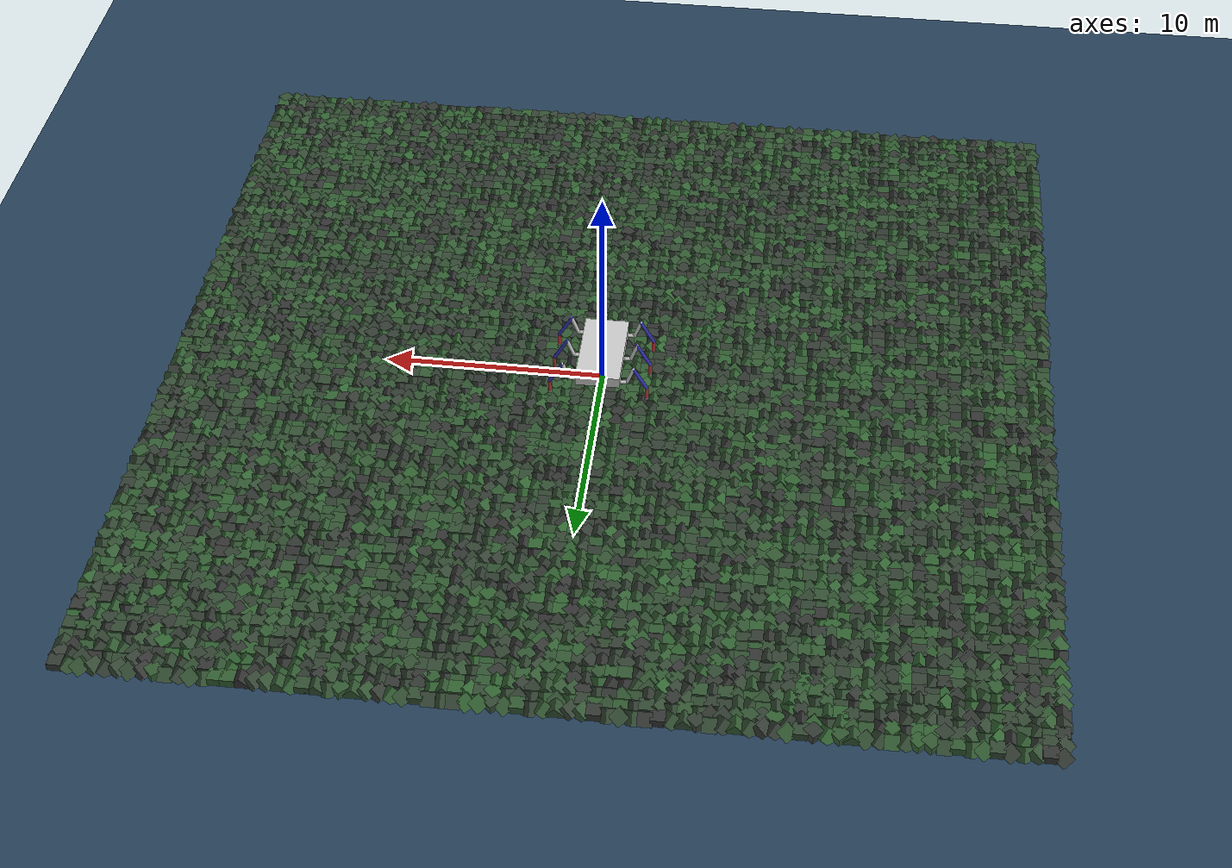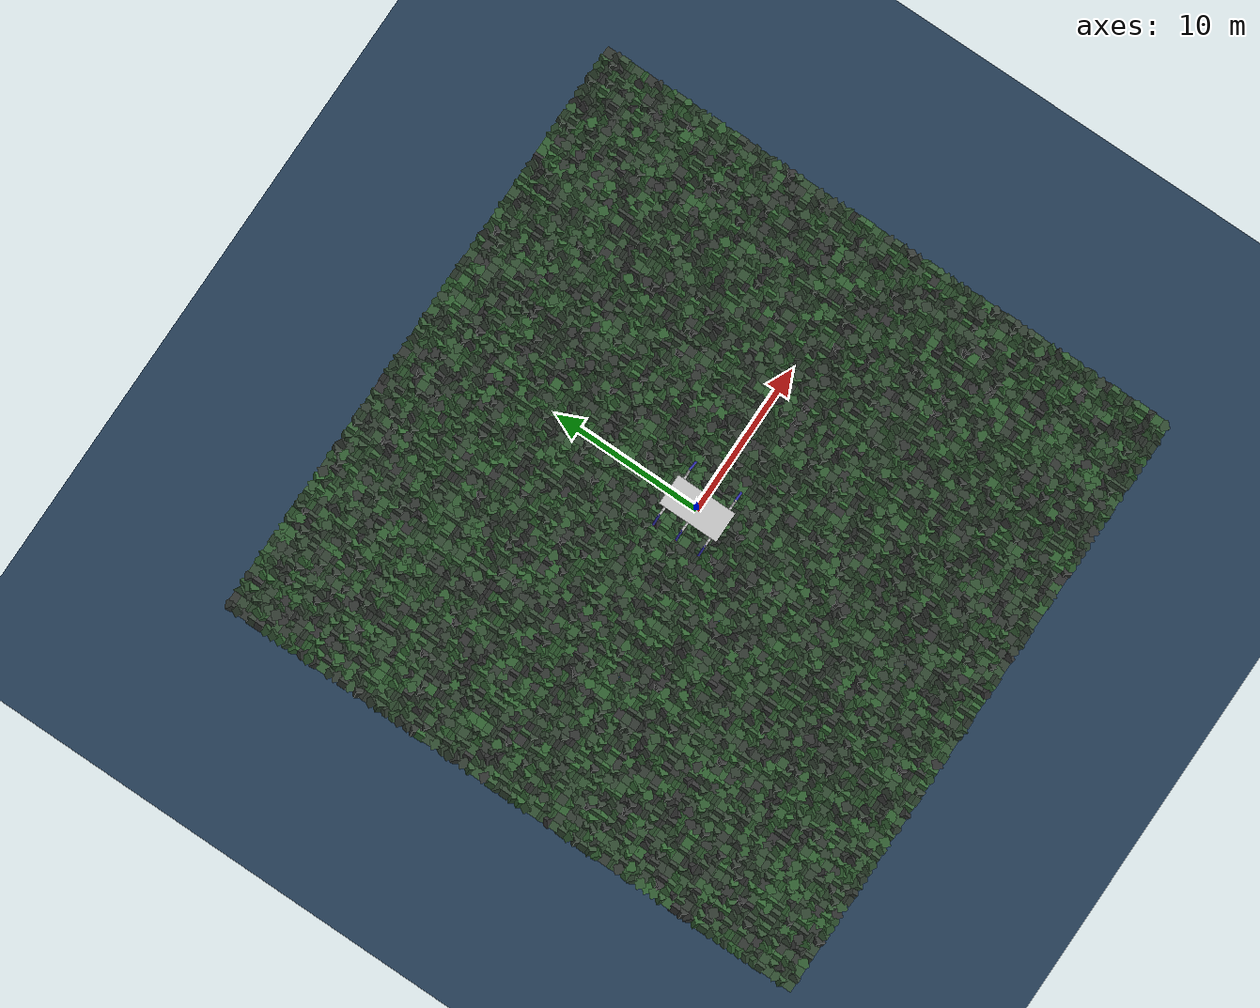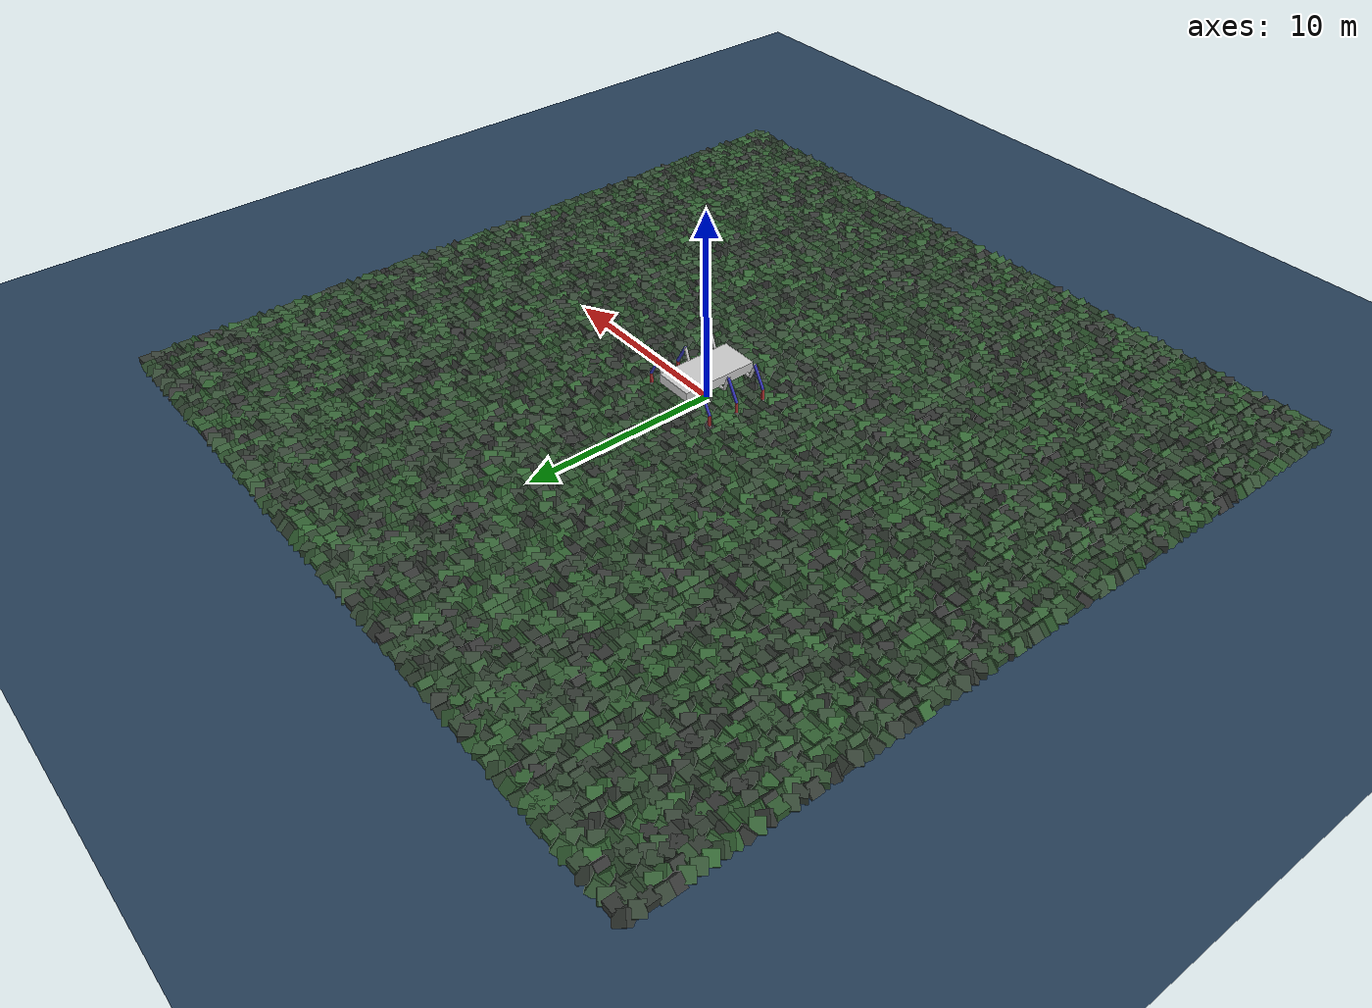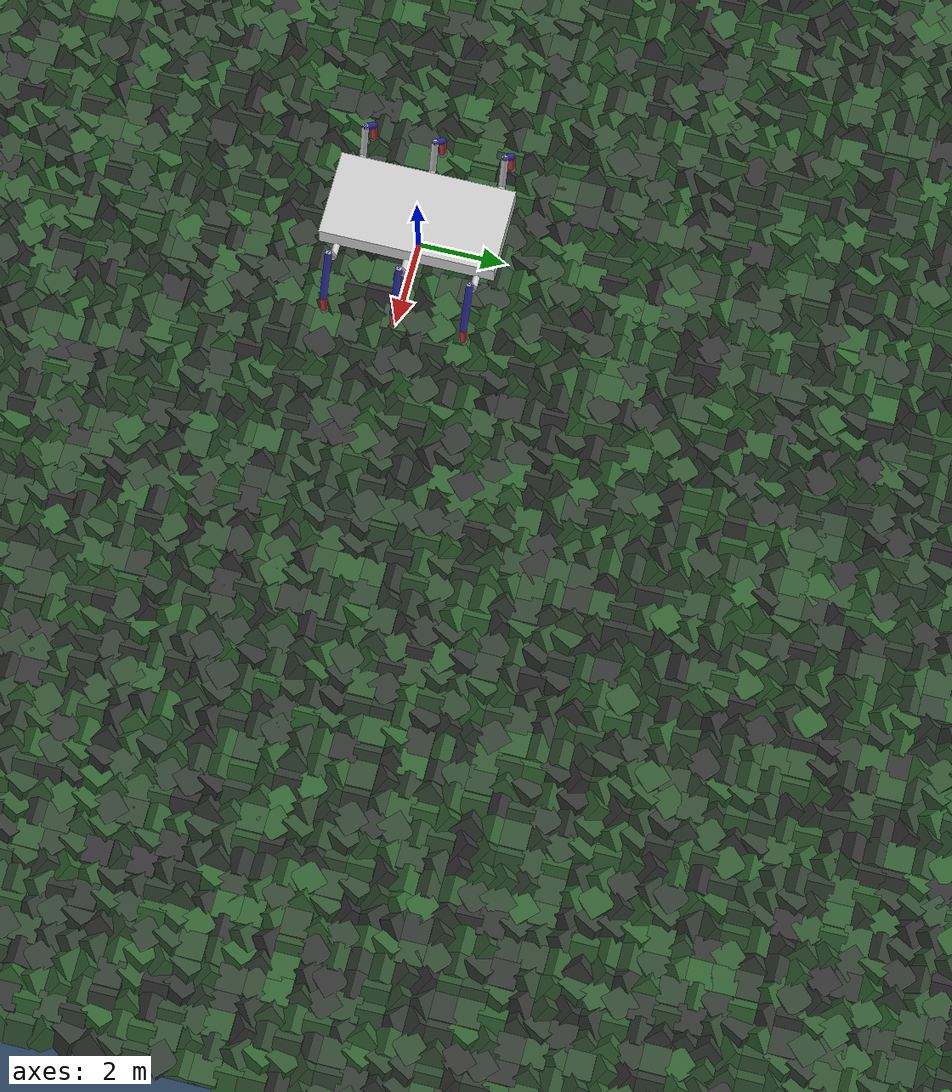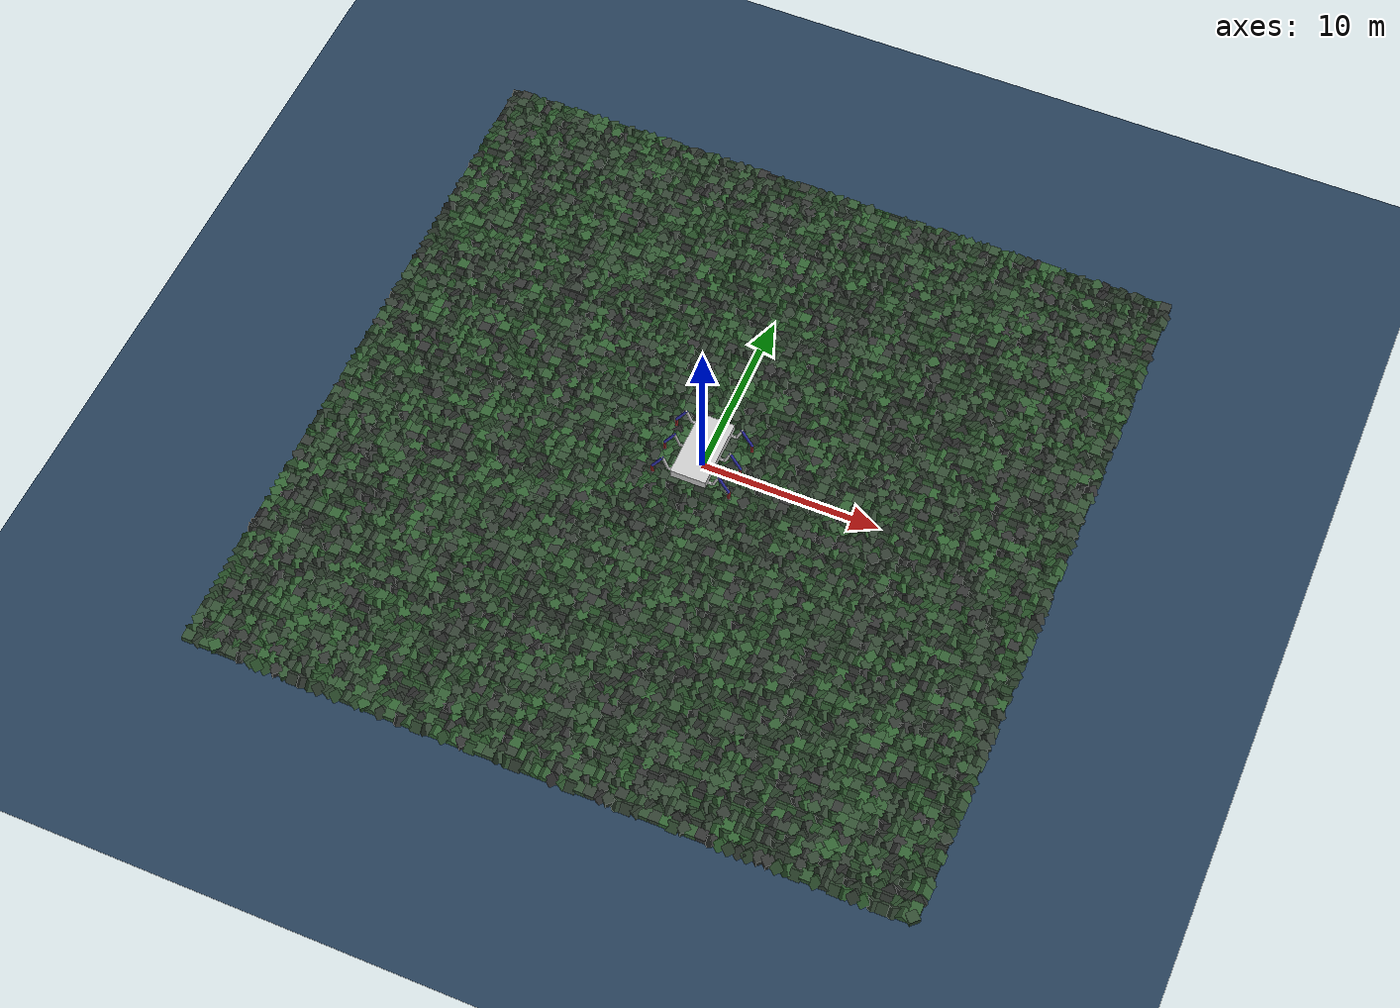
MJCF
<mujoco model="MuJoCo Model">
  <compiler angle="radian"/>

  <option timestep="0.004"/>

  <size nkey="1"/>

  <visual>
    <global azimuth="-135" elevation="-20"/>
    <scale jointlength="3.6" jointwidth="0.12"/>
  </visual>

  <statistic extent="4.5" center="0 0 0.3"/>

  <default>
    <default class="leg1-main"/>
    <default class="leg2-main"/>
    <default class="leg3-main"/>
    <default class="leg4-main"/>
    <default class="leg5-main"/>
    <default class="leg6-main"/>
  </default>

  <asset>
    <texture type="skybox" name="//unnamed_texture_0" builtin="flat" rgb1="1 1 1" rgb2="1 1 1" width="512" height="3072"/>
    <texture type="2d" name="groundplane" builtin="checker" mark="edge" rgb1="0.2 0.3 0.4" rgb2="0.1 0.2 0.3" markrgb="0.8 0.8 0.8" width="300" height="300"/>
    <material name="groundplane" texture="groundplane" texuniform="true" texrepeat="5 5" reflectance="0.2"/>
  </asset>

  <worldbody>
    <geom name="floor" size="0 0 0.125" type="plane" material="groundplane"/>
    <geom size="0.3 0.3 0.3" pos="-20 -20 0" type="box" rgba="0.2 0.309763 0.2 1"/>
    <geom size="0.3 0.3 0.3" pos="-20 -19.5 0" quat="0.853553 0.146447 0.353553 0.353553" type="box" rgba="0.2 0.343038 0.2 1"/>
    <geom size="0.3 0.3 0.3" pos="-20 -19 0" quat="0.92388 0 0 0.382683" type="box" rgba="0.2 0.320553 0.2 1"/>
    <geom size="0.3 0.3 0.3" pos="-20 -18.5 0" type="box" rgba="0.2 0.308977 0.2 1"/>
    <geom size="0.3 0.3 0.3" pos="-20 -18 0" quat="0.92388 0 0.382683 0" type="box" rgba="0.2 0.284731 0.2 1"/>
    <geom size="0.3 0.3 0.3" pos="-20 -17.5 0" quat="0.853553 0.353553 -0.146447 0.353553" type="box" rgba="0.2 0.329179 0.2 1"/>
    <geom size="0.3 0.3 0.3" pos="-20 -17 0" quat="0.853553 0.353553 -0.146447 0.353553" type="box" rgba="0.2 0.287517 0.2 1"/>
    <geom size="0.3 0.3 0.3" pos="-20 -16.5 0" quat="0.853553 0.353553 -0.146447 0.353553" type="box" rgba="0.2 0.378355 0.2 1"/>
    <geom size="0.3 0.3 0.3" pos="-20 -16 0" quat="0.853553 0.353553 -0.146447 0.353553" type="box" rgba="0.2 0.392733 0.2 1"/>
    <geom size="0.3 0.3 0.3" pos="-20 -15.5 0" quat="0.853553 0.353553 -0.146447 0.353553" type="box" rgba="0.2 0.276688 0.2 1"/>
    <geom size="0.3 0.3 0.3" pos="-20 -15 0" quat="0.853553 0.353553 -0.146447 0.353553" type="box" rgba="0.2 0.358345 0.2 1"/>
    <geom size="0.3 0.3 0.3" pos="-20 -14.5 0" quat="0.732538 0.46194 0.191342 0.46194" type="box" rgba="0.2 0.305779 0.2 1"/>
    <geom size="0.3 0.3 0.3" pos="-20 -14 0" quat="0.92388 0 0.382683 0" type="box" rgba="0.2 0.313609 0.2 1"/>
    <geom size="0.3 0.3 0.3" pos="-20 -13.5 0" quat="0.853553 0.146447 0.353553 0.353553" type="box" rgba="0.2 0.385119 0.2 1"/>
    <geom size="0.3 0.3 0.3" pos="-20 -13 0" quat="0.853553 0.353553 0.353553 0.146447" type="box" rgba="0.2 0.214207 0.2 1"/>
    <geom size="0.3 0.3 0.3" pos="-20 -12.5 0" quat="0.853553 0.146447 0.353553 0.353553" type="box" rgba="0.2 0.217426 0.2 1"/>
    <geom size="0.3 0.3 0.3" pos="-20 -12 0" quat="0.92388 0 0.382683 0" type="box" rgba="0.2 0.204044 0.2 1"/>
    <geom size="0.3 0.3 0.3" pos="-20 -11.5 0" type="box" rgba="0.2 0.366524 0.2 1"/>
    <geom size="0.3 0.3 0.3" pos="-20 -11 0" quat="0.853553 0.146447 0.353553 0.353553" type="box" rgba="0.2 0.355631 0.2 1"/>
    <geom size="0.3 0.3 0.3" pos="-20 -10.5 0" quat="0.92388 0 0 0.382683" type="box" rgba="0.2 0.374002 0.2 1"/>
    <geom size="0.3 0.3 0.3" pos="-20 -10 0" quat="0.92388 0 0 0.382683" type="box" rgba="0.2 0.395724 0.2 1"/>
    <geom size="0.3 0.3 0.3" pos="-20 -9.5 0" quat="0.92388 0 0 0.382683" type="box" rgba="0.2 0.359832 0.2 1"/>
    <geom size="0.3 0.3 0.3" pos="-20 -9 0" quat="0.853553 0.353553 0.353553 0.146447" type="box" rgba="0.2 0.292296 0.2 1"/>
    <geom size="0.3 0.3 0.3" pos="-20 -8.5 0" quat="0.853553 0.353553 -0.146447 0.353553" type="box" rgba="0.2 0.356106 0.2 1"/>
    <geom size="0.3 0.3 0.3" pos="-20 -8 0" quat="0.92388 0 0 0.382683" type="box" rgba="0.2 0.223655 0.2 1"/>
    <geom size="0.3 0.3 0.3" pos="-20 -7.5 0" quat="0.92388 0.382683 0 0" type="box" rgba="0.2 0.327984 0.2 1"/>
    <geom size="0.3 0.3 0.3" pos="-20 -7 0" type="box" rgba="0.2 0.228671 0.2 1"/>
    <geom size="0.3 0.3 0.3" pos="-20 -6.5 0" quat="0.853553 0.353553 0.353553 0.146447" type="box" rgba="0.2 0.388934 0.2 1"/>
    <geom size="0.3 0.3 0.3" pos="-20 -6 0" quat="0.853553 0.146447 0.353553 0.353553" type="box" rgba="0.2 0.30437 0.2 1"/>
    <geom size="0.3 0.3 0.3" pos="-20 -5.5 0" quat="0.92388 0 0.382683 0" type="box" rgba="0.2 0.282932 0.2 1"/>
    <geom size="0.3 0.3 0.3" pos="-20 -5 0" quat="0.853553 0.146447 0.353553 0.353553" type="box" rgba="0.2 0.252911 0.2 1"/>
    <geom size="0.3 0.3 0.3" pos="-20 -4.5 0" quat="0.732538 0.46194 0.191342 0.46194" type="box" rgba="0.2 0.354847 0.2 1"/>
    <geom size="0.3 0.3 0.3" pos="-20 -4 0" quat="0.92388 0 0.382683 0" type="box" rgba="0.2 0.29123 0.2 1"/>
    <geom size="0.3 0.3 0.3" pos="-20 -3.5 0" type="box" rgba="0.2 0.313687 0.2 1"/>
    <geom size="0.3 0.3 0.3" pos="-20 -3 0" quat="0.853553 0.353553 -0.146447 0.353553" type="box" rgba="0.2 0.203758 0.2 1"/>
    <geom size="0.3 0.3 0.3" pos="-20 -2.5 0" quat="0.92388 0.382683 0 0" type="box" rgba="0.2 0.323527 0.2 1"/>
    <geom size="0.3 0.3 0.3" pos="-20 -2 0" type="box" rgba="0.2 0.322419 0.2 1"/>
    <geom size="0.3 0.3 0.3" pos="-20 -1.5 0" quat="0.732538 0.46194 0.191342 0.46194" type="box" rgba="0.2 0.323387 0.2 1"/>
    <geom size="0.3 0.3 0.3" pos="-20 -1 0" quat="0.853553 0.146447 0.353553 0.353553" type="box" rgba="0.2 0.38875 0.2 1"/>
    <geom size="0.3 0.3 0.3" pos="-20 -0.5 0" quat="0.853553 0.146447 0.353553 0.353553" type="box" rgba="0.2 0.336364 0.2 1"/>
    <geom size="0.3 0.3 0.3" pos="-20 0 0" quat="0.92388 0 0.382683 0" type="box" rgba="0.2 0.271902 0.2 1"/>
    <geom size="0.3 0.3 0.3" pos="-20 0.5 0" quat="0.853553 0.353553 0.353553 0.146447" type="box" rgba="0.2 0.287406 0.2 1"/>
    <geom size="0.3 0.3 0.3" pos="-20 1 0" quat="0.92388 0 0.382683 0" type="box" rgba="0.2 0.339526 0.2 1"/>
    <geom size="0.3 0.3 0.3" pos="-20 1.5 0" quat="0.92388 0 0 0.382683" type="box" rgba="0.2 0.212045 0.2 1"/>
    <geom size="0.3 0.3 0.3" pos="-20 2 0" type="box" rgba="0.2 0.333353 0.2 1"/>
    <geom size="0.3 0.3 0.3" pos="-20 2.5 0" quat="0.853553 0.146447 0.353553 0.353553" type="box" rgba="0.2 0.334128 0.2 1"/>
    <geom size="0.3 0.3 0.3" pos="-20 3 0" quat="0.92388 0 0 0.382683" type="box" rgba="0.2 0.242077 0.2 1"/>
    <geom size="0.3 0.3 0.3" pos="-20 3.5 0" quat="0.853553 0.353553 0.353553 0.146447" type="box" rgba="0.2 0.225785 0.2 1"/>
    <geom size="0.3 0.3 0.3" pos="-20 4 0" quat="0.732538 0.46194 0.191342 0.46194" type="box" rgba="0.2 0.263086 0.2 1"/>
    <geom size="0.3 0.3 0.3" pos="-20 4.5 0" quat="0.853553 0.353553 -0.146447 0.353553" type="box" rgba="0.2 0.272742 0.2 1"/>
    <geom size="0.3 0.3 0.3" pos="-20 5 0" quat="0.92388 0 0 0.382683" type="box" rgba="0.2 0.314039 0.2 1"/>
    <geom size="0.3 0.3 0.3" pos="-20 5.5 0" type="box" rgba="0.2 0.28772 0.2 1"/>
    <geom size="0.3 0.3 0.3" pos="-20 6 0" quat="0.92388 0 0.382683 0" type="box" rgba="0.2 0.397675 0.2 1"/>
    <geom size="0.3 0.3 0.3" pos="-20 6.5 0" quat="0.853553 0.146447 0.353553 0.353553" type="box" rgba="0.2 0.220409 0.2 1"/>
    <geom size="0.3 0.3 0.3" pos="-20 7 0" quat="0.853553 0.353553 -0.146447 0.353553" type="box" rgba="0.2 0.241775 0.2 1"/>
    <geom size="0.3 0.3 0.3" pos="-20 7.5 0" quat="0.732538 0.46194 0.191342 0.46194" type="box" rgba="0.2 0.232262 0.2 1"/>
    <geom size="0.3 0.3 0.3" pos="-20 8 0" quat="0.853553 0.353553 -0.146447 0.353553" type="box" rgba="0.2 0.330622 0.2 1"/>
    <geom size="0.3 0.3 0.3" pos="-20 8.5 0" quat="0.853553 0.353553 -0.146447 0.353553" type="box" rgba="0.2 0.250658 0.2 1"/>
    <geom size="0.3 0.3 0.3" pos="-20 9 0" quat="0.853553 0.146447 0.353553 0.353553" type="box" rgba="0.2 0.293262 0.2 1"/>
    <geom size="0.3 0.3 0.3" pos="-20 9.5 0" quat="0.732538 0.46194 0.191342 0.46194" type="box" rgba="0.2 0.248885 0.2 1"/>
    <geom size="0.3 0.3 0.3" pos="-20 10 0" quat="0.92388 0.382683 0 0" type="box" rgba="0.2 0.231794 0.2 1"/>
    <geom size="0.3 0.3 0.3" pos="-20 10.5 0" quat="0.853553 0.146447 0.353553 0.353553" type="box" rgba="0.2 0.222075 0.2 1"/>
    <geom size="0.3 0.3 0.3" pos="-20 11 0" quat="0.92388 0 0 0.382683" type="box" rgba="0.2 0.331266 0.2 1"/>
    <geom size="0.3 0.3 0.3" pos="-20 11.5 0" quat="0.92388 0 0.382683 0" type="box" rgba="0.2 0.227637 0.2 1"/>
    <geom size="0.3 0.3 0.3" pos="-20 12 0" quat="0.92388 0 0 0.382683" type="box" rgba="0.2 0.239316 0.2 1"/>
    <geom size="0.3 0.3 0.3" pos="-20 12.5 0" quat="0.732538 0.46194 0.191342 0.46194" type="box" rgba="0.2 0.273745 0.2 1"/>
    <geom size="0.3 0.3 0.3" pos="-20 13 0" type="box" rgba="0.2 0.364199 0.2 1"/>
    <geom size="0.3 0.3 0.3" pos="-20 13.5 0" quat="0.853553 0.353553 0.353553 0.146447" type="box" rgba="0.2 0.21942 0.2 1"/>
    <geom size="0.3 0.3 0.3" pos="-20 14 0" quat="0.732538 0.46194 0.191342 0.46194" type="box" rgba="0.2 0.367589 0.2 1"/>
    <geom size="0.3 0.3 0.3" pos="-20 14.5 0" quat="0.853553 0.353553 -0.146447 0.353553" type="box" rgba="0.2 0.21922 0.2 1"/>
    <geom size="0.3 0.3 0.3" pos="-20 15 0" quat="0.853553 0.353553 0.353553 0.146447" type="box" rgba="0.2 0.395292 0.2 1"/>
    <geom size="0.3 0.3 0.3" pos="-20 15.5 0" quat="0.853553 0.353553 0.353553 0.146447" type="box" rgba="0.2 0.29373 0.2 1"/>
    <geom size="0.3 0.3 0.3" pos="-20 16 0" quat="0.732538 0.46194 0.191342 0.46194" type="box" rgba="0.2 0.395352 0.2 1"/>
    <geom size="0.3 0.3 0.3" pos="-20 16.5 0" quat="0.732538 0.46194 0.191342 0.46194" type="box" rgba="0.2 0.320969 0.2 1"/>
    <geom size="0.3 0.3 0.3" pos="-20 17 0" quat="0.732538 0.46194 0.191342 0.46194" type="box" rgba="0.2 0.347853 0.2 1"/>
    <geom size="0.3 0.3 0.3" pos="-20 17.5 0" quat="0.92388 0 0.382683 0" type="box" rgba="0.2 0.207838 0.2 1"/>
    <geom size="0.3 0.3 0.3" pos="-20 18 0" quat="0.92388 0 0.382683 0" type="box" rgba="0.2 0.256561 0.2 1"/>
    <geom size="0.3 0.3 0.3" pos="-20 18.5 0" type="box" rgba="0.2 0.224039 0.2 1"/>
    <geom size="0.3 0.3 0.3" pos="-20 19 0" quat="0.732538 0.46194 0.191342 0.46194" type="box" rgba="0.2 0.259228 0.2 1"/>
    <geom size="0.3 0.3 0.3" pos="-20 19.5 0" quat="0.853553 0.353553 0.353553 0.146447" type="box" rgba="0.2 0.223746 0.2 1"/>
    <geom size="0.3 0.3 0.3" pos="-19.5 -20 0" quat="0.732538 0.46194 0.191342 0.46194" type="box" rgba="0.2 0.263597 0.2 1"/>
    <geom size="0.3 0.3 0.3" pos="-19.5 -19.5 0" quat="0.92388 0.382683 0 0" type="box" rgba="0.2 0.282853 0.2 1"/>
    <geom size="0.3 0.3 0.3" pos="-19.5 -19 0" quat="0.853553 0.353553 0.353553 0.146447" type="box" rgba="0.2 0.21283 0.2 1"/>
    <geom size="0.3 0.3 0.3" pos="-19.5 -18.5 0" quat="0.853553 0.146447 0.353553 0.353553" type="box" rgba="0.2 0.338494 0.2 1"/>
    <geom size="0.3 0.3 0.3" pos="-19.5 -18 0" type="box" rgba="0.2 0.31332 0.2 1"/>
    <geom size="0.3 0.3 0.3" pos="-19.5 -17.5 0" quat="0.853553 0.353553 -0.146447 0.353553" type="box" rgba="0.2 0.253078 0.2 1"/>
    <geom size="0.3 0.3 0.3" pos="-19.5 -17 0" quat="0.853553 0.353553 0.353553 0.146447" type="box" rgba="0.2 0.30465 0.2 1"/>
    <geom size="0.3 0.3 0.3" pos="-19.5 -16.5 0" type="box" rgba="0.2 0.218788 0.2 1"/>
    <geom size="0.3 0.3 0.3" pos="-19.5 -16 0" quat="0.92388 0.382683 0 0" type="box" rgba="0.2 0.315189 0.2 1"/>
    <geom size="0.3 0.3 0.3" pos="-19.5 -15.5 0" quat="0.92388 0.382683 0 0" type="box" rgba="0.2 0.385859 0.2 1"/>
    <geom size="0.3 0.3 0.3" pos="-19.5 -15 0" quat="0.853553 0.353553 -0.146447 0.353553" type="box" rgba="0.2 0.263714 0.2 1"/>
    <geom size="0.3 0.3 0.3" pos="-19.5 -14.5 0" type="box" rgba="0.2 0.333482 0.2 1"/>
    <geom size="0.3 0.3 0.3" pos="-19.5 -14 0" quat="0.92388 0 0.382683 0" type="box" rgba="0.2 0.22636 0.2 1"/>
    <geom size="0.3 0.3 0.3" pos="-19.5 -13.5 0" quat="0.853553 0.146447 0.353553 0.353553" type="box" rgba="0.2 0.343265 0.2 1"/>
    <geom size="0.3 0.3 0.3" pos="-19.5 -13 0" quat="0.92388 0.382683 0 0" type="box" rgba="0.2 0.257881 0.2 1"/>
    <geom size="0.3 0.3 0.3" pos="-19.5 -12.5 0" type="box" rgba="0.2 0.236638 0.2 1"/>
    <geom size="0.3 0.3 0.3" pos="-19.5 -12 0" quat="0.92388 0 0.382683 0" type="box" rgba="0.2 0.317303 0.2 1"/>
    <geom size="0.3 0.3 0.3" pos="-19.5 -11.5 0" quat="0.853553 0.353553 -0.146447 0.353553" type="box" rgba="0.2 0.204022 0.2 1"/>
    <geom size="0.3 0.3 0.3" pos="-19.5 -11 0" quat="0.732538 0.46194 0.191342 0.46194" type="box" rgba="0.2 0.365788 0.2 1"/>
    <geom size="0.3 0.3 0.3" pos="-19.5 -10.5 0" quat="0.853553 0.146447 0.353553 0.353553" type="box" rgba="0.2 0.200939 0.2 1"/>
    <geom size="0.3 0.3 0.3" pos="-19.5 -10 0" quat="0.732538 0.46194 0.191342 0.46194" type="box" rgba="0.2 0.335563 0.2 1"/>
    <geom size="0.3 0.3 0.3" pos="-19.5 -9.5 0" type="box" rgba="0.2 0.254002 0.2 1"/>
    <geom size="0.3 0.3 0.3" pos="-19.5 -9 0" quat="0.853553 0.353553 0.353553 0.146447" type="box" rgba="0.2 0.347039 0.2 1"/>
    <geom size="0.3 0.3 0.3" pos="-19.5 -8.5 0" quat="0.92388 0 0 0.382683" type="box" rgba="0.2 0.392438 0.2 1"/>
    <geom size="0.3 0.3 0.3" pos="-19.5 -8 0" quat="0.92388 0 0.382683 0" type="box" rgba="0.2 0.249751 0.2 1"/>
    <geom size="0.3 0.3 0.3" pos="-19.5 -7.5 0" type="box" rgba="0.2 0.315231 0.2 1"/>
    <geom size="0.3 0.3 0.3" pos="-19.5 -7 0" quat="0.92388 0 0.382683 0" type="box" rgba="0.2 0.318408 0.2 1"/>
    <geom size="0.3 0.3 0.3" pos="-19.5 -6.5 0" quat="0.853553 0.353553 -0.146447 0.353553" type="box" rgba="0.2 0.31445 0.2 1"/>
    <geom size="0.3 0.3 0.3" pos="-19.5 -6 0" quat="0.853553 0.353553 0.353553 0.146447" type="box" rgba="0.2 0.244616 0.2 1"/>
    <geom size="0.3 0.3 0.3" pos="-19.5 -5.5 0" quat="0.853553 0.353553 0.353553 0.146447" type="box" rgba="0.2 0.39055 0.2 1"/>
    <geom size="0.3 0.3 0.3" pos="-19.5 -5 0" quat="0.92388 0.382683 0 0" type="box" rgba="0.2 0.289425 0.2 1"/>
    <geom size="0.3 0.3 0.3" pos="-19.5 -4.5 0" quat="0.853553 0.353553 0.353553 0.146447" type="box" rgba="0.2 0.369282 0.2 1"/>
    <geom size="0.3 0.3 0.3" pos="-19.5 -4 0" quat="0.853553 0.353553 -0.146447 0.353553" type="box" rgba="0.2 0.339896 0.2 1"/>
    <geom size="0.3 0.3 0.3" pos="-19.5 -3.5 0" type="box" rgba="0.2 0.259487 0.2 1"/>
    <geom size="0.3 0.3 0.3" pos="-19.5 -3 0" quat="0.92388 0.382683 0 0" type="box" rgba="0.2 0.36276 0.2 1"/>
    <geom size="0.3 0.3 0.3" pos="-19.5 -2.5 0" quat="0.853553 0.353553 0.353553 0.146447" type="box" rgba="0.2 0.279301 0.2 1"/>
    <geom size="0.3 0.3 0.3" pos="-19.5 -2 0" quat="0.92388 0 0.382683 0" type="box" rgba="0.2 0.376221 0.2 1"/>
    <geom size="0.3 0.3 0.3" pos="-19.5 -1.5 0" quat="0.92388 0 0 0.382683" type="box" rgba="0.2 0.316255 0.2 1"/>
    <geom size="0.3 0.3 0.3" pos="-19.5 -1 0" quat="0.732538 0.46194 0.191342 0.46194" type="box" rgba="0.2 0.376347 0.2 1"/>
    <geom size="0.3 0.3 0.3" pos="-19.5 -0.5 0" quat="0.92388 0 0.382683 0" type="box" rgba="0.2 0.338506 0.2 1"/>
    <geom size="0.3 0.3 0.3" pos="-19.5 0 0" quat="0.853553 0.353553 -0.146447 0.353553" type="box" rgba="0.2 0.345051 0.2 1"/>
    <geom size="0.3 0.3 0.3" pos="-19.5 0.5 0" quat="0.92388 0 0.382683 0" type="box" rgba="0.2 0.300265 0.2 1"/>
    <geom size="0.3 0.3 0.3" pos="-19.5 1 0" quat="0.853553 0.146447 0.353553 0.353553" type="box" rgba="0.2 0.391217 0.2 1"/>
    <geom size="0.3 0.3 0.3" pos="-19.5 1.5 0" quat="0.92388 0 0 0.382683" type="box" rgba="0.2 0.328798 0.2 1"/>
    <geom size="0.3 0.3 0.3" pos="-19.5 2 0" quat="0.853553 0.353553 0.353553 0.146447" type="box" rgba="0.2 0.284771 0.2 1"/>
    <geom size="0.3 0.3 0.3" pos="-19.5 2.5 0" quat="0.732538 0.46194 0.191342 0.46194" type="box" rgba="0.2 0.321279 0.2 1"/>
    <geom size="0.3 0.3 0.3" pos="-19.5 3 0" quat="0.92388 0 0.382683 0" type="box" rgba="0.2 0.203839 0.2 1"/>
    <geom size="0.3 0.3 0.3" pos="-19.5 3.5 0" quat="0.853553 0.353553 -0.146447 0.353553" type="box" rgba="0.2 0.260315 0.2 1"/>
    <geom size="0.3 0.3 0.3" pos="-19.5 4 0" quat="0.853553 0.353553 -0.146447 0.353553" type="box" rgba="0.2 0.332035 0.2 1"/>
    <geom size="0.3 0.3 0.3" pos="-19.5 4.5 0" quat="0.92388 0 0.382683 0" type="box" rgba="0.2 0.258016 0.2 1"/>
    <geom size="0.3 0.3 0.3" pos="-19.5 5 0" quat="0.92388 0 0.382683 0" type="box" rgba="0.2 0.323603 0.2 1"/>
    <geom size="0.3 0.3 0.3" pos="-19.5 5.5 0" quat="0.732538 0.46194 0.191342 0.46194" type="box" rgba="0.2 0.285754 0.2 1"/>
    <geom size="0.3 0.3 0.3" pos="-19.5 6 0" quat="0.853553 0.146447 0.353553 0.353553" type="box" rgba="0.2 0.227095 0.2 1"/>
    <geom size="0.3 0.3 0.3" pos="-19.5 6.5 0" quat="0.92388 0 0.382683 0" type="box" rgba="0.2 0.259656 0.2 1"/>
    <geom size="0.3 0.3 0.3" pos="-19.5 7 0" type="box" rgba="0.2 0.313993 0.2 1"/>
    <geom size="0.3 0.3 0.3" pos="-19.5 7.5 0" quat="0.732538 0.46194 0.191342 0.46194" type="box" rgba="0.2 0.318175 0.2 1"/>
    <geom size="0.3 0.3 0.3" pos="-19.5 8 0" quat="0.853553 0.353553 0.353553 0.146447" type="box" rgba="0.2 0.314865 0.2 1"/>
    <geom size="0.3 0.3 0.3" pos="-19.5 8.5 0" quat="0.853553 0.353553 -0.146447 0.353553" type="box" rgba="0.2 0.33064 0.2 1"/>
    <geom size="0.3 0.3 0.3" pos="-19.5 9 0" quat="0.92388 0 0.382683 0" type="box" rgba="0.2 0.330421 0.2 1"/>
    <geom size="0.3 0.3 0.3" pos="-19.5 9.5 0" quat="0.853553 0.353553 0.353553 0.146447" type="box" rgba="0.2 0.286284 0.2 1"/>
    <geom size="0.3 0.3 0.3" pos="-19.5 10 0" quat="0.92388 0.382683 0 0" type="box" rgba="0.2 0.379309 0.2 1"/>
    <geom size="0.3 0.3 0.3" pos="-19.5 10.5 0" quat="0.853553 0.353553 0.353553 0.146447" type="box" rgba="0.2 0.273512 0.2 1"/>
    <geom size="0.3 0.3 0.3" pos="-19.5 11 0" quat="0.732538 0.46194 0.191342 0.46194" type="box" rgba="0.2 0.287173 0.2 1"/>
    <geom size="0.3 0.3 0.3" pos="-19.5 11.5 0" quat="0.92388 0 0 0.382683" type="box" rgba="0.2 0.378385 0.2 1"/>
    <geom size="0.3 0.3 0.3" pos="-19.5 12 0" quat="0.732538 0.46194 0.191342 0.46194" type="box" rgba="0.2 0.361239 0.2 1"/>
    <geom size="0.3 0.3 0.3" pos="-19.5 12.5 0" quat="0.853553 0.146447 0.353553 0.353553" type="box" rgba="0.2 0.340778 0.2 1"/>
    <geom size="0.3 0.3 0.3" pos="-19.5 13 0" quat="0.92388 0 0.382683 0" type="box" rgba="0.2 0.220045 0.2 1"/>
    <geom size="0.3 0.3 0.3" pos="-19.5 13.5 0" quat="0.853553 0.146447 0.353553 0.353553" type="box" rgba="0.2 0.383897 0.2 1"/>
    <geom size="0.3 0.3 0.3" pos="-19.5 14 0" quat="0.853553 0.353553 0.353553 0.146447" type="box" rgba="0.2 0.342848 0.2 1"/>
    <geom size="0.3 0.3 0.3" pos="-19.5 14.5 0" quat="0.92388 0.382683 0 0" type="box" rgba="0.2 0.399769 0.2 1"/>
    <geom size="0.3 0.3 0.3" pos="-19.5 15 0" quat="0.92388 0.382683 0 0" type="box" rgba="0.2 0.22989 0.2 1"/>
    <geom size="0.3 0.3 0.3" pos="-19.5 15.5 0" quat="0.853553 0.353553 -0.146447 0.353553" type="box" rgba="0.2 0.373625 0.2 1"/>
    <geom size="0.3 0.3 0.3" pos="-19.5 16 0" type="box" rgba="0.2 0.232499 0.2 1"/>
    <geom size="0.3 0.3 0.3" pos="-19.5 16.5 0" type="box" rgba="0.2 0.323112 0.2 1"/>
    <geom size="0.3 0.3 0.3" pos="-19.5 17 0" quat="0.92388 0 0.382683 0" type="box" rgba="0.2 0.224764 0.2 1"/>
    <geom size="0.3 0.3 0.3" pos="-19.5 17.5 0" quat="0.853553 0.353553 0.353553 0.146447" type="box" rgba="0.2 0.369602 0.2 1"/>
    <geom size="0.3 0.3 0.3" pos="-19.5 18 0" quat="0.732538 0.46194 0.191342 0.46194" type="box" rgba="0.2 0.361464 0.2 1"/>
    <geom size="0.3 0.3 0.3" pos="-19.5 18.5 0" quat="0.92388 0.382683 0 0" type="box" rgba="0.2 0.31382 0.2 1"/>
    <geom size="0.3 0.3 0.3" pos="-19.5 19 0" type="box" rgba="0.2 0.281437 0.2 1"/>
    <geom size="0.3 0.3 0.3" pos="-19.5 19.5 0" type="box" rgba="0.2 0.213833 0.2 1"/>
    <geom size="0.3 0.3 0.3" pos="-19 -20 0" type="box" rgba="0.2 0.339486 0.2 1"/>
    <geom size="0.3 0.3 0.3" pos="-19 -19.5 0" quat="0.732538 0.46194 0.191342 0.46194" type="box" rgba="0.2 0.290709 0.2 1"/>
    <geom size="0.3 0.3 0.3" pos="-19 -19 0" quat="0.732538 0.46194 0.191342 0.46194" type="box" rgba="0.2 0.344411 0.2 1"/>
    <geom size="0.3 0.3 0.3" pos="-19 -18.5 0" quat="0.92388 0 0.382683 0" type="box" rgba="0.2 0.373276 0.2 1"/>
    <geom size="0.3 0.3 0.3" pos="-19 -18 0" quat="0.853553 0.353553 0.353553 0.146447" type="box" rgba="0.2 0.395104 0.2 1"/>
    <geom size="0.3 0.3 0.3" pos="-19 -17.5 0" quat="0.732538 0.46194 0.191342 0.46194" type="box" rgba="0.2 0.371161 0.2 1"/>
    <geom size="0.3 0.3 0.3" pos="-19 -17 0" type="box" rgba="0.2 0.202343 0.2 1"/>
    <geom size="0.3 0.3 0.3" pos="-19 -16.5 0" type="box" rgba="0.2 0.271996 0.2 1"/>
    <geom size="0.3 0.3 0.3" pos="-19 -16 0" quat="0.92388 0 0.382683 0" type="box" rgba="0.2 0.345998 0.2 1"/>
    <geom size="0.3 0.3 0.3" pos="-19 -15.5 0" quat="0.92388 0 0 0.382683" type="box" rgba="0.2 0.234326 0.2 1"/>
    <geom size="0.3 0.3 0.3" pos="-19 -15 0" quat="0.92388 0 0.382683 0" type="box" rgba="0.2 0.304207 0.2 1"/>
    <geom size="0.3 0.3 0.3" pos="-19 -14.5 0" quat="0.853553 0.353553 0.353553 0.146447" type="box" rgba="0.2 0.210868 0.2 1"/>
    <geom size="0.3 0.3 0.3" pos="-19 -14 0" quat="0.92388 0 0 0.382683" type="box" rgba="0.2 0.239999 0.2 1"/>
    <geom size="0.3 0.3 0.3" pos="-19 -13.5 0" quat="0.853553 0.353553 -0.146447 0.353553" type="box" rgba="0.2 0.203704 0.2 1"/>
    <geom size="0.3 0.3 0.3" pos="-19 -13 0" quat="0.92388 0.382683 0 0" type="box" rgba="0.2 0.35874 0.2 1"/>
    <geom size="0.3 0.3 0.3" pos="-19 -12.5 0" quat="0.732538 0.46194 0.191342 0.46194" type="box" rgba="0.2 0.244785 0.2 1"/>
    <geom size="0.3 0.3 0.3" pos="-19 -12 0" quat="0.853553 0.353553 0.353553 0.146447" type="box" rgba="0.2 0.26907 0.2 1"/>
    <geom size="0.3 0.3 0.3" pos="-19 -11.5 0" quat="0.92388 0.382683 0 0" type="box" rgba="0.2 0.385616 0.2 1"/>
    <geom size="0.3 0.3 0.3" pos="-19 -11 0" quat="0.92388 0 0.382683 0" type="box" rgba="0.2 0.340883 0.2 1"/>
    <geom size="0.3 0.3 0.3" pos="-19 -10.5 0" quat="0.92388 0 0.382683 0" type="box" rgba="0.2 0.206368 0.2 1"/>
    <geom size="0.3 0.3 0.3" pos="-19 -10 0" quat="0.853553 0.353553 0.353553 0.146447" type="box" rgba="0.2 0.232939 0.2 1"/>
    <geom size="0.3 0.3 0.3" pos="-19 -9.5 0" quat="0.92388 0 0.382683 0" type="box" rgba="0.2 0.324296 0.2 1"/>
    <geom size="0.3 0.3 0.3" pos="-19 -9 0" quat="0.92388 0 0 0.382683" type="box" rgba="0.2 0.315446 0.2 1"/>
    <geom size="0.3 0.3 0.3" pos="-19 -8.5 0" quat="0.92388 0 0.382683 0" type="box" rgba="0.2 0.247579 0.2 1"/>
    <geom size="0.3 0.3 0.3" pos="-19 -8 0" quat="0.853553 0.146447 0.353553 0.353553" type="box" rgba="0.2 0.386843 0.2 1"/>
    <geom size="0.3 0.3 0.3" pos="-19 -7.5 0" quat="0.853553 0.353553 -0.146447 0.353553" type="box" rgba="0.2 0.322793 0.2 1"/>
    <geom size="0.3 0.3 0.3" pos="-19 -7 0" quat="0.92388 0 0 0.382683" type="box" rgba="0.2 0.307127 0.2 1"/>
    <geom size="0.3 0.3 0.3" pos="-19 -6.5 0" type="box" rgba="0.2 0.317982 0.2 1"/>
    <geom size="0.3 0.3 0.3" pos="-19 -6 0" type="box" rgba="0.2 0.346024 0.2 1"/>
    <geom size="0.3 0.3 0.3" pos="-19 -5.5 0" quat="0.853553 0.146447 0.353553 0.353553" type="box" rgba="0.2 0.262389 0.2 1"/>
    <geom size="0.3 0.3 0.3" pos="-19 -5 0" quat="0.853553 0.146447 0.353553 0.353553" type="box" rgba="0.2 0.279644 0.2 1"/>
    <geom size="0.3 0.3 0.3" pos="-19 -4.5 0" type="box" rgba="0.2 0.241969 0.2 1"/>
    <geom size="0.3 0.3 0.3" pos="-19 -4 0" type="box" rgba="0.2 0.237239 0.2 1"/>
    <geom size="0.3 0.3 0.3" pos="-19 -3.5 0" type="box" rgba="0.2 0.388874 0.2 1"/>
    <geom size="0.3 0.3 0.3" pos="-19 -3 0" quat="0.92388 0 0 0.382683" type="box" rgba="0.2 0.34791 0.2 1"/>
    <geom size="0.3 0.3 0.3" pos="-19 -2.5 0" quat="0.853553 0.353553 0.353553 0.146447" type="box" rgba="0.2 0.298092 0.2 1"/>
    <geom size="0.3 0.3 0.3" pos="-19 -2 0" quat="0.92388 0 0 0.382683" type="box" rgba="0.2 0.245483 0.2 1"/>
    <geom size="0.3 0.3 0.3" pos="-19 -1.5 0" quat="0.853553 0.353553 0.353553 0.146447" type="box" rgba="0.2 0.250871 0.2 1"/>
    <geom size="0.3 0.3 0.3" pos="-19 -1 0" quat="0.92388 0.382683 0 0" type="box" rgba="0.2 0.211606 0.2 1"/>
    <geom size="0.3 0.3 0.3" pos="-19 -0.5 0" quat="0.853553 0.353553 -0.146447 0.353553" type="box" rgba="0.2 0.286883 0.2 1"/>
    <geom size="0.3 0.3 0.3" pos="-19 0 0" quat="0.92388 0.382683 0 0" type="box" rgba="0.2 0.262359 0.2 1"/>
    <geom size="0.3 0.3 0.3" pos="-19 0.5 0" quat="0.732538 0.46194 0.191342 0.46194" type="box" rgba="0.2 0.339269 0.2 1"/>
    <geom size="0.3 0.3 0.3" pos="-19 1 0" quat="0.92388 0.382683 0 0" type="box" rgba="0.2 0.27555 0.2 1"/>
    <geom size="0.3 0.3 0.3" pos="-19 1.5 0" quat="0.732538 0.46194 0.191342 0.46194" type="box" rgba="0.2 0.235921 0.2 1"/>
    <geom size="0.3 0.3 0.3" pos="-19 2 0" quat="0.853553 0.353553 -0.146447 0.353553" type="box" rgba="0.2 0.204936 0.2 1"/>
    <geom size="0.3 0.3 0.3" pos="-19 2.5 0" quat="0.732538 0.46194 0.191342 0.46194" type="box" rgba="0.2 0.21345 0.2 1"/>
    <geom size="0.3 0.3 0.3" pos="-19 3 0" type="box" rgba="0.2 0.335879 0.2 1"/>
    <geom size="0.3 0.3 0.3" pos="-19 3.5 0" quat="0.92388 0 0.382683 0" type="box" rgba="0.2 0.290739 0.2 1"/>
    <geom size="0.3 0.3 0.3" pos="-19 4 0" quat="0.853553 0.146447 0.353553 0.353553" type="box" rgba="0.2 0.307316 0.2 1"/>
    <geom size="0.3 0.3 0.3" pos="-19 4.5 0" quat="0.92388 0.382683 0 0" type="box" rgba="0.2 0.379334 0.2 1"/>
    <geom size="0.3 0.3 0.3" pos="-19 5 0" quat="0.853553 0.353553 -0.146447 0.353553" type="box" rgba="0.2 0.398068 0.2 1"/>
    <geom size="0.3 0.3 0.3" pos="-19 5.5 0" quat="0.853553 0.353553 -0.146447 0.353553" type="box" rgba="0.2 0.243379 0.2 1"/>
    <geom size="0.3 0.3 0.3" pos="-19 6 0" type="box" rgba="0.2 0.332616 0.2 1"/>
    <geom size="0.3 0.3 0.3" pos="-19 6.5 0" quat="0.92388 0.382683 0 0" type="box" rgba="0.2 0.252664 0.2 1"/>
    <geom size="0.3 0.3 0.3" pos="-19 7 0" quat="0.732538 0.46194 0.191342 0.46194" type="box" rgba="0.2 0.20413 0.2 1"/>
    <geom size="0.3 0.3 0.3" pos="-19 7.5 0" quat="0.853553 0.353553 -0.146447 0.353553" type="box" rgba="0.2 0.351676 0.2 1"/>
    <geom size="0.3 0.3 0.3" pos="-19 8 0" quat="0.732538 0.46194 0.191342 0.46194" type="box" rgba="0.2 0.264003 0.2 1"/>
    <geom size="0.3 0.3 0.3" pos="-19 8.5 0" quat="0.92388 0.382683 0 0" type="box" rgba="0.2 0.276693 0.2 1"/>
    <geom size="0.3 0.3 0.3" pos="-19 9 0" quat="0.853553 0.353553 -0.146447 0.353553" type="box" rgba="0.2 0.317663 0.2 1"/>
    <geom size="0.3 0.3 0.3" pos="-19 9.5 0" type="box" rgba="0.2 0.36621 0.2 1"/>
    <geom size="0.3 0.3 0.3" pos="-19 10 0" quat="0.92388 0 0.382683 0" type="box" rgba="0.2 0.325796 0.2 1"/>
    <geom size="0.3 0.3 0.3" pos="-19 10.5 0" quat="0.92388 0 0.382683 0" type="box" rgba="0.2 0.37453 0.2 1"/>
    <geom size="0.3 0.3 0.3" pos="-19 11 0" quat="0.853553 0.353553 -0.146447 0.353553" type="box" rgba="0.2 0.254708 0.2 1"/>
    <geom size="0.3 0.3 0.3" pos="-19 11.5 0" type="box" rgba="0.2 0.359609 0.2 1"/>
    <geom size="0.3 0.3 0.3" pos="-19 12 0" type="box" rgba="0.2 0.237127 0.2 1"/>
    <geom size="0.3 0.3 0.3" pos="-19 12.5 0" quat="0.92388 0 0 0.382683" type="box" rgba="0.2 0.390558 0.2 1"/>
    <geom size="0.3 0.3 0.3" pos="-19 13 0" quat="0.853553 0.353553 -0.146447 0.353553" type="box" rgba="0.2 0.337498 0.2 1"/>
    <geom size="0.3 0.3 0.3" pos="-19 13.5 0" quat="0.732538 0.46194 0.191342 0.46194" type="box" rgba="0.2 0.243102 0.2 1"/>
    <geom size="0.3 0.3 0.3" pos="-19 14 0" quat="0.853553 0.146447 0.353553 0.353553" type="box" rgba="0.2 0.389474 0.2 1"/>
    <geom size="0.3 0.3 0.3" pos="-19 14.5 0" quat="0.853553 0.353553 0.353553 0.146447" type="box" rgba="0.2 0.346171 0.2 1"/>
    <geom size="0.3 0.3 0.3" pos="-19 15 0" quat="0.92388 0.382683 0 0" type="box" rgba="0.2 0.250788 0.2 1"/>
    <geom size="0.3 0.3 0.3" pos="-19 15.5 0" type="box" rgba="0.2 0.242662 0.2 1"/>
    <geom size="0.3 0.3 0.3" pos="-19 16 0" quat="0.853553 0.353553 0.353553 0.146447" type="box" rgba="0.2 0.30364 0.2 1"/>
    <geom size="0.3 0.3 0.3" pos="-19 16.5 0" quat="0.92388 0 0 0.382683" type="box" rgba="0.2 0.205133 0.2 1"/>
    <geom size="0.3 0.3 0.3" pos="-19 17 0" quat="0.92388 0 0 0.382683" type="box" rgba="0.2 0.241494 0.2 1"/>
    <geom size="0.3 0.3 0.3" pos="-19 17.5 0" quat="0.92388 0 0 0.382683" type="box" rgba="0.2 0.284937 0.2 1"/>
    <geom size="0.3 0.3 0.3" pos="-19 18 0" quat="0.853553 0.353553 -0.146447 0.353553" type="box" rgba="0.2 0.274834 0.2 1"/>
    <geom size="0.3 0.3 0.3" pos="-19 18.5 0" quat="0.853553 0.146447 0.353553 0.353553" type="box" rgba="0.2 0.292715 0.2 1"/>
    <geom size="0.3 0.3 0.3" pos="-19 19 0" quat="0.853553 0.353553 -0.146447 0.353553" type="box" rgba="0.2 0.255526 0.2 1"/>
    <geom size="0.3 0.3 0.3" pos="-19 19.5 0" quat="0.732538 0.46194 0.191342 0.46194" type="box" rgba="0.2 0.317357 0.2 1"/>
    <geom size="0.3 0.3 0.3" pos="-18.5 -20 0" quat="0.92388 0 0 0.382683" type="box" rgba="0.2 0.372771 0.2 1"/>
    <geom size="0.3 0.3 0.3" pos="-18.5 -19.5 0" quat="0.92388 0 0 0.382683" type="box" rgba="0.2 0.223506 0.2 1"/>
    <geom size="0.3 0.3 0.3" pos="-18.5 -19 0" type="box" rgba="0.2 0.303476 0.2 1"/>
    <geom size="0.3 0.3 0.3" pos="-18.5 -18.5 0" type="box" rgba="0.2 0.226414 0.2 1"/>
    <geom size="0.3 0.3 0.3" pos="-18.5 -18 0" quat="0.853553 0.146447 0.353553 0.353553" type="box" rgba="0.2 0.343372 0.2 1"/>
    <geom size="0.3 0.3 0.3" pos="-18.5 -17.5 0" quat="0.732538 0.46194 0.191342 0.46194" type="box" rgba="0.2 0.279212 0.2 1"/>
    <geom size="0.3 0.3 0.3" pos="-18.5 -17 0" quat="0.853553 0.146447 0.353553 0.353553" type="box" rgba="0.2 0.313084 0.2 1"/>
    <geom size="0.3 0.3 0.3" pos="-18.5 -16.5 0" quat="0.853553 0.353553 0.353553 0.146447" type="box" rgba="0.2 0.236656 0.2 1"/>
    <geom size="0.3 0.3 0.3" pos="-18.5 -16 0" quat="0.853553 0.146447 0.353553 0.353553" type="box" rgba="0.2 0.22897 0.2 1"/>
    <geom size="0.3 0.3 0.3" pos="-18.5 -15.5 0" quat="0.92388 0.382683 0 0" type="box" rgba="0.2 0.297611 0.2 1"/>
    <geom size="0.3 0.3 0.3" pos="-18.5 -15 0" quat="0.732538 0.46194 0.191342 0.46194" type="box" rgba="0.2 0.271123 0.2 1"/>
    <geom size="0.3 0.3 0.3" pos="-18.5 -14.5 0" quat="0.92388 0 0.382683 0" type="box" rgba="0.2 0.388086 0.2 1"/>
    <geom size="0.3 0.3 0.3" pos="-18.5 -14 0" quat="0.92388 0 0.382683 0" type="box" rgba="0.2 0.353065 0.2 1"/>
    <geom size="0.3 0.3 0.3" pos="-18.5 -13.5 0" quat="0.853553 0.146447 0.353553 0.353553" type="box" rgba="0.2 0.349733 0.2 1"/>
    <geom size="0.3 0.3 0.3" pos="-18.5 -13 0" type="box" rgba="0.2 0.380744 0.2 1"/>
    <geom size="0.3 0.3 0.3" pos="-18.5 -12.5 0" quat="0.92388 0 0.382683 0" type="box" rgba="0.2 0.216684 0.2 1"/>
    <geom size="0.3 0.3 0.3" pos="-18.5 -12 0" quat="0.853553 0.146447 0.353553 0.353553" type="box" rgba="0.2 0.310438 0.2 1"/>
    <geom size="0.3 0.3 0.3" pos="-18.5 -11.5 0" type="box" rgba="0.2 0.316895 0.2 1"/>
    <geom size="0.3 0.3 0.3" pos="-18.5 -11 0" quat="0.732538 0.46194 0.191342 0.46194" type="box" rgba="0.2 0.392387 0.2 1"/>
    <geom size="0.3 0.3 0.3" pos="-18.5 -10.5 0" type="box" rgba="0.2 0.258429 0.2 1"/>
    <geom size="0.3 0.3 0.3" pos="-18.5 -10 0" type="box" rgba="0.2 0.248166 0.2 1"/>
    <geom size="0.3 0.3 0.3" pos="-18.5 -9.5 0" quat="0.92388 0 0.382683 0" type="box" rgba="0.2 0.220059 0.2 1"/>
    <geom size="0.3 0.3 0.3" pos="-18.5 -9 0" quat="0.853553 0.353553 -0.146447 0.353553" type="box" rgba="0.2 0.203286 0.2 1"/>
    <geom size="0.3 0.3 0.3" pos="-18.5 -8.5 0" type="box" rgba="0.2 0.385906 0.2 1"/>
    <geom size="0.3 0.3 0.3" pos="-18.5 -8 0" quat="0.92388 0 0 0.382683" type="box" rgba="0.2 0.333983 0.2 1"/>
    <geom size="0.3 0.3 0.3" pos="-18.5 -7.5 0" quat="0.853553 0.146447 0.353553 0.353553" type="box" rgba="0.2 0.357031 0.2 1"/>
    <geom size="0.3 0.3 0.3" pos="-18.5 -7 0" quat="0.92388 0 0.382683 0" type="box" rgba="0.2 0.256346 0.2 1"/>
    <geom size="0.3 0.3 0.3" pos="-18.5 -6.5 0" quat="0.732538 0.46194 0.191342 0.46194" type="box" rgba="0.2 0.317282 0.2 1"/>
    <geom size="0.3 0.3 0.3" pos="-18.5 -6 0" quat="0.853553 0.146447 0.353553 0.353553" type="box" rgba="0.2 0.212791 0.2 1"/>
    <geom size="0.3 0.3 0.3" pos="-18.5 -5.5 0" quat="0.853553 0.353553 -0.146447 0.353553" type="box" rgba="0.2 0.297126 0.2 1"/>
    <geom size="0.3 0.3 0.3" pos="-18.5 -5 0" quat="0.853553 0.146447 0.353553 0.353553" type="box" rgba="0.2 0.395499 0.2 1"/>
    <geom size="0.3 0.3 0.3" pos="-18.5 -4.5 0" quat="0.853553 0.353553 -0.146447 0.353553" type="box" rgba="0.2 0.375301 0.2 1"/>
    <geom size="0.3 0.3 0.3" pos="-18.5 -4 0" quat="0.92388 0.382683 0 0" type="box" rgba="0.2 0.267632 0.2 1"/>
    <geom size="0.3 0.3 0.3" pos="-18.5 -3.5 0" quat="0.853553 0.353553 0.353553 0.146447" type="box" rgba="0.2 0.392314 0.2 1"/>
    <geom size="0.3 0.3 0.3" pos="-18.5 -3 0" type="box" rgba="0.2 0.24634 0.2 1"/>
    <geom size="0.3 0.3 0.3" pos="-18.5 -2.5 0" quat="0.92388 0.382683 0 0" type="box" rgba="0.2 0.389864 0.2 1"/>
    <geom size="0.3 0.3 0.3" pos="-18.5 -2 0" quat="0.853553 0.353553 0.353553 0.146447" type="box" rgba="0.2 0.388276 0.2 1"/>
    <geom size="0.3 0.3 0.3" pos="-18.5 -1.5 0" quat="0.853553 0.353553 0.353553 0.146447" type="box" rgba="0.2 0.359841 0.2 1"/>
    <geom size="0.3 0.3 0.3" pos="-18.5 -1 0" type="box" rgba="0.2 0.32609 0.2 1"/>
    <geom size="0.3 0.3 0.3" pos="-18.5 -0.5 0" quat="0.853553 0.146447 0.353553 0.353553" type="box" rgba="0.2 0.374858 0.2 1"/>
    <geom size="0.3 0.3 0.3" pos="-18.5 0 0" quat="0.732538 0.46194 0.191342 0.46194" type="box" rgba="0.2 0.258604 0.2 1"/>
    <geom size="0.3 0.3 0.3" pos="-18.5 0.5 0" quat="0.92388 0 0 0.382683" type="box" rgba="0.2 0.369789 0.2 1"/>
    <geom size="0.3 0.3 0.3" pos="-18.5 1 0" type="box" rgba="0.2 0.323575 0.2 1"/>
    <geom size="0.3 0.3 0.3" pos="-18.5 1.5 0" quat="0.853553 0.353553 -0.146447 0.353553" type="box" rgba="0.2 0.202647 0.2 1"/>
    <geom size="0.3 0.3 0.3" pos="-18.5 2 0" quat="0.853553 0.353553 -0.146447 0.353553" type="box" rgba="0.2 0.269447 0.2 1"/>
    <geom size="0.3 0.3 0.3" pos="-18.5 2.5 0" type="box" rgba="0.2 0.229628 0.2 1"/>
    <geom size="0.3 0.3 0.3" pos="-18.5 3 0" quat="0.732538 0.46194 0.191342 0.46194" type="box" rgba="0.2 0.396366 0.2 1"/>
    <geom size="0.3 0.3 0.3" pos="-18.5 3.5 0" quat="0.853553 0.353553 0.353553 0.146447" type="box" rgba="0.2 0.295674 0.2 1"/>
    <geom size="0.3 0.3 0.3" pos="-18.5 4 0" type="box" rgba="0.2 0.299478 0.2 1"/>
    <geom size="0.3 0.3 0.3" pos="-18.5 4.5 0" quat="0.92388 0.382683 0 0" type="box" rgba="0.2 0.327895 0.2 1"/>
    <geom size="0.3 0.3 0.3" pos="-18.5 5 0" quat="0.92388 0 0 0.382683" type="box" rgba="0.2 0.273717 0.2 1"/>
    <geom size="0.3 0.3 0.3" pos="-18.5 5.5 0" quat="0.853553 0.353553 -0.146447 0.353553" type="box" rgba="0.2 0.22738 0.2 1"/>
    <geom size="0.3 0.3 0.3" pos="-18.5 6 0" quat="0.853553 0.353553 -0.146447 0.353553" type="box" rgba="0.2 0.364424 0.2 1"/>
    <geom size="0.3 0.3 0.3" pos="-18.5 6.5 0" quat="0.92388 0 0.382683 0" type="box" rgba="0.2 0.23797 0.2 1"/>
    <geom size="0.3 0.3 0.3" pos="-18.5 7 0" quat="0.92388 0.382683 0 0" type="box" rgba="0.2 0.302264 0.2 1"/>
    <geom size="0.3 0.3 0.3" pos="-18.5 7.5 0" quat="0.732538 0.46194 0.191342 0.46194" type="box" rgba="0.2 0.244863 0.2 1"/>
    <geom size="0.3 0.3 0.3" pos="-18.5 8 0" quat="0.92388 0 0.382683 0" type="box" rgba="0.2 0.219569 0.2 1"/>
    <geom size="0.3 0.3 0.3" pos="-18.5 8.5 0" quat="0.92388 0.382683 0 0" type="box" rgba="0.2 0.372438 0.2 1"/>
    <geom size="0.3 0.3 0.3" pos="-18.5 9 0" quat="0.732538 0.46194 0.191342 0.46194" type="box" rgba="0.2 0.394584 0.2 1"/>
    <geom size="0.3 0.3 0.3" pos="-18.5 9.5 0" quat="0.92388 0.382683 0 0" type="box" rgba="0.2 0.392167 0.2 1"/>
    <geom size="0.3 0.3 0.3" pos="-18.5 10 0" type="box" rgba="0.2 0.381311 0.2 1"/>
    <geom size="0.3 0.3 0.3" pos="-18.5 10.5 0" quat="0.853553 0.353553 -0.146447 0.353553" type="box" rgba="0.2 0.354809 0.2 1"/>
    <geom size="0.3 0.3 0.3" pos="-18.5 11 0" quat="0.92388 0 0.382683 0" type="box" rgba="0.2 0.266629 0.2 1"/>
    <geom size="0.3 0.3 0.3" pos="-18.5 11.5 0" quat="0.732538 0.46194 0.191342 0.46194" type="box" rgba="0.2 0.21622 0.2 1"/>
    <geom size="0.3 0.3 0.3" pos="-18.5 12 0" quat="0.92388 0.382683 0 0" type="box" rgba="0.2 0.281448 0.2 1"/>
    <geom size="0.3 0.3 0.3" pos="-18.5 12.5 0" quat="0.853553 0.353553 0.353553 0.146447" type="box" rgba="0.2 0.246447 0.2 1"/>
    <geom size="0.3 0.3 0.3" pos="-18.5 13 0" quat="0.92388 0 0 0.382683" type="box" rgba="0.2 0.226498 0.2 1"/>
    <geom size="0.3 0.3 0.3" pos="-18.5 13.5 0" quat="0.92388 0 0 0.382683" type="box" rgba="0.2 0.210685 0.2 1"/>
    <geom size="0.3 0.3 0.3" pos="-18.5 14 0" quat="0.853553 0.146447 0.353553 0.353553" type="box" rgba="0.2 0.345119 0.2 1"/>
    <geom size="0.3 0.3 0.3" pos="-18.5 14.5 0" type="box" rgba="0.2 0.202285 0.2 1"/>
    <geom size="0.3 0.3 0.3" pos="-18.5 15 0" quat="0.92388 0 0 0.382683" type="box" rgba="0.2 0.354116 0.2 1"/>
    <geom size="0.3 0.3 0.3" pos="-18.5 15.5 0" type="box" rgba="0.2 0.229389 0.2 1"/>
    <geom size="0.3 0.3 0.3" pos="-18.5 16 0" quat="0.853553 0.353553 0.353553 0.146447" type="box" rgba="0.2 0.215904 0.2 1"/>
    <geom size="0.3 0.3 0.3" pos="-18.5 16.5 0" type="box" rgba="0.2 0.217921 0.2 1"/>
    <geom size="0.3 0.3 0.3" pos="-18.5 17 0" quat="0.732538 0.46194 0.191342 0.46194" type="box" rgba="0.2 0.33441 0.2 1"/>
    <geom size="0.3 0.3 0.3" pos="-18.5 17.5 0" quat="0.732538 0.46194 0.191342 0.46194" type="box" rgba="0.2 0.249073 0.2 1"/>
    <geom size="0.3 0.3 0.3" pos="-18.5 18 0" quat="0.92388 0 0 0.382683" type="box" rgba="0.2 0.284108 0.2 1"/>
    <geom size="0.3 0.3 0.3" pos="-18.5 18.5 0" quat="0.92388 0.382683 0 0" type="box" rgba="0.2 0.311474 0.2 1"/>
    <geom size="0.3 0.3 0.3" pos="-18.5 19 0" quat="0.853553 0.146447 0.353553 0.353553" type="box" rgba="0.2 0.37211 0.2 1"/>
    <geom size="0.3 0.3 0.3" pos="-18.5 19.5 0" quat="0.853553 0.353553 -0.146447 0.353553" type="box" rgba="0.2 0.345409 0.2 1"/>
    <geom size="0.3 0.3 0.3" pos="-18 -20 0" quat="0.92388 0 0.382683 0" type="box" rgba="0.2 0.254066 0.2 1"/>
    <geom size="0.3 0.3 0.3" pos="-18 -19.5 0" quat="0.853553 0.353553 -0.146447 0.353553" type="box" rgba="0.2 0.226297 0.2 1"/>
    <geom size="0.3 0.3 0.3" pos="-18 -19 0" quat="0.853553 0.353553 0.353553 0.146447" type="box" rgba="0.2 0.211075 0.2 1"/>
    <geom size="0.3 0.3 0.3" pos="-18 -18.5 0" quat="0.732538 0.46194 0.191342 0.46194" type="box" rgba="0.2 0.26032 0.2 1"/>
    <geom size="0.3 0.3 0.3" pos="-18 -18 0" quat="0.853553 0.353553 -0.146447 0.353553" type="box" rgba="0.2 0.252424 0.2 1"/>
    <geom size="0.3 0.3 0.3" pos="-18 -17.5 0" quat="0.853553 0.353553 0.353553 0.146447" type="box" rgba="0.2 0.291228 0.2 1"/>
    <geom size="0.3 0.3 0.3" pos="-18 -17 0" quat="0.92388 0 0.382683 0" type="box" rgba="0.2 0.336656 0.2 1"/>
    <geom size="0.3 0.3 0.3" pos="-18 -16.5 0" quat="0.853553 0.353553 0.353553 0.146447" type="box" rgba="0.2 0.339125 0.2 1"/>
    <geom size="0.3 0.3 0.3" pos="-18 -16 0" quat="0.92388 0 0.382683 0" type="box" rgba="0.2 0.256704 0.2 1"/>
    <geom size="0.3 0.3 0.3" pos="-18 -15.5 0" quat="0.853553 0.353553 -0.146447 0.353553" type="box" rgba="0.2 0.275985 0.2 1"/>
    <geom size="0.3 0.3 0.3" pos="-18 -15 0" quat="0.732538 0.46194 0.191342 0.46194" type="box" rgba="0.2 0.23623 0.2 1"/>
    <geom size="0.3 0.3 0.3" pos="-18 -14.5 0" quat="0.853553 0.146447 0.353553 0.353553" type="box" rgba="0.2 0.357709 0.2 1"/>
    <geom size="0.3 0.3 0.3" pos="-18 -14 0" quat="0.853553 0.353553 -0.146447 0.353553" type="box" rgba="0.2 0.21137 0.2 1"/>
    <geom size="0.3 0.3 0.3" pos="-18 -13.5 0" quat="0.853553 0.146447 0.353553 0.353553" type="box" rgba="0.2 0.339399 0.2 1"/>
    <geom size="0.3 0.3 0.3" pos="-18 -13 0" quat="0.92388 0 0 0.382683" type="box" rgba="0.2 0.355739 0.2 1"/>
    <geom size="0.3 0.3 0.3" pos="-18 -12.5 0" type="box" rgba="0.2 0.355482 0.2 1"/>
    <geom size="0.3 0.3 0.3" pos="-18 -12 0" quat="0.92388 0.382683 0 0" type="box" rgba="0.2 0.251885 0.2 1"/>
    <geom size="0.3 0.3 0.3" pos="-18 -11.5 0" quat="0.732538 0.46194 0.191342 0.46194" type="box" rgba="0.2 0.274763 0.2 1"/>
    <geom size="0.3 0.3 0.3" pos="-18 -11 0" quat="0.853553 0.146447 0.353553 0.353553" type="box" rgba="0.2 0.31752 0.2 1"/>
    <geom size="0.3 0.3 0.3" pos="-18 -10.5 0" quat="0.92388 0 0.382683 0" type="box" rgba="0.2 0.254564 0.2 1"/>
    <geom size="0.3 0.3 0.3" pos="-18 -10 0" quat="0.732538 0.46194 0.191342 0.46194" type="box" rgba="0.2 0.274171 0.2 1"/>
    <geom size="0.3 0.3 0.3" pos="-18 -9.5 0" quat="0.853553 0.146447 0.353553 0.353553" type="box" rgba="0.2 0.239411 0.2 1"/>
    <geom size="0.3 0.3 0.3" pos="-18 -9 0" quat="0.853553 0.353553 -0.146447 0.353553" type="box" rgba="0.2 0.291971 0.2 1"/>
    <geom size="0.3 0.3 0.3" pos="-18 -8.5 0" quat="0.732538 0.46194 0.191342 0.46194" type="box" rgba="0.2 0.208922 0.2 1"/>
    <geom size="0.3 0.3 0.3" pos="-18 -8 0" quat="0.92388 0.382683 0 0" type="box" rgba="0.2 0.359959 0.2 1"/>
    <geom size="0.3 0.3 0.3" pos="-18 -7.5 0" quat="0.92388 0 0.382683 0" type="box" rgba="0.2 0.215391 0.2 1"/>
    <geom size="0.3 0.3 0.3" pos="-18 -7 0" quat="0.853553 0.353553 0.353553 0.146447" type="box" rgba="0.2 0.303767 0.2 1"/>
    <geom size="0.3 0.3 0.3" pos="-18 -6.5 0" quat="0.732538 0.46194 0.191342 0.46194" type="box" rgba="0.2 0.261362 0.2 1"/>
    <geom size="0.3 0.3 0.3" pos="-18 -6 0" quat="0.853553 0.146447 0.353553 0.353553" type="box" rgba="0.2 0.315509 0.2 1"/>
    <geom size="0.3 0.3 0.3" pos="-18 -5.5 0" quat="0.92388 0 0.382683 0" type="box" rgba="0.2 0.391887 0.2 1"/>
    <geom size="0.3 0.3 0.3" pos="-18 -5 0" quat="0.92388 0 0.382683 0" type="box" rgba="0.2 0.329114 0.2 1"/>
    <geom size="0.3 0.3 0.3" pos="-18 -4.5 0" quat="0.853553 0.146447 0.353553 0.353553" type="box" rgba="0.2 0.207072 0.2 1"/>
    <geom size="0.3 0.3 0.3" pos="-18 -4 0" type="box" rgba="0.2 0.28608 0.2 1"/>
    <geom size="0.3 0.3 0.3" pos="-18 -3.5 0" quat="0.853553 0.353553 -0.146447 0.353553" type="box" rgba="0.2 0.302003 0.2 1"/>
    <geom size="0.3 0.3 0.3" pos="-18 -3 0" quat="0.92388 0 0 0.382683" type="box" rgba="0.2 0.307236 0.2 1"/>
    <geom size="0.3 0.3 0.3" pos="-18 -2.5 0" quat="0.92388 0 0.382683 0" type="box" rgba="0.2 0.336278 0.2 1"/>
    <geom size="0.3 0.3 0.3" pos="-18 -2 0" quat="0.853553 0.353553 -0.146447 0.353553" type="box" rgba="0.2 0.255519 0.2 1"/>
    <geom size="0.3 0.3 0.3" pos="-18 -1.5 0" quat="0.732538 0.46194 0.191342 0.46194" type="box" rgba="0.2 0.225772 0.2 1"/>
    <geom size="0.3 0.3 0.3" pos="-18 -1 0" quat="0.732538 0.46194 0.191342 0.46194" type="box" rgba="0.2 0.278535 0.2 1"/>
    <geom size="0.3 0.3 0.3" pos="-18 -0.5 0" quat="0.732538 0.46194 0.191342 0.46194" type="box" rgba="0.2 0.391281 0.2 1"/>
    <geom size="0.3 0.3 0.3" pos="-18 0 0" quat="0.853553 0.146447 0.353553 0.353553" type="box" rgba="0.2 0.237426 0.2 1"/>
    <geom size="0.3 0.3 0.3" pos="-18 0.5 0" type="box" rgba="0.2 0.380797 0.2 1"/>
    <geom size="0.3 0.3 0.3" pos="-18 1 0" quat="0.853553 0.353553 0.353553 0.146447" type="box" rgba="0.2 0.308761 0.2 1"/>
    <geom size="0.3 0.3 0.3" pos="-18 1.5 0" quat="0.853553 0.353553 0.353553 0.146447" type="box" rgba="0.2 0.291382 0.2 1"/>
    <geom size="0.3 0.3 0.3" pos="-18 2 0" quat="0.92388 0 0 0.382683" type="box" rgba="0.2 0.376408 0.2 1"/>
    <geom size="0.3 0.3 0.3" pos="-18 2.5 0" quat="0.853553 0.353553 0.353553 0.146447" type="box" rgba="0.2 0.291721 0.2 1"/>
    <geom size="0.3 0.3 0.3" pos="-18 3 0" quat="0.853553 0.146447 0.353553 0.353553" type="box" rgba="0.2 0.344834 0.2 1"/>
    <geom size="0.3 0.3 0.3" pos="-18 3.5 0" quat="0.853553 0.146447 0.353553 0.353553" type="box" rgba="0.2 0.279805 0.2 1"/>
    <geom size="0.3 0.3 0.3" pos="-18 4 0" quat="0.853553 0.353553 0.353553 0.146447" type="box" rgba="0.2 0.380809 0.2 1"/>
    <geom size="0.3 0.3 0.3" pos="-18 4.5 0" quat="0.92388 0 0 0.382683" type="box" rgba="0.2 0.338005 0.2 1"/>
    <geom size="0.3 0.3 0.3" pos="-18 5 0" quat="0.853553 0.353553 0.353553 0.146447" type="box" rgba="0.2 0.339924 0.2 1"/>
    <geom size="0.3 0.3 0.3" pos="-18 5.5 0" type="box" rgba="0.2 0.265544 0.2 1"/>
    <geom size="0.3 0.3 0.3" pos="-18 6 0" quat="0.853553 0.146447 0.353553 0.353553" type="box" rgba="0.2 0.351356 0.2 1"/>
    <geom size="0.3 0.3 0.3" pos="-18 6.5 0" quat="0.92388 0.382683 0 0" type="box" rgba="0.2 0.327212 0.2 1"/>
    <geom size="0.3 0.3 0.3" pos="-18 7 0" quat="0.853553 0.353553 0.353553 0.146447" type="box" rgba="0.2 0.248004 0.2 1"/>
    <geom size="0.3 0.3 0.3" pos="-18 7.5 0" quat="0.853553 0.146447 0.353553 0.353553" type="box" rgba="0.2 0.232108 0.2 1"/>
    <geom size="0.3 0.3 0.3" pos="-18 8 0" quat="0.92388 0 0 0.382683" type="box" rgba="0.2 0.359278 0.2 1"/>
    <geom size="0.3 0.3 0.3" pos="-18 8.5 0" quat="0.853553 0.353553 -0.146447 0.353553" type="box" rgba="0.2 0.391833 0.2 1"/>
    <geom size="0.3 0.3 0.3" pos="-18 9 0" quat="0.732538 0.46194 0.191342 0.46194" type="box" rgba="0.2 0.291628 0.2 1"/>
    <geom size="0.3 0.3 0.3" pos="-18 9.5 0" quat="0.92388 0.382683 0 0" type="box" rgba="0.2 0.318197 0.2 1"/>
    <geom size="0.3 0.3 0.3" pos="-18 10 0" type="box" rgba="0.2 0.371545 0.2 1"/>
    <geom size="0.3 0.3 0.3" pos="-18 10.5 0" quat="0.853553 0.353553 0.353553 0.146447" type="box" rgba="0.2 0.291445 0.2 1"/>
    <geom size="0.3 0.3 0.3" pos="-18 11 0" quat="0.732538 0.46194 0.191342 0.46194" type="box" rgba="0.2 0.390375 0.2 1"/>
    <geom size="0.3 0.3 0.3" pos="-18 11.5 0" quat="0.92388 0 0.382683 0" type="box" rgba="0.2 0.31515 0.2 1"/>
    <geom size="0.3 0.3 0.3" pos="-18 12 0" quat="0.92388 0 0 0.382683" type="box" rgba="0.2 0.364153 0.2 1"/>
    <geom size="0.3 0.3 0.3" pos="-18 12.5 0" quat="0.853553 0.353553 -0.146447 0.353553" type="box" rgba="0.2 0.381769 0.2 1"/>
    <geom size="0.3 0.3 0.3" pos="-18 13 0" quat="0.853553 0.146447 0.353553 0.353553" type="box" rgba="0.2 0.363105 0.2 1"/>
    <geom size="0.3 0.3 0.3" pos="-18 13.5 0" quat="0.92388 0 0.382683 0" type="box" rgba="0.2 0.231883 0.2 1"/>
    <geom size="0.3 0.3 0.3" pos="-18 14 0" quat="0.92388 0 0 0.382683" type="box" rgba="0.2 0.32578 0.2 1"/>
    <geom size="0.3 0.3 0.3" pos="-18 14.5 0" quat="0.853553 0.353553 0.353553 0.146447" type="box" rgba="0.2 0.279687 0.2 1"/>
    <geom size="0.3 0.3 0.3" pos="-18 15 0" quat="0.853553 0.353553 -0.146447 0.353553" type="box" rgba="0.2 0.212543 0.2 1"/>
    <geom size="0.3 0.3 0.3" pos="-18 15.5 0" quat="0.92388 0.382683 0 0" type="box" rgba="0.2 0.284806 0.2 1"/>
    <geom size="0.3 0.3 0.3" pos="-18 16 0" quat="0.732538 0.46194 0.191342 0.46194" type="box" rgba="0.2 0.251737 0.2 1"/>
    <geom size="0.3 0.3 0.3" pos="-18 16.5 0" quat="0.853553 0.353553 -0.146447 0.353553" type="box" rgba="0.2 0.369808 0.2 1"/>
    <geom size="0.3 0.3 0.3" pos="-18 17 0" quat="0.92388 0 0 0.382683" type="box" rgba="0.2 0.206661 0.2 1"/>
    <geom size="0.3 0.3 0.3" pos="-18 17.5 0" quat="0.853553 0.353553 0.353553 0.146447" type="box" rgba="0.2 0.391797 0.2 1"/>
    <geom size="0.3 0.3 0.3" pos="-18 18 0" type="box" rgba="0.2 0.271074 0.2 1"/>
    <geom size="0.3 0.3 0.3" pos="-18 18.5 0" quat="0.853553 0.353553 0.353553 0.146447" type="box" rgba="0.2 0.271341 0.2 1"/>
    <geom size="0.3 0.3 0.3" pos="-18 19 0" quat="0.92388 0 0.382683 0" type="box" rgba="0.2 0.203266 0.2 1"/>
    <geom size="0.3 0.3 0.3" pos="-18 19.5 0" quat="0.853553 0.353553 0.353553 0.146447" type="box" rgba="0.2 0.237046 0.2 1"/>
    <geom size="0.3 0.3 0.3" pos="-17.5 -20 0" type="box" rgba="0.2 0.280252 0.2 1"/>
    <geom size="0.3 0.3 0.3" pos="-17.5 -19.5 0" quat="0.732538 0.46194 0.191342 0.46194" type="box" rgba="0.2 0.385858 0.2 1"/>
    <geom size="0.3 0.3 0.3" pos="-17.5 -19 0" quat="0.92388 0 0 0.382683" type="box" rgba="0.2 0.219923 0.2 1"/>
    <geom size="0.3 0.3 0.3" pos="-17.5 -18.5 0" quat="0.853553 0.353553 -0.146447 0.353553" type="box" rgba="0.2 0.38906 0.2 1"/>
    <geom size="0.3 0.3 0.3" pos="-17.5 -18 0" quat="0.92388 0 0 0.382683" type="box" rgba="0.2 0.373898 0.2 1"/>
    <geom size="0.3 0.3 0.3" pos="-17.5 -17.5 0" quat="0.853553 0.353553 0.353553 0.146447" type="box" rgba="0.2 0.290832 0.2 1"/>
    <geom size="0.3 0.3 0.3" pos="-17.5 -17 0" quat="0.92388 0 0.382683 0" type="box" rgba="0.2 0.26534 0.2 1"/>
    <geom size="0.3 0.3 0.3" pos="-17.5 -16.5 0" quat="0.92388 0 0.382683 0" type="box" rgba="0.2 0.246549 0.2 1"/>
    <geom size="0.3 0.3 0.3" pos="-17.5 -16 0" quat="0.732538 0.46194 0.191342 0.46194" type="box" rgba="0.2 0.322893 0.2 1"/>
    <geom size="0.3 0.3 0.3" pos="-17.5 -15.5 0" quat="0.92388 0 0.382683 0" type="box" rgba="0.2 0.206615 0.2 1"/>
    <geom size="0.3 0.3 0.3" pos="-17.5 -15 0" quat="0.853553 0.146447 0.353553 0.353553" type="box" rgba="0.2 0.203121 0.2 1"/>
    <geom size="0.3 0.3 0.3" pos="-17.5 -14.5 0" quat="0.853553 0.353553 0.353553 0.146447" type="box" rgba="0.2 0.285759 0.2 1"/>
    <geom size="0.3 0.3 0.3" pos="-17.5 -14 0" type="box" rgba="0.2 0.213615 0.2 1"/>
    <geom size="0.3 0.3 0.3" pos="-17.5 -13.5 0" quat="0.853553 0.353553 0.353553 0.146447" type="box" rgba="0.2 0.250388 0.2 1"/>
    <geom size="0.3 0.3 0.3" pos="-17.5 -13 0" quat="0.853553 0.353553 -0.146447 0.353553" type="box" rgba="0.2 0.244232 0.2 1"/>
    <geom size="0.3 0.3 0.3" pos="-17.5 -12.5 0" type="box" rgba="0.2 0.250638 0.2 1"/>
    <geom size="0.3 0.3 0.3" pos="-17.5 -12 0" quat="0.853553 0.353553 0.353553 0.146447" type="box" rgba="0.2 0.226211 0.2 1"/>
    <geom size="0.3 0.3 0.3" pos="-17.5 -11.5 0" quat="0.853553 0.353553 -0.146447 0.353553" type="box" rgba="0.2 0.202407 0.2 1"/>
    <geom size="0.3 0.3 0.3" pos="-17.5 -11 0" quat="0.92388 0.382683 0 0" type="box" rgba="0.2 0.223097 0.2 1"/>
    <geom size="0.3 0.3 0.3" pos="-17.5 -10.5 0" type="box" rgba="0.2 0.323696 0.2 1"/>
    <geom size="0.3 0.3 0.3" pos="-17.5 -10 0" quat="0.853553 0.353553 -0.146447 0.353553" type="box" rgba="0.2 0.394851 0.2 1"/>
    <geom size="0.3 0.3 0.3" pos="-17.5 -9.5 0" quat="0.853553 0.146447 0.353553 0.353553" type="box" rgba="0.2 0.398069 0.2 1"/>
    <geom size="0.3 0.3 0.3" pos="-17.5 -9 0" type="box" rgba="0.2 0.281811 0.2 1"/>
    <geom size="0.3 0.3 0.3" pos="-17.5 -8.5 0" quat="0.92388 0 0.382683 0" type="box" rgba="0.2 0.232591 0.2 1"/>
    <geom size="0.3 0.3 0.3" pos="-17.5 -8 0" quat="0.92388 0 0 0.382683" type="box" rgba="0.2 0.327752 0.2 1"/>
    <geom size="0.3 0.3 0.3" pos="-17.5 -7.5 0" type="box" rgba="0.2 0.298061 0.2 1"/>
    <geom size="0.3 0.3 0.3" pos="-17.5 -7 0" quat="0.732538 0.46194 0.191342 0.46194" type="box" rgba="0.2 0.397882 0.2 1"/>
    <geom size="0.3 0.3 0.3" pos="-17.5 -6.5 0" quat="0.92388 0 0.382683 0" type="box" rgba="0.2 0.213061 0.2 1"/>
    <geom size="0.3 0.3 0.3" pos="-17.5 -6 0" quat="0.732538 0.46194 0.191342 0.46194" type="box" rgba="0.2 0.356647 0.2 1"/>
    <geom size="0.3 0.3 0.3" pos="-17.5 -5.5 0" quat="0.732538 0.46194 0.191342 0.46194" type="box" rgba="0.2 0.25768 0.2 1"/>
    <geom size="0.3 0.3 0.3" pos="-17.5 -5 0" quat="0.853553 0.146447 0.353553 0.353553" type="box" rgba="0.2 0.248284 0.2 1"/>
    <geom size="0.3 0.3 0.3" pos="-17.5 -4.5 0" quat="0.92388 0 0 0.382683" type="box" rgba="0.2 0.332501 0.2 1"/>
    <geom size="0.3 0.3 0.3" pos="-17.5 -4 0" quat="0.853553 0.353553 -0.146447 0.353553" type="box" rgba="0.2 0.249213 0.2 1"/>
    <geom size="0.3 0.3 0.3" pos="-17.5 -3.5 0" quat="0.853553 0.353553 -0.146447 0.353553" type="box" rgba="0.2 0.333172 0.2 1"/>
    <geom size="0.3 0.3 0.3" pos="-17.5 -3 0" type="box" rgba="0.2 0.303462 0.2 1"/>
    <geom size="0.3 0.3 0.3" pos="-17.5 -2.5 0" quat="0.92388 0 0.382683 0" type="box" rgba="0.2 0.284818 0.2 1"/>
    <geom size="0.3 0.3 0.3" pos="-17.5 -2 0" quat="0.92388 0.382683 0 0" type="box" rgba="0.2 0.310938 0.2 1"/>
    <geom size="0.3 0.3 0.3" pos="-17.5 -1.5 0" quat="0.853553 0.353553 0.353553 0.146447" type="box" rgba="0.2 0.25741 0.2 1"/>
    <geom size="0.3 0.3 0.3" pos="-17.5 -1 0" quat="0.92388 0 0 0.382683" type="box" rgba="0.2 0.341315 0.2 1"/>
    <geom size="0.3 0.3 0.3" pos="-17.5 -0.5 0" quat="0.853553 0.353553 -0.146447 0.353553" type="box" rgba="0.2 0.282971 0.2 1"/>
    <geom size="0.3 0.3 0.3" pos="-17.5 0 0" quat="0.853553 0.353553 -0.146447 0.353553" type="box" rgba="0.2 0.272109 0.2 1"/>
    <geom size="0.3 0.3 0.3" pos="-17.5 0.5 0" quat="0.853553 0.353553 0.353553 0.146447" type="box" rgba="0.2 0.365731 0.2 1"/>
    <geom size="0.3 0.3 0.3" pos="-17.5 1 0" quat="0.853553 0.146447 0.353553 0.353553" type="box" rgba="0.2 0.384993 0.2 1"/>
    <geom size="0.3 0.3 0.3" pos="-17.5 1.5 0" quat="0.853553 0.146447 0.353553 0.353553" type="box" rgba="0.2 0.209201 0.2 1"/>
    <geom size="0.3 0.3 0.3" pos="-17.5 2 0" quat="0.92388 0 0.382683 0" type="box" rgba="0.2 0.246525 0.2 1"/>
    <geom size="0.3 0.3 0.3" pos="-17.5 2.5 0" quat="0.92388 0.382683 0 0" type="box" rgba="0.2 0.269704 0.2 1"/>
    <geom size="0.3 0.3 0.3" pos="-17.5 3 0" type="box" rgba="0.2 0.362993 0.2 1"/>
    <geom size="0.3 0.3 0.3" pos="-17.5 3.5 0" type="box" rgba="0.2 0.397098 0.2 1"/>
    <geom size="0.3 0.3 0.3" pos="-17.5 4 0" type="box" rgba="0.2 0.393794 0.2 1"/>
    <geom size="0.3 0.3 0.3" pos="-17.5 4.5 0" quat="0.853553 0.353553 -0.146447 0.353553" type="box" rgba="0.2 0.38099 0.2 1"/>
    <geom size="0.3 0.3 0.3" pos="-17.5 5 0" quat="0.853553 0.353553 0.353553 0.146447" type="box" rgba="0.2 0.259311 0.2 1"/>
    <geom size="0.3 0.3 0.3" pos="-17.5 5.5 0" quat="0.853553 0.353553 -0.146447 0.353553" type="box" rgba="0.2 0.398402 0.2 1"/>
    <geom size="0.3 0.3 0.3" pos="-17.5 6 0" quat="0.92388 0.382683 0 0" type="box" rgba="0.2 0.249884 0.2 1"/>
    <geom size="0.3 0.3 0.3" pos="-17.5 6.5 0" quat="0.92388 0.382683 0 0" type="box" rgba="0.2 0.221181 0.2 1"/>
    <geom size="0.3 0.3 0.3" pos="-17.5 7 0" type="box" rgba="0.2 0.390191 0.2 1"/>
    <geom size="0.3 0.3 0.3" pos="-17.5 7.5 0" quat="0.853553 0.146447 0.353553 0.353553" type="box" rgba="0.2 0.246684 0.2 1"/>
    <geom size="0.3 0.3 0.3" pos="-17.5 8 0" type="box" rgba="0.2 0.337954 0.2 1"/>
    <geom size="0.3 0.3 0.3" pos="-17.5 8.5 0" quat="0.853553 0.353553 0.353553 0.146447" type="box" rgba="0.2 0.211671 0.2 1"/>
    <geom size="0.3 0.3 0.3" pos="-17.5 9 0" quat="0.92388 0 0 0.382683" type="box" rgba="0.2 0.346142 0.2 1"/>
    <geom size="0.3 0.3 0.3" pos="-17.5 9.5 0" quat="0.853553 0.353553 -0.146447 0.353553" type="box" rgba="0.2 0.376344 0.2 1"/>
    <geom size="0.3 0.3 0.3" pos="-17.5 10 0" quat="0.92388 0 0.382683 0" type="box" rgba="0.2 0.254487 0.2 1"/>
    <geom size="0.3 0.3 0.3" pos="-17.5 10.5 0" type="box" rgba="0.2 0.275811 0.2 1"/>
    <geom size="0.3 0.3 0.3" pos="-17.5 11 0" quat="0.853553 0.353553 -0.146447 0.353553" type="box" rgba="0.2 0.274859 0.2 1"/>
    <geom size="0.3 0.3 0.3" pos="-17.5 11.5 0" quat="0.853553 0.353553 -0.146447 0.353553" type="box" rgba="0.2 0.349758 0.2 1"/>
    <geom size="0.3 0.3 0.3" pos="-17.5 12 0" quat="0.853553 0.353553 0.353553 0.146447" type="box" rgba="0.2 0.247561 0.2 1"/>
    <geom size="0.3 0.3 0.3" pos="-17.5 12.5 0" quat="0.92388 0 0 0.382683" type="box" rgba="0.2 0.234371 0.2 1"/>
    <geom size="0.3 0.3 0.3" pos="-17.5 13 0" quat="0.853553 0.146447 0.353553 0.353553" type="box" rgba="0.2 0.289858 0.2 1"/>
    <geom size="0.3 0.3 0.3" pos="-17.5 13.5 0" quat="0.92388 0.382683 0 0" type="box" rgba="0.2 0.260894 0.2 1"/>
    <geom size="0.3 0.3 0.3" pos="-17.5 14 0" quat="0.853553 0.146447 0.353553 0.353553" type="box" rgba="0.2 0.367838 0.2 1"/>
    <geom size="0.3 0.3 0.3" pos="-17.5 14.5 0" quat="0.92388 0.382683 0 0" type="box" rgba="0.2 0.247548 0.2 1"/>
    <geom size="0.3 0.3 0.3" pos="-17.5 15 0" quat="0.853553 0.353553 0.353553 0.146447" type="box" rgba="0.2 0.300478 0.2 1"/>
    <geom size="0.3 0.3 0.3" pos="-17.5 15.5 0" quat="0.732538 0.46194 0.191342 0.46194" type="box" rgba="0.2 0.388517 0.2 1"/>
    <geom size="0.3 0.3 0.3" pos="-17.5 16 0" quat="0.732538 0.46194 0.191342 0.46194" type="box" rgba="0.2 0.3268 0.2 1"/>
    <geom size="0.3 0.3 0.3" pos="-17.5 16.5 0" quat="0.92388 0 0 0.382683" type="box" rgba="0.2 0.373458 0.2 1"/>
    <geom size="0.3 0.3 0.3" pos="-17.5 17 0" quat="0.853553 0.353553 -0.146447 0.353553" type="box" rgba="0.2 0.388042 0.2 1"/>
    <geom size="0.3 0.3 0.3" pos="-17.5 17.5 0" quat="0.853553 0.353553 -0.146447 0.353553" type="box" rgba="0.2 0.350153 0.2 1"/>
    <geom size="0.3 0.3 0.3" pos="-17.5 18 0" quat="0.92388 0.382683 0 0" type="box" rgba="0.2 0.339915 0.2 1"/>
    <geom size="0.3 0.3 0.3" pos="-17.5 18.5 0" quat="0.853553 0.146447 0.353553 0.353553" type="box" rgba="0.2 0.393593 0.2 1"/>
    <geom size="0.3 0.3 0.3" pos="-17.5 19 0" quat="0.732538 0.46194 0.191342 0.46194" type="box" rgba="0.2 0.39888 0.2 1"/>
    <geom size="0.3 0.3 0.3" pos="-17.5 19.5 0" type="box" rgba="0.2 0.290364 0.2 1"/>
    <geom size="0.3 0.3 0.3" pos="-17 -20 0" quat="0.853553 0.146447 0.353553 0.353553" type="box" rgba="0.2 0.214174 0.2 1"/>
    <geom size="0.3 0.3 0.3" pos="-17 -19.5 0" quat="0.92388 0.382683 0 0" type="box" rgba="0.2 0.258559 0.2 1"/>
    <geom size="0.3 0.3 0.3" pos="-17 -19 0" quat="0.92388 0 0.382683 0" type="box" rgba="0.2 0.230471 0.2 1"/>
    <geom size="0.3 0.3 0.3" pos="-17 -18.5 0" quat="0.92388 0 0.382683 0" type="box" rgba="0.2 0.283497 0.2 1"/>
    <geom size="0.3 0.3 0.3" pos="-17 -18 0" quat="0.853553 0.146447 0.353553 0.353553" type="box" rgba="0.2 0.226258 0.2 1"/>
    <geom size="0.3 0.3 0.3" pos="-17 -17.5 0" quat="0.853553 0.353553 0.353553 0.146447" type="box" rgba="0.2 0.320824 0.2 1"/>
    <geom size="0.3 0.3 0.3" pos="-17 -17 0" quat="0.92388 0 0.382683 0" type="box" rgba="0.2 0.276562 0.2 1"/>
    <geom size="0.3 0.3 0.3" pos="-17 -16.5 0" quat="0.92388 0 0 0.382683" type="box" rgba="0.2 0.379077 0.2 1"/>
    <geom size="0.3 0.3 0.3" pos="-17 -16 0" quat="0.92388 0 0.382683 0" type="box" rgba="0.2 0.393559 0.2 1"/>
    <geom size="0.3 0.3 0.3" pos="-17 -15.5 0" type="box" rgba="0.2 0.309377 0.2 1"/>
    <geom size="0.3 0.3 0.3" pos="-17 -15 0" quat="0.853553 0.353553 0.353553 0.146447" type="box" rgba="0.2 0.254965 0.2 1"/>
    <geom size="0.3 0.3 0.3" pos="-17 -14.5 0" quat="0.92388 0.382683 0 0" type="box" rgba="0.2 0.318446 0.2 1"/>
    <geom size="0.3 0.3 0.3" pos="-17 -14 0" quat="0.853553 0.146447 0.353553 0.353553" type="box" rgba="0.2 0.379352 0.2 1"/>
    <geom size="0.3 0.3 0.3" pos="-17 -13.5 0" quat="0.92388 0 0 0.382683" type="box" rgba="0.2 0.281347 0.2 1"/>
    <geom size="0.3 0.3 0.3" pos="-17 -13 0" type="box" rgba="0.2 0.310416 0.2 1"/>
    <geom size="0.3 0.3 0.3" pos="-17 -12.5 0" type="box" rgba="0.2 0.254331 0.2 1"/>
    <geom size="0.3 0.3 0.3" pos="-17 -12 0" quat="0.92388 0 0.382683 0" type="box" rgba="0.2 0.291089 0.2 1"/>
    <geom size="0.3 0.3 0.3" pos="-17 -11.5 0" quat="0.853553 0.353553 -0.146447 0.353553" type="box" rgba="0.2 0.280343 0.2 1"/>
    <geom size="0.3 0.3 0.3" pos="-17 -11 0" quat="0.853553 0.353553 -0.146447 0.353553" type="box" rgba="0.2 0.249683 0.2 1"/>
    <geom size="0.3 0.3 0.3" pos="-17 -10.5 0" quat="0.92388 0 0.382683 0" type="box" rgba="0.2 0.301173 0.2 1"/>
    <geom size="0.3 0.3 0.3" pos="-17 -10 0" quat="0.732538 0.46194 0.191342 0.46194" type="box" rgba="0.2 0.262076 0.2 1"/>
    <geom size="0.3 0.3 0.3" pos="-17 -9.5 0" quat="0.853553 0.353553 -0.146447 0.353553" type="box" rgba="0.2 0.274607 0.2 1"/>
    <geom size="0.3 0.3 0.3" pos="-17 -9 0" type="box" rgba="0.2 0.304994 0.2 1"/>
    <geom size="0.3 0.3 0.3" pos="-17 -8.5 0" quat="0.92388 0.382683 0 0" type="box" rgba="0.2 0.350119 0.2 1"/>
    <geom size="0.3 0.3 0.3" pos="-17 -8 0" quat="0.853553 0.146447 0.353553 0.353553" type="box" rgba="0.2 0.266701 0.2 1"/>
    <geom size="0.3 0.3 0.3" pos="-17 -7.5 0" quat="0.92388 0 0 0.382683" type="box" rgba="0.2 0.384832 0.2 1"/>
    <geom size="0.3 0.3 0.3" pos="-17 -7 0" quat="0.92388 0 0.382683 0" type="box" rgba="0.2 0.372464 0.2 1"/>
    <geom size="0.3 0.3 0.3" pos="-17 -6.5 0" quat="0.853553 0.146447 0.353553 0.353553" type="box" rgba="0.2 0.209738 0.2 1"/>
    <geom size="0.3 0.3 0.3" pos="-17 -6 0" type="box" rgba="0.2 0.250729 0.2 1"/>
    <geom size="0.3 0.3 0.3" pos="-17 -5.5 0" quat="0.732538 0.46194 0.191342 0.46194" type="box" rgba="0.2 0.289227 0.2 1"/>
    <geom size="0.3 0.3 0.3" pos="-17 -5 0" quat="0.853553 0.353553 0.353553 0.146447" type="box" rgba="0.2 0.220926 0.2 1"/>
    <geom size="0.3 0.3 0.3" pos="-17 -4.5 0" quat="0.853553 0.353553 0.353553 0.146447" type="box" rgba="0.2 0.269695 0.2 1"/>
    <geom size="0.3 0.3 0.3" pos="-17 -4 0" quat="0.92388 0 0.382683 0" type="box" rgba="0.2 0.34802 0.2 1"/>
    <geom size="0.3 0.3 0.3" pos="-17 -3.5 0" type="box" rgba="0.2 0.336103 0.2 1"/>
    <geom size="0.3 0.3 0.3" pos="-17 -3 0" quat="0.92388 0.382683 0 0" type="box" rgba="0.2 0.324477 0.2 1"/>
    <geom size="0.3 0.3 0.3" pos="-17 -2.5 0" quat="0.853553 0.353553 -0.146447 0.353553" type="box" rgba="0.2 0.342106 0.2 1"/>
    <geom size="0.3 0.3 0.3" pos="-17 -2 0" type="box" rgba="0.2 0.240985 0.2 1"/>
    <geom size="0.3 0.3 0.3" pos="-17 -1.5 0" quat="0.853553 0.146447 0.353553 0.353553" type="box" rgba="0.2 0.26834 0.2 1"/>
    <geom size="0.3 0.3 0.3" pos="-17 -1 0" quat="0.92388 0.382683 0 0" type="box" rgba="0.2 0.335249 0.2 1"/>
    <geom size="0.3 0.3 0.3" pos="-17 -0.5 0" quat="0.92388 0 0.382683 0" type="box" rgba="0.2 0.375847 0.2 1"/>
    <geom size="0.3 0.3 0.3" pos="-17 0 0" quat="0.92388 0 0.382683 0" type="box" rgba="0.2 0.308736 0.2 1"/>
    <geom size="0.3 0.3 0.3" pos="-17 0.5 0" quat="0.92388 0.382683 0 0" type="box" rgba="0.2 0.25654 0.2 1"/>
    <geom size="0.3 0.3 0.3" pos="-17 1 0" type="box" rgba="0.2 0.206047 0.2 1"/>
    <geom size="0.3 0.3 0.3" pos="-17 1.5 0" quat="0.853553 0.353553 -0.146447 0.353553" type="box" rgba="0.2 0.342067 0.2 1"/>
    <geom size="0.3 0.3 0.3" pos="-17 2 0" quat="0.92388 0 0.382683 0" type="box" rgba="0.2 0.201577 0.2 1"/>
    <geom size="0.3 0.3 0.3" pos="-17 2.5 0" quat="0.92388 0.382683 0 0" type="box" rgba="0.2 0.274536 0.2 1"/>
    <geom size="0.3 0.3 0.3" pos="-17 3 0" quat="0.732538 0.46194 0.191342 0.46194" type="box" rgba="0.2 0.306107 0.2 1"/>
    <geom size="0.3 0.3 0.3" pos="-17 3.5 0" quat="0.92388 0 0.382683 0" type="box" rgba="0.2 0.384422 0.2 1"/>
    <geom size="0.3 0.3 0.3" pos="-17 4 0" type="box" rgba="0.2 0.217899 0.2 1"/>
    <geom size="0.3 0.3 0.3" pos="-17 4.5 0" quat="0.853553 0.146447 0.353553 0.353553" type="box" rgba="0.2 0.281188 0.2 1"/>
    <geom size="0.3 0.3 0.3" pos="-17 5 0" quat="0.732538 0.46194 0.191342 0.46194" type="box" rgba="0.2 0.204863 0.2 1"/>
    <geom size="0.3 0.3 0.3" pos="-17 5.5 0" type="box" rgba="0.2 0.268522 0.2 1"/>
    <geom size="0.3 0.3 0.3" pos="-17 6 0" quat="0.853553 0.353553 0.353553 0.146447" type="box" rgba="0.2 0.324446 0.2 1"/>
    <geom size="0.3 0.3 0.3" pos="-17 6.5 0" quat="0.853553 0.146447 0.353553 0.353553" type="box" rgba="0.2 0.255814 0.2 1"/>
    <geom size="0.3 0.3 0.3" pos="-17 7 0" quat="0.92388 0 0 0.382683" type="box" rgba="0.2 0.24195 0.2 1"/>
    <geom size="0.3 0.3 0.3" pos="-17 7.5 0" quat="0.92388 0 0.382683 0" type="box" rgba="0.2 0.223141 0.2 1"/>
    <geom size="0.3 0.3 0.3" pos="-17 8 0" quat="0.92388 0 0 0.382683" type="box" rgba="0.2 0.315428 0.2 1"/>
    <geom size="0.3 0.3 0.3" pos="-17 8.5 0" quat="0.92388 0 0.382683 0" type="box" rgba="0.2 0.339054 0.2 1"/>
    <geom size="0.3 0.3 0.3" pos="-17 9 0" quat="0.853553 0.353553 -0.146447 0.353553" type="box" rgba="0.2 0.334391 0.2 1"/>
    <geom size="0.3 0.3 0.3" pos="-17 9.5 0" quat="0.92388 0 0.382683 0" type="box" rgba="0.2 0.389772 0.2 1"/>
    <geom size="0.3 0.3 0.3" pos="-17 10 0" quat="0.853553 0.353553 0.353553 0.146447" type="box" rgba="0.2 0.200541 0.2 1"/>
    <geom size="0.3 0.3 0.3" pos="-17 10.5 0" type="box" rgba="0.2 0.329439 0.2 1"/>
    <geom size="0.3 0.3 0.3" pos="-17 11 0" type="box" rgba="0.2 0.320078 0.2 1"/>
    <geom size="0.3 0.3 0.3" pos="-17 11.5 0" quat="0.853553 0.146447 0.353553 0.353553" type="box" rgba="0.2 0.317748 0.2 1"/>
    <geom size="0.3 0.3 0.3" pos="-17 12 0" quat="0.853553 0.353553 0.353553 0.146447" type="box" rgba="0.2 0.392554 0.2 1"/>
    <geom size="0.3 0.3 0.3" pos="-17 12.5 0" quat="0.853553 0.146447 0.353553 0.353553" type="box" rgba="0.2 0.203374 0.2 1"/>
    <geom size="0.3 0.3 0.3" pos="-17 13 0" type="box" rgba="0.2 0.339296 0.2 1"/>
    <geom size="0.3 0.3 0.3" pos="-17 13.5 0" quat="0.853553 0.146447 0.353553 0.353553" type="box" rgba="0.2 0.362736 0.2 1"/>
    <geom size="0.3 0.3 0.3" pos="-17 14 0" quat="0.853553 0.353553 -0.146447 0.353553" type="box" rgba="0.2 0.301961 0.2 1"/>
    <geom size="0.3 0.3 0.3" pos="-17 14.5 0" type="box" rgba="0.2 0.266793 0.2 1"/>
    <geom size="0.3 0.3 0.3" pos="-17 15 0" quat="0.853553 0.353553 -0.146447 0.353553" type="box" rgba="0.2 0.358168 0.2 1"/>
    <geom size="0.3 0.3 0.3" pos="-17 15.5 0" quat="0.853553 0.146447 0.353553 0.353553" type="box" rgba="0.2 0.219449 0.2 1"/>
    <geom size="0.3 0.3 0.3" pos="-17 16 0" type="box" rgba="0.2 0.288407 0.2 1"/>
    <geom size="0.3 0.3 0.3" pos="-17 16.5 0" quat="0.853553 0.353553 0.353553 0.146447" type="box" rgba="0.2 0.30399 0.2 1"/>
    <geom size="0.3 0.3 0.3" pos="-17 17 0" quat="0.853553 0.146447 0.353553 0.353553" type="box" rgba="0.2 0.338791 0.2 1"/>
    <geom size="0.3 0.3 0.3" pos="-17 17.5 0" quat="0.853553 0.146447 0.353553 0.353553" type="box" rgba="0.2 0.218177 0.2 1"/>
    <geom size="0.3 0.3 0.3" pos="-17 18 0" quat="0.853553 0.353553 -0.146447 0.353553" type="box" rgba="0.2 0.245552 0.2 1"/>
    <geom size="0.3 0.3 0.3" pos="-17 18.5 0" quat="0.732538 0.46194 0.191342 0.46194" type="box" rgba="0.2 0.28206 0.2 1"/>
    <geom size="0.3 0.3 0.3" pos="-17 19 0" quat="0.853553 0.353553 -0.146447 0.353553" type="box" rgba="0.2 0.324659 0.2 1"/>
    <geom size="0.3 0.3 0.3" pos="-17 19.5 0" quat="0.853553 0.353553 0.353553 0.146447" type="box" rgba="0.2 0.377392 0.2 1"/>
    <geom size="0.3 0.3 0.3" pos="-16.5 -20 0" quat="0.732538 0.46194 0.191342 0.46194" type="box" rgba="0.2 0.323765 0.2 1"/>
    <geom size="0.3 0.3 0.3" pos="-16.5 -19.5 0" type="box" rgba="0.2 0.226692 0.2 1"/>
    <geom size="0.3 0.3 0.3" pos="-16.5 -19 0" quat="0.853553 0.353553 -0.146447 0.353553" type="box" rgba="0.2 0.396116 0.2 1"/>
    <geom size="0.3 0.3 0.3" pos="-16.5 -18.5 0" quat="0.92388 0 0.382683 0" type="box" rgba="0.2 0.374357 0.2 1"/>
    <geom size="0.3 0.3 0.3" pos="-16.5 -18 0" quat="0.92388 0 0 0.382683" type="box" rgba="0.2 0.300544 0.2 1"/>
    <geom size="0.3 0.3 0.3" pos="-16.5 -17.5 0" quat="0.92388 0.382683 0 0" type="box" rgba="0.2 0.38447 0.2 1"/>
    <geom size="0.3 0.3 0.3" pos="-16.5 -17 0" quat="0.92388 0 0.382683 0" type="box" rgba="0.2 0.308276 0.2 1"/>
    <geom size="0.3 0.3 0.3" pos="-16.5 -16.5 0" quat="0.92388 0 0.382683 0" type="box" rgba="0.2 0.384661 0.2 1"/>
    <geom size="0.3 0.3 0.3" pos="-16.5 -16 0" quat="0.853553 0.353553 0.353553 0.146447" type="box" rgba="0.2 0.365979 0.2 1"/>
    <geom size="0.3 0.3 0.3" pos="-16.5 -15.5 0" quat="0.853553 0.146447 0.353553 0.353553" type="box" rgba="0.2 0.393657 0.2 1"/>
    <geom size="0.3 0.3 0.3" pos="-16.5 -15 0" quat="0.853553 0.146447 0.353553 0.353553" type="box" rgba="0.2 0.383957 0.2 1"/>
    <geom size="0.3 0.3 0.3" pos="-16.5 -14.5 0" quat="0.92388 0.382683 0 0" type="box" rgba="0.2 0.207207 0.2 1"/>
    <geom size="0.3 0.3 0.3" pos="-16.5 -14 0" quat="0.853553 0.146447 0.353553 0.353553" type="box" rgba="0.2 0.234954 0.2 1"/>
    <geom size="0.3 0.3 0.3" pos="-16.5 -13.5 0" quat="0.92388 0 0.382683 0" type="box" rgba="0.2 0.277827 0.2 1"/>
    <geom size="0.3 0.3 0.3" pos="-16.5 -13 0" quat="0.92388 0 0.382683 0" type="box" rgba="0.2 0.390429 0.2 1"/>
    <geom size="0.3 0.3 0.3" pos="-16.5 -12.5 0" quat="0.853553 0.353553 -0.146447 0.353553" type="box" rgba="0.2 0.260006 0.2 1"/>
    <geom size="0.3 0.3 0.3" pos="-16.5 -12 0" quat="0.853553 0.353553 -0.146447 0.353553" type="box" rgba="0.2 0.232094 0.2 1"/>
    <geom size="0.3 0.3 0.3" pos="-16.5 -11.5 0" quat="0.92388 0.382683 0 0" type="box" rgba="0.2 0.377261 0.2 1"/>
    <geom size="0.3 0.3 0.3" pos="-16.5 -11 0" quat="0.853553 0.353553 -0.146447 0.353553" type="box" rgba="0.2 0.289279 0.2 1"/>
    <geom size="0.3 0.3 0.3" pos="-16.5 -10.5 0" type="box" rgba="0.2 0.381575 0.2 1"/>
    <geom size="0.3 0.3 0.3" pos="-16.5 -10 0" quat="0.92388 0.382683 0 0" type="box" rgba="0.2 0.232046 0.2 1"/>
    <geom size="0.3 0.3 0.3" pos="-16.5 -9.5 0" quat="0.853553 0.353553 0.353553 0.146447" type="box" rgba="0.2 0.332224 0.2 1"/>
    <geom size="0.3 0.3 0.3" pos="-16.5 -9 0" quat="0.853553 0.353553 -0.146447 0.353553" type="box" rgba="0.2 0.288053 0.2 1"/>
    <geom size="0.3 0.3 0.3" pos="-16.5 -8.5 0" quat="0.92388 0.382683 0 0" type="box" rgba="0.2 0.215297 0.2 1"/>
    <geom size="0.3 0.3 0.3" pos="-16.5 -8 0" quat="0.853553 0.146447 0.353553 0.353553" type="box" rgba="0.2 0.339293 0.2 1"/>
    <geom size="0.3 0.3 0.3" pos="-16.5 -7.5 0" quat="0.92388 0.382683 0 0" type="box" rgba="0.2 0.24948 0.2 1"/>
    <geom size="0.3 0.3 0.3" pos="-16.5 -7 0" quat="0.92388 0.382683 0 0" type="box" rgba="0.2 0.207923 0.2 1"/>
    <geom size="0.3 0.3 0.3" pos="-16.5 -6.5 0" quat="0.853553 0.146447 0.353553 0.353553" type="box" rgba="0.2 0.211989 0.2 1"/>
    <geom size="0.3 0.3 0.3" pos="-16.5 -6 0" quat="0.853553 0.353553 0.353553 0.146447" type="box" rgba="0.2 0.212216 0.2 1"/>
    <geom size="0.3 0.3 0.3" pos="-16.5 -5.5 0" quat="0.92388 0 0.382683 0" type="box" rgba="0.2 0.381547 0.2 1"/>
    <geom size="0.3 0.3 0.3" pos="-16.5 -5 0" quat="0.92388 0 0.382683 0" type="box" rgba="0.2 0.347977 0.2 1"/>
    <geom size="0.3 0.3 0.3" pos="-16.5 -4.5 0" quat="0.853553 0.353553 -0.146447 0.353553" type="box" rgba="0.2 0.379612 0.2 1"/>
    <geom size="0.3 0.3 0.3" pos="-16.5 -4 0" quat="0.853553 0.146447 0.353553 0.353553" type="box" rgba="0.2 0.334516 0.2 1"/>
    <geom size="0.3 0.3 0.3" pos="-16.5 -3.5 0" quat="0.853553 0.353553 0.353553 0.146447" type="box" rgba="0.2 0.305788 0.2 1"/>
    <geom size="0.3 0.3 0.3" pos="-16.5 -3 0" quat="0.853553 0.353553 0.353553 0.146447" type="box" rgba="0.2 0.260889 0.2 1"/>
    <geom size="0.3 0.3 0.3" pos="-16.5 -2.5 0" quat="0.92388 0 0.382683 0" type="box" rgba="0.2 0.399592 0.2 1"/>
    <geom size="0.3 0.3 0.3" pos="-16.5 -2 0" quat="0.853553 0.146447 0.353553 0.353553" type="box" rgba="0.2 0.272438 0.2 1"/>
    <geom size="0.3 0.3 0.3" pos="-16.5 -1.5 0" quat="0.853553 0.353553 -0.146447 0.353553" type="box" rgba="0.2 0.29413 0.2 1"/>
    <geom size="0.3 0.3 0.3" pos="-16.5 -1 0" quat="0.732538 0.46194 0.191342 0.46194" type="box" rgba="0.2 0.275649 0.2 1"/>
    <geom size="0.3 0.3 0.3" pos="-16.5 -0.5 0" quat="0.92388 0 0 0.382683" type="box" rgba="0.2 0.395905 0.2 1"/>
    <geom size="0.3 0.3 0.3" pos="-16.5 0 0" quat="0.853553 0.353553 0.353553 0.146447" type="box" rgba="0.2 0.234932 0.2 1"/>
    <geom size="0.3 0.3 0.3" pos="-16.5 0.5 0" quat="0.853553 0.146447 0.353553 0.353553" type="box" rgba="0.2 0.265598 0.2 1"/>
    <geom size="0.3 0.3 0.3" pos="-16.5 1 0" quat="0.92388 0 0.382683 0" type="box" rgba="0.2 0.33607 0.2 1"/>
    <geom size="0.3 0.3 0.3" pos="-16.5 1.5 0" quat="0.853553 0.353553 -0.146447 0.353553" type="box" rgba="0.2 0.212642 0.2 1"/>
    <geom size="0.3 0.3 0.3" pos="-16.5 2 0" quat="0.853553 0.353553 0.353553 0.146447" type="box" rgba="0.2 0.32145 0.2 1"/>
    <geom size="0.3 0.3 0.3" pos="-16.5 2.5 0" quat="0.92388 0 0 0.382683" type="box" rgba="0.2 0.295529 0.2 1"/>
    <geom size="0.3 0.3 0.3" pos="-16.5 3 0" quat="0.853553 0.353553 0.353553 0.146447" type="box" rgba="0.2 0.2568 0.2 1"/>
    <geom size="0.3 0.3 0.3" pos="-16.5 3.5 0" quat="0.853553 0.353553 -0.146447 0.353553" type="box" rgba="0.2 0.247683 0.2 1"/>
    <geom size="0.3 0.3 0.3" pos="-16.5 4 0" quat="0.92388 0.382683 0 0" type="box" rgba="0.2 0.302903 0.2 1"/>
    <geom size="0.3 0.3 0.3" pos="-16.5 4.5 0" quat="0.853553 0.146447 0.353553 0.353553" type="box" rgba="0.2 0.273586 0.2 1"/>
    <geom size="0.3 0.3 0.3" pos="-16.5 5 0" quat="0.853553 0.146447 0.353553 0.353553" type="box" rgba="0.2 0.291304 0.2 1"/>
    <geom size="0.3 0.3 0.3" pos="-16.5 5.5 0" quat="0.853553 0.353553 -0.146447 0.353553" type="box" rgba="0.2 0.267495 0.2 1"/>
    <geom size="0.3 0.3 0.3" pos="-16.5 6 0" quat="0.92388 0 0 0.382683" type="box" rgba="0.2 0.394099 0.2 1"/>
    <geom size="0.3 0.3 0.3" pos="-16.5 6.5 0" quat="0.853553 0.353553 0.353553 0.146447" type="box" rgba="0.2 0.226688 0.2 1"/>
    <geom size="0.3 0.3 0.3" pos="-16.5 7 0" quat="0.92388 0.382683 0 0" type="box" rgba="0.2 0.219361 0.2 1"/>
    <geom size="0.3 0.3 0.3" pos="-16.5 7.5 0" quat="0.92388 0.382683 0 0" type="box" rgba="0.2 0.268678 0.2 1"/>
    <geom size="0.3 0.3 0.3" pos="-16.5 8 0" quat="0.853553 0.353553 0.353553 0.146447" type="box" rgba="0.2 0.318205 0.2 1"/>
    <geom size="0.3 0.3 0.3" pos="-16.5 8.5 0" quat="0.853553 0.353553 -0.146447 0.353553" type="box" rgba="0.2 0.331835 0.2 1"/>
    <geom size="0.3 0.3 0.3" pos="-16.5 9 0" type="box" rgba="0.2 0.279451 0.2 1"/>
    <geom size="0.3 0.3 0.3" pos="-16.5 9.5 0" quat="0.732538 0.46194 0.191342 0.46194" type="box" rgba="0.2 0.399856 0.2 1"/>
    <geom size="0.3 0.3 0.3" pos="-16.5 10 0" quat="0.92388 0.382683 0 0" type="box" rgba="0.2 0.270379 0.2 1"/>
    <geom size="0.3 0.3 0.3" pos="-16.5 10.5 0" quat="0.92388 0 0 0.382683" type="box" rgba="0.2 0.344281 0.2 1"/>
    <geom size="0.3 0.3 0.3" pos="-16.5 11 0" type="box" rgba="0.2 0.327517 0.2 1"/>
    <geom size="0.3 0.3 0.3" pos="-16.5 11.5 0" quat="0.853553 0.146447 0.353553 0.353553" type="box" rgba="0.2 0.362611 0.2 1"/>
    <geom size="0.3 0.3 0.3" pos="-16.5 12 0" type="box" rgba="0.2 0.395245 0.2 1"/>
    <geom size="0.3 0.3 0.3" pos="-16.5 12.5 0" quat="0.853553 0.353553 -0.146447 0.353553" type="box" rgba="0.2 0.377959 0.2 1"/>
    <geom size="0.3 0.3 0.3" pos="-16.5 13 0" quat="0.853553 0.353553 -0.146447 0.353553" type="box" rgba="0.2 0.352912 0.2 1"/>
    <geom size="0.3 0.3 0.3" pos="-16.5 13.5 0" quat="0.92388 0 0.382683 0" type="box" rgba="0.2 0.33965 0.2 1"/>
    <geom size="0.3 0.3 0.3" pos="-16.5 14 0" quat="0.853553 0.353553 0.353553 0.146447" type="box" rgba="0.2 0.2671 0.2 1"/>
    <geom size="0.3 0.3 0.3" pos="-16.5 14.5 0" quat="0.732538 0.46194 0.191342 0.46194" type="box" rgba="0.2 0.229537 0.2 1"/>
    <geom size="0.3 0.3 0.3" pos="-16.5 15 0" quat="0.853553 0.353553 0.353553 0.146447" type="box" rgba="0.2 0.212527 0.2 1"/>
    <geom size="0.3 0.3 0.3" pos="-16.5 15.5 0" quat="0.732538 0.46194 0.191342 0.46194" type="box" rgba="0.2 0.24838 0.2 1"/>
    <geom size="0.3 0.3 0.3" pos="-16.5 16 0" quat="0.853553 0.353553 0.353553 0.146447" type="box" rgba="0.2 0.286456 0.2 1"/>
    <geom size="0.3 0.3 0.3" pos="-16.5 16.5 0" quat="0.853553 0.146447 0.353553 0.353553" type="box" rgba="0.2 0.304399 0.2 1"/>
    <geom size="0.3 0.3 0.3" pos="-16.5 17 0" quat="0.92388 0 0.382683 0" type="box" rgba="0.2 0.354617 0.2 1"/>
    <geom size="0.3 0.3 0.3" pos="-16.5 17.5 0" quat="0.853553 0.353553 -0.146447 0.353553" type="box" rgba="0.2 0.391748 0.2 1"/>
    <geom size="0.3 0.3 0.3" pos="-16.5 18 0" quat="0.853553 0.353553 0.353553 0.146447" type="box" rgba="0.2 0.223464 0.2 1"/>
    <geom size="0.3 0.3 0.3" pos="-16.5 18.5 0" quat="0.853553 0.353553 0.353553 0.146447" type="box" rgba="0.2 0.221401 0.2 1"/>
    <geom size="0.3 0.3 0.3" pos="-16.5 19 0" quat="0.732538 0.46194 0.191342 0.46194" type="box" rgba="0.2 0.317939 0.2 1"/>
    <geom size="0.3 0.3 0.3" pos="-16.5 19.5 0" quat="0.853553 0.353553 -0.146447 0.353553" type="box" rgba="0.2 0.34908 0.2 1"/>
    <geom size="0.3 0.3 0.3" pos="-16 -20 0" quat="0.853553 0.353553 -0.146447 0.353553" type="box" rgba="0.2 0.36963 0.2 1"/>
    <geom size="0.3 0.3 0.3" pos="-16 -19.5 0" quat="0.92388 0 0 0.382683" type="box" rgba="0.2 0.387166 0.2 1"/>
    <geom size="0.3 0.3 0.3" pos="-16 -19 0" quat="0.853553 0.353553 0.353553 0.146447" type="box" rgba="0.2 0.396685 0.2 1"/>
    <geom size="0.3 0.3 0.3" pos="-16 -18.5 0" quat="0.92388 0 0 0.382683" type="box" rgba="0.2 0.27996 0.2 1"/>
    <geom size="0.3 0.3 0.3" pos="-16 -18 0" quat="0.92388 0.382683 0 0" type="box" rgba="0.2 0.276067 0.2 1"/>
    <geom size="0.3 0.3 0.3" pos="-16 -17.5 0" quat="0.853553 0.353553 -0.146447 0.353553" type="box" rgba="0.2 0.229562 0.2 1"/>
    <geom size="0.3 0.3 0.3" pos="-16 -17 0" quat="0.92388 0.382683 0 0" type="box" rgba="0.2 0.336987 0.2 1"/>
    <geom size="0.3 0.3 0.3" pos="-16 -16.5 0" type="box" rgba="0.2 0.331352 0.2 1"/>
    <geom size="0.3 0.3 0.3" pos="-16 -16 0" quat="0.92388 0 0 0.382683" type="box" rgba="0.2 0.372413 0.2 1"/>
    <geom size="0.3 0.3 0.3" pos="-16 -15.5 0" type="box" rgba="0.2 0.219452 0.2 1"/>
    <geom size="0.3 0.3 0.3" pos="-16 -15 0" quat="0.732538 0.46194 0.191342 0.46194" type="box" rgba="0.2 0.299555 0.2 1"/>
    <geom size="0.3 0.3 0.3" pos="-16 -14.5 0" quat="0.92388 0 0 0.382683" type="box" rgba="0.2 0.316216 0.2 1"/>
    <geom size="0.3 0.3 0.3" pos="-16 -14 0" quat="0.92388 0.382683 0 0" type="box" rgba="0.2 0.248311 0.2 1"/>
    <geom size="0.3 0.3 0.3" pos="-16 -13.5 0" quat="0.853553 0.146447 0.353553 0.353553" type="box" rgba="0.2 0.233805 0.2 1"/>
    <geom size="0.3 0.3 0.3" pos="-16 -13 0" quat="0.853553 0.353553 0.353553 0.146447" type="box" rgba="0.2 0.371916 0.2 1"/>
    <geom size="0.3 0.3 0.3" pos="-16 -12.5 0" quat="0.853553 0.146447 0.353553 0.353553" type="box" rgba="0.2 0.211707 0.2 1"/>
    <geom size="0.3 0.3 0.3" pos="-16 -12 0" quat="0.92388 0.382683 0 0" type="box" rgba="0.2 0.294124 0.2 1"/>
    <geom size="0.3 0.3 0.3" pos="-16 -11.5 0" quat="0.92388 0 0 0.382683" type="box" rgba="0.2 0.223167 0.2 1"/>
    <geom size="0.3 0.3 0.3" pos="-16 -11 0" quat="0.853553 0.353553 -0.146447 0.353553" type="box" rgba="0.2 0.291412 0.2 1"/>
    <geom size="0.3 0.3 0.3" pos="-16 -10.5 0" quat="0.92388 0 0.382683 0" type="box" rgba="0.2 0.395992 0.2 1"/>
    <geom size="0.3 0.3 0.3" pos="-16 -10 0" quat="0.853553 0.353553 0.353553 0.146447" type="box" rgba="0.2 0.284741 0.2 1"/>
    <geom size="0.3 0.3 0.3" pos="-16 -9.5 0" quat="0.853553 0.353553 -0.146447 0.353553" type="box" rgba="0.2 0.371425 0.2 1"/>
    <geom size="0.3 0.3 0.3" pos="-16 -9 0" quat="0.92388 0 0.382683 0" type="box" rgba="0.2 0.223463 0.2 1"/>
    <geom size="0.3 0.3 0.3" pos="-16 -8.5 0" quat="0.92388 0.382683 0 0" type="box" rgba="0.2 0.25425 0.2 1"/>
    <geom size="0.3 0.3 0.3" pos="-16 -8 0" quat="0.92388 0 0.382683 0" type="box" rgba="0.2 0.280759 0.2 1"/>
    <geom size="0.3 0.3 0.3" pos="-16 -7.5 0" quat="0.92388 0 0 0.382683" type="box" rgba="0.2 0.279962 0.2 1"/>
    <geom size="0.3 0.3 0.3" pos="-16 -7 0" quat="0.853553 0.353553 -0.146447 0.353553" type="box" rgba="0.2 0.334277 0.2 1"/>
    <geom size="0.3 0.3 0.3" pos="-16 -6.5 0" quat="0.92388 0.382683 0 0" type="box" rgba="0.2 0.268944 0.2 1"/>
    <geom size="0.3 0.3 0.3" pos="-16 -6 0" quat="0.853553 0.146447 0.353553 0.353553" type="box" rgba="0.2 0.342753 0.2 1"/>
    <geom size="0.3 0.3 0.3" pos="-16 -5.5 0" type="box" rgba="0.2 0.327837 0.2 1"/>
    <geom size="0.3 0.3 0.3" pos="-16 -5 0" quat="0.92388 0 0 0.382683" type="box" rgba="0.2 0.279832 0.2 1"/>
    <geom size="0.3 0.3 0.3" pos="-16 -4.5 0" quat="0.92388 0 0 0.382683" type="box" rgba="0.2 0.286352 0.2 1"/>
    <geom size="0.3 0.3 0.3" pos="-16 -4 0" quat="0.853553 0.353553 0.353553 0.146447" type="box" rgba="0.2 0.322906 0.2 1"/>
    <geom size="0.3 0.3 0.3" pos="-16 -3.5 0" quat="0.853553 0.146447 0.353553 0.353553" type="box" rgba="0.2 0.214008 0.2 1"/>
    <geom size="0.3 0.3 0.3" pos="-16 -3 0" type="box" rgba="0.2 0.364481 0.2 1"/>
    <geom size="0.3 0.3 0.3" pos="-16 -2.5 0" quat="0.92388 0 0.382683 0" type="box" rgba="0.2 0.330684 0.2 1"/>
    <geom size="0.3 0.3 0.3" pos="-16 -2 0" type="box" rgba="0.2 0.345268 0.2 1"/>
    <geom size="0.3 0.3 0.3" pos="-16 -1.5 0" quat="0.92388 0.382683 0 0" type="box" rgba="0.2 0.307385 0.2 1"/>
    <geom size="0.3 0.3 0.3" pos="-16 -1 0" quat="0.92388 0.382683 0 0" type="box" rgba="0.2 0.222095 0.2 1"/>
    <geom size="0.3 0.3 0.3" pos="-16 -0.5 0" quat="0.92388 0.382683 0 0" type="box" rgba="0.2 0.281007 0.2 1"/>
    <geom size="0.3 0.3 0.3" pos="-16 0 0" quat="0.853553 0.353553 0.353553 0.146447" type="box" rgba="0.2 0.281075 0.2 1"/>
    <geom size="0.3 0.3 0.3" pos="-16 0.5 0" quat="0.92388 0.382683 0 0" type="box" rgba="0.2 0.264209 0.2 1"/>
    <geom size="0.3 0.3 0.3" pos="-16 1 0" quat="0.92388 0.382683 0 0" type="box" rgba="0.2 0.20599 0.2 1"/>
    <geom size="0.3 0.3 0.3" pos="-16 1.5 0" quat="0.92388 0.382683 0 0" type="box" rgba="0.2 0.347451 0.2 1"/>
    <geom size="0.3 0.3 0.3" pos="-16 2 0" quat="0.92388 0.382683 0 0" type="box" rgba="0.2 0.221957 0.2 1"/>
    <geom size="0.3 0.3 0.3" pos="-16 2.5 0" quat="0.92388 0 0 0.382683" type="box" rgba="0.2 0.321262 0.2 1"/>
    <geom size="0.3 0.3 0.3" pos="-16 3 0" quat="0.92388 0 0.382683 0" type="box" rgba="0.2 0.340643 0.2 1"/>
    <geom size="0.3 0.3 0.3" pos="-16 3.5 0" quat="0.92388 0 0.382683 0" type="box" rgba="0.2 0.326957 0.2 1"/>
    <geom size="0.3 0.3 0.3" pos="-16 4 0" quat="0.732538 0.46194 0.191342 0.46194" type="box" rgba="0.2 0.391828 0.2 1"/>
    <geom size="0.3 0.3 0.3" pos="-16 4.5 0" quat="0.92388 0 0.382683 0" type="box" rgba="0.2 0.22066 0.2 1"/>
    <geom size="0.3 0.3 0.3" pos="-16 5 0" quat="0.853553 0.146447 0.353553 0.353553" type="box" rgba="0.2 0.373433 0.2 1"/>
    <geom size="0.3 0.3 0.3" pos="-16 5.5 0" quat="0.853553 0.353553 0.353553 0.146447" type="box" rgba="0.2 0.205838 0.2 1"/>
    <geom size="0.3 0.3 0.3" pos="-16 6 0" quat="0.853553 0.146447 0.353553 0.353553" type="box" rgba="0.2 0.306983 0.2 1"/>
    <geom size="0.3 0.3 0.3" pos="-16 6.5 0" quat="0.853553 0.353553 -0.146447 0.353553" type="box" rgba="0.2 0.280849 0.2 1"/>
    <geom size="0.3 0.3 0.3" pos="-16 7 0" type="box" rgba="0.2 0.304837 0.2 1"/>
    <geom size="0.3 0.3 0.3" pos="-16 7.5 0" quat="0.92388 0 0 0.382683" type="box" rgba="0.2 0.27302 0.2 1"/>
    <geom size="0.3 0.3 0.3" pos="-16 8 0" quat="0.853553 0.146447 0.353553 0.353553" type="box" rgba="0.2 0.238113 0.2 1"/>
    <geom size="0.3 0.3 0.3" pos="-16 8.5 0" quat="0.853553 0.146447 0.353553 0.353553" type="box" rgba="0.2 0.203825 0.2 1"/>
    <geom size="0.3 0.3 0.3" pos="-16 9 0" quat="0.853553 0.146447 0.353553 0.353553" type="box" rgba="0.2 0.30363 0.2 1"/>
    <geom size="0.3 0.3 0.3" pos="-16 9.5 0" quat="0.732538 0.46194 0.191342 0.46194" type="box" rgba="0.2 0.368555 0.2 1"/>
    <geom size="0.3 0.3 0.3" pos="-16 10 0" quat="0.92388 0 0 0.382683" type="box" rgba="0.2 0.274643 0.2 1"/>
    <geom size="0.3 0.3 0.3" pos="-16 10.5 0" quat="0.732538 0.46194 0.191342 0.46194" type="box" rgba="0.2 0.244573 0.2 1"/>
    <geom size="0.3 0.3 0.3" pos="-16 11 0" quat="0.92388 0 0.382683 0" type="box" rgba="0.2 0.216106 0.2 1"/>
    <geom size="0.3 0.3 0.3" pos="-16 11.5 0" quat="0.92388 0 0.382683 0" type="box" rgba="0.2 0.217062 0.2 1"/>
    <geom size="0.3 0.3 0.3" pos="-16 12 0" quat="0.92388 0.382683 0 0" type="box" rgba="0.2 0.244279 0.2 1"/>
    <geom size="0.3 0.3 0.3" pos="-16 12.5 0" quat="0.92388 0.382683 0 0" type="box" rgba="0.2 0.220003 0.2 1"/>
    <geom size="0.3 0.3 0.3" pos="-16 13 0" quat="0.732538 0.46194 0.191342 0.46194" type="box" rgba="0.2 0.253008 0.2 1"/>
    <geom size="0.3 0.3 0.3" pos="-16 13.5 0" quat="0.92388 0 0 0.382683" type="box" rgba="0.2 0.21323 0.2 1"/>
    <geom size="0.3 0.3 0.3" pos="-16 14 0" quat="0.92388 0 0 0.382683" type="box" rgba="0.2 0.213121 0.2 1"/>
    <geom size="0.3 0.3 0.3" pos="-16 14.5 0" quat="0.92388 0 0.382683 0" type="box" rgba="0.2 0.371255 0.2 1"/>
    <geom size="0.3 0.3 0.3" pos="-16 15 0" quat="0.853553 0.146447 0.353553 0.353553" type="box" rgba="0.2 0.232424 0.2 1"/>
    <geom size="0.3 0.3 0.3" pos="-16 15.5 0" quat="0.853553 0.353553 0.353553 0.146447" type="box" rgba="0.2 0.311936 0.2 1"/>
    <geom size="0.3 0.3 0.3" pos="-16 16 0" type="box" rgba="0.2 0.354691 0.2 1"/>
    <geom size="0.3 0.3 0.3" pos="-16 16.5 0" quat="0.92388 0 0 0.382683" type="box" rgba="0.2 0.291282 0.2 1"/>
    <geom size="0.3 0.3 0.3" pos="-16 17 0" quat="0.853553 0.353553 0.353553 0.146447" type="box" rgba="0.2 0.230674 0.2 1"/>
    <geom size="0.3 0.3 0.3" pos="-16 17.5 0" quat="0.853553 0.146447 0.353553 0.353553" type="box" rgba="0.2 0.239919 0.2 1"/>
    <geom size="0.3 0.3 0.3" pos="-16 18 0" quat="0.92388 0 0.382683 0" type="box" rgba="0.2 0.286597 0.2 1"/>
    <geom size="0.3 0.3 0.3" pos="-16 18.5 0" quat="0.853553 0.353553 -0.146447 0.353553" type="box" rgba="0.2 0.305647 0.2 1"/>
    <geom size="0.3 0.3 0.3" pos="-16 19 0" type="box" rgba="0.2 0.269888 0.2 1"/>
    <geom size="0.3 0.3 0.3" pos="-16 19.5 0" type="box" rgba="0.2 0.356296 0.2 1"/>
    <geom size="0.3 0.3 0.3" pos="-15.5 -20 0" quat="0.853553 0.353553 -0.146447 0.353553" type="box" rgba="0.2 0.350204 0.2 1"/>
    <geom size="0.3 0.3 0.3" pos="-15.5 -19.5 0" quat="0.92388 0 0.382683 0" type="box" rgba="0.2 0.385442 0.2 1"/>
    <geom size="0.3 0.3 0.3" pos="-15.5 -19 0" type="box" rgba="0.2 0.205791 0.2 1"/>
    <geom size="0.3 0.3 0.3" pos="-15.5 -18.5 0" quat="0.732538 0.46194 0.191342 0.46194" type="box" rgba="0.2 0.379138 0.2 1"/>
    <geom size="0.3 0.3 0.3" pos="-15.5 -18 0" quat="0.92388 0 0 0.382683" type="box" rgba="0.2 0.278514 0.2 1"/>
    <geom size="0.3 0.3 0.3" pos="-15.5 -17.5 0" type="box" rgba="0.2 0.375674 0.2 1"/>
    <geom size="0.3 0.3 0.3" pos="-15.5 -17 0" quat="0.853553 0.146447 0.353553 0.353553" type="box" rgba="0.2 0.338157 0.2 1"/>
    <geom size="0.3 0.3 0.3" pos="-15.5 -16.5 0" quat="0.92388 0.382683 0 0" type="box" rgba="0.2 0.39747 0.2 1"/>
    <geom size="0.3 0.3 0.3" pos="-15.5 -16 0" quat="0.853553 0.353553 -0.146447 0.353553" type="box" rgba="0.2 0.351856 0.2 1"/>
    <geom size="0.3 0.3 0.3" pos="-15.5 -15.5 0" quat="0.853553 0.146447 0.353553 0.353553" type="box" rgba="0.2 0.272909 0.2 1"/>
    <geom size="0.3 0.3 0.3" pos="-15.5 -15 0" quat="0.853553 0.353553 -0.146447 0.353553" type="box" rgba="0.2 0.300213 0.2 1"/>
    <geom size="0.3 0.3 0.3" pos="-15.5 -14.5 0" quat="0.853553 0.353553 0.353553 0.146447" type="box" rgba="0.2 0.275278 0.2 1"/>
    <geom size="0.3 0.3 0.3" pos="-15.5 -14 0" quat="0.853553 0.353553 -0.146447 0.353553" type="box" rgba="0.2 0.272982 0.2 1"/>
    <geom size="0.3 0.3 0.3" pos="-15.5 -13.5 0" quat="0.853553 0.146447 0.353553 0.353553" type="box" rgba="0.2 0.252181 0.2 1"/>
    <geom size="0.3 0.3 0.3" pos="-15.5 -13 0" quat="0.92388 0.382683 0 0" type="box" rgba="0.2 0.299194 0.2 1"/>
    <geom size="0.3 0.3 0.3" pos="-15.5 -12.5 0" type="box" rgba="0.2 0.336348 0.2 1"/>
    <geom size="0.3 0.3 0.3" pos="-15.5 -12 0" type="box" rgba="0.2 0.255468 0.2 1"/>
    <geom size="0.3 0.3 0.3" pos="-15.5 -11.5 0" quat="0.853553 0.353553 0.353553 0.146447" type="box" rgba="0.2 0.304876 0.2 1"/>
    <geom size="0.3 0.3 0.3" pos="-15.5 -11 0" quat="0.853553 0.146447 0.353553 0.353553" type="box" rgba="0.2 0.223476 0.2 1"/>
    <geom size="0.3 0.3 0.3" pos="-15.5 -10.5 0" quat="0.92388 0 0 0.382683" type="box" rgba="0.2 0.231969 0.2 1"/>
    <geom size="0.3 0.3 0.3" pos="-15.5 -10 0" quat="0.92388 0 0 0.382683" type="box" rgba="0.2 0.209361 0.2 1"/>
    <geom size="0.3 0.3 0.3" pos="-15.5 -9.5 0" quat="0.92388 0.382683 0 0" type="box" rgba="0.2 0.394146 0.2 1"/>
    <geom size="0.3 0.3 0.3" pos="-15.5 -9 0" quat="0.853553 0.353553 0.353553 0.146447" type="box" rgba="0.2 0.200772 0.2 1"/>
    <geom size="0.3 0.3 0.3" pos="-15.5 -8.5 0" quat="0.853553 0.353553 -0.146447 0.353553" type="box" rgba="0.2 0.235716 0.2 1"/>
    <geom size="0.3 0.3 0.3" pos="-15.5 -8 0" quat="0.732538 0.46194 0.191342 0.46194" type="box" rgba="0.2 0.322573 0.2 1"/>
    <geom size="0.3 0.3 0.3" pos="-15.5 -7.5 0" quat="0.92388 0.382683 0 0" type="box" rgba="0.2 0.216274 0.2 1"/>
    <geom size="0.3 0.3 0.3" pos="-15.5 -7 0" quat="0.92388 0 0 0.382683" type="box" rgba="0.2 0.376379 0.2 1"/>
    <geom size="0.3 0.3 0.3" pos="-15.5 -6.5 0" quat="0.853553 0.146447 0.353553 0.353553" type="box" rgba="0.2 0.343924 0.2 1"/>
    <geom size="0.3 0.3 0.3" pos="-15.5 -6 0" quat="0.732538 0.46194 0.191342 0.46194" type="box" rgba="0.2 0.393278 0.2 1"/>
    <geom size="0.3 0.3 0.3" pos="-15.5 -5.5 0" type="box" rgba="0.2 0.301527 0.2 1"/>
    <geom size="0.3 0.3 0.3" pos="-15.5 -5 0" quat="0.853553 0.353553 -0.146447 0.353553" type="box" rgba="0.2 0.260081 0.2 1"/>
    <geom size="0.3 0.3 0.3" pos="-15.5 -4.5 0" quat="0.853553 0.146447 0.353553 0.353553" type="box" rgba="0.2 0.3099 0.2 1"/>
    <geom size="0.3 0.3 0.3" pos="-15.5 -4 0" quat="0.92388 0 0.382683 0" type="box" rgba="0.2 0.386164 0.2 1"/>
    <geom size="0.3 0.3 0.3" pos="-15.5 -3.5 0" quat="0.92388 0 0.382683 0" type="box" rgba="0.2 0.304152 0.2 1"/>
    <geom size="0.3 0.3 0.3" pos="-15.5 -3 0" quat="0.732538 0.46194 0.191342 0.46194" type="box" rgba="0.2 0.253441 0.2 1"/>
    <geom size="0.3 0.3 0.3" pos="-15.5 -2.5 0" quat="0.92388 0 0.382683 0" type="box" rgba="0.2 0.37548 0.2 1"/>
    <geom size="0.3 0.3 0.3" pos="-15.5 -2 0" quat="0.92388 0.382683 0 0" type="box" rgba="0.2 0.274384 0.2 1"/>
    <geom size="0.3 0.3 0.3" pos="-15.5 -1.5 0" quat="0.92388 0.382683 0 0" type="box" rgba="0.2 0.200277 0.2 1"/>
    <geom size="0.3 0.3 0.3" pos="-15.5 -1 0" quat="0.853553 0.146447 0.353553 0.353553" type="box" rgba="0.2 0.249537 0.2 1"/>
    <geom size="0.3 0.3 0.3" pos="-15.5 -0.5 0" type="box" rgba="0.2 0.263647 0.2 1"/>
    <geom size="0.3 0.3 0.3" pos="-15.5 0 0" quat="0.853553 0.353553 0.353553 0.146447" type="box" rgba="0.2 0.371755 0.2 1"/>
    <geom size="0.3 0.3 0.3" pos="-15.5 0.5 0" quat="0.92388 0 0 0.382683" type="box" rgba="0.2 0.291701 0.2 1"/>
    <geom size="0.3 0.3 0.3" pos="-15.5 1 0" quat="0.92388 0.382683 0 0" type="box" rgba="0.2 0.288917 0.2 1"/>
    <geom size="0.3 0.3 0.3" pos="-15.5 1.5 0" quat="0.92388 0 0 0.382683" type="box" rgba="0.2 0.26722 0.2 1"/>
    <geom size="0.3 0.3 0.3" pos="-15.5 2 0" type="box" rgba="0.2 0.376136 0.2 1"/>
    <geom size="0.3 0.3 0.3" pos="-15.5 2.5 0" quat="0.92388 0 0.382683 0" type="box" rgba="0.2 0.389005 0.2 1"/>
    <geom size="0.3 0.3 0.3" pos="-15.5 3 0" quat="0.853553 0.146447 0.353553 0.353553" type="box" rgba="0.2 0.398378 0.2 1"/>
    <geom size="0.3 0.3 0.3" pos="-15.5 3.5 0" quat="0.92388 0 0.382683 0" type="box" rgba="0.2 0.275348 0.2 1"/>
    <geom size="0.3 0.3 0.3" pos="-15.5 4 0" type="box" rgba="0.2 0.393229 0.2 1"/>
    <geom size="0.3 0.3 0.3" pos="-15.5 4.5 0" quat="0.732538 0.46194 0.191342 0.46194" type="box" rgba="0.2 0.358376 0.2 1"/>
    <geom size="0.3 0.3 0.3" pos="-15.5 5 0" quat="0.92388 0.382683 0 0" type="box" rgba="0.2 0.335138 0.2 1"/>
    <geom size="0.3 0.3 0.3" pos="-15.5 5.5 0" quat="0.92388 0.382683 0 0" type="box" rgba="0.2 0.248978 0.2 1"/>
    <geom size="0.3 0.3 0.3" pos="-15.5 6 0" quat="0.853553 0.353553 0.353553 0.146447" type="box" rgba="0.2 0.243291 0.2 1"/>
    <geom size="0.3 0.3 0.3" pos="-15.5 6.5 0" quat="0.92388 0 0.382683 0" type="box" rgba="0.2 0.23321 0.2 1"/>
    <geom size="0.3 0.3 0.3" pos="-15.5 7 0" quat="0.732538 0.46194 0.191342 0.46194" type="box" rgba="0.2 0.384551 0.2 1"/>
    <geom size="0.3 0.3 0.3" pos="-15.5 7.5 0" quat="0.92388 0 0 0.382683" type="box" rgba="0.2 0.258815 0.2 1"/>
    <geom size="0.3 0.3 0.3" pos="-15.5 8 0" quat="0.732538 0.46194 0.191342 0.46194" type="box" rgba="0.2 0.290619 0.2 1"/>
    <geom size="0.3 0.3 0.3" pos="-15.5 8.5 0" type="box" rgba="0.2 0.298792 0.2 1"/>
    <geom size="0.3 0.3 0.3" pos="-15.5 9 0" quat="0.92388 0 0.382683 0" type="box" rgba="0.2 0.355634 0.2 1"/>
    <geom size="0.3 0.3 0.3" pos="-15.5 9.5 0" quat="0.92388 0 0 0.382683" type="box" rgba="0.2 0.368847 0.2 1"/>
    <geom size="0.3 0.3 0.3" pos="-15.5 10 0" quat="0.853553 0.353553 -0.146447 0.353553" type="box" rgba="0.2 0.227815 0.2 1"/>
    <geom size="0.3 0.3 0.3" pos="-15.5 10.5 0" quat="0.732538 0.46194 0.191342 0.46194" type="box" rgba="0.2 0.285381 0.2 1"/>
    <geom size="0.3 0.3 0.3" pos="-15.5 11 0" quat="0.92388 0 0.382683 0" type="box" rgba="0.2 0.368571 0.2 1"/>
    <geom size="0.3 0.3 0.3" pos="-15.5 11.5 0" quat="0.92388 0.382683 0 0" type="box" rgba="0.2 0.363607 0.2 1"/>
    <geom size="0.3 0.3 0.3" pos="-15.5 12 0" quat="0.732538 0.46194 0.191342 0.46194" type="box" rgba="0.2 0.220483 0.2 1"/>
    <geom size="0.3 0.3 0.3" pos="-15.5 12.5 0" quat="0.732538 0.46194 0.191342 0.46194" type="box" rgba="0.2 0.231277 0.2 1"/>
    <geom size="0.3 0.3 0.3" pos="-15.5 13 0" quat="0.853553 0.146447 0.353553 0.353553" type="box" rgba="0.2 0.26084 0.2 1"/>
    <geom size="0.3 0.3 0.3" pos="-15.5 13.5 0" quat="0.92388 0 0.382683 0" type="box" rgba="0.2 0.215072 0.2 1"/>
    <geom size="0.3 0.3 0.3" pos="-15.5 14 0" type="box" rgba="0.2 0.284933 0.2 1"/>
    <geom size="0.3 0.3 0.3" pos="-15.5 14.5 0" quat="0.853553 0.146447 0.353553 0.353553" type="box" rgba="0.2 0.221524 0.2 1"/>
    <geom size="0.3 0.3 0.3" pos="-15.5 15 0" type="box" rgba="0.2 0.313644 0.2 1"/>
    <geom size="0.3 0.3 0.3" pos="-15.5 15.5 0" quat="0.92388 0 0 0.382683" type="box" rgba="0.2 0.249311 0.2 1"/>
    <geom size="0.3 0.3 0.3" pos="-15.5 16 0" quat="0.92388 0.382683 0 0" type="box" rgba="0.2 0.319287 0.2 1"/>
    <geom size="0.3 0.3 0.3" pos="-15.5 16.5 0" type="box" rgba="0.2 0.223505 0.2 1"/>
    <geom size="0.3 0.3 0.3" pos="-15.5 17 0" quat="0.853553 0.353553 0.353553 0.146447" type="box" rgba="0.2 0.395177 0.2 1"/>
    <geom size="0.3 0.3 0.3" pos="-15.5 17.5 0" quat="0.732538 0.46194 0.191342 0.46194" type="box" rgba="0.2 0.386512 0.2 1"/>
    <geom size="0.3 0.3 0.3" pos="-15.5 18 0" quat="0.853553 0.353553 -0.146447 0.353553" type="box" rgba="0.2 0.278359 0.2 1"/>
    <geom size="0.3 0.3 0.3" pos="-15.5 18.5 0" type="box" rgba="0.2 0.248436 0.2 1"/>
    <geom size="0.3 0.3 0.3" pos="-15.5 19 0" quat="0.92388 0 0 0.382683" type="box" rgba="0.2 0.25008 0.2 1"/>
    <geom size="0.3 0.3 0.3" pos="-15.5 19.5 0" quat="0.92388 0.382683 0 0" type="box" rgba="0.2 0.296679 0.2 1"/>
    <geom size="0.3 0.3 0.3" pos="-15 -20 0" quat="0.92388 0 0 0.382683" type="box" rgba="0.2 0.207999 0.2 1"/>
    <geom size="0.3 0.3 0.3" pos="-15 -19.5 0" quat="0.853553 0.146447 0.353553 0.353553" type="box" rgba="0.2 0.327941 0.2 1"/>
    <geom size="0.3 0.3 0.3" pos="-15 -19 0" type="box" rgba="0.2 0.281661 0.2 1"/>
    <geom size="0.3 0.3 0.3" pos="-15 -18.5 0" quat="0.92388 0 0.382683 0" type="box" rgba="0.2 0.275481 0.2 1"/>
    <geom size="0.3 0.3 0.3" pos="-15 -18 0" quat="0.92388 0 0 0.382683" type="box" rgba="0.2 0.361873 0.2 1"/>
    <geom size="0.3 0.3 0.3" pos="-15 -17.5 0" quat="0.853553 0.146447 0.353553 0.353553" type="box" rgba="0.2 0.341807 0.2 1"/>
    <geom size="0.3 0.3 0.3" pos="-15 -17 0" quat="0.92388 0 0 0.382683" type="box" rgba="0.2 0.390867 0.2 1"/>
    <geom size="0.3 0.3 0.3" pos="-15 -16.5 0" quat="0.853553 0.353553 -0.146447 0.353553" type="box" rgba="0.2 0.270387 0.2 1"/>
    <geom size="0.3 0.3 0.3" pos="-15 -16 0" quat="0.92388 0 0 0.382683" type="box" rgba="0.2 0.379509 0.2 1"/>
    <geom size="0.3 0.3 0.3" pos="-15 -15.5 0" quat="0.92388 0 0.382683 0" type="box" rgba="0.2 0.353993 0.2 1"/>
    <geom size="0.3 0.3 0.3" pos="-15 -15 0" quat="0.92388 0 0 0.382683" type="box" rgba="0.2 0.271485 0.2 1"/>
    <geom size="0.3 0.3 0.3" pos="-15 -14.5 0" type="box" rgba="0.2 0.324333 0.2 1"/>
    <geom size="0.3 0.3 0.3" pos="-15 -14 0" quat="0.732538 0.46194 0.191342 0.46194" type="box" rgba="0.2 0.257714 0.2 1"/>
    <geom size="0.3 0.3 0.3" pos="-15 -13.5 0" quat="0.92388 0 0 0.382683" type="box" rgba="0.2 0.37488 0.2 1"/>
    <geom size="0.3 0.3 0.3" pos="-15 -13 0" quat="0.732538 0.46194 0.191342 0.46194" type="box" rgba="0.2 0.222485 0.2 1"/>
    <geom size="0.3 0.3 0.3" pos="-15 -12.5 0" quat="0.853553 0.353553 0.353553 0.146447" type="box" rgba="0.2 0.242487 0.2 1"/>
    <geom size="0.3 0.3 0.3" pos="-15 -12 0" type="box" rgba="0.2 0.236607 0.2 1"/>
    <geom size="0.3 0.3 0.3" pos="-15 -11.5 0" quat="0.853553 0.146447 0.353553 0.353553" type="box" rgba="0.2 0.280605 0.2 1"/>
    <geom size="0.3 0.3 0.3" pos="-15 -11 0" quat="0.92388 0 0 0.382683" type="box" rgba="0.2 0.349047 0.2 1"/>
    <geom size="0.3 0.3 0.3" pos="-15 -10.5 0" quat="0.853553 0.353553 -0.146447 0.353553" type="box" rgba="0.2 0.305381 0.2 1"/>
    <geom size="0.3 0.3 0.3" pos="-15 -10 0" quat="0.853553 0.353553 0.353553 0.146447" type="box" rgba="0.2 0.297535 0.2 1"/>
    <geom size="0.3 0.3 0.3" pos="-15 -9.5 0" quat="0.92388 0 0 0.382683" type="box" rgba="0.2 0.200109 0.2 1"/>
    <geom size="0.3 0.3 0.3" pos="-15 -9 0" quat="0.853553 0.353553 0.353553 0.146447" type="box" rgba="0.2 0.28508 0.2 1"/>
    <geom size="0.3 0.3 0.3" pos="-15 -8.5 0" quat="0.853553 0.353553 0.353553 0.146447" type="box" rgba="0.2 0.212711 0.2 1"/>
    <geom size="0.3 0.3 0.3" pos="-15 -8 0" quat="0.853553 0.146447 0.353553 0.353553" type="box" rgba="0.2 0.241651 0.2 1"/>
    <geom size="0.3 0.3 0.3" pos="-15 -7.5 0" quat="0.853553 0.353553 0.353553 0.146447" type="box" rgba="0.2 0.386479 0.2 1"/>
    <geom size="0.3 0.3 0.3" pos="-15 -7 0" quat="0.92388 0 0.382683 0" type="box" rgba="0.2 0.24308 0.2 1"/>
    <geom size="0.3 0.3 0.3" pos="-15 -6.5 0" quat="0.92388 0.382683 0 0" type="box" rgba="0.2 0.371668 0.2 1"/>
    <geom size="0.3 0.3 0.3" pos="-15 -6 0" quat="0.92388 0 0 0.382683" type="box" rgba="0.2 0.360579 0.2 1"/>
    <geom size="0.3 0.3 0.3" pos="-15 -5.5 0" type="box" rgba="0.2 0.231829 0.2 1"/>
    <geom size="0.3 0.3 0.3" pos="-15 -5 0" quat="0.732538 0.46194 0.191342 0.46194" type="box" rgba="0.2 0.321142 0.2 1"/>
    <geom size="0.3 0.3 0.3" pos="-15 -4.5 0" quat="0.92388 0 0 0.382683" type="box" rgba="0.2 0.223132 0.2 1"/>
    <geom size="0.3 0.3 0.3" pos="-15 -4 0" type="box" rgba="0.2 0.345578 0.2 1"/>
    <geom size="0.3 0.3 0.3" pos="-15 -3.5 0" quat="0.732538 0.46194 0.191342 0.46194" type="box" rgba="0.2 0.327492 0.2 1"/>
    <geom size="0.3 0.3 0.3" pos="-15 -3 0" quat="0.853553 0.146447 0.353553 0.353553" type="box" rgba="0.2 0.362388 0.2 1"/>
    <geom size="0.3 0.3 0.3" pos="-15 -2.5 0" quat="0.853553 0.146447 0.353553 0.353553" type="box" rgba="0.2 0.295877 0.2 1"/>
    <geom size="0.3 0.3 0.3" pos="-15 -2 0" quat="0.92388 0.382683 0 0" type="box" rgba="0.2 0.382973 0.2 1"/>
    <geom size="0.3 0.3 0.3" pos="-15 -1.5 0" quat="0.92388 0 0 0.382683" type="box" rgba="0.2 0.20987 0.2 1"/>
    <geom size="0.3 0.3 0.3" pos="-15 -1 0" type="box" rgba="0.2 0.258578 0.2 1"/>
    <geom size="0.3 0.3 0.3" pos="-15 -0.5 0" quat="0.853553 0.146447 0.353553 0.353553" type="box" rgba="0.2 0.343011 0.2 1"/>
    <geom size="0.3 0.3 0.3" pos="-15 0 0" quat="0.853553 0.353553 -0.146447 0.353553" type="box" rgba="0.2 0.283622 0.2 1"/>
    <geom size="0.3 0.3 0.3" pos="-15 0.5 0" quat="0.853553 0.353553 -0.146447 0.353553" type="box" rgba="0.2 0.23459 0.2 1"/>
    <geom size="0.3 0.3 0.3" pos="-15 1 0" quat="0.853553 0.146447 0.353553 0.353553" type="box" rgba="0.2 0.221442 0.2 1"/>
    <geom size="0.3 0.3 0.3" pos="-15 1.5 0" quat="0.853553 0.146447 0.353553 0.353553" type="box" rgba="0.2 0.363468 0.2 1"/>
    <geom size="0.3 0.3 0.3" pos="-15 2 0" quat="0.853553 0.353553 0.353553 0.146447" type="box" rgba="0.2 0.294629 0.2 1"/>
    <geom size="0.3 0.3 0.3" pos="-15 2.5 0" quat="0.853553 0.353553 0.353553 0.146447" type="box" rgba="0.2 0.376457 0.2 1"/>
    <geom size="0.3 0.3 0.3" pos="-15 3 0" quat="0.853553 0.146447 0.353553 0.353553" type="box" rgba="0.2 0.346658 0.2 1"/>
    <geom size="0.3 0.3 0.3" pos="-15 3.5 0" quat="0.853553 0.146447 0.353553 0.353553" type="box" rgba="0.2 0.281945 0.2 1"/>
    <geom size="0.3 0.3 0.3" pos="-15 4 0" quat="0.853553 0.353553 -0.146447 0.353553" type="box" rgba="0.2 0.274702 0.2 1"/>
    <geom size="0.3 0.3 0.3" pos="-15 4.5 0" quat="0.92388 0 0 0.382683" type="box" rgba="0.2 0.303128 0.2 1"/>
    <geom size="0.3 0.3 0.3" pos="-15 5 0" quat="0.92388 0 0.382683 0" type="box" rgba="0.2 0.377812 0.2 1"/>
    <geom size="0.3 0.3 0.3" pos="-15 5.5 0" quat="0.732538 0.46194 0.191342 0.46194" type="box" rgba="0.2 0.347456 0.2 1"/>
    <geom size="0.3 0.3 0.3" pos="-15 6 0" quat="0.92388 0.382683 0 0" type="box" rgba="0.2 0.201031 0.2 1"/>
    <geom size="0.3 0.3 0.3" pos="-15 6.5 0" quat="0.853553 0.146447 0.353553 0.353553" type="box" rgba="0.2 0.338832 0.2 1"/>
    <geom size="0.3 0.3 0.3" pos="-15 7 0" quat="0.732538 0.46194 0.191342 0.46194" type="box" rgba="0.2 0.383901 0.2 1"/>
    <geom size="0.3 0.3 0.3" pos="-15 7.5 0" quat="0.853553 0.353553 0.353553 0.146447" type="box" rgba="0.2 0.342091 0.2 1"/>
    <geom size="0.3 0.3 0.3" pos="-15 8 0" quat="0.853553 0.353553 0.353553 0.146447" type="box" rgba="0.2 0.235401 0.2 1"/>
    <geom size="0.3 0.3 0.3" pos="-15 8.5 0" quat="0.92388 0 0.382683 0" type="box" rgba="0.2 0.296704 0.2 1"/>
    <geom size="0.3 0.3 0.3" pos="-15 9 0" quat="0.92388 0 0.382683 0" type="box" rgba="0.2 0.228063 0.2 1"/>
    <geom size="0.3 0.3 0.3" pos="-15 9.5 0" quat="0.853553 0.353553 0.353553 0.146447" type="box" rgba="0.2 0.271799 0.2 1"/>
    <geom size="0.3 0.3 0.3" pos="-15 10 0" type="box" rgba="0.2 0.387423 0.2 1"/>
    <geom size="0.3 0.3 0.3" pos="-15 10.5 0" quat="0.92388 0.382683 0 0" type="box" rgba="0.2 0.384661 0.2 1"/>
    <geom size="0.3 0.3 0.3" pos="-15 11 0" quat="0.92388 0.382683 0 0" type="box" rgba="0.2 0.256567 0.2 1"/>
    <geom size="0.3 0.3 0.3" pos="-15 11.5 0" quat="0.92388 0 0 0.382683" type="box" rgba="0.2 0.267926 0.2 1"/>
    <geom size="0.3 0.3 0.3" pos="-15 12 0" quat="0.92388 0.382683 0 0" type="box" rgba="0.2 0.320043 0.2 1"/>
    <geom size="0.3 0.3 0.3" pos="-15 12.5 0" quat="0.853553 0.353553 -0.146447 0.353553" type="box" rgba="0.2 0.392639 0.2 1"/>
    <geom size="0.3 0.3 0.3" pos="-15 13 0" quat="0.732538 0.46194 0.191342 0.46194" type="box" rgba="0.2 0.22956 0.2 1"/>
    <geom size="0.3 0.3 0.3" pos="-15 13.5 0" quat="0.853553 0.353553 -0.146447 0.353553" type="box" rgba="0.2 0.251383 0.2 1"/>
    <geom size="0.3 0.3 0.3" pos="-15 14 0" type="box" rgba="0.2 0.374711 0.2 1"/>
    <geom size="0.3 0.3 0.3" pos="-15 14.5 0" quat="0.853553 0.353553 0.353553 0.146447" type="box" rgba="0.2 0.298378 0.2 1"/>
    <geom size="0.3 0.3 0.3" pos="-15 15 0" quat="0.853553 0.353553 0.353553 0.146447" type="box" rgba="0.2 0.379792 0.2 1"/>
    <geom size="0.3 0.3 0.3" pos="-15 15.5 0" quat="0.853553 0.146447 0.353553 0.353553" type="box" rgba="0.2 0.237104 0.2 1"/>
    <geom size="0.3 0.3 0.3" pos="-15 16 0" quat="0.92388 0.382683 0 0" type="box" rgba="0.2 0.306534 0.2 1"/>
    <geom size="0.3 0.3 0.3" pos="-15 16.5 0" quat="0.853553 0.146447 0.353553 0.353553" type="box" rgba="0.2 0.265254 0.2 1"/>
    <geom size="0.3 0.3 0.3" pos="-15 17 0" quat="0.92388 0.382683 0 0" type="box" rgba="0.2 0.263309 0.2 1"/>
    <geom size="0.3 0.3 0.3" pos="-15 17.5 0" type="box" rgba="0.2 0.289375 0.2 1"/>
    <geom size="0.3 0.3 0.3" pos="-15 18 0" quat="0.853553 0.146447 0.353553 0.353553" type="box" rgba="0.2 0.286615 0.2 1"/>
    <geom size="0.3 0.3 0.3" pos="-15 18.5 0" quat="0.732538 0.46194 0.191342 0.46194" type="box" rgba="0.2 0.271469 0.2 1"/>
    <geom size="0.3 0.3 0.3" pos="-15 19 0" type="box" rgba="0.2 0.382994 0.2 1"/>
    <geom size="0.3 0.3 0.3" pos="-15 19.5 0" quat="0.92388 0 0 0.382683" type="box" rgba="0.2 0.346349 0.2 1"/>
    <geom size="0.3 0.3 0.3" pos="-14.5 -20 0" quat="0.92388 0 0 0.382683" type="box" rgba="0.2 0.345509 0.2 1"/>
    <geom size="0.3 0.3 0.3" pos="-14.5 -19.5 0" quat="0.853553 0.146447 0.353553 0.353553" type="box" rgba="0.2 0.257983 0.2 1"/>
    <geom size="0.3 0.3 0.3" pos="-14.5 -19 0" quat="0.853553 0.353553 0.353553 0.146447" type="box" rgba="0.2 0.315542 0.2 1"/>
    <geom size="0.3 0.3 0.3" pos="-14.5 -18.5 0" quat="0.853553 0.353553 -0.146447 0.353553" type="box" rgba="0.2 0.355836 0.2 1"/>
    <geom size="0.3 0.3 0.3" pos="-14.5 -18 0" quat="0.92388 0.382683 0 0" type="box" rgba="0.2 0.359118 0.2 1"/>
    <geom size="0.3 0.3 0.3" pos="-14.5 -17.5 0" quat="0.853553 0.353553 -0.146447 0.353553" type="box" rgba="0.2 0.268906 0.2 1"/>
    <geom size="0.3 0.3 0.3" pos="-14.5 -17 0" quat="0.732538 0.46194 0.191342 0.46194" type="box" rgba="0.2 0.354175 0.2 1"/>
    <geom size="0.3 0.3 0.3" pos="-14.5 -16.5 0" type="box" rgba="0.2 0.347179 0.2 1"/>
    <geom size="0.3 0.3 0.3" pos="-14.5 -16 0" quat="0.853553 0.353553 0.353553 0.146447" type="box" rgba="0.2 0.228301 0.2 1"/>
    <geom size="0.3 0.3 0.3" pos="-14.5 -15.5 0" quat="0.92388 0 0 0.382683" type="box" rgba="0.2 0.373189 0.2 1"/>
    <geom size="0.3 0.3 0.3" pos="-14.5 -15 0" quat="0.92388 0 0.382683 0" type="box" rgba="0.2 0.288264 0.2 1"/>
    <geom size="0.3 0.3 0.3" pos="-14.5 -14.5 0" quat="0.92388 0 0 0.382683" type="box" rgba="0.2 0.297282 0.2 1"/>
    <geom size="0.3 0.3 0.3" pos="-14.5 -14 0" quat="0.92388 0.382683 0 0" type="box" rgba="0.2 0.289674 0.2 1"/>
    <geom size="0.3 0.3 0.3" pos="-14.5 -13.5 0" quat="0.853553 0.353553 0.353553 0.146447" type="box" rgba="0.2 0.313569 0.2 1"/>
    <geom size="0.3 0.3 0.3" pos="-14.5 -13 0" quat="0.92388 0 0 0.382683" type="box" rgba="0.2 0.324234 0.2 1"/>
    <geom size="0.3 0.3 0.3" pos="-14.5 -12.5 0" quat="0.92388 0.382683 0 0" type="box" rgba="0.2 0.299636 0.2 1"/>
    <geom size="0.3 0.3 0.3" pos="-14.5 -12 0" type="box" rgba="0.2 0.373358 0.2 1"/>
    <geom size="0.3 0.3 0.3" pos="-14.5 -11.5 0" quat="0.732538 0.46194 0.191342 0.46194" type="box" rgba="0.2 0.325547 0.2 1"/>
    <geom size="0.3 0.3 0.3" pos="-14.5 -11 0" quat="0.92388 0 0.382683 0" type="box" rgba="0.2 0.280286 0.2 1"/>
    <geom size="0.3 0.3 0.3" pos="-14.5 -10.5 0" quat="0.853553 0.353553 0.353553 0.146447" type="box" rgba="0.2 0.283338 0.2 1"/>
    <geom size="0.3 0.3 0.3" pos="-14.5 -10 0" quat="0.853553 0.146447 0.353553 0.353553" type="box" rgba="0.2 0.362168 0.2 1"/>
    <geom size="0.3 0.3 0.3" pos="-14.5 -9.5 0" type="box" rgba="0.2 0.269638 0.2 1"/>
    <geom size="0.3 0.3 0.3" pos="-14.5 -9 0" quat="0.92388 0 0.382683 0" type="box" rgba="0.2 0.242291 0.2 1"/>
    <geom size="0.3 0.3 0.3" pos="-14.5 -8.5 0" type="box" rgba="0.2 0.211877 0.2 1"/>
    <geom size="0.3 0.3 0.3" pos="-14.5 -8 0" quat="0.853553 0.353553 -0.146447 0.353553" type="box" rgba="0.2 0.375205 0.2 1"/>
    <geom size="0.3 0.3 0.3" pos="-14.5 -7.5 0" type="box" rgba="0.2 0.383709 0.2 1"/>
    <geom size="0.3 0.3 0.3" pos="-14.5 -7 0" type="box" rgba="0.2 0.224024 0.2 1"/>
    <geom size="0.3 0.3 0.3" pos="-14.5 -6.5 0" quat="0.92388 0 0 0.382683" type="box" rgba="0.2 0.266895 0.2 1"/>
    <geom size="0.3 0.3 0.3" pos="-14.5 -6 0" type="box" rgba="0.2 0.235074 0.2 1"/>
    <geom size="0.3 0.3 0.3" pos="-14.5 -5.5 0" quat="0.732538 0.46194 0.191342 0.46194" type="box" rgba="0.2 0.22318 0.2 1"/>
    <geom size="0.3 0.3 0.3" pos="-14.5 -5 0" type="box" rgba="0.2 0.379973 0.2 1"/>
    <geom size="0.3 0.3 0.3" pos="-14.5 -4.5 0" quat="0.92388 0 0.382683 0" type="box" rgba="0.2 0.211375 0.2 1"/>
    <geom size="0.3 0.3 0.3" pos="-14.5 -4 0" quat="0.92388 0 0.382683 0" type="box" rgba="0.2 0.396097 0.2 1"/>
    <geom size="0.3 0.3 0.3" pos="-14.5 -3.5 0" quat="0.92388 0.382683 0 0" type="box" rgba="0.2 0.21929 0.2 1"/>
    <geom size="0.3 0.3 0.3" pos="-14.5 -3 0" quat="0.853553 0.146447 0.353553 0.353553" type="box" rgba="0.2 0.372694 0.2 1"/>
    <geom size="0.3 0.3 0.3" pos="-14.5 -2.5 0" type="box" rgba="0.2 0.313301 0.2 1"/>
    <geom size="0.3 0.3 0.3" pos="-14.5 -2 0" quat="0.92388 0.382683 0 0" type="box" rgba="0.2 0.273584 0.2 1"/>
    <geom size="0.3 0.3 0.3" pos="-14.5 -1.5 0" quat="0.732538 0.46194 0.191342 0.46194" type="box" rgba="0.2 0.268468 0.2 1"/>
    <geom size="0.3 0.3 0.3" pos="-14.5 -1 0" quat="0.92388 0.382683 0 0" type="box" rgba="0.2 0.351473 0.2 1"/>
    <geom size="0.3 0.3 0.3" pos="-14.5 -0.5 0" type="box" rgba="0.2 0.262915 0.2 1"/>
    <geom size="0.3 0.3 0.3" pos="-14.5 0 0" quat="0.853553 0.353553 0.353553 0.146447" type="box" rgba="0.2 0.331464 0.2 1"/>
    <geom size="0.3 0.3 0.3" pos="-14.5 0.5 0" type="box" rgba="0.2 0.303465 0.2 1"/>
    <geom size="0.3 0.3 0.3" pos="-14.5 1 0" quat="0.732538 0.46194 0.191342 0.46194" type="box" rgba="0.2 0.296993 0.2 1"/>
    <geom size="0.3 0.3 0.3" pos="-14.5 1.5 0" quat="0.853553 0.353553 -0.146447 0.353553" type="box" rgba="0.2 0.380232 0.2 1"/>
    <geom size="0.3 0.3 0.3" pos="-14.5 2 0" quat="0.92388 0.382683 0 0" type="box" rgba="0.2 0.310929 0.2 1"/>
    <geom size="0.3 0.3 0.3" pos="-14.5 2.5 0" type="box" rgba="0.2 0.365372 0.2 1"/>
    <geom size="0.3 0.3 0.3" pos="-14.5 3 0" quat="0.732538 0.46194 0.191342 0.46194" type="box" rgba="0.2 0.345115 0.2 1"/>
    <geom size="0.3 0.3 0.3" pos="-14.5 3.5 0" type="box" rgba="0.2 0.207711 0.2 1"/>
    <geom size="0.3 0.3 0.3" pos="-14.5 4 0" quat="0.92388 0 0 0.382683" type="box" rgba="0.2 0.354622 0.2 1"/>
    <geom size="0.3 0.3 0.3" pos="-14.5 4.5 0" type="box" rgba="0.2 0.243374 0.2 1"/>
    <geom size="0.3 0.3 0.3" pos="-14.5 5 0" quat="0.853553 0.353553 0.353553 0.146447" type="box" rgba="0.2 0.38063 0.2 1"/>
    <geom size="0.3 0.3 0.3" pos="-14.5 5.5 0" quat="0.853553 0.353553 0.353553 0.146447" type="box" rgba="0.2 0.208585 0.2 1"/>
    <geom size="0.3 0.3 0.3" pos="-14.5 6 0" quat="0.732538 0.46194 0.191342 0.46194" type="box" rgba="0.2 0.266614 0.2 1"/>
    <geom size="0.3 0.3 0.3" pos="-14.5 6.5 0" quat="0.92388 0 0 0.382683" type="box" rgba="0.2 0.219947 0.2 1"/>
    <geom size="0.3 0.3 0.3" pos="-14.5 7 0" quat="0.732538 0.46194 0.191342 0.46194" type="box" rgba="0.2 0.295118 0.2 1"/>
    <geom size="0.3 0.3 0.3" pos="-14.5 7.5 0" quat="0.92388 0 0.382683 0" type="box" rgba="0.2 0.364004 0.2 1"/>
    <geom size="0.3 0.3 0.3" pos="-14.5 8 0" quat="0.92388 0 0 0.382683" type="box" rgba="0.2 0.259637 0.2 1"/>
    <geom size="0.3 0.3 0.3" pos="-14.5 8.5 0" quat="0.92388 0.382683 0 0" type="box" rgba="0.2 0.230187 0.2 1"/>
    <geom size="0.3 0.3 0.3" pos="-14.5 9 0" type="box" rgba="0.2 0.266053 0.2 1"/>
    <geom size="0.3 0.3 0.3" pos="-14.5 9.5 0" quat="0.853553 0.146447 0.353553 0.353553" type="box" rgba="0.2 0.362776 0.2 1"/>
    <geom size="0.3 0.3 0.3" pos="-14.5 10 0" quat="0.853553 0.353553 -0.146447 0.353553" type="box" rgba="0.2 0.228077 0.2 1"/>
    <geom size="0.3 0.3 0.3" pos="-14.5 10.5 0" quat="0.853553 0.353553 0.353553 0.146447" type="box" rgba="0.2 0.245472 0.2 1"/>
    <geom size="0.3 0.3 0.3" pos="-14.5 11 0" type="box" rgba="0.2 0.21377 0.2 1"/>
    <geom size="0.3 0.3 0.3" pos="-14.5 11.5 0" quat="0.853553 0.146447 0.353553 0.353553" type="box" rgba="0.2 0.341142 0.2 1"/>
    <geom size="0.3 0.3 0.3" pos="-14.5 12 0" quat="0.853553 0.353553 0.353553 0.146447" type="box" rgba="0.2 0.279047 0.2 1"/>
    <geom size="0.3 0.3 0.3" pos="-14.5 12.5 0" quat="0.853553 0.146447 0.353553 0.353553" type="box" rgba="0.2 0.262168 0.2 1"/>
    <geom size="0.3 0.3 0.3" pos="-14.5 13 0" quat="0.92388 0 0.382683 0" type="box" rgba="0.2 0.343725 0.2 1"/>
    <geom size="0.3 0.3 0.3" pos="-14.5 13.5 0" quat="0.92388 0.382683 0 0" type="box" rgba="0.2 0.267196 0.2 1"/>
    <geom size="0.3 0.3 0.3" pos="-14.5 14 0" quat="0.853553 0.353553 0.353553 0.146447" type="box" rgba="0.2 0.345554 0.2 1"/>
    <geom size="0.3 0.3 0.3" pos="-14.5 14.5 0" quat="0.92388 0.382683 0 0" type="box" rgba="0.2 0.36304 0.2 1"/>
    <geom size="0.3 0.3 0.3" pos="-14.5 15 0" type="box" rgba="0.2 0.243533 0.2 1"/>
    <geom size="0.3 0.3 0.3" pos="-14.5 15.5 0" quat="0.92388 0 0.382683 0" type="box" rgba="0.2 0.394764 0.2 1"/>
    <geom size="0.3 0.3 0.3" pos="-14.5 16 0" quat="0.92388 0.382683 0 0" type="box" rgba="0.2 0.232472 0.2 1"/>
    <geom size="0.3 0.3 0.3" pos="-14.5 16.5 0" type="box" rgba="0.2 0.258168 0.2 1"/>
    <geom size="0.3 0.3 0.3" pos="-14.5 17 0" type="box" rgba="0.2 0.235959 0.2 1"/>
    <geom size="0.3 0.3 0.3" pos="-14.5 17.5 0" quat="0.92388 0 0.382683 0" type="box" rgba="0.2 0.269101 0.2 1"/>
    <geom size="0.3 0.3 0.3" pos="-14.5 18 0" quat="0.92388 0 0 0.382683" type="box" rgba="0.2 0.296012 0.2 1"/>
    <geom size="0.3 0.3 0.3" pos="-14.5 18.5 0" quat="0.853553 0.146447 0.353553 0.353553" type="box" rgba="0.2 0.304435 0.2 1"/>
    <geom size="0.3 0.3 0.3" pos="-14.5 19 0" type="box" rgba="0.2 0.370721 0.2 1"/>
    <geom size="0.3 0.3 0.3" pos="-14.5 19.5 0" quat="0.92388 0 0 0.382683" type="box" rgba="0.2 0.37789 0.2 1"/>
    <geom size="0.3 0.3 0.3" pos="-14 -20 0" quat="0.92388 0.382683 0 0" type="box" rgba="0.2 0.244021 0.2 1"/>
    <geom size="0.3 0.3 0.3" pos="-14 -19.5 0" quat="0.92388 0 0.382683 0" type="box" rgba="0.2 0.324579 0.2 1"/>
    <geom size="0.3 0.3 0.3" pos="-14 -19 0" quat="0.853553 0.146447 0.353553 0.353553" type="box" rgba="0.2 0.222299 0.2 1"/>
    <geom size="0.3 0.3 0.3" pos="-14 -18.5 0" quat="0.853553 0.353553 -0.146447 0.353553" type="box" rgba="0.2 0.291794 0.2 1"/>
    <geom size="0.3 0.3 0.3" pos="-14 -18 0" quat="0.92388 0 0.382683 0" type="box" rgba="0.2 0.264467 0.2 1"/>
    <geom size="0.3 0.3 0.3" pos="-14 -17.5 0" type="box" rgba="0.2 0.2633 0.2 1"/>
    <geom size="0.3 0.3 0.3" pos="-14 -17 0" quat="0.92388 0.382683 0 0" type="box" rgba="0.2 0.296517 0.2 1"/>
    <geom size="0.3 0.3 0.3" pos="-14 -16.5 0" quat="0.92388 0 0 0.382683" type="box" rgba="0.2 0.345966 0.2 1"/>
    <geom size="0.3 0.3 0.3" pos="-14 -16 0" quat="0.92388 0 0 0.382683" type="box" rgba="0.2 0.213837 0.2 1"/>
    <geom size="0.3 0.3 0.3" pos="-14 -15.5 0" quat="0.92388 0 0 0.382683" type="box" rgba="0.2 0.375835 0.2 1"/>
    <geom size="0.3 0.3 0.3" pos="-14 -15 0" quat="0.732538 0.46194 0.191342 0.46194" type="box" rgba="0.2 0.346963 0.2 1"/>
    <geom size="0.3 0.3 0.3" pos="-14 -14.5 0" quat="0.92388 0 0 0.382683" type="box" rgba="0.2 0.2353 0.2 1"/>
    <geom size="0.3 0.3 0.3" pos="-14 -14 0" type="box" rgba="0.2 0.387832 0.2 1"/>
    <geom size="0.3 0.3 0.3" pos="-14 -13.5 0" quat="0.92388 0 0.382683 0" type="box" rgba="0.2 0.301262 0.2 1"/>
    <geom size="0.3 0.3 0.3" pos="-14 -13 0" quat="0.92388 0 0 0.382683" type="box" rgba="0.2 0.399962 0.2 1"/>
    <geom size="0.3 0.3 0.3" pos="-14 -12.5 0" quat="0.732538 0.46194 0.191342 0.46194" type="box" rgba="0.2 0.239452 0.2 1"/>
    <geom size="0.3 0.3 0.3" pos="-14 -12 0" quat="0.853553 0.353553 0.353553 0.146447" type="box" rgba="0.2 0.306982 0.2 1"/>
    <geom size="0.3 0.3 0.3" pos="-14 -11.5 0" quat="0.853553 0.146447 0.353553 0.353553" type="box" rgba="0.2 0.25805 0.2 1"/>
    <geom size="0.3 0.3 0.3" pos="-14 -11 0" quat="0.92388 0 0.382683 0" type="box" rgba="0.2 0.260835 0.2 1"/>
    <geom size="0.3 0.3 0.3" pos="-14 -10.5 0" quat="0.853553 0.353553 0.353553 0.146447" type="box" rgba="0.2 0.318213 0.2 1"/>
    <geom size="0.3 0.3 0.3" pos="-14 -10 0" quat="0.92388 0 0 0.382683" type="box" rgba="0.2 0.384344 0.2 1"/>
    <geom size="0.3 0.3 0.3" pos="-14 -9.5 0" quat="0.853553 0.146447 0.353553 0.353553" type="box" rgba="0.2 0.361053 0.2 1"/>
    <geom size="0.3 0.3 0.3" pos="-14 -9 0" quat="0.853553 0.353553 0.353553 0.146447" type="box" rgba="0.2 0.344788 0.2 1"/>
    <geom size="0.3 0.3 0.3" pos="-14 -8.5 0" quat="0.92388 0.382683 0 0" type="box" rgba="0.2 0.311835 0.2 1"/>
    <geom size="0.3 0.3 0.3" pos="-14 -8 0" quat="0.92388 0.382683 0 0" type="box" rgba="0.2 0.38446 0.2 1"/>
    <geom size="0.3 0.3 0.3" pos="-14 -7.5 0" quat="0.92388 0.382683 0 0" type="box" rgba="0.2 0.298472 0.2 1"/>
    <geom size="0.3 0.3 0.3" pos="-14 -7 0" quat="0.853553 0.146447 0.353553 0.353553" type="box" rgba="0.2 0.374766 0.2 1"/>
    <geom size="0.3 0.3 0.3" pos="-14 -6.5 0" quat="0.732538 0.46194 0.191342 0.46194" type="box" rgba="0.2 0.366796 0.2 1"/>
    <geom size="0.3 0.3 0.3" pos="-14 -6 0" quat="0.732538 0.46194 0.191342 0.46194" type="box" rgba="0.2 0.242767 0.2 1"/>
    <geom size="0.3 0.3 0.3" pos="-14 -5.5 0" quat="0.732538 0.46194 0.191342 0.46194" type="box" rgba="0.2 0.354245 0.2 1"/>
    <geom size="0.3 0.3 0.3" pos="-14 -5 0" quat="0.853553 0.353553 0.353553 0.146447" type="box" rgba="0.2 0.202434 0.2 1"/>
    <geom size="0.3 0.3 0.3" pos="-14 -4.5 0" quat="0.853553 0.146447 0.353553 0.353553" type="box" rgba="0.2 0.264566 0.2 1"/>
    <geom size="0.3 0.3 0.3" pos="-14 -4 0" quat="0.92388 0.382683 0 0" type="box" rgba="0.2 0.245913 0.2 1"/>
    <geom size="0.3 0.3 0.3" pos="-14 -3.5 0" quat="0.92388 0.382683 0 0" type="box" rgba="0.2 0.301373 0.2 1"/>
    <geom size="0.3 0.3 0.3" pos="-14 -3 0" quat="0.853553 0.353553 -0.146447 0.353553" type="box" rgba="0.2 0.347371 0.2 1"/>
    <geom size="0.3 0.3 0.3" pos="-14 -2.5 0" quat="0.853553 0.146447 0.353553 0.353553" type="box" rgba="0.2 0.219535 0.2 1"/>
    <geom size="0.3 0.3 0.3" pos="-14 -2 0" quat="0.853553 0.353553 -0.146447 0.353553" type="box" rgba="0.2 0.302984 0.2 1"/>
    <geom size="0.3 0.3 0.3" pos="-14 -1.5 0" quat="0.92388 0 0 0.382683" type="box" rgba="0.2 0.387682 0.2 1"/>
    <geom size="0.3 0.3 0.3" pos="-14 -1 0" quat="0.92388 0.382683 0 0" type="box" rgba="0.2 0.245729 0.2 1"/>
    <geom size="0.3 0.3 0.3" pos="-14 -0.5 0" quat="0.853553 0.353553 0.353553 0.146447" type="box" rgba="0.2 0.335428 0.2 1"/>
    <geom size="0.3 0.3 0.3" pos="-14 0 0" quat="0.92388 0.382683 0 0" type="box" rgba="0.2 0.318576 0.2 1"/>
    <geom size="0.3 0.3 0.3" pos="-14 0.5 0" quat="0.853553 0.353553 0.353553 0.146447" type="box" rgba="0.2 0.202013 0.2 1"/>
    <geom size="0.3 0.3 0.3" pos="-14 1 0" quat="0.853553 0.353553 -0.146447 0.353553" type="box" rgba="0.2 0.295165 0.2 1"/>
    <geom size="0.3 0.3 0.3" pos="-14 1.5 0" type="box" rgba="0.2 0.341754 0.2 1"/>
    <geom size="0.3 0.3 0.3" pos="-14 2 0" quat="0.92388 0 0 0.382683" type="box" rgba="0.2 0.208795 0.2 1"/>
    <geom size="0.3 0.3 0.3" pos="-14 2.5 0" quat="0.92388 0 0 0.382683" type="box" rgba="0.2 0.375904 0.2 1"/>
    <geom size="0.3 0.3 0.3" pos="-14 3 0" quat="0.92388 0.382683 0 0" type="box" rgba="0.2 0.304016 0.2 1"/>
    <geom size="0.3 0.3 0.3" pos="-14 3.5 0" quat="0.92388 0 0.382683 0" type="box" rgba="0.2 0.206132 0.2 1"/>
    <geom size="0.3 0.3 0.3" pos="-14 4 0" quat="0.92388 0 0 0.382683" type="box" rgba="0.2 0.244883 0.2 1"/>
    <geom size="0.3 0.3 0.3" pos="-14 4.5 0" quat="0.92388 0 0 0.382683" type="box" rgba="0.2 0.390735 0.2 1"/>
    <geom size="0.3 0.3 0.3" pos="-14 5 0" quat="0.92388 0 0.382683 0" type="box" rgba="0.2 0.316464 0.2 1"/>
    <geom size="0.3 0.3 0.3" pos="-14 5.5 0" quat="0.853553 0.353553 0.353553 0.146447" type="box" rgba="0.2 0.221495 0.2 1"/>
    <geom size="0.3 0.3 0.3" pos="-14 6 0" quat="0.92388 0 0 0.382683" type="box" rgba="0.2 0.257509 0.2 1"/>
    <geom size="0.3 0.3 0.3" pos="-14 6.5 0" quat="0.853553 0.353553 0.353553 0.146447" type="box" rgba="0.2 0.291341 0.2 1"/>
    <geom size="0.3 0.3 0.3" pos="-14 7 0" type="box" rgba="0.2 0.20419 0.2 1"/>
    <geom size="0.3 0.3 0.3" pos="-14 7.5 0" quat="0.853553 0.353553 0.353553 0.146447" type="box" rgba="0.2 0.282323 0.2 1"/>
    <geom size="0.3 0.3 0.3" pos="-14 8 0" quat="0.732538 0.46194 0.191342 0.46194" type="box" rgba="0.2 0.297892 0.2 1"/>
    <geom size="0.3 0.3 0.3" pos="-14 8.5 0" type="box" rgba="0.2 0.248736 0.2 1"/>
    <geom size="0.3 0.3 0.3" pos="-14 9 0" quat="0.853553 0.353553 0.353553 0.146447" type="box" rgba="0.2 0.317728 0.2 1"/>
    <geom size="0.3 0.3 0.3" pos="-14 9.5 0" quat="0.853553 0.353553 -0.146447 0.353553" type="box" rgba="0.2 0.350648 0.2 1"/>
    <geom size="0.3 0.3 0.3" pos="-14 10 0" quat="0.92388 0 0.382683 0" type="box" rgba="0.2 0.247167 0.2 1"/>
    <geom size="0.3 0.3 0.3" pos="-14 10.5 0" quat="0.92388 0 0 0.382683" type="box" rgba="0.2 0.3241 0.2 1"/>
    <geom size="0.3 0.3 0.3" pos="-14 11 0" quat="0.92388 0 0 0.382683" type="box" rgba="0.2 0.327924 0.2 1"/>
    <geom size="0.3 0.3 0.3" pos="-14 11.5 0" quat="0.92388 0 0.382683 0" type="box" rgba="0.2 0.389708 0.2 1"/>
    <geom size="0.3 0.3 0.3" pos="-14 12 0" quat="0.853553 0.353553 0.353553 0.146447" type="box" rgba="0.2 0.355655 0.2 1"/>
    <geom size="0.3 0.3 0.3" pos="-14 12.5 0" quat="0.92388 0 0 0.382683" type="box" rgba="0.2 0.369669 0.2 1"/>
    <geom size="0.3 0.3 0.3" pos="-14 13 0" quat="0.92388 0 0 0.382683" type="box" rgba="0.2 0.298084 0.2 1"/>
    <geom size="0.3 0.3 0.3" pos="-14 13.5 0" type="box" rgba="0.2 0.23707 0.2 1"/>
    <geom size="0.3 0.3 0.3" pos="-14 14 0" quat="0.853553 0.353553 -0.146447 0.353553" type="box" rgba="0.2 0.399163 0.2 1"/>
    <geom size="0.3 0.3 0.3" pos="-14 14.5 0" quat="0.853553 0.146447 0.353553 0.353553" type="box" rgba="0.2 0.225871 0.2 1"/>
    <geom size="0.3 0.3 0.3" pos="-14 15 0" quat="0.853553 0.353553 0.353553 0.146447" type="box" rgba="0.2 0.294291 0.2 1"/>
    <geom size="0.3 0.3 0.3" pos="-14 15.5 0" quat="0.732538 0.46194 0.191342 0.46194" type="box" rgba="0.2 0.213619 0.2 1"/>
    <geom size="0.3 0.3 0.3" pos="-14 16 0" quat="0.92388 0 0 0.382683" type="box" rgba="0.2 0.38877 0.2 1"/>
    <geom size="0.3 0.3 0.3" pos="-14 16.5 0" type="box" rgba="0.2 0.392985 0.2 1"/>
    <geom size="0.3 0.3 0.3" pos="-14 17 0" quat="0.92388 0 0 0.382683" type="box" rgba="0.2 0.343878 0.2 1"/>
    <geom size="0.3 0.3 0.3" pos="-14 17.5 0" quat="0.92388 0 0.382683 0" type="box" rgba="0.2 0.269999 0.2 1"/>
    <geom size="0.3 0.3 0.3" pos="-14 18 0" quat="0.853553 0.353553 -0.146447 0.353553" type="box" rgba="0.2 0.250876 0.2 1"/>
    <geom size="0.3 0.3 0.3" pos="-14 18.5 0" quat="0.853553 0.146447 0.353553 0.353553" type="box" rgba="0.2 0.253061 0.2 1"/>
    <geom size="0.3 0.3 0.3" pos="-14 19 0" quat="0.853553 0.353553 -0.146447 0.353553" type="box" rgba="0.2 0.225459 0.2 1"/>
    <geom size="0.3 0.3 0.3" pos="-14 19.5 0" quat="0.853553 0.146447 0.353553 0.353553" type="box" rgba="0.2 0.305162 0.2 1"/>
    <geom size="0.3 0.3 0.3" pos="-13.5 -20 0" quat="0.853553 0.353553 0.353553 0.146447" type="box" rgba="0.2 0.228363 0.2 1"/>
    <geom size="0.3 0.3 0.3" pos="-13.5 -19.5 0" quat="0.853553 0.146447 0.353553 0.353553" type="box" rgba="0.2 0.263346 0.2 1"/>
    <geom size="0.3 0.3 0.3" pos="-13.5 -19 0" quat="0.92388 0 0.382683 0" type="box" rgba="0.2 0.325341 0.2 1"/>
    <geom size="0.3 0.3 0.3" pos="-13.5 -18.5 0" quat="0.92388 0 0 0.382683" type="box" rgba="0.2 0.345509 0.2 1"/>
    <geom size="0.3 0.3 0.3" pos="-13.5 -18 0" quat="0.853553 0.353553 0.353553 0.146447" type="box" rgba="0.2 0.204855 0.2 1"/>
    <geom size="0.3 0.3 0.3" pos="-13.5 -17.5 0" quat="0.92388 0 0 0.382683" type="box" rgba="0.2 0.286023 0.2 1"/>
    <geom size="0.3 0.3 0.3" pos="-13.5 -17 0" quat="0.853553 0.353553 -0.146447 0.353553" type="box" rgba="0.2 0.330425 0.2 1"/>
    <geom size="0.3 0.3 0.3" pos="-13.5 -16.5 0" quat="0.853553 0.146447 0.353553 0.353553" type="box" rgba="0.2 0.370649 0.2 1"/>
    <geom size="0.3 0.3 0.3" pos="-13.5 -16 0" quat="0.92388 0.382683 0 0" type="box" rgba="0.2 0.295065 0.2 1"/>
    <geom size="0.3 0.3 0.3" pos="-13.5 -15.5 0" quat="0.853553 0.353553 -0.146447 0.353553" type="box" rgba="0.2 0.393841 0.2 1"/>
    <geom size="0.3 0.3 0.3" pos="-13.5 -15 0" quat="0.92388 0 0.382683 0" type="box" rgba="0.2 0.253127 0.2 1"/>
    <geom size="0.3 0.3 0.3" pos="-13.5 -14.5 0" type="box" rgba="0.2 0.202702 0.2 1"/>
    <geom size="0.3 0.3 0.3" pos="-13.5 -14 0" quat="0.853553 0.353553 0.353553 0.146447" type="box" rgba="0.2 0.296751 0.2 1"/>
    <geom size="0.3 0.3 0.3" pos="-13.5 -13.5 0" quat="0.853553 0.353553 -0.146447 0.353553" type="box" rgba="0.2 0.251223 0.2 1"/>
    <geom size="0.3 0.3 0.3" pos="-13.5 -13 0" quat="0.92388 0.382683 0 0" type="box" rgba="0.2 0.364744 0.2 1"/>
    <geom size="0.3 0.3 0.3" pos="-13.5 -12.5 0" quat="0.92388 0 0.382683 0" type="box" rgba="0.2 0.246555 0.2 1"/>
    <geom size="0.3 0.3 0.3" pos="-13.5 -12 0" quat="0.92388 0 0.382683 0" type="box" rgba="0.2 0.262126 0.2 1"/>
    <geom size="0.3 0.3 0.3" pos="-13.5 -11.5 0" quat="0.853553 0.146447 0.353553 0.353553" type="box" rgba="0.2 0.358245 0.2 1"/>
    <geom size="0.3 0.3 0.3" pos="-13.5 -11 0" type="box" rgba="0.2 0.343029 0.2 1"/>
    <geom size="0.3 0.3 0.3" pos="-13.5 -10.5 0" quat="0.92388 0.382683 0 0" type="box" rgba="0.2 0.31161 0.2 1"/>
    <geom size="0.3 0.3 0.3" pos="-13.5 -10 0" quat="0.92388 0.382683 0 0" type="box" rgba="0.2 0.34099 0.2 1"/>
    <geom size="0.3 0.3 0.3" pos="-13.5 -9.5 0" quat="0.853553 0.146447 0.353553 0.353553" type="box" rgba="0.2 0.283727 0.2 1"/>
    <geom size="0.3 0.3 0.3" pos="-13.5 -9 0" quat="0.92388 0 0.382683 0" type="box" rgba="0.2 0.201062 0.2 1"/>
    <geom size="0.3 0.3 0.3" pos="-13.5 -8.5 0" quat="0.853553 0.353553 -0.146447 0.353553" type="box" rgba="0.2 0.202271 0.2 1"/>
    <geom size="0.3 0.3 0.3" pos="-13.5 -8 0" quat="0.92388 0.382683 0 0" type="box" rgba="0.2 0.302244 0.2 1"/>
    <geom size="0.3 0.3 0.3" pos="-13.5 -7.5 0" quat="0.92388 0 0 0.382683" type="box" rgba="0.2 0.216658 0.2 1"/>
    <geom size="0.3 0.3 0.3" pos="-13.5 -7 0" quat="0.92388 0 0.382683 0" type="box" rgba="0.2 0.210215 0.2 1"/>
    <geom size="0.3 0.3 0.3" pos="-13.5 -6.5 0" quat="0.853553 0.353553 0.353553 0.146447" type="box" rgba="0.2 0.393103 0.2 1"/>
    <geom size="0.3 0.3 0.3" pos="-13.5 -6 0" quat="0.853553 0.353553 0.353553 0.146447" type="box" rgba="0.2 0.371801 0.2 1"/>
    <geom size="0.3 0.3 0.3" pos="-13.5 -5.5 0" quat="0.732538 0.46194 0.191342 0.46194" type="box" rgba="0.2 0.230405 0.2 1"/>
    <geom size="0.3 0.3 0.3" pos="-13.5 -5 0" quat="0.853553 0.353553 0.353553 0.146447" type="box" rgba="0.2 0.200133 0.2 1"/>
    <geom size="0.3 0.3 0.3" pos="-13.5 -4.5 0" quat="0.853553 0.353553 -0.146447 0.353553" type="box" rgba="0.2 0.388334 0.2 1"/>
    <geom size="0.3 0.3 0.3" pos="-13.5 -4 0" quat="0.92388 0 0 0.382683" type="box" rgba="0.2 0.255665 0.2 1"/>
    <geom size="0.3 0.3 0.3" pos="-13.5 -3.5 0" quat="0.732538 0.46194 0.191342 0.46194" type="box" rgba="0.2 0.23718 0.2 1"/>
    <geom size="0.3 0.3 0.3" pos="-13.5 -3 0" type="box" rgba="0.2 0.338302 0.2 1"/>
    <geom size="0.3 0.3 0.3" pos="-13.5 -2.5 0" quat="0.732538 0.46194 0.191342 0.46194" type="box" rgba="0.2 0.221781 0.2 1"/>
    <geom size="0.3 0.3 0.3" pos="-13.5 -2 0" quat="0.853553 0.146447 0.353553 0.353553" type="box" rgba="0.2 0.25293 0.2 1"/>
    <geom size="0.3 0.3 0.3" pos="-13.5 -1.5 0" quat="0.92388 0 0 0.382683" type="box" rgba="0.2 0.395019 0.2 1"/>
    <geom size="0.3 0.3 0.3" pos="-13.5 -1 0" quat="0.92388 0 0 0.382683" type="box" rgba="0.2 0.327893 0.2 1"/>
    <geom size="0.3 0.3 0.3" pos="-13.5 -0.5 0" quat="0.853553 0.146447 0.353553 0.353553" type="box" rgba="0.2 0.304136 0.2 1"/>
    <geom size="0.3 0.3 0.3" pos="-13.5 0 0" quat="0.853553 0.353553 0.353553 0.146447" type="box" rgba="0.2 0.279584 0.2 1"/>
    <geom size="0.3 0.3 0.3" pos="-13.5 0.5 0" quat="0.92388 0.382683 0 0" type="box" rgba="0.2 0.3549 0.2 1"/>
    <geom size="0.3 0.3 0.3" pos="-13.5 1 0" quat="0.92388 0.382683 0 0" type="box" rgba="0.2 0.228191 0.2 1"/>
    <geom size="0.3 0.3 0.3" pos="-13.5 1.5 0" quat="0.853553 0.146447 0.353553 0.353553" type="box" rgba="0.2 0.393468 0.2 1"/>
    <geom size="0.3 0.3 0.3" pos="-13.5 2 0" quat="0.853553 0.353553 0.353553 0.146447" type="box" rgba="0.2 0.372225 0.2 1"/>
    <geom size="0.3 0.3 0.3" pos="-13.5 2.5 0" quat="0.853553 0.353553 -0.146447 0.353553" type="box" rgba="0.2 0.323531 0.2 1"/>
    <geom size="0.3 0.3 0.3" pos="-13.5 3 0" quat="0.92388 0.382683 0 0" type="box" rgba="0.2 0.208581 0.2 1"/>
    <geom size="0.3 0.3 0.3" pos="-13.5 3.5 0" quat="0.92388 0.382683 0 0" type="box" rgba="0.2 0.340171 0.2 1"/>
    <geom size="0.3 0.3 0.3" pos="-13.5 4 0" type="box" rgba="0.2 0.382657 0.2 1"/>
    <geom size="0.3 0.3 0.3" pos="-13.5 4.5 0" quat="0.853553 0.146447 0.353553 0.353553" type="box" rgba="0.2 0.304915 0.2 1"/>
    <geom size="0.3 0.3 0.3" pos="-13.5 5 0" quat="0.853553 0.353553 -0.146447 0.353553" type="box" rgba="0.2 0.270845 0.2 1"/>
    <geom size="0.3 0.3 0.3" pos="-13.5 5.5 0" type="box" rgba="0.2 0.224055 0.2 1"/>
    <geom size="0.3 0.3 0.3" pos="-13.5 6 0" type="box" rgba="0.2 0.35098 0.2 1"/>
    <geom size="0.3 0.3 0.3" pos="-13.5 6.5 0" quat="0.732538 0.46194 0.191342 0.46194" type="box" rgba="0.2 0.377004 0.2 1"/>
    <geom size="0.3 0.3 0.3" pos="-13.5 7 0" quat="0.92388 0 0.382683 0" type="box" rgba="0.2 0.22005 0.2 1"/>
    <geom size="0.3 0.3 0.3" pos="-13.5 7.5 0" quat="0.853553 0.353553 -0.146447 0.353553" type="box" rgba="0.2 0.351797 0.2 1"/>
    <geom size="0.3 0.3 0.3" pos="-13.5 8 0" quat="0.853553 0.146447 0.353553 0.353553" type="box" rgba="0.2 0.203412 0.2 1"/>
    <geom size="0.3 0.3 0.3" pos="-13.5 8.5 0" type="box" rgba="0.2 0.393411 0.2 1"/>
    <geom size="0.3 0.3 0.3" pos="-13.5 9 0" quat="0.853553 0.353553 0.353553 0.146447" type="box" rgba="0.2 0.323012 0.2 1"/>
    <geom size="0.3 0.3 0.3" pos="-13.5 9.5 0" quat="0.92388 0 0.382683 0" type="box" rgba="0.2 0.310488 0.2 1"/>
    <geom size="0.3 0.3 0.3" pos="-13.5 10 0" quat="0.92388 0 0 0.382683" type="box" rgba="0.2 0.25919 0.2 1"/>
    <geom size="0.3 0.3 0.3" pos="-13.5 10.5 0" quat="0.853553 0.353553 0.353553 0.146447" type="box" rgba="0.2 0.385858 0.2 1"/>
    <geom size="0.3 0.3 0.3" pos="-13.5 11 0" type="box" rgba="0.2 0.253181 0.2 1"/>
    <geom size="0.3 0.3 0.3" pos="-13.5 11.5 0" quat="0.92388 0.382683 0 0" type="box" rgba="0.2 0.365629 0.2 1"/>
    <geom size="0.3 0.3 0.3" pos="-13.5 12 0" quat="0.853553 0.353553 -0.146447 0.353553" type="box" rgba="0.2 0.397022 0.2 1"/>
    <geom size="0.3 0.3 0.3" pos="-13.5 12.5 0" quat="0.853553 0.146447 0.353553 0.353553" type="box" rgba="0.2 0.356679 0.2 1"/>
    <geom size="0.3 0.3 0.3" pos="-13.5 13 0" quat="0.853553 0.146447 0.353553 0.353553" type="box" rgba="0.2 0.303798 0.2 1"/>
    <geom size="0.3 0.3 0.3" pos="-13.5 13.5 0" quat="0.853553 0.353553 0.353553 0.146447" type="box" rgba="0.2 0.213215 0.2 1"/>
    <geom size="0.3 0.3 0.3" pos="-13.5 14 0" quat="0.732538 0.46194 0.191342 0.46194" type="box" rgba="0.2 0.294483 0.2 1"/>
    <geom size="0.3 0.3 0.3" pos="-13.5 14.5 0" quat="0.853553 0.353553 0.353553 0.146447" type="box" rgba="0.2 0.287651 0.2 1"/>
    <geom size="0.3 0.3 0.3" pos="-13.5 15 0" quat="0.853553 0.146447 0.353553 0.353553" type="box" rgba="0.2 0.240559 0.2 1"/>
    <geom size="0.3 0.3 0.3" pos="-13.5 15.5 0" quat="0.92388 0 0.382683 0" type="box" rgba="0.2 0.284718 0.2 1"/>
    <geom size="0.3 0.3 0.3" pos="-13.5 16 0" quat="0.92388 0.382683 0 0" type="box" rgba="0.2 0.271552 0.2 1"/>
    <geom size="0.3 0.3 0.3" pos="-13.5 16.5 0" quat="0.92388 0 0 0.382683" type="box" rgba="0.2 0.232737 0.2 1"/>
    <geom size="0.3 0.3 0.3" pos="-13.5 17 0" quat="0.92388 0.382683 0 0" type="box" rgba="0.2 0.288275 0.2 1"/>
    <geom size="0.3 0.3 0.3" pos="-13.5 17.5 0" quat="0.853553 0.353553 -0.146447 0.353553" type="box" rgba="0.2 0.25256 0.2 1"/>
    <geom size="0.3 0.3 0.3" pos="-13.5 18 0" quat="0.92388 0 0.382683 0" type="box" rgba="0.2 0.304412 0.2 1"/>
    <geom size="0.3 0.3 0.3" pos="-13.5 18.5 0" quat="0.732538 0.46194 0.191342 0.46194" type="box" rgba="0.2 0.207032 0.2 1"/>
    <geom size="0.3 0.3 0.3" pos="-13.5 19 0" quat="0.92388 0 0 0.382683" type="box" rgba="0.2 0.381246 0.2 1"/>
    <geom size="0.3 0.3 0.3" pos="-13.5 19.5 0" quat="0.92388 0.382683 0 0" type="box" rgba="0.2 0.363273 0.2 1"/>
    <geom size="0.3 0.3 0.3" pos="-13 -20 0" quat="0.853553 0.353553 0.353553 0.146447" type="box" rgba="0.2 0.310516 0.2 1"/>
    <geom size="0.3 0.3 0.3" pos="-13 -19.5 0" quat="0.853553 0.353553 0.353553 0.146447" type="box" rgba="0.2 0.370362 0.2 1"/>
    <geom size="0.3 0.3 0.3" pos="-13 -19 0" quat="0.853553 0.353553 0.353553 0.146447" type="box" rgba="0.2 0.392479 0.2 1"/>
    <geom size="0.3 0.3 0.3" pos="-13 -18.5 0" quat="0.92388 0 0 0.382683" type="box" rgba="0.2 0.222104 0.2 1"/>
    <geom size="0.3 0.3 0.3" pos="-13 -18 0" type="box" rgba="0.2 0.326166 0.2 1"/>
    <geom size="0.3 0.3 0.3" pos="-13 -17.5 0" quat="0.853553 0.353553 -0.146447 0.353553" type="box" rgba="0.2 0.399599 0.2 1"/>
    <geom size="0.3 0.3 0.3" pos="-13 -17 0" type="box" rgba="0.2 0.397578 0.2 1"/>
    <geom size="0.3 0.3 0.3" pos="-13 -16.5 0" type="box" rgba="0.2 0.320665 0.2 1"/>
    <geom size="0.3 0.3 0.3" pos="-13 -16 0" quat="0.853553 0.353553 -0.146447 0.353553" type="box" rgba="0.2 0.225604 0.2 1"/>
    <geom size="0.3 0.3 0.3" pos="-13 -15.5 0" quat="0.853553 0.146447 0.353553 0.353553" type="box" rgba="0.2 0.316639 0.2 1"/>
    <geom size="0.3 0.3 0.3" pos="-13 -15 0" quat="0.92388 0 0.382683 0" type="box" rgba="0.2 0.200413 0.2 1"/>
    <geom size="0.3 0.3 0.3" pos="-13 -14.5 0" quat="0.92388 0 0.382683 0" type="box" rgba="0.2 0.239782 0.2 1"/>
    <geom size="0.3 0.3 0.3" pos="-13 -14 0" quat="0.732538 0.46194 0.191342 0.46194" type="box" rgba="0.2 0.391225 0.2 1"/>
    <geom size="0.3 0.3 0.3" pos="-13 -13.5 0" quat="0.853553 0.353553 0.353553 0.146447" type="box" rgba="0.2 0.266088 0.2 1"/>
    <geom size="0.3 0.3 0.3" pos="-13 -13 0" quat="0.92388 0 0 0.382683" type="box" rgba="0.2 0.327678 0.2 1"/>
    <geom size="0.3 0.3 0.3" pos="-13 -12.5 0" quat="0.853553 0.146447 0.353553 0.353553" type="box" rgba="0.2 0.256172 0.2 1"/>
    <geom size="0.3 0.3 0.3" pos="-13 -12 0" quat="0.853553 0.353553 -0.146447 0.353553" type="box" rgba="0.2 0.389564 0.2 1"/>
    <geom size="0.3 0.3 0.3" pos="-13 -11.5 0" quat="0.853553 0.353553 -0.146447 0.353553" type="box" rgba="0.2 0.345712 0.2 1"/>
    <geom size="0.3 0.3 0.3" pos="-13 -11 0" quat="0.92388 0.382683 0 0" type="box" rgba="0.2 0.26593 0.2 1"/>
    <geom size="0.3 0.3 0.3" pos="-13 -10.5 0" quat="0.92388 0 0 0.382683" type="box" rgba="0.2 0.358352 0.2 1"/>
    <geom size="0.3 0.3 0.3" pos="-13 -10 0" quat="0.92388 0 0 0.382683" type="box" rgba="0.2 0.221633 0.2 1"/>
    <geom size="0.3 0.3 0.3" pos="-13 -9.5 0" quat="0.732538 0.46194 0.191342 0.46194" type="box" rgba="0.2 0.278464 0.2 1"/>
    <geom size="0.3 0.3 0.3" pos="-13 -9 0" quat="0.732538 0.46194 0.191342 0.46194" type="box" rgba="0.2 0.244244 0.2 1"/>
    <geom size="0.3 0.3 0.3" pos="-13 -8.5 0" quat="0.92388 0 0.382683 0" type="box" rgba="0.2 0.336745 0.2 1"/>
    <geom size="0.3 0.3 0.3" pos="-13 -8 0" quat="0.92388 0 0 0.382683" type="box" rgba="0.2 0.220489 0.2 1"/>
    <geom size="0.3 0.3 0.3" pos="-13 -7.5 0" quat="0.92388 0 0 0.382683" type="box" rgba="0.2 0.279405 0.2 1"/>
    <geom size="0.3 0.3 0.3" pos="-13 -7 0" quat="0.92388 0 0.382683 0" type="box" rgba="0.2 0.25533 0.2 1"/>
    <geom size="0.3 0.3 0.3" pos="-13 -6.5 0" quat="0.732538 0.46194 0.191342 0.46194" type="box" rgba="0.2 0.301269 0.2 1"/>
    <geom size="0.3 0.3 0.3" pos="-13 -6 0" quat="0.92388 0.382683 0 0" type="box" rgba="0.2 0.26998 0.2 1"/>
    <geom size="0.3 0.3 0.3" pos="-13 -5.5 0" type="box" rgba="0.2 0.341282 0.2 1"/>
    <geom size="0.3 0.3 0.3" pos="-13 -5 0" quat="0.732538 0.46194 0.191342 0.46194" type="box" rgba="0.2 0.204915 0.2 1"/>
    <geom size="0.3 0.3 0.3" pos="-13 -4.5 0" quat="0.92388 0 0.382683 0" type="box" rgba="0.2 0.326797 0.2 1"/>
    <geom size="0.3 0.3 0.3" pos="-13 -4 0" quat="0.853553 0.146447 0.353553 0.353553" type="box" rgba="0.2 0.246114 0.2 1"/>
    <geom size="0.3 0.3 0.3" pos="-13 -3.5 0" quat="0.853553 0.146447 0.353553 0.353553" type="box" rgba="0.2 0.253742 0.2 1"/>
    <geom size="0.3 0.3 0.3" pos="-13 -3 0" quat="0.853553 0.146447 0.353553 0.353553" type="box" rgba="0.2 0.360051 0.2 1"/>
    <geom size="0.3 0.3 0.3" pos="-13 -2.5 0" quat="0.853553 0.353553 -0.146447 0.353553" type="box" rgba="0.2 0.391114 0.2 1"/>
    <geom size="0.3 0.3 0.3" pos="-13 -2 0" quat="0.853553 0.146447 0.353553 0.353553" type="box" rgba="0.2 0.26331 0.2 1"/>
    <geom size="0.3 0.3 0.3" pos="-13 -1.5 0" quat="0.732538 0.46194 0.191342 0.46194" type="box" rgba="0.2 0.365361 0.2 1"/>
    <geom size="0.3 0.3 0.3" pos="-13 -1 0" quat="0.92388 0.382683 0 0" type="box" rgba="0.2 0.220798 0.2 1"/>
    <geom size="0.3 0.3 0.3" pos="-13 -0.5 0" type="box" rgba="0.2 0.326796 0.2 1"/>
    <geom size="0.3 0.3 0.3" pos="-13 0 0" quat="0.732538 0.46194 0.191342 0.46194" type="box" rgba="0.2 0.350206 0.2 1"/>
    <geom size="0.3 0.3 0.3" pos="-13 0.5 0" quat="0.853553 0.353553 -0.146447 0.353553" type="box" rgba="0.2 0.231196 0.2 1"/>
    <geom size="0.3 0.3 0.3" pos="-13 1 0" quat="0.853553 0.353553 0.353553 0.146447" type="box" rgba="0.2 0.2852 0.2 1"/>
    <geom size="0.3 0.3 0.3" pos="-13 1.5 0" quat="0.853553 0.353553 0.353553 0.146447" type="box" rgba="0.2 0.378541 0.2 1"/>
    <geom size="0.3 0.3 0.3" pos="-13 2 0" quat="0.92388 0 0 0.382683" type="box" rgba="0.2 0.220716 0.2 1"/>
    <geom size="0.3 0.3 0.3" pos="-13 2.5 0" quat="0.92388 0 0.382683 0" type="box" rgba="0.2 0.203619 0.2 1"/>
    <geom size="0.3 0.3 0.3" pos="-13 3 0" quat="0.853553 0.353553 -0.146447 0.353553" type="box" rgba="0.2 0.318117 0.2 1"/>
    <geom size="0.3 0.3 0.3" pos="-13 3.5 0" quat="0.853553 0.353553 -0.146447 0.353553" type="box" rgba="0.2 0.287106 0.2 1"/>
    <geom size="0.3 0.3 0.3" pos="-13 4 0" quat="0.853553 0.353553 0.353553 0.146447" type="box" rgba="0.2 0.359738 0.2 1"/>
    <geom size="0.3 0.3 0.3" pos="-13 4.5 0" quat="0.92388 0.382683 0 0" type="box" rgba="0.2 0.384691 0.2 1"/>
    <geom size="0.3 0.3 0.3" pos="-13 5 0" quat="0.732538 0.46194 0.191342 0.46194" type="box" rgba="0.2 0.259831 0.2 1"/>
    <geom size="0.3 0.3 0.3" pos="-13 5.5 0" quat="0.853553 0.353553 0.353553 0.146447" type="box" rgba="0.2 0.277681 0.2 1"/>
    <geom size="0.3 0.3 0.3" pos="-13 6 0" quat="0.92388 0.382683 0 0" type="box" rgba="0.2 0.297254 0.2 1"/>
    <geom size="0.3 0.3 0.3" pos="-13 6.5 0" quat="0.92388 0 0 0.382683" type="box" rgba="0.2 0.31763 0.2 1"/>
    <geom size="0.3 0.3 0.3" pos="-13 7 0" type="box" rgba="0.2 0.396771 0.2 1"/>
    <geom size="0.3 0.3 0.3" pos="-13 7.5 0" quat="0.853553 0.353553 0.353553 0.146447" type="box" rgba="0.2 0.339466 0.2 1"/>
    <geom size="0.3 0.3 0.3" pos="-13 8 0" quat="0.853553 0.353553 -0.146447 0.353553" type="box" rgba="0.2 0.27791 0.2 1"/>
    <geom size="0.3 0.3 0.3" pos="-13 8.5 0" quat="0.853553 0.146447 0.353553 0.353553" type="box" rgba="0.2 0.252754 0.2 1"/>
    <geom size="0.3 0.3 0.3" pos="-13 9 0" quat="0.732538 0.46194 0.191342 0.46194" type="box" rgba="0.2 0.388925 0.2 1"/>
    <geom size="0.3 0.3 0.3" pos="-13 9.5 0" quat="0.92388 0 0 0.382683" type="box" rgba="0.2 0.22711 0.2 1"/>
    <geom size="0.3 0.3 0.3" pos="-13 10 0" quat="0.853553 0.353553 0.353553 0.146447" type="box" rgba="0.2 0.344053 0.2 1"/>
    <geom size="0.3 0.3 0.3" pos="-13 10.5 0" quat="0.732538 0.46194 0.191342 0.46194" type="box" rgba="0.2 0.385079 0.2 1"/>
    <geom size="0.3 0.3 0.3" pos="-13 11 0" quat="0.92388 0.382683 0 0" type="box" rgba="0.2 0.332933 0.2 1"/>
    <geom size="0.3 0.3 0.3" pos="-13 11.5 0" quat="0.92388 0 0 0.382683" type="box" rgba="0.2 0.284611 0.2 1"/>
    <geom size="0.3 0.3 0.3" pos="-13 12 0" quat="0.732538 0.46194 0.191342 0.46194" type="box" rgba="0.2 0.239798 0.2 1"/>
    <geom size="0.3 0.3 0.3" pos="-13 12.5 0" quat="0.853553 0.146447 0.353553 0.353553" type="box" rgba="0.2 0.273495 0.2 1"/>
    <geom size="0.3 0.3 0.3" pos="-13 13 0" quat="0.853553 0.353553 -0.146447 0.353553" type="box" rgba="0.2 0.341374 0.2 1"/>
    <geom size="0.3 0.3 0.3" pos="-13 13.5 0" quat="0.853553 0.353553 -0.146447 0.353553" type="box" rgba="0.2 0.329907 0.2 1"/>
    <geom size="0.3 0.3 0.3" pos="-13 14 0" quat="0.853553 0.353553 -0.146447 0.353553" type="box" rgba="0.2 0.385595 0.2 1"/>
    <geom size="0.3 0.3 0.3" pos="-13 14.5 0" type="box" rgba="0.2 0.373372 0.2 1"/>
    <geom size="0.3 0.3 0.3" pos="-13 15 0" quat="0.853553 0.353553 -0.146447 0.353553" type="box" rgba="0.2 0.36323 0.2 1"/>
    <geom size="0.3 0.3 0.3" pos="-13 15.5 0" quat="0.853553 0.146447 0.353553 0.353553" type="box" rgba="0.2 0.38229 0.2 1"/>
    <geom size="0.3 0.3 0.3" pos="-13 16 0" quat="0.853553 0.146447 0.353553 0.353553" type="box" rgba="0.2 0.255267 0.2 1"/>
    <geom size="0.3 0.3 0.3" pos="-13 16.5 0" quat="0.853553 0.353553 0.353553 0.146447" type="box" rgba="0.2 0.273905 0.2 1"/>
    <geom size="0.3 0.3 0.3" pos="-13 17 0" quat="0.853553 0.353553 0.353553 0.146447" type="box" rgba="0.2 0.275979 0.2 1"/>
    <geom size="0.3 0.3 0.3" pos="-13 17.5 0" quat="0.92388 0 0 0.382683" type="box" rgba="0.2 0.31209 0.2 1"/>
    <geom size="0.3 0.3 0.3" pos="-13 18 0" quat="0.853553 0.353553 -0.146447 0.353553" type="box" rgba="0.2 0.333644 0.2 1"/>
    <geom size="0.3 0.3 0.3" pos="-13 18.5 0" quat="0.92388 0 0.382683 0" type="box" rgba="0.2 0.257343 0.2 1"/>
    <geom size="0.3 0.3 0.3" pos="-13 19 0" quat="0.853553 0.146447 0.353553 0.353553" type="box" rgba="0.2 0.203892 0.2 1"/>
    <geom size="0.3 0.3 0.3" pos="-13 19.5 0" quat="0.853553 0.146447 0.353553 0.353553" type="box" rgba="0.2 0.279844 0.2 1"/>
    <geom size="0.3 0.3 0.3" pos="-12.5 -20 0" quat="0.853553 0.353553 -0.146447 0.353553" type="box" rgba="0.2 0.261706 0.2 1"/>
    <geom size="0.3 0.3 0.3" pos="-12.5 -19.5 0" quat="0.853553 0.353553 -0.146447 0.353553" type="box" rgba="0.2 0.388437 0.2 1"/>
    <geom size="0.3 0.3 0.3" pos="-12.5 -19 0" quat="0.853553 0.353553 -0.146447 0.353553" type="box" rgba="0.2 0.377653 0.2 1"/>
    <geom size="0.3 0.3 0.3" pos="-12.5 -18.5 0" quat="0.853553 0.146447 0.353553 0.353553" type="box" rgba="0.2 0.372062 0.2 1"/>
    <geom size="0.3 0.3 0.3" pos="-12.5 -18 0" quat="0.853553 0.146447 0.353553 0.353553" type="box" rgba="0.2 0.3306 0.2 1"/>
    <geom size="0.3 0.3 0.3" pos="-12.5 -17.5 0" quat="0.92388 0 0 0.382683" type="box" rgba="0.2 0.268858 0.2 1"/>
    <geom size="0.3 0.3 0.3" pos="-12.5 -17 0" quat="0.853553 0.146447 0.353553 0.353553" type="box" rgba="0.2 0.30977 0.2 1"/>
    <geom size="0.3 0.3 0.3" pos="-12.5 -16.5 0" quat="0.853553 0.146447 0.353553 0.353553" type="box" rgba="0.2 0.363045 0.2 1"/>
    <geom size="0.3 0.3 0.3" pos="-12.5 -16 0" quat="0.853553 0.353553 -0.146447 0.353553" type="box" rgba="0.2 0.219722 0.2 1"/>
    <geom size="0.3 0.3 0.3" pos="-12.5 -15.5 0" quat="0.92388 0.382683 0 0" type="box" rgba="0.2 0.360215 0.2 1"/>
    <geom size="0.3 0.3 0.3" pos="-12.5 -15 0" quat="0.92388 0.382683 0 0" type="box" rgba="0.2 0.208236 0.2 1"/>
    <geom size="0.3 0.3 0.3" pos="-12.5 -14.5 0" quat="0.853553 0.353553 0.353553 0.146447" type="box" rgba="0.2 0.363284 0.2 1"/>
    <geom size="0.3 0.3 0.3" pos="-12.5 -14 0" quat="0.732538 0.46194 0.191342 0.46194" type="box" rgba="0.2 0.361513 0.2 1"/>
    <geom size="0.3 0.3 0.3" pos="-12.5 -13.5 0" quat="0.853553 0.353553 0.353553 0.146447" type="box" rgba="0.2 0.210201 0.2 1"/>
    <geom size="0.3 0.3 0.3" pos="-12.5 -13 0" type="box" rgba="0.2 0.325432 0.2 1"/>
    <geom size="0.3 0.3 0.3" pos="-12.5 -12.5 0" quat="0.853553 0.353553 -0.146447 0.353553" type="box" rgba="0.2 0.300491 0.2 1"/>
    <geom size="0.3 0.3 0.3" pos="-12.5 -12 0" quat="0.92388 0.382683 0 0" type="box" rgba="0.2 0.233964 0.2 1"/>
    <geom size="0.3 0.3 0.3" pos="-12.5 -11.5 0" quat="0.92388 0.382683 0 0" type="box" rgba="0.2 0.229676 0.2 1"/>
    <geom size="0.3 0.3 0.3" pos="-12.5 -11 0" type="box" rgba="0.2 0.354652 0.2 1"/>
    <geom size="0.3 0.3 0.3" pos="-12.5 -10.5 0" quat="0.853553 0.146447 0.353553 0.353553" type="box" rgba="0.2 0.313539 0.2 1"/>
    <geom size="0.3 0.3 0.3" pos="-12.5 -10 0" quat="0.92388 0 0.382683 0" type="box" rgba="0.2 0.3966 0.2 1"/>
    <geom size="0.3 0.3 0.3" pos="-12.5 -9.5 0" quat="0.92388 0 0 0.382683" type="box" rgba="0.2 0.39645 0.2 1"/>
    <geom size="0.3 0.3 0.3" pos="-12.5 -9 0" type="box" rgba="0.2 0.398533 0.2 1"/>
    <geom size="0.3 0.3 0.3" pos="-12.5 -8.5 0" quat="0.92388 0 0 0.382683" type="box" rgba="0.2 0.223723 0.2 1"/>
    <geom size="0.3 0.3 0.3" pos="-12.5 -8 0" quat="0.853553 0.353553 -0.146447 0.353553" type="box" rgba="0.2 0.387651 0.2 1"/>
    <geom size="0.3 0.3 0.3" pos="-12.5 -7.5 0" quat="0.732538 0.46194 0.191342 0.46194" type="box" rgba="0.2 0.248914 0.2 1"/>
    <geom size="0.3 0.3 0.3" pos="-12.5 -7 0" quat="0.92388 0 0.382683 0" type="box" rgba="0.2 0.291642 0.2 1"/>
    <geom size="0.3 0.3 0.3" pos="-12.5 -6.5 0" quat="0.92388 0 0.382683 0" type="box" rgba="0.2 0.351481 0.2 1"/>
    <geom size="0.3 0.3 0.3" pos="-12.5 -6 0" quat="0.853553 0.353553 0.353553 0.146447" type="box" rgba="0.2 0.240724 0.2 1"/>
    <geom size="0.3 0.3 0.3" pos="-12.5 -5.5 0" quat="0.92388 0 0 0.382683" type="box" rgba="0.2 0.313262 0.2 1"/>
    <geom size="0.3 0.3 0.3" pos="-12.5 -5 0" type="box" rgba="0.2 0.237163 0.2 1"/>
    <geom size="0.3 0.3 0.3" pos="-12.5 -4.5 0" quat="0.853553 0.353553 0.353553 0.146447" type="box" rgba="0.2 0.220947 0.2 1"/>
    <geom size="0.3 0.3 0.3" pos="-12.5 -4 0" type="box" rgba="0.2 0.223312 0.2 1"/>
    <geom size="0.3 0.3 0.3" pos="-12.5 -3.5 0" type="box" rgba="0.2 0.271528 0.2 1"/>
    <geom size="0.3 0.3 0.3" pos="-12.5 -3 0" type="box" rgba="0.2 0.200931 0.2 1"/>
    <geom size="0.3 0.3 0.3" pos="-12.5 -2.5 0" quat="0.853553 0.353553 0.353553 0.146447" type="box" rgba="0.2 0.284971 0.2 1"/>
    <geom size="0.3 0.3 0.3" pos="-12.5 -2 0" quat="0.92388 0 0 0.382683" type="box" rgba="0.2 0.332839 0.2 1"/>
    <geom size="0.3 0.3 0.3" pos="-12.5 -1.5 0" quat="0.92388 0 0.382683 0" type="box" rgba="0.2 0.280338 0.2 1"/>
    <geom size="0.3 0.3 0.3" pos="-12.5 -1 0" quat="0.853553 0.353553 0.353553 0.146447" type="box" rgba="0.2 0.217159 0.2 1"/>
    <geom size="0.3 0.3 0.3" pos="-12.5 -0.5 0" quat="0.92388 0 0 0.382683" type="box" rgba="0.2 0.212538 0.2 1"/>
    <geom size="0.3 0.3 0.3" pos="-12.5 0 0" quat="0.853553 0.353553 -0.146447 0.353553" type="box" rgba="0.2 0.255623 0.2 1"/>
    <geom size="0.3 0.3 0.3" pos="-12.5 0.5 0" quat="0.853553 0.353553 0.353553 0.146447" type="box" rgba="0.2 0.233863 0.2 1"/>
    <geom size="0.3 0.3 0.3" pos="-12.5 1 0" quat="0.92388 0.382683 0 0" type="box" rgba="0.2 0.393019 0.2 1"/>
    <geom size="0.3 0.3 0.3" pos="-12.5 1.5 0" quat="0.92388 0 0 0.382683" type="box" rgba="0.2 0.230246 0.2 1"/>
    <geom size="0.3 0.3 0.3" pos="-12.5 2 0" quat="0.92388 0 0.382683 0" type="box" rgba="0.2 0.361092 0.2 1"/>
    <geom size="0.3 0.3 0.3" pos="-12.5 2.5 0" quat="0.853553 0.353553 -0.146447 0.353553" type="box" rgba="0.2 0.317222 0.2 1"/>
    <geom size="0.3 0.3 0.3" pos="-12.5 3 0" quat="0.853553 0.353553 -0.146447 0.353553" type="box" rgba="0.2 0.313857 0.2 1"/>
    <geom size="0.3 0.3 0.3" pos="-12.5 3.5 0" quat="0.853553 0.146447 0.353553 0.353553" type="box" rgba="0.2 0.302416 0.2 1"/>
    <geom size="0.3 0.3 0.3" pos="-12.5 4 0" quat="0.853553 0.146447 0.353553 0.353553" type="box" rgba="0.2 0.394353 0.2 1"/>
    <geom size="0.3 0.3 0.3" pos="-12.5 4.5 0" quat="0.732538 0.46194 0.191342 0.46194" type="box" rgba="0.2 0.272769 0.2 1"/>
    <geom size="0.3 0.3 0.3" pos="-12.5 5 0" quat="0.92388 0.382683 0 0" type="box" rgba="0.2 0.357583 0.2 1"/>
    <geom size="0.3 0.3 0.3" pos="-12.5 5.5 0" quat="0.853553 0.146447 0.353553 0.353553" type="box" rgba="0.2 0.311059 0.2 1"/>
    <geom size="0.3 0.3 0.3" pos="-12.5 6 0" quat="0.92388 0 0.382683 0" type="box" rgba="0.2 0.279127 0.2 1"/>
    <geom size="0.3 0.3 0.3" pos="-12.5 6.5 0" quat="0.92388 0 0.382683 0" type="box" rgba="0.2 0.391093 0.2 1"/>
    <geom size="0.3 0.3 0.3" pos="-12.5 7 0" quat="0.853553 0.353553 -0.146447 0.353553" type="box" rgba="0.2 0.319663 0.2 1"/>
    <geom size="0.3 0.3 0.3" pos="-12.5 7.5 0" quat="0.92388 0 0 0.382683" type="box" rgba="0.2 0.223783 0.2 1"/>
    <geom size="0.3 0.3 0.3" pos="-12.5 8 0" quat="0.853553 0.353553 -0.146447 0.353553" type="box" rgba="0.2 0.283508 0.2 1"/>
    <geom size="0.3 0.3 0.3" pos="-12.5 8.5 0" quat="0.853553 0.353553 -0.146447 0.353553" type="box" rgba="0.2 0.356316 0.2 1"/>
    <geom size="0.3 0.3 0.3" pos="-12.5 9 0" quat="0.92388 0.382683 0 0" type="box" rgba="0.2 0.338749 0.2 1"/>
    <geom size="0.3 0.3 0.3" pos="-12.5 9.5 0" quat="0.92388 0 0 0.382683" type="box" rgba="0.2 0.383268 0.2 1"/>
    <geom size="0.3 0.3 0.3" pos="-12.5 10 0" quat="0.853553 0.353553 0.353553 0.146447" type="box" rgba="0.2 0.251875 0.2 1"/>
    <geom size="0.3 0.3 0.3" pos="-12.5 10.5 0" quat="0.853553 0.353553 -0.146447 0.353553" type="box" rgba="0.2 0.351639 0.2 1"/>
    <geom size="0.3 0.3 0.3" pos="-12.5 11 0" quat="0.92388 0.382683 0 0" type="box" rgba="0.2 0.291975 0.2 1"/>
    <geom size="0.3 0.3 0.3" pos="-12.5 11.5 0" quat="0.853553 0.146447 0.353553 0.353553" type="box" rgba="0.2 0.314722 0.2 1"/>
    <geom size="0.3 0.3 0.3" pos="-12.5 12 0" quat="0.853553 0.353553 0.353553 0.146447" type="box" rgba="0.2 0.391009 0.2 1"/>
    <geom size="0.3 0.3 0.3" pos="-12.5 12.5 0" quat="0.92388 0 0 0.382683" type="box" rgba="0.2 0.395857 0.2 1"/>
    <geom size="0.3 0.3 0.3" pos="-12.5 13 0" quat="0.853553 0.353553 0.353553 0.146447" type="box" rgba="0.2 0.372318 0.2 1"/>
    <geom size="0.3 0.3 0.3" pos="-12.5 13.5 0" quat="0.92388 0 0.382683 0" type="box" rgba="0.2 0.271819 0.2 1"/>
    <geom size="0.3 0.3 0.3" pos="-12.5 14 0" quat="0.853553 0.353553 0.353553 0.146447" type="box" rgba="0.2 0.37754 0.2 1"/>
    <geom size="0.3 0.3 0.3" pos="-12.5 14.5 0" quat="0.92388 0 0 0.382683" type="box" rgba="0.2 0.327722 0.2 1"/>
    <geom size="0.3 0.3 0.3" pos="-12.5 15 0" quat="0.92388 0 0.382683 0" type="box" rgba="0.2 0.285999 0.2 1"/>
    <geom size="0.3 0.3 0.3" pos="-12.5 15.5 0" quat="0.853553 0.353553 -0.146447 0.353553" type="box" rgba="0.2 0.207149 0.2 1"/>
    <geom size="0.3 0.3 0.3" pos="-12.5 16 0" quat="0.732538 0.46194 0.191342 0.46194" type="box" rgba="0.2 0.354026 0.2 1"/>
    <geom size="0.3 0.3 0.3" pos="-12.5 16.5 0" quat="0.92388 0 0.382683 0" type="box" rgba="0.2 0.300421 0.2 1"/>
    <geom size="0.3 0.3 0.3" pos="-12.5 17 0" quat="0.92388 0 0.382683 0" type="box" rgba="0.2 0.357238 0.2 1"/>
    <geom size="0.3 0.3 0.3" pos="-12.5 17.5 0" quat="0.732538 0.46194 0.191342 0.46194" type="box" rgba="0.2 0.349605 0.2 1"/>
    <geom size="0.3 0.3 0.3" pos="-12.5 18 0" type="box" rgba="0.2 0.358713 0.2 1"/>
    <geom size="0.3 0.3 0.3" pos="-12.5 18.5 0" quat="0.92388 0.382683 0 0" type="box" rgba="0.2 0.26013 0.2 1"/>
    <geom size="0.3 0.3 0.3" pos="-12.5 19 0" quat="0.92388 0.382683 0 0" type="box" rgba="0.2 0.36016 0.2 1"/>
    <geom size="0.3 0.3 0.3" pos="-12.5 19.5 0" quat="0.853553 0.353553 0.353553 0.146447" type="box" rgba="0.2 0.309769 0.2 1"/>
    <geom size="0.3 0.3 0.3" pos="-12 -20 0" quat="0.732538 0.46194 0.191342 0.46194" type="box" rgba="0.2 0.294665 0.2 1"/>
    <geom size="0.3 0.3 0.3" pos="-12 -19.5 0" quat="0.92388 0 0 0.382683" type="box" rgba="0.2 0.335025 0.2 1"/>
    <geom size="0.3 0.3 0.3" pos="-12 -19 0" quat="0.732538 0.46194 0.191342 0.46194" type="box" rgba="0.2 0.204272 0.2 1"/>
    <geom size="0.3 0.3 0.3" pos="-12 -18.5 0" quat="0.853553 0.353553 -0.146447 0.353553" type="box" rgba="0.2 0.220463 0.2 1"/>
    <geom size="0.3 0.3 0.3" pos="-12 -18 0" quat="0.92388 0 0 0.382683" type="box" rgba="0.2 0.258435 0.2 1"/>
    <geom size="0.3 0.3 0.3" pos="-12 -17.5 0" quat="0.853553 0.146447 0.353553 0.353553" type="box" rgba="0.2 0.396598 0.2 1"/>
    <geom size="0.3 0.3 0.3" pos="-12 -17 0" type="box" rgba="0.2 0.227949 0.2 1"/>
    <geom size="0.3 0.3 0.3" pos="-12 -16.5 0" quat="0.853553 0.146447 0.353553 0.353553" type="box" rgba="0.2 0.266119 0.2 1"/>
    <geom size="0.3 0.3 0.3" pos="-12 -16 0" quat="0.853553 0.353553 -0.146447 0.353553" type="box" rgba="0.2 0.210211 0.2 1"/>
    <geom size="0.3 0.3 0.3" pos="-12 -15.5 0" quat="0.853553 0.146447 0.353553 0.353553" type="box" rgba="0.2 0.266254 0.2 1"/>
    <geom size="0.3 0.3 0.3" pos="-12 -15 0" quat="0.853553 0.353553 0.353553 0.146447" type="box" rgba="0.2 0.264065 0.2 1"/>
    <geom size="0.3 0.3 0.3" pos="-12 -14.5 0" quat="0.853553 0.146447 0.353553 0.353553" type="box" rgba="0.2 0.389361 0.2 1"/>
    <geom size="0.3 0.3 0.3" pos="-12 -14 0" type="box" rgba="0.2 0.369031 0.2 1"/>
    <geom size="0.3 0.3 0.3" pos="-12 -13.5 0" quat="0.853553 0.146447 0.353553 0.353553" type="box" rgba="0.2 0.276553 0.2 1"/>
    <geom size="0.3 0.3 0.3" pos="-12 -13 0" quat="0.853553 0.353553 -0.146447 0.353553" type="box" rgba="0.2 0.204954 0.2 1"/>
    <geom size="0.3 0.3 0.3" pos="-12 -12.5 0" quat="0.92388 0 0 0.382683" type="box" rgba="0.2 0.366206 0.2 1"/>
    <geom size="0.3 0.3 0.3" pos="-12 -12 0" quat="0.92388 0.382683 0 0" type="box" rgba="0.2 0.332107 0.2 1"/>
    <geom size="0.3 0.3 0.3" pos="-12 -11.5 0" quat="0.92388 0 0.382683 0" type="box" rgba="0.2 0.230473 0.2 1"/>
    <geom size="0.3 0.3 0.3" pos="-12 -11 0" quat="0.853553 0.353553 -0.146447 0.353553" type="box" rgba="0.2 0.399214 0.2 1"/>
    <geom size="0.3 0.3 0.3" pos="-12 -10.5 0" type="box" rgba="0.2 0.220047 0.2 1"/>
    <geom size="0.3 0.3 0.3" pos="-12 -10 0" quat="0.92388 0 0 0.382683" type="box" rgba="0.2 0.373423 0.2 1"/>
    <geom size="0.3 0.3 0.3" pos="-12 -9.5 0" type="box" rgba="0.2 0.258853 0.2 1"/>
    <geom size="0.3 0.3 0.3" pos="-12 -9 0" quat="0.853553 0.146447 0.353553 0.353553" type="box" rgba="0.2 0.287071 0.2 1"/>
    <geom size="0.3 0.3 0.3" pos="-12 -8.5 0" type="box" rgba="0.2 0.359091 0.2 1"/>
    <geom size="0.3 0.3 0.3" pos="-12 -8 0" quat="0.853553 0.146447 0.353553 0.353553" type="box" rgba="0.2 0.335502 0.2 1"/>
    <geom size="0.3 0.3 0.3" pos="-12 -7.5 0" type="box" rgba="0.2 0.387573 0.2 1"/>
    <geom size="0.3 0.3 0.3" pos="-12 -7 0" type="box" rgba="0.2 0.324228 0.2 1"/>
    <geom size="0.3 0.3 0.3" pos="-12 -6.5 0" quat="0.853553 0.353553 -0.146447 0.353553" type="box" rgba="0.2 0.219562 0.2 1"/>
    <geom size="0.3 0.3 0.3" pos="-12 -6 0" quat="0.853553 0.146447 0.353553 0.353553" type="box" rgba="0.2 0.376872 0.2 1"/>
    <geom size="0.3 0.3 0.3" pos="-12 -5.5 0" quat="0.92388 0 0.382683 0" type="box" rgba="0.2 0.353831 0.2 1"/>
    <geom size="0.3 0.3 0.3" pos="-12 -5 0" quat="0.732538 0.46194 0.191342 0.46194" type="box" rgba="0.2 0.342374 0.2 1"/>
    <geom size="0.3 0.3 0.3" pos="-12 -4.5 0" quat="0.853553 0.353553 -0.146447 0.353553" type="box" rgba="0.2 0.210747 0.2 1"/>
    <geom size="0.3 0.3 0.3" pos="-12 -4 0" quat="0.92388 0 0.382683 0" type="box" rgba="0.2 0.279245 0.2 1"/>
    <geom size="0.3 0.3 0.3" pos="-12 -3.5 0" quat="0.92388 0 0.382683 0" type="box" rgba="0.2 0.233487 0.2 1"/>
    <geom size="0.3 0.3 0.3" pos="-12 -3 0" quat="0.853553 0.353553 0.353553 0.146447" type="box" rgba="0.2 0.364381 0.2 1"/>
    <geom size="0.3 0.3 0.3" pos="-12 -2.5 0" quat="0.853553 0.353553 -0.146447 0.353553" type="box" rgba="0.2 0.340106 0.2 1"/>
    <geom size="0.3 0.3 0.3" pos="-12 -2 0" quat="0.853553 0.353553 0.353553 0.146447" type="box" rgba="0.2 0.376616 0.2 1"/>
    <geom size="0.3 0.3 0.3" pos="-12 -1.5 0" type="box" rgba="0.2 0.393315 0.2 1"/>
    <geom size="0.3 0.3 0.3" pos="-12 -1 0" quat="0.92388 0 0 0.382683" type="box" rgba="0.2 0.35495 0.2 1"/>
    <geom size="0.3 0.3 0.3" pos="-12 -0.5 0" quat="0.92388 0 0 0.382683" type="box" rgba="0.2 0.398847 0.2 1"/>
    <geom size="0.3 0.3 0.3" pos="-12 0 0" quat="0.92388 0 0 0.382683" type="box" rgba="0.2 0.322954 0.2 1"/>
    <geom size="0.3 0.3 0.3" pos="-12 0.5 0" quat="0.853553 0.146447 0.353553 0.353553" type="box" rgba="0.2 0.207426 0.2 1"/>
    <geom size="0.3 0.3 0.3" pos="-12 1 0" quat="0.732538 0.46194 0.191342 0.46194" type="box" rgba="0.2 0.20285 0.2 1"/>
    <geom size="0.3 0.3 0.3" pos="-12 1.5 0" quat="0.853553 0.353553 0.353553 0.146447" type="box" rgba="0.2 0.268421 0.2 1"/>
    <geom size="0.3 0.3 0.3" pos="-12 2 0" quat="0.853553 0.353553 -0.146447 0.353553" type="box" rgba="0.2 0.364694 0.2 1"/>
    <geom size="0.3 0.3 0.3" pos="-12 2.5 0" quat="0.853553 0.353553 0.353553 0.146447" type="box" rgba="0.2 0.373227 0.2 1"/>
    <geom size="0.3 0.3 0.3" pos="-12 3 0" quat="0.732538 0.46194 0.191342 0.46194" type="box" rgba="0.2 0.392163 0.2 1"/>
    <geom size="0.3 0.3 0.3" pos="-12 3.5 0" type="box" rgba="0.2 0.213024 0.2 1"/>
    <geom size="0.3 0.3 0.3" pos="-12 4 0" quat="0.92388 0 0 0.382683" type="box" rgba="0.2 0.208914 0.2 1"/>
    <geom size="0.3 0.3 0.3" pos="-12 4.5 0" type="box" rgba="0.2 0.382657 0.2 1"/>
    <geom size="0.3 0.3 0.3" pos="-12 5 0" quat="0.853553 0.146447 0.353553 0.353553" type="box" rgba="0.2 0.261009 0.2 1"/>
    <geom size="0.3 0.3 0.3" pos="-12 5.5 0" quat="0.853553 0.353553 0.353553 0.146447" type="box" rgba="0.2 0.311597 0.2 1"/>
    <geom size="0.3 0.3 0.3" pos="-12 6 0" quat="0.92388 0.382683 0 0" type="box" rgba="0.2 0.396489 0.2 1"/>
    <geom size="0.3 0.3 0.3" pos="-12 6.5 0" quat="0.92388 0.382683 0 0" type="box" rgba="0.2 0.28009 0.2 1"/>
    <geom size="0.3 0.3 0.3" pos="-12 7 0" quat="0.853553 0.146447 0.353553 0.353553" type="box" rgba="0.2 0.333174 0.2 1"/>
    <geom size="0.3 0.3 0.3" pos="-12 7.5 0" type="box" rgba="0.2 0.280176 0.2 1"/>
    <geom size="0.3 0.3 0.3" pos="-12 8 0" quat="0.853553 0.353553 -0.146447 0.353553" type="box" rgba="0.2 0.353639 0.2 1"/>
    <geom size="0.3 0.3 0.3" pos="-12 8.5 0" quat="0.853553 0.146447 0.353553 0.353553" type="box" rgba="0.2 0.305543 0.2 1"/>
    <geom size="0.3 0.3 0.3" pos="-12 9 0" quat="0.853553 0.353553 -0.146447 0.353553" type="box" rgba="0.2 0.247505 0.2 1"/>
    <geom size="0.3 0.3 0.3" pos="-12 9.5 0" quat="0.92388 0 0.382683 0" type="box" rgba="0.2 0.254261 0.2 1"/>
    <geom size="0.3 0.3 0.3" pos="-12 10 0" quat="0.92388 0.382683 0 0" type="box" rgba="0.2 0.251612 0.2 1"/>
    <geom size="0.3 0.3 0.3" pos="-12 10.5 0" quat="0.92388 0.382683 0 0" type="box" rgba="0.2 0.306464 0.2 1"/>
    <geom size="0.3 0.3 0.3" pos="-12 11 0" quat="0.853553 0.353553 0.353553 0.146447" type="box" rgba="0.2 0.340638 0.2 1"/>
    <geom size="0.3 0.3 0.3" pos="-12 11.5 0" quat="0.92388 0 0 0.382683" type="box" rgba="0.2 0.389856 0.2 1"/>
    <geom size="0.3 0.3 0.3" pos="-12 12 0" quat="0.92388 0.382683 0 0" type="box" rgba="0.2 0.338817 0.2 1"/>
    <geom size="0.3 0.3 0.3" pos="-12 12.5 0" quat="0.92388 0 0 0.382683" type="box" rgba="0.2 0.356239 0.2 1"/>
    <geom size="0.3 0.3 0.3" pos="-12 13 0" quat="0.853553 0.353553 0.353553 0.146447" type="box" rgba="0.2 0.233785 0.2 1"/>
    <geom size="0.3 0.3 0.3" pos="-12 13.5 0" quat="0.92388 0.382683 0 0" type="box" rgba="0.2 0.274813 0.2 1"/>
    <geom size="0.3 0.3 0.3" pos="-12 14 0" quat="0.92388 0 0.382683 0" type="box" rgba="0.2 0.282756 0.2 1"/>
    <geom size="0.3 0.3 0.3" pos="-12 14.5 0" quat="0.853553 0.146447 0.353553 0.353553" type="box" rgba="0.2 0.337276 0.2 1"/>
    <geom size="0.3 0.3 0.3" pos="-12 15 0" type="box" rgba="0.2 0.259178 0.2 1"/>
    <geom size="0.3 0.3 0.3" pos="-12 15.5 0" quat="0.732538 0.46194 0.191342 0.46194" type="box" rgba="0.2 0.260658 0.2 1"/>
    <geom size="0.3 0.3 0.3" pos="-12 16 0" quat="0.853553 0.353553 0.353553 0.146447" type="box" rgba="0.2 0.271178 0.2 1"/>
    <geom size="0.3 0.3 0.3" pos="-12 16.5 0" type="box" rgba="0.2 0.36206 0.2 1"/>
    <geom size="0.3 0.3 0.3" pos="-12 17 0" quat="0.732538 0.46194 0.191342 0.46194" type="box" rgba="0.2 0.315518 0.2 1"/>
    <geom size="0.3 0.3 0.3" pos="-12 17.5 0" quat="0.732538 0.46194 0.191342 0.46194" type="box" rgba="0.2 0.215055 0.2 1"/>
    <geom size="0.3 0.3 0.3" pos="-12 18 0" quat="0.853553 0.353553 -0.146447 0.353553" type="box" rgba="0.2 0.215649 0.2 1"/>
    <geom size="0.3 0.3 0.3" pos="-12 18.5 0" quat="0.92388 0 0 0.382683" type="box" rgba="0.2 0.274257 0.2 1"/>
    <geom size="0.3 0.3 0.3" pos="-12 19 0" quat="0.853553 0.353553 0.353553 0.146447" type="box" rgba="0.2 0.353318 0.2 1"/>
    <geom size="0.3 0.3 0.3" pos="-12 19.5 0" quat="0.92388 0 0.382683 0" type="box" rgba="0.2 0.337737 0.2 1"/>
    <geom size="0.3 0.3 0.3" pos="-11.5 -20 0" quat="0.853553 0.353553 -0.146447 0.353553" type="box" rgba="0.2 0.341596 0.2 1"/>
    <geom size="0.3 0.3 0.3" pos="-11.5 -19.5 0" type="box" rgba="0.2 0.353442 0.2 1"/>
    <geom size="0.3 0.3 0.3" pos="-11.5 -19 0" quat="0.92388 0 0.382683 0" type="box" rgba="0.2 0.257431 0.2 1"/>
    <geom size="0.3 0.3 0.3" pos="-11.5 -18.5 0" quat="0.92388 0 0.382683 0" type="box" rgba="0.2 0.309651 0.2 1"/>
    <geom size="0.3 0.3 0.3" pos="-11.5 -18 0" type="box" rgba="0.2 0.308671 0.2 1"/>
    <geom size="0.3 0.3 0.3" pos="-11.5 -17.5 0" quat="0.92388 0 0.382683 0" type="box" rgba="0.2 0.347926 0.2 1"/>
    <geom size="0.3 0.3 0.3" pos="-11.5 -17 0" quat="0.92388 0.382683 0 0" type="box" rgba="0.2 0.391374 0.2 1"/>
    <geom size="0.3 0.3 0.3" pos="-11.5 -16.5 0" quat="0.92388 0 0.382683 0" type="box" rgba="0.2 0.255598 0.2 1"/>
    <geom size="0.3 0.3 0.3" pos="-11.5 -16 0" quat="0.92388 0 0.382683 0" type="box" rgba="0.2 0.358656 0.2 1"/>
    <geom size="0.3 0.3 0.3" pos="-11.5 -15.5 0" quat="0.92388 0 0 0.382683" type="box" rgba="0.2 0.331994 0.2 1"/>
    <geom size="0.3 0.3 0.3" pos="-11.5 -15 0" quat="0.853553 0.146447 0.353553 0.353553" type="box" rgba="0.2 0.316048 0.2 1"/>
    <geom size="0.3 0.3 0.3" pos="-11.5 -14.5 0" quat="0.853553 0.353553 0.353553 0.146447" type="box" rgba="0.2 0.354976 0.2 1"/>
    <geom size="0.3 0.3 0.3" pos="-11.5 -14 0" quat="0.732538 0.46194 0.191342 0.46194" type="box" rgba="0.2 0.388806 0.2 1"/>
    <geom size="0.3 0.3 0.3" pos="-11.5 -13.5 0" quat="0.853553 0.353553 0.353553 0.146447" type="box" rgba="0.2 0.207338 0.2 1"/>
    <geom size="0.3 0.3 0.3" pos="-11.5 -13 0" quat="0.853553 0.353553 0.353553 0.146447" type="box" rgba="0.2 0.22948 0.2 1"/>
    <geom size="0.3 0.3 0.3" pos="-11.5 -12.5 0" quat="0.732538 0.46194 0.191342 0.46194" type="box" rgba="0.2 0.351257 0.2 1"/>
    <geom size="0.3 0.3 0.3" pos="-11.5 -12 0" type="box" rgba="0.2 0.216758 0.2 1"/>
    <geom size="0.3 0.3 0.3" pos="-11.5 -11.5 0" quat="0.92388 0 0 0.382683" type="box" rgba="0.2 0.303225 0.2 1"/>
    <geom size="0.3 0.3 0.3" pos="-11.5 -11 0" quat="0.92388 0.382683 0 0" type="box" rgba="0.2 0.243972 0.2 1"/>
    <geom size="0.3 0.3 0.3" pos="-11.5 -10.5 0" quat="0.92388 0 0 0.382683" type="box" rgba="0.2 0.254859 0.2 1"/>
    <geom size="0.3 0.3 0.3" pos="-11.5 -10 0" quat="0.92388 0.382683 0 0" type="box" rgba="0.2 0.340368 0.2 1"/>
    <geom size="0.3 0.3 0.3" pos="-11.5 -9.5 0" quat="0.853553 0.146447 0.353553 0.353553" type="box" rgba="0.2 0.206039 0.2 1"/>
    <geom size="0.3 0.3 0.3" pos="-11.5 -9 0" quat="0.853553 0.353553 -0.146447 0.353553" type="box" rgba="0.2 0.374664 0.2 1"/>
    <geom size="0.3 0.3 0.3" pos="-11.5 -8.5 0" type="box" rgba="0.2 0.288896 0.2 1"/>
    <geom size="0.3 0.3 0.3" pos="-11.5 -8 0" quat="0.853553 0.353553 -0.146447 0.353553" type="box" rgba="0.2 0.300479 0.2 1"/>
    <geom size="0.3 0.3 0.3" pos="-11.5 -7.5 0" quat="0.853553 0.146447 0.353553 0.353553" type="box" rgba="0.2 0.30801 0.2 1"/>
    <geom size="0.3 0.3 0.3" pos="-11.5 -7 0" quat="0.92388 0 0 0.382683" type="box" rgba="0.2 0.329109 0.2 1"/>
    <geom size="0.3 0.3 0.3" pos="-11.5 -6.5 0" quat="0.92388 0.382683 0 0" type="box" rgba="0.2 0.268971 0.2 1"/>
    <geom size="0.3 0.3 0.3" pos="-11.5 -6 0" quat="0.853553 0.146447 0.353553 0.353553" type="box" rgba="0.2 0.220222 0.2 1"/>
    <geom size="0.3 0.3 0.3" pos="-11.5 -5.5 0" quat="0.732538 0.46194 0.191342 0.46194" type="box" rgba="0.2 0.263676 0.2 1"/>
    <geom size="0.3 0.3 0.3" pos="-11.5 -5 0" quat="0.92388 0.382683 0 0" type="box" rgba="0.2 0.233628 0.2 1"/>
    <geom size="0.3 0.3 0.3" pos="-11.5 -4.5 0" quat="0.92388 0 0 0.382683" type="box" rgba="0.2 0.311227 0.2 1"/>
    <geom size="0.3 0.3 0.3" pos="-11.5 -4 0" quat="0.853553 0.353553 -0.146447 0.353553" type="box" rgba="0.2 0.263606 0.2 1"/>
    <geom size="0.3 0.3 0.3" pos="-11.5 -3.5 0" quat="0.92388 0.382683 0 0" type="box" rgba="0.2 0.391613 0.2 1"/>
    <geom size="0.3 0.3 0.3" pos="-11.5 -3 0" type="box" rgba="0.2 0.393147 0.2 1"/>
    <geom size="0.3 0.3 0.3" pos="-11.5 -2.5 0" quat="0.853553 0.353553 -0.146447 0.353553" type="box" rgba="0.2 0.324025 0.2 1"/>
    <geom size="0.3 0.3 0.3" pos="-11.5 -2 0" quat="0.853553 0.353553 -0.146447 0.353553" type="box" rgba="0.2 0.323499 0.2 1"/>
    <geom size="0.3 0.3 0.3" pos="-11.5 -1.5 0" quat="0.92388 0 0.382683 0" type="box" rgba="0.2 0.397076 0.2 1"/>
    <geom size="0.3 0.3 0.3" pos="-11.5 -1 0" quat="0.853553 0.353553 0.353553 0.146447" type="box" rgba="0.2 0.377457 0.2 1"/>
    <geom size="0.3 0.3 0.3" pos="-11.5 -0.5 0" quat="0.853553 0.353553 0.353553 0.146447" type="box" rgba="0.2 0.353014 0.2 1"/>
    <geom size="0.3 0.3 0.3" pos="-11.5 0 0" quat="0.853553 0.353553 -0.146447 0.353553" type="box" rgba="0.2 0.262718 0.2 1"/>
    <geom size="0.3 0.3 0.3" pos="-11.5 0.5 0" quat="0.92388 0 0 0.382683" type="box" rgba="0.2 0.273108 0.2 1"/>
    <geom size="0.3 0.3 0.3" pos="-11.5 1 0" quat="0.853553 0.353553 0.353553 0.146447" type="box" rgba="0.2 0.240253 0.2 1"/>
    <geom size="0.3 0.3 0.3" pos="-11.5 1.5 0" quat="0.853553 0.353553 -0.146447 0.353553" type="box" rgba="0.2 0.29743 0.2 1"/>
    <geom size="0.3 0.3 0.3" pos="-11.5 2 0" quat="0.92388 0.382683 0 0" type="box" rgba="0.2 0.398074 0.2 1"/>
    <geom size="0.3 0.3 0.3" pos="-11.5 2.5 0" quat="0.92388 0.382683 0 0" type="box" rgba="0.2 0.38243 0.2 1"/>
    <geom size="0.3 0.3 0.3" pos="-11.5 3 0" quat="0.853553 0.146447 0.353553 0.353553" type="box" rgba="0.2 0.22367 0.2 1"/>
    <geom size="0.3 0.3 0.3" pos="-11.5 3.5 0" quat="0.92388 0 0.382683 0" type="box" rgba="0.2 0.205038 0.2 1"/>
    <geom size="0.3 0.3 0.3" pos="-11.5 4 0" type="box" rgba="0.2 0.379728 0.2 1"/>
    <geom size="0.3 0.3 0.3" pos="-11.5 4.5 0" quat="0.853553 0.353553 -0.146447 0.353553" type="box" rgba="0.2 0.307434 0.2 1"/>
    <geom size="0.3 0.3 0.3" pos="-11.5 5 0" quat="0.732538 0.46194 0.191342 0.46194" type="box" rgba="0.2 0.240038 0.2 1"/>
    <geom size="0.3 0.3 0.3" pos="-11.5 5.5 0" quat="0.853553 0.353553 0.353553 0.146447" type="box" rgba="0.2 0.334731 0.2 1"/>
    <geom size="0.3 0.3 0.3" pos="-11.5 6 0" quat="0.853553 0.146447 0.353553 0.353553" type="box" rgba="0.2 0.328845 0.2 1"/>
    <geom size="0.3 0.3 0.3" pos="-11.5 6.5 0" quat="0.732538 0.46194 0.191342 0.46194" type="box" rgba="0.2 0.224417 0.2 1"/>
    <geom size="0.3 0.3 0.3" pos="-11.5 7 0" quat="0.853553 0.353553 -0.146447 0.353553" type="box" rgba="0.2 0.25192 0.2 1"/>
    <geom size="0.3 0.3 0.3" pos="-11.5 7.5 0" quat="0.92388 0.382683 0 0" type="box" rgba="0.2 0.212016 0.2 1"/>
    <geom size="0.3 0.3 0.3" pos="-11.5 8 0" quat="0.732538 0.46194 0.191342 0.46194" type="box" rgba="0.2 0.241972 0.2 1"/>
    <geom size="0.3 0.3 0.3" pos="-11.5 8.5 0" quat="0.732538 0.46194 0.191342 0.46194" type="box" rgba="0.2 0.226461 0.2 1"/>
    <geom size="0.3 0.3 0.3" pos="-11.5 9 0" quat="0.92388 0 0 0.382683" type="box" rgba="0.2 0.238647 0.2 1"/>
    <geom size="0.3 0.3 0.3" pos="-11.5 9.5 0" quat="0.92388 0 0 0.382683" type="box" rgba="0.2 0.337093 0.2 1"/>
    <geom size="0.3 0.3 0.3" pos="-11.5 10 0" quat="0.732538 0.46194 0.191342 0.46194" type="box" rgba="0.2 0.2099 0.2 1"/>
    <geom size="0.3 0.3 0.3" pos="-11.5 10.5 0" quat="0.92388 0 0 0.382683" type="box" rgba="0.2 0.220371 0.2 1"/>
    <geom size="0.3 0.3 0.3" pos="-11.5 11 0" quat="0.92388 0 0.382683 0" type="box" rgba="0.2 0.226835 0.2 1"/>
    <geom size="0.3 0.3 0.3" pos="-11.5 11.5 0" quat="0.853553 0.146447 0.353553 0.353553" type="box" rgba="0.2 0.263308 0.2 1"/>
    <geom size="0.3 0.3 0.3" pos="-11.5 12 0" quat="0.732538 0.46194 0.191342 0.46194" type="box" rgba="0.2 0.25975 0.2 1"/>
    <geom size="0.3 0.3 0.3" pos="-11.5 12.5 0" quat="0.92388 0 0 0.382683" type="box" rgba="0.2 0.251013 0.2 1"/>
    <geom size="0.3 0.3 0.3" pos="-11.5 13 0" quat="0.853553 0.353553 -0.146447 0.353553" type="box" rgba="0.2 0.350107 0.2 1"/>
    <geom size="0.3 0.3 0.3" pos="-11.5 13.5 0" quat="0.92388 0.382683 0 0" type="box" rgba="0.2 0.399605 0.2 1"/>
    <geom size="0.3 0.3 0.3" pos="-11.5 14 0" quat="0.853553 0.146447 0.353553 0.353553" type="box" rgba="0.2 0.306796 0.2 1"/>
    <geom size="0.3 0.3 0.3" pos="-11.5 14.5 0" type="box" rgba="0.2 0.388841 0.2 1"/>
    <geom size="0.3 0.3 0.3" pos="-11.5 15 0" quat="0.853553 0.146447 0.353553 0.353553" type="box" rgba="0.2 0.279322 0.2 1"/>
    <geom size="0.3 0.3 0.3" pos="-11.5 15.5 0" quat="0.92388 0 0 0.382683" type="box" rgba="0.2 0.221336 0.2 1"/>
    <geom size="0.3 0.3 0.3" pos="-11.5 16 0" quat="0.853553 0.353553 0.353553 0.146447" type="box" rgba="0.2 0.281755 0.2 1"/>
    <geom size="0.3 0.3 0.3" pos="-11.5 16.5 0" type="box" rgba="0.2 0.259226 0.2 1"/>
    <geom size="0.3 0.3 0.3" pos="-11.5 17 0" quat="0.853553 0.146447 0.353553 0.353553" type="box" rgba="0.2 0.298681 0.2 1"/>
    <geom size="0.3 0.3 0.3" pos="-11.5 17.5 0" quat="0.853553 0.353553 -0.146447 0.353553" type="box" rgba="0.2 0.331409 0.2 1"/>
    <geom size="0.3 0.3 0.3" pos="-11.5 18 0" quat="0.92388 0.382683 0 0" type="box" rgba="0.2 0.29221 0.2 1"/>
    <geom size="0.3 0.3 0.3" pos="-11.5 18.5 0" type="box" rgba="0.2 0.387032 0.2 1"/>
    <geom size="0.3 0.3 0.3" pos="-11.5 19 0" quat="0.92388 0 0.382683 0" type="box" rgba="0.2 0.376953 0.2 1"/>
    <geom size="0.3 0.3 0.3" pos="-11.5 19.5 0" quat="0.92388 0 0 0.382683" type="box" rgba="0.2 0.340396 0.2 1"/>
    <geom size="0.3 0.3 0.3" pos="-11 -20 0" quat="0.92388 0 0.382683 0" type="box" rgba="0.2 0.297937 0.2 1"/>
    <geom size="0.3 0.3 0.3" pos="-11 -19.5 0" quat="0.853553 0.353553 -0.146447 0.353553" type="box" rgba="0.2 0.226337 0.2 1"/>
    <geom size="0.3 0.3 0.3" pos="-11 -19 0" quat="0.92388 0 0.382683 0" type="box" rgba="0.2 0.279403 0.2 1"/>
    <geom size="0.3 0.3 0.3" pos="-11 -18.5 0" quat="0.92388 0 0 0.382683" type="box" rgba="0.2 0.34088 0.2 1"/>
    <geom size="0.3 0.3 0.3" pos="-11 -18 0" quat="0.732538 0.46194 0.191342 0.46194" type="box" rgba="0.2 0.256977 0.2 1"/>
    <geom size="0.3 0.3 0.3" pos="-11 -17.5 0" quat="0.92388 0 0.382683 0" type="box" rgba="0.2 0.220798 0.2 1"/>
    <geom size="0.3 0.3 0.3" pos="-11 -17 0" type="box" rgba="0.2 0.38158 0.2 1"/>
    <geom size="0.3 0.3 0.3" pos="-11 -16.5 0" quat="0.853553 0.353553 0.353553 0.146447" type="box" rgba="0.2 0.34181 0.2 1"/>
    <geom size="0.3 0.3 0.3" pos="-11 -16 0" quat="0.92388 0.382683 0 0" type="box" rgba="0.2 0.323055 0.2 1"/>
    <geom size="0.3 0.3 0.3" pos="-11 -15.5 0" quat="0.732538 0.46194 0.191342 0.46194" type="box" rgba="0.2 0.3585 0.2 1"/>
    <geom size="0.3 0.3 0.3" pos="-11 -15 0" quat="0.853553 0.353553 -0.146447 0.353553" type="box" rgba="0.2 0.367129 0.2 1"/>
    <geom size="0.3 0.3 0.3" pos="-11 -14.5 0" quat="0.853553 0.353553 -0.146447 0.353553" type="box" rgba="0.2 0.296692 0.2 1"/>
    <geom size="0.3 0.3 0.3" pos="-11 -14 0" quat="0.92388 0 0.382683 0" type="box" rgba="0.2 0.376238 0.2 1"/>
    <geom size="0.3 0.3 0.3" pos="-11 -13.5 0" quat="0.92388 0.382683 0 0" type="box" rgba="0.2 0.383284 0.2 1"/>
    <geom size="0.3 0.3 0.3" pos="-11 -13 0" quat="0.853553 0.146447 0.353553 0.353553" type="box" rgba="0.2 0.25431 0.2 1"/>
    <geom size="0.3 0.3 0.3" pos="-11 -12.5 0" quat="0.92388 0 0 0.382683" type="box" rgba="0.2 0.321509 0.2 1"/>
    <geom size="0.3 0.3 0.3" pos="-11 -12 0" type="box" rgba="0.2 0.305317 0.2 1"/>
    <geom size="0.3 0.3 0.3" pos="-11 -11.5 0" type="box" rgba="0.2 0.307589 0.2 1"/>
    <geom size="0.3 0.3 0.3" pos="-11 -11 0" quat="0.92388 0 0.382683 0" type="box" rgba="0.2 0.387533 0.2 1"/>
    <geom size="0.3 0.3 0.3" pos="-11 -10.5 0" quat="0.853553 0.146447 0.353553 0.353553" type="box" rgba="0.2 0.261038 0.2 1"/>
    <geom size="0.3 0.3 0.3" pos="-11 -10 0" quat="0.853553 0.146447 0.353553 0.353553" type="box" rgba="0.2 0.396687 0.2 1"/>
    <geom size="0.3 0.3 0.3" pos="-11 -9.5 0" quat="0.92388 0.382683 0 0" type="box" rgba="0.2 0.380426 0.2 1"/>
    <geom size="0.3 0.3 0.3" pos="-11 -9 0" quat="0.853553 0.353553 0.353553 0.146447" type="box" rgba="0.2 0.291745 0.2 1"/>
    <geom size="0.3 0.3 0.3" pos="-11 -8.5 0" quat="0.853553 0.353553 0.353553 0.146447" type="box" rgba="0.2 0.363491 0.2 1"/>
    <geom size="0.3 0.3 0.3" pos="-11 -8 0" quat="0.853553 0.353553 -0.146447 0.353553" type="box" rgba="0.2 0.353809 0.2 1"/>
    <geom size="0.3 0.3 0.3" pos="-11 -7.5 0" quat="0.92388 0 0.382683 0" type="box" rgba="0.2 0.335579 0.2 1"/>
    <geom size="0.3 0.3 0.3" pos="-11 -7 0" quat="0.853553 0.146447 0.353553 0.353553" type="box" rgba="0.2 0.263967 0.2 1"/>
    <geom size="0.3 0.3 0.3" pos="-11 -6.5 0" quat="0.853553 0.353553 -0.146447 0.353553" type="box" rgba="0.2 0.23929 0.2 1"/>
    <geom size="0.3 0.3 0.3" pos="-11 -6 0" quat="0.92388 0 0.382683 0" type="box" rgba="0.2 0.334306 0.2 1"/>
    <geom size="0.3 0.3 0.3" pos="-11 -5.5 0" quat="0.853553 0.353553 -0.146447 0.353553" type="box" rgba="0.2 0.368595 0.2 1"/>
    <geom size="0.3 0.3 0.3" pos="-11 -5 0" quat="0.732538 0.46194 0.191342 0.46194" type="box" rgba="0.2 0.203251 0.2 1"/>
    <geom size="0.3 0.3 0.3" pos="-11 -4.5 0" quat="0.732538 0.46194 0.191342 0.46194" type="box" rgba="0.2 0.328561 0.2 1"/>
    <geom size="0.3 0.3 0.3" pos="-11 -4 0" quat="0.853553 0.353553 0.353553 0.146447" type="box" rgba="0.2 0.288575 0.2 1"/>
    <geom size="0.3 0.3 0.3" pos="-11 -3.5 0" quat="0.92388 0 0.382683 0" type="box" rgba="0.2 0.379618 0.2 1"/>
    <geom size="0.3 0.3 0.3" pos="-11 -3 0" quat="0.92388 0 0 0.382683" type="box" rgba="0.2 0.264295 0.2 1"/>
    <geom size="0.3 0.3 0.3" pos="-11 -2.5 0" quat="0.92388 0 0 0.382683" type="box" rgba="0.2 0.294837 0.2 1"/>
    <geom size="0.3 0.3 0.3" pos="-11 -2 0" quat="0.732538 0.46194 0.191342 0.46194" type="box" rgba="0.2 0.302953 0.2 1"/>
    <geom size="0.3 0.3 0.3" pos="-11 -1.5 0" quat="0.92388 0 0 0.382683" type="box" rgba="0.2 0.228088 0.2 1"/>
    <geom size="0.3 0.3 0.3" pos="-11 -1 0" quat="0.92388 0 0 0.382683" type="box" rgba="0.2 0.342578 0.2 1"/>
    <geom size="0.3 0.3 0.3" pos="-11 -0.5 0" quat="0.853553 0.146447 0.353553 0.353553" type="box" rgba="0.2 0.366095 0.2 1"/>
    <geom size="0.3 0.3 0.3" pos="-11 0 0" quat="0.853553 0.146447 0.353553 0.353553" type="box" rgba="0.2 0.211582 0.2 1"/>
    <geom size="0.3 0.3 0.3" pos="-11 0.5 0" quat="0.853553 0.146447 0.353553 0.353553" type="box" rgba="0.2 0.258278 0.2 1"/>
    <geom size="0.3 0.3 0.3" pos="-11 1 0" quat="0.92388 0 0.382683 0" type="box" rgba="0.2 0.207609 0.2 1"/>
    <geom size="0.3 0.3 0.3" pos="-11 1.5 0" type="box" rgba="0.2 0.391309 0.2 1"/>
    <geom size="0.3 0.3 0.3" pos="-11 2 0" quat="0.853553 0.353553 0.353553 0.146447" type="box" rgba="0.2 0.333434 0.2 1"/>
    <geom size="0.3 0.3 0.3" pos="-11 2.5 0" quat="0.853553 0.353553 -0.146447 0.353553" type="box" rgba="0.2 0.39284 0.2 1"/>
    <geom size="0.3 0.3 0.3" pos="-11 3 0" quat="0.853553 0.353553 0.353553 0.146447" type="box" rgba="0.2 0.306299 0.2 1"/>
    <geom size="0.3 0.3 0.3" pos="-11 3.5 0" quat="0.853553 0.146447 0.353553 0.353553" type="box" rgba="0.2 0.360414 0.2 1"/>
    <geom size="0.3 0.3 0.3" pos="-11 4 0" quat="0.732538 0.46194 0.191342 0.46194" type="box" rgba="0.2 0.274883 0.2 1"/>
    <geom size="0.3 0.3 0.3" pos="-11 4.5 0" quat="0.853553 0.146447 0.353553 0.353553" type="box" rgba="0.2 0.270764 0.2 1"/>
    <geom size="0.3 0.3 0.3" pos="-11 5 0" quat="0.732538 0.46194 0.191342 0.46194" type="box" rgba="0.2 0.275654 0.2 1"/>
    <geom size="0.3 0.3 0.3" pos="-11 5.5 0" quat="0.92388 0 0.382683 0" type="box" rgba="0.2 0.331572 0.2 1"/>
    <geom size="0.3 0.3 0.3" pos="-11 6 0" quat="0.853553 0.353553 -0.146447 0.353553" type="box" rgba="0.2 0.271891 0.2 1"/>
    <geom size="0.3 0.3 0.3" pos="-11 6.5 0" quat="0.853553 0.146447 0.353553 0.353553" type="box" rgba="0.2 0.380073 0.2 1"/>
    <geom size="0.3 0.3 0.3" pos="-11 7 0" quat="0.92388 0.382683 0 0" type="box" rgba="0.2 0.396655 0.2 1"/>
    <geom size="0.3 0.3 0.3" pos="-11 7.5 0" quat="0.92388 0.382683 0 0" type="box" rgba="0.2 0.206085 0.2 1"/>
    <geom size="0.3 0.3 0.3" pos="-11 8 0" type="box" rgba="0.2 0.238725 0.2 1"/>
    <geom size="0.3 0.3 0.3" pos="-11 8.5 0" quat="0.853553 0.146447 0.353553 0.353553" type="box" rgba="0.2 0.22245 0.2 1"/>
    <geom size="0.3 0.3 0.3" pos="-11 9 0" quat="0.92388 0 0.382683 0" type="box" rgba="0.2 0.208473 0.2 1"/>
    <geom size="0.3 0.3 0.3" pos="-11 9.5 0" quat="0.853553 0.353553 0.353553 0.146447" type="box" rgba="0.2 0.245548 0.2 1"/>
    <geom size="0.3 0.3 0.3" pos="-11 10 0" quat="0.853553 0.353553 -0.146447 0.353553" type="box" rgba="0.2 0.289359 0.2 1"/>
    <geom size="0.3 0.3 0.3" pos="-11 10.5 0" quat="0.732538 0.46194 0.191342 0.46194" type="box" rgba="0.2 0.367398 0.2 1"/>
    <geom size="0.3 0.3 0.3" pos="-11 11 0" type="box" rgba="0.2 0.244365 0.2 1"/>
    <geom size="0.3 0.3 0.3" pos="-11 11.5 0" quat="0.92388 0 0 0.382683" type="box" rgba="0.2 0.298789 0.2 1"/>
    <geom size="0.3 0.3 0.3" pos="-11 12 0" quat="0.732538 0.46194 0.191342 0.46194" type="box" rgba="0.2 0.385924 0.2 1"/>
    <geom size="0.3 0.3 0.3" pos="-11 12.5 0" quat="0.853553 0.353553 0.353553 0.146447" type="box" rgba="0.2 0.333443 0.2 1"/>
    <geom size="0.3 0.3 0.3" pos="-11 13 0" quat="0.92388 0 0 0.382683" type="box" rgba="0.2 0.359616 0.2 1"/>
    <geom size="0.3 0.3 0.3" pos="-11 13.5 0" quat="0.92388 0 0.382683 0" type="box" rgba="0.2 0.310199 0.2 1"/>
    <geom size="0.3 0.3 0.3" pos="-11 14 0" quat="0.92388 0 0 0.382683" type="box" rgba="0.2 0.396093 0.2 1"/>
    <geom size="0.3 0.3 0.3" pos="-11 14.5 0" quat="0.92388 0 0 0.382683" type="box" rgba="0.2 0.317732 0.2 1"/>
    <geom size="0.3 0.3 0.3" pos="-11 15 0" quat="0.92388 0 0.382683 0" type="box" rgba="0.2 0.209102 0.2 1"/>
    <geom size="0.3 0.3 0.3" pos="-11 15.5 0" quat="0.853553 0.353553 -0.146447 0.353553" type="box" rgba="0.2 0.239597 0.2 1"/>
    <geom size="0.3 0.3 0.3" pos="-11 16 0" quat="0.92388 0 0 0.382683" type="box" rgba="0.2 0.280955 0.2 1"/>
    <geom size="0.3 0.3 0.3" pos="-11 16.5 0" quat="0.92388 0 0 0.382683" type="box" rgba="0.2 0.320255 0.2 1"/>
    <geom size="0.3 0.3 0.3" pos="-11 17 0" quat="0.92388 0 0 0.382683" type="box" rgba="0.2 0.354386 0.2 1"/>
    <geom size="0.3 0.3 0.3" pos="-11 17.5 0" quat="0.732538 0.46194 0.191342 0.46194" type="box" rgba="0.2 0.282617 0.2 1"/>
    <geom size="0.3 0.3 0.3" pos="-11 18 0" quat="0.92388 0 0 0.382683" type="box" rgba="0.2 0.342012 0.2 1"/>
    <geom size="0.3 0.3 0.3" pos="-11 18.5 0" quat="0.92388 0 0.382683 0" type="box" rgba="0.2 0.357974 0.2 1"/>
    <geom size="0.3 0.3 0.3" pos="-11 19 0" quat="0.853553 0.353553 -0.146447 0.353553" type="box" rgba="0.2 0.263452 0.2 1"/>
    <geom size="0.3 0.3 0.3" pos="-11 19.5 0" quat="0.853553 0.146447 0.353553 0.353553" type="box" rgba="0.2 0.395854 0.2 1"/>
    <geom size="0.3 0.3 0.3" pos="-10.5 -20 0" quat="0.732538 0.46194 0.191342 0.46194" type="box" rgba="0.2 0.329931 0.2 1"/>
    <geom size="0.3 0.3 0.3" pos="-10.5 -19.5 0" type="box" rgba="0.2 0.3762 0.2 1"/>
    <geom size="0.3 0.3 0.3" pos="-10.5 -19 0" quat="0.853553 0.353553 -0.146447 0.353553" type="box" rgba="0.2 0.311188 0.2 1"/>
    <geom size="0.3 0.3 0.3" pos="-10.5 -18.5 0" quat="0.853553 0.353553 -0.146447 0.353553" type="box" rgba="0.2 0.348321 0.2 1"/>
    <geom size="0.3 0.3 0.3" pos="-10.5 -18 0" quat="0.732538 0.46194 0.191342 0.46194" type="box" rgba="0.2 0.354109 0.2 1"/>
    <geom size="0.3 0.3 0.3" pos="-10.5 -17.5 0" quat="0.92388 0.382683 0 0" type="box" rgba="0.2 0.38165 0.2 1"/>
    <geom size="0.3 0.3 0.3" pos="-10.5 -17 0" quat="0.732538 0.46194 0.191342 0.46194" type="box" rgba="0.2 0.23007 0.2 1"/>
    <geom size="0.3 0.3 0.3" pos="-10.5 -16.5 0" quat="0.732538 0.46194 0.191342 0.46194" type="box" rgba="0.2 0.311657 0.2 1"/>
    <geom size="0.3 0.3 0.3" pos="-10.5 -16 0" type="box" rgba="0.2 0.285676 0.2 1"/>
    <geom size="0.3 0.3 0.3" pos="-10.5 -15.5 0" quat="0.732538 0.46194 0.191342 0.46194" type="box" rgba="0.2 0.384632 0.2 1"/>
    <geom size="0.3 0.3 0.3" pos="-10.5 -15 0" quat="0.732538 0.46194 0.191342 0.46194" type="box" rgba="0.2 0.221019 0.2 1"/>
    <geom size="0.3 0.3 0.3" pos="-10.5 -14.5 0" quat="0.92388 0 0 0.382683" type="box" rgba="0.2 0.396515 0.2 1"/>
    <geom size="0.3 0.3 0.3" pos="-10.5 -14 0" quat="0.853553 0.353553 0.353553 0.146447" type="box" rgba="0.2 0.37509 0.2 1"/>
    <geom size="0.3 0.3 0.3" pos="-10.5 -13.5 0" quat="0.853553 0.353553 -0.146447 0.353553" type="box" rgba="0.2 0.214765 0.2 1"/>
    <geom size="0.3 0.3 0.3" pos="-10.5 -13 0" quat="0.732538 0.46194 0.191342 0.46194" type="box" rgba="0.2 0.298193 0.2 1"/>
    <geom size="0.3 0.3 0.3" pos="-10.5 -12.5 0" quat="0.853553 0.353553 0.353553 0.146447" type="box" rgba="0.2 0.343512 0.2 1"/>
    <geom size="0.3 0.3 0.3" pos="-10.5 -12 0" quat="0.92388 0 0.382683 0" type="box" rgba="0.2 0.34763 0.2 1"/>
    <geom size="0.3 0.3 0.3" pos="-10.5 -11.5 0" quat="0.732538 0.46194 0.191342 0.46194" type="box" rgba="0.2 0.381299 0.2 1"/>
    <geom size="0.3 0.3 0.3" pos="-10.5 -11 0" quat="0.853553 0.353553 -0.146447 0.353553" type="box" rgba="0.2 0.359973 0.2 1"/>
    <geom size="0.3 0.3 0.3" pos="-10.5 -10.5 0" quat="0.92388 0 0.382683 0" type="box" rgba="0.2 0.262186 0.2 1"/>
    <geom size="0.3 0.3 0.3" pos="-10.5 -10 0" quat="0.92388 0 0.382683 0" type="box" rgba="0.2 0.299687 0.2 1"/>
    <geom size="0.3 0.3 0.3" pos="-10.5 -9.5 0" quat="0.92388 0 0 0.382683" type="box" rgba="0.2 0.340357 0.2 1"/>
    <geom size="0.3 0.3 0.3" pos="-10.5 -9 0" quat="0.732538 0.46194 0.191342 0.46194" type="box" rgba="0.2 0.227687 0.2 1"/>
    <geom size="0.3 0.3 0.3" pos="-10.5 -8.5 0" quat="0.92388 0 0 0.382683" type="box" rgba="0.2 0.238798 0.2 1"/>
    <geom size="0.3 0.3 0.3" pos="-10.5 -8 0" quat="0.92388 0 0 0.382683" type="box" rgba="0.2 0.296209 0.2 1"/>
    <geom size="0.3 0.3 0.3" pos="-10.5 -7.5 0" type="box" rgba="0.2 0.259649 0.2 1"/>
    <geom size="0.3 0.3 0.3" pos="-10.5 -7 0" quat="0.92388 0 0.382683 0" type="box" rgba="0.2 0.372512 0.2 1"/>
    <geom size="0.3 0.3 0.3" pos="-10.5 -6.5 0" quat="0.92388 0 0.382683 0" type="box" rgba="0.2 0.317255 0.2 1"/>
    <geom size="0.3 0.3 0.3" pos="-10.5 -6 0" quat="0.853553 0.353553 -0.146447 0.353553" type="box" rgba="0.2 0.269733 0.2 1"/>
    <geom size="0.3 0.3 0.3" pos="-10.5 -5.5 0" type="box" rgba="0.2 0.369767 0.2 1"/>
    <geom size="0.3 0.3 0.3" pos="-10.5 -5 0" type="box" rgba="0.2 0.360976 0.2 1"/>
    <geom size="0.3 0.3 0.3" pos="-10.5 -4.5 0" quat="0.92388 0 0.382683 0" type="box" rgba="0.2 0.399671 0.2 1"/>
    <geom size="0.3 0.3 0.3" pos="-10.5 -4 0" quat="0.92388 0.382683 0 0" type="box" rgba="0.2 0.369462 0.2 1"/>
    <geom size="0.3 0.3 0.3" pos="-10.5 -3.5 0" quat="0.853553 0.353553 0.353553 0.146447" type="box" rgba="0.2 0.282891 0.2 1"/>
    <geom size="0.3 0.3 0.3" pos="-10.5 -3 0" quat="0.92388 0 0.382683 0" type="box" rgba="0.2 0.2255 0.2 1"/>
    <geom size="0.3 0.3 0.3" pos="-10.5 -2.5 0" type="box" rgba="0.2 0.368128 0.2 1"/>
    <geom size="0.3 0.3 0.3" pos="-10.5 -2 0" quat="0.92388 0 0 0.382683" type="box" rgba="0.2 0.211952 0.2 1"/>
    <geom size="0.3 0.3 0.3" pos="-10.5 -1.5 0" quat="0.92388 0 0 0.382683" type="box" rgba="0.2 0.270054 0.2 1"/>
    <geom size="0.3 0.3 0.3" pos="-10.5 -1 0" quat="0.92388 0 0.382683 0" type="box" rgba="0.2 0.383948 0.2 1"/>
    <geom size="0.3 0.3 0.3" pos="-10.5 -0.5 0" quat="0.92388 0.382683 0 0" type="box" rgba="0.2 0.392153 0.2 1"/>
    <geom size="0.3 0.3 0.3" pos="-10.5 0 0" quat="0.853553 0.353553 -0.146447 0.353553" type="box" rgba="0.2 0.328113 0.2 1"/>
    <geom size="0.3 0.3 0.3" pos="-10.5 0.5 0" type="box" rgba="0.2 0.33773 0.2 1"/>
    <geom size="0.3 0.3 0.3" pos="-10.5 1 0" quat="0.92388 0 0 0.382683" type="box" rgba="0.2 0.208491 0.2 1"/>
    <geom size="0.3 0.3 0.3" pos="-10.5 1.5 0" quat="0.853553 0.353553 0.353553 0.146447" type="box" rgba="0.2 0.302896 0.2 1"/>
    <geom size="0.3 0.3 0.3" pos="-10.5 2 0" quat="0.853553 0.146447 0.353553 0.353553" type="box" rgba="0.2 0.309374 0.2 1"/>
    <geom size="0.3 0.3 0.3" pos="-10.5 2.5 0" quat="0.92388 0.382683 0 0" type="box" rgba="0.2 0.26802 0.2 1"/>
    <geom size="0.3 0.3 0.3" pos="-10.5 3 0" quat="0.92388 0 0 0.382683" type="box" rgba="0.2 0.213719 0.2 1"/>
    <geom size="0.3 0.3 0.3" pos="-10.5 3.5 0" type="box" rgba="0.2 0.245782 0.2 1"/>
    <geom size="0.3 0.3 0.3" pos="-10.5 4 0" quat="0.92388 0 0.382683 0" type="box" rgba="0.2 0.271597 0.2 1"/>
    <geom size="0.3 0.3 0.3" pos="-10.5 4.5 0" quat="0.92388 0 0.382683 0" type="box" rgba="0.2 0.287028 0.2 1"/>
    <geom size="0.3 0.3 0.3" pos="-10.5 5 0" quat="0.732538 0.46194 0.191342 0.46194" type="box" rgba="0.2 0.318185 0.2 1"/>
    <geom size="0.3 0.3 0.3" pos="-10.5 5.5 0" type="box" rgba="0.2 0.344478 0.2 1"/>
    <geom size="0.3 0.3 0.3" pos="-10.5 6 0" quat="0.853553 0.353553 -0.146447 0.353553" type="box" rgba="0.2 0.263526 0.2 1"/>
    <geom size="0.3 0.3 0.3" pos="-10.5 6.5 0" quat="0.732538 0.46194 0.191342 0.46194" type="box" rgba="0.2 0.265791 0.2 1"/>
    <geom size="0.3 0.3 0.3" pos="-10.5 7 0" quat="0.853553 0.353553 0.353553 0.146447" type="box" rgba="0.2 0.203938 0.2 1"/>
    <geom size="0.3 0.3 0.3" pos="-10.5 7.5 0" quat="0.92388 0.382683 0 0" type="box" rgba="0.2 0.208175 0.2 1"/>
    <geom size="0.3 0.3 0.3" pos="-10.5 8 0" quat="0.853553 0.353553 0.353553 0.146447" type="box" rgba="0.2 0.251564 0.2 1"/>
    <geom size="0.3 0.3 0.3" pos="-10.5 8.5 0" quat="0.92388 0 0 0.382683" type="box" rgba="0.2 0.348049 0.2 1"/>
    <geom size="0.3 0.3 0.3" pos="-10.5 9 0" quat="0.92388 0 0 0.382683" type="box" rgba="0.2 0.325663 0.2 1"/>
    <geom size="0.3 0.3 0.3" pos="-10.5 9.5 0" quat="0.853553 0.353553 -0.146447 0.353553" type="box" rgba="0.2 0.353958 0.2 1"/>
    <geom size="0.3 0.3 0.3" pos="-10.5 10 0" quat="0.92388 0 0.382683 0" type="box" rgba="0.2 0.353784 0.2 1"/>
    <geom size="0.3 0.3 0.3" pos="-10.5 10.5 0" quat="0.732538 0.46194 0.191342 0.46194" type="box" rgba="0.2 0.371313 0.2 1"/>
    <geom size="0.3 0.3 0.3" pos="-10.5 11 0" quat="0.92388 0 0.382683 0" type="box" rgba="0.2 0.344064 0.2 1"/>
    <geom size="0.3 0.3 0.3" pos="-10.5 11.5 0" quat="0.853553 0.146447 0.353553 0.353553" type="box" rgba="0.2 0.395802 0.2 1"/>
    <geom size="0.3 0.3 0.3" pos="-10.5 12 0" quat="0.853553 0.353553 0.353553 0.146447" type="box" rgba="0.2 0.379765 0.2 1"/>
    <geom size="0.3 0.3 0.3" pos="-10.5 12.5 0" type="box" rgba="0.2 0.317343 0.2 1"/>
    <geom size="0.3 0.3 0.3" pos="-10.5 13 0" quat="0.92388 0.382683 0 0" type="box" rgba="0.2 0.317632 0.2 1"/>
    <geom size="0.3 0.3 0.3" pos="-10.5 13.5 0" type="box" rgba="0.2 0.206853 0.2 1"/>
    <geom size="0.3 0.3 0.3" pos="-10.5 14 0" quat="0.853553 0.353553 -0.146447 0.353553" type="box" rgba="0.2 0.399705 0.2 1"/>
    <geom size="0.3 0.3 0.3" pos="-10.5 14.5 0" type="box" rgba="0.2 0.226315 0.2 1"/>
    <geom size="0.3 0.3 0.3" pos="-10.5 15 0" quat="0.732538 0.46194 0.191342 0.46194" type="box" rgba="0.2 0.348069 0.2 1"/>
    <geom size="0.3 0.3 0.3" pos="-10.5 15.5 0" type="box" rgba="0.2 0.364203 0.2 1"/>
    <geom size="0.3 0.3 0.3" pos="-10.5 16 0" quat="0.853553 0.353553 0.353553 0.146447" type="box" rgba="0.2 0.274611 0.2 1"/>
    <geom size="0.3 0.3 0.3" pos="-10.5 16.5 0" quat="0.853553 0.353553 -0.146447 0.353553" type="box" rgba="0.2 0.23937 0.2 1"/>
    <geom size="0.3 0.3 0.3" pos="-10.5 17 0" quat="0.92388 0 0 0.382683" type="box" rgba="0.2 0.219752 0.2 1"/>
    <geom size="0.3 0.3 0.3" pos="-10.5 17.5 0" type="box" rgba="0.2 0.349721 0.2 1"/>
    <geom size="0.3 0.3 0.3" pos="-10.5 18 0" quat="0.853553 0.353553 -0.146447 0.353553" type="box" rgba="0.2 0.290531 0.2 1"/>
    <geom size="0.3 0.3 0.3" pos="-10.5 18.5 0" quat="0.92388 0.382683 0 0" type="box" rgba="0.2 0.342744 0.2 1"/>
    <geom size="0.3 0.3 0.3" pos="-10.5 19 0" quat="0.853553 0.353553 0.353553 0.146447" type="box" rgba="0.2 0.383082 0.2 1"/>
    <geom size="0.3 0.3 0.3" pos="-10.5 19.5 0" quat="0.92388 0 0 0.382683" type="box" rgba="0.2 0.229317 0.2 1"/>
    <geom size="0.3 0.3 0.3" pos="-10 -20 0" quat="0.92388 0 0 0.382683" type="box" rgba="0.2 0.383834 0.2 1"/>
    <geom size="0.3 0.3 0.3" pos="-10 -19.5 0" type="box" rgba="0.2 0.282325 0.2 1"/>
    <geom size="0.3 0.3 0.3" pos="-10 -19 0" quat="0.92388 0 0 0.382683" type="box" rgba="0.2 0.261053 0.2 1"/>
    <geom size="0.3 0.3 0.3" pos="-10 -18.5 0" quat="0.92388 0 0 0.382683" type="box" rgba="0.2 0.388612 0.2 1"/>
    <geom size="0.3 0.3 0.3" pos="-10 -18 0" quat="0.92388 0 0 0.382683" type="box" rgba="0.2 0.39813 0.2 1"/>
    <geom size="0.3 0.3 0.3" pos="-10 -17.5 0" quat="0.92388 0.382683 0 0" type="box" rgba="0.2 0.239778 0.2 1"/>
    <geom size="0.3 0.3 0.3" pos="-10 -17 0" quat="0.853553 0.146447 0.353553 0.353553" type="box" rgba="0.2 0.331368 0.2 1"/>
    <geom size="0.3 0.3 0.3" pos="-10 -16.5 0" quat="0.732538 0.46194 0.191342 0.46194" type="box" rgba="0.2 0.221299 0.2 1"/>
    <geom size="0.3 0.3 0.3" pos="-10 -16 0" quat="0.732538 0.46194 0.191342 0.46194" type="box" rgba="0.2 0.330183 0.2 1"/>
    <geom size="0.3 0.3 0.3" pos="-10 -15.5 0" quat="0.853553 0.353553 0.353553 0.146447" type="box" rgba="0.2 0.365463 0.2 1"/>
    <geom size="0.3 0.3 0.3" pos="-10 -15 0" quat="0.853553 0.353553 -0.146447 0.353553" type="box" rgba="0.2 0.3369 0.2 1"/>
    <geom size="0.3 0.3 0.3" pos="-10 -14.5 0" quat="0.732538 0.46194 0.191342 0.46194" type="box" rgba="0.2 0.283467 0.2 1"/>
    <geom size="0.3 0.3 0.3" pos="-10 -14 0" type="box" rgba="0.2 0.276613 0.2 1"/>
    <geom size="0.3 0.3 0.3" pos="-10 -13.5 0" quat="0.732538 0.46194 0.191342 0.46194" type="box" rgba="0.2 0.278624 0.2 1"/>
    <geom size="0.3 0.3 0.3" pos="-10 -13 0" quat="0.92388 0 0.382683 0" type="box" rgba="0.2 0.317942 0.2 1"/>
    <geom size="0.3 0.3 0.3" pos="-10 -12.5 0" quat="0.853553 0.146447 0.353553 0.353553" type="box" rgba="0.2 0.376313 0.2 1"/>
    <geom size="0.3 0.3 0.3" pos="-10 -12 0" quat="0.92388 0 0 0.382683" type="box" rgba="0.2 0.385813 0.2 1"/>
    <geom size="0.3 0.3 0.3" pos="-10 -11.5 0" quat="0.853553 0.353553 -0.146447 0.353553" type="box" rgba="0.2 0.210706 0.2 1"/>
    <geom size="0.3 0.3 0.3" pos="-10 -11 0" type="box" rgba="0.2 0.236324 0.2 1"/>
    <geom size="0.3 0.3 0.3" pos="-10 -10.5 0" quat="0.853553 0.353553 -0.146447 0.353553" type="box" rgba="0.2 0.222445 0.2 1"/>
    <geom size="0.3 0.3 0.3" pos="-10 -10 0" quat="0.92388 0 0 0.382683" type="box" rgba="0.2 0.238667 0.2 1"/>
    <geom size="0.3 0.3 0.3" pos="-10 -9.5 0" type="box" rgba="0.2 0.269322 0.2 1"/>
    <geom size="0.3 0.3 0.3" pos="-10 -9 0" type="box" rgba="0.2 0.301306 0.2 1"/>
    <geom size="0.3 0.3 0.3" pos="-10 -8.5 0" quat="0.92388 0 0.382683 0" type="box" rgba="0.2 0.325892 0.2 1"/>
    <geom size="0.3 0.3 0.3" pos="-10 -8 0" quat="0.92388 0.382683 0 0" type="box" rgba="0.2 0.346428 0.2 1"/>
    <geom size="0.3 0.3 0.3" pos="-10 -7.5 0" quat="0.853553 0.353553 -0.146447 0.353553" type="box" rgba="0.2 0.378022 0.2 1"/>
    <geom size="0.3 0.3 0.3" pos="-10 -7 0" quat="0.732538 0.46194 0.191342 0.46194" type="box" rgba="0.2 0.397818 0.2 1"/>
    <geom size="0.3 0.3 0.3" pos="-10 -6.5 0" quat="0.92388 0.382683 0 0" type="box" rgba="0.2 0.332571 0.2 1"/>
    <geom size="0.3 0.3 0.3" pos="-10 -6 0" quat="0.853553 0.146447 0.353553 0.353553" type="box" rgba="0.2 0.369073 0.2 1"/>
    <geom size="0.3 0.3 0.3" pos="-10 -5.5 0" quat="0.732538 0.46194 0.191342 0.46194" type="box" rgba="0.2 0.355608 0.2 1"/>
    <geom size="0.3 0.3 0.3" pos="-10 -5 0" quat="0.732538 0.46194 0.191342 0.46194" type="box" rgba="0.2 0.261506 0.2 1"/>
    <geom size="0.3 0.3 0.3" pos="-10 -4.5 0" quat="0.92388 0 0 0.382683" type="box" rgba="0.2 0.375138 0.2 1"/>
    <geom size="0.3 0.3 0.3" pos="-10 -4 0" quat="0.853553 0.146447 0.353553 0.353553" type="box" rgba="0.2 0.208553 0.2 1"/>
    <geom size="0.3 0.3 0.3" pos="-10 -3.5 0" quat="0.92388 0.382683 0 0" type="box" rgba="0.2 0.200073 0.2 1"/>
    <geom size="0.3 0.3 0.3" pos="-10 -3 0" quat="0.92388 0 0 0.382683" type="box" rgba="0.2 0.254747 0.2 1"/>
    <geom size="0.3 0.3 0.3" pos="-10 -2.5 0" quat="0.853553 0.353553 0.353553 0.146447" type="box" rgba="0.2 0.292419 0.2 1"/>
    <geom size="0.3 0.3 0.3" pos="-10 -2 0" quat="0.92388 0.382683 0 0" type="box" rgba="0.2 0.327673 0.2 1"/>
    <geom size="0.3 0.3 0.3" pos="-10 -1.5 0" quat="0.92388 0 0.382683 0" type="box" rgba="0.2 0.220354 0.2 1"/>
    <geom size="0.3 0.3 0.3" pos="-10 -1 0" quat="0.853553 0.146447 0.353553 0.353553" type="box" rgba="0.2 0.334602 0.2 1"/>
    <geom size="0.3 0.3 0.3" pos="-10 -0.5 0" quat="0.853553 0.146447 0.353553 0.353553" type="box" rgba="0.2 0.360363 0.2 1"/>
    <geom size="0.3 0.3 0.3" pos="-10 0 0" quat="0.92388 0 0.382683 0" type="box" rgba="0.2 0.237063 0.2 1"/>
    <geom size="0.3 0.3 0.3" pos="-10 0.5 0" quat="0.853553 0.353553 -0.146447 0.353553" type="box" rgba="0.2 0.283025 0.2 1"/>
    <geom size="0.3 0.3 0.3" pos="-10 1 0" quat="0.92388 0.382683 0 0" type="box" rgba="0.2 0.303997 0.2 1"/>
    <geom size="0.3 0.3 0.3" pos="-10 1.5 0" quat="0.853553 0.146447 0.353553 0.353553" type="box" rgba="0.2 0.290361 0.2 1"/>
    <geom size="0.3 0.3 0.3" pos="-10 2 0" type="box" rgba="0.2 0.359966 0.2 1"/>
    <geom size="0.3 0.3 0.3" pos="-10 2.5 0" quat="0.853553 0.353553 0.353553 0.146447" type="box" rgba="0.2 0.392104 0.2 1"/>
    <geom size="0.3 0.3 0.3" pos="-10 3 0" type="box" rgba="0.2 0.359791 0.2 1"/>
    <geom size="0.3 0.3 0.3" pos="-10 3.5 0" type="box" rgba="0.2 0.215599 0.2 1"/>
    <geom size="0.3 0.3 0.3" pos="-10 4 0" quat="0.92388 0.382683 0 0" type="box" rgba="0.2 0.360987 0.2 1"/>
    <geom size="0.3 0.3 0.3" pos="-10 4.5 0" quat="0.732538 0.46194 0.191342 0.46194" type="box" rgba="0.2 0.213319 0.2 1"/>
    <geom size="0.3 0.3 0.3" pos="-10 5 0" type="box" rgba="0.2 0.247194 0.2 1"/>
    <geom size="0.3 0.3 0.3" pos="-10 5.5 0" quat="0.92388 0 0 0.382683" type="box" rgba="0.2 0.230619 0.2 1"/>
    <geom size="0.3 0.3 0.3" pos="-10 6 0" quat="0.92388 0 0 0.382683" type="box" rgba="0.2 0.239504 0.2 1"/>
    <geom size="0.3 0.3 0.3" pos="-10 6.5 0" quat="0.853553 0.353553 0.353553 0.146447" type="box" rgba="0.2 0.305663 0.2 1"/>
    <geom size="0.3 0.3 0.3" pos="-10 7 0" type="box" rgba="0.2 0.334338 0.2 1"/>
    <geom size="0.3 0.3 0.3" pos="-10 7.5 0" quat="0.853553 0.146447 0.353553 0.353553" type="box" rgba="0.2 0.294064 0.2 1"/>
    <geom size="0.3 0.3 0.3" pos="-10 8 0" quat="0.853553 0.146447 0.353553 0.353553" type="box" rgba="0.2 0.391939 0.2 1"/>
    <geom size="0.3 0.3 0.3" pos="-10 8.5 0" quat="0.92388 0 0.382683 0" type="box" rgba="0.2 0.248058 0.2 1"/>
    <geom size="0.3 0.3 0.3" pos="-10 9 0" quat="0.92388 0 0.382683 0" type="box" rgba="0.2 0.352628 0.2 1"/>
    <geom size="0.3 0.3 0.3" pos="-10 9.5 0" quat="0.853553 0.146447 0.353553 0.353553" type="box" rgba="0.2 0.374036 0.2 1"/>
    <geom size="0.3 0.3 0.3" pos="-10 10 0" type="box" rgba="0.2 0.312413 0.2 1"/>
    <geom size="0.3 0.3 0.3" pos="-10 10.5 0" quat="0.92388 0 0 0.382683" type="box" rgba="0.2 0.291245 0.2 1"/>
    <geom size="0.3 0.3 0.3" pos="-10 11 0" quat="0.92388 0 0 0.382683" type="box" rgba="0.2 0.319237 0.2 1"/>
    <geom size="0.3 0.3 0.3" pos="-10 11.5 0" type="box" rgba="0.2 0.285762 0.2 1"/>
    <geom size="0.3 0.3 0.3" pos="-10 12 0" quat="0.853553 0.353553 0.353553 0.146447" type="box" rgba="0.2 0.311039 0.2 1"/>
    <geom size="0.3 0.3 0.3" pos="-10 12.5 0" quat="0.853553 0.353553 0.353553 0.146447" type="box" rgba="0.2 0.283387 0.2 1"/>
    <geom size="0.3 0.3 0.3" pos="-10 13 0" quat="0.92388 0.382683 0 0" type="box" rgba="0.2 0.280094 0.2 1"/>
    <geom size="0.3 0.3 0.3" pos="-10 13.5 0" quat="0.92388 0.382683 0 0" type="box" rgba="0.2 0.339069 0.2 1"/>
    <geom size="0.3 0.3 0.3" pos="-10 14 0" quat="0.92388 0 0 0.382683" type="box" rgba="0.2 0.21857 0.2 1"/>
    <geom size="0.3 0.3 0.3" pos="-10 14.5 0" quat="0.92388 0 0.382683 0" type="box" rgba="0.2 0.233308 0.2 1"/>
    <geom size="0.3 0.3 0.3" pos="-10 15 0" quat="0.853553 0.146447 0.353553 0.353553" type="box" rgba="0.2 0.37024 0.2 1"/>
    <geom size="0.3 0.3 0.3" pos="-10 15.5 0" type="box" rgba="0.2 0.354215 0.2 1"/>
    <geom size="0.3 0.3 0.3" pos="-10 16 0" quat="0.853553 0.146447 0.353553 0.353553" type="box" rgba="0.2 0.256291 0.2 1"/>
    <geom size="0.3 0.3 0.3" pos="-10 16.5 0" quat="0.92388 0 0.382683 0" type="box" rgba="0.2 0.275454 0.2 1"/>
    <geom size="0.3 0.3 0.3" pos="-10 17 0" quat="0.92388 0 0 0.382683" type="box" rgba="0.2 0.385205 0.2 1"/>
    <geom size="0.3 0.3 0.3" pos="-10 17.5 0" type="box" rgba="0.2 0.363615 0.2 1"/>
    <geom size="0.3 0.3 0.3" pos="-10 18 0" quat="0.732538 0.46194 0.191342 0.46194" type="box" rgba="0.2 0.322869 0.2 1"/>
    <geom size="0.3 0.3 0.3" pos="-10 18.5 0" quat="0.92388 0 0 0.382683" type="box" rgba="0.2 0.244298 0.2 1"/>
    <geom size="0.3 0.3 0.3" pos="-10 19 0" quat="0.92388 0 0.382683 0" type="box" rgba="0.2 0.20885 0.2 1"/>
    <geom size="0.3 0.3 0.3" pos="-10 19.5 0" type="box" rgba="0.2 0.286252 0.2 1"/>
    <geom size="0.3 0.3 0.3" pos="-9.5 -20 0" quat="0.92388 0 0.382683 0" type="box" rgba="0.2 0.334525 0.2 1"/>
    <geom size="0.3 0.3 0.3" pos="-9.5 -19.5 0" quat="0.732538 0.46194 0.191342 0.46194" type="box" rgba="0.2 0.365696 0.2 1"/>
    <geom size="0.3 0.3 0.3" pos="-9.5 -19 0" quat="0.732538 0.46194 0.191342 0.46194" type="box" rgba="0.2 0.370538 0.2 1"/>
    <geom size="0.3 0.3 0.3" pos="-9.5 -18.5 0" quat="0.853553 0.353553 -0.146447 0.353553" type="box" rgba="0.2 0.206555 0.2 1"/>
    <geom size="0.3 0.3 0.3" pos="-9.5 -18 0" quat="0.853553 0.146447 0.353553 0.353553" type="box" rgba="0.2 0.248831 0.2 1"/>
    <geom size="0.3 0.3 0.3" pos="-9.5 -17.5 0" quat="0.92388 0.382683 0 0" type="box" rgba="0.2 0.267819 0.2 1"/>
    <geom size="0.3 0.3 0.3" pos="-9.5 -17 0" quat="0.92388 0 0 0.382683" type="box" rgba="0.2 0.237746 0.2 1"/>
    <geom size="0.3 0.3 0.3" pos="-9.5 -16.5 0" quat="0.92388 0 0 0.382683" type="box" rgba="0.2 0.360595 0.2 1"/>
    <geom size="0.3 0.3 0.3" pos="-9.5 -16 0" quat="0.92388 0 0 0.382683" type="box" rgba="0.2 0.353493 0.2 1"/>
    <geom size="0.3 0.3 0.3" pos="-9.5 -15.5 0" type="box" rgba="0.2 0.303367 0.2 1"/>
    <geom size="0.3 0.3 0.3" pos="-9.5 -15 0" quat="0.732538 0.46194 0.191342 0.46194" type="box" rgba="0.2 0.396585 0.2 1"/>
    <geom size="0.3 0.3 0.3" pos="-9.5 -14.5 0" quat="0.732538 0.46194 0.191342 0.46194" type="box" rgba="0.2 0.228812 0.2 1"/>
    <geom size="0.3 0.3 0.3" pos="-9.5 -14 0" quat="0.92388 0 0 0.382683" type="box" rgba="0.2 0.37993 0.2 1"/>
    <geom size="0.3 0.3 0.3" pos="-9.5 -13.5 0" quat="0.853553 0.146447 0.353553 0.353553" type="box" rgba="0.2 0.223293 0.2 1"/>
    <geom size="0.3 0.3 0.3" pos="-9.5 -13 0" quat="0.853553 0.146447 0.353553 0.353553" type="box" rgba="0.2 0.232636 0.2 1"/>
    <geom size="0.3 0.3 0.3" pos="-9.5 -12.5 0" type="box" rgba="0.2 0.339244 0.2 1"/>
    <geom size="0.3 0.3 0.3" pos="-9.5 -12 0" quat="0.92388 0.382683 0 0" type="box" rgba="0.2 0.221914 0.2 1"/>
    <geom size="0.3 0.3 0.3" pos="-9.5 -11.5 0" quat="0.853553 0.353553 -0.146447 0.353553" type="box" rgba="0.2 0.313169 0.2 1"/>
    <geom size="0.3 0.3 0.3" pos="-9.5 -11 0" quat="0.92388 0.382683 0 0" type="box" rgba="0.2 0.284047 0.2 1"/>
    <geom size="0.3 0.3 0.3" pos="-9.5 -10.5 0" quat="0.853553 0.353553 0.353553 0.146447" type="box" rgba="0.2 0.345695 0.2 1"/>
    <geom size="0.3 0.3 0.3" pos="-9.5 -10 0" quat="0.732538 0.46194 0.191342 0.46194" type="box" rgba="0.2 0.380135 0.2 1"/>
    <geom size="0.3 0.3 0.3" pos="-9.5 -9.5 0" quat="0.92388 0 0 0.382683" type="box" rgba="0.2 0.353974 0.2 1"/>
    <geom size="0.3 0.3 0.3" pos="-9.5 -9 0" quat="0.92388 0.382683 0 0" type="box" rgba="0.2 0.369938 0.2 1"/>
    <geom size="0.3 0.3 0.3" pos="-9.5 -8.5 0" quat="0.853553 0.353553 -0.146447 0.353553" type="box" rgba="0.2 0.206589 0.2 1"/>
    <geom size="0.3 0.3 0.3" pos="-9.5 -8 0" quat="0.92388 0.382683 0 0" type="box" rgba="0.2 0.262039 0.2 1"/>
    <geom size="0.3 0.3 0.3" pos="-9.5 -7.5 0" quat="0.853553 0.146447 0.353553 0.353553" type="box" rgba="0.2 0.303087 0.2 1"/>
    <geom size="0.3 0.3 0.3" pos="-9.5 -7 0" quat="0.853553 0.146447 0.353553 0.353553" type="box" rgba="0.2 0.283191 0.2 1"/>
    <geom size="0.3 0.3 0.3" pos="-9.5 -6.5 0" quat="0.92388 0.382683 0 0" type="box" rgba="0.2 0.246251 0.2 1"/>
    <geom size="0.3 0.3 0.3" pos="-9.5 -6 0" quat="0.732538 0.46194 0.191342 0.46194" type="box" rgba="0.2 0.261575 0.2 1"/>
    <geom size="0.3 0.3 0.3" pos="-9.5 -5.5 0" quat="0.92388 0 0 0.382683" type="box" rgba="0.2 0.389086 0.2 1"/>
    <geom size="0.3 0.3 0.3" pos="-9.5 -5 0" quat="0.92388 0.382683 0 0" type="box" rgba="0.2 0.258836 0.2 1"/>
    <geom size="0.3 0.3 0.3" pos="-9.5 -4.5 0" quat="0.92388 0 0.382683 0" type="box" rgba="0.2 0.270781 0.2 1"/>
    <geom size="0.3 0.3 0.3" pos="-9.5 -4 0" type="box" rgba="0.2 0.200742 0.2 1"/>
    <geom size="0.3 0.3 0.3" pos="-9.5 -3.5 0" quat="0.92388 0 0.382683 0" type="box" rgba="0.2 0.369016 0.2 1"/>
    <geom size="0.3 0.3 0.3" pos="-9.5 -3 0" type="box" rgba="0.2 0.230968 0.2 1"/>
    <geom size="0.3 0.3 0.3" pos="-9.5 -2.5 0" quat="0.853553 0.353553 -0.146447 0.353553" type="box" rgba="0.2 0.240829 0.2 1"/>
    <geom size="0.3 0.3 0.3" pos="-9.5 -2 0" quat="0.853553 0.353553 -0.146447 0.353553" type="box" rgba="0.2 0.251053 0.2 1"/>
    <geom size="0.3 0.3 0.3" pos="-9.5 -1.5 0" quat="0.92388 0 0.382683 0" type="box" rgba="0.2 0.376924 0.2 1"/>
    <geom size="0.3 0.3 0.3" pos="-9.5 -1 0" quat="0.853553 0.146447 0.353553 0.353553" type="box" rgba="0.2 0.24129 0.2 1"/>
    <geom size="0.3 0.3 0.3" pos="-9.5 -0.5 0" quat="0.853553 0.146447 0.353553 0.353553" type="box" rgba="0.2 0.359505 0.2 1"/>
    <geom size="0.3 0.3 0.3" pos="-9.5 0 0" quat="0.853553 0.353553 -0.146447 0.353553" type="box" rgba="0.2 0.36161 0.2 1"/>
    <geom size="0.3 0.3 0.3" pos="-9.5 0.5 0" quat="0.853553 0.146447 0.353553 0.353553" type="box" rgba="0.2 0.385404 0.2 1"/>
    <geom size="0.3 0.3 0.3" pos="-9.5 1 0" quat="0.92388 0.382683 0 0" type="box" rgba="0.2 0.223112 0.2 1"/>
    <geom size="0.3 0.3 0.3" pos="-9.5 1.5 0" quat="0.853553 0.146447 0.353553 0.353553" type="box" rgba="0.2 0.243456 0.2 1"/>
    <geom size="0.3 0.3 0.3" pos="-9.5 2 0" quat="0.853553 0.353553 0.353553 0.146447" type="box" rgba="0.2 0.34858 0.2 1"/>
    <geom size="0.3 0.3 0.3" pos="-9.5 2.5 0" quat="0.853553 0.146447 0.353553 0.353553" type="box" rgba="0.2 0.2392 0.2 1"/>
    <geom size="0.3 0.3 0.3" pos="-9.5 3 0" quat="0.732538 0.46194 0.191342 0.46194" type="box" rgba="0.2 0.257266 0.2 1"/>
    <geom size="0.3 0.3 0.3" pos="-9.5 3.5 0" quat="0.92388 0.382683 0 0" type="box" rgba="0.2 0.233348 0.2 1"/>
    <geom size="0.3 0.3 0.3" pos="-9.5 4 0" quat="0.853553 0.146447 0.353553 0.353553" type="box" rgba="0.2 0.234539 0.2 1"/>
    <geom size="0.3 0.3 0.3" pos="-9.5 4.5 0" type="box" rgba="0.2 0.296311 0.2 1"/>
    <geom size="0.3 0.3 0.3" pos="-9.5 5 0" quat="0.853553 0.353553 0.353553 0.146447" type="box" rgba="0.2 0.221937 0.2 1"/>
    <geom size="0.3 0.3 0.3" pos="-9.5 5.5 0" quat="0.853553 0.353553 0.353553 0.146447" type="box" rgba="0.2 0.26434 0.2 1"/>
    <geom size="0.3 0.3 0.3" pos="-9.5 6 0" quat="0.92388 0 0 0.382683" type="box" rgba="0.2 0.285319 0.2 1"/>
    <geom size="0.3 0.3 0.3" pos="-9.5 6.5 0" quat="0.853553 0.146447 0.353553 0.353553" type="box" rgba="0.2 0.20491 0.2 1"/>
    <geom size="0.3 0.3 0.3" pos="-9.5 7 0" type="box" rgba="0.2 0.277667 0.2 1"/>
    <geom size="0.3 0.3 0.3" pos="-9.5 7.5 0" quat="0.853553 0.146447 0.353553 0.353553" type="box" rgba="0.2 0.218824 0.2 1"/>
    <geom size="0.3 0.3 0.3" pos="-9.5 8 0" quat="0.732538 0.46194 0.191342 0.46194" type="box" rgba="0.2 0.298716 0.2 1"/>
    <geom size="0.3 0.3 0.3" pos="-9.5 8.5 0" quat="0.732538 0.46194 0.191342 0.46194" type="box" rgba="0.2 0.365148 0.2 1"/>
    <geom size="0.3 0.3 0.3" pos="-9.5 9 0" quat="0.92388 0 0.382683 0" type="box" rgba="0.2 0.363684 0.2 1"/>
    <geom size="0.3 0.3 0.3" pos="-9.5 9.5 0" quat="0.853553 0.353553 0.353553 0.146447" type="box" rgba="0.2 0.21609 0.2 1"/>
    <geom size="0.3 0.3 0.3" pos="-9.5 10 0" quat="0.92388 0 0 0.382683" type="box" rgba="0.2 0.320246 0.2 1"/>
    <geom size="0.3 0.3 0.3" pos="-9.5 10.5 0" quat="0.853553 0.353553 -0.146447 0.353553" type="box" rgba="0.2 0.366917 0.2 1"/>
    <geom size="0.3 0.3 0.3" pos="-9.5 11 0" quat="0.732538 0.46194 0.191342 0.46194" type="box" rgba="0.2 0.247595 0.2 1"/>
    <geom size="0.3 0.3 0.3" pos="-9.5 11.5 0" quat="0.92388 0 0.382683 0" type="box" rgba="0.2 0.352385 0.2 1"/>
    <geom size="0.3 0.3 0.3" pos="-9.5 12 0" quat="0.92388 0.382683 0 0" type="box" rgba="0.2 0.378153 0.2 1"/>
    <geom size="0.3 0.3 0.3" pos="-9.5 12.5 0" quat="0.853553 0.146447 0.353553 0.353553" type="box" rgba="0.2 0.361225 0.2 1"/>
    <geom size="0.3 0.3 0.3" pos="-9.5 13 0" quat="0.853553 0.146447 0.353553 0.353553" type="box" rgba="0.2 0.22146 0.2 1"/>
    <geom size="0.3 0.3 0.3" pos="-9.5 13.5 0" quat="0.853553 0.353553 0.353553 0.146447" type="box" rgba="0.2 0.201812 0.2 1"/>
    <geom size="0.3 0.3 0.3" pos="-9.5 14 0" quat="0.92388 0 0.382683 0" type="box" rgba="0.2 0.238345 0.2 1"/>
    <geom size="0.3 0.3 0.3" pos="-9.5 14.5 0" quat="0.853553 0.146447 0.353553 0.353553" type="box" rgba="0.2 0.254095 0.2 1"/>
    <geom size="0.3 0.3 0.3" pos="-9.5 15 0" quat="0.92388 0.382683 0 0" type="box" rgba="0.2 0.323237 0.2 1"/>
    <geom size="0.3 0.3 0.3" pos="-9.5 15.5 0" quat="0.732538 0.46194 0.191342 0.46194" type="box" rgba="0.2 0.276855 0.2 1"/>
    <geom size="0.3 0.3 0.3" pos="-9.5 16 0" quat="0.853553 0.146447 0.353553 0.353553" type="box" rgba="0.2 0.340681 0.2 1"/>
    <geom size="0.3 0.3 0.3" pos="-9.5 16.5 0" type="box" rgba="0.2 0.270615 0.2 1"/>
    <geom size="0.3 0.3 0.3" pos="-9.5 17 0" quat="0.92388 0 0 0.382683" type="box" rgba="0.2 0.230885 0.2 1"/>
    <geom size="0.3 0.3 0.3" pos="-9.5 17.5 0" quat="0.92388 0 0 0.382683" type="box" rgba="0.2 0.262538 0.2 1"/>
    <geom size="0.3 0.3 0.3" pos="-9.5 18 0" quat="0.92388 0 0.382683 0" type="box" rgba="0.2 0.376865 0.2 1"/>
    <geom size="0.3 0.3 0.3" pos="-9.5 18.5 0" quat="0.853553 0.353553 -0.146447 0.353553" type="box" rgba="0.2 0.391706 0.2 1"/>
    <geom size="0.3 0.3 0.3" pos="-9.5 19 0" quat="0.853553 0.146447 0.353553 0.353553" type="box" rgba="0.2 0.241503 0.2 1"/>
    <geom size="0.3 0.3 0.3" pos="-9.5 19.5 0" quat="0.853553 0.353553 0.353553 0.146447" type="box" rgba="0.2 0.357694 0.2 1"/>
    <geom size="0.3 0.3 0.3" pos="-9 -20 0" quat="0.853553 0.353553 -0.146447 0.353553" type="box" rgba="0.2 0.25467 0.2 1"/>
    <geom size="0.3 0.3 0.3" pos="-9 -19.5 0" quat="0.732538 0.46194 0.191342 0.46194" type="box" rgba="0.2 0.377426 0.2 1"/>
    <geom size="0.3 0.3 0.3" pos="-9 -19 0" quat="0.853553 0.353553 -0.146447 0.353553" type="box" rgba="0.2 0.233109 0.2 1"/>
    <geom size="0.3 0.3 0.3" pos="-9 -18.5 0" quat="0.853553 0.353553 -0.146447 0.353553" type="box" rgba="0.2 0.333192 0.2 1"/>
    <geom size="0.3 0.3 0.3" pos="-9 -18 0" quat="0.732538 0.46194 0.191342 0.46194" type="box" rgba="0.2 0.216842 0.2 1"/>
    <geom size="0.3 0.3 0.3" pos="-9 -17.5 0" quat="0.92388 0.382683 0 0" type="box" rgba="0.2 0.394779 0.2 1"/>
    <geom size="0.3 0.3 0.3" pos="-9 -17 0" quat="0.853553 0.353553 -0.146447 0.353553" type="box" rgba="0.2 0.340127 0.2 1"/>
    <geom size="0.3 0.3 0.3" pos="-9 -16.5 0" quat="0.92388 0 0.382683 0" type="box" rgba="0.2 0.368363 0.2 1"/>
    <geom size="0.3 0.3 0.3" pos="-9 -16 0" quat="0.853553 0.146447 0.353553 0.353553" type="box" rgba="0.2 0.313334 0.2 1"/>
    <geom size="0.3 0.3 0.3" pos="-9 -15.5 0" quat="0.732538 0.46194 0.191342 0.46194" type="box" rgba="0.2 0.29536 0.2 1"/>
    <geom size="0.3 0.3 0.3" pos="-9 -15 0" quat="0.853553 0.353553 0.353553 0.146447" type="box" rgba="0.2 0.324376 0.2 1"/>
    <geom size="0.3 0.3 0.3" pos="-9 -14.5 0" quat="0.92388 0 0.382683 0" type="box" rgba="0.2 0.305748 0.2 1"/>
    <geom size="0.3 0.3 0.3" pos="-9 -14 0" quat="0.732538 0.46194 0.191342 0.46194" type="box" rgba="0.2 0.293877 0.2 1"/>
    <geom size="0.3 0.3 0.3" pos="-9 -13.5 0" quat="0.853553 0.146447 0.353553 0.353553" type="box" rgba="0.2 0.35189 0.2 1"/>
    <geom size="0.3 0.3 0.3" pos="-9 -13 0" quat="0.853553 0.353553 0.353553 0.146447" type="box" rgba="0.2 0.23564 0.2 1"/>
    <geom size="0.3 0.3 0.3" pos="-9 -12.5 0" quat="0.732538 0.46194 0.191342 0.46194" type="box" rgba="0.2 0.234234 0.2 1"/>
    <geom size="0.3 0.3 0.3" pos="-9 -12 0" quat="0.853553 0.353553 0.353553 0.146447" type="box" rgba="0.2 0.286369 0.2 1"/>
    <geom size="0.3 0.3 0.3" pos="-9 -11.5 0" quat="0.853553 0.353553 0.353553 0.146447" type="box" rgba="0.2 0.26415 0.2 1"/>
    <geom size="0.3 0.3 0.3" pos="-9 -11 0" type="box" rgba="0.2 0.214825 0.2 1"/>
    <geom size="0.3 0.3 0.3" pos="-9 -10.5 0" quat="0.853553 0.146447 0.353553 0.353553" type="box" rgba="0.2 0.368894 0.2 1"/>
    <geom size="0.3 0.3 0.3" pos="-9 -10 0" quat="0.92388 0 0.382683 0" type="box" rgba="0.2 0.354321 0.2 1"/>
    <geom size="0.3 0.3 0.3" pos="-9 -9.5 0" quat="0.853553 0.146447 0.353553 0.353553" type="box" rgba="0.2 0.308784 0.2 1"/>
    <geom size="0.3 0.3 0.3" pos="-9 -9 0" quat="0.92388 0.382683 0 0" type="box" rgba="0.2 0.395865 0.2 1"/>
    <geom size="0.3 0.3 0.3" pos="-9 -8.5 0" quat="0.92388 0.382683 0 0" type="box" rgba="0.2 0.21452 0.2 1"/>
    <geom size="0.3 0.3 0.3" pos="-9 -8 0" quat="0.92388 0 0 0.382683" type="box" rgba="0.2 0.353334 0.2 1"/>
    <geom size="0.3 0.3 0.3" pos="-9 -7.5 0" quat="0.92388 0 0 0.382683" type="box" rgba="0.2 0.253274 0.2 1"/>
    <geom size="0.3 0.3 0.3" pos="-9 -7 0" quat="0.853553 0.353553 -0.146447 0.353553" type="box" rgba="0.2 0.27372 0.2 1"/>
    <geom size="0.3 0.3 0.3" pos="-9 -6.5 0" type="box" rgba="0.2 0.243856 0.2 1"/>
    <geom size="0.3 0.3 0.3" pos="-9 -6 0" quat="0.853553 0.353553 -0.146447 0.353553" type="box" rgba="0.2 0.357808 0.2 1"/>
    <geom size="0.3 0.3 0.3" pos="-9 -5.5 0" quat="0.853553 0.353553 -0.146447 0.353553" type="box" rgba="0.2 0.228848 0.2 1"/>
    <geom size="0.3 0.3 0.3" pos="-9 -5 0" quat="0.92388 0 0 0.382683" type="box" rgba="0.2 0.368003 0.2 1"/>
    <geom size="0.3 0.3 0.3" pos="-9 -4.5 0" quat="0.853553 0.146447 0.353553 0.353553" type="box" rgba="0.2 0.332316 0.2 1"/>
    <geom size="0.3 0.3 0.3" pos="-9 -4 0" quat="0.92388 0.382683 0 0" type="box" rgba="0.2 0.211805 0.2 1"/>
    <geom size="0.3 0.3 0.3" pos="-9 -3.5 0" quat="0.732538 0.46194 0.191342 0.46194" type="box" rgba="0.2 0.362196 0.2 1"/>
    <geom size="0.3 0.3 0.3" pos="-9 -3 0" quat="0.853553 0.353553 -0.146447 0.353553" type="box" rgba="0.2 0.325551 0.2 1"/>
    <geom size="0.3 0.3 0.3" pos="-9 -2.5 0" quat="0.853553 0.353553 -0.146447 0.353553" type="box" rgba="0.2 0.380996 0.2 1"/>
    <geom size="0.3 0.3 0.3" pos="-9 -2 0" quat="0.92388 0.382683 0 0" type="box" rgba="0.2 0.349744 0.2 1"/>
    <geom size="0.3 0.3 0.3" pos="-9 -1.5 0" quat="0.92388 0.382683 0 0" type="box" rgba="0.2 0.312224 0.2 1"/>
    <geom size="0.3 0.3 0.3" pos="-9 -1 0" quat="0.92388 0 0 0.382683" type="box" rgba="0.2 0.367309 0.2 1"/>
    <geom size="0.3 0.3 0.3" pos="-9 -0.5 0" type="box" rgba="0.2 0.25561 0.2 1"/>
    <geom size="0.3 0.3 0.3" pos="-9 0 0" quat="0.732538 0.46194 0.191342 0.46194" type="box" rgba="0.2 0.30939 0.2 1"/>
    <geom size="0.3 0.3 0.3" pos="-9 0.5 0" quat="0.92388 0 0 0.382683" type="box" rgba="0.2 0.258723 0.2 1"/>
    <geom size="0.3 0.3 0.3" pos="-9 1 0" quat="0.92388 0 0 0.382683" type="box" rgba="0.2 0.393641 0.2 1"/>
    <geom size="0.3 0.3 0.3" pos="-9 1.5 0" type="box" rgba="0.2 0.245239 0.2 1"/>
    <geom size="0.3 0.3 0.3" pos="-9 2 0" quat="0.92388 0 0 0.382683" type="box" rgba="0.2 0.203148 0.2 1"/>
    <geom size="0.3 0.3 0.3" pos="-9 2.5 0" quat="0.853553 0.353553 -0.146447 0.353553" type="box" rgba="0.2 0.265171 0.2 1"/>
    <geom size="0.3 0.3 0.3" pos="-9 3 0" quat="0.853553 0.353553 -0.146447 0.353553" type="box" rgba="0.2 0.300502 0.2 1"/>
    <geom size="0.3 0.3 0.3" pos="-9 3.5 0" quat="0.732538 0.46194 0.191342 0.46194" type="box" rgba="0.2 0.205673 0.2 1"/>
    <geom size="0.3 0.3 0.3" pos="-9 4 0" type="box" rgba="0.2 0.31185 0.2 1"/>
    <geom size="0.3 0.3 0.3" pos="-9 4.5 0" quat="0.92388 0 0.382683 0" type="box" rgba="0.2 0.374857 0.2 1"/>
    <geom size="0.3 0.3 0.3" pos="-9 5 0" type="box" rgba="0.2 0.340946 0.2 1"/>
    <geom size="0.3 0.3 0.3" pos="-9 5.5 0" quat="0.853553 0.353553 0.353553 0.146447" type="box" rgba="0.2 0.324594 0.2 1"/>
    <geom size="0.3 0.3 0.3" pos="-9 6 0" quat="0.92388 0 0 0.382683" type="box" rgba="0.2 0.391192 0.2 1"/>
    <geom size="0.3 0.3 0.3" pos="-9 6.5 0" quat="0.853553 0.146447 0.353553 0.353553" type="box" rgba="0.2 0.391656 0.2 1"/>
    <geom size="0.3 0.3 0.3" pos="-9 7 0" quat="0.92388 0 0 0.382683" type="box" rgba="0.2 0.364853 0.2 1"/>
    <geom size="0.3 0.3 0.3" pos="-9 7.5 0" quat="0.853553 0.353553 0.353553 0.146447" type="box" rgba="0.2 0.321548 0.2 1"/>
    <geom size="0.3 0.3 0.3" pos="-9 8 0" quat="0.92388 0.382683 0 0" type="box" rgba="0.2 0.297553 0.2 1"/>
    <geom size="0.3 0.3 0.3" pos="-9 8.5 0" quat="0.732538 0.46194 0.191342 0.46194" type="box" rgba="0.2 0.202663 0.2 1"/>
    <geom size="0.3 0.3 0.3" pos="-9 9 0" quat="0.853553 0.353553 -0.146447 0.353553" type="box" rgba="0.2 0.321252 0.2 1"/>
    <geom size="0.3 0.3 0.3" pos="-9 9.5 0" quat="0.853553 0.353553 -0.146447 0.353553" type="box" rgba="0.2 0.397818 0.2 1"/>
    <geom size="0.3 0.3 0.3" pos="-9 10 0" quat="0.853553 0.353553 -0.146447 0.353553" type="box" rgba="0.2 0.36362 0.2 1"/>
    <geom size="0.3 0.3 0.3" pos="-9 10.5 0" quat="0.853553 0.146447 0.353553 0.353553" type="box" rgba="0.2 0.268121 0.2 1"/>
    <geom size="0.3 0.3 0.3" pos="-9 11 0" quat="0.92388 0.382683 0 0" type="box" rgba="0.2 0.230409 0.2 1"/>
    <geom size="0.3 0.3 0.3" pos="-9 11.5 0" type="box" rgba="0.2 0.356812 0.2 1"/>
    <geom size="0.3 0.3 0.3" pos="-9 12 0" quat="0.853553 0.353553 0.353553 0.146447" type="box" rgba="0.2 0.348788 0.2 1"/>
    <geom size="0.3 0.3 0.3" pos="-9 12.5 0" quat="0.92388 0.382683 0 0" type="box" rgba="0.2 0.393409 0.2 1"/>
    <geom size="0.3 0.3 0.3" pos="-9 13 0" quat="0.732538 0.46194 0.191342 0.46194" type="box" rgba="0.2 0.374968 0.2 1"/>
    <geom size="0.3 0.3 0.3" pos="-9 13.5 0" quat="0.853553 0.353553 0.353553 0.146447" type="box" rgba="0.2 0.311133 0.2 1"/>
    <geom size="0.3 0.3 0.3" pos="-9 14 0" quat="0.92388 0 0 0.382683" type="box" rgba="0.2 0.220257 0.2 1"/>
    <geom size="0.3 0.3 0.3" pos="-9 14.5 0" quat="0.732538 0.46194 0.191342 0.46194" type="box" rgba="0.2 0.2967 0.2 1"/>
    <geom size="0.3 0.3 0.3" pos="-9 15 0" quat="0.92388 0 0.382683 0" type="box" rgba="0.2 0.262739 0.2 1"/>
    <geom size="0.3 0.3 0.3" pos="-9 15.5 0" quat="0.853553 0.353553 -0.146447 0.353553" type="box" rgba="0.2 0.302482 0.2 1"/>
    <geom size="0.3 0.3 0.3" pos="-9 16 0" type="box" rgba="0.2 0.26034 0.2 1"/>
    <geom size="0.3 0.3 0.3" pos="-9 16.5 0" quat="0.853553 0.353553 0.353553 0.146447" type="box" rgba="0.2 0.372365 0.2 1"/>
    <geom size="0.3 0.3 0.3" pos="-9 17 0" quat="0.92388 0 0.382683 0" type="box" rgba="0.2 0.368865 0.2 1"/>
    <geom size="0.3 0.3 0.3" pos="-9 17.5 0" quat="0.92388 0 0 0.382683" type="box" rgba="0.2 0.263093 0.2 1"/>
    <geom size="0.3 0.3 0.3" pos="-9 18 0" quat="0.732538 0.46194 0.191342 0.46194" type="box" rgba="0.2 0.319916 0.2 1"/>
    <geom size="0.3 0.3 0.3" pos="-9 18.5 0" quat="0.92388 0 0.382683 0" type="box" rgba="0.2 0.286036 0.2 1"/>
    <geom size="0.3 0.3 0.3" pos="-9 19 0" quat="0.92388 0 0 0.382683" type="box" rgba="0.2 0.381819 0.2 1"/>
    <geom size="0.3 0.3 0.3" pos="-9 19.5 0" quat="0.853553 0.146447 0.353553 0.353553" type="box" rgba="0.2 0.237472 0.2 1"/>
    <geom size="0.3 0.3 0.3" pos="-8.5 -20 0" type="box" rgba="0.2 0.339546 0.2 1"/>
    <geom size="0.3 0.3 0.3" pos="-8.5 -19.5 0" type="box" rgba="0.2 0.394075 0.2 1"/>
    <geom size="0.3 0.3 0.3" pos="-8.5 -19 0" quat="0.853553 0.353553 -0.146447 0.353553" type="box" rgba="0.2 0.235055 0.2 1"/>
    <geom size="0.3 0.3 0.3" pos="-8.5 -18.5 0" quat="0.92388 0.382683 0 0" type="box" rgba="0.2 0.240393 0.2 1"/>
    <geom size="0.3 0.3 0.3" pos="-8.5 -18 0" quat="0.92388 0.382683 0 0" type="box" rgba="0.2 0.338745 0.2 1"/>
    <geom size="0.3 0.3 0.3" pos="-8.5 -17.5 0" quat="0.853553 0.353553 0.353553 0.146447" type="box" rgba="0.2 0.355831 0.2 1"/>
    <geom size="0.3 0.3 0.3" pos="-8.5 -17 0" quat="0.92388 0.382683 0 0" type="box" rgba="0.2 0.29811 0.2 1"/>
    <geom size="0.3 0.3 0.3" pos="-8.5 -16.5 0" quat="0.853553 0.353553 0.353553 0.146447" type="box" rgba="0.2 0.321937 0.2 1"/>
    <geom size="0.3 0.3 0.3" pos="-8.5 -16 0" quat="0.853553 0.353553 -0.146447 0.353553" type="box" rgba="0.2 0.242536 0.2 1"/>
    <geom size="0.3 0.3 0.3" pos="-8.5 -15.5 0" quat="0.732538 0.46194 0.191342 0.46194" type="box" rgba="0.2 0.295323 0.2 1"/>
    <geom size="0.3 0.3 0.3" pos="-8.5 -15 0" quat="0.853553 0.146447 0.353553 0.353553" type="box" rgba="0.2 0.222414 0.2 1"/>
    <geom size="0.3 0.3 0.3" pos="-8.5 -14.5 0" quat="0.92388 0 0 0.382683" type="box" rgba="0.2 0.264284 0.2 1"/>
    <geom size="0.3 0.3 0.3" pos="-8.5 -14 0" quat="0.732538 0.46194 0.191342 0.46194" type="box" rgba="0.2 0.256956 0.2 1"/>
    <geom size="0.3 0.3 0.3" pos="-8.5 -13.5 0" quat="0.92388 0.382683 0 0" type="box" rgba="0.2 0.288925 0.2 1"/>
    <geom size="0.3 0.3 0.3" pos="-8.5 -13 0" quat="0.853553 0.353553 0.353553 0.146447" type="box" rgba="0.2 0.386025 0.2 1"/>
    <geom size="0.3 0.3 0.3" pos="-8.5 -12.5 0" quat="0.853553 0.353553 -0.146447 0.353553" type="box" rgba="0.2 0.236254 0.2 1"/>
    <geom size="0.3 0.3 0.3" pos="-8.5 -12 0" quat="0.92388 0 0 0.382683" type="box" rgba="0.2 0.280278 0.2 1"/>
    <geom size="0.3 0.3 0.3" pos="-8.5 -11.5 0" quat="0.853553 0.353553 -0.146447 0.353553" type="box" rgba="0.2 0.323119 0.2 1"/>
    <geom size="0.3 0.3 0.3" pos="-8.5 -11 0" quat="0.92388 0.382683 0 0" type="box" rgba="0.2 0.389311 0.2 1"/>
    <geom size="0.3 0.3 0.3" pos="-8.5 -10.5 0" quat="0.853553 0.146447 0.353553 0.353553" type="box" rgba="0.2 0.22663 0.2 1"/>
    <geom size="0.3 0.3 0.3" pos="-8.5 -10 0" quat="0.92388 0.382683 0 0" type="box" rgba="0.2 0.383575 0.2 1"/>
    <geom size="0.3 0.3 0.3" pos="-8.5 -9.5 0" quat="0.732538 0.46194 0.191342 0.46194" type="box" rgba="0.2 0.216211 0.2 1"/>
    <geom size="0.3 0.3 0.3" pos="-8.5 -9 0" quat="0.853553 0.353553 0.353553 0.146447" type="box" rgba="0.2 0.296148 0.2 1"/>
    <geom size="0.3 0.3 0.3" pos="-8.5 -8.5 0" quat="0.92388 0 0 0.382683" type="box" rgba="0.2 0.290918 0.2 1"/>
    <geom size="0.3 0.3 0.3" pos="-8.5 -8 0" quat="0.92388 0 0 0.382683" type="box" rgba="0.2 0.241921 0.2 1"/>
    <geom size="0.3 0.3 0.3" pos="-8.5 -7.5 0" quat="0.732538 0.46194 0.191342 0.46194" type="box" rgba="0.2 0.269492 0.2 1"/>
    <geom size="0.3 0.3 0.3" pos="-8.5 -7 0" quat="0.92388 0 0.382683 0" type="box" rgba="0.2 0.290833 0.2 1"/>
    <geom size="0.3 0.3 0.3" pos="-8.5 -6.5 0" quat="0.732538 0.46194 0.191342 0.46194" type="box" rgba="0.2 0.373042 0.2 1"/>
    <geom size="0.3 0.3 0.3" pos="-8.5 -6 0" quat="0.732538 0.46194 0.191342 0.46194" type="box" rgba="0.2 0.391013 0.2 1"/>
    <geom size="0.3 0.3 0.3" pos="-8.5 -5.5 0" quat="0.853553 0.146447 0.353553 0.353553" type="box" rgba="0.2 0.303785 0.2 1"/>
    <geom size="0.3 0.3 0.3" pos="-8.5 -5 0" quat="0.732538 0.46194 0.191342 0.46194" type="box" rgba="0.2 0.37402 0.2 1"/>
    <geom size="0.3 0.3 0.3" pos="-8.5 -4.5 0" quat="0.732538 0.46194 0.191342 0.46194" type="box" rgba="0.2 0.321634 0.2 1"/>
    <geom size="0.3 0.3 0.3" pos="-8.5 -4 0" quat="0.853553 0.353553 0.353553 0.146447" type="box" rgba="0.2 0.269817 0.2 1"/>
    <geom size="0.3 0.3 0.3" pos="-8.5 -3.5 0" quat="0.853553 0.146447 0.353553 0.353553" type="box" rgba="0.2 0.238839 0.2 1"/>
    <geom size="0.3 0.3 0.3" pos="-8.5 -3 0" quat="0.92388 0.382683 0 0" type="box" rgba="0.2 0.282627 0.2 1"/>
    <geom size="0.3 0.3 0.3" pos="-8.5 -2.5 0" quat="0.732538 0.46194 0.191342 0.46194" type="box" rgba="0.2 0.304565 0.2 1"/>
    <geom size="0.3 0.3 0.3" pos="-8.5 -2 0" quat="0.732538 0.46194 0.191342 0.46194" type="box" rgba="0.2 0.208889 0.2 1"/>
    <geom size="0.3 0.3 0.3" pos="-8.5 -1.5 0" quat="0.732538 0.46194 0.191342 0.46194" type="box" rgba="0.2 0.229168 0.2 1"/>
    <geom size="0.3 0.3 0.3" pos="-8.5 -1 0" quat="0.732538 0.46194 0.191342 0.46194" type="box" rgba="0.2 0.320037 0.2 1"/>
    <geom size="0.3 0.3 0.3" pos="-8.5 -0.5 0" quat="0.92388 0 0.382683 0" type="box" rgba="0.2 0.245 0.2 1"/>
    <geom size="0.3 0.3 0.3" pos="-8.5 0 0" quat="0.92388 0.382683 0 0" type="box" rgba="0.2 0.367465 0.2 1"/>
    <geom size="0.3 0.3 0.3" pos="-8.5 0.5 0" quat="0.853553 0.353553 0.353553 0.146447" type="box" rgba="0.2 0.265388 0.2 1"/>
    <geom size="0.3 0.3 0.3" pos="-8.5 1 0" quat="0.92388 0 0 0.382683" type="box" rgba="0.2 0.220967 0.2 1"/>
    <geom size="0.3 0.3 0.3" pos="-8.5 1.5 0" quat="0.92388 0.382683 0 0" type="box" rgba="0.2 0.216706 0.2 1"/>
    <geom size="0.3 0.3 0.3" pos="-8.5 2 0" quat="0.92388 0 0 0.382683" type="box" rgba="0.2 0.387425 0.2 1"/>
    <geom size="0.3 0.3 0.3" pos="-8.5 2.5 0" quat="0.92388 0 0 0.382683" type="box" rgba="0.2 0.223604 0.2 1"/>
    <geom size="0.3 0.3 0.3" pos="-8.5 3 0" quat="0.853553 0.353553 0.353553 0.146447" type="box" rgba="0.2 0.228182 0.2 1"/>
    <geom size="0.3 0.3 0.3" pos="-8.5 3.5 0" type="box" rgba="0.2 0.372533 0.2 1"/>
    <geom size="0.3 0.3 0.3" pos="-8.5 4 0" quat="0.853553 0.353553 0.353553 0.146447" type="box" rgba="0.2 0.250858 0.2 1"/>
    <geom size="0.3 0.3 0.3" pos="-8.5 4.5 0" quat="0.92388 0 0 0.382683" type="box" rgba="0.2 0.33319 0.2 1"/>
    <geom size="0.3 0.3 0.3" pos="-8.5 5 0" quat="0.853553 0.353553 0.353553 0.146447" type="box" rgba="0.2 0.363345 0.2 1"/>
    <geom size="0.3 0.3 0.3" pos="-8.5 5.5 0" quat="0.853553 0.146447 0.353553 0.353553" type="box" rgba="0.2 0.321436 0.2 1"/>
    <geom size="0.3 0.3 0.3" pos="-8.5 6 0" quat="0.92388 0 0.382683 0" type="box" rgba="0.2 0.391498 0.2 1"/>
    <geom size="0.3 0.3 0.3" pos="-8.5 6.5 0" quat="0.853553 0.353553 0.353553 0.146447" type="box" rgba="0.2 0.341777 0.2 1"/>
    <geom size="0.3 0.3 0.3" pos="-8.5 7 0" quat="0.92388 0 0 0.382683" type="box" rgba="0.2 0.22255 0.2 1"/>
    <geom size="0.3 0.3 0.3" pos="-8.5 7.5 0" quat="0.853553 0.353553 -0.146447 0.353553" type="box" rgba="0.2 0.311682 0.2 1"/>
    <geom size="0.3 0.3 0.3" pos="-8.5 8 0" quat="0.92388 0 0.382683 0" type="box" rgba="0.2 0.343637 0.2 1"/>
    <geom size="0.3 0.3 0.3" pos="-8.5 8.5 0" quat="0.732538 0.46194 0.191342 0.46194" type="box" rgba="0.2 0.360391 0.2 1"/>
    <geom size="0.3 0.3 0.3" pos="-8.5 9 0" quat="0.732538 0.46194 0.191342 0.46194" type="box" rgba="0.2 0.205264 0.2 1"/>
    <geom size="0.3 0.3 0.3" pos="-8.5 9.5 0" quat="0.92388 0 0.382683 0" type="box" rgba="0.2 0.343776 0.2 1"/>
    <geom size="0.3 0.3 0.3" pos="-8.5 10 0" quat="0.92388 0 0 0.382683" type="box" rgba="0.2 0.365136 0.2 1"/>
    <geom size="0.3 0.3 0.3" pos="-8.5 10.5 0" quat="0.92388 0 0 0.382683" type="box" rgba="0.2 0.349367 0.2 1"/>
    <geom size="0.3 0.3 0.3" pos="-8.5 11 0" quat="0.853553 0.353553 -0.146447 0.353553" type="box" rgba="0.2 0.30247 0.2 1"/>
    <geom size="0.3 0.3 0.3" pos="-8.5 11.5 0" quat="0.92388 0 0.382683 0" type="box" rgba="0.2 0.291604 0.2 1"/>
    <geom size="0.3 0.3 0.3" pos="-8.5 12 0" quat="0.92388 0 0.382683 0" type="box" rgba="0.2 0.309884 0.2 1"/>
    <geom size="0.3 0.3 0.3" pos="-8.5 12.5 0" quat="0.92388 0 0 0.382683" type="box" rgba="0.2 0.340929 0.2 1"/>
    <geom size="0.3 0.3 0.3" pos="-8.5 13 0" quat="0.732538 0.46194 0.191342 0.46194" type="box" rgba="0.2 0.384583 0.2 1"/>
    <geom size="0.3 0.3 0.3" pos="-8.5 13.5 0" quat="0.92388 0 0.382683 0" type="box" rgba="0.2 0.323407 0.2 1"/>
    <geom size="0.3 0.3 0.3" pos="-8.5 14 0" quat="0.853553 0.353553 0.353553 0.146447" type="box" rgba="0.2 0.377567 0.2 1"/>
    <geom size="0.3 0.3 0.3" pos="-8.5 14.5 0" quat="0.853553 0.146447 0.353553 0.353553" type="box" rgba="0.2 0.340251 0.2 1"/>
    <geom size="0.3 0.3 0.3" pos="-8.5 15 0" quat="0.92388 0 0.382683 0" type="box" rgba="0.2 0.213667 0.2 1"/>
    <geom size="0.3 0.3 0.3" pos="-8.5 15.5 0" type="box" rgba="0.2 0.300166 0.2 1"/>
    <geom size="0.3 0.3 0.3" pos="-8.5 16 0" quat="0.92388 0 0.382683 0" type="box" rgba="0.2 0.257297 0.2 1"/>
    <geom size="0.3 0.3 0.3" pos="-8.5 16.5 0" quat="0.92388 0.382683 0 0" type="box" rgba="0.2 0.257035 0.2 1"/>
    <geom size="0.3 0.3 0.3" pos="-8.5 17 0" quat="0.853553 0.353553 -0.146447 0.353553" type="box" rgba="0.2 0.271186 0.2 1"/>
    <geom size="0.3 0.3 0.3" pos="-8.5 17.5 0" quat="0.853553 0.353553 -0.146447 0.353553" type="box" rgba="0.2 0.262947 0.2 1"/>
    <geom size="0.3 0.3 0.3" pos="-8.5 18 0" quat="0.853553 0.353553 0.353553 0.146447" type="box" rgba="0.2 0.315722 0.2 1"/>
    <geom size="0.3 0.3 0.3" pos="-8.5 18.5 0" quat="0.92388 0.382683 0 0" type="box" rgba="0.2 0.33672 0.2 1"/>
    <geom size="0.3 0.3 0.3" pos="-8.5 19 0" quat="0.92388 0 0 0.382683" type="box" rgba="0.2 0.25375 0.2 1"/>
    <geom size="0.3 0.3 0.3" pos="-8.5 19.5 0" quat="0.732538 0.46194 0.191342 0.46194" type="box" rgba="0.2 0.225953 0.2 1"/>
    <geom size="0.3 0.3 0.3" pos="-8 -20 0" quat="0.853553 0.353553 0.353553 0.146447" type="box" rgba="0.2 0.211762 0.2 1"/>
    <geom size="0.3 0.3 0.3" pos="-8 -19.5 0" type="box" rgba="0.2 0.315151 0.2 1"/>
    <geom size="0.3 0.3 0.3" pos="-8 -19 0" quat="0.732538 0.46194 0.191342 0.46194" type="box" rgba="0.2 0.237226 0.2 1"/>
    <geom size="0.3 0.3 0.3" pos="-8 -18.5 0" quat="0.732538 0.46194 0.191342 0.46194" type="box" rgba="0.2 0.20185 0.2 1"/>
    <geom size="0.3 0.3 0.3" pos="-8 -18 0" quat="0.92388 0.382683 0 0" type="box" rgba="0.2 0.385551 0.2 1"/>
    <geom size="0.3 0.3 0.3" pos="-8 -17.5 0" quat="0.853553 0.353553 -0.146447 0.353553" type="box" rgba="0.2 0.307428 0.2 1"/>
    <geom size="0.3 0.3 0.3" pos="-8 -17 0" quat="0.92388 0 0.382683 0" type="box" rgba="0.2 0.21849 0.2 1"/>
    <geom size="0.3 0.3 0.3" pos="-8 -16.5 0" quat="0.732538 0.46194 0.191342 0.46194" type="box" rgba="0.2 0.368584 0.2 1"/>
    <geom size="0.3 0.3 0.3" pos="-8 -16 0" quat="0.853553 0.353553 0.353553 0.146447" type="box" rgba="0.2 0.396641 0.2 1"/>
    <geom size="0.3 0.3 0.3" pos="-8 -15.5 0" quat="0.92388 0.382683 0 0" type="box" rgba="0.2 0.28972 0.2 1"/>
    <geom size="0.3 0.3 0.3" pos="-8 -15 0" quat="0.853553 0.353553 -0.146447 0.353553" type="box" rgba="0.2 0.208498 0.2 1"/>
    <geom size="0.3 0.3 0.3" pos="-8 -14.5 0" quat="0.92388 0 0.382683 0" type="box" rgba="0.2 0.223509 0.2 1"/>
    <geom size="0.3 0.3 0.3" pos="-8 -14 0" quat="0.853553 0.353553 -0.146447 0.353553" type="box" rgba="0.2 0.276331 0.2 1"/>
    <geom size="0.3 0.3 0.3" pos="-8 -13.5 0" quat="0.853553 0.353553 -0.146447 0.353553" type="box" rgba="0.2 0.377105 0.2 1"/>
    <geom size="0.3 0.3 0.3" pos="-8 -13 0" quat="0.92388 0.382683 0 0" type="box" rgba="0.2 0.229608 0.2 1"/>
    <geom size="0.3 0.3 0.3" pos="-8 -12.5 0" quat="0.92388 0 0 0.382683" type="box" rgba="0.2 0.364798 0.2 1"/>
    <geom size="0.3 0.3 0.3" pos="-8 -12 0" quat="0.853553 0.353553 0.353553 0.146447" type="box" rgba="0.2 0.202995 0.2 1"/>
    <geom size="0.3 0.3 0.3" pos="-8 -11.5 0" quat="0.92388 0 0 0.382683" type="box" rgba="0.2 0.291478 0.2 1"/>
    <geom size="0.3 0.3 0.3" pos="-8 -11 0" quat="0.92388 0 0 0.382683" type="box" rgba="0.2 0.328879 0.2 1"/>
    <geom size="0.3 0.3 0.3" pos="-8 -10.5 0" quat="0.92388 0 0.382683 0" type="box" rgba="0.2 0.212076 0.2 1"/>
    <geom size="0.3 0.3 0.3" pos="-8 -10 0" quat="0.732538 0.46194 0.191342 0.46194" type="box" rgba="0.2 0.322953 0.2 1"/>
    <geom size="0.3 0.3 0.3" pos="-8 -9.5 0" quat="0.853553 0.353553 -0.146447 0.353553" type="box" rgba="0.2 0.388881 0.2 1"/>
    <geom size="0.3 0.3 0.3" pos="-8 -9 0" type="box" rgba="0.2 0.232052 0.2 1"/>
    <geom size="0.3 0.3 0.3" pos="-8 -8.5 0" quat="0.853553 0.353553 -0.146447 0.353553" type="box" rgba="0.2 0.345922 0.2 1"/>
    <geom size="0.3 0.3 0.3" pos="-8 -8 0" quat="0.853553 0.353553 0.353553 0.146447" type="box" rgba="0.2 0.321819 0.2 1"/>
    <geom size="0.3 0.3 0.3" pos="-8 -7.5 0" quat="0.732538 0.46194 0.191342 0.46194" type="box" rgba="0.2 0.237023 0.2 1"/>
    <geom size="0.3 0.3 0.3" pos="-8 -7 0" type="box" rgba="0.2 0.201241 0.2 1"/>
    <geom size="0.3 0.3 0.3" pos="-8 -6.5 0" quat="0.92388 0 0.382683 0" type="box" rgba="0.2 0.201857 0.2 1"/>
    <geom size="0.3 0.3 0.3" pos="-8 -6 0" quat="0.92388 0 0.382683 0" type="box" rgba="0.2 0.306418 0.2 1"/>
    <geom size="0.3 0.3 0.3" pos="-8 -5.5 0" quat="0.92388 0 0 0.382683" type="box" rgba="0.2 0.388556 0.2 1"/>
    <geom size="0.3 0.3 0.3" pos="-8 -5 0" quat="0.92388 0 0 0.382683" type="box" rgba="0.2 0.32886 0.2 1"/>
    <geom size="0.3 0.3 0.3" pos="-8 -4.5 0" quat="0.853553 0.353553 -0.146447 0.353553" type="box" rgba="0.2 0.34286 0.2 1"/>
    <geom size="0.3 0.3 0.3" pos="-8 -4 0" quat="0.732538 0.46194 0.191342 0.46194" type="box" rgba="0.2 0.298773 0.2 1"/>
    <geom size="0.3 0.3 0.3" pos="-8 -3.5 0" quat="0.853553 0.353553 -0.146447 0.353553" type="box" rgba="0.2 0.316378 0.2 1"/>
    <geom size="0.3 0.3 0.3" pos="-8 -3 0" quat="0.92388 0.382683 0 0" type="box" rgba="0.2 0.225274 0.2 1"/>
    <geom size="0.3 0.3 0.3" pos="-8 -2.5 0" quat="0.853553 0.146447 0.353553 0.353553" type="box" rgba="0.2 0.375364 0.2 1"/>
    <geom size="0.3 0.3 0.3" pos="-8 -2 0" quat="0.92388 0 0 0.382683" type="box" rgba="0.2 0.352159 0.2 1"/>
    <geom size="0.3 0.3 0.3" pos="-8 -1.5 0" quat="0.92388 0 0.382683 0" type="box" rgba="0.2 0.39964 0.2 1"/>
    <geom size="0.3 0.3 0.3" pos="-8 -1 0" quat="0.853553 0.353553 0.353553 0.146447" type="box" rgba="0.2 0.259545 0.2 1"/>
    <geom size="0.3 0.3 0.3" pos="-8 -0.5 0" quat="0.732538 0.46194 0.191342 0.46194" type="box" rgba="0.2 0.245404 0.2 1"/>
    <geom size="0.3 0.3 0.3" pos="-8 0 0" quat="0.92388 0 0.382683 0" type="box" rgba="0.2 0.225032 0.2 1"/>
    <geom size="0.3 0.3 0.3" pos="-8 0.5 0" quat="0.92388 0.382683 0 0" type="box" rgba="0.2 0.392842 0.2 1"/>
    <geom size="0.3 0.3 0.3" pos="-8 1 0" quat="0.853553 0.353553 0.353553 0.146447" type="box" rgba="0.2 0.356177 0.2 1"/>
    <geom size="0.3 0.3 0.3" pos="-8 1.5 0" quat="0.853553 0.146447 0.353553 0.353553" type="box" rgba="0.2 0.233265 0.2 1"/>
    <geom size="0.3 0.3 0.3" pos="-8 2 0" quat="0.853553 0.146447 0.353553 0.353553" type="box" rgba="0.2 0.310537 0.2 1"/>
    <geom size="0.3 0.3 0.3" pos="-8 2.5 0" quat="0.853553 0.353553 0.353553 0.146447" type="box" rgba="0.2 0.282754 0.2 1"/>
    <geom size="0.3 0.3 0.3" pos="-8 3 0" quat="0.853553 0.353553 0.353553 0.146447" type="box" rgba="0.2 0.230297 0.2 1"/>
    <geom size="0.3 0.3 0.3" pos="-8 3.5 0" quat="0.853553 0.353553 -0.146447 0.353553" type="box" rgba="0.2 0.232415 0.2 1"/>
    <geom size="0.3 0.3 0.3" pos="-8 4 0" quat="0.92388 0.382683 0 0" type="box" rgba="0.2 0.392694 0.2 1"/>
    <geom size="0.3 0.3 0.3" pos="-8 4.5 0" type="box" rgba="0.2 0.260993 0.2 1"/>
    <geom size="0.3 0.3 0.3" pos="-8 5 0" quat="0.92388 0 0 0.382683" type="box" rgba="0.2 0.388288 0.2 1"/>
    <geom size="0.3 0.3 0.3" pos="-8 5.5 0" type="box" rgba="0.2 0.215122 0.2 1"/>
    <geom size="0.3 0.3 0.3" pos="-8 6 0" quat="0.92388 0 0 0.382683" type="box" rgba="0.2 0.292161 0.2 1"/>
    <geom size="0.3 0.3 0.3" pos="-8 6.5 0" quat="0.853553 0.353553 0.353553 0.146447" type="box" rgba="0.2 0.225924 0.2 1"/>
    <geom size="0.3 0.3 0.3" pos="-8 7 0" quat="0.853553 0.353553 -0.146447 0.353553" type="box" rgba="0.2 0.200957 0.2 1"/>
    <geom size="0.3 0.3 0.3" pos="-8 7.5 0" quat="0.853553 0.146447 0.353553 0.353553" type="box" rgba="0.2 0.310753 0.2 1"/>
    <geom size="0.3 0.3 0.3" pos="-8 8 0" quat="0.853553 0.146447 0.353553 0.353553" type="box" rgba="0.2 0.222779 0.2 1"/>
    <geom size="0.3 0.3 0.3" pos="-8 8.5 0" quat="0.92388 0 0.382683 0" type="box" rgba="0.2 0.344405 0.2 1"/>
    <geom size="0.3 0.3 0.3" pos="-8 9 0" quat="0.732538 0.46194 0.191342 0.46194" type="box" rgba="0.2 0.339623 0.2 1"/>
    <geom size="0.3 0.3 0.3" pos="-8 9.5 0" quat="0.92388 0 0 0.382683" type="box" rgba="0.2 0.235267 0.2 1"/>
    <geom size="0.3 0.3 0.3" pos="-8 10 0" quat="0.92388 0 0 0.382683" type="box" rgba="0.2 0.388348 0.2 1"/>
    <geom size="0.3 0.3 0.3" pos="-8 10.5 0" type="box" rgba="0.2 0.344209 0.2 1"/>
    <geom size="0.3 0.3 0.3" pos="-8 11 0" quat="0.853553 0.353553 0.353553 0.146447" type="box" rgba="0.2 0.259594 0.2 1"/>
    <geom size="0.3 0.3 0.3" pos="-8 11.5 0" quat="0.92388 0 0 0.382683" type="box" rgba="0.2 0.341847 0.2 1"/>
    <geom size="0.3 0.3 0.3" pos="-8 12 0" type="box" rgba="0.2 0.346386 0.2 1"/>
    <geom size="0.3 0.3 0.3" pos="-8 12.5 0" quat="0.853553 0.353553 -0.146447 0.353553" type="box" rgba="0.2 0.268445 0.2 1"/>
    <geom size="0.3 0.3 0.3" pos="-8 13 0" quat="0.92388 0 0 0.382683" type="box" rgba="0.2 0.275118 0.2 1"/>
    <geom size="0.3 0.3 0.3" pos="-8 13.5 0" quat="0.853553 0.353553 -0.146447 0.353553" type="box" rgba="0.2 0.271821 0.2 1"/>
    <geom size="0.3 0.3 0.3" pos="-8 14 0" quat="0.732538 0.46194 0.191342 0.46194" type="box" rgba="0.2 0.323324 0.2 1"/>
    <geom size="0.3 0.3 0.3" pos="-8 14.5 0" type="box" rgba="0.2 0.380082 0.2 1"/>
    <geom size="0.3 0.3 0.3" pos="-8 15 0" type="box" rgba="0.2 0.234639 0.2 1"/>
    <geom size="0.3 0.3 0.3" pos="-8 15.5 0" quat="0.92388 0.382683 0 0" type="box" rgba="0.2 0.37504 0.2 1"/>
    <geom size="0.3 0.3 0.3" pos="-8 16 0" type="box" rgba="0.2 0.205531 0.2 1"/>
    <geom size="0.3 0.3 0.3" pos="-8 16.5 0" quat="0.92388 0 0 0.382683" type="box" rgba="0.2 0.332068 0.2 1"/>
    <geom size="0.3 0.3 0.3" pos="-8 17 0" quat="0.92388 0.382683 0 0" type="box" rgba="0.2 0.282888 0.2 1"/>
    <geom size="0.3 0.3 0.3" pos="-8 17.5 0" quat="0.92388 0 0.382683 0" type="box" rgba="0.2 0.358256 0.2 1"/>
    <geom size="0.3 0.3 0.3" pos="-8 18 0" quat="0.92388 0.382683 0 0" type="box" rgba="0.2 0.34424 0.2 1"/>
    <geom size="0.3 0.3 0.3" pos="-8 18.5 0" quat="0.853553 0.146447 0.353553 0.353553" type="box" rgba="0.2 0.296022 0.2 1"/>
    <geom size="0.3 0.3 0.3" pos="-8 19 0" quat="0.92388 0 0 0.382683" type="box" rgba="0.2 0.328773 0.2 1"/>
    <geom size="0.3 0.3 0.3" pos="-8 19.5 0" quat="0.853553 0.146447 0.353553 0.353553" type="box" rgba="0.2 0.300355 0.2 1"/>
    <geom size="0.3 0.3 0.3" pos="-7.5 -20 0" quat="0.92388 0 0.382683 0" type="box" rgba="0.2 0.362304 0.2 1"/>
    <geom size="0.3 0.3 0.3" pos="-7.5 -19.5 0" quat="0.92388 0.382683 0 0" type="box" rgba="0.2 0.295217 0.2 1"/>
    <geom size="0.3 0.3 0.3" pos="-7.5 -19 0" quat="0.853553 0.353553 0.353553 0.146447" type="box" rgba="0.2 0.304631 0.2 1"/>
    <geom size="0.3 0.3 0.3" pos="-7.5 -18.5 0" quat="0.732538 0.46194 0.191342 0.46194" type="box" rgba="0.2 0.250104 0.2 1"/>
    <geom size="0.3 0.3 0.3" pos="-7.5 -18 0" quat="0.92388 0.382683 0 0" type="box" rgba="0.2 0.321009 0.2 1"/>
    <geom size="0.3 0.3 0.3" pos="-7.5 -17.5 0" quat="0.853553 0.146447 0.353553 0.353553" type="box" rgba="0.2 0.260581 0.2 1"/>
    <geom size="0.3 0.3 0.3" pos="-7.5 -17 0" quat="0.732538 0.46194 0.191342 0.46194" type="box" rgba="0.2 0.315457 0.2 1"/>
    <geom size="0.3 0.3 0.3" pos="-7.5 -16.5 0" quat="0.92388 0.382683 0 0" type="box" rgba="0.2 0.233936 0.2 1"/>
    <geom size="0.3 0.3 0.3" pos="-7.5 -16 0" type="box" rgba="0.2 0.231894 0.2 1"/>
    <geom size="0.3 0.3 0.3" pos="-7.5 -15.5 0" quat="0.92388 0 0.382683 0" type="box" rgba="0.2 0.283406 0.2 1"/>
    <geom size="0.3 0.3 0.3" pos="-7.5 -15 0" quat="0.732538 0.46194 0.191342 0.46194" type="box" rgba="0.2 0.285364 0.2 1"/>
    <geom size="0.3 0.3 0.3" pos="-7.5 -14.5 0" type="box" rgba="0.2 0.253622 0.2 1"/>
    <geom size="0.3 0.3 0.3" pos="-7.5 -14 0" type="box" rgba="0.2 0.226319 0.2 1"/>
    <geom size="0.3 0.3 0.3" pos="-7.5 -13.5 0" quat="0.853553 0.353553 0.353553 0.146447" type="box" rgba="0.2 0.207842 0.2 1"/>
    <geom size="0.3 0.3 0.3" pos="-7.5 -13 0" quat="0.92388 0 0 0.382683" type="box" rgba="0.2 0.205046 0.2 1"/>
    <geom size="0.3 0.3 0.3" pos="-7.5 -12.5 0" type="box" rgba="0.2 0.25431 0.2 1"/>
    <geom size="0.3 0.3 0.3" pos="-7.5 -12 0" quat="0.732538 0.46194 0.191342 0.46194" type="box" rgba="0.2 0.292371 0.2 1"/>
    <geom size="0.3 0.3 0.3" pos="-7.5 -11.5 0" quat="0.92388 0 0.382683 0" type="box" rgba="0.2 0.345249 0.2 1"/>
    <geom size="0.3 0.3 0.3" pos="-7.5 -11 0" quat="0.853553 0.146447 0.353553 0.353553" type="box" rgba="0.2 0.294974 0.2 1"/>
    <geom size="0.3 0.3 0.3" pos="-7.5 -10.5 0" quat="0.92388 0.382683 0 0" type="box" rgba="0.2 0.38081 0.2 1"/>
    <geom size="0.3 0.3 0.3" pos="-7.5 -10 0" quat="0.92388 0 0.382683 0" type="box" rgba="0.2 0.207044 0.2 1"/>
    <geom size="0.3 0.3 0.3" pos="-7.5 -9.5 0" quat="0.732538 0.46194 0.191342 0.46194" type="box" rgba="0.2 0.236132 0.2 1"/>
    <geom size="0.3 0.3 0.3" pos="-7.5 -9 0" type="box" rgba="0.2 0.267703 0.2 1"/>
    <geom size="0.3 0.3 0.3" pos="-7.5 -8.5 0" quat="0.853553 0.353553 -0.146447 0.353553" type="box" rgba="0.2 0.315499 0.2 1"/>
    <geom size="0.3 0.3 0.3" pos="-7.5 -8 0" type="box" rgba="0.2 0.370547 0.2 1"/>
    <geom size="0.3 0.3 0.3" pos="-7.5 -7.5 0" quat="0.92388 0 0.382683 0" type="box" rgba="0.2 0.27004 0.2 1"/>
    <geom size="0.3 0.3 0.3" pos="-7.5 -7 0" quat="0.92388 0 0.382683 0" type="box" rgba="0.2 0.253598 0.2 1"/>
    <geom size="0.3 0.3 0.3" pos="-7.5 -6.5 0" type="box" rgba="0.2 0.212378 0.2 1"/>
    <geom size="0.3 0.3 0.3" pos="-7.5 -6 0" quat="0.853553 0.353553 0.353553 0.146447" type="box" rgba="0.2 0.364261 0.2 1"/>
    <geom size="0.3 0.3 0.3" pos="-7.5 -5.5 0" quat="0.92388 0 0 0.382683" type="box" rgba="0.2 0.275933 0.2 1"/>
    <geom size="0.3 0.3 0.3" pos="-7.5 -5 0" type="box" rgba="0.2 0.31431 0.2 1"/>
    <geom size="0.3 0.3 0.3" pos="-7.5 -4.5 0" quat="0.732538 0.46194 0.191342 0.46194" type="box" rgba="0.2 0.396711 0.2 1"/>
    <geom size="0.3 0.3 0.3" pos="-7.5 -4 0" quat="0.732538 0.46194 0.191342 0.46194" type="box" rgba="0.2 0.200319 0.2 1"/>
    <geom size="0.3 0.3 0.3" pos="-7.5 -3.5 0" quat="0.853553 0.353553 -0.146447 0.353553" type="box" rgba="0.2 0.22909 0.2 1"/>
    <geom size="0.3 0.3 0.3" pos="-7.5 -3 0" quat="0.92388 0 0.382683 0" type="box" rgba="0.2 0.355822 0.2 1"/>
    <geom size="0.3 0.3 0.3" pos="-7.5 -2.5 0" quat="0.853553 0.146447 0.353553 0.353553" type="box" rgba="0.2 0.361025 0.2 1"/>
    <geom size="0.3 0.3 0.3" pos="-7.5 -2 0" quat="0.853553 0.353553 0.353553 0.146447" type="box" rgba="0.2 0.353849 0.2 1"/>
    <geom size="0.3 0.3 0.3" pos="-7.5 -1.5 0" quat="0.732538 0.46194 0.191342 0.46194" type="box" rgba="0.2 0.3074 0.2 1"/>
    <geom size="0.3 0.3 0.3" pos="-7.5 -1 0" quat="0.92388 0 0 0.382683" type="box" rgba="0.2 0.395771 0.2 1"/>
    <geom size="0.3 0.3 0.3" pos="-7.5 -0.5 0" type="box" rgba="0.2 0.279237 0.2 1"/>
    <geom size="0.3 0.3 0.3" pos="-7.5 0 0" quat="0.92388 0 0 0.382683" type="box" rgba="0.2 0.320389 0.2 1"/>
    <geom size="0.3 0.3 0.3" pos="-7.5 0.5 0" quat="0.732538 0.46194 0.191342 0.46194" type="box" rgba="0.2 0.212674 0.2 1"/>
    <geom size="0.3 0.3 0.3" pos="-7.5 1 0" quat="0.853553 0.353553 -0.146447 0.353553" type="box" rgba="0.2 0.281971 0.2 1"/>
    <geom size="0.3 0.3 0.3" pos="-7.5 1.5 0" type="box" rgba="0.2 0.3445 0.2 1"/>
    <geom size="0.3 0.3 0.3" pos="-7.5 2 0" quat="0.92388 0 0.382683 0" type="box" rgba="0.2 0.247748 0.2 1"/>
    <geom size="0.3 0.3 0.3" pos="-7.5 2.5 0" quat="0.853553 0.146447 0.353553 0.353553" type="box" rgba="0.2 0.388766 0.2 1"/>
    <geom size="0.3 0.3 0.3" pos="-7.5 3 0" quat="0.732538 0.46194 0.191342 0.46194" type="box" rgba="0.2 0.337357 0.2 1"/>
    <geom size="0.3 0.3 0.3" pos="-7.5 3.5 0" quat="0.92388 0 0 0.382683" type="box" rgba="0.2 0.257515 0.2 1"/>
    <geom size="0.3 0.3 0.3" pos="-7.5 4 0" quat="0.732538 0.46194 0.191342 0.46194" type="box" rgba="0.2 0.3538 0.2 1"/>
    <geom size="0.3 0.3 0.3" pos="-7.5 4.5 0" quat="0.853553 0.146447 0.353553 0.353553" type="box" rgba="0.2 0.216633 0.2 1"/>
    <geom size="0.3 0.3 0.3" pos="-7.5 5 0" type="box" rgba="0.2 0.394955 0.2 1"/>
    <geom size="0.3 0.3 0.3" pos="-7.5 5.5 0" quat="0.92388 0 0.382683 0" type="box" rgba="0.2 0.209857 0.2 1"/>
    <geom size="0.3 0.3 0.3" pos="-7.5 6 0" quat="0.853553 0.353553 -0.146447 0.353553" type="box" rgba="0.2 0.386691 0.2 1"/>
    <geom size="0.3 0.3 0.3" pos="-7.5 6.5 0" quat="0.92388 0 0.382683 0" type="box" rgba="0.2 0.250571 0.2 1"/>
    <geom size="0.3 0.3 0.3" pos="-7.5 7 0" quat="0.92388 0 0.382683 0" type="box" rgba="0.2 0.351565 0.2 1"/>
    <geom size="0.3 0.3 0.3" pos="-7.5 7.5 0" quat="0.853553 0.353553 0.353553 0.146447" type="box" rgba="0.2 0.200015 0.2 1"/>
    <geom size="0.3 0.3 0.3" pos="-7.5 8 0" quat="0.853553 0.146447 0.353553 0.353553" type="box" rgba="0.2 0.250848 0.2 1"/>
    <geom size="0.3 0.3 0.3" pos="-7.5 8.5 0" quat="0.853553 0.353553 0.353553 0.146447" type="box" rgba="0.2 0.34982 0.2 1"/>
    <geom size="0.3 0.3 0.3" pos="-7.5 9 0" quat="0.732538 0.46194 0.191342 0.46194" type="box" rgba="0.2 0.306467 0.2 1"/>
    <geom size="0.3 0.3 0.3" pos="-7.5 9.5 0" quat="0.853553 0.353553 -0.146447 0.353553" type="box" rgba="0.2 0.22299 0.2 1"/>
    <geom size="0.3 0.3 0.3" pos="-7.5 10 0" quat="0.92388 0 0 0.382683" type="box" rgba="0.2 0.278726 0.2 1"/>
    <geom size="0.3 0.3 0.3" pos="-7.5 10.5 0" quat="0.853553 0.353553 0.353553 0.146447" type="box" rgba="0.2 0.27511 0.2 1"/>
    <geom size="0.3 0.3 0.3" pos="-7.5 11 0" quat="0.732538 0.46194 0.191342 0.46194" type="box" rgba="0.2 0.313632 0.2 1"/>
    <geom size="0.3 0.3 0.3" pos="-7.5 11.5 0" quat="0.853553 0.353553 -0.146447 0.353553" type="box" rgba="0.2 0.333595 0.2 1"/>
    <geom size="0.3 0.3 0.3" pos="-7.5 12 0" quat="0.92388 0 0 0.382683" type="box" rgba="0.2 0.368166 0.2 1"/>
    <geom size="0.3 0.3 0.3" pos="-7.5 12.5 0" type="box" rgba="0.2 0.299446 0.2 1"/>
    <geom size="0.3 0.3 0.3" pos="-7.5 13 0" quat="0.92388 0 0.382683 0" type="box" rgba="0.2 0.278404 0.2 1"/>
    <geom size="0.3 0.3 0.3" pos="-7.5 13.5 0" quat="0.853553 0.146447 0.353553 0.353553" type="box" rgba="0.2 0.228795 0.2 1"/>
    <geom size="0.3 0.3 0.3" pos="-7.5 14 0" quat="0.732538 0.46194 0.191342 0.46194" type="box" rgba="0.2 0.360965 0.2 1"/>
    <geom size="0.3 0.3 0.3" pos="-7.5 14.5 0" quat="0.92388 0 0 0.382683" type="box" rgba="0.2 0.342674 0.2 1"/>
    <geom size="0.3 0.3 0.3" pos="-7.5 15 0" quat="0.92388 0.382683 0 0" type="box" rgba="0.2 0.281735 0.2 1"/>
    <geom size="0.3 0.3 0.3" pos="-7.5 15.5 0" quat="0.92388 0.382683 0 0" type="box" rgba="0.2 0.303686 0.2 1"/>
    <geom size="0.3 0.3 0.3" pos="-7.5 16 0" quat="0.92388 0.382683 0 0" type="box" rgba="0.2 0.333037 0.2 1"/>
    <geom size="0.3 0.3 0.3" pos="-7.5 16.5 0" quat="0.92388 0 0 0.382683" type="box" rgba="0.2 0.232961 0.2 1"/>
    <geom size="0.3 0.3 0.3" pos="-7.5 17 0" quat="0.732538 0.46194 0.191342 0.46194" type="box" rgba="0.2 0.20544 0.2 1"/>
    <geom size="0.3 0.3 0.3" pos="-7.5 17.5 0" quat="0.732538 0.46194 0.191342 0.46194" type="box" rgba="0.2 0.263501 0.2 1"/>
    <geom size="0.3 0.3 0.3" pos="-7.5 18 0" quat="0.853553 0.353553 0.353553 0.146447" type="box" rgba="0.2 0.319117 0.2 1"/>
    <geom size="0.3 0.3 0.3" pos="-7.5 18.5 0" quat="0.92388 0 0.382683 0" type="box" rgba="0.2 0.297321 0.2 1"/>
    <geom size="0.3 0.3 0.3" pos="-7.5 19 0" quat="0.853553 0.353553 0.353553 0.146447" type="box" rgba="0.2 0.338511 0.2 1"/>
    <geom size="0.3 0.3 0.3" pos="-7.5 19.5 0" quat="0.92388 0 0.382683 0" type="box" rgba="0.2 0.363938 0.2 1"/>
    <geom size="0.3 0.3 0.3" pos="-7 -20 0" quat="0.92388 0.382683 0 0" type="box" rgba="0.2 0.297688 0.2 1"/>
    <geom size="0.3 0.3 0.3" pos="-7 -19.5 0" quat="0.853553 0.353553 -0.146447 0.353553" type="box" rgba="0.2 0.226853 0.2 1"/>
    <geom size="0.3 0.3 0.3" pos="-7 -19 0" quat="0.732538 0.46194 0.191342 0.46194" type="box" rgba="0.2 0.370126 0.2 1"/>
    <geom size="0.3 0.3 0.3" pos="-7 -18.5 0" type="box" rgba="0.2 0.314998 0.2 1"/>
    <geom size="0.3 0.3 0.3" pos="-7 -18 0" quat="0.853553 0.146447 0.353553 0.353553" type="box" rgba="0.2 0.347988 0.2 1"/>
    <geom size="0.3 0.3 0.3" pos="-7 -17.5 0" quat="0.92388 0 0.382683 0" type="box" rgba="0.2 0.340933 0.2 1"/>
    <geom size="0.3 0.3 0.3" pos="-7 -17 0" quat="0.92388 0 0.382683 0" type="box" rgba="0.2 0.393642 0.2 1"/>
    <geom size="0.3 0.3 0.3" pos="-7 -16.5 0" quat="0.853553 0.146447 0.353553 0.353553" type="box" rgba="0.2 0.259061 0.2 1"/>
    <geom size="0.3 0.3 0.3" pos="-7 -16 0" quat="0.853553 0.146447 0.353553 0.353553" type="box" rgba="0.2 0.341061 0.2 1"/>
    <geom size="0.3 0.3 0.3" pos="-7 -15.5 0" quat="0.853553 0.353553 0.353553 0.146447" type="box" rgba="0.2 0.273135 0.2 1"/>
    <geom size="0.3 0.3 0.3" pos="-7 -15 0" quat="0.92388 0 0 0.382683" type="box" rgba="0.2 0.279082 0.2 1"/>
    <geom size="0.3 0.3 0.3" pos="-7 -14.5 0" quat="0.92388 0.382683 0 0" type="box" rgba="0.2 0.246119 0.2 1"/>
    <geom size="0.3 0.3 0.3" pos="-7 -14 0" quat="0.853553 0.146447 0.353553 0.353553" type="box" rgba="0.2 0.268802 0.2 1"/>
    <geom size="0.3 0.3 0.3" pos="-7 -13.5 0" quat="0.853553 0.353553 0.353553 0.146447" type="box" rgba="0.2 0.389659 0.2 1"/>
    <geom size="0.3 0.3 0.3" pos="-7 -13 0" quat="0.732538 0.46194 0.191342 0.46194" type="box" rgba="0.2 0.258514 0.2 1"/>
    <geom size="0.3 0.3 0.3" pos="-7 -12.5 0" quat="0.92388 0.382683 0 0" type="box" rgba="0.2 0.249198 0.2 1"/>
    <geom size="0.3 0.3 0.3" pos="-7 -12 0" quat="0.92388 0 0 0.382683" type="box" rgba="0.2 0.316628 0.2 1"/>
    <geom size="0.3 0.3 0.3" pos="-7 -11.5 0" quat="0.92388 0 0.382683 0" type="box" rgba="0.2 0.251607 0.2 1"/>
    <geom size="0.3 0.3 0.3" pos="-7 -11 0" quat="0.92388 0.382683 0 0" type="box" rgba="0.2 0.294677 0.2 1"/>
    <geom size="0.3 0.3 0.3" pos="-7 -10.5 0" quat="0.853553 0.146447 0.353553 0.353553" type="box" rgba="0.2 0.366835 0.2 1"/>
    <geom size="0.3 0.3 0.3" pos="-7 -10 0" quat="0.92388 0 0.382683 0" type="box" rgba="0.2 0.24608 0.2 1"/>
    <geom size="0.3 0.3 0.3" pos="-7 -9.5 0" quat="0.92388 0 0.382683 0" type="box" rgba="0.2 0.285338 0.2 1"/>
    <geom size="0.3 0.3 0.3" pos="-7 -9 0" quat="0.92388 0 0.382683 0" type="box" rgba="0.2 0.322098 0.2 1"/>
    <geom size="0.3 0.3 0.3" pos="-7 -8.5 0" type="box" rgba="0.2 0.309126 0.2 1"/>
    <geom size="0.3 0.3 0.3" pos="-7 -8 0" quat="0.732538 0.46194 0.191342 0.46194" type="box" rgba="0.2 0.394945 0.2 1"/>
    <geom size="0.3 0.3 0.3" pos="-7 -7.5 0" quat="0.732538 0.46194 0.191342 0.46194" type="box" rgba="0.2 0.336074 0.2 1"/>
    <geom size="0.3 0.3 0.3" pos="-7 -7 0" quat="0.732538 0.46194 0.191342 0.46194" type="box" rgba="0.2 0.347989 0.2 1"/>
    <geom size="0.3 0.3 0.3" pos="-7 -6.5 0" quat="0.853553 0.353553 -0.146447 0.353553" type="box" rgba="0.2 0.393391 0.2 1"/>
    <geom size="0.3 0.3 0.3" pos="-7 -6 0" quat="0.853553 0.353553 -0.146447 0.353553" type="box" rgba="0.2 0.282888 0.2 1"/>
    <geom size="0.3 0.3 0.3" pos="-7 -5.5 0" quat="0.92388 0 0 0.382683" type="box" rgba="0.2 0.271076 0.2 1"/>
    <geom size="0.3 0.3 0.3" pos="-7 -5 0" type="box" rgba="0.2 0.208772 0.2 1"/>
    <geom size="0.3 0.3 0.3" pos="-7 -4.5 0" type="box" rgba="0.2 0.236841 0.2 1"/>
    <geom size="0.3 0.3 0.3" pos="-7 -4 0" quat="0.732538 0.46194 0.191342 0.46194" type="box" rgba="0.2 0.247438 0.2 1"/>
    <geom size="0.3 0.3 0.3" pos="-7 -3.5 0" quat="0.853553 0.353553 0.353553 0.146447" type="box" rgba="0.2 0.236701 0.2 1"/>
    <geom size="0.3 0.3 0.3" pos="-7 -3 0" quat="0.853553 0.353553 -0.146447 0.353553" type="box" rgba="0.2 0.350957 0.2 1"/>
    <geom size="0.3 0.3 0.3" pos="-7 -2.5 0" type="box" rgba="0.2 0.307177 0.2 1"/>
    <geom size="0.3 0.3 0.3" pos="-7 -2 0" type="box" rgba="0.2 0.333527 0.2 1"/>
    <geom size="0.3 0.3 0.3" pos="-7 -1.5 0" quat="0.92388 0 0 0.382683" type="box" rgba="0.2 0.364092 0.2 1"/>
    <geom size="0.3 0.3 0.3" pos="-7 -1 0" quat="0.853553 0.353553 -0.146447 0.353553" type="box" rgba="0.2 0.246155 0.2 1"/>
    <geom size="0.3 0.3 0.3" pos="-7 -0.5 0" quat="0.92388 0.382683 0 0" type="box" rgba="0.2 0.265185 0.2 1"/>
    <geom size="0.3 0.3 0.3" pos="-7 0 0" quat="0.732538 0.46194 0.191342 0.46194" type="box" rgba="0.2 0.341672 0.2 1"/>
    <geom size="0.3 0.3 0.3" pos="-7 0.5 0" quat="0.92388 0 0 0.382683" type="box" rgba="0.2 0.278552 0.2 1"/>
    <geom size="0.3 0.3 0.3" pos="-7 1 0" quat="0.853553 0.353553 -0.146447 0.353553" type="box" rgba="0.2 0.205854 0.2 1"/>
    <geom size="0.3 0.3 0.3" pos="-7 1.5 0" quat="0.853553 0.353553 0.353553 0.146447" type="box" rgba="0.2 0.286991 0.2 1"/>
    <geom size="0.3 0.3 0.3" pos="-7 2 0" type="box" rgba="0.2 0.381655 0.2 1"/>
    <geom size="0.3 0.3 0.3" pos="-7 2.5 0" quat="0.853553 0.146447 0.353553 0.353553" type="box" rgba="0.2 0.281804 0.2 1"/>
    <geom size="0.3 0.3 0.3" pos="-7 3 0" quat="0.92388 0 0.382683 0" type="box" rgba="0.2 0.26645 0.2 1"/>
    <geom size="0.3 0.3 0.3" pos="-7 3.5 0" quat="0.732538 0.46194 0.191342 0.46194" type="box" rgba="0.2 0.397905 0.2 1"/>
    <geom size="0.3 0.3 0.3" pos="-7 4 0" quat="0.92388 0.382683 0 0" type="box" rgba="0.2 0.328883 0.2 1"/>
    <geom size="0.3 0.3 0.3" pos="-7 4.5 0" quat="0.853553 0.353553 -0.146447 0.353553" type="box" rgba="0.2 0.2732 0.2 1"/>
    <geom size="0.3 0.3 0.3" pos="-7 5 0" quat="0.92388 0.382683 0 0" type="box" rgba="0.2 0.220404 0.2 1"/>
    <geom size="0.3 0.3 0.3" pos="-7 5.5 0" quat="0.92388 0 0 0.382683" type="box" rgba="0.2 0.35757 0.2 1"/>
    <geom size="0.3 0.3 0.3" pos="-7 6 0" quat="0.92388 0 0.382683 0" type="box" rgba="0.2 0.341615 0.2 1"/>
    <geom size="0.3 0.3 0.3" pos="-7 6.5 0" quat="0.92388 0.382683 0 0" type="box" rgba="0.2 0.384383 0.2 1"/>
    <geom size="0.3 0.3 0.3" pos="-7 7 0" quat="0.92388 0 0 0.382683" type="box" rgba="0.2 0.243455 0.2 1"/>
    <geom size="0.3 0.3 0.3" pos="-7 7.5 0" quat="0.732538 0.46194 0.191342 0.46194" type="box" rgba="0.2 0.222985 0.2 1"/>
    <geom size="0.3 0.3 0.3" pos="-7 8 0" quat="0.92388 0.382683 0 0" type="box" rgba="0.2 0.344815 0.2 1"/>
    <geom size="0.3 0.3 0.3" pos="-7 8.5 0" quat="0.732538 0.46194 0.191342 0.46194" type="box" rgba="0.2 0.240679 0.2 1"/>
    <geom size="0.3 0.3 0.3" pos="-7 9 0" quat="0.92388 0.382683 0 0" type="box" rgba="0.2 0.235221 0.2 1"/>
    <geom size="0.3 0.3 0.3" pos="-7 9.5 0" quat="0.732538 0.46194 0.191342 0.46194" type="box" rgba="0.2 0.263961 0.2 1"/>
    <geom size="0.3 0.3 0.3" pos="-7 10 0" quat="0.853553 0.146447 0.353553 0.353553" type="box" rgba="0.2 0.363365 0.2 1"/>
    <geom size="0.3 0.3 0.3" pos="-7 10.5 0" quat="0.853553 0.353553 0.353553 0.146447" type="box" rgba="0.2 0.307907 0.2 1"/>
    <geom size="0.3 0.3 0.3" pos="-7 11 0" quat="0.732538 0.46194 0.191342 0.46194" type="box" rgba="0.2 0.20917 0.2 1"/>
    <geom size="0.3 0.3 0.3" pos="-7 11.5 0" quat="0.92388 0 0.382683 0" type="box" rgba="0.2 0.292779 0.2 1"/>
    <geom size="0.3 0.3 0.3" pos="-7 12 0" quat="0.732538 0.46194 0.191342 0.46194" type="box" rgba="0.2 0.336796 0.2 1"/>
    <geom size="0.3 0.3 0.3" pos="-7 12.5 0" quat="0.92388 0 0.382683 0" type="box" rgba="0.2 0.307674 0.2 1"/>
    <geom size="0.3 0.3 0.3" pos="-7 13 0" quat="0.732538 0.46194 0.191342 0.46194" type="box" rgba="0.2 0.31449 0.2 1"/>
    <geom size="0.3 0.3 0.3" pos="-7 13.5 0" quat="0.853553 0.353553 0.353553 0.146447" type="box" rgba="0.2 0.244955 0.2 1"/>
    <geom size="0.3 0.3 0.3" pos="-7 14 0" quat="0.853553 0.146447 0.353553 0.353553" type="box" rgba="0.2 0.369548 0.2 1"/>
    <geom size="0.3 0.3 0.3" pos="-7 14.5 0" quat="0.853553 0.146447 0.353553 0.353553" type="box" rgba="0.2 0.31228 0.2 1"/>
    <geom size="0.3 0.3 0.3" pos="-7 15 0" quat="0.732538 0.46194 0.191342 0.46194" type="box" rgba="0.2 0.342649 0.2 1"/>
    <geom size="0.3 0.3 0.3" pos="-7 15.5 0" quat="0.92388 0 0 0.382683" type="box" rgba="0.2 0.396373 0.2 1"/>
    <geom size="0.3 0.3 0.3" pos="-7 16 0" quat="0.853553 0.353553 -0.146447 0.353553" type="box" rgba="0.2 0.28564 0.2 1"/>
    <geom size="0.3 0.3 0.3" pos="-7 16.5 0" quat="0.853553 0.353553 0.353553 0.146447" type="box" rgba="0.2 0.376213 0.2 1"/>
    <geom size="0.3 0.3 0.3" pos="-7 17 0" quat="0.92388 0 0.382683 0" type="box" rgba="0.2 0.201456 0.2 1"/>
    <geom size="0.3 0.3 0.3" pos="-7 17.5 0" quat="0.853553 0.146447 0.353553 0.353553" type="box" rgba="0.2 0.206681 0.2 1"/>
    <geom size="0.3 0.3 0.3" pos="-7 18 0" type="box" rgba="0.2 0.318056 0.2 1"/>
    <geom size="0.3 0.3 0.3" pos="-7 18.5 0" quat="0.92388 0.382683 0 0" type="box" rgba="0.2 0.26229 0.2 1"/>
    <geom size="0.3 0.3 0.3" pos="-7 19 0" quat="0.853553 0.353553 0.353553 0.146447" type="box" rgba="0.2 0.249655 0.2 1"/>
    <geom size="0.3 0.3 0.3" pos="-7 19.5 0" quat="0.853553 0.146447 0.353553 0.353553" type="box" rgba="0.2 0.255587 0.2 1"/>
    <geom size="0.3 0.3 0.3" pos="-6.5 -20 0" quat="0.853553 0.146447 0.353553 0.353553" type="box" rgba="0.2 0.263681 0.2 1"/>
    <geom size="0.3 0.3 0.3" pos="-6.5 -19.5 0" type="box" rgba="0.2 0.34579 0.2 1"/>
    <geom size="0.3 0.3 0.3" pos="-6.5 -19 0" quat="0.92388 0.382683 0 0" type="box" rgba="0.2 0.313839 0.2 1"/>
    <geom size="0.3 0.3 0.3" pos="-6.5 -18.5 0" quat="0.92388 0 0 0.382683" type="box" rgba="0.2 0.357807 0.2 1"/>
    <geom size="0.3 0.3 0.3" pos="-6.5 -18 0" type="box" rgba="0.2 0.366039 0.2 1"/>
    <geom size="0.3 0.3 0.3" pos="-6.5 -17.5 0" quat="0.853553 0.353553 -0.146447 0.353553" type="box" rgba="0.2 0.368587 0.2 1"/>
    <geom size="0.3 0.3 0.3" pos="-6.5 -17 0" quat="0.853553 0.353553 -0.146447 0.353553" type="box" rgba="0.2 0.282929 0.2 1"/>
    <geom size="0.3 0.3 0.3" pos="-6.5 -16.5 0" quat="0.732538 0.46194 0.191342 0.46194" type="box" rgba="0.2 0.284255 0.2 1"/>
    <geom size="0.3 0.3 0.3" pos="-6.5 -16 0" quat="0.92388 0 0.382683 0" type="box" rgba="0.2 0.385253 0.2 1"/>
    <geom size="0.3 0.3 0.3" pos="-6.5 -15.5 0" quat="0.853553 0.146447 0.353553 0.353553" type="box" rgba="0.2 0.332353 0.2 1"/>
    <geom size="0.3 0.3 0.3" pos="-6.5 -15 0" quat="0.853553 0.146447 0.353553 0.353553" type="box" rgba="0.2 0.216093 0.2 1"/>
    <geom size="0.3 0.3 0.3" pos="-6.5 -14.5 0" quat="0.92388 0.382683 0 0" type="box" rgba="0.2 0.308437 0.2 1"/>
    <geom size="0.3 0.3 0.3" pos="-6.5 -14 0" quat="0.853553 0.353553 0.353553 0.146447" type="box" rgba="0.2 0.271201 0.2 1"/>
    <geom size="0.3 0.3 0.3" pos="-6.5 -13.5 0" quat="0.92388 0 0.382683 0" type="box" rgba="0.2 0.397487 0.2 1"/>
    <geom size="0.3 0.3 0.3" pos="-6.5 -13 0" quat="0.853553 0.353553 0.353553 0.146447" type="box" rgba="0.2 0.202731 0.2 1"/>
    <geom size="0.3 0.3 0.3" pos="-6.5 -12.5 0" quat="0.92388 0 0 0.382683" type="box" rgba="0.2 0.322436 0.2 1"/>
    <geom size="0.3 0.3 0.3" pos="-6.5 -12 0" quat="0.853553 0.353553 -0.146447 0.353553" type="box" rgba="0.2 0.344725 0.2 1"/>
    <geom size="0.3 0.3 0.3" pos="-6.5 -11.5 0" quat="0.732538 0.46194 0.191342 0.46194" type="box" rgba="0.2 0.257781 0.2 1"/>
    <geom size="0.3 0.3 0.3" pos="-6.5 -11 0" quat="0.92388 0.382683 0 0" type="box" rgba="0.2 0.394728 0.2 1"/>
    <geom size="0.3 0.3 0.3" pos="-6.5 -10.5 0" quat="0.92388 0.382683 0 0" type="box" rgba="0.2 0.371907 0.2 1"/>
    <geom size="0.3 0.3 0.3" pos="-6.5 -10 0" quat="0.732538 0.46194 0.191342 0.46194" type="box" rgba="0.2 0.383131 0.2 1"/>
    <geom size="0.3 0.3 0.3" pos="-6.5 -9.5 0" quat="0.853553 0.353553 0.353553 0.146447" type="box" rgba="0.2 0.203846 0.2 1"/>
    <geom size="0.3 0.3 0.3" pos="-6.5 -9 0" type="box" rgba="0.2 0.313974 0.2 1"/>
    <geom size="0.3 0.3 0.3" pos="-6.5 -8.5 0" quat="0.853553 0.353553 -0.146447 0.353553" type="box" rgba="0.2 0.25893 0.2 1"/>
    <geom size="0.3 0.3 0.3" pos="-6.5 -8 0" quat="0.92388 0 0 0.382683" type="box" rgba="0.2 0.369806 0.2 1"/>
    <geom size="0.3 0.3 0.3" pos="-6.5 -7.5 0" quat="0.853553 0.353553 0.353553 0.146447" type="box" rgba="0.2 0.32657 0.2 1"/>
    <geom size="0.3 0.3 0.3" pos="-6.5 -7 0" quat="0.92388 0 0 0.382683" type="box" rgba="0.2 0.307775 0.2 1"/>
    <geom size="0.3 0.3 0.3" pos="-6.5 -6.5 0" quat="0.853553 0.146447 0.353553 0.353553" type="box" rgba="0.2 0.222918 0.2 1"/>
    <geom size="0.3 0.3 0.3" pos="-6.5 -6 0" quat="0.92388 0.382683 0 0" type="box" rgba="0.2 0.308045 0.2 1"/>
    <geom size="0.3 0.3 0.3" pos="-6.5 -5.5 0" quat="0.92388 0.382683 0 0" type="box" rgba="0.2 0.326381 0.2 1"/>
    <geom size="0.3 0.3 0.3" pos="-6.5 -5 0" quat="0.732538 0.46194 0.191342 0.46194" type="box" rgba="0.2 0.391182 0.2 1"/>
    <geom size="0.3 0.3 0.3" pos="-6.5 -4.5 0" quat="0.92388 0 0 0.382683" type="box" rgba="0.2 0.31701 0.2 1"/>
    <geom size="0.3 0.3 0.3" pos="-6.5 -4 0" quat="0.732538 0.46194 0.191342 0.46194" type="box" rgba="0.2 0.39348 0.2 1"/>
    <geom size="0.3 0.3 0.3" pos="-6.5 -3.5 0" quat="0.853553 0.146447 0.353553 0.353553" type="box" rgba="0.2 0.392321 0.2 1"/>
    <geom size="0.3 0.3 0.3" pos="-6.5 -3 0" quat="0.732538 0.46194 0.191342 0.46194" type="box" rgba="0.2 0.33004 0.2 1"/>
    <geom size="0.3 0.3 0.3" pos="-6.5 -2.5 0" quat="0.853553 0.353553 -0.146447 0.353553" type="box" rgba="0.2 0.301182 0.2 1"/>
    <geom size="0.3 0.3 0.3" pos="-6.5 -2 0" quat="0.853553 0.146447 0.353553 0.353553" type="box" rgba="0.2 0.293204 0.2 1"/>
    <geom size="0.3 0.3 0.3" pos="-6.5 -1.5 0" quat="0.853553 0.146447 0.353553 0.353553" type="box" rgba="0.2 0.378076 0.2 1"/>
    <geom size="0.3 0.3 0.3" pos="-6.5 -1 0" quat="0.853553 0.353553 -0.146447 0.353553" type="box" rgba="0.2 0.205651 0.2 1"/>
    <geom size="0.3 0.3 0.3" pos="-6.5 -0.5 0" quat="0.853553 0.353553 0.353553 0.146447" type="box" rgba="0.2 0.222762 0.2 1"/>
    <geom size="0.3 0.3 0.3" pos="-6.5 0 0" quat="0.853553 0.353553 -0.146447 0.353553" type="box" rgba="0.2 0.220414 0.2 1"/>
    <geom size="0.3 0.3 0.3" pos="-6.5 0.5 0" type="box" rgba="0.2 0.351387 0.2 1"/>
    <geom size="0.3 0.3 0.3" pos="-6.5 1 0" quat="0.92388 0 0 0.382683" type="box" rgba="0.2 0.26793 0.2 1"/>
    <geom size="0.3 0.3 0.3" pos="-6.5 1.5 0" quat="0.92388 0.382683 0 0" type="box" rgba="0.2 0.327594 0.2 1"/>
    <geom size="0.3 0.3 0.3" pos="-6.5 2 0" type="box" rgba="0.2 0.320757 0.2 1"/>
    <geom size="0.3 0.3 0.3" pos="-6.5 2.5 0" quat="0.732538 0.46194 0.191342 0.46194" type="box" rgba="0.2 0.277166 0.2 1"/>
    <geom size="0.3 0.3 0.3" pos="-6.5 3 0" quat="0.92388 0 0.382683 0" type="box" rgba="0.2 0.306314 0.2 1"/>
    <geom size="0.3 0.3 0.3" pos="-6.5 3.5 0" quat="0.853553 0.353553 0.353553 0.146447" type="box" rgba="0.2 0.329028 0.2 1"/>
    <geom size="0.3 0.3 0.3" pos="-6.5 4 0" quat="0.92388 0.382683 0 0" type="box" rgba="0.2 0.38819 0.2 1"/>
    <geom size="0.3 0.3 0.3" pos="-6.5 4.5 0" quat="0.853553 0.146447 0.353553 0.353553" type="box" rgba="0.2 0.315127 0.2 1"/>
    <geom size="0.3 0.3 0.3" pos="-6.5 5 0" quat="0.853553 0.146447 0.353553 0.353553" type="box" rgba="0.2 0.322874 0.2 1"/>
    <geom size="0.3 0.3 0.3" pos="-6.5 5.5 0" quat="0.732538 0.46194 0.191342 0.46194" type="box" rgba="0.2 0.213571 0.2 1"/>
    <geom size="0.3 0.3 0.3" pos="-6.5 6 0" quat="0.853553 0.353553 0.353553 0.146447" type="box" rgba="0.2 0.390443 0.2 1"/>
    <geom size="0.3 0.3 0.3" pos="-6.5 6.5 0" quat="0.92388 0 0.382683 0" type="box" rgba="0.2 0.305616 0.2 1"/>
    <geom size="0.3 0.3 0.3" pos="-6.5 7 0" type="box" rgba="0.2 0.360255 0.2 1"/>
    <geom size="0.3 0.3 0.3" pos="-6.5 7.5 0" quat="0.92388 0.382683 0 0" type="box" rgba="0.2 0.210058 0.2 1"/>
    <geom size="0.3 0.3 0.3" pos="-6.5 8 0" quat="0.92388 0 0 0.382683" type="box" rgba="0.2 0.284182 0.2 1"/>
    <geom size="0.3 0.3 0.3" pos="-6.5 8.5 0" quat="0.853553 0.353553 0.353553 0.146447" type="box" rgba="0.2 0.251395 0.2 1"/>
    <geom size="0.3 0.3 0.3" pos="-6.5 9 0" quat="0.92388 0.382683 0 0" type="box" rgba="0.2 0.253395 0.2 1"/>
    <geom size="0.3 0.3 0.3" pos="-6.5 9.5 0" quat="0.853553 0.353553 -0.146447 0.353553" type="box" rgba="0.2 0.358291 0.2 1"/>
    <geom size="0.3 0.3 0.3" pos="-6.5 10 0" quat="0.92388 0 0 0.382683" type="box" rgba="0.2 0.324773 0.2 1"/>
    <geom size="0.3 0.3 0.3" pos="-6.5 10.5 0" quat="0.853553 0.353553 0.353553 0.146447" type="box" rgba="0.2 0.287949 0.2 1"/>
    <geom size="0.3 0.3 0.3" pos="-6.5 11 0" quat="0.853553 0.146447 0.353553 0.353553" type="box" rgba="0.2 0.202117 0.2 1"/>
    <geom size="0.3 0.3 0.3" pos="-6.5 11.5 0" quat="0.853553 0.353553 -0.146447 0.353553" type="box" rgba="0.2 0.392986 0.2 1"/>
    <geom size="0.3 0.3 0.3" pos="-6.5 12 0" quat="0.92388 0 0 0.382683" type="box" rgba="0.2 0.392405 0.2 1"/>
    <geom size="0.3 0.3 0.3" pos="-6.5 12.5 0" quat="0.92388 0.382683 0 0" type="box" rgba="0.2 0.24351 0.2 1"/>
    <geom size="0.3 0.3 0.3" pos="-6.5 13 0" quat="0.92388 0.382683 0 0" type="box" rgba="0.2 0.208269 0.2 1"/>
    <geom size="0.3 0.3 0.3" pos="-6.5 13.5 0" quat="0.92388 0.382683 0 0" type="box" rgba="0.2 0.30604 0.2 1"/>
    <geom size="0.3 0.3 0.3" pos="-6.5 14 0" quat="0.853553 0.353553 -0.146447 0.353553" type="box" rgba="0.2 0.390282 0.2 1"/>
    <geom size="0.3 0.3 0.3" pos="-6.5 14.5 0" quat="0.853553 0.353553 0.353553 0.146447" type="box" rgba="0.2 0.382079 0.2 1"/>
    <geom size="0.3 0.3 0.3" pos="-6.5 15 0" quat="0.92388 0 0.382683 0" type="box" rgba="0.2 0.316933 0.2 1"/>
    <geom size="0.3 0.3 0.3" pos="-6.5 15.5 0" quat="0.732538 0.46194 0.191342 0.46194" type="box" rgba="0.2 0.26071 0.2 1"/>
    <geom size="0.3 0.3 0.3" pos="-6.5 16 0" quat="0.853553 0.353553 0.353553 0.146447" type="box" rgba="0.2 0.265992 0.2 1"/>
    <geom size="0.3 0.3 0.3" pos="-6.5 16.5 0" quat="0.92388 0 0 0.382683" type="box" rgba="0.2 0.379583 0.2 1"/>
    <geom size="0.3 0.3 0.3" pos="-6.5 17 0" quat="0.92388 0 0 0.382683" type="box" rgba="0.2 0.298357 0.2 1"/>
    <geom size="0.3 0.3 0.3" pos="-6.5 17.5 0" quat="0.92388 0 0 0.382683" type="box" rgba="0.2 0.226223 0.2 1"/>
    <geom size="0.3 0.3 0.3" pos="-6.5 18 0" quat="0.92388 0 0.382683 0" type="box" rgba="0.2 0.249685 0.2 1"/>
    <geom size="0.3 0.3 0.3" pos="-6.5 18.5 0" type="box" rgba="0.2 0.255359 0.2 1"/>
    <geom size="0.3 0.3 0.3" pos="-6.5 19 0" quat="0.853553 0.353553 0.353553 0.146447" type="box" rgba="0.2 0.224709 0.2 1"/>
    <geom size="0.3 0.3 0.3" pos="-6.5 19.5 0" quat="0.92388 0.382683 0 0" type="box" rgba="0.2 0.292609 0.2 1"/>
    <geom size="0.3 0.3 0.3" pos="-6 -20 0" quat="0.92388 0 0.382683 0" type="box" rgba="0.2 0.38321 0.2 1"/>
    <geom size="0.3 0.3 0.3" pos="-6 -19.5 0" quat="0.92388 0.382683 0 0" type="box" rgba="0.2 0.333757 0.2 1"/>
    <geom size="0.3 0.3 0.3" pos="-6 -19 0" quat="0.92388 0.382683 0 0" type="box" rgba="0.2 0.214495 0.2 1"/>
    <geom size="0.3 0.3 0.3" pos="-6 -18.5 0" quat="0.853553 0.146447 0.353553 0.353553" type="box" rgba="0.2 0.201099 0.2 1"/>
    <geom size="0.3 0.3 0.3" pos="-6 -18 0" quat="0.853553 0.353553 -0.146447 0.353553" type="box" rgba="0.2 0.25525 0.2 1"/>
    <geom size="0.3 0.3 0.3" pos="-6 -17.5 0" quat="0.92388 0 0 0.382683" type="box" rgba="0.2 0.272539 0.2 1"/>
    <geom size="0.3 0.3 0.3" pos="-6 -17 0" quat="0.853553 0.353553 0.353553 0.146447" type="box" rgba="0.2 0.35535 0.2 1"/>
    <geom size="0.3 0.3 0.3" pos="-6 -16.5 0" quat="0.732538 0.46194 0.191342 0.46194" type="box" rgba="0.2 0.393401 0.2 1"/>
    <geom size="0.3 0.3 0.3" pos="-6 -16 0" quat="0.853553 0.353553 -0.146447 0.353553" type="box" rgba="0.2 0.277513 0.2 1"/>
    <geom size="0.3 0.3 0.3" pos="-6 -15.5 0" type="box" rgba="0.2 0.337338 0.2 1"/>
    <geom size="0.3 0.3 0.3" pos="-6 -15 0" quat="0.92388 0 0.382683 0" type="box" rgba="0.2 0.39898 0.2 1"/>
    <geom size="0.3 0.3 0.3" pos="-6 -14.5 0" quat="0.92388 0.382683 0 0" type="box" rgba="0.2 0.349133 0.2 1"/>
    <geom size="0.3 0.3 0.3" pos="-6 -14 0" quat="0.732538 0.46194 0.191342 0.46194" type="box" rgba="0.2 0.327238 0.2 1"/>
    <geom size="0.3 0.3 0.3" pos="-6 -13.5 0" quat="0.92388 0 0.382683 0" type="box" rgba="0.2 0.215615 0.2 1"/>
    <geom size="0.3 0.3 0.3" pos="-6 -13 0" quat="0.853553 0.353553 -0.146447 0.353553" type="box" rgba="0.2 0.264643 0.2 1"/>
    <geom size="0.3 0.3 0.3" pos="-6 -12.5 0" quat="0.732538 0.46194 0.191342 0.46194" type="box" rgba="0.2 0.382678 0.2 1"/>
    <geom size="0.3 0.3 0.3" pos="-6 -12 0" quat="0.92388 0 0.382683 0" type="box" rgba="0.2 0.240201 0.2 1"/>
    <geom size="0.3 0.3 0.3" pos="-6 -11.5 0" quat="0.853553 0.353553 -0.146447 0.353553" type="box" rgba="0.2 0.368718 0.2 1"/>
    <geom size="0.3 0.3 0.3" pos="-6 -11 0" quat="0.92388 0 0.382683 0" type="box" rgba="0.2 0.339265 0.2 1"/>
    <geom size="0.3 0.3 0.3" pos="-6 -10.5 0" quat="0.92388 0 0.382683 0" type="box" rgba="0.2 0.273265 0.2 1"/>
    <geom size="0.3 0.3 0.3" pos="-6 -10 0" quat="0.853553 0.353553 -0.146447 0.353553" type="box" rgba="0.2 0.305835 0.2 1"/>
    <geom size="0.3 0.3 0.3" pos="-6 -9.5 0" type="box" rgba="0.2 0.308561 0.2 1"/>
    <geom size="0.3 0.3 0.3" pos="-6 -9 0" quat="0.732538 0.46194 0.191342 0.46194" type="box" rgba="0.2 0.342811 0.2 1"/>
    <geom size="0.3 0.3 0.3" pos="-6 -8.5 0" quat="0.853553 0.146447 0.353553 0.353553" type="box" rgba="0.2 0.303311 0.2 1"/>
    <geom size="0.3 0.3 0.3" pos="-6 -8 0" quat="0.853553 0.353553 -0.146447 0.353553" type="box" rgba="0.2 0.226615 0.2 1"/>
    <geom size="0.3 0.3 0.3" pos="-6 -7.5 0" quat="0.853553 0.353553 0.353553 0.146447" type="box" rgba="0.2 0.354691 0.2 1"/>
    <geom size="0.3 0.3 0.3" pos="-6 -7 0" quat="0.853553 0.353553 -0.146447 0.353553" type="box" rgba="0.2 0.281255 0.2 1"/>
    <geom size="0.3 0.3 0.3" pos="-6 -6.5 0" type="box" rgba="0.2 0.392619 0.2 1"/>
    <geom size="0.3 0.3 0.3" pos="-6 -6 0" quat="0.92388 0 0.382683 0" type="box" rgba="0.2 0.256703 0.2 1"/>
    <geom size="0.3 0.3 0.3" pos="-6 -5.5 0" quat="0.853553 0.146447 0.353553 0.353553" type="box" rgba="0.2 0.252616 0.2 1"/>
    <geom size="0.3 0.3 0.3" pos="-6 -5 0" quat="0.853553 0.146447 0.353553 0.353553" type="box" rgba="0.2 0.266701 0.2 1"/>
    <geom size="0.3 0.3 0.3" pos="-6 -4.5 0" type="box" rgba="0.2 0.314463 0.2 1"/>
    <geom size="0.3 0.3 0.3" pos="-6 -4 0" quat="0.92388 0.382683 0 0" type="box" rgba="0.2 0.378974 0.2 1"/>
    <geom size="0.3 0.3 0.3" pos="-6 -3.5 0" quat="0.92388 0 0.382683 0" type="box" rgba="0.2 0.235256 0.2 1"/>
    <geom size="0.3 0.3 0.3" pos="-6 -3 0" quat="0.92388 0 0.382683 0" type="box" rgba="0.2 0.255936 0.2 1"/>
    <geom size="0.3 0.3 0.3" pos="-6 -2.5 0" quat="0.853553 0.353553 -0.146447 0.353553" type="box" rgba="0.2 0.316336 0.2 1"/>
    <geom size="0.3 0.3 0.3" pos="-6 -2 0" type="box" rgba="0.2 0.290867 0.2 1"/>
    <geom size="0.3 0.3 0.3" pos="-6 -1.5 0" quat="0.92388 0 0.382683 0" type="box" rgba="0.2 0.289465 0.2 1"/>
    <geom size="0.3 0.3 0.3" pos="-6 -1 0" quat="0.853553 0.353553 0.353553 0.146447" type="box" rgba="0.2 0.364147 0.2 1"/>
    <geom size="0.3 0.3 0.3" pos="-6 -0.5 0" quat="0.92388 0 0.382683 0" type="box" rgba="0.2 0.384776 0.2 1"/>
    <geom size="0.3 0.3 0.3" pos="-6 0 0" quat="0.92388 0.382683 0 0" type="box" rgba="0.2 0.296261 0.2 1"/>
    <geom size="0.3 0.3 0.3" pos="-6 0.5 0" quat="0.732538 0.46194 0.191342 0.46194" type="box" rgba="0.2 0.33747 0.2 1"/>
    <geom size="0.3 0.3 0.3" pos="-6 1 0" quat="0.732538 0.46194 0.191342 0.46194" type="box" rgba="0.2 0.360212 0.2 1"/>
    <geom size="0.3 0.3 0.3" pos="-6 1.5 0" quat="0.92388 0 0 0.382683" type="box" rgba="0.2 0.303673 0.2 1"/>
    <geom size="0.3 0.3 0.3" pos="-6 2 0" quat="0.732538 0.46194 0.191342 0.46194" type="box" rgba="0.2 0.258863 0.2 1"/>
    <geom size="0.3 0.3 0.3" pos="-6 2.5 0" quat="0.92388 0.382683 0 0" type="box" rgba="0.2 0.327617 0.2 1"/>
    <geom size="0.3 0.3 0.3" pos="-6 3 0" quat="0.853553 0.146447 0.353553 0.353553" type="box" rgba="0.2 0.317022 0.2 1"/>
    <geom size="0.3 0.3 0.3" pos="-6 3.5 0" quat="0.92388 0 0.382683 0" type="box" rgba="0.2 0.380313 0.2 1"/>
    <geom size="0.3 0.3 0.3" pos="-6 4 0" quat="0.853553 0.146447 0.353553 0.353553" type="box" rgba="0.2 0.210481 0.2 1"/>
    <geom size="0.3 0.3 0.3" pos="-6 4.5 0" quat="0.853553 0.353553 -0.146447 0.353553" type="box" rgba="0.2 0.382026 0.2 1"/>
    <geom size="0.3 0.3 0.3" pos="-6 5 0" quat="0.92388 0 0.382683 0" type="box" rgba="0.2 0.306886 0.2 1"/>
    <geom size="0.3 0.3 0.3" pos="-6 5.5 0" quat="0.853553 0.146447 0.353553 0.353553" type="box" rgba="0.2 0.203135 0.2 1"/>
    <geom size="0.3 0.3 0.3" pos="-6 6 0" type="box" rgba="0.2 0.26894 0.2 1"/>
    <geom size="0.3 0.3 0.3" pos="-6 6.5 0" quat="0.853553 0.146447 0.353553 0.353553" type="box" rgba="0.2 0.344867 0.2 1"/>
    <geom size="0.3 0.3 0.3" pos="-6 7 0" quat="0.732538 0.46194 0.191342 0.46194" type="box" rgba="0.2 0.297687 0.2 1"/>
    <geom size="0.3 0.3 0.3" pos="-6 7.5 0" quat="0.732538 0.46194 0.191342 0.46194" type="box" rgba="0.2 0.396032 0.2 1"/>
    <geom size="0.3 0.3 0.3" pos="-6 8 0" quat="0.853553 0.353553 0.353553 0.146447" type="box" rgba="0.2 0.284522 0.2 1"/>
    <geom size="0.3 0.3 0.3" pos="-6 8.5 0" quat="0.853553 0.353553 -0.146447 0.353553" type="box" rgba="0.2 0.265327 0.2 1"/>
    <geom size="0.3 0.3 0.3" pos="-6 9 0" type="box" rgba="0.2 0.364334 0.2 1"/>
    <geom size="0.3 0.3 0.3" pos="-6 9.5 0" quat="0.853553 0.146447 0.353553 0.353553" type="box" rgba="0.2 0.309581 0.2 1"/>
    <geom size="0.3 0.3 0.3" pos="-6 10 0" quat="0.853553 0.353553 0.353553 0.146447" type="box" rgba="0.2 0.336465 0.2 1"/>
    <geom size="0.3 0.3 0.3" pos="-6 10.5 0" quat="0.853553 0.353553 -0.146447 0.353553" type="box" rgba="0.2 0.36114 0.2 1"/>
    <geom size="0.3 0.3 0.3" pos="-6 11 0" quat="0.853553 0.353553 -0.146447 0.353553" type="box" rgba="0.2 0.334285 0.2 1"/>
    <geom size="0.3 0.3 0.3" pos="-6 11.5 0" quat="0.92388 0 0 0.382683" type="box" rgba="0.2 0.284481 0.2 1"/>
    <geom size="0.3 0.3 0.3" pos="-6 12 0" quat="0.92388 0 0 0.382683" type="box" rgba="0.2 0.224959 0.2 1"/>
    <geom size="0.3 0.3 0.3" pos="-6 12.5 0" quat="0.92388 0.382683 0 0" type="box" rgba="0.2 0.31605 0.2 1"/>
    <geom size="0.3 0.3 0.3" pos="-6 13 0" quat="0.853553 0.146447 0.353553 0.353553" type="box" rgba="0.2 0.379487 0.2 1"/>
    <geom size="0.3 0.3 0.3" pos="-6 13.5 0" quat="0.92388 0 0.382683 0" type="box" rgba="0.2 0.283778 0.2 1"/>
    <geom size="0.3 0.3 0.3" pos="-6 14 0" quat="0.853553 0.353553 0.353553 0.146447" type="box" rgba="0.2 0.382145 0.2 1"/>
    <geom size="0.3 0.3 0.3" pos="-6 14.5 0" quat="0.853553 0.146447 0.353553 0.353553" type="box" rgba="0.2 0.300706 0.2 1"/>
    <geom size="0.3 0.3 0.3" pos="-6 15 0" quat="0.92388 0 0.382683 0" type="box" rgba="0.2 0.324168 0.2 1"/>
    <geom size="0.3 0.3 0.3" pos="-6 15.5 0" quat="0.92388 0 0.382683 0" type="box" rgba="0.2 0.366598 0.2 1"/>
    <geom size="0.3 0.3 0.3" pos="-6 16 0" quat="0.853553 0.146447 0.353553 0.353553" type="box" rgba="0.2 0.312919 0.2 1"/>
    <geom size="0.3 0.3 0.3" pos="-6 16.5 0" quat="0.92388 0 0 0.382683" type="box" rgba="0.2 0.218194 0.2 1"/>
    <geom size="0.3 0.3 0.3" pos="-6 17 0" quat="0.853553 0.146447 0.353553 0.353553" type="box" rgba="0.2 0.396196 0.2 1"/>
    <geom size="0.3 0.3 0.3" pos="-6 17.5 0" quat="0.853553 0.146447 0.353553 0.353553" type="box" rgba="0.2 0.24917 0.2 1"/>
    <geom size="0.3 0.3 0.3" pos="-6 18 0" type="box" rgba="0.2 0.342101 0.2 1"/>
    <geom size="0.3 0.3 0.3" pos="-6 18.5 0" quat="0.92388 0.382683 0 0" type="box" rgba="0.2 0.301023 0.2 1"/>
    <geom size="0.3 0.3 0.3" pos="-6 19 0" quat="0.853553 0.353553 -0.146447 0.353553" type="box" rgba="0.2 0.295755 0.2 1"/>
    <geom size="0.3 0.3 0.3" pos="-6 19.5 0" quat="0.92388 0 0 0.382683" type="box" rgba="0.2 0.248788 0.2 1"/>
    <geom size="0.3 0.3 0.3" pos="-5.5 -20 0" quat="0.853553 0.353553 -0.146447 0.353553" type="box" rgba="0.2 0.34443 0.2 1"/>
    <geom size="0.3 0.3 0.3" pos="-5.5 -19.5 0" quat="0.92388 0 0.382683 0" type="box" rgba="0.2 0.222558 0.2 1"/>
    <geom size="0.3 0.3 0.3" pos="-5.5 -19 0" quat="0.853553 0.146447 0.353553 0.353553" type="box" rgba="0.2 0.398091 0.2 1"/>
    <geom size="0.3 0.3 0.3" pos="-5.5 -18.5 0" quat="0.92388 0 0 0.382683" type="box" rgba="0.2 0.369075 0.2 1"/>
    <geom size="0.3 0.3 0.3" pos="-5.5 -18 0" type="box" rgba="0.2 0.306902 0.2 1"/>
    <geom size="0.3 0.3 0.3" pos="-5.5 -17.5 0" quat="0.92388 0 0.382683 0" type="box" rgba="0.2 0.284911 0.2 1"/>
    <geom size="0.3 0.3 0.3" pos="-5.5 -17 0" quat="0.853553 0.353553 -0.146447 0.353553" type="box" rgba="0.2 0.257293 0.2 1"/>
    <geom size="0.3 0.3 0.3" pos="-5.5 -16.5 0" quat="0.853553 0.353553 0.353553 0.146447" type="box" rgba="0.2 0.300318 0.2 1"/>
    <geom size="0.3 0.3 0.3" pos="-5.5 -16 0" quat="0.853553 0.146447 0.353553 0.353553" type="box" rgba="0.2 0.375883 0.2 1"/>
    <geom size="0.3 0.3 0.3" pos="-5.5 -15.5 0" quat="0.853553 0.146447 0.353553 0.353553" type="box" rgba="0.2 0.255001 0.2 1"/>
    <geom size="0.3 0.3 0.3" pos="-5.5 -15 0" quat="0.92388 0.382683 0 0" type="box" rgba="0.2 0.300107 0.2 1"/>
    <geom size="0.3 0.3 0.3" pos="-5.5 -14.5 0" quat="0.732538 0.46194 0.191342 0.46194" type="box" rgba="0.2 0.24691 0.2 1"/>
    <geom size="0.3 0.3 0.3" pos="-5.5 -14 0" quat="0.92388 0 0.382683 0" type="box" rgba="0.2 0.26743 0.2 1"/>
    <geom size="0.3 0.3 0.3" pos="-5.5 -13.5 0" type="box" rgba="0.2 0.238052 0.2 1"/>
    <geom size="0.3 0.3 0.3" pos="-5.5 -13 0" quat="0.92388 0 0.382683 0" type="box" rgba="0.2 0.398108 0.2 1"/>
    <geom size="0.3 0.3 0.3" pos="-5.5 -12.5 0" quat="0.853553 0.146447 0.353553 0.353553" type="box" rgba="0.2 0.314299 0.2 1"/>
    <geom size="0.3 0.3 0.3" pos="-5.5 -12 0" quat="0.853553 0.353553 0.353553 0.146447" type="box" rgba="0.2 0.346563 0.2 1"/>
    <geom size="0.3 0.3 0.3" pos="-5.5 -11.5 0" quat="0.92388 0.382683 0 0" type="box" rgba="0.2 0.21965 0.2 1"/>
    <geom size="0.3 0.3 0.3" pos="-5.5 -11 0" quat="0.92388 0 0.382683 0" type="box" rgba="0.2 0.273224 0.2 1"/>
    <geom size="0.3 0.3 0.3" pos="-5.5 -10.5 0" quat="0.853553 0.353553 0.353553 0.146447" type="box" rgba="0.2 0.378528 0.2 1"/>
    <geom size="0.3 0.3 0.3" pos="-5.5 -10 0" quat="0.92388 0 0.382683 0" type="box" rgba="0.2 0.216888 0.2 1"/>
    <geom size="0.3 0.3 0.3" pos="-5.5 -9.5 0" quat="0.92388 0 0 0.382683" type="box" rgba="0.2 0.233097 0.2 1"/>
    <geom size="0.3 0.3 0.3" pos="-5.5 -9 0" quat="0.853553 0.146447 0.353553 0.353553" type="box" rgba="0.2 0.325084 0.2 1"/>
    <geom size="0.3 0.3 0.3" pos="-5.5 -8.5 0" type="box" rgba="0.2 0.324558 0.2 1"/>
    <geom size="0.3 0.3 0.3" pos="-5.5 -8 0" quat="0.853553 0.146447 0.353553 0.353553" type="box" rgba="0.2 0.367645 0.2 1"/>
    <geom size="0.3 0.3 0.3" pos="-5.5 -7.5 0" quat="0.92388 0.382683 0 0" type="box" rgba="0.2 0.387099 0.2 1"/>
    <geom size="0.3 0.3 0.3" pos="-5.5 -7 0" quat="0.92388 0 0 0.382683" type="box" rgba="0.2 0.228397 0.2 1"/>
    <geom size="0.3 0.3 0.3" pos="-5.5 -6.5 0" quat="0.853553 0.146447 0.353553 0.353553" type="box" rgba="0.2 0.251875 0.2 1"/>
    <geom size="0.3 0.3 0.3" pos="-5.5 -6 0" quat="0.92388 0.382683 0 0" type="box" rgba="0.2 0.285492 0.2 1"/>
    <geom size="0.3 0.3 0.3" pos="-5.5 -5.5 0" quat="0.732538 0.46194 0.191342 0.46194" type="box" rgba="0.2 0.200181 0.2 1"/>
    <geom size="0.3 0.3 0.3" pos="-5.5 -5 0" quat="0.853553 0.146447 0.353553 0.353553" type="box" rgba="0.2 0.213963 0.2 1"/>
    <geom size="0.3 0.3 0.3" pos="-5.5 -4.5 0" quat="0.92388 0 0.382683 0" type="box" rgba="0.2 0.245298 0.2 1"/>
    <geom size="0.3 0.3 0.3" pos="-5.5 -4 0" quat="0.732538 0.46194 0.191342 0.46194" type="box" rgba="0.2 0.29622 0.2 1"/>
    <geom size="0.3 0.3 0.3" pos="-5.5 -3.5 0" quat="0.92388 0 0 0.382683" type="box" rgba="0.2 0.250305 0.2 1"/>
    <geom size="0.3 0.3 0.3" pos="-5.5 -3 0" quat="0.853553 0.146447 0.353553 0.353553" type="box" rgba="0.2 0.375336 0.2 1"/>
    <geom size="0.3 0.3 0.3" pos="-5.5 -2.5 0" quat="0.92388 0.382683 0 0" type="box" rgba="0.2 0.264855 0.2 1"/>
    <geom size="0.3 0.3 0.3" pos="-5.5 -2 0" quat="0.92388 0.382683 0 0" type="box" rgba="0.2 0.384925 0.2 1"/>
    <geom size="0.3 0.3 0.3" pos="-5.5 -1.5 0" type="box" rgba="0.2 0.394957 0.2 1"/>
    <geom size="0.3 0.3 0.3" pos="-5.5 -1 0" quat="0.92388 0 0.382683 0" type="box" rgba="0.2 0.289972 0.2 1"/>
    <geom size="0.3 0.3 0.3" pos="-5.5 -0.5 0" type="box" rgba="0.2 0.245426 0.2 1"/>
    <geom size="0.3 0.3 0.3" pos="-5.5 0 0" quat="0.92388 0 0 0.382683" type="box" rgba="0.2 0.258333 0.2 1"/>
    <geom size="0.3 0.3 0.3" pos="-5.5 0.5 0" type="box" rgba="0.2 0.355267 0.2 1"/>
    <geom size="0.3 0.3 0.3" pos="-5.5 1 0" quat="0.853553 0.146447 0.353553 0.353553" type="box" rgba="0.2 0.25467 0.2 1"/>
    <geom size="0.3 0.3 0.3" pos="-5.5 1.5 0" quat="0.853553 0.353553 0.353553 0.146447" type="box" rgba="0.2 0.276117 0.2 1"/>
    <geom size="0.3 0.3 0.3" pos="-5.5 2 0" type="box" rgba="0.2 0.295715 0.2 1"/>
    <geom size="0.3 0.3 0.3" pos="-5.5 2.5 0" quat="0.92388 0.382683 0 0" type="box" rgba="0.2 0.315022 0.2 1"/>
    <geom size="0.3 0.3 0.3" pos="-5.5 3 0" quat="0.853553 0.146447 0.353553 0.353553" type="box" rgba="0.2 0.39922 0.2 1"/>
    <geom size="0.3 0.3 0.3" pos="-5.5 3.5 0" quat="0.92388 0 0 0.382683" type="box" rgba="0.2 0.246442 0.2 1"/>
    <geom size="0.3 0.3 0.3" pos="-5.5 4 0" quat="0.92388 0 0.382683 0" type="box" rgba="0.2 0.270685 0.2 1"/>
    <geom size="0.3 0.3 0.3" pos="-5.5 4.5 0" quat="0.92388 0 0.382683 0" type="box" rgba="0.2 0.252578 0.2 1"/>
    <geom size="0.3 0.3 0.3" pos="-5.5 5 0" quat="0.853553 0.353553 -0.146447 0.353553" type="box" rgba="0.2 0.272223 0.2 1"/>
    <geom size="0.3 0.3 0.3" pos="-5.5 5.5 0" type="box" rgba="0.2 0.220161 0.2 1"/>
    <geom size="0.3 0.3 0.3" pos="-5.5 6 0" quat="0.92388 0 0 0.382683" type="box" rgba="0.2 0.271962 0.2 1"/>
    <geom size="0.3 0.3 0.3" pos="-5.5 6.5 0" quat="0.853553 0.146447 0.353553 0.353553" type="box" rgba="0.2 0.377573 0.2 1"/>
    <geom size="0.3 0.3 0.3" pos="-5.5 7 0" quat="0.853553 0.146447 0.353553 0.353553" type="box" rgba="0.2 0.259718 0.2 1"/>
    <geom size="0.3 0.3 0.3" pos="-5.5 7.5 0" quat="0.853553 0.146447 0.353553 0.353553" type="box" rgba="0.2 0.274387 0.2 1"/>
    <geom size="0.3 0.3 0.3" pos="-5.5 8 0" quat="0.92388 0 0.382683 0" type="box" rgba="0.2 0.388895 0.2 1"/>
    <geom size="0.3 0.3 0.3" pos="-5.5 8.5 0" quat="0.853553 0.353553 0.353553 0.146447" type="box" rgba="0.2 0.345676 0.2 1"/>
    <geom size="0.3 0.3 0.3" pos="-5.5 9 0" type="box" rgba="0.2 0.303348 0.2 1"/>
    <geom size="0.3 0.3 0.3" pos="-5.5 9.5 0" quat="0.853553 0.353553 0.353553 0.146447" type="box" rgba="0.2 0.355439 0.2 1"/>
    <geom size="0.3 0.3 0.3" pos="-5.5 10 0" quat="0.92388 0.382683 0 0" type="box" rgba="0.2 0.224636 0.2 1"/>
    <geom size="0.3 0.3 0.3" pos="-5.5 10.5 0" quat="0.92388 0.382683 0 0" type="box" rgba="0.2 0.292898 0.2 1"/>
    <geom size="0.3 0.3 0.3" pos="-5.5 11 0" quat="0.853553 0.353553 -0.146447 0.353553" type="box" rgba="0.2 0.223647 0.2 1"/>
    <geom size="0.3 0.3 0.3" pos="-5.5 11.5 0" quat="0.732538 0.46194 0.191342 0.46194" type="box" rgba="0.2 0.246724 0.2 1"/>
    <geom size="0.3 0.3 0.3" pos="-5.5 12 0" quat="0.92388 0 0.382683 0" type="box" rgba="0.2 0.228373 0.2 1"/>
    <geom size="0.3 0.3 0.3" pos="-5.5 12.5 0" quat="0.853553 0.353553 -0.146447 0.353553" type="box" rgba="0.2 0.27236 0.2 1"/>
    <geom size="0.3 0.3 0.3" pos="-5.5 13 0" type="box" rgba="0.2 0.276328 0.2 1"/>
    <geom size="0.3 0.3 0.3" pos="-5.5 13.5 0" quat="0.853553 0.146447 0.353553 0.353553" type="box" rgba="0.2 0.389462 0.2 1"/>
    <geom size="0.3 0.3 0.3" pos="-5.5 14 0" type="box" rgba="0.2 0.252825 0.2 1"/>
    <geom size="0.3 0.3 0.3" pos="-5.5 14.5 0" quat="0.732538 0.46194 0.191342 0.46194" type="box" rgba="0.2 0.294486 0.2 1"/>
    <geom size="0.3 0.3 0.3" pos="-5.5 15 0" quat="0.732538 0.46194 0.191342 0.46194" type="box" rgba="0.2 0.362276 0.2 1"/>
    <geom size="0.3 0.3 0.3" pos="-5.5 15.5 0" quat="0.92388 0 0.382683 0" type="box" rgba="0.2 0.363124 0.2 1"/>
    <geom size="0.3 0.3 0.3" pos="-5.5 16 0" quat="0.853553 0.353553 -0.146447 0.353553" type="box" rgba="0.2 0.350069 0.2 1"/>
    <geom size="0.3 0.3 0.3" pos="-5.5 16.5 0" quat="0.853553 0.146447 0.353553 0.353553" type="box" rgba="0.2 0.257567 0.2 1"/>
    <geom size="0.3 0.3 0.3" pos="-5.5 17 0" quat="0.853553 0.353553 0.353553 0.146447" type="box" rgba="0.2 0.298994 0.2 1"/>
    <geom size="0.3 0.3 0.3" pos="-5.5 17.5 0" quat="0.92388 0 0.382683 0" type="box" rgba="0.2 0.237242 0.2 1"/>
    <geom size="0.3 0.3 0.3" pos="-5.5 18 0" quat="0.853553 0.146447 0.353553 0.353553" type="box" rgba="0.2 0.23768 0.2 1"/>
    <geom size="0.3 0.3 0.3" pos="-5.5 18.5 0" quat="0.732538 0.46194 0.191342 0.46194" type="box" rgba="0.2 0.287168 0.2 1"/>
    <geom size="0.3 0.3 0.3" pos="-5.5 19 0" type="box" rgba="0.2 0.347718 0.2 1"/>
    <geom size="0.3 0.3 0.3" pos="-5.5 19.5 0" quat="0.92388 0 0.382683 0" type="box" rgba="0.2 0.305317 0.2 1"/>
    <geom size="0.3 0.3 0.3" pos="-5 -20 0" quat="0.92388 0 0.382683 0" type="box" rgba="0.2 0.377337 0.2 1"/>
    <geom size="0.3 0.3 0.3" pos="-5 -19.5 0" quat="0.853553 0.353553 -0.146447 0.353553" type="box" rgba="0.2 0.366182 0.2 1"/>
    <geom size="0.3 0.3 0.3" pos="-5 -19 0" quat="0.853553 0.353553 -0.146447 0.353553" type="box" rgba="0.2 0.206321 0.2 1"/>
    <geom size="0.3 0.3 0.3" pos="-5 -18.5 0" quat="0.853553 0.146447 0.353553 0.353553" type="box" rgba="0.2 0.313684 0.2 1"/>
    <geom size="0.3 0.3 0.3" pos="-5 -18 0" quat="0.92388 0.382683 0 0" type="box" rgba="0.2 0.321832 0.2 1"/>
    <geom size="0.3 0.3 0.3" pos="-5 -17.5 0" quat="0.853553 0.353553 -0.146447 0.353553" type="box" rgba="0.2 0.392315 0.2 1"/>
    <geom size="0.3 0.3 0.3" pos="-5 -17 0" type="box" rgba="0.2 0.204647 0.2 1"/>
    <geom size="0.3 0.3 0.3" pos="-5 -16.5 0" quat="0.92388 0 0 0.382683" type="box" rgba="0.2 0.306221 0.2 1"/>
    <geom size="0.3 0.3 0.3" pos="-5 -16 0" quat="0.92388 0 0.382683 0" type="box" rgba="0.2 0.240956 0.2 1"/>
    <geom size="0.3 0.3 0.3" pos="-5 -15.5 0" quat="0.853553 0.146447 0.353553 0.353553" type="box" rgba="0.2 0.210733 0.2 1"/>
    <geom size="0.3 0.3 0.3" pos="-5 -15 0" quat="0.853553 0.146447 0.353553 0.353553" type="box" rgba="0.2 0.317498 0.2 1"/>
    <geom size="0.3 0.3 0.3" pos="-5 -14.5 0" type="box" rgba="0.2 0.354521 0.2 1"/>
    <geom size="0.3 0.3 0.3" pos="-5 -14 0" quat="0.853553 0.353553 -0.146447 0.353553" type="box" rgba="0.2 0.354973 0.2 1"/>
    <geom size="0.3 0.3 0.3" pos="-5 -13.5 0" quat="0.853553 0.353553 0.353553 0.146447" type="box" rgba="0.2 0.206058 0.2 1"/>
    <geom size="0.3 0.3 0.3" pos="-5 -13 0" quat="0.92388 0 0.382683 0" type="box" rgba="0.2 0.281389 0.2 1"/>
    <geom size="0.3 0.3 0.3" pos="-5 -12.5 0" quat="0.853553 0.353553 0.353553 0.146447" type="box" rgba="0.2 0.208902 0.2 1"/>
    <geom size="0.3 0.3 0.3" pos="-5 -12 0" quat="0.732538 0.46194 0.191342 0.46194" type="box" rgba="0.2 0.249568 0.2 1"/>
    <geom size="0.3 0.3 0.3" pos="-5 -11.5 0" quat="0.732538 0.46194 0.191342 0.46194" type="box" rgba="0.2 0.238576 0.2 1"/>
    <geom size="0.3 0.3 0.3" pos="-5 -11 0" quat="0.92388 0 0.382683 0" type="box" rgba="0.2 0.243037 0.2 1"/>
    <geom size="0.3 0.3 0.3" pos="-5 -10.5 0" quat="0.92388 0.382683 0 0" type="box" rgba="0.2 0.267824 0.2 1"/>
    <geom size="0.3 0.3 0.3" pos="-5 -10 0" quat="0.732538 0.46194 0.191342 0.46194" type="box" rgba="0.2 0.255484 0.2 1"/>
    <geom size="0.3 0.3 0.3" pos="-5 -9.5 0" quat="0.853553 0.353553 -0.146447 0.353553" type="box" rgba="0.2 0.392456 0.2 1"/>
    <geom size="0.3 0.3 0.3" pos="-5 -9 0" quat="0.853553 0.353553 0.353553 0.146447" type="box" rgba="0.2 0.270481 0.2 1"/>
    <geom size="0.3 0.3 0.3" pos="-5 -8.5 0" quat="0.853553 0.353553 -0.146447 0.353553" type="box" rgba="0.2 0.378835 0.2 1"/>
    <geom size="0.3 0.3 0.3" pos="-5 -8 0" type="box" rgba="0.2 0.236208 0.2 1"/>
    <geom size="0.3 0.3 0.3" pos="-5 -7.5 0" type="box" rgba="0.2 0.352749 0.2 1"/>
    <geom size="0.3 0.3 0.3" pos="-5 -7 0" quat="0.92388 0 0.382683 0" type="box" rgba="0.2 0.212269 0.2 1"/>
    <geom size="0.3 0.3 0.3" pos="-5 -6.5 0" type="box" rgba="0.2 0.292552 0.2 1"/>
    <geom size="0.3 0.3 0.3" pos="-5 -6 0" quat="0.732538 0.46194 0.191342 0.46194" type="box" rgba="0.2 0.201102 0.2 1"/>
    <geom size="0.3 0.3 0.3" pos="-5 -5.5 0" quat="0.853553 0.353553 0.353553 0.146447" type="box" rgba="0.2 0.362058 0.2 1"/>
    <geom size="0.3 0.3 0.3" pos="-5 -5 0" quat="0.732538 0.46194 0.191342 0.46194" type="box" rgba="0.2 0.390097 0.2 1"/>
    <geom size="0.3 0.3 0.3" pos="-5 -4.5 0" quat="0.92388 0 0 0.382683" type="box" rgba="0.2 0.207021 0.2 1"/>
    <geom size="0.3 0.3 0.3" pos="-5 -4 0" type="box" rgba="0.2 0.386769 0.2 1"/>
    <geom size="0.3 0.3 0.3" pos="-5 -3.5 0" quat="0.732538 0.46194 0.191342 0.46194" type="box" rgba="0.2 0.354771 0.2 1"/>
    <geom size="0.3 0.3 0.3" pos="-5 -3 0" type="box" rgba="0.2 0.271772 0.2 1"/>
    <geom size="0.3 0.3 0.3" pos="-5 -2.5 0" quat="0.92388 0 0.382683 0" type="box" rgba="0.2 0.381775 0.2 1"/>
    <geom size="0.3 0.3 0.3" pos="-5 -2 0" quat="0.853553 0.146447 0.353553 0.353553" type="box" rgba="0.2 0.259251 0.2 1"/>
    <geom size="0.3 0.3 0.3" pos="-5 -1.5 0" quat="0.853553 0.353553 -0.146447 0.353553" type="box" rgba="0.2 0.281859 0.2 1"/>
    <geom size="0.3 0.3 0.3" pos="-5 -1 0" quat="0.853553 0.146447 0.353553 0.353553" type="box" rgba="0.2 0.219342 0.2 1"/>
    <geom size="0.3 0.3 0.3" pos="-5 -0.5 0" quat="0.853553 0.353553 0.353553 0.146447" type="box" rgba="0.2 0.331388 0.2 1"/>
    <geom size="0.3 0.3 0.3" pos="-5 0 0" quat="0.853553 0.353553 -0.146447 0.353553" type="box" rgba="0.2 0.20592 0.2 1"/>
    <geom size="0.3 0.3 0.3" pos="-5 0.5 0" quat="0.853553 0.353553 -0.146447 0.353553" type="box" rgba="0.2 0.296981 0.2 1"/>
    <geom size="0.3 0.3 0.3" pos="-5 1 0" quat="0.92388 0 0 0.382683" type="box" rgba="0.2 0.336638 0.2 1"/>
    <geom size="0.3 0.3 0.3" pos="-5 1.5 0" quat="0.732538 0.46194 0.191342 0.46194" type="box" rgba="0.2 0.364248 0.2 1"/>
    <geom size="0.3 0.3 0.3" pos="-5 2 0" quat="0.92388 0 0 0.382683" type="box" rgba="0.2 0.229988 0.2 1"/>
    <geom size="0.3 0.3 0.3" pos="-5 2.5 0" quat="0.853553 0.353553 0.353553 0.146447" type="box" rgba="0.2 0.350818 0.2 1"/>
    <geom size="0.3 0.3 0.3" pos="-5 3 0" quat="0.853553 0.353553 -0.146447 0.353553" type="box" rgba="0.2 0.343815 0.2 1"/>
    <geom size="0.3 0.3 0.3" pos="-5 3.5 0" quat="0.853553 0.146447 0.353553 0.353553" type="box" rgba="0.2 0.311914 0.2 1"/>
    <geom size="0.3 0.3 0.3" pos="-5 4 0" quat="0.853553 0.353553 0.353553 0.146447" type="box" rgba="0.2 0.316929 0.2 1"/>
    <geom size="0.3 0.3 0.3" pos="-5 4.5 0" quat="0.92388 0.382683 0 0" type="box" rgba="0.2 0.218254 0.2 1"/>
    <geom size="0.3 0.3 0.3" pos="-5 5 0" quat="0.92388 0 0 0.382683" type="box" rgba="0.2 0.320094 0.2 1"/>
    <geom size="0.3 0.3 0.3" pos="-5 5.5 0" quat="0.853553 0.353553 0.353553 0.146447" type="box" rgba="0.2 0.276304 0.2 1"/>
    <geom size="0.3 0.3 0.3" pos="-5 6 0" quat="0.92388 0 0 0.382683" type="box" rgba="0.2 0.373516 0.2 1"/>
    <geom size="0.3 0.3 0.3" pos="-5 6.5 0" quat="0.732538 0.46194 0.191342 0.46194" type="box" rgba="0.2 0.26262 0.2 1"/>
    <geom size="0.3 0.3 0.3" pos="-5 7 0" quat="0.732538 0.46194 0.191342 0.46194" type="box" rgba="0.2 0.315319 0.2 1"/>
    <geom size="0.3 0.3 0.3" pos="-5 7.5 0" quat="0.92388 0 0.382683 0" type="box" rgba="0.2 0.285314 0.2 1"/>
    <geom size="0.3 0.3 0.3" pos="-5 8 0" quat="0.92388 0.382683 0 0" type="box" rgba="0.2 0.375252 0.2 1"/>
    <geom size="0.3 0.3 0.3" pos="-5 8.5 0" quat="0.853553 0.353553 -0.146447 0.353553" type="box" rgba="0.2 0.250783 0.2 1"/>
    <geom size="0.3 0.3 0.3" pos="-5 9 0" quat="0.853553 0.146447 0.353553 0.353553" type="box" rgba="0.2 0.21576 0.2 1"/>
    <geom size="0.3 0.3 0.3" pos="-5 9.5 0" quat="0.853553 0.353553 0.353553 0.146447" type="box" rgba="0.2 0.349731 0.2 1"/>
    <geom size="0.3 0.3 0.3" pos="-5 10 0" type="box" rgba="0.2 0.282579 0.2 1"/>
    <geom size="0.3 0.3 0.3" pos="-5 10.5 0" type="box" rgba="0.2 0.31782 0.2 1"/>
    <geom size="0.3 0.3 0.3" pos="-5 11 0" type="box" rgba="0.2 0.205278 0.2 1"/>
    <geom size="0.3 0.3 0.3" pos="-5 11.5 0" quat="0.92388 0 0 0.382683" type="box" rgba="0.2 0.390422 0.2 1"/>
    <geom size="0.3 0.3 0.3" pos="-5 12 0" type="box" rgba="0.2 0.375524 0.2 1"/>
    <geom size="0.3 0.3 0.3" pos="-5 12.5 0" quat="0.732538 0.46194 0.191342 0.46194" type="box" rgba="0.2 0.324774 0.2 1"/>
    <geom size="0.3 0.3 0.3" pos="-5 13 0" type="box" rgba="0.2 0.203406 0.2 1"/>
    <geom size="0.3 0.3 0.3" pos="-5 13.5 0" type="box" rgba="0.2 0.275595 0.2 1"/>
    <geom size="0.3 0.3 0.3" pos="-5 14 0" quat="0.853553 0.353553 0.353553 0.146447" type="box" rgba="0.2 0.395759 0.2 1"/>
    <geom size="0.3 0.3 0.3" pos="-5 14.5 0" quat="0.92388 0 0.382683 0" type="box" rgba="0.2 0.336266 0.2 1"/>
    <geom size="0.3 0.3 0.3" pos="-5 15 0" quat="0.853553 0.353553 -0.146447 0.353553" type="box" rgba="0.2 0.232198 0.2 1"/>
    <geom size="0.3 0.3 0.3" pos="-5 15.5 0" quat="0.853553 0.146447 0.353553 0.353553" type="box" rgba="0.2 0.292119 0.2 1"/>
    <geom size="0.3 0.3 0.3" pos="-5 16 0" quat="0.853553 0.353553 0.353553 0.146447" type="box" rgba="0.2 0.393348 0.2 1"/>
    <geom size="0.3 0.3 0.3" pos="-5 16.5 0" quat="0.92388 0.382683 0 0" type="box" rgba="0.2 0.306942 0.2 1"/>
    <geom size="0.3 0.3 0.3" pos="-5 17 0" quat="0.732538 0.46194 0.191342 0.46194" type="box" rgba="0.2 0.204923 0.2 1"/>
    <geom size="0.3 0.3 0.3" pos="-5 17.5 0" quat="0.92388 0 0 0.382683" type="box" rgba="0.2 0.323954 0.2 1"/>
    <geom size="0.3 0.3 0.3" pos="-5 18 0" quat="0.732538 0.46194 0.191342 0.46194" type="box" rgba="0.2 0.254243 0.2 1"/>
    <geom size="0.3 0.3 0.3" pos="-5 18.5 0" quat="0.92388 0 0 0.382683" type="box" rgba="0.2 0.219769 0.2 1"/>
    <geom size="0.3 0.3 0.3" pos="-5 19 0" quat="0.853553 0.353553 -0.146447 0.353553" type="box" rgba="0.2 0.280582 0.2 1"/>
    <geom size="0.3 0.3 0.3" pos="-5 19.5 0" quat="0.853553 0.146447 0.353553 0.353553" type="box" rgba="0.2 0.311705 0.2 1"/>
    <geom size="0.3 0.3 0.3" pos="-4.5 -20 0" quat="0.92388 0 0 0.382683" type="box" rgba="0.2 0.203408 0.2 1"/>
    <geom size="0.3 0.3 0.3" pos="-4.5 -19.5 0" type="box" rgba="0.2 0.311809 0.2 1"/>
    <geom size="0.3 0.3 0.3" pos="-4.5 -19 0" quat="0.853553 0.353553 0.353553 0.146447" type="box" rgba="0.2 0.302241 0.2 1"/>
    <geom size="0.3 0.3 0.3" pos="-4.5 -18.5 0" quat="0.92388 0 0.382683 0" type="box" rgba="0.2 0.358782 0.2 1"/>
    <geom size="0.3 0.3 0.3" pos="-4.5 -18 0" quat="0.853553 0.146447 0.353553 0.353553" type="box" rgba="0.2 0.28471 0.2 1"/>
    <geom size="0.3 0.3 0.3" pos="-4.5 -17.5 0" quat="0.732538 0.46194 0.191342 0.46194" type="box" rgba="0.2 0.31069 0.2 1"/>
    <geom size="0.3 0.3 0.3" pos="-4.5 -17 0" quat="0.732538 0.46194 0.191342 0.46194" type="box" rgba="0.2 0.348402 0.2 1"/>
    <geom size="0.3 0.3 0.3" pos="-4.5 -16.5 0" quat="0.853553 0.353553 0.353553 0.146447" type="box" rgba="0.2 0.379429 0.2 1"/>
    <geom size="0.3 0.3 0.3" pos="-4.5 -16 0" quat="0.92388 0 0.382683 0" type="box" rgba="0.2 0.276007 0.2 1"/>
    <geom size="0.3 0.3 0.3" pos="-4.5 -15.5 0" quat="0.92388 0 0 0.382683" type="box" rgba="0.2 0.320327 0.2 1"/>
    <geom size="0.3 0.3 0.3" pos="-4.5 -15 0" quat="0.853553 0.146447 0.353553 0.353553" type="box" rgba="0.2 0.338922 0.2 1"/>
    <geom size="0.3 0.3 0.3" pos="-4.5 -14.5 0" quat="0.92388 0.382683 0 0" type="box" rgba="0.2 0.208654 0.2 1"/>
    <geom size="0.3 0.3 0.3" pos="-4.5 -14 0" quat="0.853553 0.353553 0.353553 0.146447" type="box" rgba="0.2 0.360152 0.2 1"/>
    <geom size="0.3 0.3 0.3" pos="-4.5 -13.5 0" quat="0.853553 0.353553 -0.146447 0.353553" type="box" rgba="0.2 0.275486 0.2 1"/>
    <geom size="0.3 0.3 0.3" pos="-4.5 -13 0" quat="0.853553 0.353553 -0.146447 0.353553" type="box" rgba="0.2 0.334048 0.2 1"/>
    <geom size="0.3 0.3 0.3" pos="-4.5 -12.5 0" quat="0.853553 0.353553 -0.146447 0.353553" type="box" rgba="0.2 0.294333 0.2 1"/>
    <geom size="0.3 0.3 0.3" pos="-4.5 -12 0" quat="0.853553 0.146447 0.353553 0.353553" type="box" rgba="0.2 0.340468 0.2 1"/>
    <geom size="0.3 0.3 0.3" pos="-4.5 -11.5 0" quat="0.853553 0.146447 0.353553 0.353553" type="box" rgba="0.2 0.344866 0.2 1"/>
    <geom size="0.3 0.3 0.3" pos="-4.5 -11 0" quat="0.853553 0.353553 -0.146447 0.353553" type="box" rgba="0.2 0.238314 0.2 1"/>
    <geom size="0.3 0.3 0.3" pos="-4.5 -10.5 0" quat="0.92388 0 0 0.382683" type="box" rgba="0.2 0.332435 0.2 1"/>
    <geom size="0.3 0.3 0.3" pos="-4.5 -10 0" quat="0.853553 0.353553 0.353553 0.146447" type="box" rgba="0.2 0.370265 0.2 1"/>
    <geom size="0.3 0.3 0.3" pos="-4.5 -9.5 0" quat="0.92388 0.382683 0 0" type="box" rgba="0.2 0.247113 0.2 1"/>
    <geom size="0.3 0.3 0.3" pos="-4.5 -9 0" quat="0.92388 0 0.382683 0" type="box" rgba="0.2 0.351637 0.2 1"/>
    <geom size="0.3 0.3 0.3" pos="-4.5 -8.5 0" quat="0.853553 0.353553 -0.146447 0.353553" type="box" rgba="0.2 0.326765 0.2 1"/>
    <geom size="0.3 0.3 0.3" pos="-4.5 -8 0" quat="0.732538 0.46194 0.191342 0.46194" type="box" rgba="0.2 0.391025 0.2 1"/>
    <geom size="0.3 0.3 0.3" pos="-4.5 -7.5 0" quat="0.732538 0.46194 0.191342 0.46194" type="box" rgba="0.2 0.252049 0.2 1"/>
    <geom size="0.3 0.3 0.3" pos="-4.5 -7 0" quat="0.92388 0 0 0.382683" type="box" rgba="0.2 0.230856 0.2 1"/>
    <geom size="0.3 0.3 0.3" pos="-4.5 -6.5 0" quat="0.732538 0.46194 0.191342 0.46194" type="box" rgba="0.2 0.262424 0.2 1"/>
    <geom size="0.3 0.3 0.3" pos="-4.5 -6 0" quat="0.853553 0.353553 0.353553 0.146447" type="box" rgba="0.2 0.251592 0.2 1"/>
    <geom size="0.3 0.3 0.3" pos="-4.5 -5.5 0" quat="0.853553 0.353553 0.353553 0.146447" type="box" rgba="0.2 0.351367 0.2 1"/>
    <geom size="0.3 0.3 0.3" pos="-4.5 -5 0" quat="0.92388 0 0 0.382683" type="box" rgba="0.2 0.346622 0.2 1"/>
    <geom size="0.3 0.3 0.3" pos="-4.5 -4.5 0" quat="0.92388 0 0 0.382683" type="box" rgba="0.2 0.333937 0.2 1"/>
    <geom size="0.3 0.3 0.3" pos="-4.5 -4 0" quat="0.853553 0.353553 0.353553 0.146447" type="box" rgba="0.2 0.243276 0.2 1"/>
    <geom size="0.3 0.3 0.3" pos="-4.5 -3.5 0" quat="0.92388 0 0.382683 0" type="box" rgba="0.2 0.372361 0.2 1"/>
    <geom size="0.3 0.3 0.3" pos="-4.5 -3 0" quat="0.853553 0.353553 0.353553 0.146447" type="box" rgba="0.2 0.391314 0.2 1"/>
    <geom size="0.3 0.3 0.3" pos="-4.5 -2.5 0" quat="0.92388 0 0.382683 0" type="box" rgba="0.2 0.306321 0.2 1"/>
    <geom size="0.3 0.3 0.3" pos="-4.5 -2 0" quat="0.853553 0.146447 0.353553 0.353553" type="box" rgba="0.2 0.329875 0.2 1"/>
    <geom size="0.3 0.3 0.3" pos="-4.5 -1.5 0" quat="0.732538 0.46194 0.191342 0.46194" type="box" rgba="0.2 0.300138 0.2 1"/>
    <geom size="0.3 0.3 0.3" pos="-4.5 -1 0" quat="0.92388 0 0.382683 0" type="box" rgba="0.2 0.256712 0.2 1"/>
    <geom size="0.3 0.3 0.3" pos="-4.5 -0.5 0" quat="0.732538 0.46194 0.191342 0.46194" type="box" rgba="0.2 0.25723 0.2 1"/>
    <geom size="0.3 0.3 0.3" pos="-4.5 0 0" quat="0.92388 0 0.382683 0" type="box" rgba="0.2 0.262684 0.2 1"/>
    <geom size="0.3 0.3 0.3" pos="-4.5 0.5 0" quat="0.92388 0 0 0.382683" type="box" rgba="0.2 0.23817 0.2 1"/>
    <geom size="0.3 0.3 0.3" pos="-4.5 1 0" quat="0.853553 0.146447 0.353553 0.353553" type="box" rgba="0.2 0.380385 0.2 1"/>
    <geom size="0.3 0.3 0.3" pos="-4.5 1.5 0" quat="0.92388 0.382683 0 0" type="box" rgba="0.2 0.37168 0.2 1"/>
    <geom size="0.3 0.3 0.3" pos="-4.5 2 0" quat="0.853553 0.353553 -0.146447 0.353553" type="box" rgba="0.2 0.292328 0.2 1"/>
    <geom size="0.3 0.3 0.3" pos="-4.5 2.5 0" quat="0.92388 0 0 0.382683" type="box" rgba="0.2 0.27345 0.2 1"/>
    <geom size="0.3 0.3 0.3" pos="-4.5 3 0" quat="0.92388 0.382683 0 0" type="box" rgba="0.2 0.387816 0.2 1"/>
    <geom size="0.3 0.3 0.3" pos="-4.5 3.5 0" quat="0.92388 0.382683 0 0" type="box" rgba="0.2 0.244475 0.2 1"/>
    <geom size="0.3 0.3 0.3" pos="-4.5 4 0" type="box" rgba="0.2 0.310708 0.2 1"/>
    <geom size="0.3 0.3 0.3" pos="-4.5 4.5 0" quat="0.92388 0 0.382683 0" type="box" rgba="0.2 0.2109 0.2 1"/>
    <geom size="0.3 0.3 0.3" pos="-4.5 5 0" quat="0.732538 0.46194 0.191342 0.46194" type="box" rgba="0.2 0.23824 0.2 1"/>
    <geom size="0.3 0.3 0.3" pos="-4.5 5.5 0" quat="0.853553 0.353553 0.353553 0.146447" type="box" rgba="0.2 0.320805 0.2 1"/>
    <geom size="0.3 0.3 0.3" pos="-4.5 6 0" quat="0.92388 0 0 0.382683" type="box" rgba="0.2 0.332437 0.2 1"/>
    <geom size="0.3 0.3 0.3" pos="-4.5 6.5 0" quat="0.92388 0 0 0.382683" type="box" rgba="0.2 0.316199 0.2 1"/>
    <geom size="0.3 0.3 0.3" pos="-4.5 7 0" quat="0.853553 0.353553 0.353553 0.146447" type="box" rgba="0.2 0.37392 0.2 1"/>
    <geom size="0.3 0.3 0.3" pos="-4.5 7.5 0" quat="0.853553 0.353553 0.353553 0.146447" type="box" rgba="0.2 0.398681 0.2 1"/>
    <geom size="0.3 0.3 0.3" pos="-4.5 8 0" quat="0.853553 0.353553 -0.146447 0.353553" type="box" rgba="0.2 0.352772 0.2 1"/>
    <geom size="0.3 0.3 0.3" pos="-4.5 8.5 0" quat="0.92388 0.382683 0 0" type="box" rgba="0.2 0.293018 0.2 1"/>
    <geom size="0.3 0.3 0.3" pos="-4.5 9 0" type="box" rgba="0.2 0.366787 0.2 1"/>
    <geom size="0.3 0.3 0.3" pos="-4.5 9.5 0" quat="0.92388 0 0.382683 0" type="box" rgba="0.2 0.224077 0.2 1"/>
    <geom size="0.3 0.3 0.3" pos="-4.5 10 0" quat="0.92388 0 0.382683 0" type="box" rgba="0.2 0.336654 0.2 1"/>
    <geom size="0.3 0.3 0.3" pos="-4.5 10.5 0" quat="0.853553 0.353553 0.353553 0.146447" type="box" rgba="0.2 0.303668 0.2 1"/>
    <geom size="0.3 0.3 0.3" pos="-4.5 11 0" quat="0.92388 0.382683 0 0" type="box" rgba="0.2 0.235613 0.2 1"/>
    <geom size="0.3 0.3 0.3" pos="-4.5 11.5 0" quat="0.853553 0.146447 0.353553 0.353553" type="box" rgba="0.2 0.394587 0.2 1"/>
    <geom size="0.3 0.3 0.3" pos="-4.5 12 0" quat="0.853553 0.353553 0.353553 0.146447" type="box" rgba="0.2 0.267687 0.2 1"/>
    <geom size="0.3 0.3 0.3" pos="-4.5 12.5 0" quat="0.732538 0.46194 0.191342 0.46194" type="box" rgba="0.2 0.323085 0.2 1"/>
    <geom size="0.3 0.3 0.3" pos="-4.5 13 0" type="box" rgba="0.2 0.375719 0.2 1"/>
    <geom size="0.3 0.3 0.3" pos="-4.5 13.5 0" quat="0.92388 0 0 0.382683" type="box" rgba="0.2 0.301338 0.2 1"/>
    <geom size="0.3 0.3 0.3" pos="-4.5 14 0" quat="0.92388 0 0.382683 0" type="box" rgba="0.2 0.223028 0.2 1"/>
    <geom size="0.3 0.3 0.3" pos="-4.5 14.5 0" quat="0.732538 0.46194 0.191342 0.46194" type="box" rgba="0.2 0.363748 0.2 1"/>
    <geom size="0.3 0.3 0.3" pos="-4.5 15 0" quat="0.853553 0.353553 0.353553 0.146447" type="box" rgba="0.2 0.270643 0.2 1"/>
    <geom size="0.3 0.3 0.3" pos="-4.5 15.5 0" quat="0.853553 0.353553 0.353553 0.146447" type="box" rgba="0.2 0.396613 0.2 1"/>
    <geom size="0.3 0.3 0.3" pos="-4.5 16 0" quat="0.853553 0.353553 -0.146447 0.353553" type="box" rgba="0.2 0.376765 0.2 1"/>
    <geom size="0.3 0.3 0.3" pos="-4.5 16.5 0" quat="0.732538 0.46194 0.191342 0.46194" type="box" rgba="0.2 0.37069 0.2 1"/>
    <geom size="0.3 0.3 0.3" pos="-4.5 17 0" quat="0.732538 0.46194 0.191342 0.46194" type="box" rgba="0.2 0.271251 0.2 1"/>
    <geom size="0.3 0.3 0.3" pos="-4.5 17.5 0" quat="0.92388 0 0 0.382683" type="box" rgba="0.2 0.351426 0.2 1"/>
    <geom size="0.3 0.3 0.3" pos="-4.5 18 0" quat="0.732538 0.46194 0.191342 0.46194" type="box" rgba="0.2 0.397266 0.2 1"/>
    <geom size="0.3 0.3 0.3" pos="-4.5 18.5 0" quat="0.853553 0.146447 0.353553 0.353553" type="box" rgba="0.2 0.305264 0.2 1"/>
    <geom size="0.3 0.3 0.3" pos="-4.5 19 0" quat="0.732538 0.46194 0.191342 0.46194" type="box" rgba="0.2 0.294146 0.2 1"/>
    <geom size="0.3 0.3 0.3" pos="-4.5 19.5 0" type="box" rgba="0.2 0.202933 0.2 1"/>
    <geom size="0.3 0.3 0.3" pos="-4 -20 0" quat="0.92388 0.382683 0 0" type="box" rgba="0.2 0.340041 0.2 1"/>
    <geom size="0.3 0.3 0.3" pos="-4 -19.5 0" quat="0.92388 0.382683 0 0" type="box" rgba="0.2 0.371696 0.2 1"/>
    <geom size="0.3 0.3 0.3" pos="-4 -19 0" quat="0.732538 0.46194 0.191342 0.46194" type="box" rgba="0.2 0.249491 0.2 1"/>
    <geom size="0.3 0.3 0.3" pos="-4 -18.5 0" quat="0.853553 0.353553 -0.146447 0.353553" type="box" rgba="0.2 0.263005 0.2 1"/>
    <geom size="0.3 0.3 0.3" pos="-4 -18 0" quat="0.853553 0.353553 0.353553 0.146447" type="box" rgba="0.2 0.300135 0.2 1"/>
    <geom size="0.3 0.3 0.3" pos="-4 -17.5 0" quat="0.92388 0 0 0.382683" type="box" rgba="0.2 0.214416 0.2 1"/>
    <geom size="0.3 0.3 0.3" pos="-4 -17 0" quat="0.853553 0.353553 0.353553 0.146447" type="box" rgba="0.2 0.217928 0.2 1"/>
    <geom size="0.3 0.3 0.3" pos="-4 -16.5 0" quat="0.853553 0.353553 -0.146447 0.353553" type="box" rgba="0.2 0.284222 0.2 1"/>
    <geom size="0.3 0.3 0.3" pos="-4 -16 0" quat="0.853553 0.146447 0.353553 0.353553" type="box" rgba="0.2 0.252244 0.2 1"/>
    <geom size="0.3 0.3 0.3" pos="-4 -15.5 0" quat="0.92388 0 0.382683 0" type="box" rgba="0.2 0.281207 0.2 1"/>
    <geom size="0.3 0.3 0.3" pos="-4 -15 0" quat="0.732538 0.46194 0.191342 0.46194" type="box" rgba="0.2 0.290877 0.2 1"/>
    <geom size="0.3 0.3 0.3" pos="-4 -14.5 0" quat="0.853553 0.353553 0.353553 0.146447" type="box" rgba="0.2 0.395255 0.2 1"/>
    <geom size="0.3 0.3 0.3" pos="-4 -14 0" quat="0.853553 0.353553 -0.146447 0.353553" type="box" rgba="0.2 0.388852 0.2 1"/>
    <geom size="0.3 0.3 0.3" pos="-4 -13.5 0" quat="0.92388 0 0 0.382683" type="box" rgba="0.2 0.227946 0.2 1"/>
    <geom size="0.3 0.3 0.3" pos="-4 -13 0" quat="0.92388 0 0 0.382683" type="box" rgba="0.2 0.376517 0.2 1"/>
    <geom size="0.3 0.3 0.3" pos="-4 -12.5 0" type="box" rgba="0.2 0.216041 0.2 1"/>
    <geom size="0.3 0.3 0.3" pos="-4 -12 0" quat="0.92388 0 0.382683 0" type="box" rgba="0.2 0.301527 0.2 1"/>
    <geom size="0.3 0.3 0.3" pos="-4 -11.5 0" quat="0.92388 0.382683 0 0" type="box" rgba="0.2 0.232782 0.2 1"/>
    <geom size="0.3 0.3 0.3" pos="-4 -11 0" quat="0.853553 0.146447 0.353553 0.353553" type="box" rgba="0.2 0.273178 0.2 1"/>
    <geom size="0.3 0.3 0.3" pos="-4 -10.5 0" quat="0.92388 0 0.382683 0" type="box" rgba="0.2 0.348668 0.2 1"/>
    <geom size="0.3 0.3 0.3" pos="-4 -10 0" quat="0.92388 0.382683 0 0" type="box" rgba="0.2 0.284901 0.2 1"/>
    <geom size="0.3 0.3 0.3" pos="-4 -9.5 0" quat="0.853553 0.353553 0.353553 0.146447" type="box" rgba="0.2 0.36139 0.2 1"/>
    <geom size="0.3 0.3 0.3" pos="-4 -9 0" quat="0.853553 0.353553 -0.146447 0.353553" type="box" rgba="0.2 0.343763 0.2 1"/>
    <geom size="0.3 0.3 0.3" pos="-4 -8.5 0" type="box" rgba="0.2 0.388568 0.2 1"/>
    <geom size="0.3 0.3 0.3" pos="-4 -8 0" quat="0.92388 0 0 0.382683" type="box" rgba="0.2 0.306831 0.2 1"/>
    <geom size="0.3 0.3 0.3" pos="-4 -7.5 0" quat="0.92388 0.382683 0 0" type="box" rgba="0.2 0.36043 0.2 1"/>
    <geom size="0.3 0.3 0.3" pos="-4 -7 0" quat="0.853553 0.353553 0.353553 0.146447" type="box" rgba="0.2 0.264581 0.2 1"/>
    <geom size="0.3 0.3 0.3" pos="-4 -6.5 0" quat="0.853553 0.353553 0.353553 0.146447" type="box" rgba="0.2 0.269149 0.2 1"/>
    <geom size="0.3 0.3 0.3" pos="-4 -6 0" type="box" rgba="0.2 0.280102 0.2 1"/>
    <geom size="0.3 0.3 0.3" pos="-4 -5.5 0" quat="0.732538 0.46194 0.191342 0.46194" type="box" rgba="0.2 0.282183 0.2 1"/>
    <geom size="0.3 0.3 0.3" pos="-4 -5 0" quat="0.92388 0.382683 0 0" type="box" rgba="0.2 0.220651 0.2 1"/>
    <geom size="0.3 0.3 0.3" pos="-4 -4.5 0" type="box" rgba="0.2 0.30382 0.2 1"/>
    <geom size="0.3 0.3 0.3" pos="-4 -4 0" quat="0.853553 0.353553 -0.146447 0.353553" type="box" rgba="0.2 0.219361 0.2 1"/>
    <geom size="0.3 0.3 0.3" pos="-4 -3.5 0" quat="0.853553 0.353553 -0.146447 0.353553" type="box" rgba="0.2 0.377952 0.2 1"/>
    <geom size="0.3 0.3 0.3" pos="-4 -3 0" quat="0.732538 0.46194 0.191342 0.46194" type="box" rgba="0.2 0.212369 0.2 1"/>
    <geom size="0.3 0.3 0.3" pos="-4 -2.5 0" quat="0.732538 0.46194 0.191342 0.46194" type="box" rgba="0.2 0.289939 0.2 1"/>
    <geom size="0.3 0.3 0.3" pos="-4 -2 0" quat="0.92388 0 0 0.382683" type="box" rgba="0.2 0.256939 0.2 1"/>
    <geom size="0.3 0.3 0.3" pos="-4 -1.5 0" quat="0.853553 0.146447 0.353553 0.353553" type="box" rgba="0.2 0.230974 0.2 1"/>
    <geom size="0.3 0.3 0.3" pos="-4 -1 0" quat="0.853553 0.353553 0.353553 0.146447" type="box" rgba="0.2 0.356767 0.2 1"/>
    <geom size="0.3 0.3 0.3" pos="-4 -0.5 0" quat="0.732538 0.46194 0.191342 0.46194" type="box" rgba="0.2 0.342986 0.2 1"/>
    <geom size="0.3 0.3 0.3" pos="-4 0 0" quat="0.92388 0 0.382683 0" type="box" rgba="0.2 0.22919 0.2 1"/>
    <geom size="0.3 0.3 0.3" pos="-4 0.5 0" quat="0.853553 0.353553 -0.146447 0.353553" type="box" rgba="0.2 0.326553 0.2 1"/>
    <geom size="0.3 0.3 0.3" pos="-4 1 0" quat="0.853553 0.353553 -0.146447 0.353553" type="box" rgba="0.2 0.358511 0.2 1"/>
    <geom size="0.3 0.3 0.3" pos="-4 1.5 0" type="box" rgba="0.2 0.354666 0.2 1"/>
    <geom size="0.3 0.3 0.3" pos="-4 2 0" quat="0.92388 0.382683 0 0" type="box" rgba="0.2 0.218456 0.2 1"/>
    <geom size="0.3 0.3 0.3" pos="-4 2.5 0" quat="0.92388 0 0.382683 0" type="box" rgba="0.2 0.337103 0.2 1"/>
    <geom size="0.3 0.3 0.3" pos="-4 3 0" quat="0.853553 0.353553 0.353553 0.146447" type="box" rgba="0.2 0.343205 0.2 1"/>
    <geom size="0.3 0.3 0.3" pos="-4 3.5 0" quat="0.853553 0.353553 0.353553 0.146447" type="box" rgba="0.2 0.372433 0.2 1"/>
    <geom size="0.3 0.3 0.3" pos="-4 4 0" quat="0.853553 0.146447 0.353553 0.353553" type="box" rgba="0.2 0.301609 0.2 1"/>
    <geom size="0.3 0.3 0.3" pos="-4 4.5 0" quat="0.92388 0.382683 0 0" type="box" rgba="0.2 0.292219 0.2 1"/>
    <geom size="0.3 0.3 0.3" pos="-4 5 0" quat="0.92388 0.382683 0 0" type="box" rgba="0.2 0.393023 0.2 1"/>
    <geom size="0.3 0.3 0.3" pos="-4 5.5 0" quat="0.92388 0 0.382683 0" type="box" rgba="0.2 0.359302 0.2 1"/>
    <geom size="0.3 0.3 0.3" pos="-4 6 0" quat="0.853553 0.353553 0.353553 0.146447" type="box" rgba="0.2 0.311746 0.2 1"/>
    <geom size="0.3 0.3 0.3" pos="-4 6.5 0" quat="0.732538 0.46194 0.191342 0.46194" type="box" rgba="0.2 0.266123 0.2 1"/>
    <geom size="0.3 0.3 0.3" pos="-4 7 0" quat="0.92388 0 0.382683 0" type="box" rgba="0.2 0.369048 0.2 1"/>
    <geom size="0.3 0.3 0.3" pos="-4 7.5 0" quat="0.92388 0 0 0.382683" type="box" rgba="0.2 0.291087 0.2 1"/>
    <geom size="0.3 0.3 0.3" pos="-4 8 0" quat="0.853553 0.353553 0.353553 0.146447" type="box" rgba="0.2 0.218537 0.2 1"/>
    <geom size="0.3 0.3 0.3" pos="-4 8.5 0" quat="0.92388 0 0 0.382683" type="box" rgba="0.2 0.290981 0.2 1"/>
    <geom size="0.3 0.3 0.3" pos="-4 9 0" quat="0.853553 0.353553 -0.146447 0.353553" type="box" rgba="0.2 0.374394 0.2 1"/>
    <geom size="0.3 0.3 0.3" pos="-4 9.5 0" quat="0.732538 0.46194 0.191342 0.46194" type="box" rgba="0.2 0.289656 0.2 1"/>
    <geom size="0.3 0.3 0.3" pos="-4 10 0" quat="0.92388 0.382683 0 0" type="box" rgba="0.2 0.20287 0.2 1"/>
    <geom size="0.3 0.3 0.3" pos="-4 10.5 0" quat="0.853553 0.146447 0.353553 0.353553" type="box" rgba="0.2 0.322297 0.2 1"/>
    <geom size="0.3 0.3 0.3" pos="-4 11 0" type="box" rgba="0.2 0.399166 0.2 1"/>
    <geom size="0.3 0.3 0.3" pos="-4 11.5 0" quat="0.853553 0.353553 0.353553 0.146447" type="box" rgba="0.2 0.36345 0.2 1"/>
    <geom size="0.3 0.3 0.3" pos="-4 12 0" quat="0.853553 0.353553 -0.146447 0.353553" type="box" rgba="0.2 0.323448 0.2 1"/>
    <geom size="0.3 0.3 0.3" pos="-4 12.5 0" quat="0.732538 0.46194 0.191342 0.46194" type="box" rgba="0.2 0.38288 0.2 1"/>
    <geom size="0.3 0.3 0.3" pos="-4 13 0" quat="0.853553 0.353553 0.353553 0.146447" type="box" rgba="0.2 0.362716 0.2 1"/>
    <geom size="0.3 0.3 0.3" pos="-4 13.5 0" type="box" rgba="0.2 0.299728 0.2 1"/>
    <geom size="0.3 0.3 0.3" pos="-4 14 0" quat="0.853553 0.353553 0.353553 0.146447" type="box" rgba="0.2 0.318244 0.2 1"/>
    <geom size="0.3 0.3 0.3" pos="-4 14.5 0" quat="0.853553 0.146447 0.353553 0.353553" type="box" rgba="0.2 0.346259 0.2 1"/>
    <geom size="0.3 0.3 0.3" pos="-4 15 0" quat="0.92388 0.382683 0 0" type="box" rgba="0.2 0.369285 0.2 1"/>
    <geom size="0.3 0.3 0.3" pos="-4 15.5 0" quat="0.92388 0.382683 0 0" type="box" rgba="0.2 0.211635 0.2 1"/>
    <geom size="0.3 0.3 0.3" pos="-4 16 0" quat="0.92388 0 0.382683 0" type="box" rgba="0.2 0.354961 0.2 1"/>
    <geom size="0.3 0.3 0.3" pos="-4 16.5 0" quat="0.92388 0 0 0.382683" type="box" rgba="0.2 0.289501 0.2 1"/>
    <geom size="0.3 0.3 0.3" pos="-4 17 0" quat="0.92388 0.382683 0 0" type="box" rgba="0.2 0.33216 0.2 1"/>
    <geom size="0.3 0.3 0.3" pos="-4 17.5 0" quat="0.853553 0.353553 0.353553 0.146447" type="box" rgba="0.2 0.352927 0.2 1"/>
    <geom size="0.3 0.3 0.3" pos="-4 18 0" quat="0.853553 0.353553 0.353553 0.146447" type="box" rgba="0.2 0.3079 0.2 1"/>
    <geom size="0.3 0.3 0.3" pos="-4 18.5 0" quat="0.92388 0 0.382683 0" type="box" rgba="0.2 0.231703 0.2 1"/>
    <geom size="0.3 0.3 0.3" pos="-4 19 0" type="box" rgba="0.2 0.281905 0.2 1"/>
    <geom size="0.3 0.3 0.3" pos="-4 19.5 0" quat="0.92388 0.382683 0 0" type="box" rgba="0.2 0.215375 0.2 1"/>
    <geom size="0.3 0.3 0.3" pos="-3.5 -20 0" type="box" rgba="0.2 0.33786 0.2 1"/>
    <geom size="0.3 0.3 0.3" pos="-3.5 -19.5 0" quat="0.853553 0.353553 -0.146447 0.353553" type="box" rgba="0.2 0.390741 0.2 1"/>
    <geom size="0.3 0.3 0.3" pos="-3.5 -19 0" quat="0.853553 0.353553 -0.146447 0.353553" type="box" rgba="0.2 0.359051 0.2 1"/>
    <geom size="0.3 0.3 0.3" pos="-3.5 -18.5 0" quat="0.853553 0.146447 0.353553 0.353553" type="box" rgba="0.2 0.277957 0.2 1"/>
    <geom size="0.3 0.3 0.3" pos="-3.5 -18 0" type="box" rgba="0.2 0.316858 0.2 1"/>
    <geom size="0.3 0.3 0.3" pos="-3.5 -17.5 0" quat="0.92388 0 0.382683 0" type="box" rgba="0.2 0.26084 0.2 1"/>
    <geom size="0.3 0.3 0.3" pos="-3.5 -17 0" type="box" rgba="0.2 0.308209 0.2 1"/>
    <geom size="0.3 0.3 0.3" pos="-3.5 -16.5 0" quat="0.853553 0.353553 0.353553 0.146447" type="box" rgba="0.2 0.260145 0.2 1"/>
    <geom size="0.3 0.3 0.3" pos="-3.5 -16 0" quat="0.732538 0.46194 0.191342 0.46194" type="box" rgba="0.2 0.347665 0.2 1"/>
    <geom size="0.3 0.3 0.3" pos="-3.5 -15.5 0" type="box" rgba="0.2 0.251868 0.2 1"/>
    <geom size="0.3 0.3 0.3" pos="-3.5 -15 0" quat="0.92388 0 0 0.382683" type="box" rgba="0.2 0.392804 0.2 1"/>
    <geom size="0.3 0.3 0.3" pos="-3.5 -14.5 0" type="box" rgba="0.2 0.33239 0.2 1"/>
    <geom size="0.3 0.3 0.3" pos="-3.5 -14 0" quat="0.853553 0.353553 -0.146447 0.353553" type="box" rgba="0.2 0.213756 0.2 1"/>
    <geom size="0.3 0.3 0.3" pos="-3.5 -13.5 0" quat="0.732538 0.46194 0.191342 0.46194" type="box" rgba="0.2 0.202156 0.2 1"/>
    <geom size="0.3 0.3 0.3" pos="-3.5 -13 0" quat="0.92388 0 0 0.382683" type="box" rgba="0.2 0.399409 0.2 1"/>
    <geom size="0.3 0.3 0.3" pos="-3.5 -12.5 0" quat="0.92388 0 0 0.382683" type="box" rgba="0.2 0.244101 0.2 1"/>
    <geom size="0.3 0.3 0.3" pos="-3.5 -12 0" quat="0.92388 0.382683 0 0" type="box" rgba="0.2 0.262513 0.2 1"/>
    <geom size="0.3 0.3 0.3" pos="-3.5 -11.5 0" quat="0.853553 0.353553 -0.146447 0.353553" type="box" rgba="0.2 0.241683 0.2 1"/>
    <geom size="0.3 0.3 0.3" pos="-3.5 -11 0" quat="0.92388 0 0 0.382683" type="box" rgba="0.2 0.38562 0.2 1"/>
    <geom size="0.3 0.3 0.3" pos="-3.5 -10.5 0" quat="0.853553 0.146447 0.353553 0.353553" type="box" rgba="0.2 0.330403 0.2 1"/>
    <geom size="0.3 0.3 0.3" pos="-3.5 -10 0" quat="0.853553 0.353553 -0.146447 0.353553" type="box" rgba="0.2 0.300877 0.2 1"/>
    <geom size="0.3 0.3 0.3" pos="-3.5 -9.5 0" quat="0.732538 0.46194 0.191342 0.46194" type="box" rgba="0.2 0.31153 0.2 1"/>
    <geom size="0.3 0.3 0.3" pos="-3.5 -9 0" quat="0.853553 0.353553 -0.146447 0.353553" type="box" rgba="0.2 0.263575 0.2 1"/>
    <geom size="0.3 0.3 0.3" pos="-3.5 -8.5 0" quat="0.92388 0 0.382683 0" type="box" rgba="0.2 0.322835 0.2 1"/>
    <geom size="0.3 0.3 0.3" pos="-3.5 -8 0" quat="0.853553 0.353553 -0.146447 0.353553" type="box" rgba="0.2 0.28392 0.2 1"/>
    <geom size="0.3 0.3 0.3" pos="-3.5 -7.5 0" quat="0.92388 0.382683 0 0" type="box" rgba="0.2 0.239846 0.2 1"/>
    <geom size="0.3 0.3 0.3" pos="-3.5 -7 0" quat="0.732538 0.46194 0.191342 0.46194" type="box" rgba="0.2 0.331321 0.2 1"/>
    <geom size="0.3 0.3 0.3" pos="-3.5 -6.5 0" quat="0.92388 0 0 0.382683" type="box" rgba="0.2 0.274768 0.2 1"/>
    <geom size="0.3 0.3 0.3" pos="-3.5 -6 0" quat="0.853553 0.146447 0.353553 0.353553" type="box" rgba="0.2 0.357013 0.2 1"/>
    <geom size="0.3 0.3 0.3" pos="-3.5 -5.5 0" quat="0.92388 0 0.382683 0" type="box" rgba="0.2 0.283079 0.2 1"/>
    <geom size="0.3 0.3 0.3" pos="-3.5 -5 0" quat="0.92388 0 0 0.382683" type="box" rgba="0.2 0.301654 0.2 1"/>
    <geom size="0.3 0.3 0.3" pos="-3.5 -4.5 0" quat="0.853553 0.353553 -0.146447 0.353553" type="box" rgba="0.2 0.357493 0.2 1"/>
    <geom size="0.3 0.3 0.3" pos="-3.5 -4 0" quat="0.853553 0.146447 0.353553 0.353553" type="box" rgba="0.2 0.289576 0.2 1"/>
    <geom size="0.3 0.3 0.3" pos="-3.5 -3.5 0" quat="0.853553 0.146447 0.353553 0.353553" type="box" rgba="0.2 0.393244 0.2 1"/>
    <geom size="0.3 0.3 0.3" pos="-3.5 -3 0" quat="0.92388 0 0 0.382683" type="box" rgba="0.2 0.358606 0.2 1"/>
    <geom size="0.3 0.3 0.3" pos="-3.5 -2.5 0" quat="0.92388 0 0.382683 0" type="box" rgba="0.2 0.365286 0.2 1"/>
    <geom size="0.3 0.3 0.3" pos="-3.5 -2 0" quat="0.853553 0.353553 -0.146447 0.353553" type="box" rgba="0.2 0.390784 0.2 1"/>
    <geom size="0.3 0.3 0.3" pos="-3.5 -1.5 0" quat="0.92388 0.382683 0 0" type="box" rgba="0.2 0.27777 0.2 1"/>
    <geom size="0.3 0.3 0.3" pos="-3.5 -1 0" quat="0.732538 0.46194 0.191342 0.46194" type="box" rgba="0.2 0.316016 0.2 1"/>
    <geom size="0.3 0.3 0.3" pos="-3.5 -0.5 0" quat="0.92388 0 0 0.382683" type="box" rgba="0.2 0.338718 0.2 1"/>
    <geom size="0.3 0.3 0.3" pos="-3.5 0 0" quat="0.853553 0.353553 0.353553 0.146447" type="box" rgba="0.2 0.334692 0.2 1"/>
    <geom size="0.3 0.3 0.3" pos="-3.5 0.5 0" type="box" rgba="0.2 0.390587 0.2 1"/>
    <geom size="0.3 0.3 0.3" pos="-3.5 1 0" quat="0.853553 0.146447 0.353553 0.353553" type="box" rgba="0.2 0.25767 0.2 1"/>
    <geom size="0.3 0.3 0.3" pos="-3.5 1.5 0" quat="0.853553 0.146447 0.353553 0.353553" type="box" rgba="0.2 0.258272 0.2 1"/>
    <geom size="0.3 0.3 0.3" pos="-3.5 2 0" quat="0.92388 0.382683 0 0" type="box" rgba="0.2 0.383601 0.2 1"/>
    <geom size="0.3 0.3 0.3" pos="-3.5 2.5 0" quat="0.853553 0.353553 0.353553 0.146447" type="box" rgba="0.2 0.359861 0.2 1"/>
    <geom size="0.3 0.3 0.3" pos="-3.5 3 0" quat="0.732538 0.46194 0.191342 0.46194" type="box" rgba="0.2 0.240671 0.2 1"/>
    <geom size="0.3 0.3 0.3" pos="-3.5 3.5 0" quat="0.92388 0 0 0.382683" type="box" rgba="0.2 0.314009 0.2 1"/>
    <geom size="0.3 0.3 0.3" pos="-3.5 4 0" quat="0.853553 0.146447 0.353553 0.353553" type="box" rgba="0.2 0.349153 0.2 1"/>
    <geom size="0.3 0.3 0.3" pos="-3.5 4.5 0" type="box" rgba="0.2 0.270607 0.2 1"/>
    <geom size="0.3 0.3 0.3" pos="-3.5 5 0" quat="0.853553 0.146447 0.353553 0.353553" type="box" rgba="0.2 0.286876 0.2 1"/>
    <geom size="0.3 0.3 0.3" pos="-3.5 5.5 0" type="box" rgba="0.2 0.315079 0.2 1"/>
    <geom size="0.3 0.3 0.3" pos="-3.5 6 0" quat="0.92388 0 0.382683 0" type="box" rgba="0.2 0.293422 0.2 1"/>
    <geom size="0.3 0.3 0.3" pos="-3.5 6.5 0" quat="0.92388 0 0.382683 0" type="box" rgba="0.2 0.350608 0.2 1"/>
    <geom size="0.3 0.3 0.3" pos="-3.5 7 0" quat="0.92388 0 0 0.382683" type="box" rgba="0.2 0.201188 0.2 1"/>
    <geom size="0.3 0.3 0.3" pos="-3.5 7.5 0" quat="0.92388 0 0.382683 0" type="box" rgba="0.2 0.286927 0.2 1"/>
    <geom size="0.3 0.3 0.3" pos="-3.5 8 0" quat="0.92388 0 0.382683 0" type="box" rgba="0.2 0.267516 0.2 1"/>
    <geom size="0.3 0.3 0.3" pos="-3.5 8.5 0" quat="0.853553 0.146447 0.353553 0.353553" type="box" rgba="0.2 0.321833 0.2 1"/>
    <geom size="0.3 0.3 0.3" pos="-3.5 9 0" quat="0.853553 0.146447 0.353553 0.353553" type="box" rgba="0.2 0.355192 0.2 1"/>
    <geom size="0.3 0.3 0.3" pos="-3.5 9.5 0" quat="0.853553 0.353553 -0.146447 0.353553" type="box" rgba="0.2 0.215229 0.2 1"/>
    <geom size="0.3 0.3 0.3" pos="-3.5 10 0" quat="0.92388 0.382683 0 0" type="box" rgba="0.2 0.231612 0.2 1"/>
    <geom size="0.3 0.3 0.3" pos="-3.5 10.5 0" quat="0.92388 0 0.382683 0" type="box" rgba="0.2 0.333016 0.2 1"/>
    <geom size="0.3 0.3 0.3" pos="-3.5 11 0" quat="0.92388 0.382683 0 0" type="box" rgba="0.2 0.34768 0.2 1"/>
    <geom size="0.3 0.3 0.3" pos="-3.5 11.5 0" quat="0.853553 0.353553 0.353553 0.146447" type="box" rgba="0.2 0.31764 0.2 1"/>
    <geom size="0.3 0.3 0.3" pos="-3.5 12 0" quat="0.853553 0.146447 0.353553 0.353553" type="box" rgba="0.2 0.396561 0.2 1"/>
    <geom size="0.3 0.3 0.3" pos="-3.5 12.5 0" quat="0.853553 0.353553 0.353553 0.146447" type="box" rgba="0.2 0.299892 0.2 1"/>
    <geom size="0.3 0.3 0.3" pos="-3.5 13 0" quat="0.853553 0.146447 0.353553 0.353553" type="box" rgba="0.2 0.227258 0.2 1"/>
    <geom size="0.3 0.3 0.3" pos="-3.5 13.5 0" quat="0.853553 0.353553 0.353553 0.146447" type="box" rgba="0.2 0.337258 0.2 1"/>
    <geom size="0.3 0.3 0.3" pos="-3.5 14 0" quat="0.853553 0.353553 -0.146447 0.353553" type="box" rgba="0.2 0.320415 0.2 1"/>
    <geom size="0.3 0.3 0.3" pos="-3.5 14.5 0" quat="0.853553 0.353553 0.353553 0.146447" type="box" rgba="0.2 0.318084 0.2 1"/>
    <geom size="0.3 0.3 0.3" pos="-3.5 15 0" quat="0.853553 0.146447 0.353553 0.353553" type="box" rgba="0.2 0.309171 0.2 1"/>
    <geom size="0.3 0.3 0.3" pos="-3.5 15.5 0" quat="0.853553 0.353553 0.353553 0.146447" type="box" rgba="0.2 0.387819 0.2 1"/>
    <geom size="0.3 0.3 0.3" pos="-3.5 16 0" quat="0.92388 0 0 0.382683" type="box" rgba="0.2 0.225831 0.2 1"/>
    <geom size="0.3 0.3 0.3" pos="-3.5 16.5 0" quat="0.92388 0 0 0.382683" type="box" rgba="0.2 0.214639 0.2 1"/>
    <geom size="0.3 0.3 0.3" pos="-3.5 17 0" quat="0.92388 0 0.382683 0" type="box" rgba="0.2 0.230823 0.2 1"/>
    <geom size="0.3 0.3 0.3" pos="-3.5 17.5 0" quat="0.853553 0.146447 0.353553 0.353553" type="box" rgba="0.2 0.248998 0.2 1"/>
    <geom size="0.3 0.3 0.3" pos="-3.5 18 0" quat="0.853553 0.146447 0.353553 0.353553" type="box" rgba="0.2 0.318589 0.2 1"/>
    <geom size="0.3 0.3 0.3" pos="-3.5 18.5 0" quat="0.92388 0.382683 0 0" type="box" rgba="0.2 0.322485 0.2 1"/>
    <geom size="0.3 0.3 0.3" pos="-3.5 19 0" quat="0.853553 0.353553 -0.146447 0.353553" type="box" rgba="0.2 0.24652 0.2 1"/>
    <geom size="0.3 0.3 0.3" pos="-3.5 19.5 0" quat="0.853553 0.353553 -0.146447 0.353553" type="box" rgba="0.2 0.297845 0.2 1"/>
    <geom size="0.3 0.3 0.3" pos="-3 -20 0" type="box" rgba="0.2 0.296412 0.2 1"/>
    <geom size="0.3 0.3 0.3" pos="-3 -19.5 0" quat="0.92388 0 0.382683 0" type="box" rgba="0.2 0.290622 0.2 1"/>
    <geom size="0.3 0.3 0.3" pos="-3 -19 0" type="box" rgba="0.2 0.360709 0.2 1"/>
    <geom size="0.3 0.3 0.3" pos="-3 -18.5 0" quat="0.732538 0.46194 0.191342 0.46194" type="box" rgba="0.2 0.294339 0.2 1"/>
    <geom size="0.3 0.3 0.3" pos="-3 -18 0" quat="0.732538 0.46194 0.191342 0.46194" type="box" rgba="0.2 0.351673 0.2 1"/>
    <geom size="0.3 0.3 0.3" pos="-3 -17.5 0" quat="0.92388 0.382683 0 0" type="box" rgba="0.2 0.233296 0.2 1"/>
    <geom size="0.3 0.3 0.3" pos="-3 -17 0" type="box" rgba="0.2 0.306393 0.2 1"/>
    <geom size="0.3 0.3 0.3" pos="-3 -16.5 0" quat="0.853553 0.353553 -0.146447 0.353553" type="box" rgba="0.2 0.364821 0.2 1"/>
    <geom size="0.3 0.3 0.3" pos="-3 -16 0" quat="0.92388 0 0.382683 0" type="box" rgba="0.2 0.235543 0.2 1"/>
    <geom size="0.3 0.3 0.3" pos="-3 -15.5 0" quat="0.92388 0 0 0.382683" type="box" rgba="0.2 0.292984 0.2 1"/>
    <geom size="0.3 0.3 0.3" pos="-3 -15 0" type="box" rgba="0.2 0.321816 0.2 1"/>
    <geom size="0.3 0.3 0.3" pos="-3 -14.5 0" quat="0.92388 0 0.382683 0" type="box" rgba="0.2 0.236955 0.2 1"/>
    <geom size="0.3 0.3 0.3" pos="-3 -14 0" quat="0.92388 0 0 0.382683" type="box" rgba="0.2 0.351353 0.2 1"/>
    <geom size="0.3 0.3 0.3" pos="-3 -13.5 0" quat="0.853553 0.146447 0.353553 0.353553" type="box" rgba="0.2 0.215799 0.2 1"/>
    <geom size="0.3 0.3 0.3" pos="-3 -13 0" quat="0.92388 0.382683 0 0" type="box" rgba="0.2 0.389283 0.2 1"/>
    <geom size="0.3 0.3 0.3" pos="-3 -12.5 0" quat="0.92388 0 0 0.382683" type="box" rgba="0.2 0.293644 0.2 1"/>
    <geom size="0.3 0.3 0.3" pos="-3 -12 0" quat="0.853553 0.353553 -0.146447 0.353553" type="box" rgba="0.2 0.267225 0.2 1"/>
    <geom size="0.3 0.3 0.3" pos="-3 -11.5 0" quat="0.92388 0.382683 0 0" type="box" rgba="0.2 0.223361 0.2 1"/>
    <geom size="0.3 0.3 0.3" pos="-3 -11 0" quat="0.92388 0.382683 0 0" type="box" rgba="0.2 0.286519 0.2 1"/>
    <geom size="0.3 0.3 0.3" pos="-3 -10.5 0" quat="0.92388 0 0 0.382683" type="box" rgba="0.2 0.331961 0.2 1"/>
    <geom size="0.3 0.3 0.3" pos="-3 -10 0" quat="0.853553 0.146447 0.353553 0.353553" type="box" rgba="0.2 0.218897 0.2 1"/>
    <geom size="0.3 0.3 0.3" pos="-3 -9.5 0" type="box" rgba="0.2 0.261254 0.2 1"/>
    <geom size="0.3 0.3 0.3" pos="-3 -9 0" quat="0.92388 0 0 0.382683" type="box" rgba="0.2 0.367204 0.2 1"/>
    <geom size="0.3 0.3 0.3" pos="-3 -8.5 0" quat="0.853553 0.353553 0.353553 0.146447" type="box" rgba="0.2 0.329236 0.2 1"/>
    <geom size="0.3 0.3 0.3" pos="-3 -8 0" quat="0.92388 0 0 0.382683" type="box" rgba="0.2 0.241275 0.2 1"/>
    <geom size="0.3 0.3 0.3" pos="-3 -7.5 0" quat="0.92388 0.382683 0 0" type="box" rgba="0.2 0.232182 0.2 1"/>
    <geom size="0.3 0.3 0.3" pos="-3 -7 0" quat="0.92388 0 0 0.382683" type="box" rgba="0.2 0.380897 0.2 1"/>
    <geom size="0.3 0.3 0.3" pos="-3 -6.5 0" quat="0.853553 0.353553 -0.146447 0.353553" type="box" rgba="0.2 0.257404 0.2 1"/>
    <geom size="0.3 0.3 0.3" pos="-3 -6 0" quat="0.92388 0 0 0.382683" type="box" rgba="0.2 0.2359 0.2 1"/>
    <geom size="0.3 0.3 0.3" pos="-3 -5.5 0" quat="0.853553 0.353553 0.353553 0.146447" type="box" rgba="0.2 0.399993 0.2 1"/>
    <geom size="0.3 0.3 0.3" pos="-3 -5 0" quat="0.92388 0 0.382683 0" type="box" rgba="0.2 0.261838 0.2 1"/>
    <geom size="0.3 0.3 0.3" pos="-3 -4.5 0" quat="0.853553 0.353553 -0.146447 0.353553" type="box" rgba="0.2 0.224948 0.2 1"/>
    <geom size="0.3 0.3 0.3" pos="-3 -4 0" quat="0.853553 0.353553 0.353553 0.146447" type="box" rgba="0.2 0.292352 0.2 1"/>
    <geom size="0.3 0.3 0.3" pos="-3 -3.5 0" quat="0.92388 0.382683 0 0" type="box" rgba="0.2 0.286869 0.2 1"/>
    <geom size="0.3 0.3 0.3" pos="-3 -3 0" quat="0.92388 0 0.382683 0" type="box" rgba="0.2 0.385361 0.2 1"/>
    <geom size="0.3 0.3 0.3" pos="-3 -2.5 0" type="box" rgba="0.2 0.226841 0.2 1"/>
    <geom size="0.3 0.3 0.3" pos="-3 -2 0" quat="0.92388 0 0 0.382683" type="box" rgba="0.2 0.218227 0.2 1"/>
    <geom size="0.3 0.3 0.3" pos="-3 -1.5 0" type="box" rgba="0.2 0.218596 0.2 1"/>
    <geom size="0.3 0.3 0.3" pos="-3 -1 0" quat="0.92388 0 0 0.382683" type="box" rgba="0.2 0.380857 0.2 1"/>
    <geom size="0.3 0.3 0.3" pos="-3 -0.5 0" quat="0.853553 0.353553 0.353553 0.146447" type="box" rgba="0.2 0.289874 0.2 1"/>
    <geom size="0.3 0.3 0.3" pos="-3 0 0" quat="0.853553 0.146447 0.353553 0.353553" type="box" rgba="0.2 0.230121 0.2 1"/>
    <geom size="0.3 0.3 0.3" pos="-3 0.5 0" quat="0.732538 0.46194 0.191342 0.46194" type="box" rgba="0.2 0.318766 0.2 1"/>
    <geom size="0.3 0.3 0.3" pos="-3 1 0" quat="0.92388 0 0 0.382683" type="box" rgba="0.2 0.307525 0.2 1"/>
    <geom size="0.3 0.3 0.3" pos="-3 1.5 0" quat="0.853553 0.353553 0.353553 0.146447" type="box" rgba="0.2 0.239681 0.2 1"/>
    <geom size="0.3 0.3 0.3" pos="-3 2 0" type="box" rgba="0.2 0.320608 0.2 1"/>
    <geom size="0.3 0.3 0.3" pos="-3 2.5 0" quat="0.853553 0.353553 -0.146447 0.353553" type="box" rgba="0.2 0.268046 0.2 1"/>
    <geom size="0.3 0.3 0.3" pos="-3 3 0" quat="0.853553 0.353553 -0.146447 0.353553" type="box" rgba="0.2 0.247674 0.2 1"/>
    <geom size="0.3 0.3 0.3" pos="-3 3.5 0" quat="0.853553 0.353553 0.353553 0.146447" type="box" rgba="0.2 0.30208 0.2 1"/>
    <geom size="0.3 0.3 0.3" pos="-3 4 0" quat="0.92388 0 0 0.382683" type="box" rgba="0.2 0.25833 0.2 1"/>
    <geom size="0.3 0.3 0.3" pos="-3 4.5 0" type="box" rgba="0.2 0.244428 0.2 1"/>
    <geom size="0.3 0.3 0.3" pos="-3 5 0" quat="0.853553 0.353553 -0.146447 0.353553" type="box" rgba="0.2 0.375944 0.2 1"/>
    <geom size="0.3 0.3 0.3" pos="-3 5.5 0" quat="0.853553 0.353553 0.353553 0.146447" type="box" rgba="0.2 0.231153 0.2 1"/>
    <geom size="0.3 0.3 0.3" pos="-3 6 0" quat="0.732538 0.46194 0.191342 0.46194" type="box" rgba="0.2 0.256118 0.2 1"/>
    <geom size="0.3 0.3 0.3" pos="-3 6.5 0" quat="0.853553 0.353553 0.353553 0.146447" type="box" rgba="0.2 0.277228 0.2 1"/>
    <geom size="0.3 0.3 0.3" pos="-3 7 0" quat="0.92388 0 0.382683 0" type="box" rgba="0.2 0.254728 0.2 1"/>
    <geom size="0.3 0.3 0.3" pos="-3 7.5 0" quat="0.92388 0.382683 0 0" type="box" rgba="0.2 0.242142 0.2 1"/>
    <geom size="0.3 0.3 0.3" pos="-3 8 0" quat="0.92388 0 0.382683 0" type="box" rgba="0.2 0.354229 0.2 1"/>
    <geom size="0.3 0.3 0.3" pos="-3 8.5 0" quat="0.92388 0 0.382683 0" type="box" rgba="0.2 0.265803 0.2 1"/>
    <geom size="0.3 0.3 0.3" pos="-3 9 0" quat="0.92388 0.382683 0 0" type="box" rgba="0.2 0.222503 0.2 1"/>
    <geom size="0.3 0.3 0.3" pos="-3 9.5 0" quat="0.732538 0.46194 0.191342 0.46194" type="box" rgba="0.2 0.308179 0.2 1"/>
    <geom size="0.3 0.3 0.3" pos="-3 10 0" quat="0.92388 0 0.382683 0" type="box" rgba="0.2 0.225098 0.2 1"/>
    <geom size="0.3 0.3 0.3" pos="-3 10.5 0" type="box" rgba="0.2 0.271504 0.2 1"/>
    <geom size="0.3 0.3 0.3" pos="-3 11 0" quat="0.853553 0.353553 0.353553 0.146447" type="box" rgba="0.2 0.376365 0.2 1"/>
    <geom size="0.3 0.3 0.3" pos="-3 11.5 0" quat="0.853553 0.353553 -0.146447 0.353553" type="box" rgba="0.2 0.273832 0.2 1"/>
    <geom size="0.3 0.3 0.3" pos="-3 12 0" quat="0.853553 0.353553 0.353553 0.146447" type="box" rgba="0.2 0.326502 0.2 1"/>
    <geom size="0.3 0.3 0.3" pos="-3 12.5 0" quat="0.853553 0.146447 0.353553 0.353553" type="box" rgba="0.2 0.302925 0.2 1"/>
    <geom size="0.3 0.3 0.3" pos="-3 13 0" quat="0.92388 0 0.382683 0" type="box" rgba="0.2 0.227545 0.2 1"/>
    <geom size="0.3 0.3 0.3" pos="-3 13.5 0" quat="0.92388 0 0.382683 0" type="box" rgba="0.2 0.329814 0.2 1"/>
    <geom size="0.3 0.3 0.3" pos="-3 14 0" type="box" rgba="0.2 0.371207 0.2 1"/>
    <geom size="0.3 0.3 0.3" pos="-3 14.5 0" quat="0.853553 0.353553 0.353553 0.146447" type="box" rgba="0.2 0.218642 0.2 1"/>
    <geom size="0.3 0.3 0.3" pos="-3 15 0" quat="0.732538 0.46194 0.191342 0.46194" type="box" rgba="0.2 0.350736 0.2 1"/>
    <geom size="0.3 0.3 0.3" pos="-3 15.5 0" quat="0.732538 0.46194 0.191342 0.46194" type="box" rgba="0.2 0.338042 0.2 1"/>
    <geom size="0.3 0.3 0.3" pos="-3 16 0" quat="0.732538 0.46194 0.191342 0.46194" type="box" rgba="0.2 0.373332 0.2 1"/>
    <geom size="0.3 0.3 0.3" pos="-3 16.5 0" quat="0.853553 0.146447 0.353553 0.353553" type="box" rgba="0.2 0.220818 0.2 1"/>
    <geom size="0.3 0.3 0.3" pos="-3 17 0" quat="0.92388 0 0 0.382683" type="box" rgba="0.2 0.261139 0.2 1"/>
    <geom size="0.3 0.3 0.3" pos="-3 17.5 0" type="box" rgba="0.2 0.338858 0.2 1"/>
    <geom size="0.3 0.3 0.3" pos="-3 18 0" quat="0.853553 0.353553 -0.146447 0.353553" type="box" rgba="0.2 0.204404 0.2 1"/>
    <geom size="0.3 0.3 0.3" pos="-3 18.5 0" quat="0.853553 0.353553 0.353553 0.146447" type="box" rgba="0.2 0.346815 0.2 1"/>
    <geom size="0.3 0.3 0.3" pos="-3 19 0" quat="0.92388 0.382683 0 0" type="box" rgba="0.2 0.371596 0.2 1"/>
    <geom size="0.3 0.3 0.3" pos="-3 19.5 0" quat="0.853553 0.353553 0.353553 0.146447" type="box" rgba="0.2 0.290661 0.2 1"/>
    <geom size="0.3 0.3 0.3" pos="-2.5 -20 0" quat="0.853553 0.146447 0.353553 0.353553" type="box" rgba="0.2 0.286866 0.2 1"/>
    <geom size="0.3 0.3 0.3" pos="-2.5 -19.5 0" quat="0.853553 0.353553 -0.146447 0.353553" type="box" rgba="0.2 0.255694 0.2 1"/>
    <geom size="0.3 0.3 0.3" pos="-2.5 -19 0" quat="0.853553 0.353553 0.353553 0.146447" type="box" rgba="0.2 0.20101 0.2 1"/>
    <geom size="0.3 0.3 0.3" pos="-2.5 -18.5 0" quat="0.92388 0 0.382683 0" type="box" rgba="0.2 0.237261 0.2 1"/>
    <geom size="0.3 0.3 0.3" pos="-2.5 -18 0" quat="0.853553 0.353553 0.353553 0.146447" type="box" rgba="0.2 0.395973 0.2 1"/>
    <geom size="0.3 0.3 0.3" pos="-2.5 -17.5 0" quat="0.92388 0 0 0.382683" type="box" rgba="0.2 0.373457 0.2 1"/>
    <geom size="0.3 0.3 0.3" pos="-2.5 -17 0" quat="0.853553 0.353553 0.353553 0.146447" type="box" rgba="0.2 0.253301 0.2 1"/>
    <geom size="0.3 0.3 0.3" pos="-2.5 -16.5 0" quat="0.853553 0.353553 -0.146447 0.353553" type="box" rgba="0.2 0.39275 0.2 1"/>
    <geom size="0.3 0.3 0.3" pos="-2.5 -16 0" quat="0.732538 0.46194 0.191342 0.46194" type="box" rgba="0.2 0.273543 0.2 1"/>
    <geom size="0.3 0.3 0.3" pos="-2.5 -15.5 0" quat="0.92388 0 0.382683 0" type="box" rgba="0.2 0.259517 0.2 1"/>
    <geom size="0.3 0.3 0.3" pos="-2.5 -15 0" quat="0.92388 0 0 0.382683" type="box" rgba="0.2 0.230562 0.2 1"/>
    <geom size="0.3 0.3 0.3" pos="-2.5 -14.5 0" quat="0.732538 0.46194 0.191342 0.46194" type="box" rgba="0.2 0.380322 0.2 1"/>
    <geom size="0.3 0.3 0.3" pos="-2.5 -14 0" quat="0.853553 0.146447 0.353553 0.353553" type="box" rgba="0.2 0.397399 0.2 1"/>
    <geom size="0.3 0.3 0.3" pos="-2.5 -13.5 0" quat="0.853553 0.353553 0.353553 0.146447" type="box" rgba="0.2 0.265482 0.2 1"/>
    <geom size="0.3 0.3 0.3" pos="-2.5 -13 0" type="box" rgba="0.2 0.340686 0.2 1"/>
    <geom size="0.3 0.3 0.3" pos="-2.5 -12.5 0" quat="0.92388 0 0.382683 0" type="box" rgba="0.2 0.267061 0.2 1"/>
    <geom size="0.3 0.3 0.3" pos="-2.5 -12 0" quat="0.853553 0.146447 0.353553 0.353553" type="box" rgba="0.2 0.220998 0.2 1"/>
    <geom size="0.3 0.3 0.3" pos="-2.5 -11.5 0" quat="0.853553 0.146447 0.353553 0.353553" type="box" rgba="0.2 0.278538 0.2 1"/>
    <geom size="0.3 0.3 0.3" pos="-2.5 -11 0" quat="0.853553 0.353553 0.353553 0.146447" type="box" rgba="0.2 0.310314 0.2 1"/>
    <geom size="0.3 0.3 0.3" pos="-2.5 -10.5 0" quat="0.853553 0.353553 0.353553 0.146447" type="box" rgba="0.2 0.224603 0.2 1"/>
    <geom size="0.3 0.3 0.3" pos="-2.5 -10 0" quat="0.732538 0.46194 0.191342 0.46194" type="box" rgba="0.2 0.363655 0.2 1"/>
    <geom size="0.3 0.3 0.3" pos="-2.5 -9.5 0" type="box" rgba="0.2 0.299473 0.2 1"/>
    <geom size="0.3 0.3 0.3" pos="-2.5 -9 0" quat="0.853553 0.353553 -0.146447 0.353553" type="box" rgba="0.2 0.246877 0.2 1"/>
    <geom size="0.3 0.3 0.3" pos="-2.5 -8.5 0" quat="0.732538 0.46194 0.191342 0.46194" type="box" rgba="0.2 0.318552 0.2 1"/>
    <geom size="0.3 0.3 0.3" pos="-2.5 -8 0" quat="0.853553 0.353553 -0.146447 0.353553" type="box" rgba="0.2 0.358652 0.2 1"/>
    <geom size="0.3 0.3 0.3" pos="-2.5 -7.5 0" quat="0.853553 0.353553 0.353553 0.146447" type="box" rgba="0.2 0.265525 0.2 1"/>
    <geom size="0.3 0.3 0.3" pos="-2.5 -7 0" quat="0.92388 0 0 0.382683" type="box" rgba="0.2 0.340295 0.2 1"/>
    <geom size="0.3 0.3 0.3" pos="-2.5 -6.5 0" quat="0.92388 0 0.382683 0" type="box" rgba="0.2 0.285572 0.2 1"/>
    <geom size="0.3 0.3 0.3" pos="-2.5 -6 0" quat="0.732538 0.46194 0.191342 0.46194" type="box" rgba="0.2 0.39281 0.2 1"/>
    <geom size="0.3 0.3 0.3" pos="-2.5 -5.5 0" quat="0.853553 0.353553 0.353553 0.146447" type="box" rgba="0.2 0.354188 0.2 1"/>
    <geom size="0.3 0.3 0.3" pos="-2.5 -5 0" quat="0.92388 0 0.382683 0" type="box" rgba="0.2 0.27127 0.2 1"/>
    <geom size="0.3 0.3 0.3" pos="-2.5 -4.5 0" quat="0.92388 0.382683 0 0" type="box" rgba="0.2 0.20355 0.2 1"/>
    <geom size="0.3 0.3 0.3" pos="-2.5 -4 0" quat="0.92388 0 0 0.382683" type="box" rgba="0.2 0.331504 0.2 1"/>
    <geom size="0.3 0.3 0.3" pos="-2.5 -3.5 0" quat="0.732538 0.46194 0.191342 0.46194" type="box" rgba="0.2 0.239574 0.2 1"/>
    <geom size="0.3 0.3 0.3" pos="-2.5 -3 0" quat="0.853553 0.353553 -0.146447 0.353553" type="box" rgba="0.2 0.224376 0.2 1"/>
    <geom size="0.3 0.3 0.3" pos="-2.5 -2.5 0" quat="0.732538 0.46194 0.191342 0.46194" type="box" rgba="0.2 0.386355 0.2 1"/>
    <geom size="0.3 0.3 0.3" pos="-2.5 -2 0" quat="0.732538 0.46194 0.191342 0.46194" type="box" rgba="0.2 0.39999 0.2 1"/>
    <geom size="0.3 0.3 0.3" pos="-2.5 -1.5 0" quat="0.92388 0.382683 0 0" type="box" rgba="0.2 0.253978 0.2 1"/>
    <geom size="0.3 0.3 0.3" pos="-2.5 -1 0" quat="0.92388 0.382683 0 0" type="box" rgba="0.2 0.260354 0.2 1"/>
    <geom size="0.3 0.3 0.3" pos="-2.5 -0.5 0" quat="0.92388 0 0 0.382683" type="box" rgba="0.2 0.232998 0.2 1"/>
    <geom size="0.3 0.3 0.3" pos="-2.5 0 0" quat="0.853553 0.353553 -0.146447 0.353553" type="box" rgba="0.2 0.291537 0.2 1"/>
    <geom size="0.3 0.3 0.3" pos="-2.5 0.5 0" quat="0.92388 0 0.382683 0" type="box" rgba="0.2 0.373169 0.2 1"/>
    <geom size="0.3 0.3 0.3" pos="-2.5 1 0" type="box" rgba="0.2 0.340301 0.2 1"/>
    <geom size="0.3 0.3 0.3" pos="-2.5 1.5 0" quat="0.92388 0 0.382683 0" type="box" rgba="0.2 0.369266 0.2 1"/>
    <geom size="0.3 0.3 0.3" pos="-2.5 2 0" quat="0.853553 0.146447 0.353553 0.353553" type="box" rgba="0.2 0.245696 0.2 1"/>
    <geom size="0.3 0.3 0.3" pos="-2.5 2.5 0" quat="0.853553 0.353553 -0.146447 0.353553" type="box" rgba="0.2 0.346091 0.2 1"/>
    <geom size="0.3 0.3 0.3" pos="-2.5 3 0" quat="0.92388 0 0.382683 0" type="box" rgba="0.2 0.383705 0.2 1"/>
    <geom size="0.3 0.3 0.3" pos="-2.5 3.5 0" quat="0.853553 0.146447 0.353553 0.353553" type="box" rgba="0.2 0.256283 0.2 1"/>
    <geom size="0.3 0.3 0.3" pos="-2.5 4 0" quat="0.92388 0 0.382683 0" type="box" rgba="0.2 0.338131 0.2 1"/>
    <geom size="0.3 0.3 0.3" pos="-2.5 4.5 0" quat="0.853553 0.353553 0.353553 0.146447" type="box" rgba="0.2 0.280131 0.2 1"/>
    <geom size="0.3 0.3 0.3" pos="-2.5 5 0" quat="0.92388 0 0 0.382683" type="box" rgba="0.2 0.258045 0.2 1"/>
    <geom size="0.3 0.3 0.3" pos="-2.5 5.5 0" quat="0.853553 0.353553 0.353553 0.146447" type="box" rgba="0.2 0.393925 0.2 1"/>
    <geom size="0.3 0.3 0.3" pos="-2.5 6 0" quat="0.853553 0.353553 0.353553 0.146447" type="box" rgba="0.2 0.269727 0.2 1"/>
    <geom size="0.3 0.3 0.3" pos="-2.5 6.5 0" quat="0.732538 0.46194 0.191342 0.46194" type="box" rgba="0.2 0.22157 0.2 1"/>
    <geom size="0.3 0.3 0.3" pos="-2.5 7 0" quat="0.92388 0 0.382683 0" type="box" rgba="0.2 0.277718 0.2 1"/>
    <geom size="0.3 0.3 0.3" pos="-2.5 7.5 0" quat="0.92388 0 0.382683 0" type="box" rgba="0.2 0.289536 0.2 1"/>
    <geom size="0.3 0.3 0.3" pos="-2.5 8 0" type="box" rgba="0.2 0.350442 0.2 1"/>
    <geom size="0.3 0.3 0.3" pos="-2.5 8.5 0" quat="0.853553 0.146447 0.353553 0.353553" type="box" rgba="0.2 0.389983 0.2 1"/>
    <geom size="0.3 0.3 0.3" pos="-2.5 9 0" quat="0.853553 0.353553 -0.146447 0.353553" type="box" rgba="0.2 0.363411 0.2 1"/>
    <geom size="0.3 0.3 0.3" pos="-2.5 9.5 0" quat="0.92388 0 0 0.382683" type="box" rgba="0.2 0.386188 0.2 1"/>
    <geom size="0.3 0.3 0.3" pos="-2.5 10 0" quat="0.92388 0 0.382683 0" type="box" rgba="0.2 0.295012 0.2 1"/>
    <geom size="0.3 0.3 0.3" pos="-2.5 10.5 0" quat="0.853553 0.353553 -0.146447 0.353553" type="box" rgba="0.2 0.343863 0.2 1"/>
    <geom size="0.3 0.3 0.3" pos="-2.5 11 0" quat="0.853553 0.146447 0.353553 0.353553" type="box" rgba="0.2 0.26181 0.2 1"/>
    <geom size="0.3 0.3 0.3" pos="-2.5 11.5 0" quat="0.92388 0.382683 0 0" type="box" rgba="0.2 0.213917 0.2 1"/>
    <geom size="0.3 0.3 0.3" pos="-2.5 12 0" quat="0.853553 0.353553 -0.146447 0.353553" type="box" rgba="0.2 0.273095 0.2 1"/>
    <geom size="0.3 0.3 0.3" pos="-2.5 12.5 0" quat="0.732538 0.46194 0.191342 0.46194" type="box" rgba="0.2 0.339583 0.2 1"/>
    <geom size="0.3 0.3 0.3" pos="-2.5 13 0" quat="0.92388 0 0.382683 0" type="box" rgba="0.2 0.254924 0.2 1"/>
    <geom size="0.3 0.3 0.3" pos="-2.5 13.5 0" quat="0.732538 0.46194 0.191342 0.46194" type="box" rgba="0.2 0.372281 0.2 1"/>
    <geom size="0.3 0.3 0.3" pos="-2.5 14 0" quat="0.732538 0.46194 0.191342 0.46194" type="box" rgba="0.2 0.358155 0.2 1"/>
    <geom size="0.3 0.3 0.3" pos="-2.5 14.5 0" quat="0.853553 0.353553 0.353553 0.146447" type="box" rgba="0.2 0.238809 0.2 1"/>
    <geom size="0.3 0.3 0.3" pos="-2.5 15 0" type="box" rgba="0.2 0.266167 0.2 1"/>
    <geom size="0.3 0.3 0.3" pos="-2.5 15.5 0" quat="0.853553 0.353553 -0.146447 0.353553" type="box" rgba="0.2 0.365061 0.2 1"/>
    <geom size="0.3 0.3 0.3" pos="-2.5 16 0" type="box" rgba="0.2 0.248788 0.2 1"/>
    <geom size="0.3 0.3 0.3" pos="-2.5 16.5 0" quat="0.853553 0.353553 -0.146447 0.353553" type="box" rgba="0.2 0.26632 0.2 1"/>
    <geom size="0.3 0.3 0.3" pos="-2.5 17 0" quat="0.92388 0 0.382683 0" type="box" rgba="0.2 0.268613 0.2 1"/>
    <geom size="0.3 0.3 0.3" pos="-2.5 17.5 0" type="box" rgba="0.2 0.360208 0.2 1"/>
    <geom size="0.3 0.3 0.3" pos="-2.5 18 0" quat="0.853553 0.146447 0.353553 0.353553" type="box" rgba="0.2 0.207406 0.2 1"/>
    <geom size="0.3 0.3 0.3" pos="-2.5 18.5 0" quat="0.92388 0.382683 0 0" type="box" rgba="0.2 0.214757 0.2 1"/>
    <geom size="0.3 0.3 0.3" pos="-2.5 19 0" quat="0.853553 0.353553 0.353553 0.146447" type="box" rgba="0.2 0.31569 0.2 1"/>
    <geom size="0.3 0.3 0.3" pos="-2.5 19.5 0" quat="0.853553 0.353553 -0.146447 0.353553" type="box" rgba="0.2 0.279422 0.2 1"/>
    <geom size="0.3 0.3 0.3" pos="-2 -20 0" quat="0.853553 0.353553 0.353553 0.146447" type="box" rgba="0.2 0.326577 0.2 1"/>
    <geom size="0.3 0.3 0.3" pos="-2 -19.5 0" type="box" rgba="0.2 0.253292 0.2 1"/>
    <geom size="0.3 0.3 0.3" pos="-2 -19 0" type="box" rgba="0.2 0.381917 0.2 1"/>
    <geom size="0.3 0.3 0.3" pos="-2 -18.5 0" quat="0.92388 0.382683 0 0" type="box" rgba="0.2 0.352188 0.2 1"/>
    <geom size="0.3 0.3 0.3" pos="-2 -18 0" quat="0.92388 0 0.382683 0" type="box" rgba="0.2 0.213549 0.2 1"/>
    <geom size="0.3 0.3 0.3" pos="-2 -17.5 0" quat="0.853553 0.146447 0.353553 0.353553" type="box" rgba="0.2 0.356781 0.2 1"/>
    <geom size="0.3 0.3 0.3" pos="-2 -17 0" quat="0.92388 0.382683 0 0" type="box" rgba="0.2 0.393916 0.2 1"/>
    <geom size="0.3 0.3 0.3" pos="-2 -16.5 0" quat="0.92388 0 0 0.382683" type="box" rgba="0.2 0.388487 0.2 1"/>
    <geom size="0.3 0.3 0.3" pos="-2 -16 0" quat="0.732538 0.46194 0.191342 0.46194" type="box" rgba="0.2 0.347097 0.2 1"/>
    <geom size="0.3 0.3 0.3" pos="-2 -15.5 0" type="box" rgba="0.2 0.224719 0.2 1"/>
    <geom size="0.3 0.3 0.3" pos="-2 -15 0" quat="0.853553 0.353553 0.353553 0.146447" type="box" rgba="0.2 0.315215 0.2 1"/>
    <geom size="0.3 0.3 0.3" pos="-2 -14.5 0" quat="0.92388 0 0 0.382683" type="box" rgba="0.2 0.256847 0.2 1"/>
    <geom size="0.3 0.3 0.3" pos="-2 -14 0" quat="0.92388 0.382683 0 0" type="box" rgba="0.2 0.394043 0.2 1"/>
    <geom size="0.3 0.3 0.3" pos="-2 -13.5 0" quat="0.92388 0.382683 0 0" type="box" rgba="0.2 0.343497 0.2 1"/>
    <geom size="0.3 0.3 0.3" pos="-2 -13 0" quat="0.853553 0.146447 0.353553 0.353553" type="box" rgba="0.2 0.322153 0.2 1"/>
    <geom size="0.3 0.3 0.3" pos="-2 -12.5 0" quat="0.853553 0.146447 0.353553 0.353553" type="box" rgba="0.2 0.339018 0.2 1"/>
    <geom size="0.3 0.3 0.3" pos="-2 -12 0" quat="0.92388 0.382683 0 0" type="box" rgba="0.2 0.287596 0.2 1"/>
    <geom size="0.3 0.3 0.3" pos="-2 -11.5 0" quat="0.92388 0.382683 0 0" type="box" rgba="0.2 0.274547 0.2 1"/>
    <geom size="0.3 0.3 0.3" pos="-2 -11 0" quat="0.92388 0 0 0.382683" type="box" rgba="0.2 0.38716 0.2 1"/>
    <geom size="0.3 0.3 0.3" pos="-2 -10.5 0" quat="0.92388 0 0 0.382683" type="box" rgba="0.2 0.266385 0.2 1"/>
    <geom size="0.3 0.3 0.3" pos="-2 -10 0" type="box" rgba="0.2 0.208287 0.2 1"/>
    <geom size="0.3 0.3 0.3" pos="-2 -9.5 0" quat="0.92388 0 0 0.382683" type="box" rgba="0.2 0.280168 0.2 1"/>
    <geom size="0.3 0.3 0.3" pos="-2 -9 0" quat="0.92388 0 0.382683 0" type="box" rgba="0.2 0.358068 0.2 1"/>
    <geom size="0.3 0.3 0.3" pos="-2 -8.5 0" quat="0.92388 0 0 0.382683" type="box" rgba="0.2 0.329694 0.2 1"/>
    <geom size="0.3 0.3 0.3" pos="-2 -8 0" quat="0.853553 0.146447 0.353553 0.353553" type="box" rgba="0.2 0.392434 0.2 1"/>
    <geom size="0.3 0.3 0.3" pos="-2 -7.5 0" quat="0.853553 0.353553 0.353553 0.146447" type="box" rgba="0.2 0.22124 0.2 1"/>
    <geom size="0.3 0.3 0.3" pos="-2 -7 0" quat="0.92388 0 0.382683 0" type="box" rgba="0.2 0.382309 0.2 1"/>
    <geom size="0.3 0.3 0.3" pos="-2 -6.5 0" quat="0.92388 0 0.382683 0" type="box" rgba="0.2 0.27377 0.2 1"/>
    <geom size="0.3 0.3 0.3" pos="-2 -6 0" quat="0.92388 0 0 0.382683" type="box" rgba="0.2 0.294801 0.2 1"/>
    <geom size="0.3 0.3 0.3" pos="-2 -5.5 0" quat="0.853553 0.353553 -0.146447 0.353553" type="box" rgba="0.2 0.285696 0.2 1"/>
    <geom size="0.3 0.3 0.3" pos="-2 -5 0" quat="0.853553 0.146447 0.353553 0.353553" type="box" rgba="0.2 0.22329 0.2 1"/>
    <geom size="0.3 0.3 0.3" pos="-2 -4.5 0" quat="0.92388 0 0.382683 0" type="box" rgba="0.2 0.249559 0.2 1"/>
    <geom size="0.3 0.3 0.3" pos="-2 -4 0" quat="0.853553 0.353553 -0.146447 0.353553" type="box" rgba="0.2 0.348454 0.2 1"/>
    <geom size="0.3 0.3 0.3" pos="-2 -3.5 0" quat="0.92388 0.382683 0 0" type="box" rgba="0.2 0.204602 0.2 1"/>
    <geom size="0.3 0.3 0.3" pos="-2 -3 0" type="box" rgba="0.2 0.226778 0.2 1"/>
    <geom size="0.3 0.3 0.3" pos="-2 -2.5 0" quat="0.853553 0.146447 0.353553 0.353553" type="box" rgba="0.2 0.205042 0.2 1"/>
    <geom size="0.3 0.3 0.3" pos="-2 -2 0" quat="0.732538 0.46194 0.191342 0.46194" type="box" rgba="0.2 0.371478 0.2 1"/>
    <geom size="0.3 0.3 0.3" pos="-2 -1.5 0" quat="0.853553 0.353553 -0.146447 0.353553" type="box" rgba="0.2 0.323465 0.2 1"/>
    <geom size="0.3 0.3 0.3" pos="-2 -1 0" quat="0.92388 0.382683 0 0" type="box" rgba="0.2 0.233986 0.2 1"/>
    <geom size="0.3 0.3 0.3" pos="-2 -0.5 0" type="box" rgba="0.2 0.353754 0.2 1"/>
    <geom size="0.3 0.3 0.3" pos="-2 0 0" quat="0.92388 0 0 0.382683" type="box" rgba="0.2 0.39336 0.2 1"/>
    <geom size="0.3 0.3 0.3" pos="-2 0.5 0" quat="0.732538 0.46194 0.191342 0.46194" type="box" rgba="0.2 0.386912 0.2 1"/>
    <geom size="0.3 0.3 0.3" pos="-2 1 0" quat="0.92388 0 0.382683 0" type="box" rgba="0.2 0.38431 0.2 1"/>
    <geom size="0.3 0.3 0.3" pos="-2 1.5 0" quat="0.853553 0.353553 -0.146447 0.353553" type="box" rgba="0.2 0.201562 0.2 1"/>
    <geom size="0.3 0.3 0.3" pos="-2 2 0" quat="0.853553 0.353553 0.353553 0.146447" type="box" rgba="0.2 0.317803 0.2 1"/>
    <geom size="0.3 0.3 0.3" pos="-2 2.5 0" quat="0.92388 0 0 0.382683" type="box" rgba="0.2 0.251327 0.2 1"/>
    <geom size="0.3 0.3 0.3" pos="-2 3 0" type="box" rgba="0.2 0.312929 0.2 1"/>
    <geom size="0.3 0.3 0.3" pos="-2 3.5 0" type="box" rgba="0.2 0.263606 0.2 1"/>
    <geom size="0.3 0.3 0.3" pos="-2 4 0" quat="0.92388 0.382683 0 0" type="box" rgba="0.2 0.230733 0.2 1"/>
    <geom size="0.3 0.3 0.3" pos="-2 4.5 0" type="box" rgba="0.2 0.288899 0.2 1"/>
    <geom size="0.3 0.3 0.3" pos="-2 5 0" quat="0.853553 0.146447 0.353553 0.353553" type="box" rgba="0.2 0.299019 0.2 1"/>
    <geom size="0.3 0.3 0.3" pos="-2 5.5 0" quat="0.92388 0.382683 0 0" type="box" rgba="0.2 0.397953 0.2 1"/>
    <geom size="0.3 0.3 0.3" pos="-2 6 0" quat="0.853553 0.146447 0.353553 0.353553" type="box" rgba="0.2 0.208478 0.2 1"/>
    <geom size="0.3 0.3 0.3" pos="-2 6.5 0" type="box" rgba="0.2 0.260231 0.2 1"/>
    <geom size="0.3 0.3 0.3" pos="-2 7 0" quat="0.92388 0 0.382683 0" type="box" rgba="0.2 0.370379 0.2 1"/>
    <geom size="0.3 0.3 0.3" pos="-2 7.5 0" quat="0.853553 0.353553 0.353553 0.146447" type="box" rgba="0.2 0.331939 0.2 1"/>
    <geom size="0.3 0.3 0.3" pos="-2 8 0" quat="0.732538 0.46194 0.191342 0.46194" type="box" rgba="0.2 0.365337 0.2 1"/>
    <geom size="0.3 0.3 0.3" pos="-2 8.5 0" quat="0.853553 0.146447 0.353553 0.353553" type="box" rgba="0.2 0.332058 0.2 1"/>
    <geom size="0.3 0.3 0.3" pos="-2 9 0" type="box" rgba="0.2 0.351907 0.2 1"/>
    <geom size="0.3 0.3 0.3" pos="-2 9.5 0" quat="0.853553 0.353553 -0.146447 0.353553" type="box" rgba="0.2 0.298584 0.2 1"/>
    <geom size="0.3 0.3 0.3" pos="-2 10 0" quat="0.853553 0.353553 0.353553 0.146447" type="box" rgba="0.2 0.240976 0.2 1"/>
    <geom size="0.3 0.3 0.3" pos="-2 10.5 0" quat="0.732538 0.46194 0.191342 0.46194" type="box" rgba="0.2 0.362001 0.2 1"/>
    <geom size="0.3 0.3 0.3" pos="-2 11 0" quat="0.92388 0.382683 0 0" type="box" rgba="0.2 0.313564 0.2 1"/>
    <geom size="0.3 0.3 0.3" pos="-2 11.5 0" quat="0.853553 0.353553 0.353553 0.146447" type="box" rgba="0.2 0.227901 0.2 1"/>
    <geom size="0.3 0.3 0.3" pos="-2 12 0" quat="0.853553 0.353553 0.353553 0.146447" type="box" rgba="0.2 0.360979 0.2 1"/>
    <geom size="0.3 0.3 0.3" pos="-2 12.5 0" type="box" rgba="0.2 0.391717 0.2 1"/>
    <geom size="0.3 0.3 0.3" pos="-2 13 0" quat="0.92388 0 0 0.382683" type="box" rgba="0.2 0.269233 0.2 1"/>
    <geom size="0.3 0.3 0.3" pos="-2 13.5 0" quat="0.92388 0 0.382683 0" type="box" rgba="0.2 0.258702 0.2 1"/>
    <geom size="0.3 0.3 0.3" pos="-2 14 0" type="box" rgba="0.2 0.216355 0.2 1"/>
    <geom size="0.3 0.3 0.3" pos="-2 14.5 0" quat="0.853553 0.146447 0.353553 0.353553" type="box" rgba="0.2 0.332898 0.2 1"/>
    <geom size="0.3 0.3 0.3" pos="-2 15 0" quat="0.853553 0.353553 -0.146447 0.353553" type="box" rgba="0.2 0.391792 0.2 1"/>
    <geom size="0.3 0.3 0.3" pos="-2 15.5 0" quat="0.853553 0.353553 0.353553 0.146447" type="box" rgba="0.2 0.227199 0.2 1"/>
    <geom size="0.3 0.3 0.3" pos="-2 16 0" quat="0.92388 0.382683 0 0" type="box" rgba="0.2 0.297032 0.2 1"/>
    <geom size="0.3 0.3 0.3" pos="-2 16.5 0" quat="0.92388 0.382683 0 0" type="box" rgba="0.2 0.219648 0.2 1"/>
    <geom size="0.3 0.3 0.3" pos="-2 17 0" quat="0.92388 0 0.382683 0" type="box" rgba="0.2 0.206822 0.2 1"/>
    <geom size="0.3 0.3 0.3" pos="-2 17.5 0" quat="0.92388 0 0 0.382683" type="box" rgba="0.2 0.3329 0.2 1"/>
    <geom size="0.3 0.3 0.3" pos="-2 18 0" quat="0.853553 0.353553 -0.146447 0.353553" type="box" rgba="0.2 0.373537 0.2 1"/>
    <geom size="0.3 0.3 0.3" pos="-2 18.5 0" quat="0.853553 0.353553 -0.146447 0.353553" type="box" rgba="0.2 0.267514 0.2 1"/>
    <geom size="0.3 0.3 0.3" pos="-2 19 0" quat="0.92388 0.382683 0 0" type="box" rgba="0.2 0.375153 0.2 1"/>
    <geom size="0.3 0.3 0.3" pos="-2 19.5 0" type="box" rgba="0.2 0.223411 0.2 1"/>
    <geom size="0.3 0.3 0.3" pos="-1.5 -20 0" quat="0.92388 0.382683 0 0" type="box" rgba="0.2 0.247592 0.2 1"/>
    <geom size="0.3 0.3 0.3" pos="-1.5 -19.5 0" quat="0.92388 0 0.382683 0" type="box" rgba="0.2 0.380321 0.2 1"/>
    <geom size="0.3 0.3 0.3" pos="-1.5 -19 0" quat="0.853553 0.353553 0.353553 0.146447" type="box" rgba="0.2 0.301702 0.2 1"/>
    <geom size="0.3 0.3 0.3" pos="-1.5 -18.5 0" quat="0.732538 0.46194 0.191342 0.46194" type="box" rgba="0.2 0.321638 0.2 1"/>
    <geom size="0.3 0.3 0.3" pos="-1.5 -18 0" quat="0.853553 0.353553 0.353553 0.146447" type="box" rgba="0.2 0.207604 0.2 1"/>
    <geom size="0.3 0.3 0.3" pos="-1.5 -17.5 0" quat="0.853553 0.353553 -0.146447 0.353553" type="box" rgba="0.2 0.225678 0.2 1"/>
    <geom size="0.3 0.3 0.3" pos="-1.5 -17 0" quat="0.853553 0.353553 -0.146447 0.353553" type="box" rgba="0.2 0.211158 0.2 1"/>
    <geom size="0.3 0.3 0.3" pos="-1.5 -16.5 0" quat="0.853553 0.353553 0.353553 0.146447" type="box" rgba="0.2 0.381 0.2 1"/>
    <geom size="0.3 0.3 0.3" pos="-1.5 -16 0" quat="0.92388 0 0 0.382683" type="box" rgba="0.2 0.226959 0.2 1"/>
    <geom size="0.3 0.3 0.3" pos="-1.5 -15.5 0" quat="0.92388 0 0.382683 0" type="box" rgba="0.2 0.369935 0.2 1"/>
    <geom size="0.3 0.3 0.3" pos="-1.5 -15 0" quat="0.92388 0 0 0.382683" type="box" rgba="0.2 0.270207 0.2 1"/>
    <geom size="0.3 0.3 0.3" pos="-1.5 -14.5 0" quat="0.92388 0 0.382683 0" type="box" rgba="0.2 0.360119 0.2 1"/>
    <geom size="0.3 0.3 0.3" pos="-1.5 -14 0" quat="0.92388 0 0 0.382683" type="box" rgba="0.2 0.273009 0.2 1"/>
    <geom size="0.3 0.3 0.3" pos="-1.5 -13.5 0" quat="0.853553 0.353553 -0.146447 0.353553" type="box" rgba="0.2 0.253537 0.2 1"/>
    <geom size="0.3 0.3 0.3" pos="-1.5 -13 0" quat="0.92388 0.382683 0 0" type="box" rgba="0.2 0.218732 0.2 1"/>
    <geom size="0.3 0.3 0.3" pos="-1.5 -12.5 0" quat="0.853553 0.353553 -0.146447 0.353553" type="box" rgba="0.2 0.256141 0.2 1"/>
    <geom size="0.3 0.3 0.3" pos="-1.5 -12 0" quat="0.853553 0.353553 -0.146447 0.353553" type="box" rgba="0.2 0.294296 0.2 1"/>
    <geom size="0.3 0.3 0.3" pos="-1.5 -11.5 0" quat="0.853553 0.353553 0.353553 0.146447" type="box" rgba="0.2 0.363502 0.2 1"/>
    <geom size="0.3 0.3 0.3" pos="-1.5 -11 0" quat="0.853553 0.353553 0.353553 0.146447" type="box" rgba="0.2 0.290503 0.2 1"/>
    <geom size="0.3 0.3 0.3" pos="-1.5 -10.5 0" quat="0.92388 0.382683 0 0" type="box" rgba="0.2 0.394287 0.2 1"/>
    <geom size="0.3 0.3 0.3" pos="-1.5 -10 0" quat="0.92388 0 0 0.382683" type="box" rgba="0.2 0.308327 0.2 1"/>
    <geom size="0.3 0.3 0.3" pos="-1.5 -9.5 0" quat="0.92388 0 0.382683 0" type="box" rgba="0.2 0.204989 0.2 1"/>
    <geom size="0.3 0.3 0.3" pos="-1.5 -9 0" quat="0.853553 0.353553 -0.146447 0.353553" type="box" rgba="0.2 0.283073 0.2 1"/>
    <geom size="0.3 0.3 0.3" pos="-1.5 -8.5 0" quat="0.92388 0.382683 0 0" type="box" rgba="0.2 0.33778 0.2 1"/>
    <geom size="0.3 0.3 0.3" pos="-1.5 -8 0" quat="0.92388 0 0.382683 0" type="box" rgba="0.2 0.246858 0.2 1"/>
    <geom size="0.3 0.3 0.3" pos="-1.5 -7.5 0" quat="0.853553 0.146447 0.353553 0.353553" type="box" rgba="0.2 0.339726 0.2 1"/>
    <geom size="0.3 0.3 0.3" pos="-1.5 -7 0" type="box" rgba="0.2 0.300739 0.2 1"/>
    <geom size="0.3 0.3 0.3" pos="-1.5 -6.5 0" quat="0.853553 0.146447 0.353553 0.353553" type="box" rgba="0.2 0.205148 0.2 1"/>
    <geom size="0.3 0.3 0.3" pos="-1.5 -6 0" quat="0.92388 0 0 0.382683" type="box" rgba="0.2 0.354871 0.2 1"/>
    <geom size="0.3 0.3 0.3" pos="-1.5 -5.5 0" quat="0.853553 0.146447 0.353553 0.353553" type="box" rgba="0.2 0.312075 0.2 1"/>
    <geom size="0.3 0.3 0.3" pos="-1.5 -5 0" type="box" rgba="0.2 0.216499 0.2 1"/>
    <geom size="0.3 0.3 0.3" pos="-1.5 -4.5 0" quat="0.853553 0.353553 -0.146447 0.353553" type="box" rgba="0.2 0.295043 0.2 1"/>
    <geom size="0.3 0.3 0.3" pos="-1.5 -4 0" quat="0.732538 0.46194 0.191342 0.46194" type="box" rgba="0.2 0.257459 0.2 1"/>
    <geom size="0.3 0.3 0.3" pos="-1.5 -3.5 0" quat="0.92388 0 0.382683 0" type="box" rgba="0.2 0.375936 0.2 1"/>
    <geom size="0.3 0.3 0.3" pos="-1.5 -3 0" quat="0.92388 0.382683 0 0" type="box" rgba="0.2 0.256985 0.2 1"/>
    <geom size="0.3 0.3 0.3" pos="-1.5 -2.5 0" quat="0.92388 0.382683 0 0" type="box" rgba="0.2 0.388337 0.2 1"/>
    <geom size="0.3 0.3 0.3" pos="-1.5 -2 0" quat="0.853553 0.146447 0.353553 0.353553" type="box" rgba="0.2 0.309227 0.2 1"/>
    <geom size="0.3 0.3 0.3" pos="-1.5 -1.5 0" type="box" rgba="0.2 0.264723 0.2 1"/>
    <geom size="0.3 0.3 0.3" pos="-1.5 -1 0" quat="0.853553 0.146447 0.353553 0.353553" type="box" rgba="0.2 0.362709 0.2 1"/>
    <geom size="0.3 0.3 0.3" pos="-1.5 -0.5 0" quat="0.92388 0 0.382683 0" type="box" rgba="0.2 0.33948 0.2 1"/>
    <geom size="0.3 0.3 0.3" pos="-1.5 0 0" quat="0.853553 0.353553 -0.146447 0.353553" type="box" rgba="0.2 0.282793 0.2 1"/>
    <geom size="0.3 0.3 0.3" pos="-1.5 0.5 0" quat="0.853553 0.353553 -0.146447 0.353553" type="box" rgba="0.2 0.325924 0.2 1"/>
    <geom size="0.3 0.3 0.3" pos="-1.5 1 0" type="box" rgba="0.2 0.355717 0.2 1"/>
    <geom size="0.3 0.3 0.3" pos="-1.5 1.5 0" type="box" rgba="0.2 0.370312 0.2 1"/>
    <geom size="0.3 0.3 0.3" pos="-1.5 2 0" quat="0.92388 0 0.382683 0" type="box" rgba="0.2 0.363283 0.2 1"/>
    <geom size="0.3 0.3 0.3" pos="-1.5 2.5 0" quat="0.853553 0.353553 0.353553 0.146447" type="box" rgba="0.2 0.233215 0.2 1"/>
    <geom size="0.3 0.3 0.3" pos="-1.5 3 0" quat="0.732538 0.46194 0.191342 0.46194" type="box" rgba="0.2 0.365678 0.2 1"/>
    <geom size="0.3 0.3 0.3" pos="-1.5 3.5 0" type="box" rgba="0.2 0.211726 0.2 1"/>
    <geom size="0.3 0.3 0.3" pos="-1.5 4 0" type="box" rgba="0.2 0.240034 0.2 1"/>
    <geom size="0.3 0.3 0.3" pos="-1.5 4.5 0" quat="0.732538 0.46194 0.191342 0.46194" type="box" rgba="0.2 0.324585 0.2 1"/>
    <geom size="0.3 0.3 0.3" pos="-1.5 5 0" type="box" rgba="0.2 0.222939 0.2 1"/>
    <geom size="0.3 0.3 0.3" pos="-1.5 5.5 0" type="box" rgba="0.2 0.32067 0.2 1"/>
    <geom size="0.3 0.3 0.3" pos="-1.5 6 0" quat="0.92388 0 0 0.382683" type="box" rgba="0.2 0.261593 0.2 1"/>
    <geom size="0.3 0.3 0.3" pos="-1.5 6.5 0" quat="0.732538 0.46194 0.191342 0.46194" type="box" rgba="0.2 0.285893 0.2 1"/>
    <geom size="0.3 0.3 0.3" pos="-1.5 7 0" quat="0.92388 0 0.382683 0" type="box" rgba="0.2 0.26303 0.2 1"/>
    <geom size="0.3 0.3 0.3" pos="-1.5 7.5 0" type="box" rgba="0.2 0.214035 0.2 1"/>
    <geom size="0.3 0.3 0.3" pos="-1.5 8 0" quat="0.853553 0.353553 -0.146447 0.353553" type="box" rgba="0.2 0.300152 0.2 1"/>
    <geom size="0.3 0.3 0.3" pos="-1.5 8.5 0" quat="0.853553 0.146447 0.353553 0.353553" type="box" rgba="0.2 0.39272 0.2 1"/>
    <geom size="0.3 0.3 0.3" pos="-1.5 9 0" quat="0.853553 0.353553 -0.146447 0.353553" type="box" rgba="0.2 0.322357 0.2 1"/>
    <geom size="0.3 0.3 0.3" pos="-1.5 9.5 0" quat="0.853553 0.353553 -0.146447 0.353553" type="box" rgba="0.2 0.260006 0.2 1"/>
    <geom size="0.3 0.3 0.3" pos="-1.5 10 0" quat="0.732538 0.46194 0.191342 0.46194" type="box" rgba="0.2 0.39123 0.2 1"/>
    <geom size="0.3 0.3 0.3" pos="-1.5 10.5 0" quat="0.853553 0.146447 0.353553 0.353553" type="box" rgba="0.2 0.277847 0.2 1"/>
    <geom size="0.3 0.3 0.3" pos="-1.5 11 0" quat="0.853553 0.353553 0.353553 0.146447" type="box" rgba="0.2 0.339504 0.2 1"/>
    <geom size="0.3 0.3 0.3" pos="-1.5 11.5 0" quat="0.92388 0 0 0.382683" type="box" rgba="0.2 0.326823 0.2 1"/>
    <geom size="0.3 0.3 0.3" pos="-1.5 12 0" quat="0.92388 0.382683 0 0" type="box" rgba="0.2 0.390582 0.2 1"/>
    <geom size="0.3 0.3 0.3" pos="-1.5 12.5 0" quat="0.732538 0.46194 0.191342 0.46194" type="box" rgba="0.2 0.382921 0.2 1"/>
    <geom size="0.3 0.3 0.3" pos="-1.5 13 0" type="box" rgba="0.2 0.229601 0.2 1"/>
    <geom size="0.3 0.3 0.3" pos="-1.5 13.5 0" quat="0.853553 0.146447 0.353553 0.353553" type="box" rgba="0.2 0.217137 0.2 1"/>
    <geom size="0.3 0.3 0.3" pos="-1.5 14 0" quat="0.92388 0 0 0.382683" type="box" rgba="0.2 0.361928 0.2 1"/>
    <geom size="0.3 0.3 0.3" pos="-1.5 14.5 0" quat="0.853553 0.146447 0.353553 0.353553" type="box" rgba="0.2 0.380989 0.2 1"/>
    <geom size="0.3 0.3 0.3" pos="-1.5 15 0" quat="0.732538 0.46194 0.191342 0.46194" type="box" rgba="0.2 0.298595 0.2 1"/>
    <geom size="0.3 0.3 0.3" pos="-1.5 15.5 0" type="box" rgba="0.2 0.338152 0.2 1"/>
    <geom size="0.3 0.3 0.3" pos="-1.5 16 0" quat="0.853553 0.353553 0.353553 0.146447" type="box" rgba="0.2 0.213958 0.2 1"/>
    <geom size="0.3 0.3 0.3" pos="-1.5 16.5 0" quat="0.853553 0.353553 0.353553 0.146447" type="box" rgba="0.2 0.243961 0.2 1"/>
    <geom size="0.3 0.3 0.3" pos="-1.5 17 0" quat="0.732538 0.46194 0.191342 0.46194" type="box" rgba="0.2 0.229875 0.2 1"/>
    <geom size="0.3 0.3 0.3" pos="-1.5 17.5 0" quat="0.853553 0.353553 -0.146447 0.353553" type="box" rgba="0.2 0.320232 0.2 1"/>
    <geom size="0.3 0.3 0.3" pos="-1.5 18 0" quat="0.92388 0 0.382683 0" type="box" rgba="0.2 0.239508 0.2 1"/>
    <geom size="0.3 0.3 0.3" pos="-1.5 18.5 0" quat="0.92388 0 0 0.382683" type="box" rgba="0.2 0.211969 0.2 1"/>
    <geom size="0.3 0.3 0.3" pos="-1.5 19 0" type="box" rgba="0.2 0.260441 0.2 1"/>
    <geom size="0.3 0.3 0.3" pos="-1.5 19.5 0" quat="0.732538 0.46194 0.191342 0.46194" type="box" rgba="0.2 0.335442 0.2 1"/>
    <geom size="0.3 0.3 0.3" pos="-1 -20 0" quat="0.92388 0 0.382683 0" type="box" rgba="0.2 0.315573 0.2 1"/>
    <geom size="0.3 0.3 0.3" pos="-1 -19.5 0" quat="0.92388 0 0.382683 0" type="box" rgba="0.2 0.266145 0.2 1"/>
    <geom size="0.3 0.3 0.3" pos="-1 -19 0" quat="0.853553 0.353553 -0.146447 0.353553" type="box" rgba="0.2 0.366696 0.2 1"/>
    <geom size="0.3 0.3 0.3" pos="-1 -18.5 0" quat="0.732538 0.46194 0.191342 0.46194" type="box" rgba="0.2 0.255254 0.2 1"/>
    <geom size="0.3 0.3 0.3" pos="-1 -18 0" type="box" rgba="0.2 0.25211 0.2 1"/>
    <geom size="0.3 0.3 0.3" pos="-1 -17.5 0" quat="0.732538 0.46194 0.191342 0.46194" type="box" rgba="0.2 0.311989 0.2 1"/>
    <geom size="0.3 0.3 0.3" pos="-1 -17 0" quat="0.732538 0.46194 0.191342 0.46194" type="box" rgba="0.2 0.295643 0.2 1"/>
    <geom size="0.3 0.3 0.3" pos="-1 -16.5 0" type="box" rgba="0.2 0.289195 0.2 1"/>
    <geom size="0.3 0.3 0.3" pos="-1 -16 0" quat="0.853553 0.353553 -0.146447 0.353553" type="box" rgba="0.2 0.231157 0.2 1"/>
    <geom size="0.3 0.3 0.3" pos="-1 -15.5 0" quat="0.732538 0.46194 0.191342 0.46194" type="box" rgba="0.2 0.300929 0.2 1"/>
    <geom size="0.3 0.3 0.3" pos="-1 -15 0" quat="0.92388 0 0 0.382683" type="box" rgba="0.2 0.251804 0.2 1"/>
    <geom size="0.3 0.3 0.3" pos="-1 -14.5 0" quat="0.92388 0 0 0.382683" type="box" rgba="0.2 0.278436 0.2 1"/>
    <geom size="0.3 0.3 0.3" pos="-1 -14 0" quat="0.853553 0.353553 0.353553 0.146447" type="box" rgba="0.2 0.346714 0.2 1"/>
    <geom size="0.3 0.3 0.3" pos="-1 -13.5 0" quat="0.92388 0 0 0.382683" type="box" rgba="0.2 0.387373 0.2 1"/>
    <geom size="0.3 0.3 0.3" pos="-1 -13 0" quat="0.853553 0.353553 0.353553 0.146447" type="box" rgba="0.2 0.354773 0.2 1"/>
    <geom size="0.3 0.3 0.3" pos="-1 -12.5 0" type="box" rgba="0.2 0.281127 0.2 1"/>
    <geom size="0.3 0.3 0.3" pos="-1 -12 0" type="box" rgba="0.2 0.318607 0.2 1"/>
    <geom size="0.3 0.3 0.3" pos="-1 -11.5 0" quat="0.853553 0.353553 0.353553 0.146447" type="box" rgba="0.2 0.3493 0.2 1"/>
    <geom size="0.3 0.3 0.3" pos="-1 -11 0" quat="0.92388 0 0.382683 0" type="box" rgba="0.2 0.282844 0.2 1"/>
    <geom size="0.3 0.3 0.3" pos="-1 -10.5 0" quat="0.92388 0.382683 0 0" type="box" rgba="0.2 0.27205 0.2 1"/>
    <geom size="0.3 0.3 0.3" pos="-1 -10 0" quat="0.732538 0.46194 0.191342 0.46194" type="box" rgba="0.2 0.227049 0.2 1"/>
    <geom size="0.3 0.3 0.3" pos="-1 -9.5 0" quat="0.853553 0.353553 0.353553 0.146447" type="box" rgba="0.2 0.347252 0.2 1"/>
    <geom size="0.3 0.3 0.3" pos="-1 -9 0" quat="0.732538 0.46194 0.191342 0.46194" type="box" rgba="0.2 0.367702 0.2 1"/>
    <geom size="0.3 0.3 0.3" pos="-1 -8.5 0" quat="0.92388 0 0 0.382683" type="box" rgba="0.2 0.263317 0.2 1"/>
    <geom size="0.3 0.3 0.3" pos="-1 -8 0" quat="0.732538 0.46194 0.191342 0.46194" type="box" rgba="0.2 0.356702 0.2 1"/>
    <geom size="0.3 0.3 0.3" pos="-1 -7.5 0" type="box" rgba="0.2 0.322043 0.2 1"/>
    <geom size="0.3 0.3 0.3" pos="-1 -7 0" type="box" rgba="0.2 0.356817 0.2 1"/>
    <geom size="0.3 0.3 0.3" pos="-1 -6.5 0" quat="0.92388 0 0 0.382683" type="box" rgba="0.2 0.282267 0.2 1"/>
    <geom size="0.3 0.3 0.3" pos="-1 -6 0" quat="0.853553 0.146447 0.353553 0.353553" type="box" rgba="0.2 0.349515 0.2 1"/>
    <geom size="0.3 0.3 0.3" pos="-1 -5.5 0" quat="0.92388 0 0.382683 0" type="box" rgba="0.2 0.281702 0.2 1"/>
    <geom size="0.3 0.3 0.3" pos="-1 -5 0" quat="0.853553 0.353553 -0.146447 0.353553" type="box" rgba="0.2 0.217752 0.2 1"/>
    <geom size="0.3 0.3 0.3" pos="-1 -4.5 0" quat="0.92388 0 0 0.382683" type="box" rgba="0.2 0.310116 0.2 1"/>
    <geom size="0.3 0.3 0.3" pos="-1 -4 0" quat="0.92388 0.382683 0 0" type="box" rgba="0.2 0.290866 0.2 1"/>
    <geom size="0.3 0.3 0.3" pos="-1 -3.5 0" quat="0.853553 0.353553 -0.146447 0.353553" type="box" rgba="0.2 0.250576 0.2 1"/>
    <geom size="0.3 0.3 0.3" pos="-1 -3 0" quat="0.853553 0.353553 -0.146447 0.353553" type="box" rgba="0.2 0.378423 0.2 1"/>
    <geom size="0.3 0.3 0.3" pos="-1 -2.5 0" quat="0.732538 0.46194 0.191342 0.46194" type="box" rgba="0.2 0.276571 0.2 1"/>
    <geom size="0.3 0.3 0.3" pos="-1 -2 0" quat="0.853553 0.353553 0.353553 0.146447" type="box" rgba="0.2 0.207825 0.2 1"/>
    <geom size="0.3 0.3 0.3" pos="-1 -1.5 0" type="box" rgba="0.2 0.276427 0.2 1"/>
    <geom size="0.3 0.3 0.3" pos="-1 -1 0" quat="0.853553 0.146447 0.353553 0.353553" type="box" rgba="0.2 0.284902 0.2 1"/>
    <geom size="0.3 0.3 0.3" pos="-1 -0.5 0" quat="0.853553 0.146447 0.353553 0.353553" type="box" rgba="0.2 0.372328 0.2 1"/>
    <geom size="0.3 0.3 0.3" pos="-1 0 0" type="box" rgba="0.2 0.359837 0.2 1"/>
    <geom size="0.3 0.3 0.3" pos="-1 0.5 0" quat="0.853553 0.353553 -0.146447 0.353553" type="box" rgba="0.2 0.239993 0.2 1"/>
    <geom size="0.3 0.3 0.3" pos="-1 1 0" type="box" rgba="0.2 0.367806 0.2 1"/>
    <geom size="0.3 0.3 0.3" pos="-1 1.5 0" quat="0.92388 0 0.382683 0" type="box" rgba="0.2 0.249585 0.2 1"/>
    <geom size="0.3 0.3 0.3" pos="-1 2 0" quat="0.853553 0.146447 0.353553 0.353553" type="box" rgba="0.2 0.268387 0.2 1"/>
    <geom size="0.3 0.3 0.3" pos="-1 2.5 0" quat="0.92388 0 0 0.382683" type="box" rgba="0.2 0.215364 0.2 1"/>
    <geom size="0.3 0.3 0.3" pos="-1 3 0" quat="0.853553 0.353553 0.353553 0.146447" type="box" rgba="0.2 0.211071 0.2 1"/>
    <geom size="0.3 0.3 0.3" pos="-1 3.5 0" quat="0.853553 0.353553 -0.146447 0.353553" type="box" rgba="0.2 0.336172 0.2 1"/>
    <geom size="0.3 0.3 0.3" pos="-1 4 0" quat="0.853553 0.353553 -0.146447 0.353553" type="box" rgba="0.2 0.384668 0.2 1"/>
    <geom size="0.3 0.3 0.3" pos="-1 4.5 0" quat="0.853553 0.353553 -0.146447 0.353553" type="box" rgba="0.2 0.298603 0.2 1"/>
    <geom size="0.3 0.3 0.3" pos="-1 5 0" quat="0.853553 0.353553 -0.146447 0.353553" type="box" rgba="0.2 0.368819 0.2 1"/>
    <geom size="0.3 0.3 0.3" pos="-1 5.5 0" quat="0.853553 0.353553 -0.146447 0.353553" type="box" rgba="0.2 0.35875 0.2 1"/>
    <geom size="0.3 0.3 0.3" pos="-1 6 0" quat="0.853553 0.146447 0.353553 0.353553" type="box" rgba="0.2 0.332936 0.2 1"/>
    <geom size="0.3 0.3 0.3" pos="-1 6.5 0" quat="0.853553 0.146447 0.353553 0.353553" type="box" rgba="0.2 0.395646 0.2 1"/>
    <geom size="0.3 0.3 0.3" pos="-1 7 0" quat="0.853553 0.353553 0.353553 0.146447" type="box" rgba="0.2 0.360438 0.2 1"/>
    <geom size="0.3 0.3 0.3" pos="-1 7.5 0" quat="0.853553 0.146447 0.353553 0.353553" type="box" rgba="0.2 0.254969 0.2 1"/>
    <geom size="0.3 0.3 0.3" pos="-1 8 0" quat="0.853553 0.353553 -0.146447 0.353553" type="box" rgba="0.2 0.357803 0.2 1"/>
    <geom size="0.3 0.3 0.3" pos="-1 8.5 0" type="box" rgba="0.2 0.338532 0.2 1"/>
    <geom size="0.3 0.3 0.3" pos="-1 9 0" type="box" rgba="0.2 0.279904 0.2 1"/>
    <geom size="0.3 0.3 0.3" pos="-1 9.5 0" quat="0.853553 0.353553 0.353553 0.146447" type="box" rgba="0.2 0.215359 0.2 1"/>
    <geom size="0.3 0.3 0.3" pos="-1 10 0" quat="0.92388 0 0.382683 0" type="box" rgba="0.2 0.242872 0.2 1"/>
    <geom size="0.3 0.3 0.3" pos="-1 10.5 0" quat="0.92388 0.382683 0 0" type="box" rgba="0.2 0.359448 0.2 1"/>
    <geom size="0.3 0.3 0.3" pos="-1 11 0" quat="0.92388 0.382683 0 0" type="box" rgba="0.2 0.249697 0.2 1"/>
    <geom size="0.3 0.3 0.3" pos="-1 11.5 0" quat="0.853553 0.353553 -0.146447 0.353553" type="box" rgba="0.2 0.399572 0.2 1"/>
    <geom size="0.3 0.3 0.3" pos="-1 12 0" quat="0.853553 0.146447 0.353553 0.353553" type="box" rgba="0.2 0.338798 0.2 1"/>
    <geom size="0.3 0.3 0.3" pos="-1 12.5 0" quat="0.853553 0.353553 -0.146447 0.353553" type="box" rgba="0.2 0.295444 0.2 1"/>
    <geom size="0.3 0.3 0.3" pos="-1 13 0" quat="0.853553 0.353553 -0.146447 0.353553" type="box" rgba="0.2 0.314087 0.2 1"/>
    <geom size="0.3 0.3 0.3" pos="-1 13.5 0" quat="0.853553 0.146447 0.353553 0.353553" type="box" rgba="0.2 0.322175 0.2 1"/>
    <geom size="0.3 0.3 0.3" pos="-1 14 0" quat="0.92388 0 0 0.382683" type="box" rgba="0.2 0.393789 0.2 1"/>
    <geom size="0.3 0.3 0.3" pos="-1 14.5 0" quat="0.853553 0.353553 0.353553 0.146447" type="box" rgba="0.2 0.232348 0.2 1"/>
    <geom size="0.3 0.3 0.3" pos="-1 15 0" quat="0.732538 0.46194 0.191342 0.46194" type="box" rgba="0.2 0.254479 0.2 1"/>
    <geom size="0.3 0.3 0.3" pos="-1 15.5 0" quat="0.92388 0.382683 0 0" type="box" rgba="0.2 0.341918 0.2 1"/>
    <geom size="0.3 0.3 0.3" pos="-1 16 0" quat="0.732538 0.46194 0.191342 0.46194" type="box" rgba="0.2 0.247972 0.2 1"/>
    <geom size="0.3 0.3 0.3" pos="-1 16.5 0" quat="0.92388 0 0 0.382683" type="box" rgba="0.2 0.374259 0.2 1"/>
    <geom size="0.3 0.3 0.3" pos="-1 17 0" quat="0.92388 0 0 0.382683" type="box" rgba="0.2 0.269307 0.2 1"/>
    <geom size="0.3 0.3 0.3" pos="-1 17.5 0" quat="0.853553 0.146447 0.353553 0.353553" type="box" rgba="0.2 0.236168 0.2 1"/>
    <geom size="0.3 0.3 0.3" pos="-1 18 0" quat="0.92388 0 0 0.382683" type="box" rgba="0.2 0.209524 0.2 1"/>
    <geom size="0.3 0.3 0.3" pos="-1 18.5 0" quat="0.732538 0.46194 0.191342 0.46194" type="box" rgba="0.2 0.319119 0.2 1"/>
    <geom size="0.3 0.3 0.3" pos="-1 19 0" quat="0.853553 0.353553 -0.146447 0.353553" type="box" rgba="0.2 0.365056 0.2 1"/>
    <geom size="0.3 0.3 0.3" pos="-1 19.5 0" quat="0.732538 0.46194 0.191342 0.46194" type="box" rgba="0.2 0.254759 0.2 1"/>
    <geom size="0.3 0.3 0.3" pos="-0.5 -20 0" quat="0.92388 0 0.382683 0" type="box" rgba="0.2 0.383508 0.2 1"/>
    <geom size="0.3 0.3 0.3" pos="-0.5 -19.5 0" quat="0.92388 0.382683 0 0" type="box" rgba="0.2 0.351547 0.2 1"/>
    <geom size="0.3 0.3 0.3" pos="-0.5 -19 0" quat="0.853553 0.353553 0.353553 0.146447" type="box" rgba="0.2 0.21226 0.2 1"/>
    <geom size="0.3 0.3 0.3" pos="-0.5 -18.5 0" quat="0.732538 0.46194 0.191342 0.46194" type="box" rgba="0.2 0.314527 0.2 1"/>
    <geom size="0.3 0.3 0.3" pos="-0.5 -18 0" quat="0.853553 0.146447 0.353553 0.353553" type="box" rgba="0.2 0.313488 0.2 1"/>
    <geom size="0.3 0.3 0.3" pos="-0.5 -17.5 0" quat="0.732538 0.46194 0.191342 0.46194" type="box" rgba="0.2 0.240474 0.2 1"/>
    <geom size="0.3 0.3 0.3" pos="-0.5 -17 0" quat="0.92388 0.382683 0 0" type="box" rgba="0.2 0.266909 0.2 1"/>
    <geom size="0.3 0.3 0.3" pos="-0.5 -16.5 0" type="box" rgba="0.2 0.291656 0.2 1"/>
    <geom size="0.3 0.3 0.3" pos="-0.5 -16 0" quat="0.92388 0 0 0.382683" type="box" rgba="0.2 0.209616 0.2 1"/>
    <geom size="0.3 0.3 0.3" pos="-0.5 -15.5 0" quat="0.92388 0 0 0.382683" type="box" rgba="0.2 0.229955 0.2 1"/>
    <geom size="0.3 0.3 0.3" pos="-0.5 -15 0" quat="0.92388 0 0 0.382683" type="box" rgba="0.2 0.232801 0.2 1"/>
    <geom size="0.3 0.3 0.3" pos="-0.5 -14.5 0" type="box" rgba="0.2 0.275847 0.2 1"/>
    <geom size="0.3 0.3 0.3" pos="-0.5 -14 0" quat="0.732538 0.46194 0.191342 0.46194" type="box" rgba="0.2 0.349471 0.2 1"/>
    <geom size="0.3 0.3 0.3" pos="-0.5 -13.5 0" quat="0.853553 0.146447 0.353553 0.353553" type="box" rgba="0.2 0.366261 0.2 1"/>
    <geom size="0.3 0.3 0.3" pos="-0.5 -13 0" type="box" rgba="0.2 0.23257 0.2 1"/>
    <geom size="0.3 0.3 0.3" pos="-0.5 -12.5 0" type="box" rgba="0.2 0.350381 0.2 1"/>
    <geom size="0.3 0.3 0.3" pos="-0.5 -12 0" quat="0.853553 0.353553 -0.146447 0.353553" type="box" rgba="0.2 0.334142 0.2 1"/>
    <geom size="0.3 0.3 0.3" pos="-0.5 -11.5 0" quat="0.853553 0.353553 0.353553 0.146447" type="box" rgba="0.2 0.378137 0.2 1"/>
    <geom size="0.3 0.3 0.3" pos="-0.5 -11 0" quat="0.92388 0.382683 0 0" type="box" rgba="0.2 0.393758 0.2 1"/>
    <geom size="0.3 0.3 0.3" pos="-0.5 -10.5 0" quat="0.853553 0.146447 0.353553 0.353553" type="box" rgba="0.2 0.224892 0.2 1"/>
    <geom size="0.3 0.3 0.3" pos="-0.5 -10 0" quat="0.853553 0.353553 -0.146447 0.353553" type="box" rgba="0.2 0.216135 0.2 1"/>
    <geom size="0.3 0.3 0.3" pos="-0.5 -9.5 0" quat="0.732538 0.46194 0.191342 0.46194" type="box" rgba="0.2 0.359946 0.2 1"/>
    <geom size="0.3 0.3 0.3" pos="-0.5 -9 0" quat="0.853553 0.353553 0.353553 0.146447" type="box" rgba="0.2 0.232434 0.2 1"/>
    <geom size="0.3 0.3 0.3" pos="-0.5 -8.5 0" quat="0.853553 0.146447 0.353553 0.353553" type="box" rgba="0.2 0.238915 0.2 1"/>
    <geom size="0.3 0.3 0.3" pos="-0.5 -8 0" quat="0.92388 0 0 0.382683" type="box" rgba="0.2 0.376407 0.2 1"/>
    <geom size="0.3 0.3 0.3" pos="-0.5 -7.5 0" quat="0.853553 0.146447 0.353553 0.353553" type="box" rgba="0.2 0.387793 0.2 1"/>
    <geom size="0.3 0.3 0.3" pos="-0.5 -7 0" type="box" rgba="0.2 0.263694 0.2 1"/>
    <geom size="0.3 0.3 0.3" pos="-0.5 -6.5 0" quat="0.92388 0 0.382683 0" type="box" rgba="0.2 0.368434 0.2 1"/>
    <geom size="0.3 0.3 0.3" pos="-0.5 -6 0" quat="0.732538 0.46194 0.191342 0.46194" type="box" rgba="0.2 0.371771 0.2 1"/>
    <geom size="0.3 0.3 0.3" pos="-0.5 -5.5 0" quat="0.853553 0.353553 -0.146447 0.353553" type="box" rgba="0.2 0.321078 0.2 1"/>
    <geom size="0.3 0.3 0.3" pos="-0.5 -5 0" quat="0.853553 0.353553 -0.146447 0.353553" type="box" rgba="0.2 0.313218 0.2 1"/>
    <geom size="0.3 0.3 0.3" pos="-0.5 -4.5 0" quat="0.853553 0.353553 0.353553 0.146447" type="box" rgba="0.2 0.315168 0.2 1"/>
    <geom size="0.3 0.3 0.3" pos="-0.5 -4 0" quat="0.92388 0 0.382683 0" type="box" rgba="0.2 0.260258 0.2 1"/>
    <geom size="0.3 0.3 0.3" pos="-0.5 -3.5 0" quat="0.732538 0.46194 0.191342 0.46194" type="box" rgba="0.2 0.323773 0.2 1"/>
    <geom size="0.3 0.3 0.3" pos="-0.5 -3 0" quat="0.853553 0.353553 -0.146447 0.353553" type="box" rgba="0.2 0.248716 0.2 1"/>
    <geom size="0.3 0.3 0.3" pos="-0.5 -2.5 0" quat="0.92388 0.382683 0 0" type="box" rgba="0.2 0.235526 0.2 1"/>
    <geom size="0.3 0.3 0.3" pos="-0.5 -2 0" quat="0.853553 0.146447 0.353553 0.353553" type="box" rgba="0.2 0.28259 0.2 1"/>
    <geom size="0.3 0.3 0.3" pos="-0.5 -1.5 0" quat="0.92388 0 0.382683 0" type="box" rgba="0.2 0.341156 0.2 1"/>
    <geom size="0.3 0.3 0.3" pos="-0.5 -1 0" quat="0.853553 0.353553 0.353553 0.146447" type="box" rgba="0.2 0.324286 0.2 1"/>
    <geom size="0.3 0.3 0.3" pos="-0.5 -0.5 0" quat="0.853553 0.353553 0.353553 0.146447" type="box" rgba="0.2 0.392976 0.2 1"/>
    <geom size="0.3 0.3 0.3" pos="-0.5 0 0" quat="0.853553 0.353553 -0.146447 0.353553" type="box" rgba="0.2 0.329291 0.2 1"/>
    <geom size="0.3 0.3 0.3" pos="-0.5 0.5 0" quat="0.732538 0.46194 0.191342 0.46194" type="box" rgba="0.2 0.228263 0.2 1"/>
    <geom size="0.3 0.3 0.3" pos="-0.5 1 0" type="box" rgba="0.2 0.232244 0.2 1"/>
    <geom size="0.3 0.3 0.3" pos="-0.5 1.5 0" type="box" rgba="0.2 0.218613 0.2 1"/>
    <geom size="0.3 0.3 0.3" pos="-0.5 2 0" quat="0.92388 0 0 0.382683" type="box" rgba="0.2 0.238235 0.2 1"/>
    <geom size="0.3 0.3 0.3" pos="-0.5 2.5 0" quat="0.853553 0.353553 -0.146447 0.353553" type="box" rgba="0.2 0.31959 0.2 1"/>
    <geom size="0.3 0.3 0.3" pos="-0.5 3 0" quat="0.732538 0.46194 0.191342 0.46194" type="box" rgba="0.2 0.367657 0.2 1"/>
    <geom size="0.3 0.3 0.3" pos="-0.5 3.5 0" quat="0.92388 0 0 0.382683" type="box" rgba="0.2 0.378774 0.2 1"/>
    <geom size="0.3 0.3 0.3" pos="-0.5 4 0" quat="0.92388 0 0.382683 0" type="box" rgba="0.2 0.280009 0.2 1"/>
    <geom size="0.3 0.3 0.3" pos="-0.5 4.5 0" quat="0.92388 0 0.382683 0" type="box" rgba="0.2 0.311717 0.2 1"/>
    <geom size="0.3 0.3 0.3" pos="-0.5 5 0" quat="0.853553 0.146447 0.353553 0.353553" type="box" rgba="0.2 0.36184 0.2 1"/>
    <geom size="0.3 0.3 0.3" pos="-0.5 5.5 0" quat="0.853553 0.353553 0.353553 0.146447" type="box" rgba="0.2 0.262414 0.2 1"/>
    <geom size="0.3 0.3 0.3" pos="-0.5 6 0" quat="0.92388 0 0 0.382683" type="box" rgba="0.2 0.319134 0.2 1"/>
    <geom size="0.3 0.3 0.3" pos="-0.5 6.5 0" type="box" rgba="0.2 0.234817 0.2 1"/>
    <geom size="0.3 0.3 0.3" pos="-0.5 7 0" quat="0.92388 0.382683 0 0" type="box" rgba="0.2 0.295308 0.2 1"/>
    <geom size="0.3 0.3 0.3" pos="-0.5 7.5 0" quat="0.853553 0.146447 0.353553 0.353553" type="box" rgba="0.2 0.234614 0.2 1"/>
    <geom size="0.3 0.3 0.3" pos="-0.5 8 0" type="box" rgba="0.2 0.292485 0.2 1"/>
    <geom size="0.3 0.3 0.3" pos="-0.5 8.5 0" quat="0.853553 0.353553 0.353553 0.146447" type="box" rgba="0.2 0.279364 0.2 1"/>
    <geom size="0.3 0.3 0.3" pos="-0.5 9 0" quat="0.92388 0 0.382683 0" type="box" rgba="0.2 0.286653 0.2 1"/>
    <geom size="0.3 0.3 0.3" pos="-0.5 9.5 0" quat="0.92388 0.382683 0 0" type="box" rgba="0.2 0.248742 0.2 1"/>
    <geom size="0.3 0.3 0.3" pos="-0.5 10 0" quat="0.732538 0.46194 0.191342 0.46194" type="box" rgba="0.2 0.227209 0.2 1"/>
    <geom size="0.3 0.3 0.3" pos="-0.5 10.5 0" quat="0.853553 0.146447 0.353553 0.353553" type="box" rgba="0.2 0.255133 0.2 1"/>
    <geom size="0.3 0.3 0.3" pos="-0.5 11 0" quat="0.732538 0.46194 0.191342 0.46194" type="box" rgba="0.2 0.247916 0.2 1"/>
    <geom size="0.3 0.3 0.3" pos="-0.5 11.5 0" quat="0.92388 0 0.382683 0" type="box" rgba="0.2 0.346859 0.2 1"/>
    <geom size="0.3 0.3 0.3" pos="-0.5 12 0" quat="0.92388 0 0.382683 0" type="box" rgba="0.2 0.343395 0.2 1"/>
    <geom size="0.3 0.3 0.3" pos="-0.5 12.5 0" quat="0.92388 0 0.382683 0" type="box" rgba="0.2 0.316897 0.2 1"/>
    <geom size="0.3 0.3 0.3" pos="-0.5 13 0" quat="0.92388 0 0.382683 0" type="box" rgba="0.2 0.218267 0.2 1"/>
    <geom size="0.3 0.3 0.3" pos="-0.5 13.5 0" quat="0.853553 0.353553 -0.146447 0.353553" type="box" rgba="0.2 0.313252 0.2 1"/>
    <geom size="0.3 0.3 0.3" pos="-0.5 14 0" quat="0.853553 0.353553 -0.146447 0.353553" type="box" rgba="0.2 0.215847 0.2 1"/>
    <geom size="0.3 0.3 0.3" pos="-0.5 14.5 0" quat="0.92388 0 0 0.382683" type="box" rgba="0.2 0.203635 0.2 1"/>
    <geom size="0.3 0.3 0.3" pos="-0.5 15 0" quat="0.853553 0.353553 0.353553 0.146447" type="box" rgba="0.2 0.270519 0.2 1"/>
    <geom size="0.3 0.3 0.3" pos="-0.5 15.5 0" quat="0.92388 0 0 0.382683" type="box" rgba="0.2 0.248109 0.2 1"/>
    <geom size="0.3 0.3 0.3" pos="-0.5 16 0" quat="0.92388 0 0.382683 0" type="box" rgba="0.2 0.31893 0.2 1"/>
    <geom size="0.3 0.3 0.3" pos="-0.5 16.5 0" quat="0.92388 0.382683 0 0" type="box" rgba="0.2 0.385729 0.2 1"/>
    <geom size="0.3 0.3 0.3" pos="-0.5 17 0" type="box" rgba="0.2 0.34397 0.2 1"/>
    <geom size="0.3 0.3 0.3" pos="-0.5 17.5 0" quat="0.853553 0.353553 0.353553 0.146447" type="box" rgba="0.2 0.353472 0.2 1"/>
    <geom size="0.3 0.3 0.3" pos="-0.5 18 0" quat="0.853553 0.146447 0.353553 0.353553" type="box" rgba="0.2 0.390179 0.2 1"/>
    <geom size="0.3 0.3 0.3" pos="-0.5 18.5 0" quat="0.732538 0.46194 0.191342 0.46194" type="box" rgba="0.2 0.326818 0.2 1"/>
    <geom size="0.3 0.3 0.3" pos="-0.5 19 0" quat="0.853553 0.353553 0.353553 0.146447" type="box" rgba="0.2 0.315546 0.2 1"/>
    <geom size="0.3 0.3 0.3" pos="-0.5 19.5 0" quat="0.92388 0 0.382683 0" type="box" rgba="0.2 0.320374 0.2 1"/>
    <geom size="0.3 0.3 0.3" pos="0 -20 0" quat="0.92388 0 0.382683 0" type="box" rgba="0.2 0.373161 0.2 1"/>
    <geom size="0.3 0.3 0.3" pos="0 -19.5 0" quat="0.853553 0.146447 0.353553 0.353553" type="box" rgba="0.2 0.27762 0.2 1"/>
    <geom size="0.3 0.3 0.3" pos="0 -19 0" quat="0.92388 0 0.382683 0" type="box" rgba="0.2 0.359067 0.2 1"/>
    <geom size="0.3 0.3 0.3" pos="0 -18.5 0" quat="0.92388 0 0 0.382683" type="box" rgba="0.2 0.330451 0.2 1"/>
    <geom size="0.3 0.3 0.3" pos="0 -18 0" quat="0.92388 0.382683 0 0" type="box" rgba="0.2 0.260914 0.2 1"/>
    <geom size="0.3 0.3 0.3" pos="0 -17.5 0" quat="0.92388 0 0.382683 0" type="box" rgba="0.2 0.202738 0.2 1"/>
    <geom size="0.3 0.3 0.3" pos="0 -17 0" quat="0.92388 0 0.382683 0" type="box" rgba="0.2 0.241984 0.2 1"/>
    <geom size="0.3 0.3 0.3" pos="0 -16.5 0" quat="0.92388 0 0 0.382683" type="box" rgba="0.2 0.339998 0.2 1"/>
    <geom size="0.3 0.3 0.3" pos="0 -16 0" quat="0.853553 0.146447 0.353553 0.353553" type="box" rgba="0.2 0.315938 0.2 1"/>
    <geom size="0.3 0.3 0.3" pos="0 -15.5 0" quat="0.92388 0.382683 0 0" type="box" rgba="0.2 0.254919 0.2 1"/>
    <geom size="0.3 0.3 0.3" pos="0 -15 0" quat="0.853553 0.146447 0.353553 0.353553" type="box" rgba="0.2 0.28686 0.2 1"/>
    <geom size="0.3 0.3 0.3" pos="0 -14.5 0" quat="0.853553 0.353553 -0.146447 0.353553" type="box" rgba="0.2 0.33223 0.2 1"/>
    <geom size="0.3 0.3 0.3" pos="0 -14 0" quat="0.853553 0.353553 0.353553 0.146447" type="box" rgba="0.2 0.225417 0.2 1"/>
    <geom size="0.3 0.3 0.3" pos="0 -13.5 0" quat="0.853553 0.353553 0.353553 0.146447" type="box" rgba="0.2 0.286456 0.2 1"/>
    <geom size="0.3 0.3 0.3" pos="0 -13 0" quat="0.92388 0.382683 0 0" type="box" rgba="0.2 0.283325 0.2 1"/>
    <geom size="0.3 0.3 0.3" pos="0 -12.5 0" quat="0.853553 0.146447 0.353553 0.353553" type="box" rgba="0.2 0.30852 0.2 1"/>
    <geom size="0.3 0.3 0.3" pos="0 -12 0" quat="0.732538 0.46194 0.191342 0.46194" type="box" rgba="0.2 0.304383 0.2 1"/>
    <geom size="0.3 0.3 0.3" pos="0 -11.5 0" quat="0.853553 0.146447 0.353553 0.353553" type="box" rgba="0.2 0.273545 0.2 1"/>
    <geom size="0.3 0.3 0.3" pos="0 -11 0" quat="0.92388 0.382683 0 0" type="box" rgba="0.2 0.352547 0.2 1"/>
    <geom size="0.3 0.3 0.3" pos="0 -10.5 0" quat="0.92388 0 0 0.382683" type="box" rgba="0.2 0.213446 0.2 1"/>
    <geom size="0.3 0.3 0.3" pos="0 -10 0" quat="0.853553 0.146447 0.353553 0.353553" type="box" rgba="0.2 0.207108 0.2 1"/>
    <geom size="0.3 0.3 0.3" pos="0 -9.5 0" quat="0.92388 0 0 0.382683" type="box" rgba="0.2 0.284052 0.2 1"/>
    <geom size="0.3 0.3 0.3" pos="0 -9 0" quat="0.92388 0 0.382683 0" type="box" rgba="0.2 0.379339 0.2 1"/>
    <geom size="0.3 0.3 0.3" pos="0 -8.5 0" quat="0.732538 0.46194 0.191342 0.46194" type="box" rgba="0.2 0.255514 0.2 1"/>
    <geom size="0.3 0.3 0.3" pos="0 -8 0" quat="0.853553 0.353553 0.353553 0.146447" type="box" rgba="0.2 0.234462 0.2 1"/>
    <geom size="0.3 0.3 0.3" pos="0 -7.5 0" quat="0.853553 0.353553 0.353553 0.146447" type="box" rgba="0.2 0.385642 0.2 1"/>
    <geom size="0.3 0.3 0.3" pos="0 -7 0" quat="0.92388 0 0.382683 0" type="box" rgba="0.2 0.233645 0.2 1"/>
    <geom size="0.3 0.3 0.3" pos="0 -6.5 0" quat="0.92388 0 0 0.382683" type="box" rgba="0.2 0.274968 0.2 1"/>
    <geom size="0.3 0.3 0.3" pos="0 -6 0" quat="0.853553 0.353553 0.353553 0.146447" type="box" rgba="0.2 0.345803 0.2 1"/>
    <geom size="0.3 0.3 0.3" pos="0 -5.5 0" quat="0.92388 0.382683 0 0" type="box" rgba="0.2 0.252185 0.2 1"/>
    <geom size="0.3 0.3 0.3" pos="0 -5 0" quat="0.853553 0.353553 -0.146447 0.353553" type="box" rgba="0.2 0.24597 0.2 1"/>
    <geom size="0.3 0.3 0.3" pos="0 -4.5 0" quat="0.853553 0.353553 0.353553 0.146447" type="box" rgba="0.2 0.279533 0.2 1"/>
    <geom size="0.3 0.3 0.3" pos="0 -4 0" quat="0.92388 0 0.382683 0" type="box" rgba="0.2 0.357473 0.2 1"/>
    <geom size="0.3 0.3 0.3" pos="0 -3.5 0" quat="0.853553 0.353553 0.353553 0.146447" type="box" rgba="0.2 0.382197 0.2 1"/>
    <geom size="0.3 0.3 0.3" pos="0 -3 0" quat="0.853553 0.146447 0.353553 0.353553" type="box" rgba="0.2 0.206259 0.2 1"/>
    <geom size="0.3 0.3 0.3" pos="0 -2.5 0" quat="0.92388 0 0.382683 0" type="box" rgba="0.2 0.233022 0.2 1"/>
    <geom size="0.3 0.3 0.3" pos="0 -2 0" quat="0.853553 0.146447 0.353553 0.353553" type="box" rgba="0.2 0.39172 0.2 1"/>
    <geom size="0.3 0.3 0.3" pos="0 -1.5 0" quat="0.732538 0.46194 0.191342 0.46194" type="box" rgba="0.2 0.318558 0.2 1"/>
    <geom size="0.3 0.3 0.3" pos="0 -1 0" quat="0.853553 0.353553 0.353553 0.146447" type="box" rgba="0.2 0.310282 0.2 1"/>
    <geom size="0.3 0.3 0.3" pos="0 -0.5 0" type="box" rgba="0.2 0.362709 0.2 1"/>
    <geom size="0.3 0.3 0.3" quat="0.853553 0.353553 0.353553 0.146447" type="box" rgba="0.2 0.207957 0.2 1"/>
    <geom size="0.3 0.3 0.3" pos="0 0.5 0" quat="0.92388 0 0 0.382683" type="box" rgba="0.2 0.202767 0.2 1"/>
    <geom size="0.3 0.3 0.3" pos="0 1 0" quat="0.853553 0.353553 -0.146447 0.353553" type="box" rgba="0.2 0.393499 0.2 1"/>
    <geom size="0.3 0.3 0.3" pos="0 1.5 0" type="box" rgba="0.2 0.365714 0.2 1"/>
    <geom size="0.3 0.3 0.3" pos="0 2 0" quat="0.92388 0.382683 0 0" type="box" rgba="0.2 0.349476 0.2 1"/>
    <geom size="0.3 0.3 0.3" pos="0 2.5 0" quat="0.732538 0.46194 0.191342 0.46194" type="box" rgba="0.2 0.23114 0.2 1"/>
    <geom size="0.3 0.3 0.3" pos="0 3 0" quat="0.92388 0 0 0.382683" type="box" rgba="0.2 0.295321 0.2 1"/>
    <geom size="0.3 0.3 0.3" pos="0 3.5 0" quat="0.92388 0.382683 0 0" type="box" rgba="0.2 0.387459 0.2 1"/>
    <geom size="0.3 0.3 0.3" pos="0 4 0" type="box" rgba="0.2 0.38672 0.2 1"/>
    <geom size="0.3 0.3 0.3" pos="0 4.5 0" quat="0.92388 0 0.382683 0" type="box" rgba="0.2 0.201849 0.2 1"/>
    <geom size="0.3 0.3 0.3" pos="0 5 0" quat="0.853553 0.146447 0.353553 0.353553" type="box" rgba="0.2 0.350498 0.2 1"/>
    <geom size="0.3 0.3 0.3" pos="0 5.5 0" quat="0.92388 0.382683 0 0" type="box" rgba="0.2 0.201248 0.2 1"/>
    <geom size="0.3 0.3 0.3" pos="0 6 0" quat="0.92388 0 0 0.382683" type="box" rgba="0.2 0.39686 0.2 1"/>
    <geom size="0.3 0.3 0.3" pos="0 6.5 0" type="box" rgba="0.2 0.283393 0.2 1"/>
    <geom size="0.3 0.3 0.3" pos="0 7 0" quat="0.853553 0.353553 0.353553 0.146447" type="box" rgba="0.2 0.394704 0.2 1"/>
    <geom size="0.3 0.3 0.3" pos="0 7.5 0" type="box" rgba="0.2 0.273549 0.2 1"/>
    <geom size="0.3 0.3 0.3" pos="0 8 0" quat="0.92388 0 0 0.382683" type="box" rgba="0.2 0.258637 0.2 1"/>
    <geom size="0.3 0.3 0.3" pos="0 8.5 0" quat="0.853553 0.353553 -0.146447 0.353553" type="box" rgba="0.2 0.263258 0.2 1"/>
    <geom size="0.3 0.3 0.3" pos="0 9 0" quat="0.853553 0.353553 -0.146447 0.353553" type="box" rgba="0.2 0.346136 0.2 1"/>
    <geom size="0.3 0.3 0.3" pos="0 9.5 0" quat="0.92388 0 0 0.382683" type="box" rgba="0.2 0.239935 0.2 1"/>
    <geom size="0.3 0.3 0.3" pos="0 10 0" type="box" rgba="0.2 0.372812 0.2 1"/>
    <geom size="0.3 0.3 0.3" pos="0 10.5 0" quat="0.92388 0.382683 0 0" type="box" rgba="0.2 0.318115 0.2 1"/>
    <geom size="0.3 0.3 0.3" pos="0 11 0" quat="0.853553 0.353553 0.353553 0.146447" type="box" rgba="0.2 0.393982 0.2 1"/>
    <geom size="0.3 0.3 0.3" pos="0 11.5 0" quat="0.853553 0.353553 0.353553 0.146447" type="box" rgba="0.2 0.397417 0.2 1"/>
    <geom size="0.3 0.3 0.3" pos="0 12 0" quat="0.853553 0.353553 -0.146447 0.353553" type="box" rgba="0.2 0.237036 0.2 1"/>
    <geom size="0.3 0.3 0.3" pos="0 12.5 0" quat="0.92388 0 0 0.382683" type="box" rgba="0.2 0.391156 0.2 1"/>
    <geom size="0.3 0.3 0.3" pos="0 13 0" quat="0.732538 0.46194 0.191342 0.46194" type="box" rgba="0.2 0.209308 0.2 1"/>
    <geom size="0.3 0.3 0.3" pos="0 13.5 0" quat="0.92388 0 0 0.382683" type="box" rgba="0.2 0.205573 0.2 1"/>
    <geom size="0.3 0.3 0.3" pos="0 14 0" quat="0.92388 0 0 0.382683" type="box" rgba="0.2 0.388773 0.2 1"/>
    <geom size="0.3 0.3 0.3" pos="0 14.5 0" type="box" rgba="0.2 0.392479 0.2 1"/>
    <geom size="0.3 0.3 0.3" pos="0 15 0" quat="0.853553 0.353553 0.353553 0.146447" type="box" rgba="0.2 0.22945 0.2 1"/>
    <geom size="0.3 0.3 0.3" pos="0 15.5 0" quat="0.92388 0.382683 0 0" type="box" rgba="0.2 0.288483 0.2 1"/>
    <geom size="0.3 0.3 0.3" pos="0 16 0" quat="0.732538 0.46194 0.191342 0.46194" type="box" rgba="0.2 0.298818 0.2 1"/>
    <geom size="0.3 0.3 0.3" pos="0 16.5 0" quat="0.732538 0.46194 0.191342 0.46194" type="box" rgba="0.2 0.372056 0.2 1"/>
    <geom size="0.3 0.3 0.3" pos="0 17 0" quat="0.92388 0 0 0.382683" type="box" rgba="0.2 0.325583 0.2 1"/>
    <geom size="0.3 0.3 0.3" pos="0 17.5 0" quat="0.92388 0 0 0.382683" type="box" rgba="0.2 0.354913 0.2 1"/>
    <geom size="0.3 0.3 0.3" pos="0 18 0" quat="0.853553 0.353553 -0.146447 0.353553" type="box" rgba="0.2 0.297019 0.2 1"/>
    <geom size="0.3 0.3 0.3" pos="0 18.5 0" quat="0.92388 0 0.382683 0" type="box" rgba="0.2 0.329683 0.2 1"/>
    <geom size="0.3 0.3 0.3" pos="0 19 0" quat="0.853553 0.353553 -0.146447 0.353553" type="box" rgba="0.2 0.347082 0.2 1"/>
    <geom size="0.3 0.3 0.3" pos="0 19.5 0" quat="0.853553 0.146447 0.353553 0.353553" type="box" rgba="0.2 0.347576 0.2 1"/>
    <geom size="0.3 0.3 0.3" pos="0.5 -20 0" quat="0.853553 0.353553 -0.146447 0.353553" type="box" rgba="0.2 0.200348 0.2 1"/>
    <geom size="0.3 0.3 0.3" pos="0.5 -19.5 0" quat="0.92388 0 0.382683 0" type="box" rgba="0.2 0.219982 0.2 1"/>
    <geom size="0.3 0.3 0.3" pos="0.5 -19 0" quat="0.92388 0.382683 0 0" type="box" rgba="0.2 0.272732 0.2 1"/>
    <geom size="0.3 0.3 0.3" pos="0.5 -18.5 0" quat="0.92388 0 0 0.382683" type="box" rgba="0.2 0.212239 0.2 1"/>
    <geom size="0.3 0.3 0.3" pos="0.5 -18 0" quat="0.92388 0 0 0.382683" type="box" rgba="0.2 0.276598 0.2 1"/>
    <geom size="0.3 0.3 0.3" pos="0.5 -17.5 0" quat="0.853553 0.353553 0.353553 0.146447" type="box" rgba="0.2 0.277913 0.2 1"/>
    <geom size="0.3 0.3 0.3" pos="0.5 -17 0" quat="0.853553 0.353553 0.353553 0.146447" type="box" rgba="0.2 0.384047 0.2 1"/>
    <geom size="0.3 0.3 0.3" pos="0.5 -16.5 0" quat="0.92388 0 0 0.382683" type="box" rgba="0.2 0.313414 0.2 1"/>
    <geom size="0.3 0.3 0.3" pos="0.5 -16 0" type="box" rgba="0.2 0.34127 0.2 1"/>
    <geom size="0.3 0.3 0.3" pos="0.5 -15.5 0" quat="0.853553 0.353553 0.353553 0.146447" type="box" rgba="0.2 0.37744 0.2 1"/>
    <geom size="0.3 0.3 0.3" pos="0.5 -15 0" quat="0.732538 0.46194 0.191342 0.46194" type="box" rgba="0.2 0.288426 0.2 1"/>
    <geom size="0.3 0.3 0.3" pos="0.5 -14.5 0" quat="0.853553 0.353553 -0.146447 0.353553" type="box" rgba="0.2 0.200392 0.2 1"/>
    <geom size="0.3 0.3 0.3" pos="0.5 -14 0" quat="0.732538 0.46194 0.191342 0.46194" type="box" rgba="0.2 0.257067 0.2 1"/>
    <geom size="0.3 0.3 0.3" pos="0.5 -13.5 0" quat="0.853553 0.353553 -0.146447 0.353553" type="box" rgba="0.2 0.362832 0.2 1"/>
    <geom size="0.3 0.3 0.3" pos="0.5 -13 0" quat="0.92388 0 0 0.382683" type="box" rgba="0.2 0.380368 0.2 1"/>
    <geom size="0.3 0.3 0.3" pos="0.5 -12.5 0" quat="0.92388 0 0 0.382683" type="box" rgba="0.2 0.270302 0.2 1"/>
    <geom size="0.3 0.3 0.3" pos="0.5 -12 0" quat="0.853553 0.353553 0.353553 0.146447" type="box" rgba="0.2 0.258798 0.2 1"/>
    <geom size="0.3 0.3 0.3" pos="0.5 -11.5 0" quat="0.853553 0.353553 -0.146447 0.353553" type="box" rgba="0.2 0.384901 0.2 1"/>
    <geom size="0.3 0.3 0.3" pos="0.5 -11 0" quat="0.92388 0 0 0.382683" type="box" rgba="0.2 0.270215 0.2 1"/>
    <geom size="0.3 0.3 0.3" pos="0.5 -10.5 0" quat="0.853553 0.353553 -0.146447 0.353553" type="box" rgba="0.2 0.330449 0.2 1"/>
    <geom size="0.3 0.3 0.3" pos="0.5 -10 0" quat="0.92388 0 0 0.382683" type="box" rgba="0.2 0.256062 0.2 1"/>
    <geom size="0.3 0.3 0.3" pos="0.5 -9.5 0" type="box" rgba="0.2 0.219584 0.2 1"/>
    <geom size="0.3 0.3 0.3" pos="0.5 -9 0" quat="0.853553 0.146447 0.353553 0.353553" type="box" rgba="0.2 0.300247 0.2 1"/>
    <geom size="0.3 0.3 0.3" pos="0.5 -8.5 0" quat="0.853553 0.353553 0.353553 0.146447" type="box" rgba="0.2 0.384646 0.2 1"/>
    <geom size="0.3 0.3 0.3" pos="0.5 -8 0" quat="0.732538 0.46194 0.191342 0.46194" type="box" rgba="0.2 0.323728 0.2 1"/>
    <geom size="0.3 0.3 0.3" pos="0.5 -7.5 0" quat="0.92388 0.382683 0 0" type="box" rgba="0.2 0.241765 0.2 1"/>
    <geom size="0.3 0.3 0.3" pos="0.5 -7 0" quat="0.732538 0.46194 0.191342 0.46194" type="box" rgba="0.2 0.336486 0.2 1"/>
    <geom size="0.3 0.3 0.3" pos="0.5 -6.5 0" quat="0.92388 0 0.382683 0" type="box" rgba="0.2 0.353672 0.2 1"/>
    <geom size="0.3 0.3 0.3" pos="0.5 -6 0" type="box" rgba="0.2 0.264152 0.2 1"/>
    <geom size="0.3 0.3 0.3" pos="0.5 -5.5 0" quat="0.92388 0 0 0.382683" type="box" rgba="0.2 0.311842 0.2 1"/>
    <geom size="0.3 0.3 0.3" pos="0.5 -5 0" quat="0.853553 0.146447 0.353553 0.353553" type="box" rgba="0.2 0.336391 0.2 1"/>
    <geom size="0.3 0.3 0.3" pos="0.5 -4.5 0" type="box" rgba="0.2 0.232071 0.2 1"/>
    <geom size="0.3 0.3 0.3" pos="0.5 -4 0" quat="0.732538 0.46194 0.191342 0.46194" type="box" rgba="0.2 0.39282 0.2 1"/>
    <geom size="0.3 0.3 0.3" pos="0.5 -3.5 0" type="box" rgba="0.2 0.29025 0.2 1"/>
    <geom size="0.3 0.3 0.3" pos="0.5 -3 0" quat="0.853553 0.353553 0.353553 0.146447" type="box" rgba="0.2 0.395933 0.2 1"/>
    <geom size="0.3 0.3 0.3" pos="0.5 -2.5 0" quat="0.92388 0 0 0.382683" type="box" rgba="0.2 0.237915 0.2 1"/>
    <geom size="0.3 0.3 0.3" pos="0.5 -2 0" quat="0.853553 0.353553 0.353553 0.146447" type="box" rgba="0.2 0.296755 0.2 1"/>
    <geom size="0.3 0.3 0.3" pos="0.5 -1.5 0" quat="0.92388 0.382683 0 0" type="box" rgba="0.2 0.233171 0.2 1"/>
    <geom size="0.3 0.3 0.3" pos="0.5 -1 0" quat="0.732538 0.46194 0.191342 0.46194" type="box" rgba="0.2 0.202036 0.2 1"/>
    <geom size="0.3 0.3 0.3" pos="0.5 -0.5 0" quat="0.853553 0.146447 0.353553 0.353553" type="box" rgba="0.2 0.247575 0.2 1"/>
    <geom size="0.3 0.3 0.3" pos="0.5 0 0" quat="0.853553 0.353553 0.353553 0.146447" type="box" rgba="0.2 0.280637 0.2 1"/>
    <geom size="0.3 0.3 0.3" pos="0.5 0.5 0" quat="0.92388 0.382683 0 0" type="box" rgba="0.2 0.286226 0.2 1"/>
    <geom size="0.3 0.3 0.3" pos="0.5 1 0" quat="0.853553 0.353553 -0.146447 0.353553" type="box" rgba="0.2 0.377301 0.2 1"/>
    <geom size="0.3 0.3 0.3" pos="0.5 1.5 0" quat="0.853553 0.353553 0.353553 0.146447" type="box" rgba="0.2 0.327135 0.2 1"/>
    <geom size="0.3 0.3 0.3" pos="0.5 2 0" quat="0.92388 0.382683 0 0" type="box" rgba="0.2 0.286888 0.2 1"/>
    <geom size="0.3 0.3 0.3" pos="0.5 2.5 0" quat="0.92388 0.382683 0 0" type="box" rgba="0.2 0.3976 0.2 1"/>
    <geom size="0.3 0.3 0.3" pos="0.5 3 0" quat="0.853553 0.353553 0.353553 0.146447" type="box" rgba="0.2 0.322845 0.2 1"/>
    <geom size="0.3 0.3 0.3" pos="0.5 3.5 0" quat="0.92388 0 0 0.382683" type="box" rgba="0.2 0.264533 0.2 1"/>
    <geom size="0.3 0.3 0.3" pos="0.5 4 0" quat="0.853553 0.353553 -0.146447 0.353553" type="box" rgba="0.2 0.338262 0.2 1"/>
    <geom size="0.3 0.3 0.3" pos="0.5 4.5 0" quat="0.732538 0.46194 0.191342 0.46194" type="box" rgba="0.2 0.29914 0.2 1"/>
    <geom size="0.3 0.3 0.3" pos="0.5 5 0" type="box" rgba="0.2 0.376234 0.2 1"/>
    <geom size="0.3 0.3 0.3" pos="0.5 5.5 0" quat="0.92388 0 0 0.382683" type="box" rgba="0.2 0.379302 0.2 1"/>
    <geom size="0.3 0.3 0.3" pos="0.5 6 0" type="box" rgba="0.2 0.27347 0.2 1"/>
    <geom size="0.3 0.3 0.3" pos="0.5 6.5 0" quat="0.853553 0.146447 0.353553 0.353553" type="box" rgba="0.2 0.312468 0.2 1"/>
    <geom size="0.3 0.3 0.3" pos="0.5 7 0" quat="0.853553 0.353553 -0.146447 0.353553" type="box" rgba="0.2 0.253155 0.2 1"/>
    <geom size="0.3 0.3 0.3" pos="0.5 7.5 0" quat="0.92388 0.382683 0 0" type="box" rgba="0.2 0.325327 0.2 1"/>
    <geom size="0.3 0.3 0.3" pos="0.5 8 0" quat="0.853553 0.353553 -0.146447 0.353553" type="box" rgba="0.2 0.398469 0.2 1"/>
    <geom size="0.3 0.3 0.3" pos="0.5 8.5 0" quat="0.92388 0 0 0.382683" type="box" rgba="0.2 0.366518 0.2 1"/>
    <geom size="0.3 0.3 0.3" pos="0.5 9 0" quat="0.92388 0 0.382683 0" type="box" rgba="0.2 0.273282 0.2 1"/>
    <geom size="0.3 0.3 0.3" pos="0.5 9.5 0" quat="0.853553 0.353553 0.353553 0.146447" type="box" rgba="0.2 0.219076 0.2 1"/>
    <geom size="0.3 0.3 0.3" pos="0.5 10 0" quat="0.732538 0.46194 0.191342 0.46194" type="box" rgba="0.2 0.393336 0.2 1"/>
    <geom size="0.3 0.3 0.3" pos="0.5 10.5 0" type="box" rgba="0.2 0.277917 0.2 1"/>
    <geom size="0.3 0.3 0.3" pos="0.5 11 0" quat="0.92388 0 0 0.382683" type="box" rgba="0.2 0.258676 0.2 1"/>
    <geom size="0.3 0.3 0.3" pos="0.5 11.5 0" quat="0.92388 0.382683 0 0" type="box" rgba="0.2 0.263267 0.2 1"/>
    <geom size="0.3 0.3 0.3" pos="0.5 12 0" quat="0.92388 0 0.382683 0" type="box" rgba="0.2 0.297985 0.2 1"/>
    <geom size="0.3 0.3 0.3" pos="0.5 12.5 0" quat="0.853553 0.353553 0.353553 0.146447" type="box" rgba="0.2 0.39135 0.2 1"/>
    <geom size="0.3 0.3 0.3" pos="0.5 13 0" quat="0.853553 0.146447 0.353553 0.353553" type="box" rgba="0.2 0.397324 0.2 1"/>
    <geom size="0.3 0.3 0.3" pos="0.5 13.5 0" quat="0.92388 0 0.382683 0" type="box" rgba="0.2 0.259225 0.2 1"/>
    <geom size="0.3 0.3 0.3" pos="0.5 14 0" quat="0.853553 0.146447 0.353553 0.353553" type="box" rgba="0.2 0.270294 0.2 1"/>
    <geom size="0.3 0.3 0.3" pos="0.5 14.5 0" quat="0.92388 0 0.382683 0" type="box" rgba="0.2 0.302361 0.2 1"/>
    <geom size="0.3 0.3 0.3" pos="0.5 15 0" quat="0.92388 0.382683 0 0" type="box" rgba="0.2 0.201637 0.2 1"/>
    <geom size="0.3 0.3 0.3" pos="0.5 15.5 0" quat="0.853553 0.353553 0.353553 0.146447" type="box" rgba="0.2 0.234967 0.2 1"/>
    <geom size="0.3 0.3 0.3" pos="0.5 16 0" quat="0.853553 0.353553 0.353553 0.146447" type="box" rgba="0.2 0.387212 0.2 1"/>
    <geom size="0.3 0.3 0.3" pos="0.5 16.5 0" quat="0.732538 0.46194 0.191342 0.46194" type="box" rgba="0.2 0.205887 0.2 1"/>
    <geom size="0.3 0.3 0.3" pos="0.5 17 0" quat="0.853553 0.146447 0.353553 0.353553" type="box" rgba="0.2 0.220195 0.2 1"/>
    <geom size="0.3 0.3 0.3" pos="0.5 17.5 0" quat="0.732538 0.46194 0.191342 0.46194" type="box" rgba="0.2 0.284129 0.2 1"/>
    <geom size="0.3 0.3 0.3" pos="0.5 18 0" quat="0.732538 0.46194 0.191342 0.46194" type="box" rgba="0.2 0.34629 0.2 1"/>
    <geom size="0.3 0.3 0.3" pos="0.5 18.5 0" quat="0.853553 0.353553 0.353553 0.146447" type="box" rgba="0.2 0.253776 0.2 1"/>
    <geom size="0.3 0.3 0.3" pos="0.5 19 0" quat="0.853553 0.353553 -0.146447 0.353553" type="box" rgba="0.2 0.261193 0.2 1"/>
    <geom size="0.3 0.3 0.3" pos="0.5 19.5 0" quat="0.853553 0.353553 -0.146447 0.353553" type="box" rgba="0.2 0.261095 0.2 1"/>
    <geom size="0.3 0.3 0.3" pos="1 -20 0" quat="0.732538 0.46194 0.191342 0.46194" type="box" rgba="0.2 0.37452 0.2 1"/>
    <geom size="0.3 0.3 0.3" pos="1 -19.5 0" quat="0.853553 0.353553 0.353553 0.146447" type="box" rgba="0.2 0.24522 0.2 1"/>
    <geom size="0.3 0.3 0.3" pos="1 -19 0" type="box" rgba="0.2 0.31248 0.2 1"/>
    <geom size="0.3 0.3 0.3" pos="1 -18.5 0" type="box" rgba="0.2 0.399986 0.2 1"/>
    <geom size="0.3 0.3 0.3" pos="1 -18 0" quat="0.732538 0.46194 0.191342 0.46194" type="box" rgba="0.2 0.345693 0.2 1"/>
    <geom size="0.3 0.3 0.3" pos="1 -17.5 0" quat="0.92388 0 0.382683 0" type="box" rgba="0.2 0.26727 0.2 1"/>
    <geom size="0.3 0.3 0.3" pos="1 -17 0" quat="0.92388 0 0 0.382683" type="box" rgba="0.2 0.353092 0.2 1"/>
    <geom size="0.3 0.3 0.3" pos="1 -16.5 0" quat="0.853553 0.146447 0.353553 0.353553" type="box" rgba="0.2 0.390783 0.2 1"/>
    <geom size="0.3 0.3 0.3" pos="1 -16 0" quat="0.92388 0 0 0.382683" type="box" rgba="0.2 0.274708 0.2 1"/>
    <geom size="0.3 0.3 0.3" pos="1 -15.5 0" quat="0.853553 0.146447 0.353553 0.353553" type="box" rgba="0.2 0.341602 0.2 1"/>
    <geom size="0.3 0.3 0.3" pos="1 -15 0" quat="0.92388 0 0 0.382683" type="box" rgba="0.2 0.215161 0.2 1"/>
    <geom size="0.3 0.3 0.3" pos="1 -14.5 0" quat="0.732538 0.46194 0.191342 0.46194" type="box" rgba="0.2 0.379059 0.2 1"/>
    <geom size="0.3 0.3 0.3" pos="1 -14 0" quat="0.732538 0.46194 0.191342 0.46194" type="box" rgba="0.2 0.219251 0.2 1"/>
    <geom size="0.3 0.3 0.3" pos="1 -13.5 0" type="box" rgba="0.2 0.274585 0.2 1"/>
    <geom size="0.3 0.3 0.3" pos="1 -13 0" quat="0.853553 0.353553 -0.146447 0.353553" type="box" rgba="0.2 0.308501 0.2 1"/>
    <geom size="0.3 0.3 0.3" pos="1 -12.5 0" type="box" rgba="0.2 0.252716 0.2 1"/>
    <geom size="0.3 0.3 0.3" pos="1 -12 0" quat="0.92388 0 0.382683 0" type="box" rgba="0.2 0.329854 0.2 1"/>
    <geom size="0.3 0.3 0.3" pos="1 -11.5 0" quat="0.92388 0 0 0.382683" type="box" rgba="0.2 0.310886 0.2 1"/>
    <geom size="0.3 0.3 0.3" pos="1 -11 0" quat="0.92388 0.382683 0 0" type="box" rgba="0.2 0.343437 0.2 1"/>
    <geom size="0.3 0.3 0.3" pos="1 -10.5 0" quat="0.853553 0.353553 -0.146447 0.353553" type="box" rgba="0.2 0.270828 0.2 1"/>
    <geom size="0.3 0.3 0.3" pos="1 -10 0" type="box" rgba="0.2 0.309203 0.2 1"/>
    <geom size="0.3 0.3 0.3" pos="1 -9.5 0" quat="0.92388 0.382683 0 0" type="box" rgba="0.2 0.362437 0.2 1"/>
    <geom size="0.3 0.3 0.3" pos="1 -9 0" quat="0.92388 0 0 0.382683" type="box" rgba="0.2 0.362139 0.2 1"/>
    <geom size="0.3 0.3 0.3" pos="1 -8.5 0" quat="0.92388 0 0.382683 0" type="box" rgba="0.2 0.342848 0.2 1"/>
    <geom size="0.3 0.3 0.3" pos="1 -8 0" quat="0.92388 0 0.382683 0" type="box" rgba="0.2 0.308387 0.2 1"/>
    <geom size="0.3 0.3 0.3" pos="1 -7.5 0" type="box" rgba="0.2 0.334652 0.2 1"/>
    <geom size="0.3 0.3 0.3" pos="1 -7 0" quat="0.853553 0.353553 -0.146447 0.353553" type="box" rgba="0.2 0.217376 0.2 1"/>
    <geom size="0.3 0.3 0.3" pos="1 -6.5 0" quat="0.732538 0.46194 0.191342 0.46194" type="box" rgba="0.2 0.294263 0.2 1"/>
    <geom size="0.3 0.3 0.3" pos="1 -6 0" quat="0.92388 0 0.382683 0" type="box" rgba="0.2 0.372029 0.2 1"/>
    <geom size="0.3 0.3 0.3" pos="1 -5.5 0" quat="0.92388 0.382683 0 0" type="box" rgba="0.2 0.321473 0.2 1"/>
    <geom size="0.3 0.3 0.3" pos="1 -5 0" quat="0.92388 0 0 0.382683" type="box" rgba="0.2 0.388337 0.2 1"/>
    <geom size="0.3 0.3 0.3" pos="1 -4.5 0" quat="0.92388 0 0.382683 0" type="box" rgba="0.2 0.252436 0.2 1"/>
    <geom size="0.3 0.3 0.3" pos="1 -4 0" quat="0.92388 0.382683 0 0" type="box" rgba="0.2 0.21926 0.2 1"/>
    <geom size="0.3 0.3 0.3" pos="1 -3.5 0" type="box" rgba="0.2 0.325323 0.2 1"/>
    <geom size="0.3 0.3 0.3" pos="1 -3 0" quat="0.853553 0.353553 0.353553 0.146447" type="box" rgba="0.2 0.218185 0.2 1"/>
    <geom size="0.3 0.3 0.3" pos="1 -2.5 0" quat="0.853553 0.353553 0.353553 0.146447" type="box" rgba="0.2 0.356427 0.2 1"/>
    <geom size="0.3 0.3 0.3" pos="1 -2 0" quat="0.92388 0.382683 0 0" type="box" rgba="0.2 0.251348 0.2 1"/>
    <geom size="0.3 0.3 0.3" pos="1 -1.5 0" quat="0.92388 0.382683 0 0" type="box" rgba="0.2 0.30775 0.2 1"/>
    <geom size="0.3 0.3 0.3" pos="1 -1 0" quat="0.92388 0 0 0.382683" type="box" rgba="0.2 0.362275 0.2 1"/>
    <geom size="0.3 0.3 0.3" pos="1 -0.5 0" type="box" rgba="0.2 0.357607 0.2 1"/>
    <geom size="0.3 0.3 0.3" pos="1 0 0" quat="0.92388 0 0.382683 0" type="box" rgba="0.2 0.299195 0.2 1"/>
    <geom size="0.3 0.3 0.3" pos="1 0.5 0" quat="0.853553 0.353553 0.353553 0.146447" type="box" rgba="0.2 0.395169 0.2 1"/>
    <geom size="0.3 0.3 0.3" pos="1 1 0" type="box" rgba="0.2 0.299527 0.2 1"/>
    <geom size="0.3 0.3 0.3" pos="1 1.5 0" type="box" rgba="0.2 0.255758 0.2 1"/>
    <geom size="0.3 0.3 0.3" pos="1 2 0" quat="0.92388 0 0 0.382683" type="box" rgba="0.2 0.260486 0.2 1"/>
    <geom size="0.3 0.3 0.3" pos="1 2.5 0" quat="0.853553 0.353553 -0.146447 0.353553" type="box" rgba="0.2 0.348729 0.2 1"/>
    <geom size="0.3 0.3 0.3" pos="1 3 0" quat="0.853553 0.146447 0.353553 0.353553" type="box" rgba="0.2 0.287421 0.2 1"/>
    <geom size="0.3 0.3 0.3" pos="1 3.5 0" quat="0.853553 0.146447 0.353553 0.353553" type="box" rgba="0.2 0.283758 0.2 1"/>
    <geom size="0.3 0.3 0.3" pos="1 4 0" quat="0.853553 0.146447 0.353553 0.353553" type="box" rgba="0.2 0.204097 0.2 1"/>
    <geom size="0.3 0.3 0.3" pos="1 4.5 0" quat="0.92388 0.382683 0 0" type="box" rgba="0.2 0.261056 0.2 1"/>
    <geom size="0.3 0.3 0.3" pos="1 5 0" quat="0.92388 0.382683 0 0" type="box" rgba="0.2 0.372077 0.2 1"/>
    <geom size="0.3 0.3 0.3" pos="1 5.5 0" quat="0.853553 0.353553 0.353553 0.146447" type="box" rgba="0.2 0.360701 0.2 1"/>
    <geom size="0.3 0.3 0.3" pos="1 6 0" quat="0.853553 0.146447 0.353553 0.353553" type="box" rgba="0.2 0.349302 0.2 1"/>
    <geom size="0.3 0.3 0.3" pos="1 6.5 0" quat="0.853553 0.353553 -0.146447 0.353553" type="box" rgba="0.2 0.204626 0.2 1"/>
    <geom size="0.3 0.3 0.3" pos="1 7 0" quat="0.92388 0 0 0.382683" type="box" rgba="0.2 0.205398 0.2 1"/>
    <geom size="0.3 0.3 0.3" pos="1 7.5 0" quat="0.92388 0 0 0.382683" type="box" rgba="0.2 0.262293 0.2 1"/>
    <geom size="0.3 0.3 0.3" pos="1 8 0" quat="0.92388 0 0.382683 0" type="box" rgba="0.2 0.294891 0.2 1"/>
    <geom size="0.3 0.3 0.3" pos="1 8.5 0" quat="0.92388 0.382683 0 0" type="box" rgba="0.2 0.381948 0.2 1"/>
    <geom size="0.3 0.3 0.3" pos="1 9 0" quat="0.853553 0.353553 -0.146447 0.353553" type="box" rgba="0.2 0.276926 0.2 1"/>
    <geom size="0.3 0.3 0.3" pos="1 9.5 0" quat="0.853553 0.353553 -0.146447 0.353553" type="box" rgba="0.2 0.257705 0.2 1"/>
    <geom size="0.3 0.3 0.3" pos="1 10 0" quat="0.92388 0.382683 0 0" type="box" rgba="0.2 0.314231 0.2 1"/>
    <geom size="0.3 0.3 0.3" pos="1 10.5 0" quat="0.92388 0.382683 0 0" type="box" rgba="0.2 0.382939 0.2 1"/>
    <geom size="0.3 0.3 0.3" pos="1 11 0" quat="0.92388 0 0.382683 0" type="box" rgba="0.2 0.347728 0.2 1"/>
    <geom size="0.3 0.3 0.3" pos="1 11.5 0" quat="0.853553 0.353553 0.353553 0.146447" type="box" rgba="0.2 0.371333 0.2 1"/>
    <geom size="0.3 0.3 0.3" pos="1 12 0" quat="0.853553 0.146447 0.353553 0.353553" type="box" rgba="0.2 0.23644 0.2 1"/>
    <geom size="0.3 0.3 0.3" pos="1 12.5 0" quat="0.853553 0.353553 0.353553 0.146447" type="box" rgba="0.2 0.225133 0.2 1"/>
    <geom size="0.3 0.3 0.3" pos="1 13 0" quat="0.853553 0.353553 -0.146447 0.353553" type="box" rgba="0.2 0.308814 0.2 1"/>
    <geom size="0.3 0.3 0.3" pos="1 13.5 0" quat="0.92388 0 0.382683 0" type="box" rgba="0.2 0.339474 0.2 1"/>
    <geom size="0.3 0.3 0.3" pos="1 14 0" type="box" rgba="0.2 0.390998 0.2 1"/>
    <geom size="0.3 0.3 0.3" pos="1 14.5 0" quat="0.92388 0 0 0.382683" type="box" rgba="0.2 0.274307 0.2 1"/>
    <geom size="0.3 0.3 0.3" pos="1 15 0" quat="0.853553 0.146447 0.353553 0.353553" type="box" rgba="0.2 0.269311 0.2 1"/>
    <geom size="0.3 0.3 0.3" pos="1 15.5 0" quat="0.92388 0 0 0.382683" type="box" rgba="0.2 0.303171 0.2 1"/>
    <geom size="0.3 0.3 0.3" pos="1 16 0" quat="0.853553 0.146447 0.353553 0.353553" type="box" rgba="0.2 0.336988 0.2 1"/>
    <geom size="0.3 0.3 0.3" pos="1 16.5 0" quat="0.853553 0.146447 0.353553 0.353553" type="box" rgba="0.2 0.313205 0.2 1"/>
    <geom size="0.3 0.3 0.3" pos="1 17 0" quat="0.92388 0 0 0.382683" type="box" rgba="0.2 0.344606 0.2 1"/>
    <geom size="0.3 0.3 0.3" pos="1 17.5 0" quat="0.92388 0 0.382683 0" type="box" rgba="0.2 0.276063 0.2 1"/>
    <geom size="0.3 0.3 0.3" pos="1 18 0" type="box" rgba="0.2 0.37244 0.2 1"/>
    <geom size="0.3 0.3 0.3" pos="1 18.5 0" quat="0.732538 0.46194 0.191342 0.46194" type="box" rgba="0.2 0.236595 0.2 1"/>
    <geom size="0.3 0.3 0.3" pos="1 19 0" quat="0.853553 0.353553 0.353553 0.146447" type="box" rgba="0.2 0.263181 0.2 1"/>
    <geom size="0.3 0.3 0.3" pos="1 19.5 0" type="box" rgba="0.2 0.354736 0.2 1"/>
    <geom size="0.3 0.3 0.3" pos="1.5 -20 0" quat="0.92388 0.382683 0 0" type="box" rgba="0.2 0.267134 0.2 1"/>
    <geom size="0.3 0.3 0.3" pos="1.5 -19.5 0" type="box" rgba="0.2 0.333631 0.2 1"/>
    <geom size="0.3 0.3 0.3" pos="1.5 -19 0" type="box" rgba="0.2 0.25756 0.2 1"/>
    <geom size="0.3 0.3 0.3" pos="1.5 -18.5 0" quat="0.853553 0.353553 0.353553 0.146447" type="box" rgba="0.2 0.237421 0.2 1"/>
    <geom size="0.3 0.3 0.3" pos="1.5 -18 0" quat="0.853553 0.146447 0.353553 0.353553" type="box" rgba="0.2 0.260146 0.2 1"/>
    <geom size="0.3 0.3 0.3" pos="1.5 -17.5 0" type="box" rgba="0.2 0.377399 0.2 1"/>
    <geom size="0.3 0.3 0.3" pos="1.5 -17 0" quat="0.853553 0.353553 0.353553 0.146447" type="box" rgba="0.2 0.292177 0.2 1"/>
    <geom size="0.3 0.3 0.3" pos="1.5 -16.5 0" quat="0.92388 0 0.382683 0" type="box" rgba="0.2 0.245083 0.2 1"/>
    <geom size="0.3 0.3 0.3" pos="1.5 -16 0" quat="0.853553 0.353553 0.353553 0.146447" type="box" rgba="0.2 0.264288 0.2 1"/>
    <geom size="0.3 0.3 0.3" pos="1.5 -15.5 0" type="box" rgba="0.2 0.200554 0.2 1"/>
    <geom size="0.3 0.3 0.3" pos="1.5 -15 0" quat="0.853553 0.146447 0.353553 0.353553" type="box" rgba="0.2 0.351162 0.2 1"/>
    <geom size="0.3 0.3 0.3" pos="1.5 -14.5 0" quat="0.92388 0 0.382683 0" type="box" rgba="0.2 0.245135 0.2 1"/>
    <geom size="0.3 0.3 0.3" pos="1.5 -14 0" quat="0.732538 0.46194 0.191342 0.46194" type="box" rgba="0.2 0.319584 0.2 1"/>
    <geom size="0.3 0.3 0.3" pos="1.5 -13.5 0" quat="0.732538 0.46194 0.191342 0.46194" type="box" rgba="0.2 0.205022 0.2 1"/>
    <geom size="0.3 0.3 0.3" pos="1.5 -13 0" quat="0.853553 0.353553 0.353553 0.146447" type="box" rgba="0.2 0.3669 0.2 1"/>
    <geom size="0.3 0.3 0.3" pos="1.5 -12.5 0" quat="0.853553 0.353553 -0.146447 0.353553" type="box" rgba="0.2 0.237489 0.2 1"/>
    <geom size="0.3 0.3 0.3" pos="1.5 -12 0" quat="0.853553 0.353553 0.353553 0.146447" type="box" rgba="0.2 0.200954 0.2 1"/>
    <geom size="0.3 0.3 0.3" pos="1.5 -11.5 0" quat="0.853553 0.353553 0.353553 0.146447" type="box" rgba="0.2 0.260238 0.2 1"/>
    <geom size="0.3 0.3 0.3" pos="1.5 -11 0" quat="0.92388 0.382683 0 0" type="box" rgba="0.2 0.384097 0.2 1"/>
    <geom size="0.3 0.3 0.3" pos="1.5 -10.5 0" quat="0.732538 0.46194 0.191342 0.46194" type="box" rgba="0.2 0.252523 0.2 1"/>
    <geom size="0.3 0.3 0.3" pos="1.5 -10 0" quat="0.92388 0.382683 0 0" type="box" rgba="0.2 0.300696 0.2 1"/>
    <geom size="0.3 0.3 0.3" pos="1.5 -9.5 0" quat="0.853553 0.146447 0.353553 0.353553" type="box" rgba="0.2 0.281446 0.2 1"/>
    <geom size="0.3 0.3 0.3" pos="1.5 -9 0" quat="0.853553 0.146447 0.353553 0.353553" type="box" rgba="0.2 0.25885 0.2 1"/>
    <geom size="0.3 0.3 0.3" pos="1.5 -8.5 0" quat="0.92388 0 0 0.382683" type="box" rgba="0.2 0.385471 0.2 1"/>
    <geom size="0.3 0.3 0.3" pos="1.5 -8 0" quat="0.92388 0 0 0.382683" type="box" rgba="0.2 0.357799 0.2 1"/>
    <geom size="0.3 0.3 0.3" pos="1.5 -7.5 0" quat="0.732538 0.46194 0.191342 0.46194" type="box" rgba="0.2 0.352383 0.2 1"/>
    <geom size="0.3 0.3 0.3" pos="1.5 -7 0" quat="0.853553 0.353553 -0.146447 0.353553" type="box" rgba="0.2 0.305221 0.2 1"/>
    <geom size="0.3 0.3 0.3" pos="1.5 -6.5 0" quat="0.853553 0.353553 -0.146447 0.353553" type="box" rgba="0.2 0.364972 0.2 1"/>
    <geom size="0.3 0.3 0.3" pos="1.5 -6 0" quat="0.732538 0.46194 0.191342 0.46194" type="box" rgba="0.2 0.291686 0.2 1"/>
    <geom size="0.3 0.3 0.3" pos="1.5 -5.5 0" quat="0.92388 0.382683 0 0" type="box" rgba="0.2 0.293038 0.2 1"/>
    <geom size="0.3 0.3 0.3" pos="1.5 -5 0" type="box" rgba="0.2 0.298755 0.2 1"/>
    <geom size="0.3 0.3 0.3" pos="1.5 -4.5 0" quat="0.732538 0.46194 0.191342 0.46194" type="box" rgba="0.2 0.247382 0.2 1"/>
    <geom size="0.3 0.3 0.3" pos="1.5 -4 0" type="box" rgba="0.2 0.38473 0.2 1"/>
    <geom size="0.3 0.3 0.3" pos="1.5 -3.5 0" quat="0.732538 0.46194 0.191342 0.46194" type="box" rgba="0.2 0.25175 0.2 1"/>
    <geom size="0.3 0.3 0.3" pos="1.5 -3 0" quat="0.92388 0 0 0.382683" type="box" rgba="0.2 0.239632 0.2 1"/>
    <geom size="0.3 0.3 0.3" pos="1.5 -2.5 0" type="box" rgba="0.2 0.24875 0.2 1"/>
    <geom size="0.3 0.3 0.3" pos="1.5 -2 0" quat="0.853553 0.353553 0.353553 0.146447" type="box" rgba="0.2 0.36347 0.2 1"/>
    <geom size="0.3 0.3 0.3" pos="1.5 -1.5 0" quat="0.92388 0 0 0.382683" type="box" rgba="0.2 0.353709 0.2 1"/>
    <geom size="0.3 0.3 0.3" pos="1.5 -1 0" quat="0.92388 0 0.382683 0" type="box" rgba="0.2 0.285421 0.2 1"/>
    <geom size="0.3 0.3 0.3" pos="1.5 -0.5 0" quat="0.92388 0 0.382683 0" type="box" rgba="0.2 0.202756 0.2 1"/>
    <geom size="0.3 0.3 0.3" pos="1.5 0 0" quat="0.853553 0.353553 0.353553 0.146447" type="box" rgba="0.2 0.395147 0.2 1"/>
    <geom size="0.3 0.3 0.3" pos="1.5 0.5 0" quat="0.853553 0.353553 -0.146447 0.353553" type="box" rgba="0.2 0.226506 0.2 1"/>
    <geom size="0.3 0.3 0.3" pos="1.5 1 0" quat="0.92388 0 0 0.382683" type="box" rgba="0.2 0.370285 0.2 1"/>
    <geom size="0.3 0.3 0.3" pos="1.5 1.5 0" quat="0.853553 0.353553 -0.146447 0.353553" type="box" rgba="0.2 0.356345 0.2 1"/>
    <geom size="0.3 0.3 0.3" pos="1.5 2 0" quat="0.92388 0.382683 0 0" type="box" rgba="0.2 0.387615 0.2 1"/>
    <geom size="0.3 0.3 0.3" pos="1.5 2.5 0" quat="0.853553 0.146447 0.353553 0.353553" type="box" rgba="0.2 0.35468 0.2 1"/>
    <geom size="0.3 0.3 0.3" pos="1.5 3 0" quat="0.92388 0 0 0.382683" type="box" rgba="0.2 0.266274 0.2 1"/>
    <geom size="0.3 0.3 0.3" pos="1.5 3.5 0" quat="0.92388 0 0.382683 0" type="box" rgba="0.2 0.246383 0.2 1"/>
    <geom size="0.3 0.3 0.3" pos="1.5 4 0" quat="0.732538 0.46194 0.191342 0.46194" type="box" rgba="0.2 0.275538 0.2 1"/>
    <geom size="0.3 0.3 0.3" pos="1.5 4.5 0" quat="0.92388 0 0 0.382683" type="box" rgba="0.2 0.240617 0.2 1"/>
    <geom size="0.3 0.3 0.3" pos="1.5 5 0" quat="0.92388 0.382683 0 0" type="box" rgba="0.2 0.343915 0.2 1"/>
    <geom size="0.3 0.3 0.3" pos="1.5 5.5 0" quat="0.92388 0.382683 0 0" type="box" rgba="0.2 0.365304 0.2 1"/>
    <geom size="0.3 0.3 0.3" pos="1.5 6 0" quat="0.92388 0 0.382683 0" type="box" rgba="0.2 0.329288 0.2 1"/>
    <geom size="0.3 0.3 0.3" pos="1.5 6.5 0" quat="0.853553 0.353553 -0.146447 0.353553" type="box" rgba="0.2 0.237219 0.2 1"/>
    <geom size="0.3 0.3 0.3" pos="1.5 7 0" quat="0.92388 0 0.382683 0" type="box" rgba="0.2 0.207477 0.2 1"/>
    <geom size="0.3 0.3 0.3" pos="1.5 7.5 0" quat="0.92388 0 0 0.382683" type="box" rgba="0.2 0.31608 0.2 1"/>
    <geom size="0.3 0.3 0.3" pos="1.5 8 0" quat="0.92388 0.382683 0 0" type="box" rgba="0.2 0.292535 0.2 1"/>
    <geom size="0.3 0.3 0.3" pos="1.5 8.5 0" type="box" rgba="0.2 0.239941 0.2 1"/>
    <geom size="0.3 0.3 0.3" pos="1.5 9 0" type="box" rgba="0.2 0.273617 0.2 1"/>
    <geom size="0.3 0.3 0.3" pos="1.5 9.5 0" quat="0.732538 0.46194 0.191342 0.46194" type="box" rgba="0.2 0.308293 0.2 1"/>
    <geom size="0.3 0.3 0.3" pos="1.5 10 0" quat="0.732538 0.46194 0.191342 0.46194" type="box" rgba="0.2 0.326583 0.2 1"/>
    <geom size="0.3 0.3 0.3" pos="1.5 10.5 0" quat="0.853553 0.146447 0.353553 0.353553" type="box" rgba="0.2 0.295329 0.2 1"/>
    <geom size="0.3 0.3 0.3" pos="1.5 11 0" type="box" rgba="0.2 0.394279 0.2 1"/>
    <geom size="0.3 0.3 0.3" pos="1.5 11.5 0" quat="0.853553 0.353553 -0.146447 0.353553" type="box" rgba="0.2 0.209245 0.2 1"/>
    <geom size="0.3 0.3 0.3" pos="1.5 12 0" quat="0.853553 0.353553 0.353553 0.146447" type="box" rgba="0.2 0.331642 0.2 1"/>
    <geom size="0.3 0.3 0.3" pos="1.5 12.5 0" quat="0.853553 0.353553 -0.146447 0.353553" type="box" rgba="0.2 0.381912 0.2 1"/>
    <geom size="0.3 0.3 0.3" pos="1.5 13 0" quat="0.732538 0.46194 0.191342 0.46194" type="box" rgba="0.2 0.247313 0.2 1"/>
    <geom size="0.3 0.3 0.3" pos="1.5 13.5 0" quat="0.92388 0 0 0.382683" type="box" rgba="0.2 0.242741 0.2 1"/>
    <geom size="0.3 0.3 0.3" pos="1.5 14 0" quat="0.853553 0.353553 -0.146447 0.353553" type="box" rgba="0.2 0.352447 0.2 1"/>
    <geom size="0.3 0.3 0.3" pos="1.5 14.5 0" quat="0.92388 0 0.382683 0" type="box" rgba="0.2 0.297275 0.2 1"/>
    <geom size="0.3 0.3 0.3" pos="1.5 15 0" quat="0.853553 0.146447 0.353553 0.353553" type="box" rgba="0.2 0.398436 0.2 1"/>
    <geom size="0.3 0.3 0.3" pos="1.5 15.5 0" quat="0.92388 0 0.382683 0" type="box" rgba="0.2 0.317825 0.2 1"/>
    <geom size="0.3 0.3 0.3" pos="1.5 16 0" quat="0.853553 0.353553 0.353553 0.146447" type="box" rgba="0.2 0.384688 0.2 1"/>
    <geom size="0.3 0.3 0.3" pos="1.5 16.5 0" quat="0.853553 0.146447 0.353553 0.353553" type="box" rgba="0.2 0.202442 0.2 1"/>
    <geom size="0.3 0.3 0.3" pos="1.5 17 0" quat="0.92388 0 0.382683 0" type="box" rgba="0.2 0.230908 0.2 1"/>
    <geom size="0.3 0.3 0.3" pos="1.5 17.5 0" quat="0.853553 0.146447 0.353553 0.353553" type="box" rgba="0.2 0.336884 0.2 1"/>
    <geom size="0.3 0.3 0.3" pos="1.5 18 0" quat="0.92388 0 0.382683 0" type="box" rgba="0.2 0.283293 0.2 1"/>
    <geom size="0.3 0.3 0.3" pos="1.5 18.5 0" quat="0.92388 0 0.382683 0" type="box" rgba="0.2 0.367193 0.2 1"/>
    <geom size="0.3 0.3 0.3" pos="1.5 19 0" quat="0.853553 0.353553 -0.146447 0.353553" type="box" rgba="0.2 0.28578 0.2 1"/>
    <geom size="0.3 0.3 0.3" pos="1.5 19.5 0" quat="0.853553 0.353553 0.353553 0.146447" type="box" rgba="0.2 0.342599 0.2 1"/>
    <geom size="0.3 0.3 0.3" pos="2 -20 0" type="box" rgba="0.2 0.313232 0.2 1"/>
    <geom size="0.3 0.3 0.3" pos="2 -19.5 0" quat="0.853553 0.146447 0.353553 0.353553" type="box" rgba="0.2 0.223981 0.2 1"/>
    <geom size="0.3 0.3 0.3" pos="2 -19 0" type="box" rgba="0.2 0.34359 0.2 1"/>
    <geom size="0.3 0.3 0.3" pos="2 -18.5 0" quat="0.853553 0.353553 -0.146447 0.353553" type="box" rgba="0.2 0.341274 0.2 1"/>
    <geom size="0.3 0.3 0.3" pos="2 -18 0" quat="0.853553 0.353553 0.353553 0.146447" type="box" rgba="0.2 0.223144 0.2 1"/>
    <geom size="0.3 0.3 0.3" pos="2 -17.5 0" quat="0.92388 0 0.382683 0" type="box" rgba="0.2 0.312382 0.2 1"/>
    <geom size="0.3 0.3 0.3" pos="2 -17 0" quat="0.732538 0.46194 0.191342 0.46194" type="box" rgba="0.2 0.26713 0.2 1"/>
    <geom size="0.3 0.3 0.3" pos="2 -16.5 0" quat="0.853553 0.353553 0.353553 0.146447" type="box" rgba="0.2 0.29177 0.2 1"/>
    <geom size="0.3 0.3 0.3" pos="2 -16 0" quat="0.853553 0.353553 -0.146447 0.353553" type="box" rgba="0.2 0.284552 0.2 1"/>
    <geom size="0.3 0.3 0.3" pos="2 -15.5 0" quat="0.92388 0 0 0.382683" type="box" rgba="0.2 0.220955 0.2 1"/>
    <geom size="0.3 0.3 0.3" pos="2 -15 0" quat="0.853553 0.353553 0.353553 0.146447" type="box" rgba="0.2 0.231605 0.2 1"/>
    <geom size="0.3 0.3 0.3" pos="2 -14.5 0" quat="0.732538 0.46194 0.191342 0.46194" type="box" rgba="0.2 0.217362 0.2 1"/>
    <geom size="0.3 0.3 0.3" pos="2 -14 0" quat="0.853553 0.146447 0.353553 0.353553" type="box" rgba="0.2 0.238489 0.2 1"/>
    <geom size="0.3 0.3 0.3" pos="2 -13.5 0" quat="0.92388 0 0.382683 0" type="box" rgba="0.2 0.370489 0.2 1"/>
    <geom size="0.3 0.3 0.3" pos="2 -13 0" quat="0.853553 0.353553 -0.146447 0.353553" type="box" rgba="0.2 0.204905 0.2 1"/>
    <geom size="0.3 0.3 0.3" pos="2 -12.5 0" quat="0.92388 0 0 0.382683" type="box" rgba="0.2 0.286323 0.2 1"/>
    <geom size="0.3 0.3 0.3" pos="2 -12 0" quat="0.732538 0.46194 0.191342 0.46194" type="box" rgba="0.2 0.360187 0.2 1"/>
    <geom size="0.3 0.3 0.3" pos="2 -11.5 0" type="box" rgba="0.2 0.220052 0.2 1"/>
    <geom size="0.3 0.3 0.3" pos="2 -11 0" quat="0.732538 0.46194 0.191342 0.46194" type="box" rgba="0.2 0.245543 0.2 1"/>
    <geom size="0.3 0.3 0.3" pos="2 -10.5 0" quat="0.853553 0.353553 -0.146447 0.353553" type="box" rgba="0.2 0.345488 0.2 1"/>
    <geom size="0.3 0.3 0.3" pos="2 -10 0" quat="0.732538 0.46194 0.191342 0.46194" type="box" rgba="0.2 0.32951 0.2 1"/>
    <geom size="0.3 0.3 0.3" pos="2 -9.5 0" quat="0.732538 0.46194 0.191342 0.46194" type="box" rgba="0.2 0.312605 0.2 1"/>
    <geom size="0.3 0.3 0.3" pos="2 -9 0" quat="0.853553 0.146447 0.353553 0.353553" type="box" rgba="0.2 0.234328 0.2 1"/>
    <geom size="0.3 0.3 0.3" pos="2 -8.5 0" quat="0.92388 0 0 0.382683" type="box" rgba="0.2 0.358906 0.2 1"/>
    <geom size="0.3 0.3 0.3" pos="2 -8 0" quat="0.92388 0.382683 0 0" type="box" rgba="0.2 0.228283 0.2 1"/>
    <geom size="0.3 0.3 0.3" pos="2 -7.5 0" quat="0.92388 0 0.382683 0" type="box" rgba="0.2 0.22696 0.2 1"/>
    <geom size="0.3 0.3 0.3" pos="2 -7 0" quat="0.92388 0 0.382683 0" type="box" rgba="0.2 0.359007 0.2 1"/>
    <geom size="0.3 0.3 0.3" pos="2 -6.5 0" type="box" rgba="0.2 0.273845 0.2 1"/>
    <geom size="0.3 0.3 0.3" pos="2 -6 0" quat="0.853553 0.146447 0.353553 0.353553" type="box" rgba="0.2 0.262523 0.2 1"/>
    <geom size="0.3 0.3 0.3" pos="2 -5.5 0" quat="0.853553 0.353553 -0.146447 0.353553" type="box" rgba="0.2 0.255734 0.2 1"/>
    <geom size="0.3 0.3 0.3" pos="2 -5 0" quat="0.732538 0.46194 0.191342 0.46194" type="box" rgba="0.2 0.264994 0.2 1"/>
    <geom size="0.3 0.3 0.3" pos="2 -4.5 0" quat="0.732538 0.46194 0.191342 0.46194" type="box" rgba="0.2 0.268118 0.2 1"/>
    <geom size="0.3 0.3 0.3" pos="2 -4 0" type="box" rgba="0.2 0.339274 0.2 1"/>
    <geom size="0.3 0.3 0.3" pos="2 -3.5 0" quat="0.92388 0 0 0.382683" type="box" rgba="0.2 0.248052 0.2 1"/>
    <geom size="0.3 0.3 0.3" pos="2 -3 0" quat="0.853553 0.146447 0.353553 0.353553" type="box" rgba="0.2 0.265065 0.2 1"/>
    <geom size="0.3 0.3 0.3" pos="2 -2.5 0" quat="0.92388 0 0 0.382683" type="box" rgba="0.2 0.355242 0.2 1"/>
    <geom size="0.3 0.3 0.3" pos="2 -2 0" quat="0.92388 0.382683 0 0" type="box" rgba="0.2 0.38263 0.2 1"/>
    <geom size="0.3 0.3 0.3" pos="2 -1.5 0" quat="0.853553 0.353553 0.353553 0.146447" type="box" rgba="0.2 0.322567 0.2 1"/>
    <geom size="0.3 0.3 0.3" pos="2 -1 0" quat="0.853553 0.353553 0.353553 0.146447" type="box" rgba="0.2 0.221024 0.2 1"/>
    <geom size="0.3 0.3 0.3" pos="2 -0.5 0" quat="0.853553 0.353553 -0.146447 0.353553" type="box" rgba="0.2 0.308317 0.2 1"/>
    <geom size="0.3 0.3 0.3" pos="2 0 0" type="box" rgba="0.2 0.325556 0.2 1"/>
    <geom size="0.3 0.3 0.3" pos="2 0.5 0" quat="0.92388 0 0 0.382683" type="box" rgba="0.2 0.262811 0.2 1"/>
    <geom size="0.3 0.3 0.3" pos="2 1 0" quat="0.92388 0 0 0.382683" type="box" rgba="0.2 0.3656 0.2 1"/>
    <geom size="0.3 0.3 0.3" pos="2 1.5 0" quat="0.92388 0.382683 0 0" type="box" rgba="0.2 0.356416 0.2 1"/>
    <geom size="0.3 0.3 0.3" pos="2 2 0" quat="0.853553 0.353553 0.353553 0.146447" type="box" rgba="0.2 0.315061 0.2 1"/>
    <geom size="0.3 0.3 0.3" pos="2 2.5 0" quat="0.853553 0.353553 -0.146447 0.353553" type="box" rgba="0.2 0.229003 0.2 1"/>
    <geom size="0.3 0.3 0.3" pos="2 3 0" quat="0.732538 0.46194 0.191342 0.46194" type="box" rgba="0.2 0.339476 0.2 1"/>
    <geom size="0.3 0.3 0.3" pos="2 3.5 0" quat="0.853553 0.353553 -0.146447 0.353553" type="box" rgba="0.2 0.37907 0.2 1"/>
    <geom size="0.3 0.3 0.3" pos="2 4 0" quat="0.853553 0.146447 0.353553 0.353553" type="box" rgba="0.2 0.25002 0.2 1"/>
    <geom size="0.3 0.3 0.3" pos="2 4.5 0" quat="0.92388 0 0.382683 0" type="box" rgba="0.2 0.391737 0.2 1"/>
    <geom size="0.3 0.3 0.3" pos="2 5 0" quat="0.92388 0 0 0.382683" type="box" rgba="0.2 0.35426 0.2 1"/>
    <geom size="0.3 0.3 0.3" pos="2 5.5 0" quat="0.92388 0 0 0.382683" type="box" rgba="0.2 0.260064 0.2 1"/>
    <geom size="0.3 0.3 0.3" pos="2 6 0" quat="0.853553 0.353553 0.353553 0.146447" type="box" rgba="0.2 0.323364 0.2 1"/>
    <geom size="0.3 0.3 0.3" pos="2 6.5 0" quat="0.92388 0 0.382683 0" type="box" rgba="0.2 0.26157 0.2 1"/>
    <geom size="0.3 0.3 0.3" pos="2 7 0" quat="0.853553 0.353553 -0.146447 0.353553" type="box" rgba="0.2 0.219894 0.2 1"/>
    <geom size="0.3 0.3 0.3" pos="2 7.5 0" quat="0.853553 0.146447 0.353553 0.353553" type="box" rgba="0.2 0.36483 0.2 1"/>
    <geom size="0.3 0.3 0.3" pos="2 8 0" quat="0.853553 0.353553 -0.146447 0.353553" type="box" rgba="0.2 0.333161 0.2 1"/>
    <geom size="0.3 0.3 0.3" pos="2 8.5 0" quat="0.853553 0.146447 0.353553 0.353553" type="box" rgba="0.2 0.3228 0.2 1"/>
    <geom size="0.3 0.3 0.3" pos="2 9 0" quat="0.732538 0.46194 0.191342 0.46194" type="box" rgba="0.2 0.228435 0.2 1"/>
    <geom size="0.3 0.3 0.3" pos="2 9.5 0" quat="0.853553 0.353553 0.353553 0.146447" type="box" rgba="0.2 0.275475 0.2 1"/>
    <geom size="0.3 0.3 0.3" pos="2 10 0" quat="0.92388 0 0 0.382683" type="box" rgba="0.2 0.375327 0.2 1"/>
    <geom size="0.3 0.3 0.3" pos="2 10.5 0" quat="0.732538 0.46194 0.191342 0.46194" type="box" rgba="0.2 0.232661 0.2 1"/>
    <geom size="0.3 0.3 0.3" pos="2 11 0" quat="0.92388 0 0.382683 0" type="box" rgba="0.2 0.209581 0.2 1"/>
    <geom size="0.3 0.3 0.3" pos="2 11.5 0" quat="0.853553 0.353553 -0.146447 0.353553" type="box" rgba="0.2 0.23823 0.2 1"/>
    <geom size="0.3 0.3 0.3" pos="2 12 0" quat="0.92388 0 0.382683 0" type="box" rgba="0.2 0.250036 0.2 1"/>
    <geom size="0.3 0.3 0.3" pos="2 12.5 0" quat="0.92388 0 0.382683 0" type="box" rgba="0.2 0.356728 0.2 1"/>
    <geom size="0.3 0.3 0.3" pos="2 13 0" quat="0.92388 0 0 0.382683" type="box" rgba="0.2 0.329628 0.2 1"/>
    <geom size="0.3 0.3 0.3" pos="2 13.5 0" type="box" rgba="0.2 0.203469 0.2 1"/>
    <geom size="0.3 0.3 0.3" pos="2 14 0" quat="0.92388 0 0.382683 0" type="box" rgba="0.2 0.203458 0.2 1"/>
    <geom size="0.3 0.3 0.3" pos="2 14.5 0" quat="0.853553 0.353553 -0.146447 0.353553" type="box" rgba="0.2 0.313379 0.2 1"/>
    <geom size="0.3 0.3 0.3" pos="2 15 0" quat="0.92388 0 0 0.382683" type="box" rgba="0.2 0.326658 0.2 1"/>
    <geom size="0.3 0.3 0.3" pos="2 15.5 0" quat="0.853553 0.353553 -0.146447 0.353553" type="box" rgba="0.2 0.225084 0.2 1"/>
    <geom size="0.3 0.3 0.3" pos="2 16 0" quat="0.853553 0.353553 0.353553 0.146447" type="box" rgba="0.2 0.322092 0.2 1"/>
    <geom size="0.3 0.3 0.3" pos="2 16.5 0" quat="0.732538 0.46194 0.191342 0.46194" type="box" rgba="0.2 0.24807 0.2 1"/>
    <geom size="0.3 0.3 0.3" pos="2 17 0" quat="0.92388 0 0 0.382683" type="box" rgba="0.2 0.267344 0.2 1"/>
    <geom size="0.3 0.3 0.3" pos="2 17.5 0" quat="0.92388 0.382683 0 0" type="box" rgba="0.2 0.281766 0.2 1"/>
    <geom size="0.3 0.3 0.3" pos="2 18 0" quat="0.92388 0 0 0.382683" type="box" rgba="0.2 0.223239 0.2 1"/>
    <geom size="0.3 0.3 0.3" pos="2 18.5 0" quat="0.92388 0 0.382683 0" type="box" rgba="0.2 0.392619 0.2 1"/>
    <geom size="0.3 0.3 0.3" pos="2 19 0" quat="0.92388 0 0 0.382683" type="box" rgba="0.2 0.394753 0.2 1"/>
    <geom size="0.3 0.3 0.3" pos="2 19.5 0" quat="0.92388 0 0 0.382683" type="box" rgba="0.2 0.289 0.2 1"/>
    <geom size="0.3 0.3 0.3" pos="2.5 -20 0" type="box" rgba="0.2 0.251493 0.2 1"/>
    <geom size="0.3 0.3 0.3" pos="2.5 -19.5 0" quat="0.853553 0.353553 0.353553 0.146447" type="box" rgba="0.2 0.391719 0.2 1"/>
    <geom size="0.3 0.3 0.3" pos="2.5 -19 0" quat="0.92388 0 0.382683 0" type="box" rgba="0.2 0.363611 0.2 1"/>
    <geom size="0.3 0.3 0.3" pos="2.5 -18.5 0" quat="0.853553 0.353553 0.353553 0.146447" type="box" rgba="0.2 0.344846 0.2 1"/>
    <geom size="0.3 0.3 0.3" pos="2.5 -18 0" quat="0.92388 0.382683 0 0" type="box" rgba="0.2 0.292362 0.2 1"/>
    <geom size="0.3 0.3 0.3" pos="2.5 -17.5 0" quat="0.92388 0 0 0.382683" type="box" rgba="0.2 0.282116 0.2 1"/>
    <geom size="0.3 0.3 0.3" pos="2.5 -17 0" quat="0.853553 0.353553 0.353553 0.146447" type="box" rgba="0.2 0.35587 0.2 1"/>
    <geom size="0.3 0.3 0.3" pos="2.5 -16.5 0" quat="0.732538 0.46194 0.191342 0.46194" type="box" rgba="0.2 0.303923 0.2 1"/>
    <geom size="0.3 0.3 0.3" pos="2.5 -16 0" quat="0.732538 0.46194 0.191342 0.46194" type="box" rgba="0.2 0.332116 0.2 1"/>
    <geom size="0.3 0.3 0.3" pos="2.5 -15.5 0" quat="0.853553 0.353553 -0.146447 0.353553" type="box" rgba="0.2 0.313239 0.2 1"/>
    <geom size="0.3 0.3 0.3" pos="2.5 -15 0" quat="0.853553 0.146447 0.353553 0.353553" type="box" rgba="0.2 0.342437 0.2 1"/>
    <geom size="0.3 0.3 0.3" pos="2.5 -14.5 0" quat="0.732538 0.46194 0.191342 0.46194" type="box" rgba="0.2 0.218821 0.2 1"/>
    <geom size="0.3 0.3 0.3" pos="2.5 -14 0" quat="0.92388 0 0 0.382683" type="box" rgba="0.2 0.275524 0.2 1"/>
    <geom size="0.3 0.3 0.3" pos="2.5 -13.5 0" type="box" rgba="0.2 0.233418 0.2 1"/>
    <geom size="0.3 0.3 0.3" pos="2.5 -13 0" quat="0.853553 0.353553 0.353553 0.146447" type="box" rgba="0.2 0.248409 0.2 1"/>
    <geom size="0.3 0.3 0.3" pos="2.5 -12.5 0" quat="0.853553 0.353553 0.353553 0.146447" type="box" rgba="0.2 0.240165 0.2 1"/>
    <geom size="0.3 0.3 0.3" pos="2.5 -12 0" quat="0.853553 0.353553 0.353553 0.146447" type="box" rgba="0.2 0.300664 0.2 1"/>
    <geom size="0.3 0.3 0.3" pos="2.5 -11.5 0" quat="0.853553 0.353553 0.353553 0.146447" type="box" rgba="0.2 0.203799 0.2 1"/>
    <geom size="0.3 0.3 0.3" pos="2.5 -11 0" quat="0.732538 0.46194 0.191342 0.46194" type="box" rgba="0.2 0.392794 0.2 1"/>
    <geom size="0.3 0.3 0.3" pos="2.5 -10.5 0" quat="0.92388 0.382683 0 0" type="box" rgba="0.2 0.303793 0.2 1"/>
    <geom size="0.3 0.3 0.3" pos="2.5 -10 0" type="box" rgba="0.2 0.210514 0.2 1"/>
    <geom size="0.3 0.3 0.3" pos="2.5 -9.5 0" type="box" rgba="0.2 0.336411 0.2 1"/>
    <geom size="0.3 0.3 0.3" pos="2.5 -9 0" quat="0.92388 0 0 0.382683" type="box" rgba="0.2 0.253778 0.2 1"/>
    <geom size="0.3 0.3 0.3" pos="2.5 -8.5 0" quat="0.853553 0.353553 -0.146447 0.353553" type="box" rgba="0.2 0.221354 0.2 1"/>
    <geom size="0.3 0.3 0.3" pos="2.5 -8 0" type="box" rgba="0.2 0.366061 0.2 1"/>
    <geom size="0.3 0.3 0.3" pos="2.5 -7.5 0" type="box" rgba="0.2 0.239582 0.2 1"/>
    <geom size="0.3 0.3 0.3" pos="2.5 -7 0" quat="0.853553 0.146447 0.353553 0.353553" type="box" rgba="0.2 0.220951 0.2 1"/>
    <geom size="0.3 0.3 0.3" pos="2.5 -6.5 0" quat="0.92388 0.382683 0 0" type="box" rgba="0.2 0.211381 0.2 1"/>
    <geom size="0.3 0.3 0.3" pos="2.5 -6 0" quat="0.92388 0 0.382683 0" type="box" rgba="0.2 0.345712 0.2 1"/>
    <geom size="0.3 0.3 0.3" pos="2.5 -5.5 0" quat="0.853553 0.146447 0.353553 0.353553" type="box" rgba="0.2 0.331054 0.2 1"/>
    <geom size="0.3 0.3 0.3" pos="2.5 -5 0" type="box" rgba="0.2 0.20164 0.2 1"/>
    <geom size="0.3 0.3 0.3" pos="2.5 -4.5 0" quat="0.853553 0.353553 -0.146447 0.353553" type="box" rgba="0.2 0.244296 0.2 1"/>
    <geom size="0.3 0.3 0.3" pos="2.5 -4 0" quat="0.92388 0 0 0.382683" type="box" rgba="0.2 0.340936 0.2 1"/>
    <geom size="0.3 0.3 0.3" pos="2.5 -3.5 0" quat="0.853553 0.353553 -0.146447 0.353553" type="box" rgba="0.2 0.230428 0.2 1"/>
    <geom size="0.3 0.3 0.3" pos="2.5 -3 0" quat="0.853553 0.353553 0.353553 0.146447" type="box" rgba="0.2 0.31535 0.2 1"/>
    <geom size="0.3 0.3 0.3" pos="2.5 -2.5 0" quat="0.92388 0.382683 0 0" type="box" rgba="0.2 0.242631 0.2 1"/>
    <geom size="0.3 0.3 0.3" pos="2.5 -2 0" quat="0.92388 0.382683 0 0" type="box" rgba="0.2 0.289847 0.2 1"/>
    <geom size="0.3 0.3 0.3" pos="2.5 -1.5 0" type="box" rgba="0.2 0.373485 0.2 1"/>
    <geom size="0.3 0.3 0.3" pos="2.5 -1 0" type="box" rgba="0.2 0.260519 0.2 1"/>
    <geom size="0.3 0.3 0.3" pos="2.5 -0.5 0" quat="0.853553 0.353553 0.353553 0.146447" type="box" rgba="0.2 0.337194 0.2 1"/>
    <geom size="0.3 0.3 0.3" pos="2.5 0 0" quat="0.853553 0.353553 -0.146447 0.353553" type="box" rgba="0.2 0.287656 0.2 1"/>
    <geom size="0.3 0.3 0.3" pos="2.5 0.5 0" quat="0.853553 0.353553 0.353553 0.146447" type="box" rgba="0.2 0.219231 0.2 1"/>
    <geom size="0.3 0.3 0.3" pos="2.5 1 0" quat="0.92388 0 0.382683 0" type="box" rgba="0.2 0.272127 0.2 1"/>
    <geom size="0.3 0.3 0.3" pos="2.5 1.5 0" quat="0.92388 0 0 0.382683" type="box" rgba="0.2 0.368256 0.2 1"/>
    <geom size="0.3 0.3 0.3" pos="2.5 2 0" quat="0.853553 0.353553 -0.146447 0.353553" type="box" rgba="0.2 0.394609 0.2 1"/>
    <geom size="0.3 0.3 0.3" pos="2.5 2.5 0" quat="0.732538 0.46194 0.191342 0.46194" type="box" rgba="0.2 0.369016 0.2 1"/>
    <geom size="0.3 0.3 0.3" pos="2.5 3 0" quat="0.92388 0 0.382683 0" type="box" rgba="0.2 0.232446 0.2 1"/>
    <geom size="0.3 0.3 0.3" pos="2.5 3.5 0" quat="0.853553 0.353553 0.353553 0.146447" type="box" rgba="0.2 0.269102 0.2 1"/>
    <geom size="0.3 0.3 0.3" pos="2.5 4 0" quat="0.853553 0.353553 0.353553 0.146447" type="box" rgba="0.2 0.366238 0.2 1"/>
    <geom size="0.3 0.3 0.3" pos="2.5 4.5 0" quat="0.92388 0.382683 0 0" type="box" rgba="0.2 0.310779 0.2 1"/>
    <geom size="0.3 0.3 0.3" pos="2.5 5 0" type="box" rgba="0.2 0.355237 0.2 1"/>
    <geom size="0.3 0.3 0.3" pos="2.5 5.5 0" type="box" rgba="0.2 0.355557 0.2 1"/>
    <geom size="0.3 0.3 0.3" pos="2.5 6 0" quat="0.853553 0.146447 0.353553 0.353553" type="box" rgba="0.2 0.214218 0.2 1"/>
    <geom size="0.3 0.3 0.3" pos="2.5 6.5 0" quat="0.853553 0.353553 0.353553 0.146447" type="box" rgba="0.2 0.268481 0.2 1"/>
    <geom size="0.3 0.3 0.3" pos="2.5 7 0" type="box" rgba="0.2 0.295804 0.2 1"/>
    <geom size="0.3 0.3 0.3" pos="2.5 7.5 0" quat="0.732538 0.46194 0.191342 0.46194" type="box" rgba="0.2 0.389045 0.2 1"/>
    <geom size="0.3 0.3 0.3" pos="2.5 8 0" quat="0.853553 0.353553 -0.146447 0.353553" type="box" rgba="0.2 0.379646 0.2 1"/>
    <geom size="0.3 0.3 0.3" pos="2.5 8.5 0" quat="0.853553 0.353553 -0.146447 0.353553" type="box" rgba="0.2 0.284606 0.2 1"/>
    <geom size="0.3 0.3 0.3" pos="2.5 9 0" type="box" rgba="0.2 0.219133 0.2 1"/>
    <geom size="0.3 0.3 0.3" pos="2.5 9.5 0" quat="0.732538 0.46194 0.191342 0.46194" type="box" rgba="0.2 0.280908 0.2 1"/>
    <geom size="0.3 0.3 0.3" pos="2.5 10 0" quat="0.732538 0.46194 0.191342 0.46194" type="box" rgba="0.2 0.307181 0.2 1"/>
    <geom size="0.3 0.3 0.3" pos="2.5 10.5 0" quat="0.732538 0.46194 0.191342 0.46194" type="box" rgba="0.2 0.380879 0.2 1"/>
    <geom size="0.3 0.3 0.3" pos="2.5 11 0" quat="0.853553 0.353553 0.353553 0.146447" type="box" rgba="0.2 0.258976 0.2 1"/>
    <geom size="0.3 0.3 0.3" pos="2.5 11.5 0" quat="0.92388 0 0 0.382683" type="box" rgba="0.2 0.261773 0.2 1"/>
    <geom size="0.3 0.3 0.3" pos="2.5 12 0" quat="0.92388 0 0.382683 0" type="box" rgba="0.2 0.325437 0.2 1"/>
    <geom size="0.3 0.3 0.3" pos="2.5 12.5 0" quat="0.853553 0.353553 0.353553 0.146447" type="box" rgba="0.2 0.301038 0.2 1"/>
    <geom size="0.3 0.3 0.3" pos="2.5 13 0" quat="0.92388 0 0.382683 0" type="box" rgba="0.2 0.239174 0.2 1"/>
    <geom size="0.3 0.3 0.3" pos="2.5 13.5 0" quat="0.853553 0.353553 -0.146447 0.353553" type="box" rgba="0.2 0.228945 0.2 1"/>
    <geom size="0.3 0.3 0.3" pos="2.5 14 0" quat="0.853553 0.353553 0.353553 0.146447" type="box" rgba="0.2 0.297899 0.2 1"/>
    <geom size="0.3 0.3 0.3" pos="2.5 14.5 0" quat="0.853553 0.146447 0.353553 0.353553" type="box" rgba="0.2 0.355878 0.2 1"/>
    <geom size="0.3 0.3 0.3" pos="2.5 15 0" quat="0.853553 0.146447 0.353553 0.353553" type="box" rgba="0.2 0.355766 0.2 1"/>
    <geom size="0.3 0.3 0.3" pos="2.5 15.5 0" quat="0.853553 0.353553 0.353553 0.146447" type="box" rgba="0.2 0.395161 0.2 1"/>
    <geom size="0.3 0.3 0.3" pos="2.5 16 0" quat="0.92388 0 0.382683 0" type="box" rgba="0.2 0.276544 0.2 1"/>
    <geom size="0.3 0.3 0.3" pos="2.5 16.5 0" quat="0.853553 0.353553 -0.146447 0.353553" type="box" rgba="0.2 0.278398 0.2 1"/>
    <geom size="0.3 0.3 0.3" pos="2.5 17 0" quat="0.853553 0.353553 0.353553 0.146447" type="box" rgba="0.2 0.200364 0.2 1"/>
    <geom size="0.3 0.3 0.3" pos="2.5 17.5 0" quat="0.92388 0.382683 0 0" type="box" rgba="0.2 0.365983 0.2 1"/>
    <geom size="0.3 0.3 0.3" pos="2.5 18 0" type="box" rgba="0.2 0.329326 0.2 1"/>
    <geom size="0.3 0.3 0.3" pos="2.5 18.5 0" type="box" rgba="0.2 0.353984 0.2 1"/>
    <geom size="0.3 0.3 0.3" pos="2.5 19 0" type="box" rgba="0.2 0.294125 0.2 1"/>
    <geom size="0.3 0.3 0.3" pos="2.5 19.5 0" quat="0.853553 0.353553 0.353553 0.146447" type="box" rgba="0.2 0.384039 0.2 1"/>
    <geom size="0.3 0.3 0.3" pos="3 -20 0" quat="0.732538 0.46194 0.191342 0.46194" type="box" rgba="0.2 0.205823 0.2 1"/>
    <geom size="0.3 0.3 0.3" pos="3 -19.5 0" quat="0.92388 0 0 0.382683" type="box" rgba="0.2 0.223056 0.2 1"/>
    <geom size="0.3 0.3 0.3" pos="3 -19 0" quat="0.92388 0 0.382683 0" type="box" rgba="0.2 0.275203 0.2 1"/>
    <geom size="0.3 0.3 0.3" pos="3 -18.5 0" quat="0.92388 0 0 0.382683" type="box" rgba="0.2 0.217021 0.2 1"/>
    <geom size="0.3 0.3 0.3" pos="3 -18 0" quat="0.853553 0.146447 0.353553 0.353553" type="box" rgba="0.2 0.217578 0.2 1"/>
    <geom size="0.3 0.3 0.3" pos="3 -17.5 0" quat="0.92388 0 0.382683 0" type="box" rgba="0.2 0.313375 0.2 1"/>
    <geom size="0.3 0.3 0.3" pos="3 -17 0" quat="0.853553 0.353553 0.353553 0.146447" type="box" rgba="0.2 0.243224 0.2 1"/>
    <geom size="0.3 0.3 0.3" pos="3 -16.5 0" quat="0.853553 0.353553 0.353553 0.146447" type="box" rgba="0.2 0.325307 0.2 1"/>
    <geom size="0.3 0.3 0.3" pos="3 -16 0" quat="0.92388 0 0 0.382683" type="box" rgba="0.2 0.38588 0.2 1"/>
    <geom size="0.3 0.3 0.3" pos="3 -15.5 0" quat="0.853553 0.353553 0.353553 0.146447" type="box" rgba="0.2 0.364776 0.2 1"/>
    <geom size="0.3 0.3 0.3" pos="3 -15 0" quat="0.732538 0.46194 0.191342 0.46194" type="box" rgba="0.2 0.249686 0.2 1"/>
    <geom size="0.3 0.3 0.3" pos="3 -14.5 0" quat="0.92388 0 0.382683 0" type="box" rgba="0.2 0.217933 0.2 1"/>
    <geom size="0.3 0.3 0.3" pos="3 -14 0" type="box" rgba="0.2 0.390038 0.2 1"/>
    <geom size="0.3 0.3 0.3" pos="3 -13.5 0" quat="0.732538 0.46194 0.191342 0.46194" type="box" rgba="0.2 0.398899 0.2 1"/>
    <geom size="0.3 0.3 0.3" pos="3 -13 0" quat="0.853553 0.146447 0.353553 0.353553" type="box" rgba="0.2 0.274899 0.2 1"/>
    <geom size="0.3 0.3 0.3" pos="3 -12.5 0" quat="0.92388 0 0 0.382683" type="box" rgba="0.2 0.292135 0.2 1"/>
    <geom size="0.3 0.3 0.3" pos="3 -12 0" quat="0.853553 0.146447 0.353553 0.353553" type="box" rgba="0.2 0.229067 0.2 1"/>
    <geom size="0.3 0.3 0.3" pos="3 -11.5 0" quat="0.853553 0.146447 0.353553 0.353553" type="box" rgba="0.2 0.342036 0.2 1"/>
    <geom size="0.3 0.3 0.3" pos="3 -11 0" quat="0.853553 0.353553 -0.146447 0.353553" type="box" rgba="0.2 0.284367 0.2 1"/>
    <geom size="0.3 0.3 0.3" pos="3 -10.5 0" quat="0.853553 0.146447 0.353553 0.353553" type="box" rgba="0.2 0.360603 0.2 1"/>
    <geom size="0.3 0.3 0.3" pos="3 -10 0" type="box" rgba="0.2 0.315459 0.2 1"/>
    <geom size="0.3 0.3 0.3" pos="3 -9.5 0" type="box" rgba="0.2 0.208557 0.2 1"/>
    <geom size="0.3 0.3 0.3" pos="3 -9 0" quat="0.853553 0.146447 0.353553 0.353553" type="box" rgba="0.2 0.266991 0.2 1"/>
    <geom size="0.3 0.3 0.3" pos="3 -8.5 0" quat="0.853553 0.353553 -0.146447 0.353553" type="box" rgba="0.2 0.361719 0.2 1"/>
    <geom size="0.3 0.3 0.3" pos="3 -8 0" quat="0.92388 0.382683 0 0" type="box" rgba="0.2 0.337623 0.2 1"/>
    <geom size="0.3 0.3 0.3" pos="3 -7.5 0" quat="0.92388 0 0 0.382683" type="box" rgba="0.2 0.326506 0.2 1"/>
    <geom size="0.3 0.3 0.3" pos="3 -7 0" quat="0.853553 0.146447 0.353553 0.353553" type="box" rgba="0.2 0.334501 0.2 1"/>
    <geom size="0.3 0.3 0.3" pos="3 -6.5 0" quat="0.853553 0.353553 -0.146447 0.353553" type="box" rgba="0.2 0.321007 0.2 1"/>
    <geom size="0.3 0.3 0.3" pos="3 -6 0" quat="0.92388 0.382683 0 0" type="box" rgba="0.2 0.328225 0.2 1"/>
    <geom size="0.3 0.3 0.3" pos="3 -5.5 0" quat="0.853553 0.353553 0.353553 0.146447" type="box" rgba="0.2 0.324084 0.2 1"/>
    <geom size="0.3 0.3 0.3" pos="3 -5 0" type="box" rgba="0.2 0.306686 0.2 1"/>
    <geom size="0.3 0.3 0.3" pos="3 -4.5 0" quat="0.853553 0.146447 0.353553 0.353553" type="box" rgba="0.2 0.351549 0.2 1"/>
    <geom size="0.3 0.3 0.3" pos="3 -4 0" quat="0.92388 0 0.382683 0" type="box" rgba="0.2 0.273899 0.2 1"/>
    <geom size="0.3 0.3 0.3" pos="3 -3.5 0" type="box" rgba="0.2 0.295048 0.2 1"/>
    <geom size="0.3 0.3 0.3" pos="3 -3 0" quat="0.853553 0.353553 0.353553 0.146447" type="box" rgba="0.2 0.28029 0.2 1"/>
    <geom size="0.3 0.3 0.3" pos="3 -2.5 0" quat="0.92388 0 0.382683 0" type="box" rgba="0.2 0.241842 0.2 1"/>
    <geom size="0.3 0.3 0.3" pos="3 -2 0" quat="0.92388 0.382683 0 0" type="box" rgba="0.2 0.264378 0.2 1"/>
    <geom size="0.3 0.3 0.3" pos="3 -1.5 0" quat="0.92388 0 0 0.382683" type="box" rgba="0.2 0.211003 0.2 1"/>
    <geom size="0.3 0.3 0.3" pos="3 -1 0" quat="0.853553 0.353553 -0.146447 0.353553" type="box" rgba="0.2 0.265106 0.2 1"/>
    <geom size="0.3 0.3 0.3" pos="3 -0.5 0" quat="0.92388 0 0.382683 0" type="box" rgba="0.2 0.278117 0.2 1"/>
    <geom size="0.3 0.3 0.3" pos="3 0 0" quat="0.92388 0 0 0.382683" type="box" rgba="0.2 0.218677 0.2 1"/>
    <geom size="0.3 0.3 0.3" pos="3 0.5 0" quat="0.92388 0 0 0.382683" type="box" rgba="0.2 0.244091 0.2 1"/>
    <geom size="0.3 0.3 0.3" pos="3 1 0" quat="0.853553 0.353553 -0.146447 0.353553" type="box" rgba="0.2 0.249908 0.2 1"/>
    <geom size="0.3 0.3 0.3" pos="3 1.5 0" quat="0.853553 0.146447 0.353553 0.353553" type="box" rgba="0.2 0.245494 0.2 1"/>
    <geom size="0.3 0.3 0.3" pos="3 2 0" quat="0.92388 0 0.382683 0" type="box" rgba="0.2 0.270044 0.2 1"/>
    <geom size="0.3 0.3 0.3" pos="3 2.5 0" quat="0.732538 0.46194 0.191342 0.46194" type="box" rgba="0.2 0.228975 0.2 1"/>
    <geom size="0.3 0.3 0.3" pos="3 3 0" quat="0.853553 0.353553 -0.146447 0.353553" type="box" rgba="0.2 0.3463 0.2 1"/>
    <geom size="0.3 0.3 0.3" pos="3 3.5 0" quat="0.853553 0.353553 -0.146447 0.353553" type="box" rgba="0.2 0.268531 0.2 1"/>
    <geom size="0.3 0.3 0.3" pos="3 4 0" quat="0.92388 0.382683 0 0" type="box" rgba="0.2 0.224473 0.2 1"/>
    <geom size="0.3 0.3 0.3" pos="3 4.5 0" quat="0.92388 0.382683 0 0" type="box" rgba="0.2 0.31872 0.2 1"/>
    <geom size="0.3 0.3 0.3" pos="3 5 0" quat="0.92388 0 0 0.382683" type="box" rgba="0.2 0.23593 0.2 1"/>
    <geom size="0.3 0.3 0.3" pos="3 5.5 0" quat="0.92388 0.382683 0 0" type="box" rgba="0.2 0.211611 0.2 1"/>
    <geom size="0.3 0.3 0.3" pos="3 6 0" quat="0.92388 0 0 0.382683" type="box" rgba="0.2 0.232658 0.2 1"/>
    <geom size="0.3 0.3 0.3" pos="3 6.5 0" quat="0.853553 0.146447 0.353553 0.353553" type="box" rgba="0.2 0.283999 0.2 1"/>
    <geom size="0.3 0.3 0.3" pos="3 7 0" quat="0.732538 0.46194 0.191342 0.46194" type="box" rgba="0.2 0.338702 0.2 1"/>
    <geom size="0.3 0.3 0.3" pos="3 7.5 0" quat="0.92388 0 0.382683 0" type="box" rgba="0.2 0.3283 0.2 1"/>
    <geom size="0.3 0.3 0.3" pos="3 8 0" quat="0.853553 0.146447 0.353553 0.353553" type="box" rgba="0.2 0.201041 0.2 1"/>
    <geom size="0.3 0.3 0.3" pos="3 8.5 0" type="box" rgba="0.2 0.358658 0.2 1"/>
    <geom size="0.3 0.3 0.3" pos="3 9 0" quat="0.92388 0.382683 0 0" type="box" rgba="0.2 0.267138 0.2 1"/>
    <geom size="0.3 0.3 0.3" pos="3 9.5 0" quat="0.732538 0.46194 0.191342 0.46194" type="box" rgba="0.2 0.335943 0.2 1"/>
    <geom size="0.3 0.3 0.3" pos="3 10 0" quat="0.853553 0.353553 0.353553 0.146447" type="box" rgba="0.2 0.206535 0.2 1"/>
    <geom size="0.3 0.3 0.3" pos="3 10.5 0" quat="0.853553 0.146447 0.353553 0.353553" type="box" rgba="0.2 0.278758 0.2 1"/>
    <geom size="0.3 0.3 0.3" pos="3 11 0" quat="0.92388 0 0 0.382683" type="box" rgba="0.2 0.203922 0.2 1"/>
    <geom size="0.3 0.3 0.3" pos="3 11.5 0" type="box" rgba="0.2 0.363269 0.2 1"/>
    <geom size="0.3 0.3 0.3" pos="3 12 0" quat="0.732538 0.46194 0.191342 0.46194" type="box" rgba="0.2 0.237393 0.2 1"/>
    <geom size="0.3 0.3 0.3" pos="3 12.5 0" quat="0.92388 0.382683 0 0" type="box" rgba="0.2 0.33491 0.2 1"/>
    <geom size="0.3 0.3 0.3" pos="3 13 0" quat="0.92388 0.382683 0 0" type="box" rgba="0.2 0.255413 0.2 1"/>
    <geom size="0.3 0.3 0.3" pos="3 13.5 0" quat="0.853553 0.146447 0.353553 0.353553" type="box" rgba="0.2 0.22707 0.2 1"/>
    <geom size="0.3 0.3 0.3" pos="3 14 0" quat="0.92388 0 0 0.382683" type="box" rgba="0.2 0.386059 0.2 1"/>
    <geom size="0.3 0.3 0.3" pos="3 14.5 0" quat="0.92388 0.382683 0 0" type="box" rgba="0.2 0.319005 0.2 1"/>
    <geom size="0.3 0.3 0.3" pos="3 15 0" quat="0.853553 0.353553 0.353553 0.146447" type="box" rgba="0.2 0.378126 0.2 1"/>
    <geom size="0.3 0.3 0.3" pos="3 15.5 0" type="box" rgba="0.2 0.26132 0.2 1"/>
    <geom size="0.3 0.3 0.3" pos="3 16 0" quat="0.92388 0 0.382683 0" type="box" rgba="0.2 0.365967 0.2 1"/>
    <geom size="0.3 0.3 0.3" pos="3 16.5 0" quat="0.853553 0.353553 0.353553 0.146447" type="box" rgba="0.2 0.388336 0.2 1"/>
    <geom size="0.3 0.3 0.3" pos="3 17 0" quat="0.853553 0.146447 0.353553 0.353553" type="box" rgba="0.2 0.279037 0.2 1"/>
    <geom size="0.3 0.3 0.3" pos="3 17.5 0" quat="0.853553 0.353553 -0.146447 0.353553" type="box" rgba="0.2 0.380826 0.2 1"/>
    <geom size="0.3 0.3 0.3" pos="3 18 0" quat="0.853553 0.353553 -0.146447 0.353553" type="box" rgba="0.2 0.267017 0.2 1"/>
    <geom size="0.3 0.3 0.3" pos="3 18.5 0" quat="0.853553 0.353553 -0.146447 0.353553" type="box" rgba="0.2 0.26492 0.2 1"/>
    <geom size="0.3 0.3 0.3" pos="3 19 0" quat="0.732538 0.46194 0.191342 0.46194" type="box" rgba="0.2 0.399147 0.2 1"/>
    <geom size="0.3 0.3 0.3" pos="3 19.5 0" quat="0.853553 0.353553 0.353553 0.146447" type="box" rgba="0.2 0.390482 0.2 1"/>
    <geom size="0.3 0.3 0.3" pos="3.5 -20 0" quat="0.92388 0 0 0.382683" type="box" rgba="0.2 0.245724 0.2 1"/>
    <geom size="0.3 0.3 0.3" pos="3.5 -19.5 0" quat="0.853553 0.353553 0.353553 0.146447" type="box" rgba="0.2 0.36744 0.2 1"/>
    <geom size="0.3 0.3 0.3" pos="3.5 -19 0" quat="0.853553 0.146447 0.353553 0.353553" type="box" rgba="0.2 0.268492 0.2 1"/>
    <geom size="0.3 0.3 0.3" pos="3.5 -18.5 0" quat="0.853553 0.146447 0.353553 0.353553" type="box" rgba="0.2 0.395849 0.2 1"/>
    <geom size="0.3 0.3 0.3" pos="3.5 -18 0" quat="0.732538 0.46194 0.191342 0.46194" type="box" rgba="0.2 0.369964 0.2 1"/>
    <geom size="0.3 0.3 0.3" pos="3.5 -17.5 0" quat="0.92388 0.382683 0 0" type="box" rgba="0.2 0.380984 0.2 1"/>
    <geom size="0.3 0.3 0.3" pos="3.5 -17 0" quat="0.853553 0.353553 -0.146447 0.353553" type="box" rgba="0.2 0.314735 0.2 1"/>
    <geom size="0.3 0.3 0.3" pos="3.5 -16.5 0" quat="0.92388 0 0 0.382683" type="box" rgba="0.2 0.25883 0.2 1"/>
    <geom size="0.3 0.3 0.3" pos="3.5 -16 0" quat="0.92388 0 0 0.382683" type="box" rgba="0.2 0.239505 0.2 1"/>
    <geom size="0.3 0.3 0.3" pos="3.5 -15.5 0" quat="0.92388 0 0 0.382683" type="box" rgba="0.2 0.305574 0.2 1"/>
    <geom size="0.3 0.3 0.3" pos="3.5 -15 0" quat="0.732538 0.46194 0.191342 0.46194" type="box" rgba="0.2 0.334303 0.2 1"/>
    <geom size="0.3 0.3 0.3" pos="3.5 -14.5 0" quat="0.92388 0 0.382683 0" type="box" rgba="0.2 0.348358 0.2 1"/>
    <geom size="0.3 0.3 0.3" pos="3.5 -14 0" quat="0.92388 0 0 0.382683" type="box" rgba="0.2 0.234077 0.2 1"/>
    <geom size="0.3 0.3 0.3" pos="3.5 -13.5 0" quat="0.853553 0.353553 -0.146447 0.353553" type="box" rgba="0.2 0.307178 0.2 1"/>
    <geom size="0.3 0.3 0.3" pos="3.5 -13 0" quat="0.853553 0.353553 -0.146447 0.353553" type="box" rgba="0.2 0.287222 0.2 1"/>
    <geom size="0.3 0.3 0.3" pos="3.5 -12.5 0" quat="0.732538 0.46194 0.191342 0.46194" type="box" rgba="0.2 0.241645 0.2 1"/>
    <geom size="0.3 0.3 0.3" pos="3.5 -12 0" quat="0.92388 0 0.382683 0" type="box" rgba="0.2 0.310592 0.2 1"/>
    <geom size="0.3 0.3 0.3" pos="3.5 -11.5 0" quat="0.853553 0.353553 -0.146447 0.353553" type="box" rgba="0.2 0.255183 0.2 1"/>
    <geom size="0.3 0.3 0.3" pos="3.5 -11 0" quat="0.732538 0.46194 0.191342 0.46194" type="box" rgba="0.2 0.307011 0.2 1"/>
    <geom size="0.3 0.3 0.3" pos="3.5 -10.5 0" quat="0.853553 0.353553 0.353553 0.146447" type="box" rgba="0.2 0.240022 0.2 1"/>
    <geom size="0.3 0.3 0.3" pos="3.5 -10 0" quat="0.853553 0.353553 0.353553 0.146447" type="box" rgba="0.2 0.379989 0.2 1"/>
    <geom size="0.3 0.3 0.3" pos="3.5 -9.5 0" quat="0.853553 0.353553 0.353553 0.146447" type="box" rgba="0.2 0.267621 0.2 1"/>
    <geom size="0.3 0.3 0.3" pos="3.5 -9 0" quat="0.853553 0.353553 -0.146447 0.353553" type="box" rgba="0.2 0.322067 0.2 1"/>
    <geom size="0.3 0.3 0.3" pos="3.5 -8.5 0" quat="0.853553 0.353553 0.353553 0.146447" type="box" rgba="0.2 0.224387 0.2 1"/>
    <geom size="0.3 0.3 0.3" pos="3.5 -8 0" quat="0.853553 0.146447 0.353553 0.353553" type="box" rgba="0.2 0.326003 0.2 1"/>
    <geom size="0.3 0.3 0.3" pos="3.5 -7.5 0" quat="0.853553 0.146447 0.353553 0.353553" type="box" rgba="0.2 0.254408 0.2 1"/>
    <geom size="0.3 0.3 0.3" pos="3.5 -7 0" quat="0.853553 0.353553 0.353553 0.146447" type="box" rgba="0.2 0.391306 0.2 1"/>
    <geom size="0.3 0.3 0.3" pos="3.5 -6.5 0" quat="0.853553 0.353553 0.353553 0.146447" type="box" rgba="0.2 0.278831 0.2 1"/>
    <geom size="0.3 0.3 0.3" pos="3.5 -6 0" quat="0.853553 0.353553 0.353553 0.146447" type="box" rgba="0.2 0.321481 0.2 1"/>
    <geom size="0.3 0.3 0.3" pos="3.5 -5.5 0" quat="0.853553 0.353553 -0.146447 0.353553" type="box" rgba="0.2 0.243163 0.2 1"/>
    <geom size="0.3 0.3 0.3" pos="3.5 -5 0" type="box" rgba="0.2 0.372295 0.2 1"/>
    <geom size="0.3 0.3 0.3" pos="3.5 -4.5 0" quat="0.92388 0 0.382683 0" type="box" rgba="0.2 0.360867 0.2 1"/>
    <geom size="0.3 0.3 0.3" pos="3.5 -4 0" quat="0.92388 0.382683 0 0" type="box" rgba="0.2 0.249127 0.2 1"/>
    <geom size="0.3 0.3 0.3" pos="3.5 -3.5 0" quat="0.853553 0.146447 0.353553 0.353553" type="box" rgba="0.2 0.38221 0.2 1"/>
    <geom size="0.3 0.3 0.3" pos="3.5 -3 0" quat="0.92388 0 0.382683 0" type="box" rgba="0.2 0.208031 0.2 1"/>
    <geom size="0.3 0.3 0.3" pos="3.5 -2.5 0" quat="0.853553 0.353553 -0.146447 0.353553" type="box" rgba="0.2 0.350515 0.2 1"/>
    <geom size="0.3 0.3 0.3" pos="3.5 -2 0" quat="0.853553 0.353553 -0.146447 0.353553" type="box" rgba="0.2 0.291574 0.2 1"/>
    <geom size="0.3 0.3 0.3" pos="3.5 -1.5 0" quat="0.853553 0.353553 -0.146447 0.353553" type="box" rgba="0.2 0.367092 0.2 1"/>
    <geom size="0.3 0.3 0.3" pos="3.5 -1 0" quat="0.92388 0.382683 0 0" type="box" rgba="0.2 0.293097 0.2 1"/>
    <geom size="0.3 0.3 0.3" pos="3.5 -0.5 0" quat="0.853553 0.146447 0.353553 0.353553" type="box" rgba="0.2 0.213116 0.2 1"/>
    <geom size="0.3 0.3 0.3" pos="3.5 0 0" quat="0.732538 0.46194 0.191342 0.46194" type="box" rgba="0.2 0.245309 0.2 1"/>
    <geom size="0.3 0.3 0.3" pos="3.5 0.5 0" quat="0.853553 0.353553 -0.146447 0.353553" type="box" rgba="0.2 0.398875 0.2 1"/>
    <geom size="0.3 0.3 0.3" pos="3.5 1 0" quat="0.92388 0 0 0.382683" type="box" rgba="0.2 0.266836 0.2 1"/>
    <geom size="0.3 0.3 0.3" pos="3.5 1.5 0" quat="0.92388 0.382683 0 0" type="box" rgba="0.2 0.232061 0.2 1"/>
    <geom size="0.3 0.3 0.3" pos="3.5 2 0" quat="0.92388 0.382683 0 0" type="box" rgba="0.2 0.361166 0.2 1"/>
    <geom size="0.3 0.3 0.3" pos="3.5 2.5 0" quat="0.853553 0.353553 0.353553 0.146447" type="box" rgba="0.2 0.209014 0.2 1"/>
    <geom size="0.3 0.3 0.3" pos="3.5 3 0" type="box" rgba="0.2 0.213282 0.2 1"/>
    <geom size="0.3 0.3 0.3" pos="3.5 3.5 0" quat="0.92388 0.382683 0 0" type="box" rgba="0.2 0.259504 0.2 1"/>
    <geom size="0.3 0.3 0.3" pos="3.5 4 0" quat="0.92388 0 0.382683 0" type="box" rgba="0.2 0.20948 0.2 1"/>
    <geom size="0.3 0.3 0.3" pos="3.5 4.5 0" quat="0.853553 0.353553 -0.146447 0.353553" type="box" rgba="0.2 0.399143 0.2 1"/>
    <geom size="0.3 0.3 0.3" pos="3.5 5 0" quat="0.92388 0 0.382683 0" type="box" rgba="0.2 0.338226 0.2 1"/>
    <geom size="0.3 0.3 0.3" pos="3.5 5.5 0" quat="0.853553 0.353553 -0.146447 0.353553" type="box" rgba="0.2 0.303917 0.2 1"/>
    <geom size="0.3 0.3 0.3" pos="3.5 6 0" quat="0.853553 0.146447 0.353553 0.353553" type="box" rgba="0.2 0.361033 0.2 1"/>
    <geom size="0.3 0.3 0.3" pos="3.5 6.5 0" quat="0.92388 0 0 0.382683" type="box" rgba="0.2 0.332497 0.2 1"/>
    <geom size="0.3 0.3 0.3" pos="3.5 7 0" quat="0.853553 0.353553 -0.146447 0.353553" type="box" rgba="0.2 0.234653 0.2 1"/>
    <geom size="0.3 0.3 0.3" pos="3.5 7.5 0" quat="0.732538 0.46194 0.191342 0.46194" type="box" rgba="0.2 0.243927 0.2 1"/>
    <geom size="0.3 0.3 0.3" pos="3.5 8 0" quat="0.853553 0.353553 0.353553 0.146447" type="box" rgba="0.2 0.373539 0.2 1"/>
    <geom size="0.3 0.3 0.3" pos="3.5 8.5 0" quat="0.853553 0.353553 -0.146447 0.353553" type="box" rgba="0.2 0.267392 0.2 1"/>
    <geom size="0.3 0.3 0.3" pos="3.5 9 0" quat="0.853553 0.353553 -0.146447 0.353553" type="box" rgba="0.2 0.289528 0.2 1"/>
    <geom size="0.3 0.3 0.3" pos="3.5 9.5 0" quat="0.853553 0.146447 0.353553 0.353553" type="box" rgba="0.2 0.278227 0.2 1"/>
    <geom size="0.3 0.3 0.3" pos="3.5 10 0" quat="0.92388 0 0 0.382683" type="box" rgba="0.2 0.210406 0.2 1"/>
    <geom size="0.3 0.3 0.3" pos="3.5 10.5 0" quat="0.853553 0.353553 -0.146447 0.353553" type="box" rgba="0.2 0.340915 0.2 1"/>
    <geom size="0.3 0.3 0.3" pos="3.5 11 0" quat="0.853553 0.353553 -0.146447 0.353553" type="box" rgba="0.2 0.308015 0.2 1"/>
    <geom size="0.3 0.3 0.3" pos="3.5 11.5 0" quat="0.853553 0.353553 -0.146447 0.353553" type="box" rgba="0.2 0.335228 0.2 1"/>
    <geom size="0.3 0.3 0.3" pos="3.5 12 0" quat="0.732538 0.46194 0.191342 0.46194" type="box" rgba="0.2 0.255646 0.2 1"/>
    <geom size="0.3 0.3 0.3" pos="3.5 12.5 0" quat="0.92388 0.382683 0 0" type="box" rgba="0.2 0.281383 0.2 1"/>
    <geom size="0.3 0.3 0.3" pos="3.5 13 0" quat="0.92388 0 0.382683 0" type="box" rgba="0.2 0.23853 0.2 1"/>
    <geom size="0.3 0.3 0.3" pos="3.5 13.5 0" quat="0.92388 0.382683 0 0" type="box" rgba="0.2 0.283937 0.2 1"/>
    <geom size="0.3 0.3 0.3" pos="3.5 14 0" quat="0.732538 0.46194 0.191342 0.46194" type="box" rgba="0.2 0.330698 0.2 1"/>
    <geom size="0.3 0.3 0.3" pos="3.5 14.5 0" quat="0.92388 0 0 0.382683" type="box" rgba="0.2 0.388938 0.2 1"/>
    <geom size="0.3 0.3 0.3" pos="3.5 15 0" quat="0.853553 0.353553 -0.146447 0.353553" type="box" rgba="0.2 0.332691 0.2 1"/>
    <geom size="0.3 0.3 0.3" pos="3.5 15.5 0" quat="0.853553 0.146447 0.353553 0.353553" type="box" rgba="0.2 0.305032 0.2 1"/>
    <geom size="0.3 0.3 0.3" pos="3.5 16 0" quat="0.853553 0.353553 -0.146447 0.353553" type="box" rgba="0.2 0.283273 0.2 1"/>
    <geom size="0.3 0.3 0.3" pos="3.5 16.5 0" quat="0.92388 0.382683 0 0" type="box" rgba="0.2 0.22111 0.2 1"/>
    <geom size="0.3 0.3 0.3" pos="3.5 17 0" type="box" rgba="0.2 0.295415 0.2 1"/>
    <geom size="0.3 0.3 0.3" pos="3.5 17.5 0" quat="0.853553 0.353553 0.353553 0.146447" type="box" rgba="0.2 0.231022 0.2 1"/>
    <geom size="0.3 0.3 0.3" pos="3.5 18 0" quat="0.732538 0.46194 0.191342 0.46194" type="box" rgba="0.2 0.316437 0.2 1"/>
    <geom size="0.3 0.3 0.3" pos="3.5 18.5 0" quat="0.92388 0.382683 0 0" type="box" rgba="0.2 0.346049 0.2 1"/>
    <geom size="0.3 0.3 0.3" pos="3.5 19 0" type="box" rgba="0.2 0.389299 0.2 1"/>
    <geom size="0.3 0.3 0.3" pos="3.5 19.5 0" quat="0.92388 0.382683 0 0" type="box" rgba="0.2 0.259371 0.2 1"/>
    <geom size="0.3 0.3 0.3" pos="4 -20 0" quat="0.853553 0.353553 0.353553 0.146447" type="box" rgba="0.2 0.279381 0.2 1"/>
    <geom size="0.3 0.3 0.3" pos="4 -19.5 0" type="box" rgba="0.2 0.23659 0.2 1"/>
    <geom size="0.3 0.3 0.3" pos="4 -19 0" quat="0.853553 0.146447 0.353553 0.353553" type="box" rgba="0.2 0.375588 0.2 1"/>
    <geom size="0.3 0.3 0.3" pos="4 -18.5 0" quat="0.92388 0.382683 0 0" type="box" rgba="0.2 0.364815 0.2 1"/>
    <geom size="0.3 0.3 0.3" pos="4 -18 0" quat="0.853553 0.353553 0.353553 0.146447" type="box" rgba="0.2 0.354992 0.2 1"/>
    <geom size="0.3 0.3 0.3" pos="4 -17.5 0" quat="0.92388 0.382683 0 0" type="box" rgba="0.2 0.211458 0.2 1"/>
    <geom size="0.3 0.3 0.3" pos="4 -17 0" quat="0.853553 0.353553 0.353553 0.146447" type="box" rgba="0.2 0.311344 0.2 1"/>
    <geom size="0.3 0.3 0.3" pos="4 -16.5 0" quat="0.853553 0.146447 0.353553 0.353553" type="box" rgba="0.2 0.247003 0.2 1"/>
    <geom size="0.3 0.3 0.3" pos="4 -16 0" quat="0.853553 0.353553 0.353553 0.146447" type="box" rgba="0.2 0.223937 0.2 1"/>
    <geom size="0.3 0.3 0.3" pos="4 -15.5 0" quat="0.732538 0.46194 0.191342 0.46194" type="box" rgba="0.2 0.356323 0.2 1"/>
    <geom size="0.3 0.3 0.3" pos="4 -15 0" quat="0.92388 0 0.382683 0" type="box" rgba="0.2 0.242316 0.2 1"/>
    <geom size="0.3 0.3 0.3" pos="4 -14.5 0" quat="0.853553 0.353553 -0.146447 0.353553" type="box" rgba="0.2 0.300162 0.2 1"/>
    <geom size="0.3 0.3 0.3" pos="4 -14 0" quat="0.853553 0.353553 -0.146447 0.353553" type="box" rgba="0.2 0.305219 0.2 1"/>
    <geom size="0.3 0.3 0.3" pos="4 -13.5 0" quat="0.92388 0 0.382683 0" type="box" rgba="0.2 0.242656 0.2 1"/>
    <geom size="0.3 0.3 0.3" pos="4 -13 0" quat="0.853553 0.146447 0.353553 0.353553" type="box" rgba="0.2 0.298452 0.2 1"/>
    <geom size="0.3 0.3 0.3" pos="4 -12.5 0" quat="0.853553 0.353553 0.353553 0.146447" type="box" rgba="0.2 0.210564 0.2 1"/>
    <geom size="0.3 0.3 0.3" pos="4 -12 0" quat="0.853553 0.353553 -0.146447 0.353553" type="box" rgba="0.2 0.200014 0.2 1"/>
    <geom size="0.3 0.3 0.3" pos="4 -11.5 0" quat="0.92388 0.382683 0 0" type="box" rgba="0.2 0.376064 0.2 1"/>
    <geom size="0.3 0.3 0.3" pos="4 -11 0" quat="0.853553 0.353553 -0.146447 0.353553" type="box" rgba="0.2 0.283118 0.2 1"/>
    <geom size="0.3 0.3 0.3" pos="4 -10.5 0" quat="0.853553 0.146447 0.353553 0.353553" type="box" rgba="0.2 0.381484 0.2 1"/>
    <geom size="0.3 0.3 0.3" pos="4 -10 0" quat="0.92388 0 0 0.382683" type="box" rgba="0.2 0.299261 0.2 1"/>
    <geom size="0.3 0.3 0.3" pos="4 -9.5 0" quat="0.853553 0.353553 0.353553 0.146447" type="box" rgba="0.2 0.286222 0.2 1"/>
    <geom size="0.3 0.3 0.3" pos="4 -9 0" quat="0.92388 0 0.382683 0" type="box" rgba="0.2 0.259182 0.2 1"/>
    <geom size="0.3 0.3 0.3" pos="4 -8.5 0" quat="0.853553 0.353553 0.353553 0.146447" type="box" rgba="0.2 0.216338 0.2 1"/>
    <geom size="0.3 0.3 0.3" pos="4 -8 0" quat="0.853553 0.353553 0.353553 0.146447" type="box" rgba="0.2 0.261939 0.2 1"/>
    <geom size="0.3 0.3 0.3" pos="4 -7.5 0" type="box" rgba="0.2 0.321694 0.2 1"/>
    <geom size="0.3 0.3 0.3" pos="4 -7 0" type="box" rgba="0.2 0.352557 0.2 1"/>
    <geom size="0.3 0.3 0.3" pos="4 -6.5 0" quat="0.92388 0.382683 0 0" type="box" rgba="0.2 0.308165 0.2 1"/>
    <geom size="0.3 0.3 0.3" pos="4 -6 0" type="box" rgba="0.2 0.351651 0.2 1"/>
    <geom size="0.3 0.3 0.3" pos="4 -5.5 0" type="box" rgba="0.2 0.23155 0.2 1"/>
    <geom size="0.3 0.3 0.3" pos="4 -5 0" quat="0.732538 0.46194 0.191342 0.46194" type="box" rgba="0.2 0.316648 0.2 1"/>
    <geom size="0.3 0.3 0.3" pos="4 -4.5 0" quat="0.853553 0.353553 0.353553 0.146447" type="box" rgba="0.2 0.376521 0.2 1"/>
    <geom size="0.3 0.3 0.3" pos="4 -4 0" quat="0.853553 0.146447 0.353553 0.353553" type="box" rgba="0.2 0.243592 0.2 1"/>
    <geom size="0.3 0.3 0.3" pos="4 -3.5 0" type="box" rgba="0.2 0.245534 0.2 1"/>
    <geom size="0.3 0.3 0.3" pos="4 -3 0" quat="0.853553 0.353553 0.353553 0.146447" type="box" rgba="0.2 0.349687 0.2 1"/>
    <geom size="0.3 0.3 0.3" pos="4 -2.5 0" quat="0.732538 0.46194 0.191342 0.46194" type="box" rgba="0.2 0.362411 0.2 1"/>
    <geom size="0.3 0.3 0.3" pos="4 -2 0" quat="0.92388 0 0.382683 0" type="box" rgba="0.2 0.249609 0.2 1"/>
    <geom size="0.3 0.3 0.3" pos="4 -1.5 0" quat="0.732538 0.46194 0.191342 0.46194" type="box" rgba="0.2 0.266314 0.2 1"/>
    <geom size="0.3 0.3 0.3" pos="4 -1 0" quat="0.92388 0.382683 0 0" type="box" rgba="0.2 0.326354 0.2 1"/>
    <geom size="0.3 0.3 0.3" pos="4 -0.5 0" quat="0.92388 0.382683 0 0" type="box" rgba="0.2 0.279686 0.2 1"/>
    <geom size="0.3 0.3 0.3" pos="4 0 0" quat="0.853553 0.146447 0.353553 0.353553" type="box" rgba="0.2 0.324802 0.2 1"/>
    <geom size="0.3 0.3 0.3" pos="4 0.5 0" quat="0.853553 0.353553 -0.146447 0.353553" type="box" rgba="0.2 0.299286 0.2 1"/>
    <geom size="0.3 0.3 0.3" pos="4 1 0" quat="0.92388 0 0.382683 0" type="box" rgba="0.2 0.35473 0.2 1"/>
    <geom size="0.3 0.3 0.3" pos="4 1.5 0" quat="0.732538 0.46194 0.191342 0.46194" type="box" rgba="0.2 0.369178 0.2 1"/>
    <geom size="0.3 0.3 0.3" pos="4 2 0" quat="0.853553 0.146447 0.353553 0.353553" type="box" rgba="0.2 0.372765 0.2 1"/>
    <geom size="0.3 0.3 0.3" pos="4 2.5 0" type="box" rgba="0.2 0.322305 0.2 1"/>
    <geom size="0.3 0.3 0.3" pos="4 3 0" quat="0.853553 0.353553 0.353553 0.146447" type="box" rgba="0.2 0.322517 0.2 1"/>
    <geom size="0.3 0.3 0.3" pos="4 3.5 0" quat="0.732538 0.46194 0.191342 0.46194" type="box" rgba="0.2 0.289929 0.2 1"/>
    <geom size="0.3 0.3 0.3" pos="4 4 0" quat="0.92388 0.382683 0 0" type="box" rgba="0.2 0.205523 0.2 1"/>
    <geom size="0.3 0.3 0.3" pos="4 4.5 0" quat="0.732538 0.46194 0.191342 0.46194" type="box" rgba="0.2 0.259836 0.2 1"/>
    <geom size="0.3 0.3 0.3" pos="4 5 0" quat="0.92388 0.382683 0 0" type="box" rgba="0.2 0.21274 0.2 1"/>
    <geom size="0.3 0.3 0.3" pos="4 5.5 0" quat="0.92388 0 0.382683 0" type="box" rgba="0.2 0.287557 0.2 1"/>
    <geom size="0.3 0.3 0.3" pos="4 6 0" type="box" rgba="0.2 0.369897 0.2 1"/>
    <geom size="0.3 0.3 0.3" pos="4 6.5 0" quat="0.853553 0.353553 -0.146447 0.353553" type="box" rgba="0.2 0.31936 0.2 1"/>
    <geom size="0.3 0.3 0.3" pos="4 7 0" quat="0.92388 0 0 0.382683" type="box" rgba="0.2 0.335107 0.2 1"/>
    <geom size="0.3 0.3 0.3" pos="4 7.5 0" quat="0.853553 0.353553 -0.146447 0.353553" type="box" rgba="0.2 0.237602 0.2 1"/>
    <geom size="0.3 0.3 0.3" pos="4 8 0" quat="0.732538 0.46194 0.191342 0.46194" type="box" rgba="0.2 0.252391 0.2 1"/>
    <geom size="0.3 0.3 0.3" pos="4 8.5 0" quat="0.92388 0 0 0.382683" type="box" rgba="0.2 0.232626 0.2 1"/>
    <geom size="0.3 0.3 0.3" pos="4 9 0" quat="0.732538 0.46194 0.191342 0.46194" type="box" rgba="0.2 0.368538 0.2 1"/>
    <geom size="0.3 0.3 0.3" pos="4 9.5 0" quat="0.853553 0.353553 -0.146447 0.353553" type="box" rgba="0.2 0.256063 0.2 1"/>
    <geom size="0.3 0.3 0.3" pos="4 10 0" quat="0.92388 0 0.382683 0" type="box" rgba="0.2 0.312465 0.2 1"/>
    <geom size="0.3 0.3 0.3" pos="4 10.5 0" quat="0.853553 0.146447 0.353553 0.353553" type="box" rgba="0.2 0.228226 0.2 1"/>
    <geom size="0.3 0.3 0.3" pos="4 11 0" quat="0.92388 0 0.382683 0" type="box" rgba="0.2 0.224798 0.2 1"/>
    <geom size="0.3 0.3 0.3" pos="4 11.5 0" quat="0.92388 0 0 0.382683" type="box" rgba="0.2 0.269517 0.2 1"/>
    <geom size="0.3 0.3 0.3" pos="4 12 0" quat="0.853553 0.353553 0.353553 0.146447" type="box" rgba="0.2 0.266071 0.2 1"/>
    <geom size="0.3 0.3 0.3" pos="4 12.5 0" quat="0.732538 0.46194 0.191342 0.46194" type="box" rgba="0.2 0.265771 0.2 1"/>
    <geom size="0.3 0.3 0.3" pos="4 13 0" quat="0.853553 0.353553 0.353553 0.146447" type="box" rgba="0.2 0.320187 0.2 1"/>
    <geom size="0.3 0.3 0.3" pos="4 13.5 0" quat="0.732538 0.46194 0.191342 0.46194" type="box" rgba="0.2 0.263198 0.2 1"/>
    <geom size="0.3 0.3 0.3" pos="4 14 0" quat="0.853553 0.353553 0.353553 0.146447" type="box" rgba="0.2 0.353747 0.2 1"/>
    <geom size="0.3 0.3 0.3" pos="4 14.5 0" quat="0.853553 0.146447 0.353553 0.353553" type="box" rgba="0.2 0.218134 0.2 1"/>
    <geom size="0.3 0.3 0.3" pos="4 15 0" quat="0.853553 0.146447 0.353553 0.353553" type="box" rgba="0.2 0.264957 0.2 1"/>
    <geom size="0.3 0.3 0.3" pos="4 15.5 0" quat="0.853553 0.146447 0.353553 0.353553" type="box" rgba="0.2 0.333839 0.2 1"/>
    <geom size="0.3 0.3 0.3" pos="4 16 0" quat="0.92388 0 0 0.382683" type="box" rgba="0.2 0.320586 0.2 1"/>
    <geom size="0.3 0.3 0.3" pos="4 16.5 0" quat="0.92388 0 0.382683 0" type="box" rgba="0.2 0.223903 0.2 1"/>
    <geom size="0.3 0.3 0.3" pos="4 17 0" quat="0.853553 0.353553 -0.146447 0.353553" type="box" rgba="0.2 0.287895 0.2 1"/>
    <geom size="0.3 0.3 0.3" pos="4 17.5 0" quat="0.853553 0.353553 0.353553 0.146447" type="box" rgba="0.2 0.261844 0.2 1"/>
    <geom size="0.3 0.3 0.3" pos="4 18 0" quat="0.92388 0 0.382683 0" type="box" rgba="0.2 0.326374 0.2 1"/>
    <geom size="0.3 0.3 0.3" pos="4 18.5 0" quat="0.853553 0.353553 -0.146447 0.353553" type="box" rgba="0.2 0.225974 0.2 1"/>
    <geom size="0.3 0.3 0.3" pos="4 19 0" quat="0.92388 0 0.382683 0" type="box" rgba="0.2 0.334113 0.2 1"/>
    <geom size="0.3 0.3 0.3" pos="4 19.5 0" quat="0.853553 0.353553 -0.146447 0.353553" type="box" rgba="0.2 0.292767 0.2 1"/>
    <geom size="0.3 0.3 0.3" pos="4.5 -20 0" quat="0.92388 0.382683 0 0" type="box" rgba="0.2 0.254978 0.2 1"/>
    <geom size="0.3 0.3 0.3" pos="4.5 -19.5 0" quat="0.732538 0.46194 0.191342 0.46194" type="box" rgba="0.2 0.349489 0.2 1"/>
    <geom size="0.3 0.3 0.3" pos="4.5 -19 0" quat="0.853553 0.146447 0.353553 0.353553" type="box" rgba="0.2 0.237582 0.2 1"/>
    <geom size="0.3 0.3 0.3" pos="4.5 -18.5 0" type="box" rgba="0.2 0.230448 0.2 1"/>
    <geom size="0.3 0.3 0.3" pos="4.5 -18 0" quat="0.92388 0 0 0.382683" type="box" rgba="0.2 0.203071 0.2 1"/>
    <geom size="0.3 0.3 0.3" pos="4.5 -17.5 0" quat="0.92388 0 0 0.382683" type="box" rgba="0.2 0.37226 0.2 1"/>
    <geom size="0.3 0.3 0.3" pos="4.5 -17 0" quat="0.92388 0 0 0.382683" type="box" rgba="0.2 0.298473 0.2 1"/>
    <geom size="0.3 0.3 0.3" pos="4.5 -16.5 0" type="box" rgba="0.2 0.303343 0.2 1"/>
    <geom size="0.3 0.3 0.3" pos="4.5 -16 0" quat="0.92388 0 0.382683 0" type="box" rgba="0.2 0.222953 0.2 1"/>
    <geom size="0.3 0.3 0.3" pos="4.5 -15.5 0" type="box" rgba="0.2 0.221555 0.2 1"/>
    <geom size="0.3 0.3 0.3" pos="4.5 -15 0" quat="0.92388 0.382683 0 0" type="box" rgba="0.2 0.266757 0.2 1"/>
    <geom size="0.3 0.3 0.3" pos="4.5 -14.5 0" quat="0.92388 0.382683 0 0" type="box" rgba="0.2 0.303246 0.2 1"/>
    <geom size="0.3 0.3 0.3" pos="4.5 -14 0" type="box" rgba="0.2 0.340174 0.2 1"/>
    <geom size="0.3 0.3 0.3" pos="4.5 -13.5 0" quat="0.853553 0.353553 -0.146447 0.353553" type="box" rgba="0.2 0.299854 0.2 1"/>
    <geom size="0.3 0.3 0.3" pos="4.5 -13 0" quat="0.853553 0.353553 -0.146447 0.353553" type="box" rgba="0.2 0.366312 0.2 1"/>
    <geom size="0.3 0.3 0.3" pos="4.5 -12.5 0" quat="0.92388 0 0 0.382683" type="box" rgba="0.2 0.275478 0.2 1"/>
    <geom size="0.3 0.3 0.3" pos="4.5 -12 0" quat="0.732538 0.46194 0.191342 0.46194" type="box" rgba="0.2 0.205618 0.2 1"/>
    <geom size="0.3 0.3 0.3" pos="4.5 -11.5 0" quat="0.853553 0.353553 0.353553 0.146447" type="box" rgba="0.2 0.28523 0.2 1"/>
    <geom size="0.3 0.3 0.3" pos="4.5 -11 0" quat="0.853553 0.353553 0.353553 0.146447" type="box" rgba="0.2 0.217001 0.2 1"/>
    <geom size="0.3 0.3 0.3" pos="4.5 -10.5 0" quat="0.92388 0 0 0.382683" type="box" rgba="0.2 0.264411 0.2 1"/>
    <geom size="0.3 0.3 0.3" pos="4.5 -10 0" quat="0.92388 0 0.382683 0" type="box" rgba="0.2 0.397031 0.2 1"/>
    <geom size="0.3 0.3 0.3" pos="4.5 -9.5 0" quat="0.92388 0 0.382683 0" type="box" rgba="0.2 0.371471 0.2 1"/>
    <geom size="0.3 0.3 0.3" pos="4.5 -9 0" quat="0.92388 0 0.382683 0" type="box" rgba="0.2 0.247291 0.2 1"/>
    <geom size="0.3 0.3 0.3" pos="4.5 -8.5 0" quat="0.853553 0.146447 0.353553 0.353553" type="box" rgba="0.2 0.275192 0.2 1"/>
    <geom size="0.3 0.3 0.3" pos="4.5 -8 0" quat="0.732538 0.46194 0.191342 0.46194" type="box" rgba="0.2 0.286233 0.2 1"/>
    <geom size="0.3 0.3 0.3" pos="4.5 -7.5 0" quat="0.92388 0 0 0.382683" type="box" rgba="0.2 0.352774 0.2 1"/>
    <geom size="0.3 0.3 0.3" pos="4.5 -7 0" type="box" rgba="0.2 0.206691 0.2 1"/>
    <geom size="0.3 0.3 0.3" pos="4.5 -6.5 0" quat="0.92388 0 0 0.382683" type="box" rgba="0.2 0.207725 0.2 1"/>
    <geom size="0.3 0.3 0.3" pos="4.5 -6 0" quat="0.853553 0.353553 0.353553 0.146447" type="box" rgba="0.2 0.223424 0.2 1"/>
    <geom size="0.3 0.3 0.3" pos="4.5 -5.5 0" quat="0.853553 0.353553 -0.146447 0.353553" type="box" rgba="0.2 0.325665 0.2 1"/>
    <geom size="0.3 0.3 0.3" pos="4.5 -5 0" quat="0.853553 0.146447 0.353553 0.353553" type="box" rgba="0.2 0.282909 0.2 1"/>
    <geom size="0.3 0.3 0.3" pos="4.5 -4.5 0" quat="0.92388 0.382683 0 0" type="box" rgba="0.2 0.369785 0.2 1"/>
    <geom size="0.3 0.3 0.3" pos="4.5 -4 0" quat="0.732538 0.46194 0.191342 0.46194" type="box" rgba="0.2 0.256812 0.2 1"/>
    <geom size="0.3 0.3 0.3" pos="4.5 -3.5 0" type="box" rgba="0.2 0.29785 0.2 1"/>
    <geom size="0.3 0.3 0.3" pos="4.5 -3 0" quat="0.92388 0 0.382683 0" type="box" rgba="0.2 0.341357 0.2 1"/>
    <geom size="0.3 0.3 0.3" pos="4.5 -2.5 0" quat="0.732538 0.46194 0.191342 0.46194" type="box" rgba="0.2 0.30904 0.2 1"/>
    <geom size="0.3 0.3 0.3" pos="4.5 -2 0" quat="0.92388 0.382683 0 0" type="box" rgba="0.2 0.26336 0.2 1"/>
    <geom size="0.3 0.3 0.3" pos="4.5 -1.5 0" quat="0.853553 0.146447 0.353553 0.353553" type="box" rgba="0.2 0.230509 0.2 1"/>
    <geom size="0.3 0.3 0.3" pos="4.5 -1 0" quat="0.92388 0 0 0.382683" type="box" rgba="0.2 0.308121 0.2 1"/>
    <geom size="0.3 0.3 0.3" pos="4.5 -0.5 0" quat="0.92388 0 0 0.382683" type="box" rgba="0.2 0.228431 0.2 1"/>
    <geom size="0.3 0.3 0.3" pos="4.5 0 0" quat="0.853553 0.146447 0.353553 0.353553" type="box" rgba="0.2 0.387861 0.2 1"/>
    <geom size="0.3 0.3 0.3" pos="4.5 0.5 0" quat="0.732538 0.46194 0.191342 0.46194" type="box" rgba="0.2 0.307978 0.2 1"/>
    <geom size="0.3 0.3 0.3" pos="4.5 1 0" quat="0.92388 0 0.382683 0" type="box" rgba="0.2 0.234983 0.2 1"/>
    <geom size="0.3 0.3 0.3" pos="4.5 1.5 0" quat="0.853553 0.353553 -0.146447 0.353553" type="box" rgba="0.2 0.344129 0.2 1"/>
    <geom size="0.3 0.3 0.3" pos="4.5 2 0" quat="0.92388 0 0 0.382683" type="box" rgba="0.2 0.220709 0.2 1"/>
    <geom size="0.3 0.3 0.3" pos="4.5 2.5 0" quat="0.853553 0.353553 -0.146447 0.353553" type="box" rgba="0.2 0.354329 0.2 1"/>
    <geom size="0.3 0.3 0.3" pos="4.5 3 0" quat="0.92388 0.382683 0 0" type="box" rgba="0.2 0.291458 0.2 1"/>
    <geom size="0.3 0.3 0.3" pos="4.5 3.5 0" quat="0.92388 0 0 0.382683" type="box" rgba="0.2 0.226532 0.2 1"/>
    <geom size="0.3 0.3 0.3" pos="4.5 4 0" quat="0.732538 0.46194 0.191342 0.46194" type="box" rgba="0.2 0.207442 0.2 1"/>
    <geom size="0.3 0.3 0.3" pos="4.5 4.5 0" quat="0.92388 0 0.382683 0" type="box" rgba="0.2 0.398676 0.2 1"/>
    <geom size="0.3 0.3 0.3" pos="4.5 5 0" quat="0.853553 0.353553 -0.146447 0.353553" type="box" rgba="0.2 0.254874 0.2 1"/>
    <geom size="0.3 0.3 0.3" pos="4.5 5.5 0" quat="0.92388 0.382683 0 0" type="box" rgba="0.2 0.39045 0.2 1"/>
    <geom size="0.3 0.3 0.3" pos="4.5 6 0" quat="0.853553 0.146447 0.353553 0.353553" type="box" rgba="0.2 0.300367 0.2 1"/>
    <geom size="0.3 0.3 0.3" pos="4.5 6.5 0" quat="0.853553 0.353553 -0.146447 0.353553" type="box" rgba="0.2 0.300603 0.2 1"/>
    <geom size="0.3 0.3 0.3" pos="4.5 7 0" quat="0.853553 0.146447 0.353553 0.353553" type="box" rgba="0.2 0.218214 0.2 1"/>
    <geom size="0.3 0.3 0.3" pos="4.5 7.5 0" quat="0.92388 0 0.382683 0" type="box" rgba="0.2 0.390141 0.2 1"/>
    <geom size="0.3 0.3 0.3" pos="4.5 8 0" quat="0.92388 0.382683 0 0" type="box" rgba="0.2 0.346579 0.2 1"/>
    <geom size="0.3 0.3 0.3" pos="4.5 8.5 0" quat="0.853553 0.146447 0.353553 0.353553" type="box" rgba="0.2 0.303746 0.2 1"/>
    <geom size="0.3 0.3 0.3" pos="4.5 9 0" quat="0.92388 0 0 0.382683" type="box" rgba="0.2 0.224051 0.2 1"/>
    <geom size="0.3 0.3 0.3" pos="4.5 9.5 0" quat="0.92388 0 0 0.382683" type="box" rgba="0.2 0.235135 0.2 1"/>
    <geom size="0.3 0.3 0.3" pos="4.5 10 0" quat="0.92388 0 0.382683 0" type="box" rgba="0.2 0.286433 0.2 1"/>
    <geom size="0.3 0.3 0.3" pos="4.5 10.5 0" type="box" rgba="0.2 0.272452 0.2 1"/>
    <geom size="0.3 0.3 0.3" pos="4.5 11 0" quat="0.853553 0.353553 -0.146447 0.353553" type="box" rgba="0.2 0.311628 0.2 1"/>
    <geom size="0.3 0.3 0.3" pos="4.5 11.5 0" quat="0.732538 0.46194 0.191342 0.46194" type="box" rgba="0.2 0.215269 0.2 1"/>
    <geom size="0.3 0.3 0.3" pos="4.5 12 0" quat="0.92388 0 0 0.382683" type="box" rgba="0.2 0.208069 0.2 1"/>
    <geom size="0.3 0.3 0.3" pos="4.5 12.5 0" quat="0.853553 0.353553 0.353553 0.146447" type="box" rgba="0.2 0.302221 0.2 1"/>
    <geom size="0.3 0.3 0.3" pos="4.5 13 0" quat="0.92388 0 0.382683 0" type="box" rgba="0.2 0.2057 0.2 1"/>
    <geom size="0.3 0.3 0.3" pos="4.5 13.5 0" quat="0.92388 0 0.382683 0" type="box" rgba="0.2 0.21191 0.2 1"/>
    <geom size="0.3 0.3 0.3" pos="4.5 14 0" quat="0.732538 0.46194 0.191342 0.46194" type="box" rgba="0.2 0.275268 0.2 1"/>
    <geom size="0.3 0.3 0.3" pos="4.5 14.5 0" quat="0.853553 0.146447 0.353553 0.353553" type="box" rgba="0.2 0.212356 0.2 1"/>
    <geom size="0.3 0.3 0.3" pos="4.5 15 0" quat="0.853553 0.146447 0.353553 0.353553" type="box" rgba="0.2 0.277094 0.2 1"/>
    <geom size="0.3 0.3 0.3" pos="4.5 15.5 0" quat="0.853553 0.146447 0.353553 0.353553" type="box" rgba="0.2 0.24835 0.2 1"/>
    <geom size="0.3 0.3 0.3" pos="4.5 16 0" quat="0.853553 0.353553 -0.146447 0.353553" type="box" rgba="0.2 0.237554 0.2 1"/>
    <geom size="0.3 0.3 0.3" pos="4.5 16.5 0" quat="0.92388 0 0.382683 0" type="box" rgba="0.2 0.280936 0.2 1"/>
    <geom size="0.3 0.3 0.3" pos="4.5 17 0" quat="0.853553 0.353553 -0.146447 0.353553" type="box" rgba="0.2 0.223981 0.2 1"/>
    <geom size="0.3 0.3 0.3" pos="4.5 17.5 0" quat="0.853553 0.353553 -0.146447 0.353553" type="box" rgba="0.2 0.269928 0.2 1"/>
    <geom size="0.3 0.3 0.3" pos="4.5 18 0" type="box" rgba="0.2 0.286975 0.2 1"/>
    <geom size="0.3 0.3 0.3" pos="4.5 18.5 0" quat="0.92388 0 0 0.382683" type="box" rgba="0.2 0.366001 0.2 1"/>
    <geom size="0.3 0.3 0.3" pos="4.5 19 0" quat="0.853553 0.353553 -0.146447 0.353553" type="box" rgba="0.2 0.386561 0.2 1"/>
    <geom size="0.3 0.3 0.3" pos="4.5 19.5 0" quat="0.92388 0.382683 0 0" type="box" rgba="0.2 0.261668 0.2 1"/>
    <geom size="0.3 0.3 0.3" pos="5 -20 0" quat="0.732538 0.46194 0.191342 0.46194" type="box" rgba="0.2 0.258528 0.2 1"/>
    <geom size="0.3 0.3 0.3" pos="5 -19.5 0" quat="0.92388 0 0.382683 0" type="box" rgba="0.2 0.313304 0.2 1"/>
    <geom size="0.3 0.3 0.3" pos="5 -19 0" quat="0.92388 0 0 0.382683" type="box" rgba="0.2 0.227483 0.2 1"/>
    <geom size="0.3 0.3 0.3" pos="5 -18.5 0" quat="0.853553 0.146447 0.353553 0.353553" type="box" rgba="0.2 0.269942 0.2 1"/>
    <geom size="0.3 0.3 0.3" pos="5 -18 0" quat="0.92388 0.382683 0 0" type="box" rgba="0.2 0.210643 0.2 1"/>
    <geom size="0.3 0.3 0.3" pos="5 -17.5 0" quat="0.853553 0.353553 -0.146447 0.353553" type="box" rgba="0.2 0.275814 0.2 1"/>
    <geom size="0.3 0.3 0.3" pos="5 -17 0" type="box" rgba="0.2 0.22283 0.2 1"/>
    <geom size="0.3 0.3 0.3" pos="5 -16.5 0" quat="0.853553 0.353553 -0.146447 0.353553" type="box" rgba="0.2 0.312363 0.2 1"/>
    <geom size="0.3 0.3 0.3" pos="5 -16 0" type="box" rgba="0.2 0.328319 0.2 1"/>
    <geom size="0.3 0.3 0.3" pos="5 -15.5 0" quat="0.92388 0.382683 0 0" type="box" rgba="0.2 0.397418 0.2 1"/>
    <geom size="0.3 0.3 0.3" pos="5 -15 0" quat="0.853553 0.353553 -0.146447 0.353553" type="box" rgba="0.2 0.239028 0.2 1"/>
    <geom size="0.3 0.3 0.3" pos="5 -14.5 0" quat="0.853553 0.353553 -0.146447 0.353553" type="box" rgba="0.2 0.24144 0.2 1"/>
    <geom size="0.3 0.3 0.3" pos="5 -14 0" quat="0.853553 0.353553 0.353553 0.146447" type="box" rgba="0.2 0.389484 0.2 1"/>
    <geom size="0.3 0.3 0.3" pos="5 -13.5 0" quat="0.92388 0.382683 0 0" type="box" rgba="0.2 0.372928 0.2 1"/>
    <geom size="0.3 0.3 0.3" pos="5 -13 0" quat="0.853553 0.146447 0.353553 0.353553" type="box" rgba="0.2 0.323211 0.2 1"/>
    <geom size="0.3 0.3 0.3" pos="5 -12.5 0" quat="0.853553 0.146447 0.353553 0.353553" type="box" rgba="0.2 0.368281 0.2 1"/>
    <geom size="0.3 0.3 0.3" pos="5 -12 0" quat="0.853553 0.146447 0.353553 0.353553" type="box" rgba="0.2 0.241938 0.2 1"/>
    <geom size="0.3 0.3 0.3" pos="5 -11.5 0" quat="0.732538 0.46194 0.191342 0.46194" type="box" rgba="0.2 0.374806 0.2 1"/>
    <geom size="0.3 0.3 0.3" pos="5 -11 0" quat="0.853553 0.146447 0.353553 0.353553" type="box" rgba="0.2 0.373462 0.2 1"/>
    <geom size="0.3 0.3 0.3" pos="5 -10.5 0" quat="0.92388 0 0.382683 0" type="box" rgba="0.2 0.249622 0.2 1"/>
    <geom size="0.3 0.3 0.3" pos="5 -10 0" quat="0.92388 0.382683 0 0" type="box" rgba="0.2 0.301675 0.2 1"/>
    <geom size="0.3 0.3 0.3" pos="5 -9.5 0" quat="0.92388 0 0 0.382683" type="box" rgba="0.2 0.385955 0.2 1"/>
    <geom size="0.3 0.3 0.3" pos="5 -9 0" quat="0.92388 0.382683 0 0" type="box" rgba="0.2 0.33583 0.2 1"/>
    <geom size="0.3 0.3 0.3" pos="5 -8.5 0" quat="0.853553 0.146447 0.353553 0.353553" type="box" rgba="0.2 0.332104 0.2 1"/>
    <geom size="0.3 0.3 0.3" pos="5 -8 0" quat="0.853553 0.353553 -0.146447 0.353553" type="box" rgba="0.2 0.311953 0.2 1"/>
    <geom size="0.3 0.3 0.3" pos="5 -7.5 0" quat="0.92388 0 0 0.382683" type="box" rgba="0.2 0.253766 0.2 1"/>
    <geom size="0.3 0.3 0.3" pos="5 -7 0" quat="0.92388 0 0.382683 0" type="box" rgba="0.2 0.395683 0.2 1"/>
    <geom size="0.3 0.3 0.3" pos="5 -6.5 0" type="box" rgba="0.2 0.289502 0.2 1"/>
    <geom size="0.3 0.3 0.3" pos="5 -6 0" quat="0.853553 0.353553 0.353553 0.146447" type="box" rgba="0.2 0.26229 0.2 1"/>
    <geom size="0.3 0.3 0.3" pos="5 -5.5 0" quat="0.92388 0 0.382683 0" type="box" rgba="0.2 0.345716 0.2 1"/>
    <geom size="0.3 0.3 0.3" pos="5 -5 0" quat="0.853553 0.146447 0.353553 0.353553" type="box" rgba="0.2 0.321541 0.2 1"/>
    <geom size="0.3 0.3 0.3" pos="5 -4.5 0" quat="0.92388 0 0.382683 0" type="box" rgba="0.2 0.268448 0.2 1"/>
    <geom size="0.3 0.3 0.3" pos="5 -4 0" quat="0.853553 0.353553 -0.146447 0.353553" type="box" rgba="0.2 0.260758 0.2 1"/>
    <geom size="0.3 0.3 0.3" pos="5 -3.5 0" quat="0.92388 0.382683 0 0" type="box" rgba="0.2 0.242901 0.2 1"/>
    <geom size="0.3 0.3 0.3" pos="5 -3 0" quat="0.853553 0.353553 -0.146447 0.353553" type="box" rgba="0.2 0.215697 0.2 1"/>
    <geom size="0.3 0.3 0.3" pos="5 -2.5 0" quat="0.853553 0.353553 -0.146447 0.353553" type="box" rgba="0.2 0.325142 0.2 1"/>
    <geom size="0.3 0.3 0.3" pos="5 -2 0" quat="0.853553 0.353553 0.353553 0.146447" type="box" rgba="0.2 0.301139 0.2 1"/>
    <geom size="0.3 0.3 0.3" pos="5 -1.5 0" quat="0.92388 0 0.382683 0" type="box" rgba="0.2 0.24697 0.2 1"/>
    <geom size="0.3 0.3 0.3" pos="5 -1 0" type="box" rgba="0.2 0.211025 0.2 1"/>
    <geom size="0.3 0.3 0.3" pos="5 -0.5 0" quat="0.92388 0 0 0.382683" type="box" rgba="0.2 0.20378 0.2 1"/>
    <geom size="0.3 0.3 0.3" pos="5 0 0" quat="0.92388 0 0 0.382683" type="box" rgba="0.2 0.347699 0.2 1"/>
    <geom size="0.3 0.3 0.3" pos="5 0.5 0" quat="0.92388 0 0 0.382683" type="box" rgba="0.2 0.237651 0.2 1"/>
    <geom size="0.3 0.3 0.3" pos="5 1 0" quat="0.853553 0.146447 0.353553 0.353553" type="box" rgba="0.2 0.253329 0.2 1"/>
    <geom size="0.3 0.3 0.3" pos="5 1.5 0" quat="0.853553 0.353553 0.353553 0.146447" type="box" rgba="0.2 0.202822 0.2 1"/>
    <geom size="0.3 0.3 0.3" pos="5 2 0" quat="0.732538 0.46194 0.191342 0.46194" type="box" rgba="0.2 0.230128 0.2 1"/>
    <geom size="0.3 0.3 0.3" pos="5 2.5 0" quat="0.853553 0.353553 -0.146447 0.353553" type="box" rgba="0.2 0.374889 0.2 1"/>
    <geom size="0.3 0.3 0.3" pos="5 3 0" quat="0.92388 0 0 0.382683" type="box" rgba="0.2 0.248412 0.2 1"/>
    <geom size="0.3 0.3 0.3" pos="5 3.5 0" type="box" rgba="0.2 0.390792 0.2 1"/>
    <geom size="0.3 0.3 0.3" pos="5 4 0" quat="0.92388 0 0.382683 0" type="box" rgba="0.2 0.232869 0.2 1"/>
    <geom size="0.3 0.3 0.3" pos="5 4.5 0" quat="0.853553 0.353553 -0.146447 0.353553" type="box" rgba="0.2 0.250652 0.2 1"/>
    <geom size="0.3 0.3 0.3" pos="5 5 0" quat="0.92388 0 0 0.382683" type="box" rgba="0.2 0.373542 0.2 1"/>
    <geom size="0.3 0.3 0.3" pos="5 5.5 0" quat="0.853553 0.353553 -0.146447 0.353553" type="box" rgba="0.2 0.285322 0.2 1"/>
    <geom size="0.3 0.3 0.3" pos="5 6 0" type="box" rgba="0.2 0.253566 0.2 1"/>
    <geom size="0.3 0.3 0.3" pos="5 6.5 0" quat="0.92388 0 0 0.382683" type="box" rgba="0.2 0.338563 0.2 1"/>
    <geom size="0.3 0.3 0.3" pos="5 7 0" quat="0.853553 0.353553 0.353553 0.146447" type="box" rgba="0.2 0.210246 0.2 1"/>
    <geom size="0.3 0.3 0.3" pos="5 7.5 0" quat="0.92388 0 0.382683 0" type="box" rgba="0.2 0.378121 0.2 1"/>
    <geom size="0.3 0.3 0.3" pos="5 8 0" quat="0.853553 0.353553 -0.146447 0.353553" type="box" rgba="0.2 0.368312 0.2 1"/>
    <geom size="0.3 0.3 0.3" pos="5 8.5 0" quat="0.92388 0 0.382683 0" type="box" rgba="0.2 0.217159 0.2 1"/>
    <geom size="0.3 0.3 0.3" pos="5 9 0" quat="0.92388 0 0.382683 0" type="box" rgba="0.2 0.359724 0.2 1"/>
    <geom size="0.3 0.3 0.3" pos="5 9.5 0" quat="0.853553 0.353553 0.353553 0.146447" type="box" rgba="0.2 0.392234 0.2 1"/>
    <geom size="0.3 0.3 0.3" pos="5 10 0" quat="0.92388 0 0 0.382683" type="box" rgba="0.2 0.298414 0.2 1"/>
    <geom size="0.3 0.3 0.3" pos="5 10.5 0" type="box" rgba="0.2 0.313631 0.2 1"/>
    <geom size="0.3 0.3 0.3" pos="5 11 0" quat="0.853553 0.353553 -0.146447 0.353553" type="box" rgba="0.2 0.335959 0.2 1"/>
    <geom size="0.3 0.3 0.3" pos="5 11.5 0" quat="0.853553 0.146447 0.353553 0.353553" type="box" rgba="0.2 0.253345 0.2 1"/>
    <geom size="0.3 0.3 0.3" pos="5 12 0" quat="0.92388 0 0.382683 0" type="box" rgba="0.2 0.329932 0.2 1"/>
    <geom size="0.3 0.3 0.3" pos="5 12.5 0" quat="0.92388 0 0 0.382683" type="box" rgba="0.2 0.294973 0.2 1"/>
    <geom size="0.3 0.3 0.3" pos="5 13 0" quat="0.732538 0.46194 0.191342 0.46194" type="box" rgba="0.2 0.281108 0.2 1"/>
    <geom size="0.3 0.3 0.3" pos="5 13.5 0" quat="0.92388 0.382683 0 0" type="box" rgba="0.2 0.38056 0.2 1"/>
    <geom size="0.3 0.3 0.3" pos="5 14 0" quat="0.853553 0.146447 0.353553 0.353553" type="box" rgba="0.2 0.359581 0.2 1"/>
    <geom size="0.3 0.3 0.3" pos="5 14.5 0" quat="0.853553 0.353553 0.353553 0.146447" type="box" rgba="0.2 0.386922 0.2 1"/>
    <geom size="0.3 0.3 0.3" pos="5 15 0" quat="0.853553 0.353553 0.353553 0.146447" type="box" rgba="0.2 0.36733 0.2 1"/>
    <geom size="0.3 0.3 0.3" pos="5 15.5 0" quat="0.92388 0.382683 0 0" type="box" rgba="0.2 0.208362 0.2 1"/>
    <geom size="0.3 0.3 0.3" pos="5 16 0" quat="0.92388 0 0.382683 0" type="box" rgba="0.2 0.321306 0.2 1"/>
    <geom size="0.3 0.3 0.3" pos="5 16.5 0" quat="0.92388 0 0.382683 0" type="box" rgba="0.2 0.339527 0.2 1"/>
    <geom size="0.3 0.3 0.3" pos="5 17 0" quat="0.92388 0 0.382683 0" type="box" rgba="0.2 0.332971 0.2 1"/>
    <geom size="0.3 0.3 0.3" pos="5 17.5 0" quat="0.92388 0.382683 0 0" type="box" rgba="0.2 0.254391 0.2 1"/>
    <geom size="0.3 0.3 0.3" pos="5 18 0" type="box" rgba="0.2 0.285126 0.2 1"/>
    <geom size="0.3 0.3 0.3" pos="5 18.5 0" quat="0.92388 0 0 0.382683" type="box" rgba="0.2 0.207806 0.2 1"/>
    <geom size="0.3 0.3 0.3" pos="5 19 0" quat="0.92388 0 0 0.382683" type="box" rgba="0.2 0.218819 0.2 1"/>
    <geom size="0.3 0.3 0.3" pos="5 19.5 0" type="box" rgba="0.2 0.312102 0.2 1"/>
    <geom size="0.3 0.3 0.3" pos="5.5 -20 0" type="box" rgba="0.2 0.316482 0.2 1"/>
    <geom size="0.3 0.3 0.3" pos="5.5 -19.5 0" quat="0.732538 0.46194 0.191342 0.46194" type="box" rgba="0.2 0.240246 0.2 1"/>
    <geom size="0.3 0.3 0.3" pos="5.5 -19 0" quat="0.92388 0 0 0.382683" type="box" rgba="0.2 0.289641 0.2 1"/>
    <geom size="0.3 0.3 0.3" pos="5.5 -18.5 0" type="box" rgba="0.2 0.294415 0.2 1"/>
    <geom size="0.3 0.3 0.3" pos="5.5 -18 0" quat="0.853553 0.353553 -0.146447 0.353553" type="box" rgba="0.2 0.202267 0.2 1"/>
    <geom size="0.3 0.3 0.3" pos="5.5 -17.5 0" quat="0.92388 0.382683 0 0" type="box" rgba="0.2 0.228504 0.2 1"/>
    <geom size="0.3 0.3 0.3" pos="5.5 -17 0" quat="0.92388 0 0.382683 0" type="box" rgba="0.2 0.32486 0.2 1"/>
    <geom size="0.3 0.3 0.3" pos="5.5 -16.5 0" quat="0.92388 0 0 0.382683" type="box" rgba="0.2 0.398564 0.2 1"/>
    <geom size="0.3 0.3 0.3" pos="5.5 -16 0" quat="0.92388 0 0 0.382683" type="box" rgba="0.2 0.330078 0.2 1"/>
    <geom size="0.3 0.3 0.3" pos="5.5 -15.5 0" type="box" rgba="0.2 0.224043 0.2 1"/>
    <geom size="0.3 0.3 0.3" pos="5.5 -15 0" quat="0.853553 0.146447 0.353553 0.353553" type="box" rgba="0.2 0.364288 0.2 1"/>
    <geom size="0.3 0.3 0.3" pos="5.5 -14.5 0" quat="0.853553 0.146447 0.353553 0.353553" type="box" rgba="0.2 0.286308 0.2 1"/>
    <geom size="0.3 0.3 0.3" pos="5.5 -14 0" quat="0.853553 0.146447 0.353553 0.353553" type="box" rgba="0.2 0.21674 0.2 1"/>
    <geom size="0.3 0.3 0.3" pos="5.5 -13.5 0" quat="0.732538 0.46194 0.191342 0.46194" type="box" rgba="0.2 0.319965 0.2 1"/>
    <geom size="0.3 0.3 0.3" pos="5.5 -13 0" quat="0.853553 0.146447 0.353553 0.353553" type="box" rgba="0.2 0.245609 0.2 1"/>
    <geom size="0.3 0.3 0.3" pos="5.5 -12.5 0" quat="0.853553 0.353553 -0.146447 0.353553" type="box" rgba="0.2 0.283356 0.2 1"/>
    <geom size="0.3 0.3 0.3" pos="5.5 -12 0" quat="0.853553 0.353553 -0.146447 0.353553" type="box" rgba="0.2 0.263659 0.2 1"/>
    <geom size="0.3 0.3 0.3" pos="5.5 -11.5 0" quat="0.853553 0.353553 0.353553 0.146447" type="box" rgba="0.2 0.328571 0.2 1"/>
    <geom size="0.3 0.3 0.3" pos="5.5 -11 0" quat="0.92388 0 0 0.382683" type="box" rgba="0.2 0.286207 0.2 1"/>
    <geom size="0.3 0.3 0.3" pos="5.5 -10.5 0" type="box" rgba="0.2 0.220796 0.2 1"/>
    <geom size="0.3 0.3 0.3" pos="5.5 -10 0" quat="0.92388 0 0.382683 0" type="box" rgba="0.2 0.243135 0.2 1"/>
    <geom size="0.3 0.3 0.3" pos="5.5 -9.5 0" quat="0.92388 0.382683 0 0" type="box" rgba="0.2 0.300089 0.2 1"/>
    <geom size="0.3 0.3 0.3" pos="5.5 -9 0" quat="0.853553 0.146447 0.353553 0.353553" type="box" rgba="0.2 0.357837 0.2 1"/>
    <geom size="0.3 0.3 0.3" pos="5.5 -8.5 0" quat="0.853553 0.353553 0.353553 0.146447" type="box" rgba="0.2 0.201949 0.2 1"/>
    <geom size="0.3 0.3 0.3" pos="5.5 -8 0" quat="0.853553 0.146447 0.353553 0.353553" type="box" rgba="0.2 0.322485 0.2 1"/>
    <geom size="0.3 0.3 0.3" pos="5.5 -7.5 0" quat="0.92388 0.382683 0 0" type="box" rgba="0.2 0.223176 0.2 1"/>
    <geom size="0.3 0.3 0.3" pos="5.5 -7 0" quat="0.92388 0.382683 0 0" type="box" rgba="0.2 0.32081 0.2 1"/>
    <geom size="0.3 0.3 0.3" pos="5.5 -6.5 0" quat="0.853553 0.146447 0.353553 0.353553" type="box" rgba="0.2 0.367362 0.2 1"/>
    <geom size="0.3 0.3 0.3" pos="5.5 -6 0" quat="0.853553 0.146447 0.353553 0.353553" type="box" rgba="0.2 0.245697 0.2 1"/>
    <geom size="0.3 0.3 0.3" pos="5.5 -5.5 0" quat="0.853553 0.353553 -0.146447 0.353553" type="box" rgba="0.2 0.299103 0.2 1"/>
    <geom size="0.3 0.3 0.3" pos="5.5 -5 0" quat="0.853553 0.353553 -0.146447 0.353553" type="box" rgba="0.2 0.354811 0.2 1"/>
    <geom size="0.3 0.3 0.3" pos="5.5 -4.5 0" type="box" rgba="0.2 0.235115 0.2 1"/>
    <geom size="0.3 0.3 0.3" pos="5.5 -4 0" quat="0.732538 0.46194 0.191342 0.46194" type="box" rgba="0.2 0.230512 0.2 1"/>
    <geom size="0.3 0.3 0.3" pos="5.5 -3.5 0" quat="0.92388 0 0 0.382683" type="box" rgba="0.2 0.381009 0.2 1"/>
    <geom size="0.3 0.3 0.3" pos="5.5 -3 0" quat="0.853553 0.353553 -0.146447 0.353553" type="box" rgba="0.2 0.338929 0.2 1"/>
    <geom size="0.3 0.3 0.3" pos="5.5 -2.5 0" quat="0.92388 0.382683 0 0" type="box" rgba="0.2 0.347315 0.2 1"/>
    <geom size="0.3 0.3 0.3" pos="5.5 -2 0" type="box" rgba="0.2 0.368794 0.2 1"/>
    <geom size="0.3 0.3 0.3" pos="5.5 -1.5 0" quat="0.92388 0.382683 0 0" type="box" rgba="0.2 0.307885 0.2 1"/>
    <geom size="0.3 0.3 0.3" pos="5.5 -1 0" quat="0.853553 0.353553 0.353553 0.146447" type="box" rgba="0.2 0.297681 0.2 1"/>
    <geom size="0.3 0.3 0.3" pos="5.5 -0.5 0" quat="0.853553 0.353553 0.353553 0.146447" type="box" rgba="0.2 0.311251 0.2 1"/>
    <geom size="0.3 0.3 0.3" pos="5.5 0 0" quat="0.92388 0 0.382683 0" type="box" rgba="0.2 0.343404 0.2 1"/>
    <geom size="0.3 0.3 0.3" pos="5.5 0.5 0" quat="0.732538 0.46194 0.191342 0.46194" type="box" rgba="0.2 0.278187 0.2 1"/>
    <geom size="0.3 0.3 0.3" pos="5.5 1 0" quat="0.92388 0.382683 0 0" type="box" rgba="0.2 0.219034 0.2 1"/>
    <geom size="0.3 0.3 0.3" pos="5.5 1.5 0" quat="0.853553 0.353553 -0.146447 0.353553" type="box" rgba="0.2 0.227119 0.2 1"/>
    <geom size="0.3 0.3 0.3" pos="5.5 2 0" type="box" rgba="0.2 0.394781 0.2 1"/>
    <geom size="0.3 0.3 0.3" pos="5.5 2.5 0" quat="0.92388 0 0 0.382683" type="box" rgba="0.2 0.210344 0.2 1"/>
    <geom size="0.3 0.3 0.3" pos="5.5 3 0" type="box" rgba="0.2 0.342324 0.2 1"/>
    <geom size="0.3 0.3 0.3" pos="5.5 3.5 0" quat="0.853553 0.146447 0.353553 0.353553" type="box" rgba="0.2 0.388736 0.2 1"/>
    <geom size="0.3 0.3 0.3" pos="5.5 4 0" quat="0.853553 0.353553 -0.146447 0.353553" type="box" rgba="0.2 0.225852 0.2 1"/>
    <geom size="0.3 0.3 0.3" pos="5.5 4.5 0" quat="0.853553 0.353553 0.353553 0.146447" type="box" rgba="0.2 0.344453 0.2 1"/>
    <geom size="0.3 0.3 0.3" pos="5.5 5 0" type="box" rgba="0.2 0.260491 0.2 1"/>
    <geom size="0.3 0.3 0.3" pos="5.5 5.5 0" quat="0.92388 0 0.382683 0" type="box" rgba="0.2 0.247393 0.2 1"/>
    <geom size="0.3 0.3 0.3" pos="5.5 6 0" quat="0.853553 0.353553 -0.146447 0.353553" type="box" rgba="0.2 0.370525 0.2 1"/>
    <geom size="0.3 0.3 0.3" pos="5.5 6.5 0" quat="0.853553 0.353553 -0.146447 0.353553" type="box" rgba="0.2 0.381871 0.2 1"/>
    <geom size="0.3 0.3 0.3" pos="5.5 7 0" quat="0.853553 0.353553 0.353553 0.146447" type="box" rgba="0.2 0.26941 0.2 1"/>
    <geom size="0.3 0.3 0.3" pos="5.5 7.5 0" quat="0.92388 0.382683 0 0" type="box" rgba="0.2 0.32653 0.2 1"/>
    <geom size="0.3 0.3 0.3" pos="5.5 8 0" quat="0.853553 0.353553 0.353553 0.146447" type="box" rgba="0.2 0.235188 0.2 1"/>
    <geom size="0.3 0.3 0.3" pos="5.5 8.5 0" quat="0.92388 0 0.382683 0" type="box" rgba="0.2 0.357952 0.2 1"/>
    <geom size="0.3 0.3 0.3" pos="5.5 9 0" quat="0.853553 0.353553 0.353553 0.146447" type="box" rgba="0.2 0.376248 0.2 1"/>
    <geom size="0.3 0.3 0.3" pos="5.5 9.5 0" quat="0.853553 0.146447 0.353553 0.353553" type="box" rgba="0.2 0.263734 0.2 1"/>
    <geom size="0.3 0.3 0.3" pos="5.5 10 0" type="box" rgba="0.2 0.330593 0.2 1"/>
    <geom size="0.3 0.3 0.3" pos="5.5 10.5 0" quat="0.853553 0.146447 0.353553 0.353553" type="box" rgba="0.2 0.375284 0.2 1"/>
    <geom size="0.3 0.3 0.3" pos="5.5 11 0" quat="0.92388 0 0 0.382683" type="box" rgba="0.2 0.203075 0.2 1"/>
    <geom size="0.3 0.3 0.3" pos="5.5 11.5 0" quat="0.853553 0.353553 0.353553 0.146447" type="box" rgba="0.2 0.371147 0.2 1"/>
    <geom size="0.3 0.3 0.3" pos="5.5 12 0" quat="0.853553 0.353553 -0.146447 0.353553" type="box" rgba="0.2 0.314423 0.2 1"/>
    <geom size="0.3 0.3 0.3" pos="5.5 12.5 0" quat="0.92388 0 0.382683 0" type="box" rgba="0.2 0.282803 0.2 1"/>
    <geom size="0.3 0.3 0.3" pos="5.5 13 0" quat="0.853553 0.353553 -0.146447 0.353553" type="box" rgba="0.2 0.304523 0.2 1"/>
    <geom size="0.3 0.3 0.3" pos="5.5 13.5 0" type="box" rgba="0.2 0.364812 0.2 1"/>
    <geom size="0.3 0.3 0.3" pos="5.5 14 0" quat="0.92388 0 0 0.382683" type="box" rgba="0.2 0.344426 0.2 1"/>
    <geom size="0.3 0.3 0.3" pos="5.5 14.5 0" quat="0.853553 0.353553 0.353553 0.146447" type="box" rgba="0.2 0.300253 0.2 1"/>
    <geom size="0.3 0.3 0.3" pos="5.5 15 0" quat="0.853553 0.353553 -0.146447 0.353553" type="box" rgba="0.2 0.29753 0.2 1"/>
    <geom size="0.3 0.3 0.3" pos="5.5 15.5 0" quat="0.853553 0.353553 0.353553 0.146447" type="box" rgba="0.2 0.379852 0.2 1"/>
    <geom size="0.3 0.3 0.3" pos="5.5 16 0" quat="0.853553 0.353553 -0.146447 0.353553" type="box" rgba="0.2 0.246468 0.2 1"/>
    <geom size="0.3 0.3 0.3" pos="5.5 16.5 0" quat="0.853553 0.353553 0.353553 0.146447" type="box" rgba="0.2 0.21914 0.2 1"/>
    <geom size="0.3 0.3 0.3" pos="5.5 17 0" type="box" rgba="0.2 0.335728 0.2 1"/>
    <geom size="0.3 0.3 0.3" pos="5.5 17.5 0" type="box" rgba="0.2 0.340442 0.2 1"/>
    <geom size="0.3 0.3 0.3" pos="5.5 18 0" quat="0.92388 0 0 0.382683" type="box" rgba="0.2 0.313677 0.2 1"/>
    <geom size="0.3 0.3 0.3" pos="5.5 18.5 0" quat="0.853553 0.353553 -0.146447 0.353553" type="box" rgba="0.2 0.252507 0.2 1"/>
    <geom size="0.3 0.3 0.3" pos="5.5 19 0" quat="0.853553 0.353553 -0.146447 0.353553" type="box" rgba="0.2 0.259191 0.2 1"/>
    <geom size="0.3 0.3 0.3" pos="5.5 19.5 0" quat="0.853553 0.353553 0.353553 0.146447" type="box" rgba="0.2 0.323409 0.2 1"/>
    <geom size="0.3 0.3 0.3" pos="6 -20 0" type="box" rgba="0.2 0.254592 0.2 1"/>
    <geom size="0.3 0.3 0.3" pos="6 -19.5 0" quat="0.853553 0.353553 -0.146447 0.353553" type="box" rgba="0.2 0.299924 0.2 1"/>
    <geom size="0.3 0.3 0.3" pos="6 -19 0" quat="0.853553 0.146447 0.353553 0.353553" type="box" rgba="0.2 0.266415 0.2 1"/>
    <geom size="0.3 0.3 0.3" pos="6 -18.5 0" type="box" rgba="0.2 0.302088 0.2 1"/>
    <geom size="0.3 0.3 0.3" pos="6 -18 0" type="box" rgba="0.2 0.245873 0.2 1"/>
    <geom size="0.3 0.3 0.3" pos="6 -17.5 0" quat="0.853553 0.353553 -0.146447 0.353553" type="box" rgba="0.2 0.239612 0.2 1"/>
    <geom size="0.3 0.3 0.3" pos="6 -17 0" quat="0.92388 0 0 0.382683" type="box" rgba="0.2 0.3468 0.2 1"/>
    <geom size="0.3 0.3 0.3" pos="6 -16.5 0" quat="0.92388 0 0 0.382683" type="box" rgba="0.2 0.277146 0.2 1"/>
    <geom size="0.3 0.3 0.3" pos="6 -16 0" type="box" rgba="0.2 0.246513 0.2 1"/>
    <geom size="0.3 0.3 0.3" pos="6 -15.5 0" quat="0.853553 0.353553 -0.146447 0.353553" type="box" rgba="0.2 0.371684 0.2 1"/>
    <geom size="0.3 0.3 0.3" pos="6 -15 0" quat="0.92388 0 0 0.382683" type="box" rgba="0.2 0.28034 0.2 1"/>
    <geom size="0.3 0.3 0.3" pos="6 -14.5 0" quat="0.732538 0.46194 0.191342 0.46194" type="box" rgba="0.2 0.223174 0.2 1"/>
    <geom size="0.3 0.3 0.3" pos="6 -14 0" quat="0.853553 0.353553 0.353553 0.146447" type="box" rgba="0.2 0.34161 0.2 1"/>
    <geom size="0.3 0.3 0.3" pos="6 -13.5 0" quat="0.853553 0.353553 -0.146447 0.353553" type="box" rgba="0.2 0.255994 0.2 1"/>
    <geom size="0.3 0.3 0.3" pos="6 -13 0" quat="0.853553 0.353553 -0.146447 0.353553" type="box" rgba="0.2 0.313048 0.2 1"/>
    <geom size="0.3 0.3 0.3" pos="6 -12.5 0" quat="0.92388 0 0.382683 0" type="box" rgba="0.2 0.324739 0.2 1"/>
    <geom size="0.3 0.3 0.3" pos="6 -12 0" quat="0.92388 0 0 0.382683" type="box" rgba="0.2 0.392515 0.2 1"/>
    <geom size="0.3 0.3 0.3" pos="6 -11.5 0" quat="0.92388 0.382683 0 0" type="box" rgba="0.2 0.23822 0.2 1"/>
    <geom size="0.3 0.3 0.3" pos="6 -11 0" quat="0.92388 0.382683 0 0" type="box" rgba="0.2 0.256834 0.2 1"/>
    <geom size="0.3 0.3 0.3" pos="6 -10.5 0" type="box" rgba="0.2 0.386444 0.2 1"/>
    <geom size="0.3 0.3 0.3" pos="6 -10 0" quat="0.92388 0 0 0.382683" type="box" rgba="0.2 0.343659 0.2 1"/>
    <geom size="0.3 0.3 0.3" pos="6 -9.5 0" quat="0.853553 0.146447 0.353553 0.353553" type="box" rgba="0.2 0.289866 0.2 1"/>
    <geom size="0.3 0.3 0.3" pos="6 -9 0" quat="0.92388 0 0 0.382683" type="box" rgba="0.2 0.346955 0.2 1"/>
    <geom size="0.3 0.3 0.3" pos="6 -8.5 0" quat="0.853553 0.353553 -0.146447 0.353553" type="box" rgba="0.2 0.282677 0.2 1"/>
    <geom size="0.3 0.3 0.3" pos="6 -8 0" quat="0.92388 0.382683 0 0" type="box" rgba="0.2 0.28201 0.2 1"/>
    <geom size="0.3 0.3 0.3" pos="6 -7.5 0" quat="0.92388 0 0.382683 0" type="box" rgba="0.2 0.231283 0.2 1"/>
    <geom size="0.3 0.3 0.3" pos="6 -7 0" quat="0.92388 0 0 0.382683" type="box" rgba="0.2 0.30441 0.2 1"/>
    <geom size="0.3 0.3 0.3" pos="6 -6.5 0" quat="0.92388 0 0 0.382683" type="box" rgba="0.2 0.252533 0.2 1"/>
    <geom size="0.3 0.3 0.3" pos="6 -6 0" quat="0.92388 0.382683 0 0" type="box" rgba="0.2 0.326719 0.2 1"/>
    <geom size="0.3 0.3 0.3" pos="6 -5.5 0" type="box" rgba="0.2 0.279721 0.2 1"/>
    <geom size="0.3 0.3 0.3" pos="6 -5 0" quat="0.92388 0 0 0.382683" type="box" rgba="0.2 0.370744 0.2 1"/>
    <geom size="0.3 0.3 0.3" pos="6 -4.5 0" quat="0.853553 0.146447 0.353553 0.353553" type="box" rgba="0.2 0.354273 0.2 1"/>
    <geom size="0.3 0.3 0.3" pos="6 -4 0" quat="0.853553 0.146447 0.353553 0.353553" type="box" rgba="0.2 0.229587 0.2 1"/>
    <geom size="0.3 0.3 0.3" pos="6 -3.5 0" type="box" rgba="0.2 0.318218 0.2 1"/>
    <geom size="0.3 0.3 0.3" pos="6 -3 0" quat="0.853553 0.353553 -0.146447 0.353553" type="box" rgba="0.2 0.342748 0.2 1"/>
    <geom size="0.3 0.3 0.3" pos="6 -2.5 0" type="box" rgba="0.2 0.302888 0.2 1"/>
    <geom size="0.3 0.3 0.3" pos="6 -2 0" quat="0.853553 0.146447 0.353553 0.353553" type="box" rgba="0.2 0.222789 0.2 1"/>
    <geom size="0.3 0.3 0.3" pos="6 -1.5 0" quat="0.92388 0.382683 0 0" type="box" rgba="0.2 0.300649 0.2 1"/>
    <geom size="0.3 0.3 0.3" pos="6 -1 0" quat="0.732538 0.46194 0.191342 0.46194" type="box" rgba="0.2 0.28658 0.2 1"/>
    <geom size="0.3 0.3 0.3" pos="6 -0.5 0" quat="0.92388 0.382683 0 0" type="box" rgba="0.2 0.265151 0.2 1"/>
    <geom size="0.3 0.3 0.3" pos="6 0 0" quat="0.853553 0.353553 0.353553 0.146447" type="box" rgba="0.2 0.316507 0.2 1"/>
    <geom size="0.3 0.3 0.3" pos="6 0.5 0" quat="0.92388 0 0.382683 0" type="box" rgba="0.2 0.264974 0.2 1"/>
    <geom size="0.3 0.3 0.3" pos="6 1 0" quat="0.853553 0.353553 -0.146447 0.353553" type="box" rgba="0.2 0.247111 0.2 1"/>
    <geom size="0.3 0.3 0.3" pos="6 1.5 0" quat="0.853553 0.353553 0.353553 0.146447" type="box" rgba="0.2 0.34718 0.2 1"/>
    <geom size="0.3 0.3 0.3" pos="6 2 0" quat="0.853553 0.353553 -0.146447 0.353553" type="box" rgba="0.2 0.242674 0.2 1"/>
    <geom size="0.3 0.3 0.3" pos="6 2.5 0" quat="0.92388 0 0 0.382683" type="box" rgba="0.2 0.361058 0.2 1"/>
    <geom size="0.3 0.3 0.3" pos="6 3 0" quat="0.853553 0.146447 0.353553 0.353553" type="box" rgba="0.2 0.395832 0.2 1"/>
    <geom size="0.3 0.3 0.3" pos="6 3.5 0" quat="0.853553 0.146447 0.353553 0.353553" type="box" rgba="0.2 0.288248 0.2 1"/>
    <geom size="0.3 0.3 0.3" pos="6 4 0" type="box" rgba="0.2 0.362478 0.2 1"/>
    <geom size="0.3 0.3 0.3" pos="6 4.5 0" quat="0.853553 0.353553 -0.146447 0.353553" type="box" rgba="0.2 0.233674 0.2 1"/>
    <geom size="0.3 0.3 0.3" pos="6 5 0" quat="0.853553 0.353553 -0.146447 0.353553" type="box" rgba="0.2 0.359461 0.2 1"/>
    <geom size="0.3 0.3 0.3" pos="6 5.5 0" quat="0.853553 0.353553 0.353553 0.146447" type="box" rgba="0.2 0.392493 0.2 1"/>
    <geom size="0.3 0.3 0.3" pos="6 6 0" quat="0.853553 0.353553 0.353553 0.146447" type="box" rgba="0.2 0.303405 0.2 1"/>
    <geom size="0.3 0.3 0.3" pos="6 6.5 0" quat="0.853553 0.146447 0.353553 0.353553" type="box" rgba="0.2 0.251144 0.2 1"/>
    <geom size="0.3 0.3 0.3" pos="6 7 0" quat="0.853553 0.353553 0.353553 0.146447" type="box" rgba="0.2 0.232165 0.2 1"/>
    <geom size="0.3 0.3 0.3" pos="6 7.5 0" quat="0.853553 0.353553 0.353553 0.146447" type="box" rgba="0.2 0.383325 0.2 1"/>
    <geom size="0.3 0.3 0.3" pos="6 8 0" quat="0.92388 0 0 0.382683" type="box" rgba="0.2 0.264915 0.2 1"/>
    <geom size="0.3 0.3 0.3" pos="6 8.5 0" quat="0.92388 0.382683 0 0" type="box" rgba="0.2 0.299401 0.2 1"/>
    <geom size="0.3 0.3 0.3" pos="6 9 0" type="box" rgba="0.2 0.286686 0.2 1"/>
    <geom size="0.3 0.3 0.3" pos="6 9.5 0" quat="0.853553 0.353553 0.353553 0.146447" type="box" rgba="0.2 0.287043 0.2 1"/>
    <geom size="0.3 0.3 0.3" pos="6 10 0" type="box" rgba="0.2 0.353052 0.2 1"/>
    <geom size="0.3 0.3 0.3" pos="6 10.5 0" quat="0.92388 0 0 0.382683" type="box" rgba="0.2 0.387032 0.2 1"/>
    <geom size="0.3 0.3 0.3" pos="6 11 0" type="box" rgba="0.2 0.327355 0.2 1"/>
    <geom size="0.3 0.3 0.3" pos="6 11.5 0" quat="0.853553 0.146447 0.353553 0.353553" type="box" rgba="0.2 0.391428 0.2 1"/>
    <geom size="0.3 0.3 0.3" pos="6 12 0" quat="0.92388 0 0 0.382683" type="box" rgba="0.2 0.238089 0.2 1"/>
    <geom size="0.3 0.3 0.3" pos="6 12.5 0" quat="0.853553 0.146447 0.353553 0.353553" type="box" rgba="0.2 0.312787 0.2 1"/>
    <geom size="0.3 0.3 0.3" pos="6 13 0" quat="0.853553 0.353553 0.353553 0.146447" type="box" rgba="0.2 0.337101 0.2 1"/>
    <geom size="0.3 0.3 0.3" pos="6 13.5 0" quat="0.92388 0.382683 0 0" type="box" rgba="0.2 0.342995 0.2 1"/>
    <geom size="0.3 0.3 0.3" pos="6 14 0" quat="0.732538 0.46194 0.191342 0.46194" type="box" rgba="0.2 0.351169 0.2 1"/>
    <geom size="0.3 0.3 0.3" pos="6 14.5 0" quat="0.92388 0 0.382683 0" type="box" rgba="0.2 0.26663 0.2 1"/>
    <geom size="0.3 0.3 0.3" pos="6 15 0" quat="0.92388 0 0.382683 0" type="box" rgba="0.2 0.376439 0.2 1"/>
    <geom size="0.3 0.3 0.3" pos="6 15.5 0" type="box" rgba="0.2 0.226341 0.2 1"/>
    <geom size="0.3 0.3 0.3" pos="6 16 0" quat="0.92388 0 0 0.382683" type="box" rgba="0.2 0.255707 0.2 1"/>
    <geom size="0.3 0.3 0.3" pos="6 16.5 0" type="box" rgba="0.2 0.293743 0.2 1"/>
    <geom size="0.3 0.3 0.3" pos="6 17 0" quat="0.92388 0 0 0.382683" type="box" rgba="0.2 0.3184 0.2 1"/>
    <geom size="0.3 0.3 0.3" pos="6 17.5 0" quat="0.92388 0.382683 0 0" type="box" rgba="0.2 0.259057 0.2 1"/>
    <geom size="0.3 0.3 0.3" pos="6 18 0" quat="0.853553 0.353553 0.353553 0.146447" type="box" rgba="0.2 0.381565 0.2 1"/>
    <geom size="0.3 0.3 0.3" pos="6 18.5 0" quat="0.92388 0 0.382683 0" type="box" rgba="0.2 0.290369 0.2 1"/>
    <geom size="0.3 0.3 0.3" pos="6 19 0" type="box" rgba="0.2 0.220067 0.2 1"/>
    <geom size="0.3 0.3 0.3" pos="6 19.5 0" quat="0.853553 0.146447 0.353553 0.353553" type="box" rgba="0.2 0.36381 0.2 1"/>
    <geom size="0.3 0.3 0.3" pos="6.5 -20 0" type="box" rgba="0.2 0.393091 0.2 1"/>
    <geom size="0.3 0.3 0.3" pos="6.5 -19.5 0" quat="0.92388 0 0.382683 0" type="box" rgba="0.2 0.269266 0.2 1"/>
    <geom size="0.3 0.3 0.3" pos="6.5 -19 0" quat="0.92388 0 0.382683 0" type="box" rgba="0.2 0.310929 0.2 1"/>
    <geom size="0.3 0.3 0.3" pos="6.5 -18.5 0" quat="0.92388 0 0 0.382683" type="box" rgba="0.2 0.316614 0.2 1"/>
    <geom size="0.3 0.3 0.3" pos="6.5 -18 0" quat="0.853553 0.353553 -0.146447 0.353553" type="box" rgba="0.2 0.360324 0.2 1"/>
    <geom size="0.3 0.3 0.3" pos="6.5 -17.5 0" quat="0.92388 0.382683 0 0" type="box" rgba="0.2 0.230368 0.2 1"/>
    <geom size="0.3 0.3 0.3" pos="6.5 -17 0" quat="0.92388 0.382683 0 0" type="box" rgba="0.2 0.368251 0.2 1"/>
    <geom size="0.3 0.3 0.3" pos="6.5 -16.5 0" quat="0.732538 0.46194 0.191342 0.46194" type="box" rgba="0.2 0.344322 0.2 1"/>
    <geom size="0.3 0.3 0.3" pos="6.5 -16 0" quat="0.92388 0.382683 0 0" type="box" rgba="0.2 0.206984 0.2 1"/>
    <geom size="0.3 0.3 0.3" pos="6.5 -15.5 0" quat="0.732538 0.46194 0.191342 0.46194" type="box" rgba="0.2 0.313383 0.2 1"/>
    <geom size="0.3 0.3 0.3" pos="6.5 -15 0" quat="0.853553 0.353553 -0.146447 0.353553" type="box" rgba="0.2 0.205607 0.2 1"/>
    <geom size="0.3 0.3 0.3" pos="6.5 -14.5 0" quat="0.92388 0 0.382683 0" type="box" rgba="0.2 0.299288 0.2 1"/>
    <geom size="0.3 0.3 0.3" pos="6.5 -14 0" quat="0.853553 0.353553 0.353553 0.146447" type="box" rgba="0.2 0.319883 0.2 1"/>
    <geom size="0.3 0.3 0.3" pos="6.5 -13.5 0" quat="0.853553 0.353553 -0.146447 0.353553" type="box" rgba="0.2 0.326976 0.2 1"/>
    <geom size="0.3 0.3 0.3" pos="6.5 -13 0" quat="0.92388 0.382683 0 0" type="box" rgba="0.2 0.385376 0.2 1"/>
    <geom size="0.3 0.3 0.3" pos="6.5 -12.5 0" quat="0.732538 0.46194 0.191342 0.46194" type="box" rgba="0.2 0.259411 0.2 1"/>
    <geom size="0.3 0.3 0.3" pos="6.5 -12 0" quat="0.853553 0.146447 0.353553 0.353553" type="box" rgba="0.2 0.368913 0.2 1"/>
    <geom size="0.3 0.3 0.3" pos="6.5 -11.5 0" quat="0.92388 0.382683 0 0" type="box" rgba="0.2 0.290444 0.2 1"/>
    <geom size="0.3 0.3 0.3" pos="6.5 -11 0" quat="0.732538 0.46194 0.191342 0.46194" type="box" rgba="0.2 0.333388 0.2 1"/>
    <geom size="0.3 0.3 0.3" pos="6.5 -10.5 0" quat="0.92388 0 0.382683 0" type="box" rgba="0.2 0.361589 0.2 1"/>
    <geom size="0.3 0.3 0.3" pos="6.5 -10 0" quat="0.732538 0.46194 0.191342 0.46194" type="box" rgba="0.2 0.344808 0.2 1"/>
    <geom size="0.3 0.3 0.3" pos="6.5 -9.5 0" quat="0.92388 0 0 0.382683" type="box" rgba="0.2 0.3591 0.2 1"/>
    <geom size="0.3 0.3 0.3" pos="6.5 -9 0" quat="0.92388 0.382683 0 0" type="box" rgba="0.2 0.327214 0.2 1"/>
    <geom size="0.3 0.3 0.3" pos="6.5 -8.5 0" quat="0.853553 0.353553 -0.146447 0.353553" type="box" rgba="0.2 0.360156 0.2 1"/>
    <geom size="0.3 0.3 0.3" pos="6.5 -8 0" quat="0.732538 0.46194 0.191342 0.46194" type="box" rgba="0.2 0.381803 0.2 1"/>
    <geom size="0.3 0.3 0.3" pos="6.5 -7.5 0" quat="0.732538 0.46194 0.191342 0.46194" type="box" rgba="0.2 0.380884 0.2 1"/>
    <geom size="0.3 0.3 0.3" pos="6.5 -7 0" quat="0.853553 0.353553 -0.146447 0.353553" type="box" rgba="0.2 0.265578 0.2 1"/>
    <geom size="0.3 0.3 0.3" pos="6.5 -6.5 0" quat="0.853553 0.353553 -0.146447 0.353553" type="box" rgba="0.2 0.394395 0.2 1"/>
    <geom size="0.3 0.3 0.3" pos="6.5 -6 0" type="box" rgba="0.2 0.211533 0.2 1"/>
    <geom size="0.3 0.3 0.3" pos="6.5 -5.5 0" type="box" rgba="0.2 0.323281 0.2 1"/>
    <geom size="0.3 0.3 0.3" pos="6.5 -5 0" quat="0.732538 0.46194 0.191342 0.46194" type="box" rgba="0.2 0.299045 0.2 1"/>
    <geom size="0.3 0.3 0.3" pos="6.5 -4.5 0" quat="0.853553 0.146447 0.353553 0.353553" type="box" rgba="0.2 0.246095 0.2 1"/>
    <geom size="0.3 0.3 0.3" pos="6.5 -4 0" quat="0.853553 0.353553 0.353553 0.146447" type="box" rgba="0.2 0.30703 0.2 1"/>
    <geom size="0.3 0.3 0.3" pos="6.5 -3.5 0" quat="0.853553 0.353553 -0.146447 0.353553" type="box" rgba="0.2 0.213191 0.2 1"/>
    <geom size="0.3 0.3 0.3" pos="6.5 -3 0" quat="0.92388 0 0 0.382683" type="box" rgba="0.2 0.310743 0.2 1"/>
    <geom size="0.3 0.3 0.3" pos="6.5 -2.5 0" quat="0.853553 0.146447 0.353553 0.353553" type="box" rgba="0.2 0.370893 0.2 1"/>
    <geom size="0.3 0.3 0.3" pos="6.5 -2 0" type="box" rgba="0.2 0.228194 0.2 1"/>
    <geom size="0.3 0.3 0.3" pos="6.5 -1.5 0" quat="0.92388 0 0 0.382683" type="box" rgba="0.2 0.26507 0.2 1"/>
    <geom size="0.3 0.3 0.3" pos="6.5 -1 0" quat="0.853553 0.353553 0.353553 0.146447" type="box" rgba="0.2 0.326225 0.2 1"/>
    <geom size="0.3 0.3 0.3" pos="6.5 -0.5 0" quat="0.853553 0.353553 0.353553 0.146447" type="box" rgba="0.2 0.27186 0.2 1"/>
    <geom size="0.3 0.3 0.3" pos="6.5 0 0" quat="0.853553 0.146447 0.353553 0.353553" type="box" rgba="0.2 0.283001 0.2 1"/>
    <geom size="0.3 0.3 0.3" pos="6.5 0.5 0" quat="0.92388 0 0 0.382683" type="box" rgba="0.2 0.26769 0.2 1"/>
    <geom size="0.3 0.3 0.3" pos="6.5 1 0" type="box" rgba="0.2 0.296534 0.2 1"/>
    <geom size="0.3 0.3 0.3" pos="6.5 1.5 0" quat="0.92388 0 0 0.382683" type="box" rgba="0.2 0.274639 0.2 1"/>
    <geom size="0.3 0.3 0.3" pos="6.5 2 0" quat="0.92388 0 0 0.382683" type="box" rgba="0.2 0.22885 0.2 1"/>
    <geom size="0.3 0.3 0.3" pos="6.5 2.5 0" quat="0.92388 0 0 0.382683" type="box" rgba="0.2 0.239763 0.2 1"/>
    <geom size="0.3 0.3 0.3" pos="6.5 3 0" quat="0.92388 0 0.382683 0" type="box" rgba="0.2 0.215849 0.2 1"/>
    <geom size="0.3 0.3 0.3" pos="6.5 3.5 0" quat="0.732538 0.46194 0.191342 0.46194" type="box" rgba="0.2 0.293531 0.2 1"/>
    <geom size="0.3 0.3 0.3" pos="6.5 4 0" quat="0.92388 0.382683 0 0" type="box" rgba="0.2 0.369081 0.2 1"/>
    <geom size="0.3 0.3 0.3" pos="6.5 4.5 0" quat="0.92388 0 0 0.382683" type="box" rgba="0.2 0.21811 0.2 1"/>
    <geom size="0.3 0.3 0.3" pos="6.5 5 0" quat="0.853553 0.353553 0.353553 0.146447" type="box" rgba="0.2 0.331745 0.2 1"/>
    <geom size="0.3 0.3 0.3" pos="6.5 5.5 0" quat="0.853553 0.353553 0.353553 0.146447" type="box" rgba="0.2 0.284045 0.2 1"/>
    <geom size="0.3 0.3 0.3" pos="6.5 6 0" quat="0.92388 0.382683 0 0" type="box" rgba="0.2 0.374276 0.2 1"/>
    <geom size="0.3 0.3 0.3" pos="6.5 6.5 0" quat="0.92388 0.382683 0 0" type="box" rgba="0.2 0.272663 0.2 1"/>
    <geom size="0.3 0.3 0.3" pos="6.5 7 0" quat="0.853553 0.353553 -0.146447 0.353553" type="box" rgba="0.2 0.338889 0.2 1"/>
    <geom size="0.3 0.3 0.3" pos="6.5 7.5 0" quat="0.853553 0.146447 0.353553 0.353553" type="box" rgba="0.2 0.279822 0.2 1"/>
    <geom size="0.3 0.3 0.3" pos="6.5 8 0" quat="0.853553 0.353553 -0.146447 0.353553" type="box" rgba="0.2 0.30839 0.2 1"/>
    <geom size="0.3 0.3 0.3" pos="6.5 8.5 0" quat="0.853553 0.353553 -0.146447 0.353553" type="box" rgba="0.2 0.354989 0.2 1"/>
    <geom size="0.3 0.3 0.3" pos="6.5 9 0" quat="0.92388 0 0 0.382683" type="box" rgba="0.2 0.393571 0.2 1"/>
    <geom size="0.3 0.3 0.3" pos="6.5 9.5 0" quat="0.732538 0.46194 0.191342 0.46194" type="box" rgba="0.2 0.226977 0.2 1"/>
    <geom size="0.3 0.3 0.3" pos="6.5 10 0" type="box" rgba="0.2 0.305819 0.2 1"/>
    <geom size="0.3 0.3 0.3" pos="6.5 10.5 0" type="box" rgba="0.2 0.226454 0.2 1"/>
    <geom size="0.3 0.3 0.3" pos="6.5 11 0" quat="0.853553 0.353553 -0.146447 0.353553" type="box" rgba="0.2 0.206101 0.2 1"/>
    <geom size="0.3 0.3 0.3" pos="6.5 11.5 0" quat="0.92388 0 0.382683 0" type="box" rgba="0.2 0.34959 0.2 1"/>
    <geom size="0.3 0.3 0.3" pos="6.5 12 0" quat="0.732538 0.46194 0.191342 0.46194" type="box" rgba="0.2 0.396654 0.2 1"/>
    <geom size="0.3 0.3 0.3" pos="6.5 12.5 0" quat="0.853553 0.146447 0.353553 0.353553" type="box" rgba="0.2 0.319081 0.2 1"/>
    <geom size="0.3 0.3 0.3" pos="6.5 13 0" quat="0.92388 0 0 0.382683" type="box" rgba="0.2 0.214487 0.2 1"/>
    <geom size="0.3 0.3 0.3" pos="6.5 13.5 0" quat="0.853553 0.353553 0.353553 0.146447" type="box" rgba="0.2 0.212346 0.2 1"/>
    <geom size="0.3 0.3 0.3" pos="6.5 14 0" quat="0.92388 0 0 0.382683" type="box" rgba="0.2 0.262909 0.2 1"/>
    <geom size="0.3 0.3 0.3" pos="6.5 14.5 0" quat="0.853553 0.353553 0.353553 0.146447" type="box" rgba="0.2 0.276177 0.2 1"/>
    <geom size="0.3 0.3 0.3" pos="6.5 15 0" quat="0.853553 0.353553 -0.146447 0.353553" type="box" rgba="0.2 0.200773 0.2 1"/>
    <geom size="0.3 0.3 0.3" pos="6.5 15.5 0" quat="0.92388 0 0 0.382683" type="box" rgba="0.2 0.368537 0.2 1"/>
    <geom size="0.3 0.3 0.3" pos="6.5 16 0" quat="0.92388 0.382683 0 0" type="box" rgba="0.2 0.293716 0.2 1"/>
    <geom size="0.3 0.3 0.3" pos="6.5 16.5 0" quat="0.92388 0 0.382683 0" type="box" rgba="0.2 0.399142 0.2 1"/>
    <geom size="0.3 0.3 0.3" pos="6.5 17 0" quat="0.92388 0 0 0.382683" type="box" rgba="0.2 0.376829 0.2 1"/>
    <geom size="0.3 0.3 0.3" pos="6.5 17.5 0" quat="0.853553 0.146447 0.353553 0.353553" type="box" rgba="0.2 0.300155 0.2 1"/>
    <geom size="0.3 0.3 0.3" pos="6.5 18 0" quat="0.92388 0.382683 0 0" type="box" rgba="0.2 0.325412 0.2 1"/>
    <geom size="0.3 0.3 0.3" pos="6.5 18.5 0" quat="0.853553 0.146447 0.353553 0.353553" type="box" rgba="0.2 0.26291 0.2 1"/>
    <geom size="0.3 0.3 0.3" pos="6.5 19 0" quat="0.92388 0 0.382683 0" type="box" rgba="0.2 0.260671 0.2 1"/>
    <geom size="0.3 0.3 0.3" pos="6.5 19.5 0" quat="0.732538 0.46194 0.191342 0.46194" type="box" rgba="0.2 0.226041 0.2 1"/>
    <geom size="0.3 0.3 0.3" pos="7 -20 0" quat="0.92388 0.382683 0 0" type="box" rgba="0.2 0.30908 0.2 1"/>
    <geom size="0.3 0.3 0.3" pos="7 -19.5 0" quat="0.853553 0.353553 -0.146447 0.353553" type="box" rgba="0.2 0.216334 0.2 1"/>
    <geom size="0.3 0.3 0.3" pos="7 -19 0" type="box" rgba="0.2 0.289372 0.2 1"/>
    <geom size="0.3 0.3 0.3" pos="7 -18.5 0" quat="0.92388 0.382683 0 0" type="box" rgba="0.2 0.264345 0.2 1"/>
    <geom size="0.3 0.3 0.3" pos="7 -18 0" quat="0.853553 0.146447 0.353553 0.353553" type="box" rgba="0.2 0.358107 0.2 1"/>
    <geom size="0.3 0.3 0.3" pos="7 -17.5 0" quat="0.92388 0.382683 0 0" type="box" rgba="0.2 0.276289 0.2 1"/>
    <geom size="0.3 0.3 0.3" pos="7 -17 0" quat="0.853553 0.353553 -0.146447 0.353553" type="box" rgba="0.2 0.380299 0.2 1"/>
    <geom size="0.3 0.3 0.3" pos="7 -16.5 0" type="box" rgba="0.2 0.237906 0.2 1"/>
    <geom size="0.3 0.3 0.3" pos="7 -16 0" quat="0.732538 0.46194 0.191342 0.46194" type="box" rgba="0.2 0.386109 0.2 1"/>
    <geom size="0.3 0.3 0.3" pos="7 -15.5 0" quat="0.92388 0.382683 0 0" type="box" rgba="0.2 0.318657 0.2 1"/>
    <geom size="0.3 0.3 0.3" pos="7 -15 0" quat="0.853553 0.353553 0.353553 0.146447" type="box" rgba="0.2 0.224048 0.2 1"/>
    <geom size="0.3 0.3 0.3" pos="7 -14.5 0" quat="0.732538 0.46194 0.191342 0.46194" type="box" rgba="0.2 0.30043 0.2 1"/>
    <geom size="0.3 0.3 0.3" pos="7 -14 0" type="box" rgba="0.2 0.253584 0.2 1"/>
    <geom size="0.3 0.3 0.3" pos="7 -13.5 0" type="box" rgba="0.2 0.349807 0.2 1"/>
    <geom size="0.3 0.3 0.3" pos="7 -13 0" quat="0.853553 0.353553 -0.146447 0.353553" type="box" rgba="0.2 0.330262 0.2 1"/>
    <geom size="0.3 0.3 0.3" pos="7 -12.5 0" quat="0.853553 0.353553 -0.146447 0.353553" type="box" rgba="0.2 0.212547 0.2 1"/>
    <geom size="0.3 0.3 0.3" pos="7 -12 0" quat="0.853553 0.146447 0.353553 0.353553" type="box" rgba="0.2 0.283509 0.2 1"/>
    <geom size="0.3 0.3 0.3" pos="7 -11.5 0" quat="0.853553 0.353553 -0.146447 0.353553" type="box" rgba="0.2 0.377427 0.2 1"/>
    <geom size="0.3 0.3 0.3" pos="7 -11 0" quat="0.853553 0.353553 0.353553 0.146447" type="box" rgba="0.2 0.281565 0.2 1"/>
    <geom size="0.3 0.3 0.3" pos="7 -10.5 0" quat="0.732538 0.46194 0.191342 0.46194" type="box" rgba="0.2 0.348726 0.2 1"/>
    <geom size="0.3 0.3 0.3" pos="7 -10 0" quat="0.92388 0 0.382683 0" type="box" rgba="0.2 0.222677 0.2 1"/>
    <geom size="0.3 0.3 0.3" pos="7 -9.5 0" quat="0.92388 0 0.382683 0" type="box" rgba="0.2 0.373383 0.2 1"/>
    <geom size="0.3 0.3 0.3" pos="7 -9 0" quat="0.853553 0.146447 0.353553 0.353553" type="box" rgba="0.2 0.300486 0.2 1"/>
    <geom size="0.3 0.3 0.3" pos="7 -8.5 0" quat="0.732538 0.46194 0.191342 0.46194" type="box" rgba="0.2 0.389514 0.2 1"/>
    <geom size="0.3 0.3 0.3" pos="7 -8 0" quat="0.92388 0.382683 0 0" type="box" rgba="0.2 0.307464 0.2 1"/>
    <geom size="0.3 0.3 0.3" pos="7 -7.5 0" quat="0.92388 0 0.382683 0" type="box" rgba="0.2 0.353845 0.2 1"/>
    <geom size="0.3 0.3 0.3" pos="7 -7 0" quat="0.853553 0.146447 0.353553 0.353553" type="box" rgba="0.2 0.394423 0.2 1"/>
    <geom size="0.3 0.3 0.3" pos="7 -6.5 0" quat="0.92388 0 0 0.382683" type="box" rgba="0.2 0.345869 0.2 1"/>
    <geom size="0.3 0.3 0.3" pos="7 -6 0" type="box" rgba="0.2 0.315455 0.2 1"/>
    <geom size="0.3 0.3 0.3" pos="7 -5.5 0" quat="0.732538 0.46194 0.191342 0.46194" type="box" rgba="0.2 0.273342 0.2 1"/>
    <geom size="0.3 0.3 0.3" pos="7 -5 0" quat="0.732538 0.46194 0.191342 0.46194" type="box" rgba="0.2 0.208505 0.2 1"/>
    <geom size="0.3 0.3 0.3" pos="7 -4.5 0" quat="0.92388 0 0 0.382683" type="box" rgba="0.2 0.286509 0.2 1"/>
    <geom size="0.3 0.3 0.3" pos="7 -4 0" quat="0.92388 0 0 0.382683" type="box" rgba="0.2 0.282496 0.2 1"/>
    <geom size="0.3 0.3 0.3" pos="7 -3.5 0" quat="0.732538 0.46194 0.191342 0.46194" type="box" rgba="0.2 0.364612 0.2 1"/>
    <geom size="0.3 0.3 0.3" pos="7 -3 0" quat="0.92388 0 0 0.382683" type="box" rgba="0.2 0.237851 0.2 1"/>
    <geom size="0.3 0.3 0.3" pos="7 -2.5 0" quat="0.92388 0 0.382683 0" type="box" rgba="0.2 0.348529 0.2 1"/>
    <geom size="0.3 0.3 0.3" pos="7 -2 0" type="box" rgba="0.2 0.207513 0.2 1"/>
    <geom size="0.3 0.3 0.3" pos="7 -1.5 0" quat="0.92388 0 0.382683 0" type="box" rgba="0.2 0.377273 0.2 1"/>
    <geom size="0.3 0.3 0.3" pos="7 -1 0" quat="0.853553 0.353553 -0.146447 0.353553" type="box" rgba="0.2 0.333589 0.2 1"/>
    <geom size="0.3 0.3 0.3" pos="7 -0.5 0" quat="0.732538 0.46194 0.191342 0.46194" type="box" rgba="0.2 0.284489 0.2 1"/>
    <geom size="0.3 0.3 0.3" pos="7 0 0" quat="0.92388 0 0.382683 0" type="box" rgba="0.2 0.253102 0.2 1"/>
    <geom size="0.3 0.3 0.3" pos="7 0.5 0" quat="0.732538 0.46194 0.191342 0.46194" type="box" rgba="0.2 0.23688 0.2 1"/>
    <geom size="0.3 0.3 0.3" pos="7 1 0" quat="0.92388 0 0.382683 0" type="box" rgba="0.2 0.317129 0.2 1"/>
    <geom size="0.3 0.3 0.3" pos="7 1.5 0" quat="0.853553 0.353553 -0.146447 0.353553" type="box" rgba="0.2 0.282048 0.2 1"/>
    <geom size="0.3 0.3 0.3" pos="7 2 0" quat="0.92388 0 0.382683 0" type="box" rgba="0.2 0.348605 0.2 1"/>
    <geom size="0.3 0.3 0.3" pos="7 2.5 0" quat="0.853553 0.353553 -0.146447 0.353553" type="box" rgba="0.2 0.381355 0.2 1"/>
    <geom size="0.3 0.3 0.3" pos="7 3 0" quat="0.853553 0.353553 -0.146447 0.353553" type="box" rgba="0.2 0.25913 0.2 1"/>
    <geom size="0.3 0.3 0.3" pos="7 3.5 0" quat="0.853553 0.146447 0.353553 0.353553" type="box" rgba="0.2 0.32998 0.2 1"/>
    <geom size="0.3 0.3 0.3" pos="7 4 0" type="box" rgba="0.2 0.284544 0.2 1"/>
    <geom size="0.3 0.3 0.3" pos="7 4.5 0" quat="0.92388 0 0 0.382683" type="box" rgba="0.2 0.208548 0.2 1"/>
    <geom size="0.3 0.3 0.3" pos="7 5 0" type="box" rgba="0.2 0.323087 0.2 1"/>
    <geom size="0.3 0.3 0.3" pos="7 5.5 0" type="box" rgba="0.2 0.272741 0.2 1"/>
    <geom size="0.3 0.3 0.3" pos="7 6 0" quat="0.853553 0.146447 0.353553 0.353553" type="box" rgba="0.2 0.202745 0.2 1"/>
    <geom size="0.3 0.3 0.3" pos="7 6.5 0" quat="0.853553 0.353553 -0.146447 0.353553" type="box" rgba="0.2 0.294456 0.2 1"/>
    <geom size="0.3 0.3 0.3" pos="7 7 0" quat="0.92388 0 0.382683 0" type="box" rgba="0.2 0.218334 0.2 1"/>
    <geom size="0.3 0.3 0.3" pos="7 7.5 0" quat="0.92388 0 0.382683 0" type="box" rgba="0.2 0.325634 0.2 1"/>
    <geom size="0.3 0.3 0.3" pos="7 8 0" type="box" rgba="0.2 0.305299 0.2 1"/>
    <geom size="0.3 0.3 0.3" pos="7 8.5 0" quat="0.92388 0.382683 0 0" type="box" rgba="0.2 0.30007 0.2 1"/>
    <geom size="0.3 0.3 0.3" pos="7 9 0" quat="0.853553 0.146447 0.353553 0.353553" type="box" rgba="0.2 0.387376 0.2 1"/>
    <geom size="0.3 0.3 0.3" pos="7 9.5 0" quat="0.853553 0.353553 -0.146447 0.353553" type="box" rgba="0.2 0.376085 0.2 1"/>
    <geom size="0.3 0.3 0.3" pos="7 10 0" quat="0.732538 0.46194 0.191342 0.46194" type="box" rgba="0.2 0.342787 0.2 1"/>
    <geom size="0.3 0.3 0.3" pos="7 10.5 0" quat="0.853553 0.146447 0.353553 0.353553" type="box" rgba="0.2 0.315508 0.2 1"/>
    <geom size="0.3 0.3 0.3" pos="7 11 0" type="box" rgba="0.2 0.250474 0.2 1"/>
    <geom size="0.3 0.3 0.3" pos="7 11.5 0" quat="0.853553 0.353553 -0.146447 0.353553" type="box" rgba="0.2 0.201633 0.2 1"/>
    <geom size="0.3 0.3 0.3" pos="7 12 0" quat="0.92388 0 0 0.382683" type="box" rgba="0.2 0.223927 0.2 1"/>
    <geom size="0.3 0.3 0.3" pos="7 12.5 0" quat="0.92388 0 0.382683 0" type="box" rgba="0.2 0.264059 0.2 1"/>
    <geom size="0.3 0.3 0.3" pos="7 13 0" quat="0.92388 0.382683 0 0" type="box" rgba="0.2 0.239346 0.2 1"/>
    <geom size="0.3 0.3 0.3" pos="7 13.5 0" quat="0.853553 0.353553 0.353553 0.146447" type="box" rgba="0.2 0.314001 0.2 1"/>
    <geom size="0.3 0.3 0.3" pos="7 14 0" quat="0.853553 0.353553 -0.146447 0.353553" type="box" rgba="0.2 0.30699 0.2 1"/>
    <geom size="0.3 0.3 0.3" pos="7 14.5 0" quat="0.92388 0.382683 0 0" type="box" rgba="0.2 0.277958 0.2 1"/>
    <geom size="0.3 0.3 0.3" pos="7 15 0" quat="0.92388 0 0 0.382683" type="box" rgba="0.2 0.360109 0.2 1"/>
    <geom size="0.3 0.3 0.3" pos="7 15.5 0" quat="0.853553 0.146447 0.353553 0.353553" type="box" rgba="0.2 0.346231 0.2 1"/>
    <geom size="0.3 0.3 0.3" pos="7 16 0" quat="0.853553 0.353553 -0.146447 0.353553" type="box" rgba="0.2 0.337577 0.2 1"/>
    <geom size="0.3 0.3 0.3" pos="7 16.5 0" quat="0.92388 0.382683 0 0" type="box" rgba="0.2 0.300535 0.2 1"/>
    <geom size="0.3 0.3 0.3" pos="7 17 0" quat="0.732538 0.46194 0.191342 0.46194" type="box" rgba="0.2 0.208689 0.2 1"/>
    <geom size="0.3 0.3 0.3" pos="7 17.5 0" quat="0.92388 0 0 0.382683" type="box" rgba="0.2 0.285606 0.2 1"/>
    <geom size="0.3 0.3 0.3" pos="7 18 0" quat="0.853553 0.353553 -0.146447 0.353553" type="box" rgba="0.2 0.299836 0.2 1"/>
    <geom size="0.3 0.3 0.3" pos="7 18.5 0" quat="0.92388 0 0.382683 0" type="box" rgba="0.2 0.28957 0.2 1"/>
    <geom size="0.3 0.3 0.3" pos="7 19 0" quat="0.853553 0.146447 0.353553 0.353553" type="box" rgba="0.2 0.200895 0.2 1"/>
    <geom size="0.3 0.3 0.3" pos="7 19.5 0" quat="0.732538 0.46194 0.191342 0.46194" type="box" rgba="0.2 0.330486 0.2 1"/>
    <geom size="0.3 0.3 0.3" pos="7.5 -20 0" quat="0.92388 0 0 0.382683" type="box" rgba="0.2 0.251479 0.2 1"/>
    <geom size="0.3 0.3 0.3" pos="7.5 -19.5 0" quat="0.853553 0.353553 -0.146447 0.353553" type="box" rgba="0.2 0.208932 0.2 1"/>
    <geom size="0.3 0.3 0.3" pos="7.5 -19 0" quat="0.853553 0.353553 0.353553 0.146447" type="box" rgba="0.2 0.300694 0.2 1"/>
    <geom size="0.3 0.3 0.3" pos="7.5 -18.5 0" quat="0.92388 0.382683 0 0" type="box" rgba="0.2 0.384109 0.2 1"/>
    <geom size="0.3 0.3 0.3" pos="7.5 -18 0" quat="0.92388 0.382683 0 0" type="box" rgba="0.2 0.205888 0.2 1"/>
    <geom size="0.3 0.3 0.3" pos="7.5 -17.5 0" quat="0.853553 0.353553 -0.146447 0.353553" type="box" rgba="0.2 0.202748 0.2 1"/>
    <geom size="0.3 0.3 0.3" pos="7.5 -17 0" quat="0.92388 0 0 0.382683" type="box" rgba="0.2 0.31755 0.2 1"/>
    <geom size="0.3 0.3 0.3" pos="7.5 -16.5 0" quat="0.92388 0 0.382683 0" type="box" rgba="0.2 0.308597 0.2 1"/>
    <geom size="0.3 0.3 0.3" pos="7.5 -16 0" quat="0.92388 0.382683 0 0" type="box" rgba="0.2 0.203141 0.2 1"/>
    <geom size="0.3 0.3 0.3" pos="7.5 -15.5 0" quat="0.92388 0 0.382683 0" type="box" rgba="0.2 0.220614 0.2 1"/>
    <geom size="0.3 0.3 0.3" pos="7.5 -15 0" quat="0.92388 0 0.382683 0" type="box" rgba="0.2 0.367279 0.2 1"/>
    <geom size="0.3 0.3 0.3" pos="7.5 -14.5 0" quat="0.853553 0.353553 -0.146447 0.353553" type="box" rgba="0.2 0.290528 0.2 1"/>
    <geom size="0.3 0.3 0.3" pos="7.5 -14 0" quat="0.92388 0 0 0.382683" type="box" rgba="0.2 0.224877 0.2 1"/>
    <geom size="0.3 0.3 0.3" pos="7.5 -13.5 0" type="box" rgba="0.2 0.231184 0.2 1"/>
    <geom size="0.3 0.3 0.3" pos="7.5 -13 0" quat="0.853553 0.353553 -0.146447 0.353553" type="box" rgba="0.2 0.322285 0.2 1"/>
    <geom size="0.3 0.3 0.3" pos="7.5 -12.5 0" quat="0.92388 0 0.382683 0" type="box" rgba="0.2 0.265733 0.2 1"/>
    <geom size="0.3 0.3 0.3" pos="7.5 -12 0" quat="0.92388 0.382683 0 0" type="box" rgba="0.2 0.205141 0.2 1"/>
    <geom size="0.3 0.3 0.3" pos="7.5 -11.5 0" type="box" rgba="0.2 0.327204 0.2 1"/>
    <geom size="0.3 0.3 0.3" pos="7.5 -11 0" quat="0.92388 0 0.382683 0" type="box" rgba="0.2 0.206471 0.2 1"/>
    <geom size="0.3 0.3 0.3" pos="7.5 -10.5 0" quat="0.92388 0 0 0.382683" type="box" rgba="0.2 0.222056 0.2 1"/>
    <geom size="0.3 0.3 0.3" pos="7.5 -10 0" quat="0.732538 0.46194 0.191342 0.46194" type="box" rgba="0.2 0.231754 0.2 1"/>
    <geom size="0.3 0.3 0.3" pos="7.5 -9.5 0" type="box" rgba="0.2 0.228656 0.2 1"/>
    <geom size="0.3 0.3 0.3" pos="7.5 -9 0" quat="0.92388 0.382683 0 0" type="box" rgba="0.2 0.352313 0.2 1"/>
    <geom size="0.3 0.3 0.3" pos="7.5 -8.5 0" quat="0.92388 0 0.382683 0" type="box" rgba="0.2 0.218689 0.2 1"/>
    <geom size="0.3 0.3 0.3" pos="7.5 -8 0" quat="0.92388 0 0.382683 0" type="box" rgba="0.2 0.229728 0.2 1"/>
    <geom size="0.3 0.3 0.3" pos="7.5 -7.5 0" quat="0.853553 0.353553 -0.146447 0.353553" type="box" rgba="0.2 0.289403 0.2 1"/>
    <geom size="0.3 0.3 0.3" pos="7.5 -7 0" quat="0.853553 0.353553 -0.146447 0.353553" type="box" rgba="0.2 0.228017 0.2 1"/>
    <geom size="0.3 0.3 0.3" pos="7.5 -6.5 0" quat="0.853553 0.353553 0.353553 0.146447" type="box" rgba="0.2 0.349387 0.2 1"/>
    <geom size="0.3 0.3 0.3" pos="7.5 -6 0" quat="0.92388 0 0 0.382683" type="box" rgba="0.2 0.297549 0.2 1"/>
    <geom size="0.3 0.3 0.3" pos="7.5 -5.5 0" quat="0.92388 0 0.382683 0" type="box" rgba="0.2 0.375929 0.2 1"/>
    <geom size="0.3 0.3 0.3" pos="7.5 -5 0" quat="0.853553 0.353553 -0.146447 0.353553" type="box" rgba="0.2 0.207623 0.2 1"/>
    <geom size="0.3 0.3 0.3" pos="7.5 -4.5 0" type="box" rgba="0.2 0.37104 0.2 1"/>
    <geom size="0.3 0.3 0.3" pos="7.5 -4 0" quat="0.92388 0.382683 0 0" type="box" rgba="0.2 0.230762 0.2 1"/>
    <geom size="0.3 0.3 0.3" pos="7.5 -3.5 0" quat="0.853553 0.353553 -0.146447 0.353553" type="box" rgba="0.2 0.385127 0.2 1"/>
    <geom size="0.3 0.3 0.3" pos="7.5 -3 0" quat="0.732538 0.46194 0.191342 0.46194" type="box" rgba="0.2 0.265208 0.2 1"/>
    <geom size="0.3 0.3 0.3" pos="7.5 -2.5 0" quat="0.853553 0.353553 0.353553 0.146447" type="box" rgba="0.2 0.302157 0.2 1"/>
    <geom size="0.3 0.3 0.3" pos="7.5 -2 0" quat="0.853553 0.146447 0.353553 0.353553" type="box" rgba="0.2 0.204739 0.2 1"/>
    <geom size="0.3 0.3 0.3" pos="7.5 -1.5 0" quat="0.853553 0.353553 0.353553 0.146447" type="box" rgba="0.2 0.345828 0.2 1"/>
    <geom size="0.3 0.3 0.3" pos="7.5 -1 0" quat="0.853553 0.146447 0.353553 0.353553" type="box" rgba="0.2 0.242754 0.2 1"/>
    <geom size="0.3 0.3 0.3" pos="7.5 -0.5 0" quat="0.853553 0.353553 -0.146447 0.353553" type="box" rgba="0.2 0.383323 0.2 1"/>
    <geom size="0.3 0.3 0.3" pos="7.5 0 0" quat="0.92388 0 0 0.382683" type="box" rgba="0.2 0.332357 0.2 1"/>
    <geom size="0.3 0.3 0.3" pos="7.5 0.5 0" quat="0.732538 0.46194 0.191342 0.46194" type="box" rgba="0.2 0.256724 0.2 1"/>
    <geom size="0.3 0.3 0.3" pos="7.5 1 0" quat="0.853553 0.353553 0.353553 0.146447" type="box" rgba="0.2 0.252182 0.2 1"/>
    <geom size="0.3 0.3 0.3" pos="7.5 1.5 0" quat="0.92388 0 0.382683 0" type="box" rgba="0.2 0.234096 0.2 1"/>
    <geom size="0.3 0.3 0.3" pos="7.5 2 0" quat="0.92388 0.382683 0 0" type="box" rgba="0.2 0.360374 0.2 1"/>
    <geom size="0.3 0.3 0.3" pos="7.5 2.5 0" quat="0.732538 0.46194 0.191342 0.46194" type="box" rgba="0.2 0.287695 0.2 1"/>
    <geom size="0.3 0.3 0.3" pos="7.5 3 0" quat="0.92388 0 0.382683 0" type="box" rgba="0.2 0.255389 0.2 1"/>
    <geom size="0.3 0.3 0.3" pos="7.5 3.5 0" quat="0.853553 0.146447 0.353553 0.353553" type="box" rgba="0.2 0.390564 0.2 1"/>
    <geom size="0.3 0.3 0.3" pos="7.5 4 0" quat="0.853553 0.353553 0.353553 0.146447" type="box" rgba="0.2 0.360448 0.2 1"/>
    <geom size="0.3 0.3 0.3" pos="7.5 4.5 0" type="box" rgba="0.2 0.317261 0.2 1"/>
    <geom size="0.3 0.3 0.3" pos="7.5 5 0" quat="0.92388 0.382683 0 0" type="box" rgba="0.2 0.36049 0.2 1"/>
    <geom size="0.3 0.3 0.3" pos="7.5 5.5 0" type="box" rgba="0.2 0.224025 0.2 1"/>
    <geom size="0.3 0.3 0.3" pos="7.5 6 0" type="box" rgba="0.2 0.334433 0.2 1"/>
    <geom size="0.3 0.3 0.3" pos="7.5 6.5 0" quat="0.92388 0 0.382683 0" type="box" rgba="0.2 0.26483 0.2 1"/>
    <geom size="0.3 0.3 0.3" pos="7.5 7 0" quat="0.853553 0.353553 0.353553 0.146447" type="box" rgba="0.2 0.337502 0.2 1"/>
    <geom size="0.3 0.3 0.3" pos="7.5 7.5 0" quat="0.92388 0 0 0.382683" type="box" rgba="0.2 0.392331 0.2 1"/>
    <geom size="0.3 0.3 0.3" pos="7.5 8 0" quat="0.853553 0.353553 0.353553 0.146447" type="box" rgba="0.2 0.356072 0.2 1"/>
    <geom size="0.3 0.3 0.3" pos="7.5 8.5 0" quat="0.853553 0.353553 0.353553 0.146447" type="box" rgba="0.2 0.313112 0.2 1"/>
    <geom size="0.3 0.3 0.3" pos="7.5 9 0" quat="0.853553 0.353553 -0.146447 0.353553" type="box" rgba="0.2 0.349107 0.2 1"/>
    <geom size="0.3 0.3 0.3" pos="7.5 9.5 0" quat="0.92388 0 0.382683 0" type="box" rgba="0.2 0.293666 0.2 1"/>
    <geom size="0.3 0.3 0.3" pos="7.5 10 0" quat="0.92388 0 0 0.382683" type="box" rgba="0.2 0.255989 0.2 1"/>
    <geom size="0.3 0.3 0.3" pos="7.5 10.5 0" quat="0.92388 0 0.382683 0" type="box" rgba="0.2 0.208127 0.2 1"/>
    <geom size="0.3 0.3 0.3" pos="7.5 11 0" quat="0.853553 0.353553 -0.146447 0.353553" type="box" rgba="0.2 0.335441 0.2 1"/>
    <geom size="0.3 0.3 0.3" pos="7.5 11.5 0" quat="0.92388 0.382683 0 0" type="box" rgba="0.2 0.228518 0.2 1"/>
    <geom size="0.3 0.3 0.3" pos="7.5 12 0" type="box" rgba="0.2 0.29187 0.2 1"/>
    <geom size="0.3 0.3 0.3" pos="7.5 12.5 0" quat="0.853553 0.353553 -0.146447 0.353553" type="box" rgba="0.2 0.333351 0.2 1"/>
    <geom size="0.3 0.3 0.3" pos="7.5 13 0" quat="0.853553 0.353553 0.353553 0.146447" type="box" rgba="0.2 0.378259 0.2 1"/>
    <geom size="0.3 0.3 0.3" pos="7.5 13.5 0" type="box" rgba="0.2 0.321873 0.2 1"/>
    <geom size="0.3 0.3 0.3" pos="7.5 14 0" quat="0.92388 0.382683 0 0" type="box" rgba="0.2 0.243545 0.2 1"/>
    <geom size="0.3 0.3 0.3" pos="7.5 14.5 0" quat="0.92388 0.382683 0 0" type="box" rgba="0.2 0.294811 0.2 1"/>
    <geom size="0.3 0.3 0.3" pos="7.5 15 0" quat="0.732538 0.46194 0.191342 0.46194" type="box" rgba="0.2 0.333524 0.2 1"/>
    <geom size="0.3 0.3 0.3" pos="7.5 15.5 0" quat="0.853553 0.146447 0.353553 0.353553" type="box" rgba="0.2 0.239064 0.2 1"/>
    <geom size="0.3 0.3 0.3" pos="7.5 16 0" quat="0.853553 0.353553 -0.146447 0.353553" type="box" rgba="0.2 0.346434 0.2 1"/>
    <geom size="0.3 0.3 0.3" pos="7.5 16.5 0" type="box" rgba="0.2 0.352765 0.2 1"/>
    <geom size="0.3 0.3 0.3" pos="7.5 17 0" quat="0.732538 0.46194 0.191342 0.46194" type="box" rgba="0.2 0.304506 0.2 1"/>
    <geom size="0.3 0.3 0.3" pos="7.5 17.5 0" quat="0.92388 0 0 0.382683" type="box" rgba="0.2 0.37176 0.2 1"/>
    <geom size="0.3 0.3 0.3" pos="7.5 18 0" quat="0.732538 0.46194 0.191342 0.46194" type="box" rgba="0.2 0.244948 0.2 1"/>
    <geom size="0.3 0.3 0.3" pos="7.5 18.5 0" quat="0.853553 0.146447 0.353553 0.353553" type="box" rgba="0.2 0.307548 0.2 1"/>
    <geom size="0.3 0.3 0.3" pos="7.5 19 0" quat="0.853553 0.353553 -0.146447 0.353553" type="box" rgba="0.2 0.378833 0.2 1"/>
    <geom size="0.3 0.3 0.3" pos="7.5 19.5 0" quat="0.92388 0 0.382683 0" type="box" rgba="0.2 0.34083 0.2 1"/>
    <geom size="0.3 0.3 0.3" pos="8 -20 0" type="box" rgba="0.2 0.361375 0.2 1"/>
    <geom size="0.3 0.3 0.3" pos="8 -19.5 0" quat="0.92388 0.382683 0 0" type="box" rgba="0.2 0.244419 0.2 1"/>
    <geom size="0.3 0.3 0.3" pos="8 -19 0" quat="0.853553 0.353553 -0.146447 0.353553" type="box" rgba="0.2 0.314556 0.2 1"/>
    <geom size="0.3 0.3 0.3" pos="8 -18.5 0" quat="0.853553 0.146447 0.353553 0.353553" type="box" rgba="0.2 0.264809 0.2 1"/>
    <geom size="0.3 0.3 0.3" pos="8 -18 0" quat="0.853553 0.353553 0.353553 0.146447" type="box" rgba="0.2 0.331783 0.2 1"/>
    <geom size="0.3 0.3 0.3" pos="8 -17.5 0" quat="0.92388 0 0 0.382683" type="box" rgba="0.2 0.304522 0.2 1"/>
    <geom size="0.3 0.3 0.3" pos="8 -17 0" quat="0.92388 0 0 0.382683" type="box" rgba="0.2 0.325098 0.2 1"/>
    <geom size="0.3 0.3 0.3" pos="8 -16.5 0" quat="0.853553 0.146447 0.353553 0.353553" type="box" rgba="0.2 0.323534 0.2 1"/>
    <geom size="0.3 0.3 0.3" pos="8 -16 0" quat="0.732538 0.46194 0.191342 0.46194" type="box" rgba="0.2 0.347287 0.2 1"/>
    <geom size="0.3 0.3 0.3" pos="8 -15.5 0" quat="0.853553 0.146447 0.353553 0.353553" type="box" rgba="0.2 0.359776 0.2 1"/>
    <geom size="0.3 0.3 0.3" pos="8 -15 0" quat="0.853553 0.353553 -0.146447 0.353553" type="box" rgba="0.2 0.212376 0.2 1"/>
    <geom size="0.3 0.3 0.3" pos="8 -14.5 0" quat="0.853553 0.146447 0.353553 0.353553" type="box" rgba="0.2 0.389675 0.2 1"/>
    <geom size="0.3 0.3 0.3" pos="8 -14 0" quat="0.92388 0 0 0.382683" type="box" rgba="0.2 0.281289 0.2 1"/>
    <geom size="0.3 0.3 0.3" pos="8 -13.5 0" quat="0.92388 0.382683 0 0" type="box" rgba="0.2 0.234019 0.2 1"/>
    <geom size="0.3 0.3 0.3" pos="8 -13 0" quat="0.853553 0.353553 -0.146447 0.353553" type="box" rgba="0.2 0.384396 0.2 1"/>
    <geom size="0.3 0.3 0.3" pos="8 -12.5 0" quat="0.92388 0.382683 0 0" type="box" rgba="0.2 0.356798 0.2 1"/>
    <geom size="0.3 0.3 0.3" pos="8 -12 0" quat="0.92388 0 0.382683 0" type="box" rgba="0.2 0.284071 0.2 1"/>
    <geom size="0.3 0.3 0.3" pos="8 -11.5 0" quat="0.92388 0 0.382683 0" type="box" rgba="0.2 0.319983 0.2 1"/>
    <geom size="0.3 0.3 0.3" pos="8 -11 0" quat="0.853553 0.353553 -0.146447 0.353553" type="box" rgba="0.2 0.245239 0.2 1"/>
    <geom size="0.3 0.3 0.3" pos="8 -10.5 0" quat="0.853553 0.353553 0.353553 0.146447" type="box" rgba="0.2 0.282626 0.2 1"/>
    <geom size="0.3 0.3 0.3" pos="8 -10 0" type="box" rgba="0.2 0.280188 0.2 1"/>
    <geom size="0.3 0.3 0.3" pos="8 -9.5 0" quat="0.853553 0.146447 0.353553 0.353553" type="box" rgba="0.2 0.350808 0.2 1"/>
    <geom size="0.3 0.3 0.3" pos="8 -9 0" quat="0.732538 0.46194 0.191342 0.46194" type="box" rgba="0.2 0.286345 0.2 1"/>
    <geom size="0.3 0.3 0.3" pos="8 -8.5 0" quat="0.853553 0.146447 0.353553 0.353553" type="box" rgba="0.2 0.350974 0.2 1"/>
    <geom size="0.3 0.3 0.3" pos="8 -8 0" quat="0.92388 0 0 0.382683" type="box" rgba="0.2 0.358016 0.2 1"/>
    <geom size="0.3 0.3 0.3" pos="8 -7.5 0" quat="0.92388 0.382683 0 0" type="box" rgba="0.2 0.277124 0.2 1"/>
    <geom size="0.3 0.3 0.3" pos="8 -7 0" type="box" rgba="0.2 0.288013 0.2 1"/>
    <geom size="0.3 0.3 0.3" pos="8 -6.5 0" quat="0.732538 0.46194 0.191342 0.46194" type="box" rgba="0.2 0.304143 0.2 1"/>
    <geom size="0.3 0.3 0.3" pos="8 -6 0" quat="0.92388 0 0.382683 0" type="box" rgba="0.2 0.200702 0.2 1"/>
    <geom size="0.3 0.3 0.3" pos="8 -5.5 0" quat="0.92388 0.382683 0 0" type="box" rgba="0.2 0.239011 0.2 1"/>
    <geom size="0.3 0.3 0.3" pos="8 -5 0" quat="0.853553 0.146447 0.353553 0.353553" type="box" rgba="0.2 0.369427 0.2 1"/>
    <geom size="0.3 0.3 0.3" pos="8 -4.5 0" quat="0.92388 0.382683 0 0" type="box" rgba="0.2 0.352188 0.2 1"/>
    <geom size="0.3 0.3 0.3" pos="8 -4 0" quat="0.92388 0 0.382683 0" type="box" rgba="0.2 0.21543 0.2 1"/>
    <geom size="0.3 0.3 0.3" pos="8 -3.5 0" quat="0.92388 0 0 0.382683" type="box" rgba="0.2 0.32698 0.2 1"/>
    <geom size="0.3 0.3 0.3" pos="8 -3 0" quat="0.853553 0.353553 -0.146447 0.353553" type="box" rgba="0.2 0.204147 0.2 1"/>
    <geom size="0.3 0.3 0.3" pos="8 -2.5 0" type="box" rgba="0.2 0.306841 0.2 1"/>
    <geom size="0.3 0.3 0.3" pos="8 -2 0" quat="0.92388 0 0 0.382683" type="box" rgba="0.2 0.232296 0.2 1"/>
    <geom size="0.3 0.3 0.3" pos="8 -1.5 0" quat="0.92388 0.382683 0 0" type="box" rgba="0.2 0.37069 0.2 1"/>
    <geom size="0.3 0.3 0.3" pos="8 -1 0" quat="0.92388 0 0 0.382683" type="box" rgba="0.2 0.322963 0.2 1"/>
    <geom size="0.3 0.3 0.3" pos="8 -0.5 0" quat="0.853553 0.353553 0.353553 0.146447" type="box" rgba="0.2 0.212796 0.2 1"/>
    <geom size="0.3 0.3 0.3" pos="8 0 0" type="box" rgba="0.2 0.328251 0.2 1"/>
    <geom size="0.3 0.3 0.3" pos="8 0.5 0" type="box" rgba="0.2 0.37844 0.2 1"/>
    <geom size="0.3 0.3 0.3" pos="8 1 0" type="box" rgba="0.2 0.346741 0.2 1"/>
    <geom size="0.3 0.3 0.3" pos="8 1.5 0" quat="0.92388 0.382683 0 0" type="box" rgba="0.2 0.22304 0.2 1"/>
    <geom size="0.3 0.3 0.3" pos="8 2 0" quat="0.92388 0 0.382683 0" type="box" rgba="0.2 0.333019 0.2 1"/>
    <geom size="0.3 0.3 0.3" pos="8 2.5 0" quat="0.92388 0 0 0.382683" type="box" rgba="0.2 0.322141 0.2 1"/>
    <geom size="0.3 0.3 0.3" pos="8 3 0" quat="0.92388 0.382683 0 0" type="box" rgba="0.2 0.32627 0.2 1"/>
    <geom size="0.3 0.3 0.3" pos="8 3.5 0" quat="0.92388 0.382683 0 0" type="box" rgba="0.2 0.359032 0.2 1"/>
    <geom size="0.3 0.3 0.3" pos="8 4 0" quat="0.853553 0.146447 0.353553 0.353553" type="box" rgba="0.2 0.260884 0.2 1"/>
    <geom size="0.3 0.3 0.3" pos="8 4.5 0" type="box" rgba="0.2 0.271094 0.2 1"/>
    <geom size="0.3 0.3 0.3" pos="8 5 0" quat="0.853553 0.146447 0.353553 0.353553" type="box" rgba="0.2 0.240363 0.2 1"/>
    <geom size="0.3 0.3 0.3" pos="8 5.5 0" quat="0.853553 0.146447 0.353553 0.353553" type="box" rgba="0.2 0.291435 0.2 1"/>
    <geom size="0.3 0.3 0.3" pos="8 6 0" quat="0.853553 0.146447 0.353553 0.353553" type="box" rgba="0.2 0.281969 0.2 1"/>
    <geom size="0.3 0.3 0.3" pos="8 6.5 0" quat="0.92388 0 0.382683 0" type="box" rgba="0.2 0.21682 0.2 1"/>
    <geom size="0.3 0.3 0.3" pos="8 7 0" quat="0.92388 0 0.382683 0" type="box" rgba="0.2 0.248521 0.2 1"/>
    <geom size="0.3 0.3 0.3" pos="8 7.5 0" quat="0.853553 0.353553 -0.146447 0.353553" type="box" rgba="0.2 0.223986 0.2 1"/>
    <geom size="0.3 0.3 0.3" pos="8 8 0" quat="0.732538 0.46194 0.191342 0.46194" type="box" rgba="0.2 0.310902 0.2 1"/>
    <geom size="0.3 0.3 0.3" pos="8 8.5 0" quat="0.853553 0.353553 -0.146447 0.353553" type="box" rgba="0.2 0.237453 0.2 1"/>
    <geom size="0.3 0.3 0.3" pos="8 9 0" quat="0.92388 0.382683 0 0" type="box" rgba="0.2 0.26512 0.2 1"/>
    <geom size="0.3 0.3 0.3" pos="8 9.5 0" quat="0.732538 0.46194 0.191342 0.46194" type="box" rgba="0.2 0.363411 0.2 1"/>
    <geom size="0.3 0.3 0.3" pos="8 10 0" quat="0.853553 0.146447 0.353553 0.353553" type="box" rgba="0.2 0.31437 0.2 1"/>
    <geom size="0.3 0.3 0.3" pos="8 10.5 0" quat="0.92388 0.382683 0 0" type="box" rgba="0.2 0.303917 0.2 1"/>
    <geom size="0.3 0.3 0.3" pos="8 11 0" quat="0.853553 0.353553 0.353553 0.146447" type="box" rgba="0.2 0.388873 0.2 1"/>
    <geom size="0.3 0.3 0.3" pos="8 11.5 0" quat="0.853553 0.146447 0.353553 0.353553" type="box" rgba="0.2 0.28747 0.2 1"/>
    <geom size="0.3 0.3 0.3" pos="8 12 0" quat="0.92388 0.382683 0 0" type="box" rgba="0.2 0.376728 0.2 1"/>
    <geom size="0.3 0.3 0.3" pos="8 12.5 0" quat="0.853553 0.353553 -0.146447 0.353553" type="box" rgba="0.2 0.315571 0.2 1"/>
    <geom size="0.3 0.3 0.3" pos="8 13 0" quat="0.92388 0.382683 0 0" type="box" rgba="0.2 0.281067 0.2 1"/>
    <geom size="0.3 0.3 0.3" pos="8 13.5 0" type="box" rgba="0.2 0.269214 0.2 1"/>
    <geom size="0.3 0.3 0.3" pos="8 14 0" type="box" rgba="0.2 0.380676 0.2 1"/>
    <geom size="0.3 0.3 0.3" pos="8 14.5 0" quat="0.92388 0.382683 0 0" type="box" rgba="0.2 0.313049 0.2 1"/>
    <geom size="0.3 0.3 0.3" pos="8 15 0" quat="0.732538 0.46194 0.191342 0.46194" type="box" rgba="0.2 0.250343 0.2 1"/>
    <geom size="0.3 0.3 0.3" pos="8 15.5 0" quat="0.853553 0.353553 -0.146447 0.353553" type="box" rgba="0.2 0.303894 0.2 1"/>
    <geom size="0.3 0.3 0.3" pos="8 16 0" quat="0.92388 0 0 0.382683" type="box" rgba="0.2 0.249954 0.2 1"/>
    <geom size="0.3 0.3 0.3" pos="8 16.5 0" quat="0.853553 0.353553 -0.146447 0.353553" type="box" rgba="0.2 0.248134 0.2 1"/>
    <geom size="0.3 0.3 0.3" pos="8 17 0" quat="0.92388 0 0.382683 0" type="box" rgba="0.2 0.225828 0.2 1"/>
    <geom size="0.3 0.3 0.3" pos="8 17.5 0" quat="0.92388 0 0.382683 0" type="box" rgba="0.2 0.337862 0.2 1"/>
    <geom size="0.3 0.3 0.3" pos="8 18 0" quat="0.853553 0.353553 -0.146447 0.353553" type="box" rgba="0.2 0.356209 0.2 1"/>
    <geom size="0.3 0.3 0.3" pos="8 18.5 0" quat="0.92388 0 0 0.382683" type="box" rgba="0.2 0.264722 0.2 1"/>
    <geom size="0.3 0.3 0.3" pos="8 19 0" quat="0.92388 0 0.382683 0" type="box" rgba="0.2 0.281859 0.2 1"/>
    <geom size="0.3 0.3 0.3" pos="8 19.5 0" quat="0.92388 0 0 0.382683" type="box" rgba="0.2 0.358614 0.2 1"/>
    <geom size="0.3 0.3 0.3" pos="8.5 -20 0" type="box" rgba="0.2 0.203261 0.2 1"/>
    <geom size="0.3 0.3 0.3" pos="8.5 -19.5 0" quat="0.853553 0.146447 0.353553 0.353553" type="box" rgba="0.2 0.266566 0.2 1"/>
    <geom size="0.3 0.3 0.3" pos="8.5 -19 0" quat="0.853553 0.353553 -0.146447 0.353553" type="box" rgba="0.2 0.261519 0.2 1"/>
    <geom size="0.3 0.3 0.3" pos="8.5 -18.5 0" quat="0.853553 0.353553 0.353553 0.146447" type="box" rgba="0.2 0.30869 0.2 1"/>
    <geom size="0.3 0.3 0.3" pos="8.5 -18 0" quat="0.853553 0.146447 0.353553 0.353553" type="box" rgba="0.2 0.378974 0.2 1"/>
    <geom size="0.3 0.3 0.3" pos="8.5 -17.5 0" quat="0.853553 0.353553 -0.146447 0.353553" type="box" rgba="0.2 0.208103 0.2 1"/>
    <geom size="0.3 0.3 0.3" pos="8.5 -17 0" type="box" rgba="0.2 0.368554 0.2 1"/>
    <geom size="0.3 0.3 0.3" pos="8.5 -16.5 0" quat="0.92388 0 0 0.382683" type="box" rgba="0.2 0.311426 0.2 1"/>
    <geom size="0.3 0.3 0.3" pos="8.5 -16 0" quat="0.92388 0 0.382683 0" type="box" rgba="0.2 0.317533 0.2 1"/>
    <geom size="0.3 0.3 0.3" pos="8.5 -15.5 0" quat="0.92388 0 0.382683 0" type="box" rgba="0.2 0.391393 0.2 1"/>
    <geom size="0.3 0.3 0.3" pos="8.5 -15 0" quat="0.92388 0 0 0.382683" type="box" rgba="0.2 0.225657 0.2 1"/>
    <geom size="0.3 0.3 0.3" pos="8.5 -14.5 0" quat="0.853553 0.146447 0.353553 0.353553" type="box" rgba="0.2 0.255329 0.2 1"/>
    <geom size="0.3 0.3 0.3" pos="8.5 -14 0" quat="0.853553 0.353553 0.353553 0.146447" type="box" rgba="0.2 0.24601 0.2 1"/>
    <geom size="0.3 0.3 0.3" pos="8.5 -13.5 0" quat="0.732538 0.46194 0.191342 0.46194" type="box" rgba="0.2 0.293768 0.2 1"/>
    <geom size="0.3 0.3 0.3" pos="8.5 -13 0" quat="0.92388 0 0.382683 0" type="box" rgba="0.2 0.315966 0.2 1"/>
    <geom size="0.3 0.3 0.3" pos="8.5 -12.5 0" quat="0.853553 0.146447 0.353553 0.353553" type="box" rgba="0.2 0.345573 0.2 1"/>
    <geom size="0.3 0.3 0.3" pos="8.5 -12 0" quat="0.92388 0.382683 0 0" type="box" rgba="0.2 0.210608 0.2 1"/>
    <geom size="0.3 0.3 0.3" pos="8.5 -11.5 0" quat="0.853553 0.353553 0.353553 0.146447" type="box" rgba="0.2 0.285226 0.2 1"/>
    <geom size="0.3 0.3 0.3" pos="8.5 -11 0" type="box" rgba="0.2 0.384855 0.2 1"/>
    <geom size="0.3 0.3 0.3" pos="8.5 -10.5 0" quat="0.732538 0.46194 0.191342 0.46194" type="box" rgba="0.2 0.292519 0.2 1"/>
    <geom size="0.3 0.3 0.3" pos="8.5 -10 0" quat="0.92388 0 0 0.382683" type="box" rgba="0.2 0.363525 0.2 1"/>
    <geom size="0.3 0.3 0.3" pos="8.5 -9.5 0" quat="0.92388 0 0.382683 0" type="box" rgba="0.2 0.222396 0.2 1"/>
    <geom size="0.3 0.3 0.3" pos="8.5 -9 0" type="box" rgba="0.2 0.257936 0.2 1"/>
    <geom size="0.3 0.3 0.3" pos="8.5 -8.5 0" quat="0.732538 0.46194 0.191342 0.46194" type="box" rgba="0.2 0.347079 0.2 1"/>
    <geom size="0.3 0.3 0.3" pos="8.5 -8 0" quat="0.853553 0.353553 0.353553 0.146447" type="box" rgba="0.2 0.324271 0.2 1"/>
    <geom size="0.3 0.3 0.3" pos="8.5 -7.5 0" type="box" rgba="0.2 0.288631 0.2 1"/>
    <geom size="0.3 0.3 0.3" pos="8.5 -7 0" quat="0.853553 0.353553 0.353553 0.146447" type="box" rgba="0.2 0.333783 0.2 1"/>
    <geom size="0.3 0.3 0.3" pos="8.5 -6.5 0" quat="0.853553 0.353553 -0.146447 0.353553" type="box" rgba="0.2 0.354194 0.2 1"/>
    <geom size="0.3 0.3 0.3" pos="8.5 -6 0" quat="0.92388 0 0 0.382683" type="box" rgba="0.2 0.379502 0.2 1"/>
    <geom size="0.3 0.3 0.3" pos="8.5 -5.5 0" quat="0.853553 0.353553 0.353553 0.146447" type="box" rgba="0.2 0.288071 0.2 1"/>
    <geom size="0.3 0.3 0.3" pos="8.5 -5 0" quat="0.732538 0.46194 0.191342 0.46194" type="box" rgba="0.2 0.328522 0.2 1"/>
    <geom size="0.3 0.3 0.3" pos="8.5 -4.5 0" quat="0.92388 0.382683 0 0" type="box" rgba="0.2 0.276292 0.2 1"/>
    <geom size="0.3 0.3 0.3" pos="8.5 -4 0" quat="0.853553 0.353553 -0.146447 0.353553" type="box" rgba="0.2 0.38541 0.2 1"/>
    <geom size="0.3 0.3 0.3" pos="8.5 -3.5 0" quat="0.732538 0.46194 0.191342 0.46194" type="box" rgba="0.2 0.296137 0.2 1"/>
    <geom size="0.3 0.3 0.3" pos="8.5 -3 0" quat="0.853553 0.353553 0.353553 0.146447" type="box" rgba="0.2 0.282105 0.2 1"/>
    <geom size="0.3 0.3 0.3" pos="8.5 -2.5 0" quat="0.853553 0.146447 0.353553 0.353553" type="box" rgba="0.2 0.387894 0.2 1"/>
    <geom size="0.3 0.3 0.3" pos="8.5 -2 0" quat="0.853553 0.146447 0.353553 0.353553" type="box" rgba="0.2 0.200392 0.2 1"/>
    <geom size="0.3 0.3 0.3" pos="8.5 -1.5 0" quat="0.853553 0.353553 0.353553 0.146447" type="box" rgba="0.2 0.266394 0.2 1"/>
    <geom size="0.3 0.3 0.3" pos="8.5 -1 0" quat="0.92388 0 0 0.382683" type="box" rgba="0.2 0.367641 0.2 1"/>
    <geom size="0.3 0.3 0.3" pos="8.5 -0.5 0" quat="0.732538 0.46194 0.191342 0.46194" type="box" rgba="0.2 0.29029 0.2 1"/>
    <geom size="0.3 0.3 0.3" pos="8.5 0 0" quat="0.92388 0.382683 0 0" type="box" rgba="0.2 0.269677 0.2 1"/>
    <geom size="0.3 0.3 0.3" pos="8.5 0.5 0" quat="0.853553 0.353553 -0.146447 0.353553" type="box" rgba="0.2 0.317563 0.2 1"/>
    <geom size="0.3 0.3 0.3" pos="8.5 1 0" type="box" rgba="0.2 0.280935 0.2 1"/>
    <geom size="0.3 0.3 0.3" pos="8.5 1.5 0" quat="0.853553 0.353553 -0.146447 0.353553" type="box" rgba="0.2 0.265901 0.2 1"/>
    <geom size="0.3 0.3 0.3" pos="8.5 2 0" quat="0.92388 0.382683 0 0" type="box" rgba="0.2 0.253195 0.2 1"/>
    <geom size="0.3 0.3 0.3" pos="8.5 2.5 0" quat="0.853553 0.353553 0.353553 0.146447" type="box" rgba="0.2 0.262609 0.2 1"/>
    <geom size="0.3 0.3 0.3" pos="8.5 3 0" quat="0.853553 0.353553 0.353553 0.146447" type="box" rgba="0.2 0.384832 0.2 1"/>
    <geom size="0.3 0.3 0.3" pos="8.5 3.5 0" quat="0.92388 0 0.382683 0" type="box" rgba="0.2 0.391935 0.2 1"/>
    <geom size="0.3 0.3 0.3" pos="8.5 4 0" quat="0.853553 0.353553 -0.146447 0.353553" type="box" rgba="0.2 0.219766 0.2 1"/>
    <geom size="0.3 0.3 0.3" pos="8.5 4.5 0" quat="0.732538 0.46194 0.191342 0.46194" type="box" rgba="0.2 0.347083 0.2 1"/>
    <geom size="0.3 0.3 0.3" pos="8.5 5 0" quat="0.853553 0.353553 0.353553 0.146447" type="box" rgba="0.2 0.331553 0.2 1"/>
    <geom size="0.3 0.3 0.3" pos="8.5 5.5 0" quat="0.732538 0.46194 0.191342 0.46194" type="box" rgba="0.2 0.326194 0.2 1"/>
    <geom size="0.3 0.3 0.3" pos="8.5 6 0" quat="0.853553 0.146447 0.353553 0.353553" type="box" rgba="0.2 0.206569 0.2 1"/>
    <geom size="0.3 0.3 0.3" pos="8.5 6.5 0" quat="0.853553 0.146447 0.353553 0.353553" type="box" rgba="0.2 0.254691 0.2 1"/>
    <geom size="0.3 0.3 0.3" pos="8.5 7 0" quat="0.853553 0.353553 -0.146447 0.353553" type="box" rgba="0.2 0.349221 0.2 1"/>
    <geom size="0.3 0.3 0.3" pos="8.5 7.5 0" quat="0.853553 0.353553 0.353553 0.146447" type="box" rgba="0.2 0.299161 0.2 1"/>
    <geom size="0.3 0.3 0.3" pos="8.5 8 0" quat="0.92388 0.382683 0 0" type="box" rgba="0.2 0.204778 0.2 1"/>
    <geom size="0.3 0.3 0.3" pos="8.5 8.5 0" type="box" rgba="0.2 0.305303 0.2 1"/>
    <geom size="0.3 0.3 0.3" pos="8.5 9 0" quat="0.92388 0 0.382683 0" type="box" rgba="0.2 0.369561 0.2 1"/>
    <geom size="0.3 0.3 0.3" pos="8.5 9.5 0" quat="0.92388 0 0 0.382683" type="box" rgba="0.2 0.375684 0.2 1"/>
    <geom size="0.3 0.3 0.3" pos="8.5 10 0" quat="0.853553 0.353553 -0.146447 0.353553" type="box" rgba="0.2 0.379725 0.2 1"/>
    <geom size="0.3 0.3 0.3" pos="8.5 10.5 0" quat="0.853553 0.146447 0.353553 0.353553" type="box" rgba="0.2 0.305466 0.2 1"/>
    <geom size="0.3 0.3 0.3" pos="8.5 11 0" quat="0.732538 0.46194 0.191342 0.46194" type="box" rgba="0.2 0.293394 0.2 1"/>
    <geom size="0.3 0.3 0.3" pos="8.5 11.5 0" quat="0.853553 0.353553 -0.146447 0.353553" type="box" rgba="0.2 0.248869 0.2 1"/>
    <geom size="0.3 0.3 0.3" pos="8.5 12 0" quat="0.92388 0.382683 0 0" type="box" rgba="0.2 0.373216 0.2 1"/>
    <geom size="0.3 0.3 0.3" pos="8.5 12.5 0" quat="0.853553 0.353553 0.353553 0.146447" type="box" rgba="0.2 0.359971 0.2 1"/>
    <geom size="0.3 0.3 0.3" pos="8.5 13 0" quat="0.732538 0.46194 0.191342 0.46194" type="box" rgba="0.2 0.372715 0.2 1"/>
    <geom size="0.3 0.3 0.3" pos="8.5 13.5 0" quat="0.853553 0.353553 -0.146447 0.353553" type="box" rgba="0.2 0.245189 0.2 1"/>
    <geom size="0.3 0.3 0.3" pos="8.5 14 0" quat="0.853553 0.353553 0.353553 0.146447" type="box" rgba="0.2 0.219581 0.2 1"/>
    <geom size="0.3 0.3 0.3" pos="8.5 14.5 0" quat="0.92388 0 0 0.382683" type="box" rgba="0.2 0.339689 0.2 1"/>
    <geom size="0.3 0.3 0.3" pos="8.5 15 0" quat="0.92388 0.382683 0 0" type="box" rgba="0.2 0.38263 0.2 1"/>
    <geom size="0.3 0.3 0.3" pos="8.5 15.5 0" quat="0.853553 0.146447 0.353553 0.353553" type="box" rgba="0.2 0.383315 0.2 1"/>
    <geom size="0.3 0.3 0.3" pos="8.5 16 0" type="box" rgba="0.2 0.305726 0.2 1"/>
    <geom size="0.3 0.3 0.3" pos="8.5 16.5 0" quat="0.853553 0.146447 0.353553 0.353553" type="box" rgba="0.2 0.328421 0.2 1"/>
    <geom size="0.3 0.3 0.3" pos="8.5 17 0" quat="0.92388 0 0.382683 0" type="box" rgba="0.2 0.222416 0.2 1"/>
    <geom size="0.3 0.3 0.3" pos="8.5 17.5 0" quat="0.732538 0.46194 0.191342 0.46194" type="box" rgba="0.2 0.255058 0.2 1"/>
    <geom size="0.3 0.3 0.3" pos="8.5 18 0" quat="0.853553 0.353553 0.353553 0.146447" type="box" rgba="0.2 0.30755 0.2 1"/>
    <geom size="0.3 0.3 0.3" pos="8.5 18.5 0" quat="0.92388 0.382683 0 0" type="box" rgba="0.2 0.376154 0.2 1"/>
    <geom size="0.3 0.3 0.3" pos="8.5 19 0" quat="0.732538 0.46194 0.191342 0.46194" type="box" rgba="0.2 0.296828 0.2 1"/>
    <geom size="0.3 0.3 0.3" pos="8.5 19.5 0" quat="0.853553 0.353553 -0.146447 0.353553" type="box" rgba="0.2 0.318542 0.2 1"/>
    <geom size="0.3 0.3 0.3" pos="9 -20 0" quat="0.853553 0.146447 0.353553 0.353553" type="box" rgba="0.2 0.211107 0.2 1"/>
    <geom size="0.3 0.3 0.3" pos="9 -19.5 0" quat="0.92388 0 0.382683 0" type="box" rgba="0.2 0.392931 0.2 1"/>
    <geom size="0.3 0.3 0.3" pos="9 -19 0" quat="0.853553 0.353553 -0.146447 0.353553" type="box" rgba="0.2 0.298485 0.2 1"/>
    <geom size="0.3 0.3 0.3" pos="9 -18.5 0" quat="0.92388 0 0 0.382683" type="box" rgba="0.2 0.232054 0.2 1"/>
    <geom size="0.3 0.3 0.3" pos="9 -18 0" quat="0.92388 0.382683 0 0" type="box" rgba="0.2 0.267794 0.2 1"/>
    <geom size="0.3 0.3 0.3" pos="9 -17.5 0" quat="0.853553 0.146447 0.353553 0.353553" type="box" rgba="0.2 0.302661 0.2 1"/>
    <geom size="0.3 0.3 0.3" pos="9 -17 0" quat="0.92388 0 0 0.382683" type="box" rgba="0.2 0.227703 0.2 1"/>
    <geom size="0.3 0.3 0.3" pos="9 -16.5 0" quat="0.853553 0.146447 0.353553 0.353553" type="box" rgba="0.2 0.239329 0.2 1"/>
    <geom size="0.3 0.3 0.3" pos="9 -16 0" quat="0.732538 0.46194 0.191342 0.46194" type="box" rgba="0.2 0.383179 0.2 1"/>
    <geom size="0.3 0.3 0.3" pos="9 -15.5 0" quat="0.853553 0.146447 0.353553 0.353553" type="box" rgba="0.2 0.374511 0.2 1"/>
    <geom size="0.3 0.3 0.3" pos="9 -15 0" type="box" rgba="0.2 0.22446 0.2 1"/>
    <geom size="0.3 0.3 0.3" pos="9 -14.5 0" quat="0.732538 0.46194 0.191342 0.46194" type="box" rgba="0.2 0.2558 0.2 1"/>
    <geom size="0.3 0.3 0.3" pos="9 -14 0" quat="0.853553 0.353553 0.353553 0.146447" type="box" rgba="0.2 0.327117 0.2 1"/>
    <geom size="0.3 0.3 0.3" pos="9 -13.5 0" quat="0.92388 0 0 0.382683" type="box" rgba="0.2 0.251951 0.2 1"/>
    <geom size="0.3 0.3 0.3" pos="9 -13 0" quat="0.853553 0.353553 0.353553 0.146447" type="box" rgba="0.2 0.200417 0.2 1"/>
    <geom size="0.3 0.3 0.3" pos="9 -12.5 0" quat="0.92388 0.382683 0 0" type="box" rgba="0.2 0.340243 0.2 1"/>
    <geom size="0.3 0.3 0.3" pos="9 -12 0" quat="0.92388 0 0 0.382683" type="box" rgba="0.2 0.238616 0.2 1"/>
    <geom size="0.3 0.3 0.3" pos="9 -11.5 0" quat="0.92388 0.382683 0 0" type="box" rgba="0.2 0.264991 0.2 1"/>
    <geom size="0.3 0.3 0.3" pos="9 -11 0" quat="0.732538 0.46194 0.191342 0.46194" type="box" rgba="0.2 0.256787 0.2 1"/>
    <geom size="0.3 0.3 0.3" pos="9 -10.5 0" type="box" rgba="0.2 0.230474 0.2 1"/>
    <geom size="0.3 0.3 0.3" pos="9 -10 0" quat="0.92388 0 0 0.382683" type="box" rgba="0.2 0.227137 0.2 1"/>
    <geom size="0.3 0.3 0.3" pos="9 -9.5 0" type="box" rgba="0.2 0.228983 0.2 1"/>
    <geom size="0.3 0.3 0.3" pos="9 -9 0" quat="0.853553 0.353553 -0.146447 0.353553" type="box" rgba="0.2 0.393498 0.2 1"/>
    <geom size="0.3 0.3 0.3" pos="9 -8.5 0" quat="0.853553 0.353553 -0.146447 0.353553" type="box" rgba="0.2 0.34537 0.2 1"/>
    <geom size="0.3 0.3 0.3" pos="9 -8 0" quat="0.853553 0.353553 -0.146447 0.353553" type="box" rgba="0.2 0.388015 0.2 1"/>
    <geom size="0.3 0.3 0.3" pos="9 -7.5 0" quat="0.732538 0.46194 0.191342 0.46194" type="box" rgba="0.2 0.314308 0.2 1"/>
    <geom size="0.3 0.3 0.3" pos="9 -7 0" quat="0.92388 0 0.382683 0" type="box" rgba="0.2 0.266202 0.2 1"/>
    <geom size="0.3 0.3 0.3" pos="9 -6.5 0" quat="0.853553 0.146447 0.353553 0.353553" type="box" rgba="0.2 0.232785 0.2 1"/>
    <geom size="0.3 0.3 0.3" pos="9 -6 0" quat="0.853553 0.353553 -0.146447 0.353553" type="box" rgba="0.2 0.296671 0.2 1"/>
    <geom size="0.3 0.3 0.3" pos="9 -5.5 0" quat="0.92388 0 0.382683 0" type="box" rgba="0.2 0.29868 0.2 1"/>
    <geom size="0.3 0.3 0.3" pos="9 -5 0" type="box" rgba="0.2 0.355494 0.2 1"/>
    <geom size="0.3 0.3 0.3" pos="9 -4.5 0" type="box" rgba="0.2 0.305688 0.2 1"/>
    <geom size="0.3 0.3 0.3" pos="9 -4 0" type="box" rgba="0.2 0.23897 0.2 1"/>
    <geom size="0.3 0.3 0.3" pos="9 -3.5 0" quat="0.853553 0.146447 0.353553 0.353553" type="box" rgba="0.2 0.362838 0.2 1"/>
    <geom size="0.3 0.3 0.3" pos="9 -3 0" quat="0.853553 0.353553 -0.146447 0.353553" type="box" rgba="0.2 0.229583 0.2 1"/>
    <geom size="0.3 0.3 0.3" pos="9 -2.5 0" quat="0.732538 0.46194 0.191342 0.46194" type="box" rgba="0.2 0.305783 0.2 1"/>
    <geom size="0.3 0.3 0.3" pos="9 -2 0" type="box" rgba="0.2 0.208494 0.2 1"/>
    <geom size="0.3 0.3 0.3" pos="9 -1.5 0" quat="0.92388 0 0.382683 0" type="box" rgba="0.2 0.273836 0.2 1"/>
    <geom size="0.3 0.3 0.3" pos="9 -1 0" quat="0.853553 0.353553 0.353553 0.146447" type="box" rgba="0.2 0.334375 0.2 1"/>
    <geom size="0.3 0.3 0.3" pos="9 -0.5 0" type="box" rgba="0.2 0.227742 0.2 1"/>
    <geom size="0.3 0.3 0.3" pos="9 0 0" type="box" rgba="0.2 0.304976 0.2 1"/>
    <geom size="0.3 0.3 0.3" pos="9 0.5 0" quat="0.92388 0.382683 0 0" type="box" rgba="0.2 0.307768 0.2 1"/>
    <geom size="0.3 0.3 0.3" pos="9 1 0" quat="0.732538 0.46194 0.191342 0.46194" type="box" rgba="0.2 0.381871 0.2 1"/>
    <geom size="0.3 0.3 0.3" pos="9 1.5 0" type="box" rgba="0.2 0.293326 0.2 1"/>
    <geom size="0.3 0.3 0.3" pos="9 2 0" quat="0.853553 0.353553 -0.146447 0.353553" type="box" rgba="0.2 0.21567 0.2 1"/>
    <geom size="0.3 0.3 0.3" pos="9 2.5 0" quat="0.92388 0 0 0.382683" type="box" rgba="0.2 0.229187 0.2 1"/>
    <geom size="0.3 0.3 0.3" pos="9 3 0" quat="0.732538 0.46194 0.191342 0.46194" type="box" rgba="0.2 0.255122 0.2 1"/>
    <geom size="0.3 0.3 0.3" pos="9 3.5 0" quat="0.853553 0.146447 0.353553 0.353553" type="box" rgba="0.2 0.359791 0.2 1"/>
    <geom size="0.3 0.3 0.3" pos="9 4 0" quat="0.92388 0 0 0.382683" type="box" rgba="0.2 0.251022 0.2 1"/>
    <geom size="0.3 0.3 0.3" pos="9 4.5 0" quat="0.92388 0.382683 0 0" type="box" rgba="0.2 0.321886 0.2 1"/>
    <geom size="0.3 0.3 0.3" pos="9 5 0" quat="0.732538 0.46194 0.191342 0.46194" type="box" rgba="0.2 0.215676 0.2 1"/>
    <geom size="0.3 0.3 0.3" pos="9 5.5 0" quat="0.92388 0 0.382683 0" type="box" rgba="0.2 0.240429 0.2 1"/>
    <geom size="0.3 0.3 0.3" pos="9 6 0" quat="0.92388 0.382683 0 0" type="box" rgba="0.2 0.323829 0.2 1"/>
    <geom size="0.3 0.3 0.3" pos="9 6.5 0" type="box" rgba="0.2 0.219628 0.2 1"/>
    <geom size="0.3 0.3 0.3" pos="9 7 0" quat="0.853553 0.146447 0.353553 0.353553" type="box" rgba="0.2 0.343109 0.2 1"/>
    <geom size="0.3 0.3 0.3" pos="9 7.5 0" quat="0.853553 0.353553 -0.146447 0.353553" type="box" rgba="0.2 0.28982 0.2 1"/>
    <geom size="0.3 0.3 0.3" pos="9 8 0" quat="0.92388 0 0.382683 0" type="box" rgba="0.2 0.255915 0.2 1"/>
    <geom size="0.3 0.3 0.3" pos="9 8.5 0" quat="0.853553 0.146447 0.353553 0.353553" type="box" rgba="0.2 0.37478 0.2 1"/>
    <geom size="0.3 0.3 0.3" pos="9 9 0" quat="0.732538 0.46194 0.191342 0.46194" type="box" rgba="0.2 0.334632 0.2 1"/>
    <geom size="0.3 0.3 0.3" pos="9 9.5 0" quat="0.92388 0 0.382683 0" type="box" rgba="0.2 0.212837 0.2 1"/>
    <geom size="0.3 0.3 0.3" pos="9 10 0" quat="0.853553 0.146447 0.353553 0.353553" type="box" rgba="0.2 0.33404 0.2 1"/>
    <geom size="0.3 0.3 0.3" pos="9 10.5 0" quat="0.853553 0.353553 0.353553 0.146447" type="box" rgba="0.2 0.239676 0.2 1"/>
    <geom size="0.3 0.3 0.3" pos="9 11 0" quat="0.92388 0 0 0.382683" type="box" rgba="0.2 0.384052 0.2 1"/>
    <geom size="0.3 0.3 0.3" pos="9 11.5 0" quat="0.853553 0.353553 -0.146447 0.353553" type="box" rgba="0.2 0.230746 0.2 1"/>
    <geom size="0.3 0.3 0.3" pos="9 12 0" quat="0.92388 0 0.382683 0" type="box" rgba="0.2 0.323338 0.2 1"/>
    <geom size="0.3 0.3 0.3" pos="9 12.5 0" quat="0.732538 0.46194 0.191342 0.46194" type="box" rgba="0.2 0.248481 0.2 1"/>
    <geom size="0.3 0.3 0.3" pos="9 13 0" quat="0.92388 0.382683 0 0" type="box" rgba="0.2 0.388433 0.2 1"/>
    <geom size="0.3 0.3 0.3" pos="9 13.5 0" quat="0.853553 0.146447 0.353553 0.353553" type="box" rgba="0.2 0.264893 0.2 1"/>
    <geom size="0.3 0.3 0.3" pos="9 14 0" quat="0.853553 0.146447 0.353553 0.353553" type="box" rgba="0.2 0.317927 0.2 1"/>
    <geom size="0.3 0.3 0.3" pos="9 14.5 0" quat="0.853553 0.146447 0.353553 0.353553" type="box" rgba="0.2 0.225902 0.2 1"/>
    <geom size="0.3 0.3 0.3" pos="9 15 0" quat="0.92388 0 0 0.382683" type="box" rgba="0.2 0.295874 0.2 1"/>
    <geom size="0.3 0.3 0.3" pos="9 15.5 0" quat="0.853553 0.353553 0.353553 0.146447" type="box" rgba="0.2 0.321767 0.2 1"/>
    <geom size="0.3 0.3 0.3" pos="9 16 0" quat="0.853553 0.146447 0.353553 0.353553" type="box" rgba="0.2 0.354139 0.2 1"/>
    <geom size="0.3 0.3 0.3" pos="9 16.5 0" quat="0.92388 0 0 0.382683" type="box" rgba="0.2 0.311413 0.2 1"/>
    <geom size="0.3 0.3 0.3" pos="9 17 0" quat="0.732538 0.46194 0.191342 0.46194" type="box" rgba="0.2 0.34072 0.2 1"/>
    <geom size="0.3 0.3 0.3" pos="9 17.5 0" quat="0.853553 0.353553 -0.146447 0.353553" type="box" rgba="0.2 0.371816 0.2 1"/>
    <geom size="0.3 0.3 0.3" pos="9 18 0" quat="0.92388 0.382683 0 0" type="box" rgba="0.2 0.259711 0.2 1"/>
    <geom size="0.3 0.3 0.3" pos="9 18.5 0" type="box" rgba="0.2 0.268033 0.2 1"/>
    <geom size="0.3 0.3 0.3" pos="9 19 0" quat="0.732538 0.46194 0.191342 0.46194" type="box" rgba="0.2 0.205915 0.2 1"/>
    <geom size="0.3 0.3 0.3" pos="9 19.5 0" quat="0.92388 0 0.382683 0" type="box" rgba="0.2 0.310852 0.2 1"/>
    <geom size="0.3 0.3 0.3" pos="9.5 -20 0" quat="0.853553 0.353553 -0.146447 0.353553" type="box" rgba="0.2 0.394306 0.2 1"/>
    <geom size="0.3 0.3 0.3" pos="9.5 -19.5 0" quat="0.853553 0.353553 0.353553 0.146447" type="box" rgba="0.2 0.347221 0.2 1"/>
    <geom size="0.3 0.3 0.3" pos="9.5 -19 0" type="box" rgba="0.2 0.398517 0.2 1"/>
    <geom size="0.3 0.3 0.3" pos="9.5 -18.5 0" quat="0.92388 0 0.382683 0" type="box" rgba="0.2 0.29087 0.2 1"/>
    <geom size="0.3 0.3 0.3" pos="9.5 -18 0" quat="0.92388 0.382683 0 0" type="box" rgba="0.2 0.349495 0.2 1"/>
    <geom size="0.3 0.3 0.3" pos="9.5 -17.5 0" quat="0.92388 0.382683 0 0" type="box" rgba="0.2 0.232242 0.2 1"/>
    <geom size="0.3 0.3 0.3" pos="9.5 -17 0" quat="0.853553 0.146447 0.353553 0.353553" type="box" rgba="0.2 0.284401 0.2 1"/>
    <geom size="0.3 0.3 0.3" pos="9.5 -16.5 0" quat="0.92388 0.382683 0 0" type="box" rgba="0.2 0.328723 0.2 1"/>
    <geom size="0.3 0.3 0.3" pos="9.5 -16 0" quat="0.92388 0.382683 0 0" type="box" rgba="0.2 0.290062 0.2 1"/>
    <geom size="0.3 0.3 0.3" pos="9.5 -15.5 0" quat="0.732538 0.46194 0.191342 0.46194" type="box" rgba="0.2 0.205944 0.2 1"/>
    <geom size="0.3 0.3 0.3" pos="9.5 -15 0" quat="0.853553 0.353553 0.353553 0.146447" type="box" rgba="0.2 0.263369 0.2 1"/>
    <geom size="0.3 0.3 0.3" pos="9.5 -14.5 0" quat="0.92388 0.382683 0 0" type="box" rgba="0.2 0.335214 0.2 1"/>
    <geom size="0.3 0.3 0.3" pos="9.5 -14 0" quat="0.92388 0.382683 0 0" type="box" rgba="0.2 0.279039 0.2 1"/>
    <geom size="0.3 0.3 0.3" pos="9.5 -13.5 0" quat="0.732538 0.46194 0.191342 0.46194" type="box" rgba="0.2 0.289681 0.2 1"/>
    <geom size="0.3 0.3 0.3" pos="9.5 -13 0" quat="0.92388 0 0 0.382683" type="box" rgba="0.2 0.371236 0.2 1"/>
    <geom size="0.3 0.3 0.3" pos="9.5 -12.5 0" quat="0.92388 0 0 0.382683" type="box" rgba="0.2 0.253878 0.2 1"/>
    <geom size="0.3 0.3 0.3" pos="9.5 -12 0" quat="0.92388 0.382683 0 0" type="box" rgba="0.2 0.323186 0.2 1"/>
    <geom size="0.3 0.3 0.3" pos="9.5 -11.5 0" quat="0.92388 0 0 0.382683" type="box" rgba="0.2 0.369154 0.2 1"/>
    <geom size="0.3 0.3 0.3" pos="9.5 -11 0" quat="0.853553 0.146447 0.353553 0.353553" type="box" rgba="0.2 0.36143 0.2 1"/>
    <geom size="0.3 0.3 0.3" pos="9.5 -10.5 0" quat="0.853553 0.353553 0.353553 0.146447" type="box" rgba="0.2 0.247745 0.2 1"/>
    <geom size="0.3 0.3 0.3" pos="9.5 -10 0" quat="0.853553 0.353553 0.353553 0.146447" type="box" rgba="0.2 0.210218 0.2 1"/>
    <geom size="0.3 0.3 0.3" pos="9.5 -9.5 0" quat="0.92388 0 0 0.382683" type="box" rgba="0.2 0.255366 0.2 1"/>
    <geom size="0.3 0.3 0.3" pos="9.5 -9 0" quat="0.853553 0.353553 0.353553 0.146447" type="box" rgba="0.2 0.235281 0.2 1"/>
    <geom size="0.3 0.3 0.3" pos="9.5 -8.5 0" quat="0.853553 0.353553 0.353553 0.146447" type="box" rgba="0.2 0.205542 0.2 1"/>
    <geom size="0.3 0.3 0.3" pos="9.5 -8 0" type="box" rgba="0.2 0.260872 0.2 1"/>
    <geom size="0.3 0.3 0.3" pos="9.5 -7.5 0" quat="0.853553 0.353553 0.353553 0.146447" type="box" rgba="0.2 0.304162 0.2 1"/>
    <geom size="0.3 0.3 0.3" pos="9.5 -7 0" quat="0.732538 0.46194 0.191342 0.46194" type="box" rgba="0.2 0.330064 0.2 1"/>
    <geom size="0.3 0.3 0.3" pos="9.5 -6.5 0" type="box" rgba="0.2 0.275579 0.2 1"/>
    <geom size="0.3 0.3 0.3" pos="9.5 -6 0" quat="0.92388 0 0 0.382683" type="box" rgba="0.2 0.240857 0.2 1"/>
    <geom size="0.3 0.3 0.3" pos="9.5 -5.5 0" quat="0.853553 0.146447 0.353553 0.353553" type="box" rgba="0.2 0.313861 0.2 1"/>
    <geom size="0.3 0.3 0.3" pos="9.5 -5 0" quat="0.853553 0.353553 -0.146447 0.353553" type="box" rgba="0.2 0.350473 0.2 1"/>
    <geom size="0.3 0.3 0.3" pos="9.5 -4.5 0" quat="0.853553 0.146447 0.353553 0.353553" type="box" rgba="0.2 0.33899 0.2 1"/>
    <geom size="0.3 0.3 0.3" pos="9.5 -4 0" quat="0.92388 0 0.382683 0" type="box" rgba="0.2 0.371397 0.2 1"/>
    <geom size="0.3 0.3 0.3" pos="9.5 -3.5 0" quat="0.732538 0.46194 0.191342 0.46194" type="box" rgba="0.2 0.252773 0.2 1"/>
    <geom size="0.3 0.3 0.3" pos="9.5 -3 0" quat="0.92388 0.382683 0 0" type="box" rgba="0.2 0.300602 0.2 1"/>
    <geom size="0.3 0.3 0.3" pos="9.5 -2.5 0" quat="0.92388 0 0.382683 0" type="box" rgba="0.2 0.297687 0.2 1"/>
    <geom size="0.3 0.3 0.3" pos="9.5 -2 0" quat="0.92388 0 0 0.382683" type="box" rgba="0.2 0.264317 0.2 1"/>
    <geom size="0.3 0.3 0.3" pos="9.5 -1.5 0" quat="0.853553 0.353553 -0.146447 0.353553" type="box" rgba="0.2 0.337284 0.2 1"/>
    <geom size="0.3 0.3 0.3" pos="9.5 -1 0" quat="0.853553 0.353553 -0.146447 0.353553" type="box" rgba="0.2 0.226847 0.2 1"/>
    <geom size="0.3 0.3 0.3" pos="9.5 -0.5 0" quat="0.853553 0.146447 0.353553 0.353553" type="box" rgba="0.2 0.36103 0.2 1"/>
    <geom size="0.3 0.3 0.3" pos="9.5 0 0" quat="0.92388 0.382683 0 0" type="box" rgba="0.2 0.207324 0.2 1"/>
    <geom size="0.3 0.3 0.3" pos="9.5 0.5 0" quat="0.92388 0 0.382683 0" type="box" rgba="0.2 0.277636 0.2 1"/>
    <geom size="0.3 0.3 0.3" pos="9.5 1 0" quat="0.853553 0.353553 0.353553 0.146447" type="box" rgba="0.2 0.321464 0.2 1"/>
    <geom size="0.3 0.3 0.3" pos="9.5 1.5 0" quat="0.853553 0.146447 0.353553 0.353553" type="box" rgba="0.2 0.284873 0.2 1"/>
    <geom size="0.3 0.3 0.3" pos="9.5 2 0" quat="0.92388 0 0 0.382683" type="box" rgba="0.2 0.331138 0.2 1"/>
    <geom size="0.3 0.3 0.3" pos="9.5 2.5 0" quat="0.92388 0 0.382683 0" type="box" rgba="0.2 0.20776 0.2 1"/>
    <geom size="0.3 0.3 0.3" pos="9.5 3 0" quat="0.92388 0 0 0.382683" type="box" rgba="0.2 0.373432 0.2 1"/>
    <geom size="0.3 0.3 0.3" pos="9.5 3.5 0" quat="0.732538 0.46194 0.191342 0.46194" type="box" rgba="0.2 0.215531 0.2 1"/>
    <geom size="0.3 0.3 0.3" pos="9.5 4 0" type="box" rgba="0.2 0.257549 0.2 1"/>
    <geom size="0.3 0.3 0.3" pos="9.5 4.5 0" quat="0.853553 0.353553 0.353553 0.146447" type="box" rgba="0.2 0.258674 0.2 1"/>
    <geom size="0.3 0.3 0.3" pos="9.5 5 0" quat="0.92388 0 0.382683 0" type="box" rgba="0.2 0.202363 0.2 1"/>
    <geom size="0.3 0.3 0.3" pos="9.5 5.5 0" quat="0.732538 0.46194 0.191342 0.46194" type="box" rgba="0.2 0.218805 0.2 1"/>
    <geom size="0.3 0.3 0.3" pos="9.5 6 0" quat="0.853553 0.353553 -0.146447 0.353553" type="box" rgba="0.2 0.370377 0.2 1"/>
    <geom size="0.3 0.3 0.3" pos="9.5 6.5 0" quat="0.92388 0.382683 0 0" type="box" rgba="0.2 0.355163 0.2 1"/>
    <geom size="0.3 0.3 0.3" pos="9.5 7 0" quat="0.92388 0 0 0.382683" type="box" rgba="0.2 0.347599 0.2 1"/>
    <geom size="0.3 0.3 0.3" pos="9.5 7.5 0" quat="0.853553 0.353553 -0.146447 0.353553" type="box" rgba="0.2 0.337859 0.2 1"/>
    <geom size="0.3 0.3 0.3" pos="9.5 8 0" quat="0.92388 0.382683 0 0" type="box" rgba="0.2 0.214906 0.2 1"/>
    <geom size="0.3 0.3 0.3" pos="9.5 8.5 0" quat="0.853553 0.353553 -0.146447 0.353553" type="box" rgba="0.2 0.259732 0.2 1"/>
    <geom size="0.3 0.3 0.3" pos="9.5 9 0" quat="0.853553 0.353553 0.353553 0.146447" type="box" rgba="0.2 0.201315 0.2 1"/>
    <geom size="0.3 0.3 0.3" pos="9.5 9.5 0" quat="0.853553 0.146447 0.353553 0.353553" type="box" rgba="0.2 0.212104 0.2 1"/>
    <geom size="0.3 0.3 0.3" pos="9.5 10 0" quat="0.92388 0 0 0.382683" type="box" rgba="0.2 0.207578 0.2 1"/>
    <geom size="0.3 0.3 0.3" pos="9.5 10.5 0" quat="0.853553 0.353553 -0.146447 0.353553" type="box" rgba="0.2 0.239787 0.2 1"/>
    <geom size="0.3 0.3 0.3" pos="9.5 11 0" quat="0.92388 0 0.382683 0" type="box" rgba="0.2 0.211257 0.2 1"/>
    <geom size="0.3 0.3 0.3" pos="9.5 11.5 0" quat="0.732538 0.46194 0.191342 0.46194" type="box" rgba="0.2 0.203377 0.2 1"/>
    <geom size="0.3 0.3 0.3" pos="9.5 12 0" quat="0.92388 0 0 0.382683" type="box" rgba="0.2 0.248983 0.2 1"/>
    <geom size="0.3 0.3 0.3" pos="9.5 12.5 0" type="box" rgba="0.2 0.359771 0.2 1"/>
    <geom size="0.3 0.3 0.3" pos="9.5 13 0" type="box" rgba="0.2 0.211262 0.2 1"/>
    <geom size="0.3 0.3 0.3" pos="9.5 13.5 0" quat="0.853553 0.353553 -0.146447 0.353553" type="box" rgba="0.2 0.39691 0.2 1"/>
    <geom size="0.3 0.3 0.3" pos="9.5 14 0" quat="0.92388 0 0 0.382683" type="box" rgba="0.2 0.331517 0.2 1"/>
    <geom size="0.3 0.3 0.3" pos="9.5 14.5 0" quat="0.732538 0.46194 0.191342 0.46194" type="box" rgba="0.2 0.373364 0.2 1"/>
    <geom size="0.3 0.3 0.3" pos="9.5 15 0" quat="0.92388 0 0 0.382683" type="box" rgba="0.2 0.33214 0.2 1"/>
    <geom size="0.3 0.3 0.3" pos="9.5 15.5 0" quat="0.853553 0.353553 -0.146447 0.353553" type="box" rgba="0.2 0.355375 0.2 1"/>
    <geom size="0.3 0.3 0.3" pos="9.5 16 0" quat="0.92388 0.382683 0 0" type="box" rgba="0.2 0.260156 0.2 1"/>
    <geom size="0.3 0.3 0.3" pos="9.5 16.5 0" quat="0.92388 0 0 0.382683" type="box" rgba="0.2 0.251465 0.2 1"/>
    <geom size="0.3 0.3 0.3" pos="9.5 17 0" quat="0.853553 0.353553 -0.146447 0.353553" type="box" rgba="0.2 0.332885 0.2 1"/>
    <geom size="0.3 0.3 0.3" pos="9.5 17.5 0" quat="0.92388 0 0 0.382683" type="box" rgba="0.2 0.312631 0.2 1"/>
    <geom size="0.3 0.3 0.3" pos="9.5 18 0" quat="0.732538 0.46194 0.191342 0.46194" type="box" rgba="0.2 0.301133 0.2 1"/>
    <geom size="0.3 0.3 0.3" pos="9.5 18.5 0" quat="0.853553 0.353553 0.353553 0.146447" type="box" rgba="0.2 0.235451 0.2 1"/>
    <geom size="0.3 0.3 0.3" pos="9.5 19 0" quat="0.853553 0.353553 0.353553 0.146447" type="box" rgba="0.2 0.24613 0.2 1"/>
    <geom size="0.3 0.3 0.3" pos="9.5 19.5 0" type="box" rgba="0.2 0.309945 0.2 1"/>
    <geom size="0.3 0.3 0.3" pos="10 -20 0" quat="0.853553 0.353553 -0.146447 0.353553" type="box" rgba="0.2 0.281984 0.2 1"/>
    <geom size="0.3 0.3 0.3" pos="10 -19.5 0" quat="0.92388 0 0 0.382683" type="box" rgba="0.2 0.392502 0.2 1"/>
    <geom size="0.3 0.3 0.3" pos="10 -19 0" quat="0.92388 0 0.382683 0" type="box" rgba="0.2 0.310564 0.2 1"/>
    <geom size="0.3 0.3 0.3" pos="10 -18.5 0" quat="0.92388 0 0.382683 0" type="box" rgba="0.2 0.286342 0.2 1"/>
    <geom size="0.3 0.3 0.3" pos="10 -18 0" quat="0.853553 0.353553 0.353553 0.146447" type="box" rgba="0.2 0.39012 0.2 1"/>
    <geom size="0.3 0.3 0.3" pos="10 -17.5 0" quat="0.853553 0.353553 0.353553 0.146447" type="box" rgba="0.2 0.218323 0.2 1"/>
    <geom size="0.3 0.3 0.3" pos="10 -17 0" quat="0.853553 0.353553 -0.146447 0.353553" type="box" rgba="0.2 0.254356 0.2 1"/>
    <geom size="0.3 0.3 0.3" pos="10 -16.5 0" quat="0.92388 0 0 0.382683" type="box" rgba="0.2 0.269279 0.2 1"/>
    <geom size="0.3 0.3 0.3" pos="10 -16 0" quat="0.853553 0.353553 -0.146447 0.353553" type="box" rgba="0.2 0.370701 0.2 1"/>
    <geom size="0.3 0.3 0.3" pos="10 -15.5 0" quat="0.732538 0.46194 0.191342 0.46194" type="box" rgba="0.2 0.353282 0.2 1"/>
    <geom size="0.3 0.3 0.3" pos="10 -15 0" quat="0.853553 0.353553 -0.146447 0.353553" type="box" rgba="0.2 0.260943 0.2 1"/>
    <geom size="0.3 0.3 0.3" pos="10 -14.5 0" quat="0.92388 0.382683 0 0" type="box" rgba="0.2 0.374513 0.2 1"/>
    <geom size="0.3 0.3 0.3" pos="10 -14 0" quat="0.92388 0 0.382683 0" type="box" rgba="0.2 0.212511 0.2 1"/>
    <geom size="0.3 0.3 0.3" pos="10 -13.5 0" quat="0.732538 0.46194 0.191342 0.46194" type="box" rgba="0.2 0.298693 0.2 1"/>
    <geom size="0.3 0.3 0.3" pos="10 -13 0" quat="0.853553 0.353553 -0.146447 0.353553" type="box" rgba="0.2 0.330937 0.2 1"/>
    <geom size="0.3 0.3 0.3" pos="10 -12.5 0" quat="0.853553 0.353553 0.353553 0.146447" type="box" rgba="0.2 0.262439 0.2 1"/>
    <geom size="0.3 0.3 0.3" pos="10 -12 0" quat="0.853553 0.146447 0.353553 0.353553" type="box" rgba="0.2 0.213834 0.2 1"/>
    <geom size="0.3 0.3 0.3" pos="10 -11.5 0" quat="0.732538 0.46194 0.191342 0.46194" type="box" rgba="0.2 0.251432 0.2 1"/>
    <geom size="0.3 0.3 0.3" pos="10 -11 0" type="box" rgba="0.2 0.296754 0.2 1"/>
    <geom size="0.3 0.3 0.3" pos="10 -10.5 0" quat="0.853553 0.353553 -0.146447 0.353553" type="box" rgba="0.2 0.263621 0.2 1"/>
    <geom size="0.3 0.3 0.3" pos="10 -10 0" quat="0.732538 0.46194 0.191342 0.46194" type="box" rgba="0.2 0.283134 0.2 1"/>
    <geom size="0.3 0.3 0.3" pos="10 -9.5 0" quat="0.853553 0.353553 -0.146447 0.353553" type="box" rgba="0.2 0.218625 0.2 1"/>
    <geom size="0.3 0.3 0.3" pos="10 -9 0" quat="0.92388 0.382683 0 0" type="box" rgba="0.2 0.202855 0.2 1"/>
    <geom size="0.3 0.3 0.3" pos="10 -8.5 0" quat="0.92388 0.382683 0 0" type="box" rgba="0.2 0.375523 0.2 1"/>
    <geom size="0.3 0.3 0.3" pos="10 -8 0" quat="0.92388 0 0 0.382683" type="box" rgba="0.2 0.215622 0.2 1"/>
    <geom size="0.3 0.3 0.3" pos="10 -7.5 0" quat="0.92388 0 0 0.382683" type="box" rgba="0.2 0.258565 0.2 1"/>
    <geom size="0.3 0.3 0.3" pos="10 -7 0" quat="0.732538 0.46194 0.191342 0.46194" type="box" rgba="0.2 0.332809 0.2 1"/>
    <geom size="0.3 0.3 0.3" pos="10 -6.5 0" quat="0.732538 0.46194 0.191342 0.46194" type="box" rgba="0.2 0.368901 0.2 1"/>
    <geom size="0.3 0.3 0.3" pos="10 -6 0" type="box" rgba="0.2 0.264253 0.2 1"/>
    <geom size="0.3 0.3 0.3" pos="10 -5.5 0" quat="0.92388 0 0 0.382683" type="box" rgba="0.2 0.330414 0.2 1"/>
    <geom size="0.3 0.3 0.3" pos="10 -5 0" quat="0.92388 0 0.382683 0" type="box" rgba="0.2 0.294426 0.2 1"/>
    <geom size="0.3 0.3 0.3" pos="10 -4.5 0" quat="0.92388 0 0.382683 0" type="box" rgba="0.2 0.210203 0.2 1"/>
    <geom size="0.3 0.3 0.3" pos="10 -4 0" quat="0.92388 0 0 0.382683" type="box" rgba="0.2 0.281673 0.2 1"/>
    <geom size="0.3 0.3 0.3" pos="10 -3.5 0" quat="0.853553 0.353553 -0.146447 0.353553" type="box" rgba="0.2 0.20597 0.2 1"/>
    <geom size="0.3 0.3 0.3" pos="10 -3 0" quat="0.853553 0.353553 0.353553 0.146447" type="box" rgba="0.2 0.392838 0.2 1"/>
    <geom size="0.3 0.3 0.3" pos="10 -2.5 0" quat="0.92388 0.382683 0 0" type="box" rgba="0.2 0.352437 0.2 1"/>
    <geom size="0.3 0.3 0.3" pos="10 -2 0" quat="0.853553 0.146447 0.353553 0.353553" type="box" rgba="0.2 0.267858 0.2 1"/>
    <geom size="0.3 0.3 0.3" pos="10 -1.5 0" quat="0.92388 0 0 0.382683" type="box" rgba="0.2 0.246948 0.2 1"/>
    <geom size="0.3 0.3 0.3" pos="10 -1 0" quat="0.853553 0.146447 0.353553 0.353553" type="box" rgba="0.2 0.280065 0.2 1"/>
    <geom size="0.3 0.3 0.3" pos="10 -0.5 0" quat="0.92388 0 0 0.382683" type="box" rgba="0.2 0.263233 0.2 1"/>
    <geom size="0.3 0.3 0.3" pos="10 0 0" quat="0.853553 0.146447 0.353553 0.353553" type="box" rgba="0.2 0.274159 0.2 1"/>
    <geom size="0.3 0.3 0.3" pos="10 0.5 0" quat="0.853553 0.353553 0.353553 0.146447" type="box" rgba="0.2 0.383743 0.2 1"/>
    <geom size="0.3 0.3 0.3" pos="10 1 0" quat="0.92388 0 0 0.382683" type="box" rgba="0.2 0.280905 0.2 1"/>
    <geom size="0.3 0.3 0.3" pos="10 1.5 0" quat="0.853553 0.353553 -0.146447 0.353553" type="box" rgba="0.2 0.34828 0.2 1"/>
    <geom size="0.3 0.3 0.3" pos="10 2 0" quat="0.92388 0 0.382683 0" type="box" rgba="0.2 0.231363 0.2 1"/>
    <geom size="0.3 0.3 0.3" pos="10 2.5 0" type="box" rgba="0.2 0.306736 0.2 1"/>
    <geom size="0.3 0.3 0.3" pos="10 3 0" quat="0.732538 0.46194 0.191342 0.46194" type="box" rgba="0.2 0.298747 0.2 1"/>
    <geom size="0.3 0.3 0.3" pos="10 3.5 0" quat="0.853553 0.353553 0.353553 0.146447" type="box" rgba="0.2 0.318246 0.2 1"/>
    <geom size="0.3 0.3 0.3" pos="10 4 0" quat="0.732538 0.46194 0.191342 0.46194" type="box" rgba="0.2 0.335977 0.2 1"/>
    <geom size="0.3 0.3 0.3" pos="10 4.5 0" quat="0.853553 0.353553 -0.146447 0.353553" type="box" rgba="0.2 0.372204 0.2 1"/>
    <geom size="0.3 0.3 0.3" pos="10 5 0" quat="0.853553 0.353553 0.353553 0.146447" type="box" rgba="0.2 0.245993 0.2 1"/>
    <geom size="0.3 0.3 0.3" pos="10 5.5 0" quat="0.853553 0.353553 0.353553 0.146447" type="box" rgba="0.2 0.276307 0.2 1"/>
    <geom size="0.3 0.3 0.3" pos="10 6 0" quat="0.853553 0.146447 0.353553 0.353553" type="box" rgba="0.2 0.211437 0.2 1"/>
    <geom size="0.3 0.3 0.3" pos="10 6.5 0" quat="0.853553 0.353553 0.353553 0.146447" type="box" rgba="0.2 0.324836 0.2 1"/>
    <geom size="0.3 0.3 0.3" pos="10 7 0" quat="0.92388 0 0.382683 0" type="box" rgba="0.2 0.386952 0.2 1"/>
    <geom size="0.3 0.3 0.3" pos="10 7.5 0" quat="0.92388 0.382683 0 0" type="box" rgba="0.2 0.279239 0.2 1"/>
    <geom size="0.3 0.3 0.3" pos="10 8 0" quat="0.853553 0.353553 0.353553 0.146447" type="box" rgba="0.2 0.39435 0.2 1"/>
    <geom size="0.3 0.3 0.3" pos="10 8.5 0" quat="0.92388 0 0.382683 0" type="box" rgba="0.2 0.319575 0.2 1"/>
    <geom size="0.3 0.3 0.3" pos="10 9 0" quat="0.853553 0.146447 0.353553 0.353553" type="box" rgba="0.2 0.242249 0.2 1"/>
    <geom size="0.3 0.3 0.3" pos="10 9.5 0" quat="0.92388 0.382683 0 0" type="box" rgba="0.2 0.305906 0.2 1"/>
    <geom size="0.3 0.3 0.3" pos="10 10 0" quat="0.853553 0.353553 0.353553 0.146447" type="box" rgba="0.2 0.328009 0.2 1"/>
    <geom size="0.3 0.3 0.3" pos="10 10.5 0" type="box" rgba="0.2 0.333255 0.2 1"/>
    <geom size="0.3 0.3 0.3" pos="10 11 0" type="box" rgba="0.2 0.327608 0.2 1"/>
    <geom size="0.3 0.3 0.3" pos="10 11.5 0" quat="0.732538 0.46194 0.191342 0.46194" type="box" rgba="0.2 0.237923 0.2 1"/>
    <geom size="0.3 0.3 0.3" pos="10 12 0" quat="0.92388 0.382683 0 0" type="box" rgba="0.2 0.241662 0.2 1"/>
    <geom size="0.3 0.3 0.3" pos="10 12.5 0" quat="0.92388 0.382683 0 0" type="box" rgba="0.2 0.248293 0.2 1"/>
    <geom size="0.3 0.3 0.3" pos="10 13 0" type="box" rgba="0.2 0.346599 0.2 1"/>
    <geom size="0.3 0.3 0.3" pos="10 13.5 0" quat="0.92388 0.382683 0 0" type="box" rgba="0.2 0.299871 0.2 1"/>
    <geom size="0.3 0.3 0.3" pos="10 14 0" quat="0.732538 0.46194 0.191342 0.46194" type="box" rgba="0.2 0.334251 0.2 1"/>
    <geom size="0.3 0.3 0.3" pos="10 14.5 0" quat="0.92388 0 0 0.382683" type="box" rgba="0.2 0.359873 0.2 1"/>
    <geom size="0.3 0.3 0.3" pos="10 15 0" quat="0.853553 0.353553 0.353553 0.146447" type="box" rgba="0.2 0.312814 0.2 1"/>
    <geom size="0.3 0.3 0.3" pos="10 15.5 0" quat="0.732538 0.46194 0.191342 0.46194" type="box" rgba="0.2 0.294228 0.2 1"/>
    <geom size="0.3 0.3 0.3" pos="10 16 0" quat="0.853553 0.353553 -0.146447 0.353553" type="box" rgba="0.2 0.280503 0.2 1"/>
    <geom size="0.3 0.3 0.3" pos="10 16.5 0" quat="0.732538 0.46194 0.191342 0.46194" type="box" rgba="0.2 0.307253 0.2 1"/>
    <geom size="0.3 0.3 0.3" pos="10 17 0" quat="0.92388 0 0.382683 0" type="box" rgba="0.2 0.229916 0.2 1"/>
    <geom size="0.3 0.3 0.3" pos="10 17.5 0" quat="0.853553 0.146447 0.353553 0.353553" type="box" rgba="0.2 0.357289 0.2 1"/>
    <geom size="0.3 0.3 0.3" pos="10 18 0" quat="0.92388 0 0.382683 0" type="box" rgba="0.2 0.382552 0.2 1"/>
    <geom size="0.3 0.3 0.3" pos="10 18.5 0" quat="0.853553 0.146447 0.353553 0.353553" type="box" rgba="0.2 0.362473 0.2 1"/>
    <geom size="0.3 0.3 0.3" pos="10 19 0" quat="0.92388 0 0.382683 0" type="box" rgba="0.2 0.364379 0.2 1"/>
    <geom size="0.3 0.3 0.3" pos="10 19.5 0" quat="0.853553 0.146447 0.353553 0.353553" type="box" rgba="0.2 0.36588 0.2 1"/>
    <geom size="0.3 0.3 0.3" pos="10.5 -20 0" quat="0.853553 0.353553 -0.146447 0.353553" type="box" rgba="0.2 0.23513 0.2 1"/>
    <geom size="0.3 0.3 0.3" pos="10.5 -19.5 0" quat="0.853553 0.353553 0.353553 0.146447" type="box" rgba="0.2 0.399163 0.2 1"/>
    <geom size="0.3 0.3 0.3" pos="10.5 -19 0" quat="0.92388 0.382683 0 0" type="box" rgba="0.2 0.331437 0.2 1"/>
    <geom size="0.3 0.3 0.3" pos="10.5 -18.5 0" quat="0.92388 0 0.382683 0" type="box" rgba="0.2 0.284185 0.2 1"/>
    <geom size="0.3 0.3 0.3" pos="10.5 -18 0" quat="0.853553 0.353553 0.353553 0.146447" type="box" rgba="0.2 0.377605 0.2 1"/>
    <geom size="0.3 0.3 0.3" pos="10.5 -17.5 0" quat="0.732538 0.46194 0.191342 0.46194" type="box" rgba="0.2 0.31647 0.2 1"/>
    <geom size="0.3 0.3 0.3" pos="10.5 -17 0" quat="0.853553 0.146447 0.353553 0.353553" type="box" rgba="0.2 0.398725 0.2 1"/>
    <geom size="0.3 0.3 0.3" pos="10.5 -16.5 0" quat="0.92388 0 0.382683 0" type="box" rgba="0.2 0.350415 0.2 1"/>
    <geom size="0.3 0.3 0.3" pos="10.5 -16 0" quat="0.92388 0.382683 0 0" type="box" rgba="0.2 0.273502 0.2 1"/>
    <geom size="0.3 0.3 0.3" pos="10.5 -15.5 0" quat="0.853553 0.146447 0.353553 0.353553" type="box" rgba="0.2 0.348512 0.2 1"/>
    <geom size="0.3 0.3 0.3" pos="10.5 -15 0" type="box" rgba="0.2 0.346022 0.2 1"/>
    <geom size="0.3 0.3 0.3" pos="10.5 -14.5 0" quat="0.92388 0 0 0.382683" type="box" rgba="0.2 0.262598 0.2 1"/>
    <geom size="0.3 0.3 0.3" pos="10.5 -14 0" quat="0.853553 0.146447 0.353553 0.353553" type="box" rgba="0.2 0.376835 0.2 1"/>
    <geom size="0.3 0.3 0.3" pos="10.5 -13.5 0" quat="0.853553 0.353553 -0.146447 0.353553" type="box" rgba="0.2 0.228153 0.2 1"/>
    <geom size="0.3 0.3 0.3" pos="10.5 -13 0" quat="0.853553 0.353553 -0.146447 0.353553" type="box" rgba="0.2 0.273055 0.2 1"/>
    <geom size="0.3 0.3 0.3" pos="10.5 -12.5 0" type="box" rgba="0.2 0.327255 0.2 1"/>
    <geom size="0.3 0.3 0.3" pos="10.5 -12 0" quat="0.732538 0.46194 0.191342 0.46194" type="box" rgba="0.2 0.295828 0.2 1"/>
    <geom size="0.3 0.3 0.3" pos="10.5 -11.5 0" quat="0.853553 0.353553 0.353553 0.146447" type="box" rgba="0.2 0.335631 0.2 1"/>
    <geom size="0.3 0.3 0.3" pos="10.5 -11 0" quat="0.853553 0.353553 0.353553 0.146447" type="box" rgba="0.2 0.399471 0.2 1"/>
    <geom size="0.3 0.3 0.3" pos="10.5 -10.5 0" quat="0.92388 0 0.382683 0" type="box" rgba="0.2 0.215599 0.2 1"/>
    <geom size="0.3 0.3 0.3" pos="10.5 -10 0" quat="0.92388 0 0.382683 0" type="box" rgba="0.2 0.351794 0.2 1"/>
    <geom size="0.3 0.3 0.3" pos="10.5 -9.5 0" quat="0.92388 0.382683 0 0" type="box" rgba="0.2 0.363485 0.2 1"/>
    <geom size="0.3 0.3 0.3" pos="10.5 -9 0" type="box" rgba="0.2 0.25644 0.2 1"/>
    <geom size="0.3 0.3 0.3" pos="10.5 -8.5 0" quat="0.92388 0 0.382683 0" type="box" rgba="0.2 0.251031 0.2 1"/>
    <geom size="0.3 0.3 0.3" pos="10.5 -8 0" quat="0.92388 0.382683 0 0" type="box" rgba="0.2 0.288272 0.2 1"/>
    <geom size="0.3 0.3 0.3" pos="10.5 -7.5 0" quat="0.92388 0.382683 0 0" type="box" rgba="0.2 0.278771 0.2 1"/>
    <geom size="0.3 0.3 0.3" pos="10.5 -7 0" quat="0.732538 0.46194 0.191342 0.46194" type="box" rgba="0.2 0.301564 0.2 1"/>
    <geom size="0.3 0.3 0.3" pos="10.5 -6.5 0" quat="0.92388 0.382683 0 0" type="box" rgba="0.2 0.242317 0.2 1"/>
    <geom size="0.3 0.3 0.3" pos="10.5 -6 0" quat="0.92388 0 0.382683 0" type="box" rgba="0.2 0.29876 0.2 1"/>
    <geom size="0.3 0.3 0.3" pos="10.5 -5.5 0" quat="0.92388 0.382683 0 0" type="box" rgba="0.2 0.36255 0.2 1"/>
    <geom size="0.3 0.3 0.3" pos="10.5 -5 0" quat="0.853553 0.146447 0.353553 0.353553" type="box" rgba="0.2 0.376577 0.2 1"/>
    <geom size="0.3 0.3 0.3" pos="10.5 -4.5 0" quat="0.732538 0.46194 0.191342 0.46194" type="box" rgba="0.2 0.333352 0.2 1"/>
    <geom size="0.3 0.3 0.3" pos="10.5 -4 0" quat="0.92388 0 0.382683 0" type="box" rgba="0.2 0.257626 0.2 1"/>
    <geom size="0.3 0.3 0.3" pos="10.5 -3.5 0" quat="0.732538 0.46194 0.191342 0.46194" type="box" rgba="0.2 0.374649 0.2 1"/>
    <geom size="0.3 0.3 0.3" pos="10.5 -3 0" quat="0.853553 0.353553 0.353553 0.146447" type="box" rgba="0.2 0.284246 0.2 1"/>
    <geom size="0.3 0.3 0.3" pos="10.5 -2.5 0" quat="0.853553 0.353553 0.353553 0.146447" type="box" rgba="0.2 0.246361 0.2 1"/>
    <geom size="0.3 0.3 0.3" pos="10.5 -2 0" quat="0.92388 0 0 0.382683" type="box" rgba="0.2 0.226919 0.2 1"/>
    <geom size="0.3 0.3 0.3" pos="10.5 -1.5 0" quat="0.853553 0.353553 -0.146447 0.353553" type="box" rgba="0.2 0.392334 0.2 1"/>
    <geom size="0.3 0.3 0.3" pos="10.5 -1 0" quat="0.732538 0.46194 0.191342 0.46194" type="box" rgba="0.2 0.217596 0.2 1"/>
    <geom size="0.3 0.3 0.3" pos="10.5 -0.5 0" quat="0.92388 0.382683 0 0" type="box" rgba="0.2 0.305952 0.2 1"/>
    <geom size="0.3 0.3 0.3" pos="10.5 0 0" quat="0.853553 0.353553 -0.146447 0.353553" type="box" rgba="0.2 0.240435 0.2 1"/>
    <geom size="0.3 0.3 0.3" pos="10.5 0.5 0" quat="0.732538 0.46194 0.191342 0.46194" type="box" rgba="0.2 0.373656 0.2 1"/>
    <geom size="0.3 0.3 0.3" pos="10.5 1 0" quat="0.732538 0.46194 0.191342 0.46194" type="box" rgba="0.2 0.238905 0.2 1"/>
    <geom size="0.3 0.3 0.3" pos="10.5 1.5 0" type="box" rgba="0.2 0.347296 0.2 1"/>
    <geom size="0.3 0.3 0.3" pos="10.5 2 0" quat="0.92388 0 0 0.382683" type="box" rgba="0.2 0.233023 0.2 1"/>
    <geom size="0.3 0.3 0.3" pos="10.5 2.5 0" quat="0.853553 0.353553 0.353553 0.146447" type="box" rgba="0.2 0.387622 0.2 1"/>
    <geom size="0.3 0.3 0.3" pos="10.5 3 0" quat="0.92388 0 0.382683 0" type="box" rgba="0.2 0.332665 0.2 1"/>
    <geom size="0.3 0.3 0.3" pos="10.5 3.5 0" quat="0.92388 0 0 0.382683" type="box" rgba="0.2 0.283024 0.2 1"/>
    <geom size="0.3 0.3 0.3" pos="10.5 4 0" quat="0.853553 0.353553 -0.146447 0.353553" type="box" rgba="0.2 0.392496 0.2 1"/>
    <geom size="0.3 0.3 0.3" pos="10.5 4.5 0" quat="0.92388 0 0.382683 0" type="box" rgba="0.2 0.30481 0.2 1"/>
    <geom size="0.3 0.3 0.3" pos="10.5 5 0" type="box" rgba="0.2 0.276815 0.2 1"/>
    <geom size="0.3 0.3 0.3" pos="10.5 5.5 0" quat="0.853553 0.353553 0.353553 0.146447" type="box" rgba="0.2 0.232495 0.2 1"/>
    <geom size="0.3 0.3 0.3" pos="10.5 6 0" quat="0.853553 0.353553 -0.146447 0.353553" type="box" rgba="0.2 0.344218 0.2 1"/>
    <geom size="0.3 0.3 0.3" pos="10.5 6.5 0" quat="0.92388 0 0.382683 0" type="box" rgba="0.2 0.319267 0.2 1"/>
    <geom size="0.3 0.3 0.3" pos="10.5 7 0" quat="0.853553 0.146447 0.353553 0.353553" type="box" rgba="0.2 0.244579 0.2 1"/>
    <geom size="0.3 0.3 0.3" pos="10.5 7.5 0" quat="0.92388 0 0 0.382683" type="box" rgba="0.2 0.249992 0.2 1"/>
    <geom size="0.3 0.3 0.3" pos="10.5 8 0" quat="0.853553 0.353553 0.353553 0.146447" type="box" rgba="0.2 0.244076 0.2 1"/>
    <geom size="0.3 0.3 0.3" pos="10.5 8.5 0" quat="0.853553 0.353553 -0.146447 0.353553" type="box" rgba="0.2 0.299168 0.2 1"/>
    <geom size="0.3 0.3 0.3" pos="10.5 9 0" quat="0.92388 0 0 0.382683" type="box" rgba="0.2 0.209458 0.2 1"/>
    <geom size="0.3 0.3 0.3" pos="10.5 9.5 0" quat="0.92388 0.382683 0 0" type="box" rgba="0.2 0.257849 0.2 1"/>
    <geom size="0.3 0.3 0.3" pos="10.5 10 0" quat="0.92388 0.382683 0 0" type="box" rgba="0.2 0.347325 0.2 1"/>
    <geom size="0.3 0.3 0.3" pos="10.5 10.5 0" quat="0.92388 0.382683 0 0" type="box" rgba="0.2 0.324246 0.2 1"/>
    <geom size="0.3 0.3 0.3" pos="10.5 11 0" quat="0.92388 0 0.382683 0" type="box" rgba="0.2 0.363719 0.2 1"/>
    <geom size="0.3 0.3 0.3" pos="10.5 11.5 0" quat="0.853553 0.353553 -0.146447 0.353553" type="box" rgba="0.2 0.348965 0.2 1"/>
    <geom size="0.3 0.3 0.3" pos="10.5 12 0" quat="0.853553 0.353553 -0.146447 0.353553" type="box" rgba="0.2 0.204255 0.2 1"/>
    <geom size="0.3 0.3 0.3" pos="10.5 12.5 0" quat="0.92388 0 0 0.382683" type="box" rgba="0.2 0.313914 0.2 1"/>
    <geom size="0.3 0.3 0.3" pos="10.5 13 0" quat="0.92388 0 0.382683 0" type="box" rgba="0.2 0.287683 0.2 1"/>
    <geom size="0.3 0.3 0.3" pos="10.5 13.5 0" quat="0.853553 0.353553 0.353553 0.146447" type="box" rgba="0.2 0.27226 0.2 1"/>
    <geom size="0.3 0.3 0.3" pos="10.5 14 0" quat="0.853553 0.353553 0.353553 0.146447" type="box" rgba="0.2 0.398476 0.2 1"/>
    <geom size="0.3 0.3 0.3" pos="10.5 14.5 0" quat="0.92388 0 0.382683 0" type="box" rgba="0.2 0.331393 0.2 1"/>
    <geom size="0.3 0.3 0.3" pos="10.5 15 0" quat="0.853553 0.146447 0.353553 0.353553" type="box" rgba="0.2 0.250214 0.2 1"/>
    <geom size="0.3 0.3 0.3" pos="10.5 15.5 0" quat="0.92388 0.382683 0 0" type="box" rgba="0.2 0.306573 0.2 1"/>
    <geom size="0.3 0.3 0.3" pos="10.5 16 0" quat="0.853553 0.353553 -0.146447 0.353553" type="box" rgba="0.2 0.219046 0.2 1"/>
    <geom size="0.3 0.3 0.3" pos="10.5 16.5 0" quat="0.92388 0 0.382683 0" type="box" rgba="0.2 0.349055 0.2 1"/>
    <geom size="0.3 0.3 0.3" pos="10.5 17 0" type="box" rgba="0.2 0.26953 0.2 1"/>
    <geom size="0.3 0.3 0.3" pos="10.5 17.5 0" quat="0.853553 0.353553 0.353553 0.146447" type="box" rgba="0.2 0.233777 0.2 1"/>
    <geom size="0.3 0.3 0.3" pos="10.5 18 0" quat="0.92388 0 0.382683 0" type="box" rgba="0.2 0.232484 0.2 1"/>
    <geom size="0.3 0.3 0.3" pos="10.5 18.5 0" quat="0.853553 0.353553 -0.146447 0.353553" type="box" rgba="0.2 0.203046 0.2 1"/>
    <geom size="0.3 0.3 0.3" pos="10.5 19 0" quat="0.853553 0.146447 0.353553 0.353553" type="box" rgba="0.2 0.355576 0.2 1"/>
    <geom size="0.3 0.3 0.3" pos="10.5 19.5 0" quat="0.92388 0 0.382683 0" type="box" rgba="0.2 0.34574 0.2 1"/>
    <geom size="0.3 0.3 0.3" pos="11 -20 0" quat="0.853553 0.353553 -0.146447 0.353553" type="box" rgba="0.2 0.297005 0.2 1"/>
    <geom size="0.3 0.3 0.3" pos="11 -19.5 0" quat="0.853553 0.353553 -0.146447 0.353553" type="box" rgba="0.2 0.261193 0.2 1"/>
    <geom size="0.3 0.3 0.3" pos="11 -19 0" quat="0.92388 0 0.382683 0" type="box" rgba="0.2 0.278322 0.2 1"/>
    <geom size="0.3 0.3 0.3" pos="11 -18.5 0" quat="0.853553 0.353553 0.353553 0.146447" type="box" rgba="0.2 0.376818 0.2 1"/>
    <geom size="0.3 0.3 0.3" pos="11 -18 0" quat="0.732538 0.46194 0.191342 0.46194" type="box" rgba="0.2 0.22426 0.2 1"/>
    <geom size="0.3 0.3 0.3" pos="11 -17.5 0" quat="0.853553 0.353553 0.353553 0.146447" type="box" rgba="0.2 0.205913 0.2 1"/>
    <geom size="0.3 0.3 0.3" pos="11 -17 0" quat="0.732538 0.46194 0.191342 0.46194" type="box" rgba="0.2 0.243145 0.2 1"/>
    <geom size="0.3 0.3 0.3" pos="11 -16.5 0" quat="0.732538 0.46194 0.191342 0.46194" type="box" rgba="0.2 0.304137 0.2 1"/>
    <geom size="0.3 0.3 0.3" pos="11 -16 0" quat="0.853553 0.353553 0.353553 0.146447" type="box" rgba="0.2 0.201537 0.2 1"/>
    <geom size="0.3 0.3 0.3" pos="11 -15.5 0" quat="0.853553 0.353553 0.353553 0.146447" type="box" rgba="0.2 0.220853 0.2 1"/>
    <geom size="0.3 0.3 0.3" pos="11 -15 0" quat="0.853553 0.146447 0.353553 0.353553" type="box" rgba="0.2 0.339573 0.2 1"/>
    <geom size="0.3 0.3 0.3" pos="11 -14.5 0" quat="0.92388 0 0.382683 0" type="box" rgba="0.2 0.289613 0.2 1"/>
    <geom size="0.3 0.3 0.3" pos="11 -14 0" quat="0.853553 0.353553 0.353553 0.146447" type="box" rgba="0.2 0.389728 0.2 1"/>
    <geom size="0.3 0.3 0.3" pos="11 -13.5 0" type="box" rgba="0.2 0.382153 0.2 1"/>
    <geom size="0.3 0.3 0.3" pos="11 -13 0" quat="0.853553 0.353553 0.353553 0.146447" type="box" rgba="0.2 0.255292 0.2 1"/>
    <geom size="0.3 0.3 0.3" pos="11 -12.5 0" quat="0.92388 0 0.382683 0" type="box" rgba="0.2 0.275543 0.2 1"/>
    <geom size="0.3 0.3 0.3" pos="11 -12 0" quat="0.853553 0.353553 -0.146447 0.353553" type="box" rgba="0.2 0.383634 0.2 1"/>
    <geom size="0.3 0.3 0.3" pos="11 -11.5 0" quat="0.853553 0.353553 0.353553 0.146447" type="box" rgba="0.2 0.315852 0.2 1"/>
    <geom size="0.3 0.3 0.3" pos="11 -11 0" quat="0.853553 0.146447 0.353553 0.353553" type="box" rgba="0.2 0.273944 0.2 1"/>
    <geom size="0.3 0.3 0.3" pos="11 -10.5 0" quat="0.732538 0.46194 0.191342 0.46194" type="box" rgba="0.2 0.360081 0.2 1"/>
    <geom size="0.3 0.3 0.3" pos="11 -10 0" type="box" rgba="0.2 0.384901 0.2 1"/>
    <geom size="0.3 0.3 0.3" pos="11 -9.5 0" quat="0.732538 0.46194 0.191342 0.46194" type="box" rgba="0.2 0.334699 0.2 1"/>
    <geom size="0.3 0.3 0.3" pos="11 -9 0" quat="0.853553 0.353553 -0.146447 0.353553" type="box" rgba="0.2 0.246181 0.2 1"/>
    <geom size="0.3 0.3 0.3" pos="11 -8.5 0" quat="0.92388 0.382683 0 0" type="box" rgba="0.2 0.363852 0.2 1"/>
    <geom size="0.3 0.3 0.3" pos="11 -8 0" quat="0.92388 0 0.382683 0" type="box" rgba="0.2 0.284105 0.2 1"/>
    <geom size="0.3 0.3 0.3" pos="11 -7.5 0" quat="0.853553 0.353553 -0.146447 0.353553" type="box" rgba="0.2 0.339609 0.2 1"/>
    <geom size="0.3 0.3 0.3" pos="11 -7 0" quat="0.853553 0.353553 0.353553 0.146447" type="box" rgba="0.2 0.297271 0.2 1"/>
    <geom size="0.3 0.3 0.3" pos="11 -6.5 0" quat="0.853553 0.146447 0.353553 0.353553" type="box" rgba="0.2 0.388173 0.2 1"/>
    <geom size="0.3 0.3 0.3" pos="11 -6 0" quat="0.92388 0 0 0.382683" type="box" rgba="0.2 0.213675 0.2 1"/>
    <geom size="0.3 0.3 0.3" pos="11 -5.5 0" quat="0.92388 0 0 0.382683" type="box" rgba="0.2 0.231159 0.2 1"/>
    <geom size="0.3 0.3 0.3" pos="11 -5 0" quat="0.853553 0.146447 0.353553 0.353553" type="box" rgba="0.2 0.238914 0.2 1"/>
    <geom size="0.3 0.3 0.3" pos="11 -4.5 0" quat="0.92388 0 0.382683 0" type="box" rgba="0.2 0.2442 0.2 1"/>
    <geom size="0.3 0.3 0.3" pos="11 -4 0" quat="0.92388 0 0 0.382683" type="box" rgba="0.2 0.247086 0.2 1"/>
    <geom size="0.3 0.3 0.3" pos="11 -3.5 0" quat="0.92388 0 0.382683 0" type="box" rgba="0.2 0.23057 0.2 1"/>
    <geom size="0.3 0.3 0.3" pos="11 -3 0" quat="0.92388 0.382683 0 0" type="box" rgba="0.2 0.338583 0.2 1"/>
    <geom size="0.3 0.3 0.3" pos="11 -2.5 0" quat="0.92388 0 0.382683 0" type="box" rgba="0.2 0.243631 0.2 1"/>
    <geom size="0.3 0.3 0.3" pos="11 -2 0" quat="0.853553 0.353553 0.353553 0.146447" type="box" rgba="0.2 0.247091 0.2 1"/>
    <geom size="0.3 0.3 0.3" pos="11 -1.5 0" quat="0.92388 0 0 0.382683" type="box" rgba="0.2 0.239478 0.2 1"/>
    <geom size="0.3 0.3 0.3" pos="11 -1 0" quat="0.92388 0.382683 0 0" type="box" rgba="0.2 0.279737 0.2 1"/>
    <geom size="0.3 0.3 0.3" pos="11 -0.5 0" quat="0.92388 0 0.382683 0" type="box" rgba="0.2 0.391719 0.2 1"/>
    <geom size="0.3 0.3 0.3" pos="11 0 0" quat="0.732538 0.46194 0.191342 0.46194" type="box" rgba="0.2 0.273356 0.2 1"/>
    <geom size="0.3 0.3 0.3" pos="11 0.5 0" quat="0.92388 0.382683 0 0" type="box" rgba="0.2 0.259525 0.2 1"/>
    <geom size="0.3 0.3 0.3" pos="11 1 0" quat="0.732538 0.46194 0.191342 0.46194" type="box" rgba="0.2 0.21372 0.2 1"/>
    <geom size="0.3 0.3 0.3" pos="11 1.5 0" quat="0.92388 0 0.382683 0" type="box" rgba="0.2 0.270506 0.2 1"/>
    <geom size="0.3 0.3 0.3" pos="11 2 0" quat="0.92388 0 0.382683 0" type="box" rgba="0.2 0.246439 0.2 1"/>
    <geom size="0.3 0.3 0.3" pos="11 2.5 0" quat="0.92388 0.382683 0 0" type="box" rgba="0.2 0.352585 0.2 1"/>
    <geom size="0.3 0.3 0.3" pos="11 3 0" quat="0.732538 0.46194 0.191342 0.46194" type="box" rgba="0.2 0.222326 0.2 1"/>
    <geom size="0.3 0.3 0.3" pos="11 3.5 0" quat="0.853553 0.353553 -0.146447 0.353553" type="box" rgba="0.2 0.228736 0.2 1"/>
    <geom size="0.3 0.3 0.3" pos="11 4 0" quat="0.853553 0.353553 -0.146447 0.353553" type="box" rgba="0.2 0.255702 0.2 1"/>
    <geom size="0.3 0.3 0.3" pos="11 4.5 0" quat="0.92388 0 0 0.382683" type="box" rgba="0.2 0.257605 0.2 1"/>
    <geom size="0.3 0.3 0.3" pos="11 5 0" type="box" rgba="0.2 0.369261 0.2 1"/>
    <geom size="0.3 0.3 0.3" pos="11 5.5 0" quat="0.92388 0.382683 0 0" type="box" rgba="0.2 0.358257 0.2 1"/>
    <geom size="0.3 0.3 0.3" pos="11 6 0" quat="0.92388 0.382683 0 0" type="box" rgba="0.2 0.315727 0.2 1"/>
    <geom size="0.3 0.3 0.3" pos="11 6.5 0" quat="0.853553 0.353553 -0.146447 0.353553" type="box" rgba="0.2 0.257718 0.2 1"/>
    <geom size="0.3 0.3 0.3" pos="11 7 0" quat="0.732538 0.46194 0.191342 0.46194" type="box" rgba="0.2 0.263776 0.2 1"/>
    <geom size="0.3 0.3 0.3" pos="11 7.5 0" quat="0.853553 0.353553 0.353553 0.146447" type="box" rgba="0.2 0.318444 0.2 1"/>
    <geom size="0.3 0.3 0.3" pos="11 8 0" quat="0.92388 0 0 0.382683" type="box" rgba="0.2 0.347973 0.2 1"/>
    <geom size="0.3 0.3 0.3" pos="11 8.5 0" type="box" rgba="0.2 0.27682 0.2 1"/>
    <geom size="0.3 0.3 0.3" pos="11 9 0" quat="0.853553 0.353553 -0.146447 0.353553" type="box" rgba="0.2 0.301912 0.2 1"/>
    <geom size="0.3 0.3 0.3" pos="11 9.5 0" quat="0.732538 0.46194 0.191342 0.46194" type="box" rgba="0.2 0.377607 0.2 1"/>
    <geom size="0.3 0.3 0.3" pos="11 10 0" quat="0.732538 0.46194 0.191342 0.46194" type="box" rgba="0.2 0.329958 0.2 1"/>
    <geom size="0.3 0.3 0.3" pos="11 10.5 0" quat="0.853553 0.353553 0.353553 0.146447" type="box" rgba="0.2 0.30711 0.2 1"/>
    <geom size="0.3 0.3 0.3" pos="11 11 0" quat="0.853553 0.353553 -0.146447 0.353553" type="box" rgba="0.2 0.214244 0.2 1"/>
    <geom size="0.3 0.3 0.3" pos="11 11.5 0" quat="0.853553 0.353553 -0.146447 0.353553" type="box" rgba="0.2 0.235203 0.2 1"/>
    <geom size="0.3 0.3 0.3" pos="11 12 0" quat="0.92388 0 0.382683 0" type="box" rgba="0.2 0.240198 0.2 1"/>
    <geom size="0.3 0.3 0.3" pos="11 12.5 0" quat="0.92388 0 0.382683 0" type="box" rgba="0.2 0.32463 0.2 1"/>
    <geom size="0.3 0.3 0.3" pos="11 13 0" quat="0.92388 0.382683 0 0" type="box" rgba="0.2 0.221623 0.2 1"/>
    <geom size="0.3 0.3 0.3" pos="11 13.5 0" quat="0.853553 0.353553 -0.146447 0.353553" type="box" rgba="0.2 0.205799 0.2 1"/>
    <geom size="0.3 0.3 0.3" pos="11 14 0" quat="0.853553 0.353553 -0.146447 0.353553" type="box" rgba="0.2 0.27207 0.2 1"/>
    <geom size="0.3 0.3 0.3" pos="11 14.5 0" quat="0.853553 0.353553 -0.146447 0.353553" type="box" rgba="0.2 0.343772 0.2 1"/>
    <geom size="0.3 0.3 0.3" pos="11 15 0" type="box" rgba="0.2 0.33865 0.2 1"/>
    <geom size="0.3 0.3 0.3" pos="11 15.5 0" quat="0.732538 0.46194 0.191342 0.46194" type="box" rgba="0.2 0.358534 0.2 1"/>
    <geom size="0.3 0.3 0.3" pos="11 16 0" quat="0.732538 0.46194 0.191342 0.46194" type="box" rgba="0.2 0.33925 0.2 1"/>
    <geom size="0.3 0.3 0.3" pos="11 16.5 0" quat="0.732538 0.46194 0.191342 0.46194" type="box" rgba="0.2 0.322657 0.2 1"/>
    <geom size="0.3 0.3 0.3" pos="11 17 0" type="box" rgba="0.2 0.297232 0.2 1"/>
    <geom size="0.3 0.3 0.3" pos="11 17.5 0" quat="0.92388 0.382683 0 0" type="box" rgba="0.2 0.2417 0.2 1"/>
    <geom size="0.3 0.3 0.3" pos="11 18 0" quat="0.853553 0.353553 -0.146447 0.353553" type="box" rgba="0.2 0.31371 0.2 1"/>
    <geom size="0.3 0.3 0.3" pos="11 18.5 0" quat="0.732538 0.46194 0.191342 0.46194" type="box" rgba="0.2 0.327325 0.2 1"/>
    <geom size="0.3 0.3 0.3" pos="11 19 0" quat="0.853553 0.353553 0.353553 0.146447" type="box" rgba="0.2 0.224749 0.2 1"/>
    <geom size="0.3 0.3 0.3" pos="11 19.5 0" quat="0.732538 0.46194 0.191342 0.46194" type="box" rgba="0.2 0.313029 0.2 1"/>
    <geom size="0.3 0.3 0.3" pos="11.5 -20 0" quat="0.92388 0 0 0.382683" type="box" rgba="0.2 0.21955 0.2 1"/>
    <geom size="0.3 0.3 0.3" pos="11.5 -19.5 0" quat="0.92388 0.382683 0 0" type="box" rgba="0.2 0.309415 0.2 1"/>
    <geom size="0.3 0.3 0.3" pos="11.5 -19 0" quat="0.92388 0 0.382683 0" type="box" rgba="0.2 0.231784 0.2 1"/>
    <geom size="0.3 0.3 0.3" pos="11.5 -18.5 0" quat="0.92388 0.382683 0 0" type="box" rgba="0.2 0.223803 0.2 1"/>
    <geom size="0.3 0.3 0.3" pos="11.5 -18 0" quat="0.92388 0 0.382683 0" type="box" rgba="0.2 0.22262 0.2 1"/>
    <geom size="0.3 0.3 0.3" pos="11.5 -17.5 0" type="box" rgba="0.2 0.382205 0.2 1"/>
    <geom size="0.3 0.3 0.3" pos="11.5 -17 0" quat="0.92388 0.382683 0 0" type="box" rgba="0.2 0.319617 0.2 1"/>
    <geom size="0.3 0.3 0.3" pos="11.5 -16.5 0" quat="0.853553 0.353553 -0.146447 0.353553" type="box" rgba="0.2 0.250032 0.2 1"/>
    <geom size="0.3 0.3 0.3" pos="11.5 -16 0" type="box" rgba="0.2 0.21429 0.2 1"/>
    <geom size="0.3 0.3 0.3" pos="11.5 -15.5 0" quat="0.92388 0 0.382683 0" type="box" rgba="0.2 0.307236 0.2 1"/>
    <geom size="0.3 0.3 0.3" pos="11.5 -15 0" quat="0.92388 0 0 0.382683" type="box" rgba="0.2 0.228961 0.2 1"/>
    <geom size="0.3 0.3 0.3" pos="11.5 -14.5 0" quat="0.853553 0.353553 -0.146447 0.353553" type="box" rgba="0.2 0.355681 0.2 1"/>
    <geom size="0.3 0.3 0.3" pos="11.5 -14 0" quat="0.92388 0.382683 0 0" type="box" rgba="0.2 0.299222 0.2 1"/>
    <geom size="0.3 0.3 0.3" pos="11.5 -13.5 0" quat="0.732538 0.46194 0.191342 0.46194" type="box" rgba="0.2 0.34529 0.2 1"/>
    <geom size="0.3 0.3 0.3" pos="11.5 -13 0" quat="0.92388 0 0.382683 0" type="box" rgba="0.2 0.279145 0.2 1"/>
    <geom size="0.3 0.3 0.3" pos="11.5 -12.5 0" quat="0.732538 0.46194 0.191342 0.46194" type="box" rgba="0.2 0.340465 0.2 1"/>
    <geom size="0.3 0.3 0.3" pos="11.5 -12 0" quat="0.853553 0.353553 0.353553 0.146447" type="box" rgba="0.2 0.336923 0.2 1"/>
    <geom size="0.3 0.3 0.3" pos="11.5 -11.5 0" quat="0.853553 0.146447 0.353553 0.353553" type="box" rgba="0.2 0.312283 0.2 1"/>
    <geom size="0.3 0.3 0.3" pos="11.5 -11 0" quat="0.92388 0.382683 0 0" type="box" rgba="0.2 0.369148 0.2 1"/>
    <geom size="0.3 0.3 0.3" pos="11.5 -10.5 0" type="box" rgba="0.2 0.316495 0.2 1"/>
    <geom size="0.3 0.3 0.3" pos="11.5 -10 0" quat="0.853553 0.353553 -0.146447 0.353553" type="box" rgba="0.2 0.315622 0.2 1"/>
    <geom size="0.3 0.3 0.3" pos="11.5 -9.5 0" quat="0.92388 0 0 0.382683" type="box" rgba="0.2 0.261597 0.2 1"/>
    <geom size="0.3 0.3 0.3" pos="11.5 -9 0" type="box" rgba="0.2 0.386301 0.2 1"/>
    <geom size="0.3 0.3 0.3" pos="11.5 -8.5 0" quat="0.853553 0.353553 -0.146447 0.353553" type="box" rgba="0.2 0.303428 0.2 1"/>
    <geom size="0.3 0.3 0.3" pos="11.5 -8 0" quat="0.92388 0 0.382683 0" type="box" rgba="0.2 0.278343 0.2 1"/>
    <geom size="0.3 0.3 0.3" pos="11.5 -7.5 0" quat="0.92388 0.382683 0 0" type="box" rgba="0.2 0.308328 0.2 1"/>
    <geom size="0.3 0.3 0.3" pos="11.5 -7 0" type="box" rgba="0.2 0.229048 0.2 1"/>
    <geom size="0.3 0.3 0.3" pos="11.5 -6.5 0" type="box" rgba="0.2 0.253025 0.2 1"/>
    <geom size="0.3 0.3 0.3" pos="11.5 -6 0" quat="0.92388 0 0 0.382683" type="box" rgba="0.2 0.261336 0.2 1"/>
    <geom size="0.3 0.3 0.3" pos="11.5 -5.5 0" quat="0.92388 0 0 0.382683" type="box" rgba="0.2 0.303032 0.2 1"/>
    <geom size="0.3 0.3 0.3" pos="11.5 -5 0" quat="0.853553 0.353553 0.353553 0.146447" type="box" rgba="0.2 0.339102 0.2 1"/>
    <geom size="0.3 0.3 0.3" pos="11.5 -4.5 0" quat="0.92388 0 0.382683 0" type="box" rgba="0.2 0.25744 0.2 1"/>
    <geom size="0.3 0.3 0.3" pos="11.5 -4 0" quat="0.853553 0.353553 0.353553 0.146447" type="box" rgba="0.2 0.227153 0.2 1"/>
    <geom size="0.3 0.3 0.3" pos="11.5 -3.5 0" quat="0.92388 0 0 0.382683" type="box" rgba="0.2 0.311844 0.2 1"/>
    <geom size="0.3 0.3 0.3" pos="11.5 -3 0" type="box" rgba="0.2 0.37093 0.2 1"/>
    <geom size="0.3 0.3 0.3" pos="11.5 -2.5 0" quat="0.853553 0.146447 0.353553 0.353553" type="box" rgba="0.2 0.283646 0.2 1"/>
    <geom size="0.3 0.3 0.3" pos="11.5 -2 0" quat="0.853553 0.146447 0.353553 0.353553" type="box" rgba="0.2 0.295155 0.2 1"/>
    <geom size="0.3 0.3 0.3" pos="11.5 -1.5 0" quat="0.732538 0.46194 0.191342 0.46194" type="box" rgba="0.2 0.257842 0.2 1"/>
    <geom size="0.3 0.3 0.3" pos="11.5 -1 0" quat="0.853553 0.146447 0.353553 0.353553" type="box" rgba="0.2 0.361767 0.2 1"/>
    <geom size="0.3 0.3 0.3" pos="11.5 -0.5 0" quat="0.853553 0.353553 -0.146447 0.353553" type="box" rgba="0.2 0.224133 0.2 1"/>
    <geom size="0.3 0.3 0.3" pos="11.5 0 0" quat="0.92388 0 0 0.382683" type="box" rgba="0.2 0.234218 0.2 1"/>
    <geom size="0.3 0.3 0.3" pos="11.5 0.5 0" quat="0.92388 0 0.382683 0" type="box" rgba="0.2 0.399991 0.2 1"/>
    <geom size="0.3 0.3 0.3" pos="11.5 1 0" quat="0.732538 0.46194 0.191342 0.46194" type="box" rgba="0.2 0.336443 0.2 1"/>
    <geom size="0.3 0.3 0.3" pos="11.5 1.5 0" quat="0.853553 0.353553 0.353553 0.146447" type="box" rgba="0.2 0.30961 0.2 1"/>
    <geom size="0.3 0.3 0.3" pos="11.5 2 0" type="box" rgba="0.2 0.359022 0.2 1"/>
    <geom size="0.3 0.3 0.3" pos="11.5 2.5 0" quat="0.732538 0.46194 0.191342 0.46194" type="box" rgba="0.2 0.399376 0.2 1"/>
    <geom size="0.3 0.3 0.3" pos="11.5 3 0" type="box" rgba="0.2 0.238175 0.2 1"/>
    <geom size="0.3 0.3 0.3" pos="11.5 3.5 0" quat="0.92388 0.382683 0 0" type="box" rgba="0.2 0.358279 0.2 1"/>
    <geom size="0.3 0.3 0.3" pos="11.5 4 0" quat="0.853553 0.353553 -0.146447 0.353553" type="box" rgba="0.2 0.268432 0.2 1"/>
    <geom size="0.3 0.3 0.3" pos="11.5 4.5 0" type="box" rgba="0.2 0.346247 0.2 1"/>
    <geom size="0.3 0.3 0.3" pos="11.5 5 0" quat="0.92388 0 0.382683 0" type="box" rgba="0.2 0.341532 0.2 1"/>
    <geom size="0.3 0.3 0.3" pos="11.5 5.5 0" quat="0.92388 0 0.382683 0" type="box" rgba="0.2 0.399666 0.2 1"/>
    <geom size="0.3 0.3 0.3" pos="11.5 6 0" quat="0.732538 0.46194 0.191342 0.46194" type="box" rgba="0.2 0.222374 0.2 1"/>
    <geom size="0.3 0.3 0.3" pos="11.5 6.5 0" quat="0.853553 0.353553 -0.146447 0.353553" type="box" rgba="0.2 0.200425 0.2 1"/>
    <geom size="0.3 0.3 0.3" pos="11.5 7 0" quat="0.853553 0.353553 0.353553 0.146447" type="box" rgba="0.2 0.349557 0.2 1"/>
    <geom size="0.3 0.3 0.3" pos="11.5 7.5 0" quat="0.732538 0.46194 0.191342 0.46194" type="box" rgba="0.2 0.313755 0.2 1"/>
    <geom size="0.3 0.3 0.3" pos="11.5 8 0" quat="0.732538 0.46194 0.191342 0.46194" type="box" rgba="0.2 0.338175 0.2 1"/>
    <geom size="0.3 0.3 0.3" pos="11.5 8.5 0" quat="0.92388 0 0 0.382683" type="box" rgba="0.2 0.350705 0.2 1"/>
    <geom size="0.3 0.3 0.3" pos="11.5 9 0" type="box" rgba="0.2 0.298701 0.2 1"/>
    <geom size="0.3 0.3 0.3" pos="11.5 9.5 0" quat="0.853553 0.146447 0.353553 0.353553" type="box" rgba="0.2 0.271307 0.2 1"/>
    <geom size="0.3 0.3 0.3" pos="11.5 10 0" quat="0.92388 0 0.382683 0" type="box" rgba="0.2 0.354075 0.2 1"/>
    <geom size="0.3 0.3 0.3" pos="11.5 10.5 0" quat="0.92388 0 0.382683 0" type="box" rgba="0.2 0.276026 0.2 1"/>
    <geom size="0.3 0.3 0.3" pos="11.5 11 0" quat="0.92388 0.382683 0 0" type="box" rgba="0.2 0.324438 0.2 1"/>
    <geom size="0.3 0.3 0.3" pos="11.5 11.5 0" quat="0.92388 0 0.382683 0" type="box" rgba="0.2 0.378681 0.2 1"/>
    <geom size="0.3 0.3 0.3" pos="11.5 12 0" quat="0.853553 0.353553 0.353553 0.146447" type="box" rgba="0.2 0.231678 0.2 1"/>
    <geom size="0.3 0.3 0.3" pos="11.5 12.5 0" quat="0.92388 0.382683 0 0" type="box" rgba="0.2 0.201781 0.2 1"/>
    <geom size="0.3 0.3 0.3" pos="11.5 13 0" quat="0.92388 0.382683 0 0" type="box" rgba="0.2 0.251351 0.2 1"/>
    <geom size="0.3 0.3 0.3" pos="11.5 13.5 0" type="box" rgba="0.2 0.359494 0.2 1"/>
    <geom size="0.3 0.3 0.3" pos="11.5 14 0" quat="0.92388 0.382683 0 0" type="box" rgba="0.2 0.313365 0.2 1"/>
    <geom size="0.3 0.3 0.3" pos="11.5 14.5 0" quat="0.92388 0 0 0.382683" type="box" rgba="0.2 0.389232 0.2 1"/>
    <geom size="0.3 0.3 0.3" pos="11.5 15 0" type="box" rgba="0.2 0.309575 0.2 1"/>
    <geom size="0.3 0.3 0.3" pos="11.5 15.5 0" type="box" rgba="0.2 0.253156 0.2 1"/>
    <geom size="0.3 0.3 0.3" pos="11.5 16 0" quat="0.92388 0 0 0.382683" type="box" rgba="0.2 0.353177 0.2 1"/>
    <geom size="0.3 0.3 0.3" pos="11.5 16.5 0" quat="0.732538 0.46194 0.191342 0.46194" type="box" rgba="0.2 0.33151 0.2 1"/>
    <geom size="0.3 0.3 0.3" pos="11.5 17 0" quat="0.92388 0 0 0.382683" type="box" rgba="0.2 0.364137 0.2 1"/>
    <geom size="0.3 0.3 0.3" pos="11.5 17.5 0" quat="0.853553 0.353553 -0.146447 0.353553" type="box" rgba="0.2 0.3336 0.2 1"/>
    <geom size="0.3 0.3 0.3" pos="11.5 18 0" quat="0.92388 0.382683 0 0" type="box" rgba="0.2 0.29039 0.2 1"/>
    <geom size="0.3 0.3 0.3" pos="11.5 18.5 0" quat="0.853553 0.146447 0.353553 0.353553" type="box" rgba="0.2 0.255417 0.2 1"/>
    <geom size="0.3 0.3 0.3" pos="11.5 19 0" quat="0.853553 0.353553 0.353553 0.146447" type="box" rgba="0.2 0.21112 0.2 1"/>
    <geom size="0.3 0.3 0.3" pos="11.5 19.5 0" quat="0.732538 0.46194 0.191342 0.46194" type="box" rgba="0.2 0.261587 0.2 1"/>
    <geom size="0.3 0.3 0.3" pos="12 -20 0" quat="0.92388 0 0 0.382683" type="box" rgba="0.2 0.209252 0.2 1"/>
    <geom size="0.3 0.3 0.3" pos="12 -19.5 0" quat="0.853553 0.353553 0.353553 0.146447" type="box" rgba="0.2 0.286005 0.2 1"/>
    <geom size="0.3 0.3 0.3" pos="12 -19 0" quat="0.853553 0.353553 0.353553 0.146447" type="box" rgba="0.2 0.24516 0.2 1"/>
    <geom size="0.3 0.3 0.3" pos="12 -18.5 0" quat="0.853553 0.353553 0.353553 0.146447" type="box" rgba="0.2 0.34073 0.2 1"/>
    <geom size="0.3 0.3 0.3" pos="12 -18 0" type="box" rgba="0.2 0.244036 0.2 1"/>
    <geom size="0.3 0.3 0.3" pos="12 -17.5 0" quat="0.732538 0.46194 0.191342 0.46194" type="box" rgba="0.2 0.216286 0.2 1"/>
    <geom size="0.3 0.3 0.3" pos="12 -17 0" quat="0.92388 0.382683 0 0" type="box" rgba="0.2 0.367759 0.2 1"/>
    <geom size="0.3 0.3 0.3" pos="12 -16.5 0" quat="0.853553 0.146447 0.353553 0.353553" type="box" rgba="0.2 0.212007 0.2 1"/>
    <geom size="0.3 0.3 0.3" pos="12 -16 0" quat="0.853553 0.353553 -0.146447 0.353553" type="box" rgba="0.2 0.350192 0.2 1"/>
    <geom size="0.3 0.3 0.3" pos="12 -15.5 0" quat="0.732538 0.46194 0.191342 0.46194" type="box" rgba="0.2 0.385885 0.2 1"/>
    <geom size="0.3 0.3 0.3" pos="12 -15 0" quat="0.853553 0.353553 -0.146447 0.353553" type="box" rgba="0.2 0.221426 0.2 1"/>
    <geom size="0.3 0.3 0.3" pos="12 -14.5 0" quat="0.732538 0.46194 0.191342 0.46194" type="box" rgba="0.2 0.311934 0.2 1"/>
    <geom size="0.3 0.3 0.3" pos="12 -14 0" quat="0.853553 0.353553 0.353553 0.146447" type="box" rgba="0.2 0.290345 0.2 1"/>
    <geom size="0.3 0.3 0.3" pos="12 -13.5 0" quat="0.92388 0 0.382683 0" type="box" rgba="0.2 0.359742 0.2 1"/>
    <geom size="0.3 0.3 0.3" pos="12 -13 0" quat="0.732538 0.46194 0.191342 0.46194" type="box" rgba="0.2 0.324696 0.2 1"/>
    <geom size="0.3 0.3 0.3" pos="12 -12.5 0" quat="0.853553 0.353553 0.353553 0.146447" type="box" rgba="0.2 0.255655 0.2 1"/>
    <geom size="0.3 0.3 0.3" pos="12 -12 0" quat="0.853553 0.353553 -0.146447 0.353553" type="box" rgba="0.2 0.200294 0.2 1"/>
    <geom size="0.3 0.3 0.3" pos="12 -11.5 0" quat="0.853553 0.353553 0.353553 0.146447" type="box" rgba="0.2 0.296574 0.2 1"/>
    <geom size="0.3 0.3 0.3" pos="12 -11 0" quat="0.853553 0.353553 0.353553 0.146447" type="box" rgba="0.2 0.378822 0.2 1"/>
    <geom size="0.3 0.3 0.3" pos="12 -10.5 0" quat="0.732538 0.46194 0.191342 0.46194" type="box" rgba="0.2 0.381073 0.2 1"/>
    <geom size="0.3 0.3 0.3" pos="12 -10 0" quat="0.92388 0.382683 0 0" type="box" rgba="0.2 0.225059 0.2 1"/>
    <geom size="0.3 0.3 0.3" pos="12 -9.5 0" quat="0.853553 0.353553 -0.146447 0.353553" type="box" rgba="0.2 0.372135 0.2 1"/>
    <geom size="0.3 0.3 0.3" pos="12 -9 0" quat="0.92388 0.382683 0 0" type="box" rgba="0.2 0.206886 0.2 1"/>
    <geom size="0.3 0.3 0.3" pos="12 -8.5 0" quat="0.92388 0.382683 0 0" type="box" rgba="0.2 0.21847 0.2 1"/>
    <geom size="0.3 0.3 0.3" pos="12 -8 0" quat="0.92388 0 0.382683 0" type="box" rgba="0.2 0.393244 0.2 1"/>
    <geom size="0.3 0.3 0.3" pos="12 -7.5 0" quat="0.853553 0.353553 0.353553 0.146447" type="box" rgba="0.2 0.277393 0.2 1"/>
    <geom size="0.3 0.3 0.3" pos="12 -7 0" quat="0.853553 0.146447 0.353553 0.353553" type="box" rgba="0.2 0.214157 0.2 1"/>
    <geom size="0.3 0.3 0.3" pos="12 -6.5 0" quat="0.853553 0.146447 0.353553 0.353553" type="box" rgba="0.2 0.294091 0.2 1"/>
    <geom size="0.3 0.3 0.3" pos="12 -6 0" quat="0.92388 0.382683 0 0" type="box" rgba="0.2 0.209227 0.2 1"/>
    <geom size="0.3 0.3 0.3" pos="12 -5.5 0" type="box" rgba="0.2 0.203274 0.2 1"/>
    <geom size="0.3 0.3 0.3" pos="12 -5 0" quat="0.92388 0 0.382683 0" type="box" rgba="0.2 0.31235 0.2 1"/>
    <geom size="0.3 0.3 0.3" pos="12 -4.5 0" quat="0.853553 0.353553 -0.146447 0.353553" type="box" rgba="0.2 0.242241 0.2 1"/>
    <geom size="0.3 0.3 0.3" pos="12 -4 0" quat="0.92388 0 0 0.382683" type="box" rgba="0.2 0.324383 0.2 1"/>
    <geom size="0.3 0.3 0.3" pos="12 -3.5 0" quat="0.853553 0.353553 0.353553 0.146447" type="box" rgba="0.2 0.26694 0.2 1"/>
    <geom size="0.3 0.3 0.3" pos="12 -3 0" quat="0.853553 0.353553 0.353553 0.146447" type="box" rgba="0.2 0.226495 0.2 1"/>
    <geom size="0.3 0.3 0.3" pos="12 -2.5 0" quat="0.92388 0.382683 0 0" type="box" rgba="0.2 0.39688 0.2 1"/>
    <geom size="0.3 0.3 0.3" pos="12 -2 0" quat="0.853553 0.353553 0.353553 0.146447" type="box" rgba="0.2 0.249988 0.2 1"/>
    <geom size="0.3 0.3 0.3" pos="12 -1.5 0" quat="0.853553 0.353553 0.353553 0.146447" type="box" rgba="0.2 0.212395 0.2 1"/>
    <geom size="0.3 0.3 0.3" pos="12 -1 0" quat="0.92388 0 0.382683 0" type="box" rgba="0.2 0.255767 0.2 1"/>
    <geom size="0.3 0.3 0.3" pos="12 -0.5 0" quat="0.92388 0.382683 0 0" type="box" rgba="0.2 0.25034 0.2 1"/>
    <geom size="0.3 0.3 0.3" pos="12 0 0" quat="0.92388 0 0 0.382683" type="box" rgba="0.2 0.259929 0.2 1"/>
    <geom size="0.3 0.3 0.3" pos="12 0.5 0" quat="0.853553 0.353553 0.353553 0.146447" type="box" rgba="0.2 0.271135 0.2 1"/>
    <geom size="0.3 0.3 0.3" pos="12 1 0" quat="0.92388 0.382683 0 0" type="box" rgba="0.2 0.361033 0.2 1"/>
    <geom size="0.3 0.3 0.3" pos="12 1.5 0" type="box" rgba="0.2 0.211957 0.2 1"/>
    <geom size="0.3 0.3 0.3" pos="12 2 0" quat="0.92388 0 0.382683 0" type="box" rgba="0.2 0.270907 0.2 1"/>
    <geom size="0.3 0.3 0.3" pos="12 2.5 0" quat="0.853553 0.146447 0.353553 0.353553" type="box" rgba="0.2 0.220749 0.2 1"/>
    <geom size="0.3 0.3 0.3" pos="12 3 0" type="box" rgba="0.2 0.396439 0.2 1"/>
    <geom size="0.3 0.3 0.3" pos="12 3.5 0" quat="0.92388 0.382683 0 0" type="box" rgba="0.2 0.228794 0.2 1"/>
    <geom size="0.3 0.3 0.3" pos="12 4 0" quat="0.92388 0 0 0.382683" type="box" rgba="0.2 0.295807 0.2 1"/>
    <geom size="0.3 0.3 0.3" pos="12 4.5 0" type="box" rgba="0.2 0.296009 0.2 1"/>
    <geom size="0.3 0.3 0.3" pos="12 5 0" quat="0.853553 0.146447 0.353553 0.353553" type="box" rgba="0.2 0.356236 0.2 1"/>
    <geom size="0.3 0.3 0.3" pos="12 5.5 0" quat="0.732538 0.46194 0.191342 0.46194" type="box" rgba="0.2 0.254429 0.2 1"/>
    <geom size="0.3 0.3 0.3" pos="12 6 0" quat="0.92388 0.382683 0 0" type="box" rgba="0.2 0.347555 0.2 1"/>
    <geom size="0.3 0.3 0.3" pos="12 6.5 0" quat="0.732538 0.46194 0.191342 0.46194" type="box" rgba="0.2 0.205268 0.2 1"/>
    <geom size="0.3 0.3 0.3" pos="12 7 0" quat="0.853553 0.353553 -0.146447 0.353553" type="box" rgba="0.2 0.38543 0.2 1"/>
    <geom size="0.3 0.3 0.3" pos="12 7.5 0" quat="0.853553 0.353553 -0.146447 0.353553" type="box" rgba="0.2 0.219791 0.2 1"/>
    <geom size="0.3 0.3 0.3" pos="12 8 0" quat="0.853553 0.353553 0.353553 0.146447" type="box" rgba="0.2 0.296166 0.2 1"/>
    <geom size="0.3 0.3 0.3" pos="12 8.5 0" quat="0.732538 0.46194 0.191342 0.46194" type="box" rgba="0.2 0.234686 0.2 1"/>
    <geom size="0.3 0.3 0.3" pos="12 9 0" quat="0.853553 0.146447 0.353553 0.353553" type="box" rgba="0.2 0.273723 0.2 1"/>
    <geom size="0.3 0.3 0.3" pos="12 9.5 0" quat="0.92388 0 0 0.382683" type="box" rgba="0.2 0.328404 0.2 1"/>
    <geom size="0.3 0.3 0.3" pos="12 10 0" quat="0.853553 0.146447 0.353553 0.353553" type="box" rgba="0.2 0.228494 0.2 1"/>
    <geom size="0.3 0.3 0.3" pos="12 10.5 0" quat="0.732538 0.46194 0.191342 0.46194" type="box" rgba="0.2 0.257822 0.2 1"/>
    <geom size="0.3 0.3 0.3" pos="12 11 0" type="box" rgba="0.2 0.335836 0.2 1"/>
    <geom size="0.3 0.3 0.3" pos="12 11.5 0" quat="0.853553 0.353553 0.353553 0.146447" type="box" rgba="0.2 0.368909 0.2 1"/>
    <geom size="0.3 0.3 0.3" pos="12 12 0" quat="0.853553 0.353553 0.353553 0.146447" type="box" rgba="0.2 0.31858 0.2 1"/>
    <geom size="0.3 0.3 0.3" pos="12 12.5 0" quat="0.853553 0.353553 -0.146447 0.353553" type="box" rgba="0.2 0.304597 0.2 1"/>
    <geom size="0.3 0.3 0.3" pos="12 13 0" quat="0.92388 0 0.382683 0" type="box" rgba="0.2 0.221922 0.2 1"/>
    <geom size="0.3 0.3 0.3" pos="12 13.5 0" quat="0.92388 0 0.382683 0" type="box" rgba="0.2 0.229308 0.2 1"/>
    <geom size="0.3 0.3 0.3" pos="12 14 0" quat="0.732538 0.46194 0.191342 0.46194" type="box" rgba="0.2 0.391638 0.2 1"/>
    <geom size="0.3 0.3 0.3" pos="12 14.5 0" quat="0.92388 0 0 0.382683" type="box" rgba="0.2 0.200525 0.2 1"/>
    <geom size="0.3 0.3 0.3" pos="12 15 0" quat="0.853553 0.146447 0.353553 0.353553" type="box" rgba="0.2 0.296884 0.2 1"/>
    <geom size="0.3 0.3 0.3" pos="12 15.5 0" quat="0.92388 0.382683 0 0" type="box" rgba="0.2 0.351269 0.2 1"/>
    <geom size="0.3 0.3 0.3" pos="12 16 0" quat="0.92388 0 0.382683 0" type="box" rgba="0.2 0.241993 0.2 1"/>
    <geom size="0.3 0.3 0.3" pos="12 16.5 0" type="box" rgba="0.2 0.291913 0.2 1"/>
    <geom size="0.3 0.3 0.3" pos="12 17 0" quat="0.853553 0.353553 -0.146447 0.353553" type="box" rgba="0.2 0.298612 0.2 1"/>
    <geom size="0.3 0.3 0.3" pos="12 17.5 0" quat="0.732538 0.46194 0.191342 0.46194" type="box" rgba="0.2 0.252079 0.2 1"/>
    <geom size="0.3 0.3 0.3" pos="12 18 0" type="box" rgba="0.2 0.37575 0.2 1"/>
    <geom size="0.3 0.3 0.3" pos="12 18.5 0" quat="0.853553 0.146447 0.353553 0.353553" type="box" rgba="0.2 0.385031 0.2 1"/>
    <geom size="0.3 0.3 0.3" pos="12 19 0" quat="0.853553 0.353553 -0.146447 0.353553" type="box" rgba="0.2 0.349867 0.2 1"/>
    <geom size="0.3 0.3 0.3" pos="12 19.5 0" quat="0.92388 0 0.382683 0" type="box" rgba="0.2 0.201727 0.2 1"/>
    <geom size="0.3 0.3 0.3" pos="12.5 -20 0" quat="0.853553 0.353553 -0.146447 0.353553" type="box" rgba="0.2 0.325785 0.2 1"/>
    <geom size="0.3 0.3 0.3" pos="12.5 -19.5 0" quat="0.92388 0.382683 0 0" type="box" rgba="0.2 0.246422 0.2 1"/>
    <geom size="0.3 0.3 0.3" pos="12.5 -19 0" quat="0.853553 0.353553 -0.146447 0.353553" type="box" rgba="0.2 0.253437 0.2 1"/>
    <geom size="0.3 0.3 0.3" pos="12.5 -18.5 0" quat="0.853553 0.353553 0.353553 0.146447" type="box" rgba="0.2 0.236761 0.2 1"/>
    <geom size="0.3 0.3 0.3" pos="12.5 -18 0" quat="0.92388 0 0 0.382683" type="box" rgba="0.2 0.314482 0.2 1"/>
    <geom size="0.3 0.3 0.3" pos="12.5 -17.5 0" quat="0.92388 0.382683 0 0" type="box" rgba="0.2 0.289344 0.2 1"/>
    <geom size="0.3 0.3 0.3" pos="12.5 -17 0" quat="0.92388 0.382683 0 0" type="box" rgba="0.2 0.238713 0.2 1"/>
    <geom size="0.3 0.3 0.3" pos="12.5 -16.5 0" quat="0.853553 0.146447 0.353553 0.353553" type="box" rgba="0.2 0.386528 0.2 1"/>
    <geom size="0.3 0.3 0.3" pos="12.5 -16 0" quat="0.853553 0.353553 -0.146447 0.353553" type="box" rgba="0.2 0.247845 0.2 1"/>
    <geom size="0.3 0.3 0.3" pos="12.5 -15.5 0" quat="0.92388 0.382683 0 0" type="box" rgba="0.2 0.355748 0.2 1"/>
    <geom size="0.3 0.3 0.3" pos="12.5 -15 0" type="box" rgba="0.2 0.204938 0.2 1"/>
    <geom size="0.3 0.3 0.3" pos="12.5 -14.5 0" quat="0.853553 0.146447 0.353553 0.353553" type="box" rgba="0.2 0.236696 0.2 1"/>
    <geom size="0.3 0.3 0.3" pos="12.5 -14 0" quat="0.853553 0.146447 0.353553 0.353553" type="box" rgba="0.2 0.363773 0.2 1"/>
    <geom size="0.3 0.3 0.3" pos="12.5 -13.5 0" quat="0.92388 0 0 0.382683" type="box" rgba="0.2 0.307285 0.2 1"/>
    <geom size="0.3 0.3 0.3" pos="12.5 -13 0" quat="0.92388 0 0 0.382683" type="box" rgba="0.2 0.329222 0.2 1"/>
    <geom size="0.3 0.3 0.3" pos="12.5 -12.5 0" quat="0.92388 0.382683 0 0" type="box" rgba="0.2 0.28578 0.2 1"/>
    <geom size="0.3 0.3 0.3" pos="12.5 -12 0" quat="0.732538 0.46194 0.191342 0.46194" type="box" rgba="0.2 0.287126 0.2 1"/>
    <geom size="0.3 0.3 0.3" pos="12.5 -11.5 0" quat="0.92388 0 0 0.382683" type="box" rgba="0.2 0.225081 0.2 1"/>
    <geom size="0.3 0.3 0.3" pos="12.5 -11 0" quat="0.853553 0.353553 0.353553 0.146447" type="box" rgba="0.2 0.234199 0.2 1"/>
    <geom size="0.3 0.3 0.3" pos="12.5 -10.5 0" type="box" rgba="0.2 0.383799 0.2 1"/>
    <geom size="0.3 0.3 0.3" pos="12.5 -10 0" quat="0.92388 0 0 0.382683" type="box" rgba="0.2 0.291526 0.2 1"/>
    <geom size="0.3 0.3 0.3" pos="12.5 -9.5 0" quat="0.853553 0.146447 0.353553 0.353553" type="box" rgba="0.2 0.294491 0.2 1"/>
    <geom size="0.3 0.3 0.3" pos="12.5 -9 0" quat="0.732538 0.46194 0.191342 0.46194" type="box" rgba="0.2 0.333266 0.2 1"/>
    <geom size="0.3 0.3 0.3" pos="12.5 -8.5 0" quat="0.853553 0.146447 0.353553 0.353553" type="box" rgba="0.2 0.202825 0.2 1"/>
    <geom size="0.3 0.3 0.3" pos="12.5 -8 0" quat="0.92388 0 0 0.382683" type="box" rgba="0.2 0.306539 0.2 1"/>
    <geom size="0.3 0.3 0.3" pos="12.5 -7.5 0" quat="0.92388 0 0 0.382683" type="box" rgba="0.2 0.377067 0.2 1"/>
    <geom size="0.3 0.3 0.3" pos="12.5 -7 0" type="box" rgba="0.2 0.283461 0.2 1"/>
    <geom size="0.3 0.3 0.3" pos="12.5 -6.5 0" quat="0.92388 0 0 0.382683" type="box" rgba="0.2 0.282521 0.2 1"/>
    <geom size="0.3 0.3 0.3" pos="12.5 -6 0" quat="0.853553 0.353553 0.353553 0.146447" type="box" rgba="0.2 0.290662 0.2 1"/>
    <geom size="0.3 0.3 0.3" pos="12.5 -5.5 0" quat="0.853553 0.146447 0.353553 0.353553" type="box" rgba="0.2 0.37102 0.2 1"/>
    <geom size="0.3 0.3 0.3" pos="12.5 -5 0" quat="0.92388 0 0 0.382683" type="box" rgba="0.2 0.322 0.2 1"/>
    <geom size="0.3 0.3 0.3" pos="12.5 -4.5 0" quat="0.92388 0.382683 0 0" type="box" rgba="0.2 0.34947 0.2 1"/>
    <geom size="0.3 0.3 0.3" pos="12.5 -4 0" quat="0.92388 0 0.382683 0" type="box" rgba="0.2 0.34363 0.2 1"/>
    <geom size="0.3 0.3 0.3" pos="12.5 -3.5 0" quat="0.853553 0.353553 0.353553 0.146447" type="box" rgba="0.2 0.210172 0.2 1"/>
    <geom size="0.3 0.3 0.3" pos="12.5 -3 0" quat="0.853553 0.146447 0.353553 0.353553" type="box" rgba="0.2 0.39534 0.2 1"/>
    <geom size="0.3 0.3 0.3" pos="12.5 -2.5 0" quat="0.853553 0.146447 0.353553 0.353553" type="box" rgba="0.2 0.341242 0.2 1"/>
    <geom size="0.3 0.3 0.3" pos="12.5 -2 0" quat="0.853553 0.353553 -0.146447 0.353553" type="box" rgba="0.2 0.316025 0.2 1"/>
    <geom size="0.3 0.3 0.3" pos="12.5 -1.5 0" quat="0.853553 0.146447 0.353553 0.353553" type="box" rgba="0.2 0.209035 0.2 1"/>
    <geom size="0.3 0.3 0.3" pos="12.5 -1 0" quat="0.92388 0.382683 0 0" type="box" rgba="0.2 0.383616 0.2 1"/>
    <geom size="0.3 0.3 0.3" pos="12.5 -0.5 0" type="box" rgba="0.2 0.293911 0.2 1"/>
    <geom size="0.3 0.3 0.3" pos="12.5 0 0" quat="0.853553 0.353553 0.353553 0.146447" type="box" rgba="0.2 0.382238 0.2 1"/>
    <geom size="0.3 0.3 0.3" pos="12.5 0.5 0" quat="0.853553 0.146447 0.353553 0.353553" type="box" rgba="0.2 0.283681 0.2 1"/>
    <geom size="0.3 0.3 0.3" pos="12.5 1 0" quat="0.92388 0.382683 0 0" type="box" rgba="0.2 0.315461 0.2 1"/>
    <geom size="0.3 0.3 0.3" pos="12.5 1.5 0" quat="0.853553 0.353553 0.353553 0.146447" type="box" rgba="0.2 0.378744 0.2 1"/>
    <geom size="0.3 0.3 0.3" pos="12.5 2 0" type="box" rgba="0.2 0.292166 0.2 1"/>
    <geom size="0.3 0.3 0.3" pos="12.5 2.5 0" quat="0.853553 0.353553 -0.146447 0.353553" type="box" rgba="0.2 0.235906 0.2 1"/>
    <geom size="0.3 0.3 0.3" pos="12.5 3 0" quat="0.92388 0.382683 0 0" type="box" rgba="0.2 0.285013 0.2 1"/>
    <geom size="0.3 0.3 0.3" pos="12.5 3.5 0" quat="0.853553 0.146447 0.353553 0.353553" type="box" rgba="0.2 0.276325 0.2 1"/>
    <geom size="0.3 0.3 0.3" pos="12.5 4 0" quat="0.92388 0.382683 0 0" type="box" rgba="0.2 0.346173 0.2 1"/>
    <geom size="0.3 0.3 0.3" pos="12.5 4.5 0" quat="0.92388 0 0.382683 0" type="box" rgba="0.2 0.368147 0.2 1"/>
    <geom size="0.3 0.3 0.3" pos="12.5 5 0" quat="0.92388 0.382683 0 0" type="box" rgba="0.2 0.202266 0.2 1"/>
    <geom size="0.3 0.3 0.3" pos="12.5 5.5 0" quat="0.92388 0 0.382683 0" type="box" rgba="0.2 0.298963 0.2 1"/>
    <geom size="0.3 0.3 0.3" pos="12.5 6 0" quat="0.92388 0 0 0.382683" type="box" rgba="0.2 0.253453 0.2 1"/>
    <geom size="0.3 0.3 0.3" pos="12.5 6.5 0" quat="0.92388 0.382683 0 0" type="box" rgba="0.2 0.232887 0.2 1"/>
    <geom size="0.3 0.3 0.3" pos="12.5 7 0" quat="0.732538 0.46194 0.191342 0.46194" type="box" rgba="0.2 0.333141 0.2 1"/>
    <geom size="0.3 0.3 0.3" pos="12.5 7.5 0" quat="0.853553 0.353553 0.353553 0.146447" type="box" rgba="0.2 0.367109 0.2 1"/>
    <geom size="0.3 0.3 0.3" pos="12.5 8 0" quat="0.732538 0.46194 0.191342 0.46194" type="box" rgba="0.2 0.308881 0.2 1"/>
    <geom size="0.3 0.3 0.3" pos="12.5 8.5 0" quat="0.92388 0 0.382683 0" type="box" rgba="0.2 0.238759 0.2 1"/>
    <geom size="0.3 0.3 0.3" pos="12.5 9 0" quat="0.853553 0.353553 0.353553 0.146447" type="box" rgba="0.2 0.350257 0.2 1"/>
    <geom size="0.3 0.3 0.3" pos="12.5 9.5 0" quat="0.92388 0 0.382683 0" type="box" rgba="0.2 0.304267 0.2 1"/>
    <geom size="0.3 0.3 0.3" pos="12.5 10 0" quat="0.92388 0 0 0.382683" type="box" rgba="0.2 0.360928 0.2 1"/>
    <geom size="0.3 0.3 0.3" pos="12.5 10.5 0" quat="0.92388 0.382683 0 0" type="box" rgba="0.2 0.392945 0.2 1"/>
    <geom size="0.3 0.3 0.3" pos="12.5 11 0" quat="0.853553 0.353553 0.353553 0.146447" type="box" rgba="0.2 0.28387 0.2 1"/>
    <geom size="0.3 0.3 0.3" pos="12.5 11.5 0" quat="0.92388 0.382683 0 0" type="box" rgba="0.2 0.2638 0.2 1"/>
    <geom size="0.3 0.3 0.3" pos="12.5 12 0" quat="0.92388 0 0.382683 0" type="box" rgba="0.2 0.256416 0.2 1"/>
    <geom size="0.3 0.3 0.3" pos="12.5 12.5 0" type="box" rgba="0.2 0.338197 0.2 1"/>
    <geom size="0.3 0.3 0.3" pos="12.5 13 0" quat="0.92388 0 0.382683 0" type="box" rgba="0.2 0.394375 0.2 1"/>
    <geom size="0.3 0.3 0.3" pos="12.5 13.5 0" quat="0.732538 0.46194 0.191342 0.46194" type="box" rgba="0.2 0.257164 0.2 1"/>
    <geom size="0.3 0.3 0.3" pos="12.5 14 0" quat="0.732538 0.46194 0.191342 0.46194" type="box" rgba="0.2 0.292456 0.2 1"/>
    <geom size="0.3 0.3 0.3" pos="12.5 14.5 0" quat="0.92388 0 0 0.382683" type="box" rgba="0.2 0.315266 0.2 1"/>
    <geom size="0.3 0.3 0.3" pos="12.5 15 0" quat="0.92388 0 0.382683 0" type="box" rgba="0.2 0.390785 0.2 1"/>
    <geom size="0.3 0.3 0.3" pos="12.5 15.5 0" quat="0.92388 0 0 0.382683" type="box" rgba="0.2 0.249429 0.2 1"/>
    <geom size="0.3 0.3 0.3" pos="12.5 16 0" type="box" rgba="0.2 0.392327 0.2 1"/>
    <geom size="0.3 0.3 0.3" pos="12.5 16.5 0" quat="0.732538 0.46194 0.191342 0.46194" type="box" rgba="0.2 0.304805 0.2 1"/>
    <geom size="0.3 0.3 0.3" pos="12.5 17 0" quat="0.853553 0.353553 -0.146447 0.353553" type="box" rgba="0.2 0.345677 0.2 1"/>
    <geom size="0.3 0.3 0.3" pos="12.5 17.5 0" quat="0.92388 0 0 0.382683" type="box" rgba="0.2 0.356268 0.2 1"/>
    <geom size="0.3 0.3 0.3" pos="12.5 18 0" quat="0.92388 0 0 0.382683" type="box" rgba="0.2 0.232922 0.2 1"/>
    <geom size="0.3 0.3 0.3" pos="12.5 18.5 0" quat="0.853553 0.353553 0.353553 0.146447" type="box" rgba="0.2 0.394949 0.2 1"/>
    <geom size="0.3 0.3 0.3" pos="12.5 19 0" quat="0.853553 0.146447 0.353553 0.353553" type="box" rgba="0.2 0.395224 0.2 1"/>
    <geom size="0.3 0.3 0.3" pos="12.5 19.5 0" type="box" rgba="0.2 0.373234 0.2 1"/>
    <geom size="0.3 0.3 0.3" pos="13 -20 0" quat="0.853553 0.146447 0.353553 0.353553" type="box" rgba="0.2 0.368671 0.2 1"/>
    <geom size="0.3 0.3 0.3" pos="13 -19.5 0" quat="0.92388 0.382683 0 0" type="box" rgba="0.2 0.265253 0.2 1"/>
    <geom size="0.3 0.3 0.3" pos="13 -19 0" quat="0.92388 0 0 0.382683" type="box" rgba="0.2 0.370413 0.2 1"/>
    <geom size="0.3 0.3 0.3" pos="13 -18.5 0" quat="0.92388 0 0.382683 0" type="box" rgba="0.2 0.377666 0.2 1"/>
    <geom size="0.3 0.3 0.3" pos="13 -18 0" quat="0.853553 0.353553 -0.146447 0.353553" type="box" rgba="0.2 0.253305 0.2 1"/>
    <geom size="0.3 0.3 0.3" pos="13 -17.5 0" quat="0.853553 0.146447 0.353553 0.353553" type="box" rgba="0.2 0.234131 0.2 1"/>
    <geom size="0.3 0.3 0.3" pos="13 -17 0" quat="0.853553 0.353553 -0.146447 0.353553" type="box" rgba="0.2 0.351396 0.2 1"/>
    <geom size="0.3 0.3 0.3" pos="13 -16.5 0" quat="0.92388 0 0 0.382683" type="box" rgba="0.2 0.315547 0.2 1"/>
    <geom size="0.3 0.3 0.3" pos="13 -16 0" type="box" rgba="0.2 0.221573 0.2 1"/>
    <geom size="0.3 0.3 0.3" pos="13 -15.5 0" quat="0.853553 0.146447 0.353553 0.353553" type="box" rgba="0.2 0.279901 0.2 1"/>
    <geom size="0.3 0.3 0.3" pos="13 -15 0" quat="0.92388 0 0 0.382683" type="box" rgba="0.2 0.2664 0.2 1"/>
    <geom size="0.3 0.3 0.3" pos="13 -14.5 0" quat="0.853553 0.146447 0.353553 0.353553" type="box" rgba="0.2 0.332138 0.2 1"/>
    <geom size="0.3 0.3 0.3" pos="13 -14 0" quat="0.853553 0.146447 0.353553 0.353553" type="box" rgba="0.2 0.284081 0.2 1"/>
    <geom size="0.3 0.3 0.3" pos="13 -13.5 0" quat="0.92388 0 0.382683 0" type="box" rgba="0.2 0.329735 0.2 1"/>
    <geom size="0.3 0.3 0.3" pos="13 -13 0" quat="0.853553 0.146447 0.353553 0.353553" type="box" rgba="0.2 0.359878 0.2 1"/>
    <geom size="0.3 0.3 0.3" pos="13 -12.5 0" quat="0.732538 0.46194 0.191342 0.46194" type="box" rgba="0.2 0.341415 0.2 1"/>
    <geom size="0.3 0.3 0.3" pos="13 -12 0" quat="0.92388 0 0.382683 0" type="box" rgba="0.2 0.323507 0.2 1"/>
    <geom size="0.3 0.3 0.3" pos="13 -11.5 0" quat="0.92388 0 0 0.382683" type="box" rgba="0.2 0.381294 0.2 1"/>
    <geom size="0.3 0.3 0.3" pos="13 -11 0" quat="0.853553 0.353553 -0.146447 0.353553" type="box" rgba="0.2 0.249556 0.2 1"/>
    <geom size="0.3 0.3 0.3" pos="13 -10.5 0" quat="0.853553 0.353553 -0.146447 0.353553" type="box" rgba="0.2 0.301511 0.2 1"/>
    <geom size="0.3 0.3 0.3" pos="13 -10 0" quat="0.92388 0 0 0.382683" type="box" rgba="0.2 0.351222 0.2 1"/>
    <geom size="0.3 0.3 0.3" pos="13 -9.5 0" quat="0.853553 0.146447 0.353553 0.353553" type="box" rgba="0.2 0.244807 0.2 1"/>
    <geom size="0.3 0.3 0.3" pos="13 -9 0" quat="0.853553 0.353553 -0.146447 0.353553" type="box" rgba="0.2 0.242339 0.2 1"/>
    <geom size="0.3 0.3 0.3" pos="13 -8.5 0" quat="0.853553 0.353553 0.353553 0.146447" type="box" rgba="0.2 0.336855 0.2 1"/>
    <geom size="0.3 0.3 0.3" pos="13 -8 0" quat="0.853553 0.146447 0.353553 0.353553" type="box" rgba="0.2 0.356128 0.2 1"/>
    <geom size="0.3 0.3 0.3" pos="13 -7.5 0" quat="0.853553 0.353553 -0.146447 0.353553" type="box" rgba="0.2 0.377273 0.2 1"/>
    <geom size="0.3 0.3 0.3" pos="13 -7 0" quat="0.92388 0 0.382683 0" type="box" rgba="0.2 0.289663 0.2 1"/>
    <geom size="0.3 0.3 0.3" pos="13 -6.5 0" quat="0.853553 0.146447 0.353553 0.353553" type="box" rgba="0.2 0.343259 0.2 1"/>
    <geom size="0.3 0.3 0.3" pos="13 -6 0" quat="0.732538 0.46194 0.191342 0.46194" type="box" rgba="0.2 0.23419 0.2 1"/>
    <geom size="0.3 0.3 0.3" pos="13 -5.5 0" quat="0.92388 0.382683 0 0" type="box" rgba="0.2 0.262952 0.2 1"/>
    <geom size="0.3 0.3 0.3" pos="13 -5 0" quat="0.732538 0.46194 0.191342 0.46194" type="box" rgba="0.2 0.326424 0.2 1"/>
    <geom size="0.3 0.3 0.3" pos="13 -4.5 0" quat="0.92388 0 0 0.382683" type="box" rgba="0.2 0.229577 0.2 1"/>
    <geom size="0.3 0.3 0.3" pos="13 -4 0" quat="0.92388 0.382683 0 0" type="box" rgba="0.2 0.391136 0.2 1"/>
    <geom size="0.3 0.3 0.3" pos="13 -3.5 0" quat="0.853553 0.146447 0.353553 0.353553" type="box" rgba="0.2 0.225571 0.2 1"/>
    <geom size="0.3 0.3 0.3" pos="13 -3 0" quat="0.853553 0.353553 0.353553 0.146447" type="box" rgba="0.2 0.355353 0.2 1"/>
    <geom size="0.3 0.3 0.3" pos="13 -2.5 0" quat="0.732538 0.46194 0.191342 0.46194" type="box" rgba="0.2 0.263723 0.2 1"/>
    <geom size="0.3 0.3 0.3" pos="13 -2 0" quat="0.853553 0.146447 0.353553 0.353553" type="box" rgba="0.2 0.346581 0.2 1"/>
    <geom size="0.3 0.3 0.3" pos="13 -1.5 0" quat="0.92388 0.382683 0 0" type="box" rgba="0.2 0.280952 0.2 1"/>
    <geom size="0.3 0.3 0.3" pos="13 -1 0" quat="0.92388 0.382683 0 0" type="box" rgba="0.2 0.349526 0.2 1"/>
    <geom size="0.3 0.3 0.3" pos="13 -0.5 0" quat="0.92388 0 0.382683 0" type="box" rgba="0.2 0.380068 0.2 1"/>
    <geom size="0.3 0.3 0.3" pos="13 0 0" quat="0.853553 0.353553 -0.146447 0.353553" type="box" rgba="0.2 0.319229 0.2 1"/>
    <geom size="0.3 0.3 0.3" pos="13 0.5 0" quat="0.92388 0 0.382683 0" type="box" rgba="0.2 0.232786 0.2 1"/>
    <geom size="0.3 0.3 0.3" pos="13 1 0" quat="0.92388 0 0 0.382683" type="box" rgba="0.2 0.390214 0.2 1"/>
    <geom size="0.3 0.3 0.3" pos="13 1.5 0" quat="0.853553 0.353553 -0.146447 0.353553" type="box" rgba="0.2 0.306497 0.2 1"/>
    <geom size="0.3 0.3 0.3" pos="13 2 0" quat="0.92388 0 0.382683 0" type="box" rgba="0.2 0.247885 0.2 1"/>
    <geom size="0.3 0.3 0.3" pos="13 2.5 0" quat="0.853553 0.353553 0.353553 0.146447" type="box" rgba="0.2 0.281685 0.2 1"/>
    <geom size="0.3 0.3 0.3" pos="13 3 0" type="box" rgba="0.2 0.344219 0.2 1"/>
    <geom size="0.3 0.3 0.3" pos="13 3.5 0" quat="0.92388 0 0.382683 0" type="box" rgba="0.2 0.38706 0.2 1"/>
    <geom size="0.3 0.3 0.3" pos="13 4 0" quat="0.853553 0.353553 -0.146447 0.353553" type="box" rgba="0.2 0.381317 0.2 1"/>
    <geom size="0.3 0.3 0.3" pos="13 4.5 0" quat="0.853553 0.146447 0.353553 0.353553" type="box" rgba="0.2 0.228058 0.2 1"/>
    <geom size="0.3 0.3 0.3" pos="13 5 0" quat="0.92388 0.382683 0 0" type="box" rgba="0.2 0.374358 0.2 1"/>
    <geom size="0.3 0.3 0.3" pos="13 5.5 0" type="box" rgba="0.2 0.318033 0.2 1"/>
    <geom size="0.3 0.3 0.3" pos="13 6 0" quat="0.853553 0.353553 -0.146447 0.353553" type="box" rgba="0.2 0.281936 0.2 1"/>
    <geom size="0.3 0.3 0.3" pos="13 6.5 0" quat="0.92388 0 0 0.382683" type="box" rgba="0.2 0.292873 0.2 1"/>
    <geom size="0.3 0.3 0.3" pos="13 7 0" quat="0.732538 0.46194 0.191342 0.46194" type="box" rgba="0.2 0.358922 0.2 1"/>
    <geom size="0.3 0.3 0.3" pos="13 7.5 0" quat="0.92388 0 0.382683 0" type="box" rgba="0.2 0.368955 0.2 1"/>
    <geom size="0.3 0.3 0.3" pos="13 8 0" quat="0.853553 0.353553 -0.146447 0.353553" type="box" rgba="0.2 0.331579 0.2 1"/>
    <geom size="0.3 0.3 0.3" pos="13 8.5 0" quat="0.853553 0.353553 -0.146447 0.353553" type="box" rgba="0.2 0.211692 0.2 1"/>
    <geom size="0.3 0.3 0.3" pos="13 9 0" quat="0.92388 0.382683 0 0" type="box" rgba="0.2 0.361693 0.2 1"/>
    <geom size="0.3 0.3 0.3" pos="13 9.5 0" quat="0.92388 0.382683 0 0" type="box" rgba="0.2 0.205149 0.2 1"/>
    <geom size="0.3 0.3 0.3" pos="13 10 0" quat="0.92388 0 0.382683 0" type="box" rgba="0.2 0.277554 0.2 1"/>
    <geom size="0.3 0.3 0.3" pos="13 10.5 0" quat="0.853553 0.353553 0.353553 0.146447" type="box" rgba="0.2 0.288833 0.2 1"/>
    <geom size="0.3 0.3 0.3" pos="13 11 0" quat="0.853553 0.353553 0.353553 0.146447" type="box" rgba="0.2 0.301221 0.2 1"/>
    <geom size="0.3 0.3 0.3" pos="13 11.5 0" quat="0.732538 0.46194 0.191342 0.46194" type="box" rgba="0.2 0.251191 0.2 1"/>
    <geom size="0.3 0.3 0.3" pos="13 12 0" quat="0.853553 0.353553 -0.146447 0.353553" type="box" rgba="0.2 0.283813 0.2 1"/>
    <geom size="0.3 0.3 0.3" pos="13 12.5 0" type="box" rgba="0.2 0.35746 0.2 1"/>
    <geom size="0.3 0.3 0.3" pos="13 13 0" quat="0.853553 0.353553 -0.146447 0.353553" type="box" rgba="0.2 0.254253 0.2 1"/>
    <geom size="0.3 0.3 0.3" pos="13 13.5 0" quat="0.92388 0 0 0.382683" type="box" rgba="0.2 0.36265 0.2 1"/>
    <geom size="0.3 0.3 0.3" pos="13 14 0" quat="0.853553 0.353553 0.353553 0.146447" type="box" rgba="0.2 0.202515 0.2 1"/>
    <geom size="0.3 0.3 0.3" pos="13 14.5 0" quat="0.853553 0.353553 0.353553 0.146447" type="box" rgba="0.2 0.22856 0.2 1"/>
    <geom size="0.3 0.3 0.3" pos="13 15 0" quat="0.92388 0 0 0.382683" type="box" rgba="0.2 0.38506 0.2 1"/>
    <geom size="0.3 0.3 0.3" pos="13 15.5 0" quat="0.92388 0 0 0.382683" type="box" rgba="0.2 0.29408 0.2 1"/>
    <geom size="0.3 0.3 0.3" pos="13 16 0" quat="0.92388 0 0 0.382683" type="box" rgba="0.2 0.21016 0.2 1"/>
    <geom size="0.3 0.3 0.3" pos="13 16.5 0" quat="0.92388 0.382683 0 0" type="box" rgba="0.2 0.322089 0.2 1"/>
    <geom size="0.3 0.3 0.3" pos="13 17 0" quat="0.92388 0 0 0.382683" type="box" rgba="0.2 0.291201 0.2 1"/>
    <geom size="0.3 0.3 0.3" pos="13 17.5 0" quat="0.92388 0 0.382683 0" type="box" rgba="0.2 0.217718 0.2 1"/>
    <geom size="0.3 0.3 0.3" pos="13 18 0" quat="0.853553 0.353553 0.353553 0.146447" type="box" rgba="0.2 0.269592 0.2 1"/>
    <geom size="0.3 0.3 0.3" pos="13 18.5 0" quat="0.853553 0.353553 0.353553 0.146447" type="box" rgba="0.2 0.322885 0.2 1"/>
    <geom size="0.3 0.3 0.3" pos="13 19 0" quat="0.92388 0 0.382683 0" type="box" rgba="0.2 0.325542 0.2 1"/>
    <geom size="0.3 0.3 0.3" pos="13 19.5 0" type="box" rgba="0.2 0.377381 0.2 1"/>
    <geom size="0.3 0.3 0.3" pos="13.5 -20 0" quat="0.92388 0.382683 0 0" type="box" rgba="0.2 0.298501 0.2 1"/>
    <geom size="0.3 0.3 0.3" pos="13.5 -19.5 0" quat="0.92388 0 0 0.382683" type="box" rgba="0.2 0.220948 0.2 1"/>
    <geom size="0.3 0.3 0.3" pos="13.5 -19 0" quat="0.92388 0 0.382683 0" type="box" rgba="0.2 0.222711 0.2 1"/>
    <geom size="0.3 0.3 0.3" pos="13.5 -18.5 0" quat="0.92388 0 0 0.382683" type="box" rgba="0.2 0.283361 0.2 1"/>
    <geom size="0.3 0.3 0.3" pos="13.5 -18 0" quat="0.732538 0.46194 0.191342 0.46194" type="box" rgba="0.2 0.237064 0.2 1"/>
    <geom size="0.3 0.3 0.3" pos="13.5 -17.5 0" quat="0.732538 0.46194 0.191342 0.46194" type="box" rgba="0.2 0.384191 0.2 1"/>
    <geom size="0.3 0.3 0.3" pos="13.5 -17 0" quat="0.853553 0.353553 0.353553 0.146447" type="box" rgba="0.2 0.242416 0.2 1"/>
    <geom size="0.3 0.3 0.3" pos="13.5 -16.5 0" quat="0.92388 0 0.382683 0" type="box" rgba="0.2 0.275274 0.2 1"/>
    <geom size="0.3 0.3 0.3" pos="13.5 -16 0" type="box" rgba="0.2 0.302476 0.2 1"/>
    <geom size="0.3 0.3 0.3" pos="13.5 -15.5 0" quat="0.732538 0.46194 0.191342 0.46194" type="box" rgba="0.2 0.26608 0.2 1"/>
    <geom size="0.3 0.3 0.3" pos="13.5 -15 0" quat="0.92388 0 0 0.382683" type="box" rgba="0.2 0.332919 0.2 1"/>
    <geom size="0.3 0.3 0.3" pos="13.5 -14.5 0" quat="0.732538 0.46194 0.191342 0.46194" type="box" rgba="0.2 0.321051 0.2 1"/>
    <geom size="0.3 0.3 0.3" pos="13.5 -14 0" quat="0.853553 0.353553 -0.146447 0.353553" type="box" rgba="0.2 0.387874 0.2 1"/>
    <geom size="0.3 0.3 0.3" pos="13.5 -13.5 0" quat="0.92388 0 0.382683 0" type="box" rgba="0.2 0.366392 0.2 1"/>
    <geom size="0.3 0.3 0.3" pos="13.5 -13 0" quat="0.853553 0.353553 0.353553 0.146447" type="box" rgba="0.2 0.320592 0.2 1"/>
    <geom size="0.3 0.3 0.3" pos="13.5 -12.5 0" quat="0.853553 0.353553 0.353553 0.146447" type="box" rgba="0.2 0.289342 0.2 1"/>
    <geom size="0.3 0.3 0.3" pos="13.5 -12 0" quat="0.853553 0.146447 0.353553 0.353553" type="box" rgba="0.2 0.322955 0.2 1"/>
    <geom size="0.3 0.3 0.3" pos="13.5 -11.5 0" quat="0.732538 0.46194 0.191342 0.46194" type="box" rgba="0.2 0.324613 0.2 1"/>
    <geom size="0.3 0.3 0.3" pos="13.5 -11 0" type="box" rgba="0.2 0.253916 0.2 1"/>
    <geom size="0.3 0.3 0.3" pos="13.5 -10.5 0" quat="0.732538 0.46194 0.191342 0.46194" type="box" rgba="0.2 0.235604 0.2 1"/>
    <geom size="0.3 0.3 0.3" pos="13.5 -10 0" quat="0.92388 0 0.382683 0" type="box" rgba="0.2 0.303802 0.2 1"/>
    <geom size="0.3 0.3 0.3" pos="13.5 -9.5 0" quat="0.853553 0.353553 -0.146447 0.353553" type="box" rgba="0.2 0.261453 0.2 1"/>
    <geom size="0.3 0.3 0.3" pos="13.5 -9 0" quat="0.92388 0 0 0.382683" type="box" rgba="0.2 0.277046 0.2 1"/>
    <geom size="0.3 0.3 0.3" pos="13.5 -8.5 0" quat="0.853553 0.146447 0.353553 0.353553" type="box" rgba="0.2 0.200333 0.2 1"/>
    <geom size="0.3 0.3 0.3" pos="13.5 -8 0" quat="0.853553 0.353553 -0.146447 0.353553" type="box" rgba="0.2 0.336336 0.2 1"/>
    <geom size="0.3 0.3 0.3" pos="13.5 -7.5 0" quat="0.92388 0 0.382683 0" type="box" rgba="0.2 0.211603 0.2 1"/>
    <geom size="0.3 0.3 0.3" pos="13.5 -7 0" quat="0.853553 0.353553 0.353553 0.146447" type="box" rgba="0.2 0.347094 0.2 1"/>
    <geom size="0.3 0.3 0.3" pos="13.5 -6.5 0" quat="0.853553 0.353553 -0.146447 0.353553" type="box" rgba="0.2 0.241592 0.2 1"/>
    <geom size="0.3 0.3 0.3" pos="13.5 -6 0" quat="0.92388 0 0 0.382683" type="box" rgba="0.2 0.232953 0.2 1"/>
    <geom size="0.3 0.3 0.3" pos="13.5 -5.5 0" quat="0.853553 0.146447 0.353553 0.353553" type="box" rgba="0.2 0.320111 0.2 1"/>
    <geom size="0.3 0.3 0.3" pos="13.5 -5 0" quat="0.92388 0.382683 0 0" type="box" rgba="0.2 0.396695 0.2 1"/>
    <geom size="0.3 0.3 0.3" pos="13.5 -4.5 0" quat="0.92388 0 0 0.382683" type="box" rgba="0.2 0.284414 0.2 1"/>
    <geom size="0.3 0.3 0.3" pos="13.5 -4 0" quat="0.732538 0.46194 0.191342 0.46194" type="box" rgba="0.2 0.373864 0.2 1"/>
    <geom size="0.3 0.3 0.3" pos="13.5 -3.5 0" quat="0.732538 0.46194 0.191342 0.46194" type="box" rgba="0.2 0.212368 0.2 1"/>
    <geom size="0.3 0.3 0.3" pos="13.5 -3 0" quat="0.92388 0 0 0.382683" type="box" rgba="0.2 0.301734 0.2 1"/>
    <geom size="0.3 0.3 0.3" pos="13.5 -2.5 0" quat="0.853553 0.146447 0.353553 0.353553" type="box" rgba="0.2 0.336353 0.2 1"/>
    <geom size="0.3 0.3 0.3" pos="13.5 -2 0" quat="0.92388 0 0 0.382683" type="box" rgba="0.2 0.275078 0.2 1"/>
    <geom size="0.3 0.3 0.3" pos="13.5 -1.5 0" quat="0.92388 0 0 0.382683" type="box" rgba="0.2 0.225894 0.2 1"/>
    <geom size="0.3 0.3 0.3" pos="13.5 -1 0" quat="0.732538 0.46194 0.191342 0.46194" type="box" rgba="0.2 0.203081 0.2 1"/>
    <geom size="0.3 0.3 0.3" pos="13.5 -0.5 0" quat="0.92388 0 0.382683 0" type="box" rgba="0.2 0.277348 0.2 1"/>
    <geom size="0.3 0.3 0.3" pos="13.5 0 0" quat="0.853553 0.146447 0.353553 0.353553" type="box" rgba="0.2 0.348548 0.2 1"/>
    <geom size="0.3 0.3 0.3" pos="13.5 0.5 0" quat="0.92388 0 0 0.382683" type="box" rgba="0.2 0.39811 0.2 1"/>
    <geom size="0.3 0.3 0.3" pos="13.5 1 0" quat="0.853553 0.353553 0.353553 0.146447" type="box" rgba="0.2 0.292615 0.2 1"/>
    <geom size="0.3 0.3 0.3" pos="13.5 1.5 0" quat="0.853553 0.353553 -0.146447 0.353553" type="box" rgba="0.2 0.258983 0.2 1"/>
    <geom size="0.3 0.3 0.3" pos="13.5 2 0" quat="0.92388 0 0 0.382683" type="box" rgba="0.2 0.269333 0.2 1"/>
    <geom size="0.3 0.3 0.3" pos="13.5 2.5 0" quat="0.92388 0 0 0.382683" type="box" rgba="0.2 0.218386 0.2 1"/>
    <geom size="0.3 0.3 0.3" pos="13.5 3 0" quat="0.92388 0 0 0.382683" type="box" rgba="0.2 0.290023 0.2 1"/>
    <geom size="0.3 0.3 0.3" pos="13.5 3.5 0" quat="0.92388 0.382683 0 0" type="box" rgba="0.2 0.325426 0.2 1"/>
    <geom size="0.3 0.3 0.3" pos="13.5 4 0" quat="0.92388 0 0.382683 0" type="box" rgba="0.2 0.324715 0.2 1"/>
    <geom size="0.3 0.3 0.3" pos="13.5 4.5 0" quat="0.853553 0.353553 -0.146447 0.353553" type="box" rgba="0.2 0.202554 0.2 1"/>
    <geom size="0.3 0.3 0.3" pos="13.5 5 0" quat="0.853553 0.353553 -0.146447 0.353553" type="box" rgba="0.2 0.326746 0.2 1"/>
    <geom size="0.3 0.3 0.3" pos="13.5 5.5 0" quat="0.92388 0 0.382683 0" type="box" rgba="0.2 0.333137 0.2 1"/>
    <geom size="0.3 0.3 0.3" pos="13.5 6 0" quat="0.92388 0 0 0.382683" type="box" rgba="0.2 0.300405 0.2 1"/>
    <geom size="0.3 0.3 0.3" pos="13.5 6.5 0" quat="0.92388 0 0.382683 0" type="box" rgba="0.2 0.388976 0.2 1"/>
    <geom size="0.3 0.3 0.3" pos="13.5 7 0" quat="0.853553 0.353553 0.353553 0.146447" type="box" rgba="0.2 0.251609 0.2 1"/>
    <geom size="0.3 0.3 0.3" pos="13.5 7.5 0" quat="0.853553 0.353553 0.353553 0.146447" type="box" rgba="0.2 0.370383 0.2 1"/>
    <geom size="0.3 0.3 0.3" pos="13.5 8 0" quat="0.92388 0 0 0.382683" type="box" rgba="0.2 0.234844 0.2 1"/>
    <geom size="0.3 0.3 0.3" pos="13.5 8.5 0" quat="0.853553 0.353553 0.353553 0.146447" type="box" rgba="0.2 0.252391 0.2 1"/>
    <geom size="0.3 0.3 0.3" pos="13.5 9 0" quat="0.92388 0 0 0.382683" type="box" rgba="0.2 0.24098 0.2 1"/>
    <geom size="0.3 0.3 0.3" pos="13.5 9.5 0" quat="0.853553 0.353553 -0.146447 0.353553" type="box" rgba="0.2 0.377064 0.2 1"/>
    <geom size="0.3 0.3 0.3" pos="13.5 10 0" quat="0.732538 0.46194 0.191342 0.46194" type="box" rgba="0.2 0.358705 0.2 1"/>
    <geom size="0.3 0.3 0.3" pos="13.5 10.5 0" quat="0.92388 0 0.382683 0" type="box" rgba="0.2 0.290097 0.2 1"/>
    <geom size="0.3 0.3 0.3" pos="13.5 11 0" quat="0.732538 0.46194 0.191342 0.46194" type="box" rgba="0.2 0.275605 0.2 1"/>
    <geom size="0.3 0.3 0.3" pos="13.5 11.5 0" type="box" rgba="0.2 0.20258 0.2 1"/>
    <geom size="0.3 0.3 0.3" pos="13.5 12 0" quat="0.92388 0 0 0.382683" type="box" rgba="0.2 0.340388 0.2 1"/>
    <geom size="0.3 0.3 0.3" pos="13.5 12.5 0" quat="0.92388 0 0.382683 0" type="box" rgba="0.2 0.392988 0.2 1"/>
    <geom size="0.3 0.3 0.3" pos="13.5 13 0" type="box" rgba="0.2 0.355704 0.2 1"/>
    <geom size="0.3 0.3 0.3" pos="13.5 13.5 0" quat="0.92388 0.382683 0 0" type="box" rgba="0.2 0.246615 0.2 1"/>
    <geom size="0.3 0.3 0.3" pos="13.5 14 0" quat="0.732538 0.46194 0.191342 0.46194" type="box" rgba="0.2 0.2529 0.2 1"/>
    <geom size="0.3 0.3 0.3" pos="13.5 14.5 0" quat="0.853553 0.353553 0.353553 0.146447" type="box" rgba="0.2 0.284561 0.2 1"/>
    <geom size="0.3 0.3 0.3" pos="13.5 15 0" quat="0.853553 0.353553 0.353553 0.146447" type="box" rgba="0.2 0.281546 0.2 1"/>
    <geom size="0.3 0.3 0.3" pos="13.5 15.5 0" type="box" rgba="0.2 0.246468 0.2 1"/>
    <geom size="0.3 0.3 0.3" pos="13.5 16 0" quat="0.92388 0 0 0.382683" type="box" rgba="0.2 0.358324 0.2 1"/>
    <geom size="0.3 0.3 0.3" pos="13.5 16.5 0" quat="0.853553 0.353553 -0.146447 0.353553" type="box" rgba="0.2 0.357217 0.2 1"/>
    <geom size="0.3 0.3 0.3" pos="13.5 17 0" quat="0.853553 0.353553 0.353553 0.146447" type="box" rgba="0.2 0.341294 0.2 1"/>
    <geom size="0.3 0.3 0.3" pos="13.5 17.5 0" quat="0.92388 0 0 0.382683" type="box" rgba="0.2 0.200992 0.2 1"/>
    <geom size="0.3 0.3 0.3" pos="13.5 18 0" quat="0.92388 0.382683 0 0" type="box" rgba="0.2 0.383476 0.2 1"/>
    <geom size="0.3 0.3 0.3" pos="13.5 18.5 0" quat="0.92388 0 0 0.382683" type="box" rgba="0.2 0.267512 0.2 1"/>
    <geom size="0.3 0.3 0.3" pos="13.5 19 0" type="box" rgba="0.2 0.205764 0.2 1"/>
    <geom size="0.3 0.3 0.3" pos="13.5 19.5 0" quat="0.853553 0.353553 -0.146447 0.353553" type="box" rgba="0.2 0.327484 0.2 1"/>
    <geom size="0.3 0.3 0.3" pos="14 -20 0" type="box" rgba="0.2 0.34752 0.2 1"/>
    <geom size="0.3 0.3 0.3" pos="14 -19.5 0" quat="0.853553 0.353553 0.353553 0.146447" type="box" rgba="0.2 0.334192 0.2 1"/>
    <geom size="0.3 0.3 0.3" pos="14 -19 0" quat="0.92388 0 0 0.382683" type="box" rgba="0.2 0.278183 0.2 1"/>
    <geom size="0.3 0.3 0.3" pos="14 -18.5 0" quat="0.92388 0 0 0.382683" type="box" rgba="0.2 0.372233 0.2 1"/>
    <geom size="0.3 0.3 0.3" pos="14 -18 0" type="box" rgba="0.2 0.271302 0.2 1"/>
    <geom size="0.3 0.3 0.3" pos="14 -17.5 0" type="box" rgba="0.2 0.307652 0.2 1"/>
    <geom size="0.3 0.3 0.3" pos="14 -17 0" quat="0.92388 0.382683 0 0" type="box" rgba="0.2 0.384351 0.2 1"/>
    <geom size="0.3 0.3 0.3" pos="14 -16.5 0" quat="0.853553 0.353553 0.353553 0.146447" type="box" rgba="0.2 0.345579 0.2 1"/>
    <geom size="0.3 0.3 0.3" pos="14 -16 0" type="box" rgba="0.2 0.218934 0.2 1"/>
    <geom size="0.3 0.3 0.3" pos="14 -15.5 0" quat="0.853553 0.353553 -0.146447 0.353553" type="box" rgba="0.2 0.355428 0.2 1"/>
    <geom size="0.3 0.3 0.3" pos="14 -15 0" quat="0.853553 0.353553 0.353553 0.146447" type="box" rgba="0.2 0.380338 0.2 1"/>
    <geom size="0.3 0.3 0.3" pos="14 -14.5 0" quat="0.92388 0 0 0.382683" type="box" rgba="0.2 0.365078 0.2 1"/>
    <geom size="0.3 0.3 0.3" pos="14 -14 0" quat="0.732538 0.46194 0.191342 0.46194" type="box" rgba="0.2 0.295353 0.2 1"/>
    <geom size="0.3 0.3 0.3" pos="14 -13.5 0" quat="0.92388 0 0.382683 0" type="box" rgba="0.2 0.36503 0.2 1"/>
    <geom size="0.3 0.3 0.3" pos="14 -13 0" quat="0.92388 0.382683 0 0" type="box" rgba="0.2 0.215126 0.2 1"/>
    <geom size="0.3 0.3 0.3" pos="14 -12.5 0" type="box" rgba="0.2 0.250845 0.2 1"/>
    <geom size="0.3 0.3 0.3" pos="14 -12 0" quat="0.92388 0 0 0.382683" type="box" rgba="0.2 0.373373 0.2 1"/>
    <geom size="0.3 0.3 0.3" pos="14 -11.5 0" quat="0.92388 0.382683 0 0" type="box" rgba="0.2 0.208278 0.2 1"/>
    <geom size="0.3 0.3 0.3" pos="14 -11 0" quat="0.853553 0.353553 0.353553 0.146447" type="box" rgba="0.2 0.279611 0.2 1"/>
    <geom size="0.3 0.3 0.3" pos="14 -10.5 0" quat="0.92388 0 0.382683 0" type="box" rgba="0.2 0.372094 0.2 1"/>
    <geom size="0.3 0.3 0.3" pos="14 -10 0" quat="0.92388 0.382683 0 0" type="box" rgba="0.2 0.289171 0.2 1"/>
    <geom size="0.3 0.3 0.3" pos="14 -9.5 0" quat="0.732538 0.46194 0.191342 0.46194" type="box" rgba="0.2 0.216924 0.2 1"/>
    <geom size="0.3 0.3 0.3" pos="14 -9 0" quat="0.732538 0.46194 0.191342 0.46194" type="box" rgba="0.2 0.291822 0.2 1"/>
    <geom size="0.3 0.3 0.3" pos="14 -8.5 0" quat="0.853553 0.146447 0.353553 0.353553" type="box" rgba="0.2 0.346443 0.2 1"/>
    <geom size="0.3 0.3 0.3" pos="14 -8 0" quat="0.92388 0.382683 0 0" type="box" rgba="0.2 0.263278 0.2 1"/>
    <geom size="0.3 0.3 0.3" pos="14 -7.5 0" quat="0.92388 0 0 0.382683" type="box" rgba="0.2 0.381306 0.2 1"/>
    <geom size="0.3 0.3 0.3" pos="14 -7 0" quat="0.853553 0.353553 0.353553 0.146447" type="box" rgba="0.2 0.388159 0.2 1"/>
    <geom size="0.3 0.3 0.3" pos="14 -6.5 0" quat="0.853553 0.146447 0.353553 0.353553" type="box" rgba="0.2 0.233553 0.2 1"/>
    <geom size="0.3 0.3 0.3" pos="14 -6 0" quat="0.853553 0.146447 0.353553 0.353553" type="box" rgba="0.2 0.218677 0.2 1"/>
    <geom size="0.3 0.3 0.3" pos="14 -5.5 0" quat="0.853553 0.353553 0.353553 0.146447" type="box" rgba="0.2 0.259871 0.2 1"/>
    <geom size="0.3 0.3 0.3" pos="14 -5 0" quat="0.92388 0 0.382683 0" type="box" rgba="0.2 0.293809 0.2 1"/>
    <geom size="0.3 0.3 0.3" pos="14 -4.5 0" quat="0.92388 0 0.382683 0" type="box" rgba="0.2 0.231403 0.2 1"/>
    <geom size="0.3 0.3 0.3" pos="14 -4 0" quat="0.732538 0.46194 0.191342 0.46194" type="box" rgba="0.2 0.248314 0.2 1"/>
    <geom size="0.3 0.3 0.3" pos="14 -3.5 0" quat="0.732538 0.46194 0.191342 0.46194" type="box" rgba="0.2 0.38666 0.2 1"/>
    <geom size="0.3 0.3 0.3" pos="14 -3 0" quat="0.853553 0.146447 0.353553 0.353553" type="box" rgba="0.2 0.342976 0.2 1"/>
    <geom size="0.3 0.3 0.3" pos="14 -2.5 0" quat="0.92388 0 0 0.382683" type="box" rgba="0.2 0.319589 0.2 1"/>
    <geom size="0.3 0.3 0.3" pos="14 -2 0" quat="0.92388 0 0.382683 0" type="box" rgba="0.2 0.341591 0.2 1"/>
    <geom size="0.3 0.3 0.3" pos="14 -1.5 0" quat="0.92388 0 0.382683 0" type="box" rgba="0.2 0.200545 0.2 1"/>
    <geom size="0.3 0.3 0.3" pos="14 -1 0" quat="0.853553 0.146447 0.353553 0.353553" type="box" rgba="0.2 0.229104 0.2 1"/>
    <geom size="0.3 0.3 0.3" pos="14 -0.5 0" quat="0.853553 0.146447 0.353553 0.353553" type="box" rgba="0.2 0.33835 0.2 1"/>
    <geom size="0.3 0.3 0.3" pos="14 0 0" type="box" rgba="0.2 0.342994 0.2 1"/>
    <geom size="0.3 0.3 0.3" pos="14 0.5 0" quat="0.92388 0 0 0.382683" type="box" rgba="0.2 0.370595 0.2 1"/>
    <geom size="0.3 0.3 0.3" pos="14 1 0" quat="0.732538 0.46194 0.191342 0.46194" type="box" rgba="0.2 0.31711 0.2 1"/>
    <geom size="0.3 0.3 0.3" pos="14 1.5 0" quat="0.92388 0.382683 0 0" type="box" rgba="0.2 0.31145 0.2 1"/>
    <geom size="0.3 0.3 0.3" pos="14 2 0" quat="0.732538 0.46194 0.191342 0.46194" type="box" rgba="0.2 0.279528 0.2 1"/>
    <geom size="0.3 0.3 0.3" pos="14 2.5 0" quat="0.853553 0.353553 -0.146447 0.353553" type="box" rgba="0.2 0.363311 0.2 1"/>
    <geom size="0.3 0.3 0.3" pos="14 3 0" quat="0.853553 0.353553 0.353553 0.146447" type="box" rgba="0.2 0.370405 0.2 1"/>
    <geom size="0.3 0.3 0.3" pos="14 3.5 0" type="box" rgba="0.2 0.290319 0.2 1"/>
    <geom size="0.3 0.3 0.3" pos="14 4 0" quat="0.853553 0.353553 0.353553 0.146447" type="box" rgba="0.2 0.275119 0.2 1"/>
    <geom size="0.3 0.3 0.3" pos="14 4.5 0" quat="0.853553 0.353553 -0.146447 0.353553" type="box" rgba="0.2 0.210081 0.2 1"/>
    <geom size="0.3 0.3 0.3" pos="14 5 0" quat="0.853553 0.353553 -0.146447 0.353553" type="box" rgba="0.2 0.358415 0.2 1"/>
    <geom size="0.3 0.3 0.3" pos="14 5.5 0" quat="0.853553 0.353553 -0.146447 0.353553" type="box" rgba="0.2 0.334611 0.2 1"/>
    <geom size="0.3 0.3 0.3" pos="14 6 0" quat="0.853553 0.353553 -0.146447 0.353553" type="box" rgba="0.2 0.28784 0.2 1"/>
    <geom size="0.3 0.3 0.3" pos="14 6.5 0" type="box" rgba="0.2 0.300937 0.2 1"/>
    <geom size="0.3 0.3 0.3" pos="14 7 0" quat="0.853553 0.353553 0.353553 0.146447" type="box" rgba="0.2 0.37921 0.2 1"/>
    <geom size="0.3 0.3 0.3" pos="14 7.5 0" quat="0.92388 0 0 0.382683" type="box" rgba="0.2 0.375535 0.2 1"/>
    <geom size="0.3 0.3 0.3" pos="14 8 0" quat="0.853553 0.353553 -0.146447 0.353553" type="box" rgba="0.2 0.235817 0.2 1"/>
    <geom size="0.3 0.3 0.3" pos="14 8.5 0" quat="0.853553 0.353553 -0.146447 0.353553" type="box" rgba="0.2 0.369802 0.2 1"/>
    <geom size="0.3 0.3 0.3" pos="14 9 0" quat="0.732538 0.46194 0.191342 0.46194" type="box" rgba="0.2 0.301948 0.2 1"/>
    <geom size="0.3 0.3 0.3" pos="14 9.5 0" quat="0.853553 0.353553 0.353553 0.146447" type="box" rgba="0.2 0.221224 0.2 1"/>
    <geom size="0.3 0.3 0.3" pos="14 10 0" quat="0.853553 0.353553 -0.146447 0.353553" type="box" rgba="0.2 0.262297 0.2 1"/>
    <geom size="0.3 0.3 0.3" pos="14 10.5 0" quat="0.92388 0 0.382683 0" type="box" rgba="0.2 0.337389 0.2 1"/>
    <geom size="0.3 0.3 0.3" pos="14 11 0" quat="0.92388 0.382683 0 0" type="box" rgba="0.2 0.378687 0.2 1"/>
    <geom size="0.3 0.3 0.3" pos="14 11.5 0" quat="0.853553 0.353553 -0.146447 0.353553" type="box" rgba="0.2 0.22167 0.2 1"/>
    <geom size="0.3 0.3 0.3" pos="14 12 0" quat="0.853553 0.146447 0.353553 0.353553" type="box" rgba="0.2 0.321931 0.2 1"/>
    <geom size="0.3 0.3 0.3" pos="14 12.5 0" quat="0.853553 0.353553 -0.146447 0.353553" type="box" rgba="0.2 0.335626 0.2 1"/>
    <geom size="0.3 0.3 0.3" pos="14 13 0" quat="0.92388 0 0 0.382683" type="box" rgba="0.2 0.255235 0.2 1"/>
    <geom size="0.3 0.3 0.3" pos="14 13.5 0" quat="0.732538 0.46194 0.191342 0.46194" type="box" rgba="0.2 0.351328 0.2 1"/>
    <geom size="0.3 0.3 0.3" pos="14 14 0" quat="0.92388 0 0 0.382683" type="box" rgba="0.2 0.220666 0.2 1"/>
    <geom size="0.3 0.3 0.3" pos="14 14.5 0" quat="0.92388 0.382683 0 0" type="box" rgba="0.2 0.247935 0.2 1"/>
    <geom size="0.3 0.3 0.3" pos="14 15 0" quat="0.92388 0 0.382683 0" type="box" rgba="0.2 0.200098 0.2 1"/>
    <geom size="0.3 0.3 0.3" pos="14 15.5 0" quat="0.92388 0 0 0.382683" type="box" rgba="0.2 0.300548 0.2 1"/>
    <geom size="0.3 0.3 0.3" pos="14 16 0" type="box" rgba="0.2 0.252687 0.2 1"/>
    <geom size="0.3 0.3 0.3" pos="14 16.5 0" quat="0.92388 0 0.382683 0" type="box" rgba="0.2 0.215613 0.2 1"/>
    <geom size="0.3 0.3 0.3" pos="14 17 0" quat="0.853553 0.353553 -0.146447 0.353553" type="box" rgba="0.2 0.376176 0.2 1"/>
    <geom size="0.3 0.3 0.3" pos="14 17.5 0" quat="0.853553 0.146447 0.353553 0.353553" type="box" rgba="0.2 0.239733 0.2 1"/>
    <geom size="0.3 0.3 0.3" pos="14 18 0" quat="0.853553 0.146447 0.353553 0.353553" type="box" rgba="0.2 0.313464 0.2 1"/>
    <geom size="0.3 0.3 0.3" pos="14 18.5 0" quat="0.92388 0 0 0.382683" type="box" rgba="0.2 0.254293 0.2 1"/>
    <geom size="0.3 0.3 0.3" pos="14 19 0" quat="0.853553 0.353553 0.353553 0.146447" type="box" rgba="0.2 0.3195 0.2 1"/>
    <geom size="0.3 0.3 0.3" pos="14 19.5 0" quat="0.853553 0.353553 0.353553 0.146447" type="box" rgba="0.2 0.330859 0.2 1"/>
    <geom size="0.3 0.3 0.3" pos="14.5 -20 0" quat="0.853553 0.353553 -0.146447 0.353553" type="box" rgba="0.2 0.345118 0.2 1"/>
    <geom size="0.3 0.3 0.3" pos="14.5 -19.5 0" quat="0.853553 0.146447 0.353553 0.353553" type="box" rgba="0.2 0.259145 0.2 1"/>
    <geom size="0.3 0.3 0.3" pos="14.5 -19 0" quat="0.853553 0.353553 0.353553 0.146447" type="box" rgba="0.2 0.209451 0.2 1"/>
    <geom size="0.3 0.3 0.3" pos="14.5 -18.5 0" quat="0.92388 0 0 0.382683" type="box" rgba="0.2 0.371454 0.2 1"/>
    <geom size="0.3 0.3 0.3" pos="14.5 -18 0" quat="0.92388 0 0 0.382683" type="box" rgba="0.2 0.393859 0.2 1"/>
    <geom size="0.3 0.3 0.3" pos="14.5 -17.5 0" quat="0.853553 0.353553 -0.146447 0.353553" type="box" rgba="0.2 0.377245 0.2 1"/>
    <geom size="0.3 0.3 0.3" pos="14.5 -17 0" quat="0.853553 0.353553 -0.146447 0.353553" type="box" rgba="0.2 0.216522 0.2 1"/>
    <geom size="0.3 0.3 0.3" pos="14.5 -16.5 0" type="box" rgba="0.2 0.357027 0.2 1"/>
    <geom size="0.3 0.3 0.3" pos="14.5 -16 0" quat="0.92388 0 0 0.382683" type="box" rgba="0.2 0.297201 0.2 1"/>
    <geom size="0.3 0.3 0.3" pos="14.5 -15.5 0" quat="0.92388 0.382683 0 0" type="box" rgba="0.2 0.326424 0.2 1"/>
    <geom size="0.3 0.3 0.3" pos="14.5 -15 0" quat="0.92388 0.382683 0 0" type="box" rgba="0.2 0.322343 0.2 1"/>
    <geom size="0.3 0.3 0.3" pos="14.5 -14.5 0" type="box" rgba="0.2 0.307006 0.2 1"/>
    <geom size="0.3 0.3 0.3" pos="14.5 -14 0" quat="0.853553 0.353553 -0.146447 0.353553" type="box" rgba="0.2 0.335016 0.2 1"/>
    <geom size="0.3 0.3 0.3" pos="14.5 -13.5 0" quat="0.92388 0 0 0.382683" type="box" rgba="0.2 0.323264 0.2 1"/>
    <geom size="0.3 0.3 0.3" pos="14.5 -13 0" quat="0.92388 0 0.382683 0" type="box" rgba="0.2 0.315368 0.2 1"/>
    <geom size="0.3 0.3 0.3" pos="14.5 -12.5 0" type="box" rgba="0.2 0.228565 0.2 1"/>
    <geom size="0.3 0.3 0.3" pos="14.5 -12 0" type="box" rgba="0.2 0.372987 0.2 1"/>
    <geom size="0.3 0.3 0.3" pos="14.5 -11.5 0" type="box" rgba="0.2 0.350699 0.2 1"/>
    <geom size="0.3 0.3 0.3" pos="14.5 -11 0" quat="0.732538 0.46194 0.191342 0.46194" type="box" rgba="0.2 0.392874 0.2 1"/>
    <geom size="0.3 0.3 0.3" pos="14.5 -10.5 0" quat="0.92388 0 0.382683 0" type="box" rgba="0.2 0.358349 0.2 1"/>
    <geom size="0.3 0.3 0.3" pos="14.5 -10 0" type="box" rgba="0.2 0.316504 0.2 1"/>
    <geom size="0.3 0.3 0.3" pos="14.5 -9.5 0" quat="0.853553 0.146447 0.353553 0.353553" type="box" rgba="0.2 0.383434 0.2 1"/>
    <geom size="0.3 0.3 0.3" pos="14.5 -9 0" quat="0.92388 0 0.382683 0" type="box" rgba="0.2 0.330853 0.2 1"/>
    <geom size="0.3 0.3 0.3" pos="14.5 -8.5 0" quat="0.853553 0.353553 0.353553 0.146447" type="box" rgba="0.2 0.262026 0.2 1"/>
    <geom size="0.3 0.3 0.3" pos="14.5 -8 0" quat="0.853553 0.353553 -0.146447 0.353553" type="box" rgba="0.2 0.235101 0.2 1"/>
    <geom size="0.3 0.3 0.3" pos="14.5 -7.5 0" quat="0.732538 0.46194 0.191342 0.46194" type="box" rgba="0.2 0.320862 0.2 1"/>
    <geom size="0.3 0.3 0.3" pos="14.5 -7 0" type="box" rgba="0.2 0.347235 0.2 1"/>
    <geom size="0.3 0.3 0.3" pos="14.5 -6.5 0" quat="0.853553 0.353553 -0.146447 0.353553" type="box" rgba="0.2 0.364832 0.2 1"/>
    <geom size="0.3 0.3 0.3" pos="14.5 -6 0" quat="0.92388 0 0.382683 0" type="box" rgba="0.2 0.257058 0.2 1"/>
    <geom size="0.3 0.3 0.3" pos="14.5 -5.5 0" quat="0.853553 0.353553 -0.146447 0.353553" type="box" rgba="0.2 0.3804 0.2 1"/>
    <geom size="0.3 0.3 0.3" pos="14.5 -5 0" quat="0.732538 0.46194 0.191342 0.46194" type="box" rgba="0.2 0.315594 0.2 1"/>
    <geom size="0.3 0.3 0.3" pos="14.5 -4.5 0" quat="0.853553 0.146447 0.353553 0.353553" type="box" rgba="0.2 0.344619 0.2 1"/>
    <geom size="0.3 0.3 0.3" pos="14.5 -4 0" quat="0.92388 0 0 0.382683" type="box" rgba="0.2 0.361627 0.2 1"/>
    <geom size="0.3 0.3 0.3" pos="14.5 -3.5 0" quat="0.732538 0.46194 0.191342 0.46194" type="box" rgba="0.2 0.386256 0.2 1"/>
    <geom size="0.3 0.3 0.3" pos="14.5 -3 0" quat="0.92388 0 0 0.382683" type="box" rgba="0.2 0.257998 0.2 1"/>
    <geom size="0.3 0.3 0.3" pos="14.5 -2.5 0" type="box" rgba="0.2 0.278493 0.2 1"/>
    <geom size="0.3 0.3 0.3" pos="14.5 -2 0" quat="0.92388 0.382683 0 0" type="box" rgba="0.2 0.379993 0.2 1"/>
    <geom size="0.3 0.3 0.3" pos="14.5 -1.5 0" quat="0.853553 0.353553 0.353553 0.146447" type="box" rgba="0.2 0.366895 0.2 1"/>
    <geom size="0.3 0.3 0.3" pos="14.5 -1 0" quat="0.732538 0.46194 0.191342 0.46194" type="box" rgba="0.2 0.279827 0.2 1"/>
    <geom size="0.3 0.3 0.3" pos="14.5 -0.5 0" quat="0.853553 0.353553 0.353553 0.146447" type="box" rgba="0.2 0.293468 0.2 1"/>
    <geom size="0.3 0.3 0.3" pos="14.5 0 0" quat="0.92388 0 0.382683 0" type="box" rgba="0.2 0.34343 0.2 1"/>
    <geom size="0.3 0.3 0.3" pos="14.5 0.5 0" quat="0.92388 0 0.382683 0" type="box" rgba="0.2 0.21225 0.2 1"/>
    <geom size="0.3 0.3 0.3" pos="14.5 1 0" quat="0.853553 0.146447 0.353553 0.353553" type="box" rgba="0.2 0.273464 0.2 1"/>
    <geom size="0.3 0.3 0.3" pos="14.5 1.5 0" quat="0.853553 0.146447 0.353553 0.353553" type="box" rgba="0.2 0.241246 0.2 1"/>
    <geom size="0.3 0.3 0.3" pos="14.5 2 0" quat="0.92388 0 0.382683 0" type="box" rgba="0.2 0.303759 0.2 1"/>
    <geom size="0.3 0.3 0.3" pos="14.5 2.5 0" quat="0.92388 0 0.382683 0" type="box" rgba="0.2 0.35442 0.2 1"/>
    <geom size="0.3 0.3 0.3" pos="14.5 3 0" quat="0.853553 0.353553 -0.146447 0.353553" type="box" rgba="0.2 0.225985 0.2 1"/>
    <geom size="0.3 0.3 0.3" pos="14.5 3.5 0" quat="0.92388 0.382683 0 0" type="box" rgba="0.2 0.397347 0.2 1"/>
    <geom size="0.3 0.3 0.3" pos="14.5 4 0" quat="0.92388 0.382683 0 0" type="box" rgba="0.2 0.293422 0.2 1"/>
    <geom size="0.3 0.3 0.3" pos="14.5 4.5 0" quat="0.92388 0.382683 0 0" type="box" rgba="0.2 0.354603 0.2 1"/>
    <geom size="0.3 0.3 0.3" pos="14.5 5 0" quat="0.92388 0 0 0.382683" type="box" rgba="0.2 0.270483 0.2 1"/>
    <geom size="0.3 0.3 0.3" pos="14.5 5.5 0" quat="0.92388 0 0 0.382683" type="box" rgba="0.2 0.297627 0.2 1"/>
    <geom size="0.3 0.3 0.3" pos="14.5 6 0" quat="0.92388 0 0 0.382683" type="box" rgba="0.2 0.392973 0.2 1"/>
    <geom size="0.3 0.3 0.3" pos="14.5 6.5 0" type="box" rgba="0.2 0.338052 0.2 1"/>
    <geom size="0.3 0.3 0.3" pos="14.5 7 0" quat="0.853553 0.353553 0.353553 0.146447" type="box" rgba="0.2 0.205131 0.2 1"/>
    <geom size="0.3 0.3 0.3" pos="14.5 7.5 0" quat="0.732538 0.46194 0.191342 0.46194" type="box" rgba="0.2 0.246396 0.2 1"/>
    <geom size="0.3 0.3 0.3" pos="14.5 8 0" quat="0.732538 0.46194 0.191342 0.46194" type="box" rgba="0.2 0.251852 0.2 1"/>
    <geom size="0.3 0.3 0.3" pos="14.5 8.5 0" quat="0.732538 0.46194 0.191342 0.46194" type="box" rgba="0.2 0.391781 0.2 1"/>
    <geom size="0.3 0.3 0.3" pos="14.5 9 0" type="box" rgba="0.2 0.353914 0.2 1"/>
    <geom size="0.3 0.3 0.3" pos="14.5 9.5 0" quat="0.853553 0.146447 0.353553 0.353553" type="box" rgba="0.2 0.335726 0.2 1"/>
    <geom size="0.3 0.3 0.3" pos="14.5 10 0" type="box" rgba="0.2 0.21393 0.2 1"/>
    <geom size="0.3 0.3 0.3" pos="14.5 10.5 0" quat="0.92388 0 0 0.382683" type="box" rgba="0.2 0.360763 0.2 1"/>
    <geom size="0.3 0.3 0.3" pos="14.5 11 0" quat="0.853553 0.146447 0.353553 0.353553" type="box" rgba="0.2 0.236335 0.2 1"/>
    <geom size="0.3 0.3 0.3" pos="14.5 11.5 0" quat="0.92388 0.382683 0 0" type="box" rgba="0.2 0.229756 0.2 1"/>
    <geom size="0.3 0.3 0.3" pos="14.5 12 0" quat="0.853553 0.353553 -0.146447 0.353553" type="box" rgba="0.2 0.37377 0.2 1"/>
    <geom size="0.3 0.3 0.3" pos="14.5 12.5 0" quat="0.92388 0 0 0.382683" type="box" rgba="0.2 0.201007 0.2 1"/>
    <geom size="0.3 0.3 0.3" pos="14.5 13 0" type="box" rgba="0.2 0.212656 0.2 1"/>
    <geom size="0.3 0.3 0.3" pos="14.5 13.5 0" quat="0.853553 0.353553 -0.146447 0.353553" type="box" rgba="0.2 0.383881 0.2 1"/>
    <geom size="0.3 0.3 0.3" pos="14.5 14 0" quat="0.853553 0.146447 0.353553 0.353553" type="box" rgba="0.2 0.250311 0.2 1"/>
    <geom size="0.3 0.3 0.3" pos="14.5 14.5 0" quat="0.853553 0.353553 0.353553 0.146447" type="box" rgba="0.2 0.354868 0.2 1"/>
    <geom size="0.3 0.3 0.3" pos="14.5 15 0" quat="0.92388 0 0 0.382683" type="box" rgba="0.2 0.331435 0.2 1"/>
    <geom size="0.3 0.3 0.3" pos="14.5 15.5 0" quat="0.92388 0 0.382683 0" type="box" rgba="0.2 0.222446 0.2 1"/>
    <geom size="0.3 0.3 0.3" pos="14.5 16 0" quat="0.853553 0.146447 0.353553 0.353553" type="box" rgba="0.2 0.358986 0.2 1"/>
    <geom size="0.3 0.3 0.3" pos="14.5 16.5 0" quat="0.92388 0.382683 0 0" type="box" rgba="0.2 0.241478 0.2 1"/>
    <geom size="0.3 0.3 0.3" pos="14.5 17 0" quat="0.92388 0.382683 0 0" type="box" rgba="0.2 0.339085 0.2 1"/>
    <geom size="0.3 0.3 0.3" pos="14.5 17.5 0" quat="0.92388 0 0.382683 0" type="box" rgba="0.2 0.276171 0.2 1"/>
    <geom size="0.3 0.3 0.3" pos="14.5 18 0" quat="0.732538 0.46194 0.191342 0.46194" type="box" rgba="0.2 0.308952 0.2 1"/>
    <geom size="0.3 0.3 0.3" pos="14.5 18.5 0" quat="0.853553 0.353553 -0.146447 0.353553" type="box" rgba="0.2 0.389241 0.2 1"/>
    <geom size="0.3 0.3 0.3" pos="14.5 19 0" quat="0.853553 0.146447 0.353553 0.353553" type="box" rgba="0.2 0.251836 0.2 1"/>
    <geom size="0.3 0.3 0.3" pos="14.5 19.5 0" quat="0.853553 0.146447 0.353553 0.353553" type="box" rgba="0.2 0.26022 0.2 1"/>
    <geom size="0.3 0.3 0.3" pos="15 -20 0" quat="0.92388 0 0.382683 0" type="box" rgba="0.2 0.258505 0.2 1"/>
    <geom size="0.3 0.3 0.3" pos="15 -19.5 0" quat="0.92388 0 0.382683 0" type="box" rgba="0.2 0.274005 0.2 1"/>
    <geom size="0.3 0.3 0.3" pos="15 -19 0" quat="0.853553 0.146447 0.353553 0.353553" type="box" rgba="0.2 0.315325 0.2 1"/>
    <geom size="0.3 0.3 0.3" pos="15 -18.5 0" quat="0.853553 0.353553 -0.146447 0.353553" type="box" rgba="0.2 0.36005 0.2 1"/>
    <geom size="0.3 0.3 0.3" pos="15 -18 0" type="box" rgba="0.2 0.378623 0.2 1"/>
    <geom size="0.3 0.3 0.3" pos="15 -17.5 0" quat="0.92388 0 0 0.382683" type="box" rgba="0.2 0.212238 0.2 1"/>
    <geom size="0.3 0.3 0.3" pos="15 -17 0" quat="0.92388 0 0 0.382683" type="box" rgba="0.2 0.330019 0.2 1"/>
    <geom size="0.3 0.3 0.3" pos="15 -16.5 0" type="box" rgba="0.2 0.318481 0.2 1"/>
    <geom size="0.3 0.3 0.3" pos="15 -16 0" type="box" rgba="0.2 0.320188 0.2 1"/>
    <geom size="0.3 0.3 0.3" pos="15 -15.5 0" quat="0.92388 0 0.382683 0" type="box" rgba="0.2 0.358667 0.2 1"/>
    <geom size="0.3 0.3 0.3" pos="15 -15 0" type="box" rgba="0.2 0.387571 0.2 1"/>
    <geom size="0.3 0.3 0.3" pos="15 -14.5 0" quat="0.92388 0.382683 0 0" type="box" rgba="0.2 0.349651 0.2 1"/>
    <geom size="0.3 0.3 0.3" pos="15 -14 0" quat="0.732538 0.46194 0.191342 0.46194" type="box" rgba="0.2 0.234325 0.2 1"/>
    <geom size="0.3 0.3 0.3" pos="15 -13.5 0" quat="0.92388 0 0.382683 0" type="box" rgba="0.2 0.39093 0.2 1"/>
    <geom size="0.3 0.3 0.3" pos="15 -13 0" quat="0.92388 0 0.382683 0" type="box" rgba="0.2 0.373041 0.2 1"/>
    <geom size="0.3 0.3 0.3" pos="15 -12.5 0" quat="0.853553 0.353553 -0.146447 0.353553" type="box" rgba="0.2 0.259931 0.2 1"/>
    <geom size="0.3 0.3 0.3" pos="15 -12 0" quat="0.853553 0.353553 0.353553 0.146447" type="box" rgba="0.2 0.22445 0.2 1"/>
    <geom size="0.3 0.3 0.3" pos="15 -11.5 0" type="box" rgba="0.2 0.361198 0.2 1"/>
    <geom size="0.3 0.3 0.3" pos="15 -11 0" quat="0.92388 0 0 0.382683" type="box" rgba="0.2 0.39527 0.2 1"/>
    <geom size="0.3 0.3 0.3" pos="15 -10.5 0" quat="0.92388 0 0 0.382683" type="box" rgba="0.2 0.225497 0.2 1"/>
    <geom size="0.3 0.3 0.3" pos="15 -10 0" quat="0.732538 0.46194 0.191342 0.46194" type="box" rgba="0.2 0.330272 0.2 1"/>
    <geom size="0.3 0.3 0.3" pos="15 -9.5 0" quat="0.92388 0 0 0.382683" type="box" rgba="0.2 0.201967 0.2 1"/>
    <geom size="0.3 0.3 0.3" pos="15 -9 0" quat="0.92388 0.382683 0 0" type="box" rgba="0.2 0.207099 0.2 1"/>
    <geom size="0.3 0.3 0.3" pos="15 -8.5 0" type="box" rgba="0.2 0.357036 0.2 1"/>
    <geom size="0.3 0.3 0.3" pos="15 -8 0" quat="0.853553 0.353553 -0.146447 0.353553" type="box" rgba="0.2 0.363117 0.2 1"/>
    <geom size="0.3 0.3 0.3" pos="15 -7.5 0" quat="0.92388 0 0.382683 0" type="box" rgba="0.2 0.269869 0.2 1"/>
    <geom size="0.3 0.3 0.3" pos="15 -7 0" quat="0.853553 0.353553 0.353553 0.146447" type="box" rgba="0.2 0.289592 0.2 1"/>
    <geom size="0.3 0.3 0.3" pos="15 -6.5 0" quat="0.92388 0 0.382683 0" type="box" rgba="0.2 0.355895 0.2 1"/>
    <geom size="0.3 0.3 0.3" pos="15 -6 0" quat="0.92388 0 0 0.382683" type="box" rgba="0.2 0.371541 0.2 1"/>
    <geom size="0.3 0.3 0.3" pos="15 -5.5 0" quat="0.92388 0 0.382683 0" type="box" rgba="0.2 0.25522 0.2 1"/>
    <geom size="0.3 0.3 0.3" pos="15 -5 0" quat="0.732538 0.46194 0.191342 0.46194" type="box" rgba="0.2 0.356858 0.2 1"/>
    <geom size="0.3 0.3 0.3" pos="15 -4.5 0" quat="0.92388 0.382683 0 0" type="box" rgba="0.2 0.240176 0.2 1"/>
    <geom size="0.3 0.3 0.3" pos="15 -4 0" type="box" rgba="0.2 0.289468 0.2 1"/>
    <geom size="0.3 0.3 0.3" pos="15 -3.5 0" quat="0.853553 0.146447 0.353553 0.353553" type="box" rgba="0.2 0.343779 0.2 1"/>
    <geom size="0.3 0.3 0.3" pos="15 -3 0" quat="0.732538 0.46194 0.191342 0.46194" type="box" rgba="0.2 0.33716 0.2 1"/>
    <geom size="0.3 0.3 0.3" pos="15 -2.5 0" quat="0.853553 0.146447 0.353553 0.353553" type="box" rgba="0.2 0.300458 0.2 1"/>
    <geom size="0.3 0.3 0.3" pos="15 -2 0" quat="0.732538 0.46194 0.191342 0.46194" type="box" rgba="0.2 0.333975 0.2 1"/>
    <geom size="0.3 0.3 0.3" pos="15 -1.5 0" type="box" rgba="0.2 0.210107 0.2 1"/>
    <geom size="0.3 0.3 0.3" pos="15 -1 0" quat="0.853553 0.353553 0.353553 0.146447" type="box" rgba="0.2 0.257653 0.2 1"/>
    <geom size="0.3 0.3 0.3" pos="15 -0.5 0" quat="0.853553 0.146447 0.353553 0.353553" type="box" rgba="0.2 0.243255 0.2 1"/>
    <geom size="0.3 0.3 0.3" pos="15 0 0" quat="0.92388 0.382683 0 0" type="box" rgba="0.2 0.216359 0.2 1"/>
    <geom size="0.3 0.3 0.3" pos="15 0.5 0" quat="0.92388 0.382683 0 0" type="box" rgba="0.2 0.241538 0.2 1"/>
    <geom size="0.3 0.3 0.3" pos="15 1 0" quat="0.92388 0.382683 0 0" type="box" rgba="0.2 0.372006 0.2 1"/>
    <geom size="0.3 0.3 0.3" pos="15 1.5 0" quat="0.92388 0 0 0.382683" type="box" rgba="0.2 0.379256 0.2 1"/>
    <geom size="0.3 0.3 0.3" pos="15 2 0" type="box" rgba="0.2 0.306621 0.2 1"/>
    <geom size="0.3 0.3 0.3" pos="15 2.5 0" quat="0.732538 0.46194 0.191342 0.46194" type="box" rgba="0.2 0.296879 0.2 1"/>
    <geom size="0.3 0.3 0.3" pos="15 3 0" quat="0.853553 0.353553 -0.146447 0.353553" type="box" rgba="0.2 0.292634 0.2 1"/>
    <geom size="0.3 0.3 0.3" pos="15 3.5 0" quat="0.853553 0.353553 0.353553 0.146447" type="box" rgba="0.2 0.391809 0.2 1"/>
    <geom size="0.3 0.3 0.3" pos="15 4 0" quat="0.92388 0 0 0.382683" type="box" rgba="0.2 0.388164 0.2 1"/>
    <geom size="0.3 0.3 0.3" pos="15 4.5 0" quat="0.853553 0.146447 0.353553 0.353553" type="box" rgba="0.2 0.243298 0.2 1"/>
    <geom size="0.3 0.3 0.3" pos="15 5 0" quat="0.92388 0 0.382683 0" type="box" rgba="0.2 0.218998 0.2 1"/>
    <geom size="0.3 0.3 0.3" pos="15 5.5 0" type="box" rgba="0.2 0.210877 0.2 1"/>
    <geom size="0.3 0.3 0.3" pos="15 6 0" quat="0.732538 0.46194 0.191342 0.46194" type="box" rgba="0.2 0.271533 0.2 1"/>
    <geom size="0.3 0.3 0.3" pos="15 6.5 0" quat="0.853553 0.353553 0.353553 0.146447" type="box" rgba="0.2 0.283509 0.2 1"/>
    <geom size="0.3 0.3 0.3" pos="15 7 0" quat="0.853553 0.353553 0.353553 0.146447" type="box" rgba="0.2 0.249535 0.2 1"/>
    <geom size="0.3 0.3 0.3" pos="15 7.5 0" quat="0.92388 0 0.382683 0" type="box" rgba="0.2 0.384045 0.2 1"/>
    <geom size="0.3 0.3 0.3" pos="15 8 0" quat="0.92388 0.382683 0 0" type="box" rgba="0.2 0.367431 0.2 1"/>
    <geom size="0.3 0.3 0.3" pos="15 8.5 0" quat="0.92388 0.382683 0 0" type="box" rgba="0.2 0.348893 0.2 1"/>
    <geom size="0.3 0.3 0.3" pos="15 9 0" quat="0.92388 0 0 0.382683" type="box" rgba="0.2 0.296779 0.2 1"/>
    <geom size="0.3 0.3 0.3" pos="15 9.5 0" quat="0.853553 0.353553 0.353553 0.146447" type="box" rgba="0.2 0.377299 0.2 1"/>
    <geom size="0.3 0.3 0.3" pos="15 10 0" type="box" rgba="0.2 0.389037 0.2 1"/>
    <geom size="0.3 0.3 0.3" pos="15 10.5 0" type="box" rgba="0.2 0.377534 0.2 1"/>
    <geom size="0.3 0.3 0.3" pos="15 11 0" type="box" rgba="0.2 0.252272 0.2 1"/>
    <geom size="0.3 0.3 0.3" pos="15 11.5 0" quat="0.853553 0.353553 0.353553 0.146447" type="box" rgba="0.2 0.372845 0.2 1"/>
    <geom size="0.3 0.3 0.3" pos="15 12 0" quat="0.92388 0 0 0.382683" type="box" rgba="0.2 0.270073 0.2 1"/>
    <geom size="0.3 0.3 0.3" pos="15 12.5 0" quat="0.853553 0.353553 -0.146447 0.353553" type="box" rgba="0.2 0.224654 0.2 1"/>
    <geom size="0.3 0.3 0.3" pos="15 13 0" quat="0.853553 0.146447 0.353553 0.353553" type="box" rgba="0.2 0.348724 0.2 1"/>
    <geom size="0.3 0.3 0.3" pos="15 13.5 0" quat="0.92388 0 0 0.382683" type="box" rgba="0.2 0.361777 0.2 1"/>
    <geom size="0.3 0.3 0.3" pos="15 14 0" quat="0.853553 0.353553 -0.146447 0.353553" type="box" rgba="0.2 0.397356 0.2 1"/>
    <geom size="0.3 0.3 0.3" pos="15 14.5 0" type="box" rgba="0.2 0.296191 0.2 1"/>
    <geom size="0.3 0.3 0.3" pos="15 15 0" quat="0.92388 0 0 0.382683" type="box" rgba="0.2 0.250205 0.2 1"/>
    <geom size="0.3 0.3 0.3" pos="15 15.5 0" quat="0.92388 0 0.382683 0" type="box" rgba="0.2 0.213078 0.2 1"/>
    <geom size="0.3 0.3 0.3" pos="15 16 0" quat="0.853553 0.353553 0.353553 0.146447" type="box" rgba="0.2 0.282637 0.2 1"/>
    <geom size="0.3 0.3 0.3" pos="15 16.5 0" quat="0.853553 0.353553 0.353553 0.146447" type="box" rgba="0.2 0.315486 0.2 1"/>
    <geom size="0.3 0.3 0.3" pos="15 17 0" type="box" rgba="0.2 0.2993 0.2 1"/>
    <geom size="0.3 0.3 0.3" pos="15 17.5 0" quat="0.853553 0.353553 0.353553 0.146447" type="box" rgba="0.2 0.232558 0.2 1"/>
    <geom size="0.3 0.3 0.3" pos="15 18 0" quat="0.853553 0.146447 0.353553 0.353553" type="box" rgba="0.2 0.274309 0.2 1"/>
    <geom size="0.3 0.3 0.3" pos="15 18.5 0" quat="0.92388 0.382683 0 0" type="box" rgba="0.2 0.383581 0.2 1"/>
    <geom size="0.3 0.3 0.3" pos="15 19 0" quat="0.92388 0 0.382683 0" type="box" rgba="0.2 0.291859 0.2 1"/>
    <geom size="0.3 0.3 0.3" pos="15 19.5 0" quat="0.92388 0.382683 0 0" type="box" rgba="0.2 0.302445 0.2 1"/>
    <geom size="0.3 0.3 0.3" pos="15.5 -20 0" quat="0.92388 0.382683 0 0" type="box" rgba="0.2 0.294382 0.2 1"/>
    <geom size="0.3 0.3 0.3" pos="15.5 -19.5 0" quat="0.732538 0.46194 0.191342 0.46194" type="box" rgba="0.2 0.276943 0.2 1"/>
    <geom size="0.3 0.3 0.3" pos="15.5 -19 0" quat="0.732538 0.46194 0.191342 0.46194" type="box" rgba="0.2 0.212125 0.2 1"/>
    <geom size="0.3 0.3 0.3" pos="15.5 -18.5 0" type="box" rgba="0.2 0.245837 0.2 1"/>
    <geom size="0.3 0.3 0.3" pos="15.5 -18 0" quat="0.92388 0 0.382683 0" type="box" rgba="0.2 0.3 0.2 1"/>
    <geom size="0.3 0.3 0.3" pos="15.5 -17.5 0" quat="0.92388 0 0.382683 0" type="box" rgba="0.2 0.316887 0.2 1"/>
    <geom size="0.3 0.3 0.3" pos="15.5 -17 0" quat="0.732538 0.46194 0.191342 0.46194" type="box" rgba="0.2 0.295628 0.2 1"/>
    <geom size="0.3 0.3 0.3" pos="15.5 -16.5 0" quat="0.92388 0 0 0.382683" type="box" rgba="0.2 0.272779 0.2 1"/>
    <geom size="0.3 0.3 0.3" pos="15.5 -16 0" quat="0.732538 0.46194 0.191342 0.46194" type="box" rgba="0.2 0.3607 0.2 1"/>
    <geom size="0.3 0.3 0.3" pos="15.5 -15.5 0" quat="0.92388 0 0 0.382683" type="box" rgba="0.2 0.338953 0.2 1"/>
    <geom size="0.3 0.3 0.3" pos="15.5 -15 0" quat="0.853553 0.353553 -0.146447 0.353553" type="box" rgba="0.2 0.389084 0.2 1"/>
    <geom size="0.3 0.3 0.3" pos="15.5 -14.5 0" quat="0.92388 0 0 0.382683" type="box" rgba="0.2 0.205547 0.2 1"/>
    <geom size="0.3 0.3 0.3" pos="15.5 -14 0" quat="0.92388 0 0 0.382683" type="box" rgba="0.2 0.348816 0.2 1"/>
    <geom size="0.3 0.3 0.3" pos="15.5 -13.5 0" quat="0.92388 0.382683 0 0" type="box" rgba="0.2 0.212275 0.2 1"/>
    <geom size="0.3 0.3 0.3" pos="15.5 -13 0" type="box" rgba="0.2 0.258196 0.2 1"/>
    <geom size="0.3 0.3 0.3" pos="15.5 -12.5 0" type="box" rgba="0.2 0.38342 0.2 1"/>
    <geom size="0.3 0.3 0.3" pos="15.5 -12 0" quat="0.92388 0.382683 0 0" type="box" rgba="0.2 0.355071 0.2 1"/>
    <geom size="0.3 0.3 0.3" pos="15.5 -11.5 0" quat="0.853553 0.353553 0.353553 0.146447" type="box" rgba="0.2 0.332404 0.2 1"/>
    <geom size="0.3 0.3 0.3" pos="15.5 -11 0" quat="0.92388 0 0.382683 0" type="box" rgba="0.2 0.279939 0.2 1"/>
    <geom size="0.3 0.3 0.3" pos="15.5 -10.5 0" quat="0.853553 0.146447 0.353553 0.353553" type="box" rgba="0.2 0.209966 0.2 1"/>
    <geom size="0.3 0.3 0.3" pos="15.5 -10 0" quat="0.92388 0 0 0.382683" type="box" rgba="0.2 0.252051 0.2 1"/>
    <geom size="0.3 0.3 0.3" pos="15.5 -9.5 0" quat="0.853553 0.146447 0.353553 0.353553" type="box" rgba="0.2 0.296174 0.2 1"/>
    <geom size="0.3 0.3 0.3" pos="15.5 -9 0" quat="0.853553 0.353553 0.353553 0.146447" type="box" rgba="0.2 0.284556 0.2 1"/>
    <geom size="0.3 0.3 0.3" pos="15.5 -8.5 0" quat="0.853553 0.353553 -0.146447 0.353553" type="box" rgba="0.2 0.291627 0.2 1"/>
    <geom size="0.3 0.3 0.3" pos="15.5 -8 0" quat="0.92388 0 0.382683 0" type="box" rgba="0.2 0.206062 0.2 1"/>
    <geom size="0.3 0.3 0.3" pos="15.5 -7.5 0" quat="0.92388 0 0.382683 0" type="box" rgba="0.2 0.326615 0.2 1"/>
    <geom size="0.3 0.3 0.3" pos="15.5 -7 0" quat="0.732538 0.46194 0.191342 0.46194" type="box" rgba="0.2 0.290193 0.2 1"/>
    <geom size="0.3 0.3 0.3" pos="15.5 -6.5 0" quat="0.92388 0 0.382683 0" type="box" rgba="0.2 0.203358 0.2 1"/>
    <geom size="0.3 0.3 0.3" pos="15.5 -6 0" type="box" rgba="0.2 0.387843 0.2 1"/>
    <geom size="0.3 0.3 0.3" pos="15.5 -5.5 0" quat="0.732538 0.46194 0.191342 0.46194" type="box" rgba="0.2 0.23954 0.2 1"/>
    <geom size="0.3 0.3 0.3" pos="15.5 -5 0" quat="0.732538 0.46194 0.191342 0.46194" type="box" rgba="0.2 0.233918 0.2 1"/>
    <geom size="0.3 0.3 0.3" pos="15.5 -4.5 0" type="box" rgba="0.2 0.351019 0.2 1"/>
    <geom size="0.3 0.3 0.3" pos="15.5 -4 0" quat="0.92388 0 0 0.382683" type="box" rgba="0.2 0.269733 0.2 1"/>
    <geom size="0.3 0.3 0.3" pos="15.5 -3.5 0" quat="0.732538 0.46194 0.191342 0.46194" type="box" rgba="0.2 0.32231 0.2 1"/>
    <geom size="0.3 0.3 0.3" pos="15.5 -3 0" type="box" rgba="0.2 0.201193 0.2 1"/>
    <geom size="0.3 0.3 0.3" pos="15.5 -2.5 0" quat="0.853553 0.353553 -0.146447 0.353553" type="box" rgba="0.2 0.286287 0.2 1"/>
    <geom size="0.3 0.3 0.3" pos="15.5 -2 0" type="box" rgba="0.2 0.204967 0.2 1"/>
    <geom size="0.3 0.3 0.3" pos="15.5 -1.5 0" quat="0.853553 0.353553 0.353553 0.146447" type="box" rgba="0.2 0.241912 0.2 1"/>
    <geom size="0.3 0.3 0.3" pos="15.5 -1 0" quat="0.92388 0 0.382683 0" type="box" rgba="0.2 0.238943 0.2 1"/>
    <geom size="0.3 0.3 0.3" pos="15.5 -0.5 0" quat="0.732538 0.46194 0.191342 0.46194" type="box" rgba="0.2 0.394185 0.2 1"/>
    <geom size="0.3 0.3 0.3" pos="15.5 0 0" quat="0.92388 0 0 0.382683" type="box" rgba="0.2 0.260483 0.2 1"/>
    <geom size="0.3 0.3 0.3" pos="15.5 0.5 0" quat="0.853553 0.353553 0.353553 0.146447" type="box" rgba="0.2 0.36785 0.2 1"/>
    <geom size="0.3 0.3 0.3" pos="15.5 1 0" quat="0.92388 0 0 0.382683" type="box" rgba="0.2 0.284151 0.2 1"/>
    <geom size="0.3 0.3 0.3" pos="15.5 1.5 0" quat="0.853553 0.146447 0.353553 0.353553" type="box" rgba="0.2 0.372426 0.2 1"/>
    <geom size="0.3 0.3 0.3" pos="15.5 2 0" quat="0.732538 0.46194 0.191342 0.46194" type="box" rgba="0.2 0.332557 0.2 1"/>
    <geom size="0.3 0.3 0.3" pos="15.5 2.5 0" quat="0.853553 0.353553 -0.146447 0.353553" type="box" rgba="0.2 0.201418 0.2 1"/>
    <geom size="0.3 0.3 0.3" pos="15.5 3 0" quat="0.853553 0.353553 0.353553 0.146447" type="box" rgba="0.2 0.22232 0.2 1"/>
    <geom size="0.3 0.3 0.3" pos="15.5 3.5 0" quat="0.853553 0.353553 0.353553 0.146447" type="box" rgba="0.2 0.206269 0.2 1"/>
    <geom size="0.3 0.3 0.3" pos="15.5 4 0" type="box" rgba="0.2 0.218089 0.2 1"/>
    <geom size="0.3 0.3 0.3" pos="15.5 4.5 0" quat="0.853553 0.353553 -0.146447 0.353553" type="box" rgba="0.2 0.244063 0.2 1"/>
    <geom size="0.3 0.3 0.3" pos="15.5 5 0" quat="0.92388 0.382683 0 0" type="box" rgba="0.2 0.357117 0.2 1"/>
    <geom size="0.3 0.3 0.3" pos="15.5 5.5 0" quat="0.853553 0.353553 -0.146447 0.353553" type="box" rgba="0.2 0.346736 0.2 1"/>
    <geom size="0.3 0.3 0.3" pos="15.5 6 0" type="box" rgba="0.2 0.248943 0.2 1"/>
    <geom size="0.3 0.3 0.3" pos="15.5 6.5 0" type="box" rgba="0.2 0.278085 0.2 1"/>
    <geom size="0.3 0.3 0.3" pos="15.5 7 0" quat="0.92388 0.382683 0 0" type="box" rgba="0.2 0.371898 0.2 1"/>
    <geom size="0.3 0.3 0.3" pos="15.5 7.5 0" quat="0.853553 0.146447 0.353553 0.353553" type="box" rgba="0.2 0.214464 0.2 1"/>
    <geom size="0.3 0.3 0.3" pos="15.5 8 0" quat="0.853553 0.353553 -0.146447 0.353553" type="box" rgba="0.2 0.312963 0.2 1"/>
    <geom size="0.3 0.3 0.3" pos="15.5 8.5 0" quat="0.853553 0.353553 0.353553 0.146447" type="box" rgba="0.2 0.223006 0.2 1"/>
    <geom size="0.3 0.3 0.3" pos="15.5 9 0" quat="0.853553 0.146447 0.353553 0.353553" type="box" rgba="0.2 0.398811 0.2 1"/>
    <geom size="0.3 0.3 0.3" pos="15.5 9.5 0" type="box" rgba="0.2 0.288329 0.2 1"/>
    <geom size="0.3 0.3 0.3" pos="15.5 10 0" quat="0.92388 0.382683 0 0" type="box" rgba="0.2 0.383054 0.2 1"/>
    <geom size="0.3 0.3 0.3" pos="15.5 10.5 0" quat="0.92388 0 0 0.382683" type="box" rgba="0.2 0.230597 0.2 1"/>
    <geom size="0.3 0.3 0.3" pos="15.5 11 0" quat="0.92388 0 0.382683 0" type="box" rgba="0.2 0.398061 0.2 1"/>
    <geom size="0.3 0.3 0.3" pos="15.5 11.5 0" quat="0.853553 0.353553 0.353553 0.146447" type="box" rgba="0.2 0.211861 0.2 1"/>
    <geom size="0.3 0.3 0.3" pos="15.5 12 0" quat="0.92388 0 0.382683 0" type="box" rgba="0.2 0.211784 0.2 1"/>
    <geom size="0.3 0.3 0.3" pos="15.5 12.5 0" quat="0.732538 0.46194 0.191342 0.46194" type="box" rgba="0.2 0.364647 0.2 1"/>
    <geom size="0.3 0.3 0.3" pos="15.5 13 0" quat="0.92388 0 0 0.382683" type="box" rgba="0.2 0.355318 0.2 1"/>
    <geom size="0.3 0.3 0.3" pos="15.5 13.5 0" quat="0.853553 0.353553 0.353553 0.146447" type="box" rgba="0.2 0.249587 0.2 1"/>
    <geom size="0.3 0.3 0.3" pos="15.5 14 0" type="box" rgba="0.2 0.249369 0.2 1"/>
    <geom size="0.3 0.3 0.3" pos="15.5 14.5 0" quat="0.92388 0 0.382683 0" type="box" rgba="0.2 0.294531 0.2 1"/>
    <geom size="0.3 0.3 0.3" pos="15.5 15 0" quat="0.853553 0.353553 -0.146447 0.353553" type="box" rgba="0.2 0.388721 0.2 1"/>
    <geom size="0.3 0.3 0.3" pos="15.5 15.5 0" quat="0.853553 0.353553 0.353553 0.146447" type="box" rgba="0.2 0.325177 0.2 1"/>
    <geom size="0.3 0.3 0.3" pos="15.5 16 0" quat="0.92388 0 0 0.382683" type="box" rgba="0.2 0.366506 0.2 1"/>
    <geom size="0.3 0.3 0.3" pos="15.5 16.5 0" quat="0.853553 0.353553 0.353553 0.146447" type="box" rgba="0.2 0.373421 0.2 1"/>
    <geom size="0.3 0.3 0.3" pos="15.5 17 0" quat="0.92388 0 0 0.382683" type="box" rgba="0.2 0.22689 0.2 1"/>
    <geom size="0.3 0.3 0.3" pos="15.5 17.5 0" quat="0.853553 0.353553 -0.146447 0.353553" type="box" rgba="0.2 0.315762 0.2 1"/>
    <geom size="0.3 0.3 0.3" pos="15.5 18 0" quat="0.92388 0 0 0.382683" type="box" rgba="0.2 0.397388 0.2 1"/>
    <geom size="0.3 0.3 0.3" pos="15.5 18.5 0" quat="0.92388 0.382683 0 0" type="box" rgba="0.2 0.219129 0.2 1"/>
    <geom size="0.3 0.3 0.3" pos="15.5 19 0" quat="0.853553 0.146447 0.353553 0.353553" type="box" rgba="0.2 0.288709 0.2 1"/>
    <geom size="0.3 0.3 0.3" pos="15.5 19.5 0" quat="0.92388 0 0 0.382683" type="box" rgba="0.2 0.352971 0.2 1"/>
    <geom size="0.3 0.3 0.3" pos="16 -20 0" quat="0.853553 0.353553 0.353553 0.146447" type="box" rgba="0.2 0.397915 0.2 1"/>
    <geom size="0.3 0.3 0.3" pos="16 -19.5 0" quat="0.853553 0.353553 0.353553 0.146447" type="box" rgba="0.2 0.223943 0.2 1"/>
    <geom size="0.3 0.3 0.3" pos="16 -19 0" quat="0.853553 0.353553 0.353553 0.146447" type="box" rgba="0.2 0.280888 0.2 1"/>
    <geom size="0.3 0.3 0.3" pos="16 -18.5 0" quat="0.92388 0.382683 0 0" type="box" rgba="0.2 0.350592 0.2 1"/>
    <geom size="0.3 0.3 0.3" pos="16 -18 0" quat="0.853553 0.353553 0.353553 0.146447" type="box" rgba="0.2 0.318816 0.2 1"/>
    <geom size="0.3 0.3 0.3" pos="16 -17.5 0" quat="0.853553 0.353553 -0.146447 0.353553" type="box" rgba="0.2 0.375731 0.2 1"/>
    <geom size="0.3 0.3 0.3" pos="16 -17 0" quat="0.92388 0.382683 0 0" type="box" rgba="0.2 0.220429 0.2 1"/>
    <geom size="0.3 0.3 0.3" pos="16 -16.5 0" quat="0.732538 0.46194 0.191342 0.46194" type="box" rgba="0.2 0.308503 0.2 1"/>
    <geom size="0.3 0.3 0.3" pos="16 -16 0" quat="0.92388 0 0.382683 0" type="box" rgba="0.2 0.321839 0.2 1"/>
    <geom size="0.3 0.3 0.3" pos="16 -15.5 0" quat="0.92388 0 0 0.382683" type="box" rgba="0.2 0.362853 0.2 1"/>
    <geom size="0.3 0.3 0.3" pos="16 -15 0" type="box" rgba="0.2 0.369125 0.2 1"/>
    <geom size="0.3 0.3 0.3" pos="16 -14.5 0" quat="0.92388 0 0 0.382683" type="box" rgba="0.2 0.294833 0.2 1"/>
    <geom size="0.3 0.3 0.3" pos="16 -14 0" quat="0.732538 0.46194 0.191342 0.46194" type="box" rgba="0.2 0.320865 0.2 1"/>
    <geom size="0.3 0.3 0.3" pos="16 -13.5 0" quat="0.92388 0 0.382683 0" type="box" rgba="0.2 0.201571 0.2 1"/>
    <geom size="0.3 0.3 0.3" pos="16 -13 0" quat="0.853553 0.146447 0.353553 0.353553" type="box" rgba="0.2 0.337806 0.2 1"/>
    <geom size="0.3 0.3 0.3" pos="16 -12.5 0" quat="0.732538 0.46194 0.191342 0.46194" type="box" rgba="0.2 0.203089 0.2 1"/>
    <geom size="0.3 0.3 0.3" pos="16 -12 0" quat="0.92388 0.382683 0 0" type="box" rgba="0.2 0.329418 0.2 1"/>
    <geom size="0.3 0.3 0.3" pos="16 -11.5 0" quat="0.92388 0 0 0.382683" type="box" rgba="0.2 0.301179 0.2 1"/>
    <geom size="0.3 0.3 0.3" pos="16 -11 0" quat="0.853553 0.353553 -0.146447 0.353553" type="box" rgba="0.2 0.390812 0.2 1"/>
    <geom size="0.3 0.3 0.3" pos="16 -10.5 0" quat="0.853553 0.146447 0.353553 0.353553" type="box" rgba="0.2 0.232615 0.2 1"/>
    <geom size="0.3 0.3 0.3" pos="16 -10 0" quat="0.732538 0.46194 0.191342 0.46194" type="box" rgba="0.2 0.276755 0.2 1"/>
    <geom size="0.3 0.3 0.3" pos="16 -9.5 0" quat="0.92388 0.382683 0 0" type="box" rgba="0.2 0.37146 0.2 1"/>
    <geom size="0.3 0.3 0.3" pos="16 -9 0" quat="0.732538 0.46194 0.191342 0.46194" type="box" rgba="0.2 0.302819 0.2 1"/>
    <geom size="0.3 0.3 0.3" pos="16 -8.5 0" quat="0.92388 0 0.382683 0" type="box" rgba="0.2 0.362925 0.2 1"/>
    <geom size="0.3 0.3 0.3" pos="16 -8 0" quat="0.92388 0 0.382683 0" type="box" rgba="0.2 0.301485 0.2 1"/>
    <geom size="0.3 0.3 0.3" pos="16 -7.5 0" quat="0.853553 0.146447 0.353553 0.353553" type="box" rgba="0.2 0.33648 0.2 1"/>
    <geom size="0.3 0.3 0.3" pos="16 -7 0" quat="0.853553 0.146447 0.353553 0.353553" type="box" rgba="0.2 0.376309 0.2 1"/>
    <geom size="0.3 0.3 0.3" pos="16 -6.5 0" quat="0.853553 0.353553 0.353553 0.146447" type="box" rgba="0.2 0.210963 0.2 1"/>
    <geom size="0.3 0.3 0.3" pos="16 -6 0" type="box" rgba="0.2 0.376172 0.2 1"/>
    <geom size="0.3 0.3 0.3" pos="16 -5.5 0" quat="0.92388 0.382683 0 0" type="box" rgba="0.2 0.235792 0.2 1"/>
    <geom size="0.3 0.3 0.3" pos="16 -5 0" quat="0.92388 0 0.382683 0" type="box" rgba="0.2 0.351059 0.2 1"/>
    <geom size="0.3 0.3 0.3" pos="16 -4.5 0" quat="0.732538 0.46194 0.191342 0.46194" type="box" rgba="0.2 0.313166 0.2 1"/>
    <geom size="0.3 0.3 0.3" pos="16 -4 0" quat="0.853553 0.353553 -0.146447 0.353553" type="box" rgba="0.2 0.266584 0.2 1"/>
    <geom size="0.3 0.3 0.3" pos="16 -3.5 0" quat="0.853553 0.353553 -0.146447 0.353553" type="box" rgba="0.2 0.391702 0.2 1"/>
    <geom size="0.3 0.3 0.3" pos="16 -3 0" quat="0.853553 0.353553 0.353553 0.146447" type="box" rgba="0.2 0.368287 0.2 1"/>
    <geom size="0.3 0.3 0.3" pos="16 -2.5 0" quat="0.732538 0.46194 0.191342 0.46194" type="box" rgba="0.2 0.257111 0.2 1"/>
    <geom size="0.3 0.3 0.3" pos="16 -2 0" quat="0.853553 0.353553 0.353553 0.146447" type="box" rgba="0.2 0.240537 0.2 1"/>
    <geom size="0.3 0.3 0.3" pos="16 -1.5 0" quat="0.92388 0 0.382683 0" type="box" rgba="0.2 0.271798 0.2 1"/>
    <geom size="0.3 0.3 0.3" pos="16 -1 0" quat="0.853553 0.146447 0.353553 0.353553" type="box" rgba="0.2 0.266423 0.2 1"/>
    <geom size="0.3 0.3 0.3" pos="16 -0.5 0" quat="0.853553 0.353553 0.353553 0.146447" type="box" rgba="0.2 0.231951 0.2 1"/>
    <geom size="0.3 0.3 0.3" pos="16 0 0" type="box" rgba="0.2 0.387482 0.2 1"/>
    <geom size="0.3 0.3 0.3" pos="16 0.5 0" type="box" rgba="0.2 0.377525 0.2 1"/>
    <geom size="0.3 0.3 0.3" pos="16 1 0" quat="0.853553 0.353553 0.353553 0.146447" type="box" rgba="0.2 0.374969 0.2 1"/>
    <geom size="0.3 0.3 0.3" pos="16 1.5 0" type="box" rgba="0.2 0.291142 0.2 1"/>
    <geom size="0.3 0.3 0.3" pos="16 2 0" quat="0.853553 0.146447 0.353553 0.353553" type="box" rgba="0.2 0.35792 0.2 1"/>
    <geom size="0.3 0.3 0.3" pos="16 2.5 0" quat="0.92388 0 0 0.382683" type="box" rgba="0.2 0.272072 0.2 1"/>
    <geom size="0.3 0.3 0.3" pos="16 3 0" quat="0.92388 0.382683 0 0" type="box" rgba="0.2 0.37212 0.2 1"/>
    <geom size="0.3 0.3 0.3" pos="16 3.5 0" quat="0.732538 0.46194 0.191342 0.46194" type="box" rgba="0.2 0.381289 0.2 1"/>
    <geom size="0.3 0.3 0.3" pos="16 4 0" type="box" rgba="0.2 0.30766 0.2 1"/>
    <geom size="0.3 0.3 0.3" pos="16 4.5 0" quat="0.92388 0 0 0.382683" type="box" rgba="0.2 0.295238 0.2 1"/>
    <geom size="0.3 0.3 0.3" pos="16 5 0" quat="0.92388 0.382683 0 0" type="box" rgba="0.2 0.30654 0.2 1"/>
    <geom size="0.3 0.3 0.3" pos="16 5.5 0" quat="0.732538 0.46194 0.191342 0.46194" type="box" rgba="0.2 0.247624 0.2 1"/>
    <geom size="0.3 0.3 0.3" pos="16 6 0" type="box" rgba="0.2 0.218372 0.2 1"/>
    <geom size="0.3 0.3 0.3" pos="16 6.5 0" quat="0.853553 0.353553 0.353553 0.146447" type="box" rgba="0.2 0.277384 0.2 1"/>
    <geom size="0.3 0.3 0.3" pos="16 7 0" quat="0.853553 0.353553 -0.146447 0.353553" type="box" rgba="0.2 0.356815 0.2 1"/>
    <geom size="0.3 0.3 0.3" pos="16 7.5 0" quat="0.732538 0.46194 0.191342 0.46194" type="box" rgba="0.2 0.33635 0.2 1"/>
    <geom size="0.3 0.3 0.3" pos="16 8 0" quat="0.92388 0 0 0.382683" type="box" rgba="0.2 0.368175 0.2 1"/>
    <geom size="0.3 0.3 0.3" pos="16 8.5 0" quat="0.92388 0 0 0.382683" type="box" rgba="0.2 0.290294 0.2 1"/>
    <geom size="0.3 0.3 0.3" pos="16 9 0" type="box" rgba="0.2 0.224854 0.2 1"/>
    <geom size="0.3 0.3 0.3" pos="16 9.5 0" quat="0.92388 0 0.382683 0" type="box" rgba="0.2 0.304525 0.2 1"/>
    <geom size="0.3 0.3 0.3" pos="16 10 0" type="box" rgba="0.2 0.207898 0.2 1"/>
    <geom size="0.3 0.3 0.3" pos="16 10.5 0" quat="0.853553 0.353553 0.353553 0.146447" type="box" rgba="0.2 0.286174 0.2 1"/>
    <geom size="0.3 0.3 0.3" pos="16 11 0" quat="0.732538 0.46194 0.191342 0.46194" type="box" rgba="0.2 0.240283 0.2 1"/>
    <geom size="0.3 0.3 0.3" pos="16 11.5 0" quat="0.853553 0.353553 0.353553 0.146447" type="box" rgba="0.2 0.36885 0.2 1"/>
    <geom size="0.3 0.3 0.3" pos="16 12 0" type="box" rgba="0.2 0.225785 0.2 1"/>
    <geom size="0.3 0.3 0.3" pos="16 12.5 0" quat="0.92388 0 0 0.382683" type="box" rgba="0.2 0.294927 0.2 1"/>
    <geom size="0.3 0.3 0.3" pos="16 13 0" type="box" rgba="0.2 0.277028 0.2 1"/>
    <geom size="0.3 0.3 0.3" pos="16 13.5 0" quat="0.92388 0 0 0.382683" type="box" rgba="0.2 0.369077 0.2 1"/>
    <geom size="0.3 0.3 0.3" pos="16 14 0" quat="0.92388 0.382683 0 0" type="box" rgba="0.2 0.312325 0.2 1"/>
    <geom size="0.3 0.3 0.3" pos="16 14.5 0" type="box" rgba="0.2 0.294991 0.2 1"/>
    <geom size="0.3 0.3 0.3" pos="16 15 0" quat="0.853553 0.353553 -0.146447 0.353553" type="box" rgba="0.2 0.319239 0.2 1"/>
    <geom size="0.3 0.3 0.3" pos="16 15.5 0" quat="0.92388 0 0.382683 0" type="box" rgba="0.2 0.246428 0.2 1"/>
    <geom size="0.3 0.3 0.3" pos="16 16 0" quat="0.853553 0.353553 0.353553 0.146447" type="box" rgba="0.2 0.304277 0.2 1"/>
    <geom size="0.3 0.3 0.3" pos="16 16.5 0" type="box" rgba="0.2 0.270008 0.2 1"/>
    <geom size="0.3 0.3 0.3" pos="16 17 0" quat="0.92388 0 0 0.382683" type="box" rgba="0.2 0.221784 0.2 1"/>
    <geom size="0.3 0.3 0.3" pos="16 17.5 0" quat="0.732538 0.46194 0.191342 0.46194" type="box" rgba="0.2 0.3583 0.2 1"/>
    <geom size="0.3 0.3 0.3" pos="16 18 0" quat="0.732538 0.46194 0.191342 0.46194" type="box" rgba="0.2 0.272159 0.2 1"/>
    <geom size="0.3 0.3 0.3" pos="16 18.5 0" quat="0.92388 0.382683 0 0" type="box" rgba="0.2 0.255782 0.2 1"/>
    <geom size="0.3 0.3 0.3" pos="16 19 0" quat="0.732538 0.46194 0.191342 0.46194" type="box" rgba="0.2 0.200114 0.2 1"/>
    <geom size="0.3 0.3 0.3" pos="16 19.5 0" quat="0.732538 0.46194 0.191342 0.46194" type="box" rgba="0.2 0.207601 0.2 1"/>
    <geom size="0.3 0.3 0.3" pos="16.5 -20 0" quat="0.853553 0.353553 -0.146447 0.353553" type="box" rgba="0.2 0.250369 0.2 1"/>
    <geom size="0.3 0.3 0.3" pos="16.5 -19.5 0" quat="0.853553 0.353553 -0.146447 0.353553" type="box" rgba="0.2 0.265906 0.2 1"/>
    <geom size="0.3 0.3 0.3" pos="16.5 -19 0" quat="0.853553 0.146447 0.353553 0.353553" type="box" rgba="0.2 0.339826 0.2 1"/>
    <geom size="0.3 0.3 0.3" pos="16.5 -18.5 0" quat="0.92388 0.382683 0 0" type="box" rgba="0.2 0.273691 0.2 1"/>
    <geom size="0.3 0.3 0.3" pos="16.5 -18 0" quat="0.92388 0 0 0.382683" type="box" rgba="0.2 0.359305 0.2 1"/>
    <geom size="0.3 0.3 0.3" pos="16.5 -17.5 0" quat="0.92388 0 0 0.382683" type="box" rgba="0.2 0.317433 0.2 1"/>
    <geom size="0.3 0.3 0.3" pos="16.5 -17 0" quat="0.92388 0 0.382683 0" type="box" rgba="0.2 0.270113 0.2 1"/>
    <geom size="0.3 0.3 0.3" pos="16.5 -16.5 0" quat="0.853553 0.353553 0.353553 0.146447" type="box" rgba="0.2 0.231479 0.2 1"/>
    <geom size="0.3 0.3 0.3" pos="16.5 -16 0" quat="0.853553 0.353553 0.353553 0.146447" type="box" rgba="0.2 0.200274 0.2 1"/>
    <geom size="0.3 0.3 0.3" pos="16.5 -15.5 0" quat="0.853553 0.146447 0.353553 0.353553" type="box" rgba="0.2 0.276623 0.2 1"/>
    <geom size="0.3 0.3 0.3" pos="16.5 -15 0" type="box" rgba="0.2 0.281344 0.2 1"/>
    <geom size="0.3 0.3 0.3" pos="16.5 -14.5 0" quat="0.92388 0 0.382683 0" type="box" rgba="0.2 0.272778 0.2 1"/>
    <geom size="0.3 0.3 0.3" pos="16.5 -14 0" quat="0.853553 0.353553 0.353553 0.146447" type="box" rgba="0.2 0.360481 0.2 1"/>
    <geom size="0.3 0.3 0.3" pos="16.5 -13.5 0" quat="0.732538 0.46194 0.191342 0.46194" type="box" rgba="0.2 0.219111 0.2 1"/>
    <geom size="0.3 0.3 0.3" pos="16.5 -13 0" type="box" rgba="0.2 0.22298 0.2 1"/>
    <geom size="0.3 0.3 0.3" pos="16.5 -12.5 0" type="box" rgba="0.2 0.246693 0.2 1"/>
    <geom size="0.3 0.3 0.3" pos="16.5 -12 0" quat="0.853553 0.353553 -0.146447 0.353553" type="box" rgba="0.2 0.302747 0.2 1"/>
    <geom size="0.3 0.3 0.3" pos="16.5 -11.5 0" quat="0.853553 0.353553 0.353553 0.146447" type="box" rgba="0.2 0.34518 0.2 1"/>
    <geom size="0.3 0.3 0.3" pos="16.5 -11 0" type="box" rgba="0.2 0.380733 0.2 1"/>
    <geom size="0.3 0.3 0.3" pos="16.5 -10.5 0" quat="0.853553 0.353553 0.353553 0.146447" type="box" rgba="0.2 0.253419 0.2 1"/>
    <geom size="0.3 0.3 0.3" pos="16.5 -10 0" quat="0.853553 0.353553 0.353553 0.146447" type="box" rgba="0.2 0.22556 0.2 1"/>
    <geom size="0.3 0.3 0.3" pos="16.5 -9.5 0" quat="0.92388 0 0.382683 0" type="box" rgba="0.2 0.301843 0.2 1"/>
    <geom size="0.3 0.3 0.3" pos="16.5 -9 0" type="box" rgba="0.2 0.259918 0.2 1"/>
    <geom size="0.3 0.3 0.3" pos="16.5 -8.5 0" type="box" rgba="0.2 0.396898 0.2 1"/>
    <geom size="0.3 0.3 0.3" pos="16.5 -8 0" quat="0.853553 0.146447 0.353553 0.353553" type="box" rgba="0.2 0.207969 0.2 1"/>
    <geom size="0.3 0.3 0.3" pos="16.5 -7.5 0" quat="0.853553 0.353553 -0.146447 0.353553" type="box" rgba="0.2 0.238179 0.2 1"/>
    <geom size="0.3 0.3 0.3" pos="16.5 -7 0" quat="0.732538 0.46194 0.191342 0.46194" type="box" rgba="0.2 0.350712 0.2 1"/>
    <geom size="0.3 0.3 0.3" pos="16.5 -6.5 0" quat="0.732538 0.46194 0.191342 0.46194" type="box" rgba="0.2 0.277276 0.2 1"/>
    <geom size="0.3 0.3 0.3" pos="16.5 -6 0" type="box" rgba="0.2 0.312448 0.2 1"/>
    <geom size="0.3 0.3 0.3" pos="16.5 -5.5 0" quat="0.853553 0.353553 -0.146447 0.353553" type="box" rgba="0.2 0.36309 0.2 1"/>
    <geom size="0.3 0.3 0.3" pos="16.5 -5 0" quat="0.853553 0.353553 0.353553 0.146447" type="box" rgba="0.2 0.333373 0.2 1"/>
    <geom size="0.3 0.3 0.3" pos="16.5 -4.5 0" quat="0.92388 0.382683 0 0" type="box" rgba="0.2 0.32071 0.2 1"/>
    <geom size="0.3 0.3 0.3" pos="16.5 -4 0" quat="0.853553 0.353553 0.353553 0.146447" type="box" rgba="0.2 0.336365 0.2 1"/>
    <geom size="0.3 0.3 0.3" pos="16.5 -3.5 0" quat="0.92388 0 0.382683 0" type="box" rgba="0.2 0.212849 0.2 1"/>
    <geom size="0.3 0.3 0.3" pos="16.5 -3 0" type="box" rgba="0.2 0.21956 0.2 1"/>
    <geom size="0.3 0.3 0.3" pos="16.5 -2.5 0" quat="0.732538 0.46194 0.191342 0.46194" type="box" rgba="0.2 0.32151 0.2 1"/>
    <geom size="0.3 0.3 0.3" pos="16.5 -2 0" quat="0.92388 0 0 0.382683" type="box" rgba="0.2 0.273569 0.2 1"/>
    <geom size="0.3 0.3 0.3" pos="16.5 -1.5 0" quat="0.92388 0 0.382683 0" type="box" rgba="0.2 0.399143 0.2 1"/>
    <geom size="0.3 0.3 0.3" pos="16.5 -1 0" quat="0.732538 0.46194 0.191342 0.46194" type="box" rgba="0.2 0.364132 0.2 1"/>
    <geom size="0.3 0.3 0.3" pos="16.5 -0.5 0" quat="0.92388 0 0 0.382683" type="box" rgba="0.2 0.385296 0.2 1"/>
    <geom size="0.3 0.3 0.3" pos="16.5 0 0" quat="0.92388 0.382683 0 0" type="box" rgba="0.2 0.236093 0.2 1"/>
    <geom size="0.3 0.3 0.3" pos="16.5 0.5 0" quat="0.853553 0.353553 0.353553 0.146447" type="box" rgba="0.2 0.324946 0.2 1"/>
    <geom size="0.3 0.3 0.3" pos="16.5 1 0" quat="0.853553 0.353553 0.353553 0.146447" type="box" rgba="0.2 0.205575 0.2 1"/>
    <geom size="0.3 0.3 0.3" pos="16.5 1.5 0" quat="0.92388 0 0.382683 0" type="box" rgba="0.2 0.347028 0.2 1"/>
    <geom size="0.3 0.3 0.3" pos="16.5 2 0" quat="0.92388 0 0 0.382683" type="box" rgba="0.2 0.208444 0.2 1"/>
    <geom size="0.3 0.3 0.3" pos="16.5 2.5 0" quat="0.92388 0.382683 0 0" type="box" rgba="0.2 0.334816 0.2 1"/>
    <geom size="0.3 0.3 0.3" pos="16.5 3 0" quat="0.92388 0.382683 0 0" type="box" rgba="0.2 0.242474 0.2 1"/>
    <geom size="0.3 0.3 0.3" pos="16.5 3.5 0" quat="0.92388 0.382683 0 0" type="box" rgba="0.2 0.318238 0.2 1"/>
    <geom size="0.3 0.3 0.3" pos="16.5 4 0" quat="0.853553 0.353553 -0.146447 0.353553" type="box" rgba="0.2 0.255195 0.2 1"/>
    <geom size="0.3 0.3 0.3" pos="16.5 4.5 0" quat="0.853553 0.353553 -0.146447 0.353553" type="box" rgba="0.2 0.204481 0.2 1"/>
    <geom size="0.3 0.3 0.3" pos="16.5 5 0" quat="0.92388 0 0.382683 0" type="box" rgba="0.2 0.337107 0.2 1"/>
    <geom size="0.3 0.3 0.3" pos="16.5 5.5 0" quat="0.92388 0 0.382683 0" type="box" rgba="0.2 0.289732 0.2 1"/>
    <geom size="0.3 0.3 0.3" pos="16.5 6 0" quat="0.732538 0.46194 0.191342 0.46194" type="box" rgba="0.2 0.344846 0.2 1"/>
    <geom size="0.3 0.3 0.3" pos="16.5 6.5 0" quat="0.853553 0.353553 0.353553 0.146447" type="box" rgba="0.2 0.211257 0.2 1"/>
    <geom size="0.3 0.3 0.3" pos="16.5 7 0" quat="0.853553 0.353553 -0.146447 0.353553" type="box" rgba="0.2 0.306041 0.2 1"/>
    <geom size="0.3 0.3 0.3" pos="16.5 7.5 0" quat="0.853553 0.353553 -0.146447 0.353553" type="box" rgba="0.2 0.210853 0.2 1"/>
    <geom size="0.3 0.3 0.3" pos="16.5 8 0" quat="0.853553 0.353553 0.353553 0.146447" type="box" rgba="0.2 0.228769 0.2 1"/>
    <geom size="0.3 0.3 0.3" pos="16.5 8.5 0" quat="0.92388 0 0.382683 0" type="box" rgba="0.2 0.356883 0.2 1"/>
    <geom size="0.3 0.3 0.3" pos="16.5 9 0" quat="0.92388 0.382683 0 0" type="box" rgba="0.2 0.245734 0.2 1"/>
    <geom size="0.3 0.3 0.3" pos="16.5 9.5 0" quat="0.853553 0.146447 0.353553 0.353553" type="box" rgba="0.2 0.218665 0.2 1"/>
    <geom size="0.3 0.3 0.3" pos="16.5 10 0" quat="0.853553 0.146447 0.353553 0.353553" type="box" rgba="0.2 0.228362 0.2 1"/>
    <geom size="0.3 0.3 0.3" pos="16.5 10.5 0" quat="0.853553 0.146447 0.353553 0.353553" type="box" rgba="0.2 0.228286 0.2 1"/>
    <geom size="0.3 0.3 0.3" pos="16.5 11 0" quat="0.853553 0.353553 -0.146447 0.353553" type="box" rgba="0.2 0.368765 0.2 1"/>
    <geom size="0.3 0.3 0.3" pos="16.5 11.5 0" quat="0.92388 0 0.382683 0" type="box" rgba="0.2 0.317989 0.2 1"/>
    <geom size="0.3 0.3 0.3" pos="16.5 12 0" quat="0.732538 0.46194 0.191342 0.46194" type="box" rgba="0.2 0.35847 0.2 1"/>
    <geom size="0.3 0.3 0.3" pos="16.5 12.5 0" quat="0.732538 0.46194 0.191342 0.46194" type="box" rgba="0.2 0.251444 0.2 1"/>
    <geom size="0.3 0.3 0.3" pos="16.5 13 0" type="box" rgba="0.2 0.325268 0.2 1"/>
    <geom size="0.3 0.3 0.3" pos="16.5 13.5 0" quat="0.92388 0.382683 0 0" type="box" rgba="0.2 0.379782 0.2 1"/>
    <geom size="0.3 0.3 0.3" pos="16.5 14 0" quat="0.732538 0.46194 0.191342 0.46194" type="box" rgba="0.2 0.306791 0.2 1"/>
    <geom size="0.3 0.3 0.3" pos="16.5 14.5 0" quat="0.853553 0.146447 0.353553 0.353553" type="box" rgba="0.2 0.374147 0.2 1"/>
    <geom size="0.3 0.3 0.3" pos="16.5 15 0" quat="0.92388 0.382683 0 0" type="box" rgba="0.2 0.243609 0.2 1"/>
    <geom size="0.3 0.3 0.3" pos="16.5 15.5 0" quat="0.92388 0 0 0.382683" type="box" rgba="0.2 0.393385 0.2 1"/>
    <geom size="0.3 0.3 0.3" pos="16.5 16 0" quat="0.853553 0.353553 0.353553 0.146447" type="box" rgba="0.2 0.215938 0.2 1"/>
    <geom size="0.3 0.3 0.3" pos="16.5 16.5 0" quat="0.853553 0.353553 -0.146447 0.353553" type="box" rgba="0.2 0.352222 0.2 1"/>
    <geom size="0.3 0.3 0.3" pos="16.5 17 0" type="box" rgba="0.2 0.240344 0.2 1"/>
    <geom size="0.3 0.3 0.3" pos="16.5 17.5 0" quat="0.92388 0 0.382683 0" type="box" rgba="0.2 0.223378 0.2 1"/>
    <geom size="0.3 0.3 0.3" pos="16.5 18 0" quat="0.732538 0.46194 0.191342 0.46194" type="box" rgba="0.2 0.311805 0.2 1"/>
    <geom size="0.3 0.3 0.3" pos="16.5 18.5 0" quat="0.853553 0.353553 0.353553 0.146447" type="box" rgba="0.2 0.263404 0.2 1"/>
    <geom size="0.3 0.3 0.3" pos="16.5 19 0" quat="0.732538 0.46194 0.191342 0.46194" type="box" rgba="0.2 0.244504 0.2 1"/>
    <geom size="0.3 0.3 0.3" pos="16.5 19.5 0" quat="0.853553 0.353553 0.353553 0.146447" type="box" rgba="0.2 0.287825 0.2 1"/>
    <geom size="0.3 0.3 0.3" pos="17 -20 0" quat="0.853553 0.353553 -0.146447 0.353553" type="box" rgba="0.2 0.397684 0.2 1"/>
    <geom size="0.3 0.3 0.3" pos="17 -19.5 0" quat="0.92388 0.382683 0 0" type="box" rgba="0.2 0.326536 0.2 1"/>
    <geom size="0.3 0.3 0.3" pos="17 -19 0" quat="0.853553 0.146447 0.353553 0.353553" type="box" rgba="0.2 0.255721 0.2 1"/>
    <geom size="0.3 0.3 0.3" pos="17 -18.5 0" quat="0.92388 0 0 0.382683" type="box" rgba="0.2 0.39718 0.2 1"/>
    <geom size="0.3 0.3 0.3" pos="17 -18 0" quat="0.92388 0 0 0.382683" type="box" rgba="0.2 0.255833 0.2 1"/>
    <geom size="0.3 0.3 0.3" pos="17 -17.5 0" quat="0.732538 0.46194 0.191342 0.46194" type="box" rgba="0.2 0.34393 0.2 1"/>
    <geom size="0.3 0.3 0.3" pos="17 -17 0" quat="0.853553 0.146447 0.353553 0.353553" type="box" rgba="0.2 0.252667 0.2 1"/>
    <geom size="0.3 0.3 0.3" pos="17 -16.5 0" quat="0.732538 0.46194 0.191342 0.46194" type="box" rgba="0.2 0.354861 0.2 1"/>
    <geom size="0.3 0.3 0.3" pos="17 -16 0" quat="0.92388 0 0.382683 0" type="box" rgba="0.2 0.328797 0.2 1"/>
    <geom size="0.3 0.3 0.3" pos="17 -15.5 0" quat="0.853553 0.146447 0.353553 0.353553" type="box" rgba="0.2 0.314541 0.2 1"/>
    <geom size="0.3 0.3 0.3" pos="17 -15 0" quat="0.853553 0.146447 0.353553 0.353553" type="box" rgba="0.2 0.291779 0.2 1"/>
    <geom size="0.3 0.3 0.3" pos="17 -14.5 0" quat="0.853553 0.146447 0.353553 0.353553" type="box" rgba="0.2 0.248569 0.2 1"/>
    <geom size="0.3 0.3 0.3" pos="17 -14 0" quat="0.853553 0.146447 0.353553 0.353553" type="box" rgba="0.2 0.321885 0.2 1"/>
    <geom size="0.3 0.3 0.3" pos="17 -13.5 0" quat="0.853553 0.353553 0.353553 0.146447" type="box" rgba="0.2 0.374869 0.2 1"/>
    <geom size="0.3 0.3 0.3" pos="17 -13 0" quat="0.732538 0.46194 0.191342 0.46194" type="box" rgba="0.2 0.206261 0.2 1"/>
    <geom size="0.3 0.3 0.3" pos="17 -12.5 0" quat="0.853553 0.146447 0.353553 0.353553" type="box" rgba="0.2 0.346534 0.2 1"/>
    <geom size="0.3 0.3 0.3" pos="17 -12 0" quat="0.92388 0.382683 0 0" type="box" rgba="0.2 0.375985 0.2 1"/>
    <geom size="0.3 0.3 0.3" pos="17 -11.5 0" quat="0.853553 0.146447 0.353553 0.353553" type="box" rgba="0.2 0.323378 0.2 1"/>
    <geom size="0.3 0.3 0.3" pos="17 -11 0" quat="0.92388 0 0.382683 0" type="box" rgba="0.2 0.251686 0.2 1"/>
    <geom size="0.3 0.3 0.3" pos="17 -10.5 0" type="box" rgba="0.2 0.270295 0.2 1"/>
    <geom size="0.3 0.3 0.3" pos="17 -10 0" quat="0.732538 0.46194 0.191342 0.46194" type="box" rgba="0.2 0.349761 0.2 1"/>
    <geom size="0.3 0.3 0.3" pos="17 -9.5 0" quat="0.732538 0.46194 0.191342 0.46194" type="box" rgba="0.2 0.273364 0.2 1"/>
    <geom size="0.3 0.3 0.3" pos="17 -9 0" quat="0.853553 0.146447 0.353553 0.353553" type="box" rgba="0.2 0.201615 0.2 1"/>
    <geom size="0.3 0.3 0.3" pos="17 -8.5 0" type="box" rgba="0.2 0.221104 0.2 1"/>
    <geom size="0.3 0.3 0.3" pos="17 -8 0" quat="0.853553 0.146447 0.353553 0.353553" type="box" rgba="0.2 0.257068 0.2 1"/>
    <geom size="0.3 0.3 0.3" pos="17 -7.5 0" quat="0.853553 0.353553 0.353553 0.146447" type="box" rgba="0.2 0.278634 0.2 1"/>
    <geom size="0.3 0.3 0.3" pos="17 -7 0" quat="0.853553 0.353553 -0.146447 0.353553" type="box" rgba="0.2 0.272865 0.2 1"/>
    <geom size="0.3 0.3 0.3" pos="17 -6.5 0" quat="0.92388 0.382683 0 0" type="box" rgba="0.2 0.361286 0.2 1"/>
    <geom size="0.3 0.3 0.3" pos="17 -6 0" quat="0.853553 0.353553 0.353553 0.146447" type="box" rgba="0.2 0.244317 0.2 1"/>
    <geom size="0.3 0.3 0.3" pos="17 -5.5 0" quat="0.853553 0.353553 0.353553 0.146447" type="box" rgba="0.2 0.282063 0.2 1"/>
    <geom size="0.3 0.3 0.3" pos="17 -5 0" quat="0.732538 0.46194 0.191342 0.46194" type="box" rgba="0.2 0.362845 0.2 1"/>
    <geom size="0.3 0.3 0.3" pos="17 -4.5 0" quat="0.92388 0 0.382683 0" type="box" rgba="0.2 0.358687 0.2 1"/>
    <geom size="0.3 0.3 0.3" pos="17 -4 0" quat="0.853553 0.353553 0.353553 0.146447" type="box" rgba="0.2 0.241045 0.2 1"/>
    <geom size="0.3 0.3 0.3" pos="17 -3.5 0" quat="0.92388 0 0 0.382683" type="box" rgba="0.2 0.272815 0.2 1"/>
    <geom size="0.3 0.3 0.3" pos="17 -3 0" quat="0.732538 0.46194 0.191342 0.46194" type="box" rgba="0.2 0.231263 0.2 1"/>
    <geom size="0.3 0.3 0.3" pos="17 -2.5 0" quat="0.853553 0.146447 0.353553 0.353553" type="box" rgba="0.2 0.21802 0.2 1"/>
    <geom size="0.3 0.3 0.3" pos="17 -2 0" quat="0.853553 0.353553 -0.146447 0.353553" type="box" rgba="0.2 0.310839 0.2 1"/>
    <geom size="0.3 0.3 0.3" pos="17 -1.5 0" quat="0.92388 0 0 0.382683" type="box" rgba="0.2 0.263898 0.2 1"/>
    <geom size="0.3 0.3 0.3" pos="17 -1 0" quat="0.732538 0.46194 0.191342 0.46194" type="box" rgba="0.2 0.302738 0.2 1"/>
    <geom size="0.3 0.3 0.3" pos="17 -0.5 0" type="box" rgba="0.2 0.317582 0.2 1"/>
    <geom size="0.3 0.3 0.3" pos="17 0 0" quat="0.92388 0.382683 0 0" type="box" rgba="0.2 0.321238 0.2 1"/>
    <geom size="0.3 0.3 0.3" pos="17 0.5 0" quat="0.732538 0.46194 0.191342 0.46194" type="box" rgba="0.2 0.388153 0.2 1"/>
    <geom size="0.3 0.3 0.3" pos="17 1 0" quat="0.853553 0.146447 0.353553 0.353553" type="box" rgba="0.2 0.24693 0.2 1"/>
    <geom size="0.3 0.3 0.3" pos="17 1.5 0" type="box" rgba="0.2 0.379617 0.2 1"/>
    <geom size="0.3 0.3 0.3" pos="17 2 0" quat="0.853553 0.353553 0.353553 0.146447" type="box" rgba="0.2 0.210262 0.2 1"/>
    <geom size="0.3 0.3 0.3" pos="17 2.5 0" quat="0.92388 0 0 0.382683" type="box" rgba="0.2 0.206077 0.2 1"/>
    <geom size="0.3 0.3 0.3" pos="17 3 0" quat="0.92388 0.382683 0 0" type="box" rgba="0.2 0.221754 0.2 1"/>
    <geom size="0.3 0.3 0.3" pos="17 3.5 0" quat="0.92388 0 0.382683 0" type="box" rgba="0.2 0.328738 0.2 1"/>
    <geom size="0.3 0.3 0.3" pos="17 4 0" quat="0.853553 0.353553 -0.146447 0.353553" type="box" rgba="0.2 0.306059 0.2 1"/>
    <geom size="0.3 0.3 0.3" pos="17 4.5 0" quat="0.853553 0.353553 0.353553 0.146447" type="box" rgba="0.2 0.232425 0.2 1"/>
    <geom size="0.3 0.3 0.3" pos="17 5 0" type="box" rgba="0.2 0.229581 0.2 1"/>
    <geom size="0.3 0.3 0.3" pos="17 5.5 0" type="box" rgba="0.2 0.305886 0.2 1"/>
    <geom size="0.3 0.3 0.3" pos="17 6 0" quat="0.92388 0 0.382683 0" type="box" rgba="0.2 0.391801 0.2 1"/>
    <geom size="0.3 0.3 0.3" pos="17 6.5 0" quat="0.853553 0.146447 0.353553 0.353553" type="box" rgba="0.2 0.236546 0.2 1"/>
    <geom size="0.3 0.3 0.3" pos="17 7 0" quat="0.732538 0.46194 0.191342 0.46194" type="box" rgba="0.2 0.251826 0.2 1"/>
    <geom size="0.3 0.3 0.3" pos="17 7.5 0" type="box" rgba="0.2 0.224117 0.2 1"/>
    <geom size="0.3 0.3 0.3" pos="17 8 0" quat="0.853553 0.146447 0.353553 0.353553" type="box" rgba="0.2 0.31892 0.2 1"/>
    <geom size="0.3 0.3 0.3" pos="17 8.5 0" quat="0.853553 0.146447 0.353553 0.353553" type="box" rgba="0.2 0.385354 0.2 1"/>
    <geom size="0.3 0.3 0.3" pos="17 9 0" quat="0.92388 0 0 0.382683" type="box" rgba="0.2 0.247603 0.2 1"/>
    <geom size="0.3 0.3 0.3" pos="17 9.5 0" type="box" rgba="0.2 0.294484 0.2 1"/>
    <geom size="0.3 0.3 0.3" pos="17 10 0" quat="0.92388 0 0 0.382683" type="box" rgba="0.2 0.381523 0.2 1"/>
    <geom size="0.3 0.3 0.3" pos="17 10.5 0" quat="0.853553 0.146447 0.353553 0.353553" type="box" rgba="0.2 0.341657 0.2 1"/>
    <geom size="0.3 0.3 0.3" pos="17 11 0" quat="0.853553 0.146447 0.353553 0.353553" type="box" rgba="0.2 0.305657 0.2 1"/>
    <geom size="0.3 0.3 0.3" pos="17 11.5 0" quat="0.92388 0 0.382683 0" type="box" rgba="0.2 0.327861 0.2 1"/>
    <geom size="0.3 0.3 0.3" pos="17 12 0" quat="0.853553 0.353553 -0.146447 0.353553" type="box" rgba="0.2 0.346168 0.2 1"/>
    <geom size="0.3 0.3 0.3" pos="17 12.5 0" quat="0.732538 0.46194 0.191342 0.46194" type="box" rgba="0.2 0.345696 0.2 1"/>
    <geom size="0.3 0.3 0.3" pos="17 13 0" quat="0.853553 0.146447 0.353553 0.353553" type="box" rgba="0.2 0.296995 0.2 1"/>
    <geom size="0.3 0.3 0.3" pos="17 13.5 0" quat="0.92388 0 0 0.382683" type="box" rgba="0.2 0.256295 0.2 1"/>
    <geom size="0.3 0.3 0.3" pos="17 14 0" type="box" rgba="0.2 0.241235 0.2 1"/>
    <geom size="0.3 0.3 0.3" pos="17 14.5 0" quat="0.853553 0.353553 0.353553 0.146447" type="box" rgba="0.2 0.383723 0.2 1"/>
    <geom size="0.3 0.3 0.3" pos="17 15 0" quat="0.853553 0.353553 -0.146447 0.353553" type="box" rgba="0.2 0.211649 0.2 1"/>
    <geom size="0.3 0.3 0.3" pos="17 15.5 0" quat="0.853553 0.353553 -0.146447 0.353553" type="box" rgba="0.2 0.267415 0.2 1"/>
    <geom size="0.3 0.3 0.3" pos="17 16 0" quat="0.92388 0 0.382683 0" type="box" rgba="0.2 0.33801 0.2 1"/>
    <geom size="0.3 0.3 0.3" pos="17 16.5 0" type="box" rgba="0.2 0.320014 0.2 1"/>
    <geom size="0.3 0.3 0.3" pos="17 17 0" quat="0.92388 0.382683 0 0" type="box" rgba="0.2 0.286644 0.2 1"/>
    <geom size="0.3 0.3 0.3" pos="17 17.5 0" quat="0.92388 0 0.382683 0" type="box" rgba="0.2 0.220847 0.2 1"/>
    <geom size="0.3 0.3 0.3" pos="17 18 0" quat="0.853553 0.353553 -0.146447 0.353553" type="box" rgba="0.2 0.227906 0.2 1"/>
    <geom size="0.3 0.3 0.3" pos="17 18.5 0" quat="0.853553 0.146447 0.353553 0.353553" type="box" rgba="0.2 0.339305 0.2 1"/>
    <geom size="0.3 0.3 0.3" pos="17 19 0" quat="0.92388 0.382683 0 0" type="box" rgba="0.2 0.296739 0.2 1"/>
    <geom size="0.3 0.3 0.3" pos="17 19.5 0" quat="0.732538 0.46194 0.191342 0.46194" type="box" rgba="0.2 0.26791 0.2 1"/>
    <geom size="0.3 0.3 0.3" pos="17.5 -20 0" quat="0.853553 0.353553 0.353553 0.146447" type="box" rgba="0.2 0.274959 0.2 1"/>
    <geom size="0.3 0.3 0.3" pos="17.5 -19.5 0" quat="0.853553 0.353553 0.353553 0.146447" type="box" rgba="0.2 0.285737 0.2 1"/>
    <geom size="0.3 0.3 0.3" pos="17.5 -19 0" quat="0.853553 0.353553 -0.146447 0.353553" type="box" rgba="0.2 0.336611 0.2 1"/>
    <geom size="0.3 0.3 0.3" pos="17.5 -18.5 0" quat="0.853553 0.353553 -0.146447 0.353553" type="box" rgba="0.2 0.32019 0.2 1"/>
    <geom size="0.3 0.3 0.3" pos="17.5 -18 0" quat="0.92388 0.382683 0 0" type="box" rgba="0.2 0.214097 0.2 1"/>
    <geom size="0.3 0.3 0.3" pos="17.5 -17.5 0" quat="0.732538 0.46194 0.191342 0.46194" type="box" rgba="0.2 0.231496 0.2 1"/>
    <geom size="0.3 0.3 0.3" pos="17.5 -17 0" quat="0.92388 0 0.382683 0" type="box" rgba="0.2 0.214111 0.2 1"/>
    <geom size="0.3 0.3 0.3" pos="17.5 -16.5 0" quat="0.92388 0 0 0.382683" type="box" rgba="0.2 0.206918 0.2 1"/>
    <geom size="0.3 0.3 0.3" pos="17.5 -16 0" quat="0.92388 0 0.382683 0" type="box" rgba="0.2 0.355201 0.2 1"/>
    <geom size="0.3 0.3 0.3" pos="17.5 -15.5 0" quat="0.92388 0.382683 0 0" type="box" rgba="0.2 0.370192 0.2 1"/>
    <geom size="0.3 0.3 0.3" pos="17.5 -15 0" quat="0.732538 0.46194 0.191342 0.46194" type="box" rgba="0.2 0.283236 0.2 1"/>
    <geom size="0.3 0.3 0.3" pos="17.5 -14.5 0" quat="0.853553 0.353553 0.353553 0.146447" type="box" rgba="0.2 0.393768 0.2 1"/>
    <geom size="0.3 0.3 0.3" pos="17.5 -14 0" quat="0.92388 0 0.382683 0" type="box" rgba="0.2 0.37272 0.2 1"/>
    <geom size="0.3 0.3 0.3" pos="17.5 -13.5 0" quat="0.92388 0.382683 0 0" type="box" rgba="0.2 0.372077 0.2 1"/>
    <geom size="0.3 0.3 0.3" pos="17.5 -13 0" quat="0.92388 0.382683 0 0" type="box" rgba="0.2 0.273437 0.2 1"/>
    <geom size="0.3 0.3 0.3" pos="17.5 -12.5 0" quat="0.92388 0 0.382683 0" type="box" rgba="0.2 0.390869 0.2 1"/>
    <geom size="0.3 0.3 0.3" pos="17.5 -12 0" quat="0.853553 0.353553 -0.146447 0.353553" type="box" rgba="0.2 0.349786 0.2 1"/>
    <geom size="0.3 0.3 0.3" pos="17.5 -11.5 0" quat="0.732538 0.46194 0.191342 0.46194" type="box" rgba="0.2 0.270738 0.2 1"/>
    <geom size="0.3 0.3 0.3" pos="17.5 -11 0" quat="0.853553 0.353553 0.353553 0.146447" type="box" rgba="0.2 0.377767 0.2 1"/>
    <geom size="0.3 0.3 0.3" pos="17.5 -10.5 0" quat="0.92388 0 0.382683 0" type="box" rgba="0.2 0.200822 0.2 1"/>
    <geom size="0.3 0.3 0.3" pos="17.5 -10 0" quat="0.732538 0.46194 0.191342 0.46194" type="box" rgba="0.2 0.314318 0.2 1"/>
    <geom size="0.3 0.3 0.3" pos="17.5 -9.5 0" quat="0.92388 0.382683 0 0" type="box" rgba="0.2 0.304035 0.2 1"/>
    <geom size="0.3 0.3 0.3" pos="17.5 -9 0" quat="0.92388 0 0.382683 0" type="box" rgba="0.2 0.216358 0.2 1"/>
    <geom size="0.3 0.3 0.3" pos="17.5 -8.5 0" quat="0.92388 0 0 0.382683" type="box" rgba="0.2 0.372471 0.2 1"/>
    <geom size="0.3 0.3 0.3" pos="17.5 -8 0" type="box" rgba="0.2 0.256342 0.2 1"/>
    <geom size="0.3 0.3 0.3" pos="17.5 -7.5 0" quat="0.92388 0 0 0.382683" type="box" rgba="0.2 0.27527 0.2 1"/>
    <geom size="0.3 0.3 0.3" pos="17.5 -7 0" type="box" rgba="0.2 0.295031 0.2 1"/>
    <geom size="0.3 0.3 0.3" pos="17.5 -6.5 0" quat="0.92388 0.382683 0 0" type="box" rgba="0.2 0.363387 0.2 1"/>
    <geom size="0.3 0.3 0.3" pos="17.5 -6 0" quat="0.853553 0.353553 -0.146447 0.353553" type="box" rgba="0.2 0.318988 0.2 1"/>
    <geom size="0.3 0.3 0.3" pos="17.5 -5.5 0" type="box" rgba="0.2 0.312791 0.2 1"/>
    <geom size="0.3 0.3 0.3" pos="17.5 -5 0" type="box" rgba="0.2 0.272476 0.2 1"/>
    <geom size="0.3 0.3 0.3" pos="17.5 -4.5 0" quat="0.92388 0 0 0.382683" type="box" rgba="0.2 0.255937 0.2 1"/>
    <geom size="0.3 0.3 0.3" pos="17.5 -4 0" type="box" rgba="0.2 0.295624 0.2 1"/>
    <geom size="0.3 0.3 0.3" pos="17.5 -3.5 0" quat="0.853553 0.353553 0.353553 0.146447" type="box" rgba="0.2 0.251147 0.2 1"/>
    <geom size="0.3 0.3 0.3" pos="17.5 -3 0" quat="0.853553 0.353553 0.353553 0.146447" type="box" rgba="0.2 0.267902 0.2 1"/>
    <geom size="0.3 0.3 0.3" pos="17.5 -2.5 0" quat="0.853553 0.353553 0.353553 0.146447" type="box" rgba="0.2 0.288075 0.2 1"/>
    <geom size="0.3 0.3 0.3" pos="17.5 -2 0" quat="0.92388 0.382683 0 0" type="box" rgba="0.2 0.3687 0.2 1"/>
    <geom size="0.3 0.3 0.3" pos="17.5 -1.5 0" quat="0.732538 0.46194 0.191342 0.46194" type="box" rgba="0.2 0.386102 0.2 1"/>
    <geom size="0.3 0.3 0.3" pos="17.5 -1 0" quat="0.853553 0.353553 -0.146447 0.353553" type="box" rgba="0.2 0.365948 0.2 1"/>
    <geom size="0.3 0.3 0.3" pos="17.5 -0.5 0" quat="0.732538 0.46194 0.191342 0.46194" type="box" rgba="0.2 0.30514 0.2 1"/>
    <geom size="0.3 0.3 0.3" pos="17.5 0 0" quat="0.853553 0.353553 -0.146447 0.353553" type="box" rgba="0.2 0.342311 0.2 1"/>
    <geom size="0.3 0.3 0.3" pos="17.5 0.5 0" type="box" rgba="0.2 0.267042 0.2 1"/>
    <geom size="0.3 0.3 0.3" pos="17.5 1 0" quat="0.92388 0 0 0.382683" type="box" rgba="0.2 0.291839 0.2 1"/>
    <geom size="0.3 0.3 0.3" pos="17.5 1.5 0" type="box" rgba="0.2 0.388098 0.2 1"/>
    <geom size="0.3 0.3 0.3" pos="17.5 2 0" quat="0.853553 0.146447 0.353553 0.353553" type="box" rgba="0.2 0.27099 0.2 1"/>
    <geom size="0.3 0.3 0.3" pos="17.5 2.5 0" quat="0.92388 0 0 0.382683" type="box" rgba="0.2 0.234597 0.2 1"/>
    <geom size="0.3 0.3 0.3" pos="17.5 3 0" type="box" rgba="0.2 0.294419 0.2 1"/>
    <geom size="0.3 0.3 0.3" pos="17.5 3.5 0" quat="0.92388 0 0.382683 0" type="box" rgba="0.2 0.330518 0.2 1"/>
    <geom size="0.3 0.3 0.3" pos="17.5 4 0" quat="0.853553 0.353553 0.353553 0.146447" type="box" rgba="0.2 0.225303 0.2 1"/>
    <geom size="0.3 0.3 0.3" pos="17.5 4.5 0" quat="0.853553 0.353553 -0.146447 0.353553" type="box" rgba="0.2 0.22442 0.2 1"/>
    <geom size="0.3 0.3 0.3" pos="17.5 5 0" quat="0.92388 0 0.382683 0" type="box" rgba="0.2 0.260739 0.2 1"/>
    <geom size="0.3 0.3 0.3" pos="17.5 5.5 0" quat="0.732538 0.46194 0.191342 0.46194" type="box" rgba="0.2 0.38153 0.2 1"/>
    <geom size="0.3 0.3 0.3" pos="17.5 6 0" quat="0.853553 0.353553 -0.146447 0.353553" type="box" rgba="0.2 0.334921 0.2 1"/>
    <geom size="0.3 0.3 0.3" pos="17.5 6.5 0" type="box" rgba="0.2 0.244387 0.2 1"/>
    <geom size="0.3 0.3 0.3" pos="17.5 7 0" type="box" rgba="0.2 0.320698 0.2 1"/>
    <geom size="0.3 0.3 0.3" pos="17.5 7.5 0" quat="0.853553 0.353553 0.353553 0.146447" type="box" rgba="0.2 0.332048 0.2 1"/>
    <geom size="0.3 0.3 0.3" pos="17.5 8 0" type="box" rgba="0.2 0.304611 0.2 1"/>
    <geom size="0.3 0.3 0.3" pos="17.5 8.5 0" quat="0.853553 0.353553 -0.146447 0.353553" type="box" rgba="0.2 0.351876 0.2 1"/>
    <geom size="0.3 0.3 0.3" pos="17.5 9 0" quat="0.853553 0.353553 -0.146447 0.353553" type="box" rgba="0.2 0.204948 0.2 1"/>
    <geom size="0.3 0.3 0.3" pos="17.5 9.5 0" quat="0.92388 0 0.382683 0" type="box" rgba="0.2 0.238223 0.2 1"/>
    <geom size="0.3 0.3 0.3" pos="17.5 10 0" quat="0.853553 0.353553 -0.146447 0.353553" type="box" rgba="0.2 0.393274 0.2 1"/>
    <geom size="0.3 0.3 0.3" pos="17.5 10.5 0" quat="0.853553 0.353553 -0.146447 0.353553" type="box" rgba="0.2 0.299548 0.2 1"/>
    <geom size="0.3 0.3 0.3" pos="17.5 11 0" quat="0.92388 0 0 0.382683" type="box" rgba="0.2 0.215303 0.2 1"/>
    <geom size="0.3 0.3 0.3" pos="17.5 11.5 0" quat="0.92388 0 0.382683 0" type="box" rgba="0.2 0.261636 0.2 1"/>
    <geom size="0.3 0.3 0.3" pos="17.5 12 0" quat="0.853553 0.353553 0.353553 0.146447" type="box" rgba="0.2 0.200354 0.2 1"/>
    <geom size="0.3 0.3 0.3" pos="17.5 12.5 0" quat="0.732538 0.46194 0.191342 0.46194" type="box" rgba="0.2 0.315883 0.2 1"/>
    <geom size="0.3 0.3 0.3" pos="17.5 13 0" quat="0.853553 0.146447 0.353553 0.353553" type="box" rgba="0.2 0.399896 0.2 1"/>
    <geom size="0.3 0.3 0.3" pos="17.5 13.5 0" quat="0.92388 0.382683 0 0" type="box" rgba="0.2 0.31802 0.2 1"/>
    <geom size="0.3 0.3 0.3" pos="17.5 14 0" quat="0.853553 0.146447 0.353553 0.353553" type="box" rgba="0.2 0.322015 0.2 1"/>
    <geom size="0.3 0.3 0.3" pos="17.5 14.5 0" quat="0.92388 0 0 0.382683" type="box" rgba="0.2 0.265545 0.2 1"/>
    <geom size="0.3 0.3 0.3" pos="17.5 15 0" type="box" rgba="0.2 0.247407 0.2 1"/>
    <geom size="0.3 0.3 0.3" pos="17.5 15.5 0" type="box" rgba="0.2 0.301631 0.2 1"/>
    <geom size="0.3 0.3 0.3" pos="17.5 16 0" quat="0.92388 0 0.382683 0" type="box" rgba="0.2 0.379957 0.2 1"/>
    <geom size="0.3 0.3 0.3" pos="17.5 16.5 0" quat="0.853553 0.353553 -0.146447 0.353553" type="box" rgba="0.2 0.20195 0.2 1"/>
    <geom size="0.3 0.3 0.3" pos="17.5 17 0" quat="0.853553 0.353553 0.353553 0.146447" type="box" rgba="0.2 0.31393 0.2 1"/>
    <geom size="0.3 0.3 0.3" pos="17.5 17.5 0" type="box" rgba="0.2 0.285702 0.2 1"/>
    <geom size="0.3 0.3 0.3" pos="17.5 18 0" quat="0.92388 0.382683 0 0" type="box" rgba="0.2 0.324236 0.2 1"/>
    <geom size="0.3 0.3 0.3" pos="17.5 18.5 0" quat="0.92388 0 0.382683 0" type="box" rgba="0.2 0.367992 0.2 1"/>
    <geom size="0.3 0.3 0.3" pos="17.5 19 0" quat="0.853553 0.353553 -0.146447 0.353553" type="box" rgba="0.2 0.289809 0.2 1"/>
    <geom size="0.3 0.3 0.3" pos="17.5 19.5 0" quat="0.853553 0.146447 0.353553 0.353553" type="box" rgba="0.2 0.243537 0.2 1"/>
    <geom size="0.3 0.3 0.3" pos="18 -20 0" quat="0.92388 0.382683 0 0" type="box" rgba="0.2 0.275321 0.2 1"/>
    <geom size="0.3 0.3 0.3" pos="18 -19.5 0" quat="0.92388 0.382683 0 0" type="box" rgba="0.2 0.23011 0.2 1"/>
    <geom size="0.3 0.3 0.3" pos="18 -19 0" quat="0.853553 0.353553 -0.146447 0.353553" type="box" rgba="0.2 0.21698 0.2 1"/>
    <geom size="0.3 0.3 0.3" pos="18 -18.5 0" quat="0.732538 0.46194 0.191342 0.46194" type="box" rgba="0.2 0.275175 0.2 1"/>
    <geom size="0.3 0.3 0.3" pos="18 -18 0" quat="0.732538 0.46194 0.191342 0.46194" type="box" rgba="0.2 0.32514 0.2 1"/>
    <geom size="0.3 0.3 0.3" pos="18 -17.5 0" quat="0.853553 0.353553 -0.146447 0.353553" type="box" rgba="0.2 0.252567 0.2 1"/>
    <geom size="0.3 0.3 0.3" pos="18 -17 0" type="box" rgba="0.2 0.383137 0.2 1"/>
    <geom size="0.3 0.3 0.3" pos="18 -16.5 0" type="box" rgba="0.2 0.33779 0.2 1"/>
    <geom size="0.3 0.3 0.3" pos="18 -16 0" quat="0.92388 0.382683 0 0" type="box" rgba="0.2 0.337263 0.2 1"/>
    <geom size="0.3 0.3 0.3" pos="18 -15.5 0" quat="0.92388 0 0 0.382683" type="box" rgba="0.2 0.338342 0.2 1"/>
    <geom size="0.3 0.3 0.3" pos="18 -15 0" quat="0.92388 0 0 0.382683" type="box" rgba="0.2 0.200337 0.2 1"/>
    <geom size="0.3 0.3 0.3" pos="18 -14.5 0" quat="0.853553 0.146447 0.353553 0.353553" type="box" rgba="0.2 0.362601 0.2 1"/>
    <geom size="0.3 0.3 0.3" pos="18 -14 0" quat="0.92388 0.382683 0 0" type="box" rgba="0.2 0.383522 0.2 1"/>
    <geom size="0.3 0.3 0.3" pos="18 -13.5 0" quat="0.92388 0.382683 0 0" type="box" rgba="0.2 0.20388 0.2 1"/>
    <geom size="0.3 0.3 0.3" pos="18 -13 0" quat="0.853553 0.353553 0.353553 0.146447" type="box" rgba="0.2 0.319659 0.2 1"/>
    <geom size="0.3 0.3 0.3" pos="18 -12.5 0" quat="0.853553 0.146447 0.353553 0.353553" type="box" rgba="0.2 0.335315 0.2 1"/>
    <geom size="0.3 0.3 0.3" pos="18 -12 0" quat="0.92388 0.382683 0 0" type="box" rgba="0.2 0.239249 0.2 1"/>
    <geom size="0.3 0.3 0.3" pos="18 -11.5 0" quat="0.853553 0.353553 -0.146447 0.353553" type="box" rgba="0.2 0.367642 0.2 1"/>
    <geom size="0.3 0.3 0.3" pos="18 -11 0" quat="0.92388 0 0 0.382683" type="box" rgba="0.2 0.325166 0.2 1"/>
    <geom size="0.3 0.3 0.3" pos="18 -10.5 0" quat="0.92388 0 0.382683 0" type="box" rgba="0.2 0.245011 0.2 1"/>
    <geom size="0.3 0.3 0.3" pos="18 -10 0" type="box" rgba="0.2 0.393438 0.2 1"/>
    <geom size="0.3 0.3 0.3" pos="18 -9.5 0" quat="0.92388 0 0 0.382683" type="box" rgba="0.2 0.243173 0.2 1"/>
    <geom size="0.3 0.3 0.3" pos="18 -9 0" quat="0.853553 0.353553 -0.146447 0.353553" type="box" rgba="0.2 0.335718 0.2 1"/>
    <geom size="0.3 0.3 0.3" pos="18 -8.5 0" quat="0.853553 0.146447 0.353553 0.353553" type="box" rgba="0.2 0.294778 0.2 1"/>
    <geom size="0.3 0.3 0.3" pos="18 -8 0" type="box" rgba="0.2 0.344657 0.2 1"/>
    <geom size="0.3 0.3 0.3" pos="18 -7.5 0" quat="0.853553 0.146447 0.353553 0.353553" type="box" rgba="0.2 0.219552 0.2 1"/>
    <geom size="0.3 0.3 0.3" pos="18 -7 0" quat="0.92388 0 0.382683 0" type="box" rgba="0.2 0.390509 0.2 1"/>
    <geom size="0.3 0.3 0.3" pos="18 -6.5 0" quat="0.92388 0.382683 0 0" type="box" rgba="0.2 0.240898 0.2 1"/>
    <geom size="0.3 0.3 0.3" pos="18 -6 0" quat="0.92388 0 0 0.382683" type="box" rgba="0.2 0.244077 0.2 1"/>
    <geom size="0.3 0.3 0.3" pos="18 -5.5 0" quat="0.853553 0.353553 -0.146447 0.353553" type="box" rgba="0.2 0.310806 0.2 1"/>
    <geom size="0.3 0.3 0.3" pos="18 -5 0" quat="0.92388 0.382683 0 0" type="box" rgba="0.2 0.269947 0.2 1"/>
    <geom size="0.3 0.3 0.3" pos="18 -4.5 0" quat="0.92388 0 0.382683 0" type="box" rgba="0.2 0.288426 0.2 1"/>
    <geom size="0.3 0.3 0.3" pos="18 -4 0" quat="0.92388 0.382683 0 0" type="box" rgba="0.2 0.20742 0.2 1"/>
    <geom size="0.3 0.3 0.3" pos="18 -3.5 0" quat="0.92388 0 0 0.382683" type="box" rgba="0.2 0.246977 0.2 1"/>
    <geom size="0.3 0.3 0.3" pos="18 -3 0" quat="0.853553 0.353553 0.353553 0.146447" type="box" rgba="0.2 0.354707 0.2 1"/>
    <geom size="0.3 0.3 0.3" pos="18 -2.5 0" quat="0.853553 0.353553 -0.146447 0.353553" type="box" rgba="0.2 0.380443 0.2 1"/>
    <geom size="0.3 0.3 0.3" pos="18 -2 0" type="box" rgba="0.2 0.246695 0.2 1"/>
    <geom size="0.3 0.3 0.3" pos="18 -1.5 0" quat="0.732538 0.46194 0.191342 0.46194" type="box" rgba="0.2 0.35467 0.2 1"/>
    <geom size="0.3 0.3 0.3" pos="18 -1 0" quat="0.92388 0 0.382683 0" type="box" rgba="0.2 0.205789 0.2 1"/>
    <geom size="0.3 0.3 0.3" pos="18 -0.5 0" quat="0.732538 0.46194 0.191342 0.46194" type="box" rgba="0.2 0.208945 0.2 1"/>
    <geom size="0.3 0.3 0.3" pos="18 0 0" quat="0.853553 0.353553 -0.146447 0.353553" type="box" rgba="0.2 0.278602 0.2 1"/>
    <geom size="0.3 0.3 0.3" pos="18 0.5 0" quat="0.92388 0 0 0.382683" type="box" rgba="0.2 0.229582 0.2 1"/>
    <geom size="0.3 0.3 0.3" pos="18 1 0" quat="0.853553 0.353553 0.353553 0.146447" type="box" rgba="0.2 0.233228 0.2 1"/>
    <geom size="0.3 0.3 0.3" pos="18 1.5 0" quat="0.853553 0.146447 0.353553 0.353553" type="box" rgba="0.2 0.325479 0.2 1"/>
    <geom size="0.3 0.3 0.3" pos="18 2 0" quat="0.92388 0.382683 0 0" type="box" rgba="0.2 0.371633 0.2 1"/>
    <geom size="0.3 0.3 0.3" pos="18 2.5 0" quat="0.92388 0 0.382683 0" type="box" rgba="0.2 0.355793 0.2 1"/>
    <geom size="0.3 0.3 0.3" pos="18 3 0" quat="0.853553 0.353553 0.353553 0.146447" type="box" rgba="0.2 0.267299 0.2 1"/>
    <geom size="0.3 0.3 0.3" pos="18 3.5 0" quat="0.853553 0.146447 0.353553 0.353553" type="box" rgba="0.2 0.375043 0.2 1"/>
    <geom size="0.3 0.3 0.3" pos="18 4 0" quat="0.92388 0.382683 0 0" type="box" rgba="0.2 0.368269 0.2 1"/>
    <geom size="0.3 0.3 0.3" pos="18 4.5 0" quat="0.92388 0 0 0.382683" type="box" rgba="0.2 0.304842 0.2 1"/>
    <geom size="0.3 0.3 0.3" pos="18 5 0" quat="0.853553 0.146447 0.353553 0.353553" type="box" rgba="0.2 0.295175 0.2 1"/>
    <geom size="0.3 0.3 0.3" pos="18 5.5 0" quat="0.92388 0 0 0.382683" type="box" rgba="0.2 0.211692 0.2 1"/>
    <geom size="0.3 0.3 0.3" pos="18 6 0" quat="0.92388 0 0 0.382683" type="box" rgba="0.2 0.230105 0.2 1"/>
    <geom size="0.3 0.3 0.3" pos="18 6.5 0" type="box" rgba="0.2 0.217083 0.2 1"/>
    <geom size="0.3 0.3 0.3" pos="18 7 0" quat="0.853553 0.146447 0.353553 0.353553" type="box" rgba="0.2 0.305355 0.2 1"/>
    <geom size="0.3 0.3 0.3" pos="18 7.5 0" quat="0.92388 0.382683 0 0" type="box" rgba="0.2 0.335328 0.2 1"/>
    <geom size="0.3 0.3 0.3" pos="18 8 0" quat="0.853553 0.353553 -0.146447 0.353553" type="box" rgba="0.2 0.323756 0.2 1"/>
    <geom size="0.3 0.3 0.3" pos="18 8.5 0" quat="0.853553 0.353553 -0.146447 0.353553" type="box" rgba="0.2 0.374577 0.2 1"/>
    <geom size="0.3 0.3 0.3" pos="18 9 0" quat="0.92388 0 0 0.382683" type="box" rgba="0.2 0.33174 0.2 1"/>
    <geom size="0.3 0.3 0.3" pos="18 9.5 0" quat="0.853553 0.146447 0.353553 0.353553" type="box" rgba="0.2 0.365942 0.2 1"/>
    <geom size="0.3 0.3 0.3" pos="18 10 0" quat="0.853553 0.146447 0.353553 0.353553" type="box" rgba="0.2 0.228085 0.2 1"/>
    <geom size="0.3 0.3 0.3" pos="18 10.5 0" quat="0.92388 0 0.382683 0" type="box" rgba="0.2 0.23433 0.2 1"/>
    <geom size="0.3 0.3 0.3" pos="18 11 0" quat="0.732538 0.46194 0.191342 0.46194" type="box" rgba="0.2 0.383682 0.2 1"/>
    <geom size="0.3 0.3 0.3" pos="18 11.5 0" quat="0.92388 0.382683 0 0" type="box" rgba="0.2 0.270941 0.2 1"/>
    <geom size="0.3 0.3 0.3" pos="18 12 0" type="box" rgba="0.2 0.2434 0.2 1"/>
    <geom size="0.3 0.3 0.3" pos="18 12.5 0" type="box" rgba="0.2 0.382414 0.2 1"/>
    <geom size="0.3 0.3 0.3" pos="18 13 0" type="box" rgba="0.2 0.394021 0.2 1"/>
    <geom size="0.3 0.3 0.3" pos="18 13.5 0" quat="0.853553 0.146447 0.353553 0.353553" type="box" rgba="0.2 0.327554 0.2 1"/>
    <geom size="0.3 0.3 0.3" pos="18 14 0" type="box" rgba="0.2 0.277668 0.2 1"/>
    <geom size="0.3 0.3 0.3" pos="18 14.5 0" quat="0.732538 0.46194 0.191342 0.46194" type="box" rgba="0.2 0.337677 0.2 1"/>
    <geom size="0.3 0.3 0.3" pos="18 15 0" quat="0.92388 0 0 0.382683" type="box" rgba="0.2 0.203112 0.2 1"/>
    <geom size="0.3 0.3 0.3" pos="18 15.5 0" quat="0.853553 0.146447 0.353553 0.353553" type="box" rgba="0.2 0.228942 0.2 1"/>
    <geom size="0.3 0.3 0.3" pos="18 16 0" quat="0.853553 0.146447 0.353553 0.353553" type="box" rgba="0.2 0.273743 0.2 1"/>
    <geom size="0.3 0.3 0.3" pos="18 16.5 0" quat="0.92388 0 0.382683 0" type="box" rgba="0.2 0.366445 0.2 1"/>
    <geom size="0.3 0.3 0.3" pos="18 17 0" quat="0.92388 0 0 0.382683" type="box" rgba="0.2 0.260863 0.2 1"/>
    <geom size="0.3 0.3 0.3" pos="18 17.5 0" quat="0.853553 0.353553 -0.146447 0.353553" type="box" rgba="0.2 0.211574 0.2 1"/>
    <geom size="0.3 0.3 0.3" pos="18 18 0" quat="0.853553 0.353553 0.353553 0.146447" type="box" rgba="0.2 0.275747 0.2 1"/>
    <geom size="0.3 0.3 0.3" pos="18 18.5 0" quat="0.853553 0.146447 0.353553 0.353553" type="box" rgba="0.2 0.248251 0.2 1"/>
    <geom size="0.3 0.3 0.3" pos="18 19 0" quat="0.92388 0.382683 0 0" type="box" rgba="0.2 0.211212 0.2 1"/>
    <geom size="0.3 0.3 0.3" pos="18 19.5 0" quat="0.732538 0.46194 0.191342 0.46194" type="box" rgba="0.2 0.279785 0.2 1"/>
    <geom size="0.3 0.3 0.3" pos="18.5 -20 0" quat="0.853553 0.353553 0.353553 0.146447" type="box" rgba="0.2 0.270284 0.2 1"/>
    <geom size="0.3 0.3 0.3" pos="18.5 -19.5 0" quat="0.732538 0.46194 0.191342 0.46194" type="box" rgba="0.2 0.346768 0.2 1"/>
    <geom size="0.3 0.3 0.3" pos="18.5 -19 0" quat="0.853553 0.353553 0.353553 0.146447" type="box" rgba="0.2 0.212641 0.2 1"/>
    <geom size="0.3 0.3 0.3" pos="18.5 -18.5 0" quat="0.853553 0.353553 0.353553 0.146447" type="box" rgba="0.2 0.275811 0.2 1"/>
    <geom size="0.3 0.3 0.3" pos="18.5 -18 0" quat="0.853553 0.146447 0.353553 0.353553" type="box" rgba="0.2 0.268487 0.2 1"/>
    <geom size="0.3 0.3 0.3" pos="18.5 -17.5 0" quat="0.853553 0.353553 -0.146447 0.353553" type="box" rgba="0.2 0.329364 0.2 1"/>
    <geom size="0.3 0.3 0.3" pos="18.5 -17 0" quat="0.853553 0.353553 -0.146447 0.353553" type="box" rgba="0.2 0.377584 0.2 1"/>
    <geom size="0.3 0.3 0.3" pos="18.5 -16.5 0" quat="0.92388 0.382683 0 0" type="box" rgba="0.2 0.228598 0.2 1"/>
    <geom size="0.3 0.3 0.3" pos="18.5 -16 0" quat="0.732538 0.46194 0.191342 0.46194" type="box" rgba="0.2 0.363251 0.2 1"/>
    <geom size="0.3 0.3 0.3" pos="18.5 -15.5 0" quat="0.92388 0 0.382683 0" type="box" rgba="0.2 0.321945 0.2 1"/>
    <geom size="0.3 0.3 0.3" pos="18.5 -15 0" quat="0.853553 0.146447 0.353553 0.353553" type="box" rgba="0.2 0.205849 0.2 1"/>
    <geom size="0.3 0.3 0.3" pos="18.5 -14.5 0" type="box" rgba="0.2 0.353378 0.2 1"/>
    <geom size="0.3 0.3 0.3" pos="18.5 -14 0" quat="0.92388 0.382683 0 0" type="box" rgba="0.2 0.307538 0.2 1"/>
    <geom size="0.3 0.3 0.3" pos="18.5 -13.5 0" quat="0.92388 0 0.382683 0" type="box" rgba="0.2 0.359986 0.2 1"/>
    <geom size="0.3 0.3 0.3" pos="18.5 -13 0" type="box" rgba="0.2 0.281774 0.2 1"/>
    <geom size="0.3 0.3 0.3" pos="18.5 -12.5 0" quat="0.853553 0.353553 -0.146447 0.353553" type="box" rgba="0.2 0.333101 0.2 1"/>
    <geom size="0.3 0.3 0.3" pos="18.5 -12 0" type="box" rgba="0.2 0.239761 0.2 1"/>
    <geom size="0.3 0.3 0.3" pos="18.5 -11.5 0" quat="0.92388 0 0.382683 0" type="box" rgba="0.2 0.238369 0.2 1"/>
    <geom size="0.3 0.3 0.3" pos="18.5 -11 0" quat="0.853553 0.146447 0.353553 0.353553" type="box" rgba="0.2 0.268052 0.2 1"/>
    <geom size="0.3 0.3 0.3" pos="18.5 -10.5 0" quat="0.853553 0.353553 -0.146447 0.353553" type="box" rgba="0.2 0.303888 0.2 1"/>
    <geom size="0.3 0.3 0.3" pos="18.5 -10 0" quat="0.732538 0.46194 0.191342 0.46194" type="box" rgba="0.2 0.343305 0.2 1"/>
    <geom size="0.3 0.3 0.3" pos="18.5 -9.5 0" quat="0.92388 0.382683 0 0" type="box" rgba="0.2 0.333361 0.2 1"/>
    <geom size="0.3 0.3 0.3" pos="18.5 -9 0" type="box" rgba="0.2 0.364269 0.2 1"/>
    <geom size="0.3 0.3 0.3" pos="18.5 -8.5 0" quat="0.92388 0 0 0.382683" type="box" rgba="0.2 0.285279 0.2 1"/>
    <geom size="0.3 0.3 0.3" pos="18.5 -8 0" quat="0.853553 0.353553 0.353553 0.146447" type="box" rgba="0.2 0.382506 0.2 1"/>
    <geom size="0.3 0.3 0.3" pos="18.5 -7.5 0" quat="0.92388 0 0.382683 0" type="box" rgba="0.2 0.221834 0.2 1"/>
    <geom size="0.3 0.3 0.3" pos="18.5 -7 0" quat="0.92388 0 0.382683 0" type="box" rgba="0.2 0.237441 0.2 1"/>
    <geom size="0.3 0.3 0.3" pos="18.5 -6.5 0" quat="0.853553 0.146447 0.353553 0.353553" type="box" rgba="0.2 0.336744 0.2 1"/>
    <geom size="0.3 0.3 0.3" pos="18.5 -6 0" type="box" rgba="0.2 0.250755 0.2 1"/>
    <geom size="0.3 0.3 0.3" pos="18.5 -5.5 0" quat="0.732538 0.46194 0.191342 0.46194" type="box" rgba="0.2 0.232918 0.2 1"/>
    <geom size="0.3 0.3 0.3" pos="18.5 -5 0" quat="0.853553 0.146447 0.353553 0.353553" type="box" rgba="0.2 0.377299 0.2 1"/>
    <geom size="0.3 0.3 0.3" pos="18.5 -4.5 0" quat="0.853553 0.353553 -0.146447 0.353553" type="box" rgba="0.2 0.21368 0.2 1"/>
    <geom size="0.3 0.3 0.3" pos="18.5 -4 0" quat="0.853553 0.146447 0.353553 0.353553" type="box" rgba="0.2 0.398294 0.2 1"/>
    <geom size="0.3 0.3 0.3" pos="18.5 -3.5 0" quat="0.853553 0.353553 0.353553 0.146447" type="box" rgba="0.2 0.372518 0.2 1"/>
    <geom size="0.3 0.3 0.3" pos="18.5 -3 0" quat="0.853553 0.353553 -0.146447 0.353553" type="box" rgba="0.2 0.373652 0.2 1"/>
    <geom size="0.3 0.3 0.3" pos="18.5 -2.5 0" quat="0.92388 0.382683 0 0" type="box" rgba="0.2 0.325743 0.2 1"/>
    <geom size="0.3 0.3 0.3" pos="18.5 -2 0" quat="0.92388 0 0.382683 0" type="box" rgba="0.2 0.244971 0.2 1"/>
    <geom size="0.3 0.3 0.3" pos="18.5 -1.5 0" quat="0.853553 0.146447 0.353553 0.353553" type="box" rgba="0.2 0.359618 0.2 1"/>
    <geom size="0.3 0.3 0.3" pos="18.5 -1 0" quat="0.92388 0.382683 0 0" type="box" rgba="0.2 0.21076 0.2 1"/>
    <geom size="0.3 0.3 0.3" pos="18.5 -0.5 0" quat="0.92388 0 0.382683 0" type="box" rgba="0.2 0.316423 0.2 1"/>
    <geom size="0.3 0.3 0.3" pos="18.5 0 0" quat="0.92388 0 0 0.382683" type="box" rgba="0.2 0.287832 0.2 1"/>
    <geom size="0.3 0.3 0.3" pos="18.5 0.5 0" type="box" rgba="0.2 0.350081 0.2 1"/>
    <geom size="0.3 0.3 0.3" pos="18.5 1 0" quat="0.853553 0.353553 -0.146447 0.353553" type="box" rgba="0.2 0.204754 0.2 1"/>
    <geom size="0.3 0.3 0.3" pos="18.5 1.5 0" quat="0.92388 0.382683 0 0" type="box" rgba="0.2 0.277357 0.2 1"/>
    <geom size="0.3 0.3 0.3" pos="18.5 2 0" quat="0.92388 0 0.382683 0" type="box" rgba="0.2 0.295419 0.2 1"/>
    <geom size="0.3 0.3 0.3" pos="18.5 2.5 0" quat="0.92388 0.382683 0 0" type="box" rgba="0.2 0.230472 0.2 1"/>
    <geom size="0.3 0.3 0.3" pos="18.5 3 0" type="box" rgba="0.2 0.282944 0.2 1"/>
    <geom size="0.3 0.3 0.3" pos="18.5 3.5 0" quat="0.732538 0.46194 0.191342 0.46194" type="box" rgba="0.2 0.382096 0.2 1"/>
    <geom size="0.3 0.3 0.3" pos="18.5 4 0" quat="0.732538 0.46194 0.191342 0.46194" type="box" rgba="0.2 0.293727 0.2 1"/>
    <geom size="0.3 0.3 0.3" pos="18.5 4.5 0" quat="0.732538 0.46194 0.191342 0.46194" type="box" rgba="0.2 0.250355 0.2 1"/>
    <geom size="0.3 0.3 0.3" pos="18.5 5 0" quat="0.92388 0 0.382683 0" type="box" rgba="0.2 0.306467 0.2 1"/>
    <geom size="0.3 0.3 0.3" pos="18.5 5.5 0" quat="0.853553 0.353553 -0.146447 0.353553" type="box" rgba="0.2 0.212168 0.2 1"/>
    <geom size="0.3 0.3 0.3" pos="18.5 6 0" quat="0.92388 0 0.382683 0" type="box" rgba="0.2 0.258854 0.2 1"/>
    <geom size="0.3 0.3 0.3" pos="18.5 6.5 0" quat="0.732538 0.46194 0.191342 0.46194" type="box" rgba="0.2 0.356727 0.2 1"/>
    <geom size="0.3 0.3 0.3" pos="18.5 7 0" type="box" rgba="0.2 0.328383 0.2 1"/>
    <geom size="0.3 0.3 0.3" pos="18.5 7.5 0" quat="0.92388 0 0 0.382683" type="box" rgba="0.2 0.204797 0.2 1"/>
    <geom size="0.3 0.3 0.3" pos="18.5 8 0" quat="0.853553 0.353553 -0.146447 0.353553" type="box" rgba="0.2 0.313975 0.2 1"/>
    <geom size="0.3 0.3 0.3" pos="18.5 8.5 0" quat="0.853553 0.353553 -0.146447 0.353553" type="box" rgba="0.2 0.243468 0.2 1"/>
    <geom size="0.3 0.3 0.3" pos="18.5 9 0" quat="0.853553 0.353553 -0.146447 0.353553" type="box" rgba="0.2 0.39515 0.2 1"/>
    <geom size="0.3 0.3 0.3" pos="18.5 9.5 0" quat="0.732538 0.46194 0.191342 0.46194" type="box" rgba="0.2 0.356737 0.2 1"/>
    <geom size="0.3 0.3 0.3" pos="18.5 10 0" type="box" rgba="0.2 0.225582 0.2 1"/>
    <geom size="0.3 0.3 0.3" pos="18.5 10.5 0" quat="0.853553 0.353553 0.353553 0.146447" type="box" rgba="0.2 0.277109 0.2 1"/>
    <geom size="0.3 0.3 0.3" pos="18.5 11 0" type="box" rgba="0.2 0.297994 0.2 1"/>
    <geom size="0.3 0.3 0.3" pos="18.5 11.5 0" quat="0.853553 0.146447 0.353553 0.353553" type="box" rgba="0.2 0.236474 0.2 1"/>
    <geom size="0.3 0.3 0.3" pos="18.5 12 0" quat="0.853553 0.353553 0.353553 0.146447" type="box" rgba="0.2 0.340857 0.2 1"/>
    <geom size="0.3 0.3 0.3" pos="18.5 12.5 0" quat="0.92388 0 0 0.382683" type="box" rgba="0.2 0.368276 0.2 1"/>
    <geom size="0.3 0.3 0.3" pos="18.5 13 0" quat="0.853553 0.146447 0.353553 0.353553" type="box" rgba="0.2 0.200893 0.2 1"/>
    <geom size="0.3 0.3 0.3" pos="18.5 13.5 0" quat="0.92388 0 0.382683 0" type="box" rgba="0.2 0.226645 0.2 1"/>
    <geom size="0.3 0.3 0.3" pos="18.5 14 0" quat="0.853553 0.353553 0.353553 0.146447" type="box" rgba="0.2 0.256693 0.2 1"/>
    <geom size="0.3 0.3 0.3" pos="18.5 14.5 0" quat="0.732538 0.46194 0.191342 0.46194" type="box" rgba="0.2 0.396822 0.2 1"/>
    <geom size="0.3 0.3 0.3" pos="18.5 15 0" quat="0.92388 0 0 0.382683" type="box" rgba="0.2 0.280906 0.2 1"/>
    <geom size="0.3 0.3 0.3" pos="18.5 15.5 0" quat="0.92388 0.382683 0 0" type="box" rgba="0.2 0.23405 0.2 1"/>
    <geom size="0.3 0.3 0.3" pos="18.5 16 0" type="box" rgba="0.2 0.224185 0.2 1"/>
    <geom size="0.3 0.3 0.3" pos="18.5 16.5 0" quat="0.853553 0.353553 -0.146447 0.353553" type="box" rgba="0.2 0.380271 0.2 1"/>
    <geom size="0.3 0.3 0.3" pos="18.5 17 0" quat="0.92388 0 0.382683 0" type="box" rgba="0.2 0.362049 0.2 1"/>
    <geom size="0.3 0.3 0.3" pos="18.5 17.5 0" type="box" rgba="0.2 0.32386 0.2 1"/>
    <geom size="0.3 0.3 0.3" pos="18.5 18 0" quat="0.92388 0 0.382683 0" type="box" rgba="0.2 0.307939 0.2 1"/>
    <geom size="0.3 0.3 0.3" pos="18.5 18.5 0" quat="0.92388 0.382683 0 0" type="box" rgba="0.2 0.355431 0.2 1"/>
    <geom size="0.3 0.3 0.3" pos="18.5 19 0" quat="0.853553 0.353553 0.353553 0.146447" type="box" rgba="0.2 0.26363 0.2 1"/>
    <geom size="0.3 0.3 0.3" pos="18.5 19.5 0" quat="0.853553 0.353553 0.353553 0.146447" type="box" rgba="0.2 0.327971 0.2 1"/>
    <geom size="0.3 0.3 0.3" pos="19 -20 0" quat="0.92388 0 0.382683 0" type="box" rgba="0.2 0.347369 0.2 1"/>
    <geom size="0.3 0.3 0.3" pos="19 -19.5 0" quat="0.853553 0.353553 -0.146447 0.353553" type="box" rgba="0.2 0.31513 0.2 1"/>
    <geom size="0.3 0.3 0.3" pos="19 -19 0" quat="0.732538 0.46194 0.191342 0.46194" type="box" rgba="0.2 0.233746 0.2 1"/>
    <geom size="0.3 0.3 0.3" pos="19 -18.5 0" quat="0.92388 0 0.382683 0" type="box" rgba="0.2 0.397181 0.2 1"/>
    <geom size="0.3 0.3 0.3" pos="19 -18 0" quat="0.853553 0.353553 0.353553 0.146447" type="box" rgba="0.2 0.362239 0.2 1"/>
    <geom size="0.3 0.3 0.3" pos="19 -17.5 0" quat="0.853553 0.353553 -0.146447 0.353553" type="box" rgba="0.2 0.298125 0.2 1"/>
    <geom size="0.3 0.3 0.3" pos="19 -17 0" quat="0.853553 0.146447 0.353553 0.353553" type="box" rgba="0.2 0.323994 0.2 1"/>
    <geom size="0.3 0.3 0.3" pos="19 -16.5 0" quat="0.732538 0.46194 0.191342 0.46194" type="box" rgba="0.2 0.352015 0.2 1"/>
    <geom size="0.3 0.3 0.3" pos="19 -16 0" quat="0.732538 0.46194 0.191342 0.46194" type="box" rgba="0.2 0.291717 0.2 1"/>
    <geom size="0.3 0.3 0.3" pos="19 -15.5 0" type="box" rgba="0.2 0.347823 0.2 1"/>
    <geom size="0.3 0.3 0.3" pos="19 -15 0" quat="0.732538 0.46194 0.191342 0.46194" type="box" rgba="0.2 0.354586 0.2 1"/>
    <geom size="0.3 0.3 0.3" pos="19 -14.5 0" quat="0.853553 0.353553 0.353553 0.146447" type="box" rgba="0.2 0.291801 0.2 1"/>
    <geom size="0.3 0.3 0.3" pos="19 -14 0" quat="0.853553 0.353553 0.353553 0.146447" type="box" rgba="0.2 0.237554 0.2 1"/>
    <geom size="0.3 0.3 0.3" pos="19 -13.5 0" quat="0.853553 0.353553 0.353553 0.146447" type="box" rgba="0.2 0.319553 0.2 1"/>
    <geom size="0.3 0.3 0.3" pos="19 -13 0" quat="0.853553 0.353553 0.353553 0.146447" type="box" rgba="0.2 0.310858 0.2 1"/>
    <geom size="0.3 0.3 0.3" pos="19 -12.5 0" quat="0.853553 0.353553 0.353553 0.146447" type="box" rgba="0.2 0.300099 0.2 1"/>
    <geom size="0.3 0.3 0.3" pos="19 -12 0" quat="0.853553 0.353553 0.353553 0.146447" type="box" rgba="0.2 0.211716 0.2 1"/>
    <geom size="0.3 0.3 0.3" pos="19 -11.5 0" quat="0.92388 0 0 0.382683" type="box" rgba="0.2 0.355513 0.2 1"/>
    <geom size="0.3 0.3 0.3" pos="19 -11 0" quat="0.853553 0.146447 0.353553 0.353553" type="box" rgba="0.2 0.307742 0.2 1"/>
    <geom size="0.3 0.3 0.3" pos="19 -10.5 0" quat="0.853553 0.353553 -0.146447 0.353553" type="box" rgba="0.2 0.28613 0.2 1"/>
    <geom size="0.3 0.3 0.3" pos="19 -10 0" quat="0.732538 0.46194 0.191342 0.46194" type="box" rgba="0.2 0.362978 0.2 1"/>
    <geom size="0.3 0.3 0.3" pos="19 -9.5 0" quat="0.853553 0.146447 0.353553 0.353553" type="box" rgba="0.2 0.239377 0.2 1"/>
    <geom size="0.3 0.3 0.3" pos="19 -9 0" quat="0.92388 0 0 0.382683" type="box" rgba="0.2 0.254336 0.2 1"/>
    <geom size="0.3 0.3 0.3" pos="19 -8.5 0" quat="0.92388 0.382683 0 0" type="box" rgba="0.2 0.327945 0.2 1"/>
    <geom size="0.3 0.3 0.3" pos="19 -8 0" quat="0.853553 0.146447 0.353553 0.353553" type="box" rgba="0.2 0.278012 0.2 1"/>
    <geom size="0.3 0.3 0.3" pos="19 -7.5 0" quat="0.92388 0 0 0.382683" type="box" rgba="0.2 0.260614 0.2 1"/>
    <geom size="0.3 0.3 0.3" pos="19 -7 0" quat="0.853553 0.353553 -0.146447 0.353553" type="box" rgba="0.2 0.250923 0.2 1"/>
    <geom size="0.3 0.3 0.3" pos="19 -6.5 0" quat="0.732538 0.46194 0.191342 0.46194" type="box" rgba="0.2 0.297146 0.2 1"/>
    <geom size="0.3 0.3 0.3" pos="19 -6 0" quat="0.92388 0 0 0.382683" type="box" rgba="0.2 0.355107 0.2 1"/>
    <geom size="0.3 0.3 0.3" pos="19 -5.5 0" quat="0.853553 0.353553 0.353553 0.146447" type="box" rgba="0.2 0.361065 0.2 1"/>
    <geom size="0.3 0.3 0.3" pos="19 -5 0" quat="0.92388 0.382683 0 0" type="box" rgba="0.2 0.358114 0.2 1"/>
    <geom size="0.3 0.3 0.3" pos="19 -4.5 0" quat="0.92388 0.382683 0 0" type="box" rgba="0.2 0.377129 0.2 1"/>
    <geom size="0.3 0.3 0.3" pos="19 -4 0" type="box" rgba="0.2 0.210148 0.2 1"/>
    <geom size="0.3 0.3 0.3" pos="19 -3.5 0" quat="0.92388 0 0.382683 0" type="box" rgba="0.2 0.396443 0.2 1"/>
    <geom size="0.3 0.3 0.3" pos="19 -3 0" type="box" rgba="0.2 0.285292 0.2 1"/>
    <geom size="0.3 0.3 0.3" pos="19 -2.5 0" quat="0.92388 0 0.382683 0" type="box" rgba="0.2 0.238596 0.2 1"/>
    <geom size="0.3 0.3 0.3" pos="19 -2 0" quat="0.732538 0.46194 0.191342 0.46194" type="box" rgba="0.2 0.394005 0.2 1"/>
    <geom size="0.3 0.3 0.3" pos="19 -1.5 0" quat="0.92388 0.382683 0 0" type="box" rgba="0.2 0.365036 0.2 1"/>
    <geom size="0.3 0.3 0.3" pos="19 -1 0" quat="0.92388 0 0.382683 0" type="box" rgba="0.2 0.385945 0.2 1"/>
    <geom size="0.3 0.3 0.3" pos="19 -0.5 0" type="box" rgba="0.2 0.304631 0.2 1"/>
    <geom size="0.3 0.3 0.3" pos="19 0 0" quat="0.853553 0.353553 -0.146447 0.353553" type="box" rgba="0.2 0.349548 0.2 1"/>
    <geom size="0.3 0.3 0.3" pos="19 0.5 0" quat="0.92388 0.382683 0 0" type="box" rgba="0.2 0.303893 0.2 1"/>
    <geom size="0.3 0.3 0.3" pos="19 1 0" quat="0.853553 0.353553 0.353553 0.146447" type="box" rgba="0.2 0.30789 0.2 1"/>
    <geom size="0.3 0.3 0.3" pos="19 1.5 0" quat="0.732538 0.46194 0.191342 0.46194" type="box" rgba="0.2 0.3903 0.2 1"/>
    <geom size="0.3 0.3 0.3" pos="19 2 0" quat="0.732538 0.46194 0.191342 0.46194" type="box" rgba="0.2 0.347671 0.2 1"/>
    <geom size="0.3 0.3 0.3" pos="19 2.5 0" quat="0.853553 0.353553 -0.146447 0.353553" type="box" rgba="0.2 0.313356 0.2 1"/>
    <geom size="0.3 0.3 0.3" pos="19 3 0" quat="0.92388 0 0.382683 0" type="box" rgba="0.2 0.278547 0.2 1"/>
    <geom size="0.3 0.3 0.3" pos="19 3.5 0" type="box" rgba="0.2 0.232866 0.2 1"/>
    <geom size="0.3 0.3 0.3" pos="19 4 0" quat="0.853553 0.146447 0.353553 0.353553" type="box" rgba="0.2 0.223146 0.2 1"/>
    <geom size="0.3 0.3 0.3" pos="19 4.5 0" quat="0.732538 0.46194 0.191342 0.46194" type="box" rgba="0.2 0.259933 0.2 1"/>
    <geom size="0.3 0.3 0.3" pos="19 5 0" type="box" rgba="0.2 0.338561 0.2 1"/>
    <geom size="0.3 0.3 0.3" pos="19 5.5 0" type="box" rgba="0.2 0.238311 0.2 1"/>
    <geom size="0.3 0.3 0.3" pos="19 6 0" quat="0.92388 0 0 0.382683" type="box" rgba="0.2 0.226292 0.2 1"/>
    <geom size="0.3 0.3 0.3" pos="19 6.5 0" quat="0.853553 0.353553 0.353553 0.146447" type="box" rgba="0.2 0.215551 0.2 1"/>
    <geom size="0.3 0.3 0.3" pos="19 7 0" type="box" rgba="0.2 0.36925 0.2 1"/>
    <geom size="0.3 0.3 0.3" pos="19 7.5 0" quat="0.92388 0 0 0.382683" type="box" rgba="0.2 0.248238 0.2 1"/>
    <geom size="0.3 0.3 0.3" pos="19 8 0" quat="0.92388 0 0.382683 0" type="box" rgba="0.2 0.24017 0.2 1"/>
    <geom size="0.3 0.3 0.3" pos="19 8.5 0" quat="0.853553 0.353553 0.353553 0.146447" type="box" rgba="0.2 0.278171 0.2 1"/>
    <geom size="0.3 0.3 0.3" pos="19 9 0" type="box" rgba="0.2 0.325897 0.2 1"/>
    <geom size="0.3 0.3 0.3" pos="19 9.5 0" quat="0.92388 0 0 0.382683" type="box" rgba="0.2 0.317252 0.2 1"/>
    <geom size="0.3 0.3 0.3" pos="19 10 0" quat="0.92388 0.382683 0 0" type="box" rgba="0.2 0.384732 0.2 1"/>
    <geom size="0.3 0.3 0.3" pos="19 10.5 0" quat="0.853553 0.146447 0.353553 0.353553" type="box" rgba="0.2 0.336394 0.2 1"/>
    <geom size="0.3 0.3 0.3" pos="19 11 0" quat="0.92388 0.382683 0 0" type="box" rgba="0.2 0.312394 0.2 1"/>
    <geom size="0.3 0.3 0.3" pos="19 11.5 0" quat="0.732538 0.46194 0.191342 0.46194" type="box" rgba="0.2 0.34232 0.2 1"/>
    <geom size="0.3 0.3 0.3" pos="19 12 0" quat="0.92388 0 0.382683 0" type="box" rgba="0.2 0.332745 0.2 1"/>
    <geom size="0.3 0.3 0.3" pos="19 12.5 0" quat="0.732538 0.46194 0.191342 0.46194" type="box" rgba="0.2 0.353496 0.2 1"/>
    <geom size="0.3 0.3 0.3" pos="19 13 0" quat="0.92388 0 0 0.382683" type="box" rgba="0.2 0.314485 0.2 1"/>
    <geom size="0.3 0.3 0.3" pos="19 13.5 0" quat="0.732538 0.46194 0.191342 0.46194" type="box" rgba="0.2 0.361458 0.2 1"/>
    <geom size="0.3 0.3 0.3" pos="19 14 0" quat="0.92388 0.382683 0 0" type="box" rgba="0.2 0.380011 0.2 1"/>
    <geom size="0.3 0.3 0.3" pos="19 14.5 0" quat="0.853553 0.353553 -0.146447 0.353553" type="box" rgba="0.2 0.339295 0.2 1"/>
    <geom size="0.3 0.3 0.3" pos="19 15 0" type="box" rgba="0.2 0.271524 0.2 1"/>
    <geom size="0.3 0.3 0.3" pos="19 15.5 0" quat="0.732538 0.46194 0.191342 0.46194" type="box" rgba="0.2 0.255996 0.2 1"/>
    <geom size="0.3 0.3 0.3" pos="19 16 0" quat="0.92388 0.382683 0 0" type="box" rgba="0.2 0.327437 0.2 1"/>
    <geom size="0.3 0.3 0.3" pos="19 16.5 0" quat="0.732538 0.46194 0.191342 0.46194" type="box" rgba="0.2 0.326286 0.2 1"/>
    <geom size="0.3 0.3 0.3" pos="19 17 0" quat="0.732538 0.46194 0.191342 0.46194" type="box" rgba="0.2 0.204782 0.2 1"/>
    <geom size="0.3 0.3 0.3" pos="19 17.5 0" quat="0.92388 0.382683 0 0" type="box" rgba="0.2 0.349422 0.2 1"/>
    <geom size="0.3 0.3 0.3" pos="19 18 0" quat="0.92388 0.382683 0 0" type="box" rgba="0.2 0.244375 0.2 1"/>
    <geom size="0.3 0.3 0.3" pos="19 18.5 0" quat="0.853553 0.353553 0.353553 0.146447" type="box" rgba="0.2 0.210898 0.2 1"/>
    <geom size="0.3 0.3 0.3" pos="19 19 0" quat="0.853553 0.146447 0.353553 0.353553" type="box" rgba="0.2 0.23064 0.2 1"/>
    <geom size="0.3 0.3 0.3" pos="19 19.5 0" quat="0.853553 0.146447 0.353553 0.353553" type="box" rgba="0.2 0.331356 0.2 1"/>
    <geom size="0.3 0.3 0.3" pos="19.5 -20 0" quat="0.92388 0 0 0.382683" type="box" rgba="0.2 0.304611 0.2 1"/>
    <geom size="0.3 0.3 0.3" pos="19.5 -19.5 0" type="box" rgba="0.2 0.369388 0.2 1"/>
    <geom size="0.3 0.3 0.3" pos="19.5 -19 0" quat="0.853553 0.353553 -0.146447 0.353553" type="box" rgba="0.2 0.221251 0.2 1"/>
    <geom size="0.3 0.3 0.3" pos="19.5 -18.5 0" quat="0.92388 0 0.382683 0" type="box" rgba="0.2 0.365903 0.2 1"/>
    <geom size="0.3 0.3 0.3" pos="19.5 -18 0" quat="0.853553 0.146447 0.353553 0.353553" type="box" rgba="0.2 0.330184 0.2 1"/>
    <geom size="0.3 0.3 0.3" pos="19.5 -17.5 0" quat="0.92388 0.382683 0 0" type="box" rgba="0.2 0.242986 0.2 1"/>
    <geom size="0.3 0.3 0.3" pos="19.5 -17 0" quat="0.92388 0.382683 0 0" type="box" rgba="0.2 0.347381 0.2 1"/>
    <geom size="0.3 0.3 0.3" pos="19.5 -16.5 0" quat="0.92388 0 0.382683 0" type="box" rgba="0.2 0.348267 0.2 1"/>
    <geom size="0.3 0.3 0.3" pos="19.5 -16 0" quat="0.92388 0.382683 0 0" type="box" rgba="0.2 0.2216 0.2 1"/>
    <geom size="0.3 0.3 0.3" pos="19.5 -15.5 0" quat="0.92388 0 0 0.382683" type="box" rgba="0.2 0.253289 0.2 1"/>
    <geom size="0.3 0.3 0.3" pos="19.5 -15 0" quat="0.853553 0.353553 0.353553 0.146447" type="box" rgba="0.2 0.327773 0.2 1"/>
    <geom size="0.3 0.3 0.3" pos="19.5 -14.5 0" quat="0.853553 0.353553 -0.146447 0.353553" type="box" rgba="0.2 0.276115 0.2 1"/>
    <geom size="0.3 0.3 0.3" pos="19.5 -14 0" quat="0.853553 0.353553 0.353553 0.146447" type="box" rgba="0.2 0.353049 0.2 1"/>
    <geom size="0.3 0.3 0.3" pos="19.5 -13.5 0" quat="0.92388 0 0.382683 0" type="box" rgba="0.2 0.307208 0.2 1"/>
    <geom size="0.3 0.3 0.3" pos="19.5 -13 0" quat="0.853553 0.146447 0.353553 0.353553" type="box" rgba="0.2 0.371399 0.2 1"/>
    <geom size="0.3 0.3 0.3" pos="19.5 -12.5 0" quat="0.732538 0.46194 0.191342 0.46194" type="box" rgba="0.2 0.222205 0.2 1"/>
    <geom size="0.3 0.3 0.3" pos="19.5 -12 0" quat="0.732538 0.46194 0.191342 0.46194" type="box" rgba="0.2 0.346749 0.2 1"/>
    <geom size="0.3 0.3 0.3" pos="19.5 -11.5 0" type="box" rgba="0.2 0.292928 0.2 1"/>
    <geom size="0.3 0.3 0.3" pos="19.5 -11 0" quat="0.92388 0 0.382683 0" type="box" rgba="0.2 0.303878 0.2 1"/>
    <geom size="0.3 0.3 0.3" pos="19.5 -10.5 0" quat="0.853553 0.146447 0.353553 0.353553" type="box" rgba="0.2 0.256809 0.2 1"/>
    <geom size="0.3 0.3 0.3" pos="19.5 -10 0" quat="0.92388 0 0 0.382683" type="box" rgba="0.2 0.253813 0.2 1"/>
    <geom size="0.3 0.3 0.3" pos="19.5 -9.5 0" quat="0.853553 0.146447 0.353553 0.353553" type="box" rgba="0.2 0.237961 0.2 1"/>
    <geom size="0.3 0.3 0.3" pos="19.5 -9 0" quat="0.92388 0 0.382683 0" type="box" rgba="0.2 0.274669 0.2 1"/>
    <geom size="0.3 0.3 0.3" pos="19.5 -8.5 0" quat="0.92388 0.382683 0 0" type="box" rgba="0.2 0.247798 0.2 1"/>
    <geom size="0.3 0.3 0.3" pos="19.5 -8 0" quat="0.853553 0.146447 0.353553 0.353553" type="box" rgba="0.2 0.237946 0.2 1"/>
    <geom size="0.3 0.3 0.3" pos="19.5 -7.5 0" type="box" rgba="0.2 0.392359 0.2 1"/>
    <geom size="0.3 0.3 0.3" pos="19.5 -7 0" quat="0.853553 0.353553 0.353553 0.146447" type="box" rgba="0.2 0.289483 0.2 1"/>
    <geom size="0.3 0.3 0.3" pos="19.5 -6.5 0" quat="0.92388 0.382683 0 0" type="box" rgba="0.2 0.335624 0.2 1"/>
    <geom size="0.3 0.3 0.3" pos="19.5 -6 0" quat="0.853553 0.353553 0.353553 0.146447" type="box" rgba="0.2 0.27483 0.2 1"/>
    <geom size="0.3 0.3 0.3" pos="19.5 -5.5 0" quat="0.732538 0.46194 0.191342 0.46194" type="box" rgba="0.2 0.313959 0.2 1"/>
    <geom size="0.3 0.3 0.3" pos="19.5 -5 0" quat="0.853553 0.353553 0.353553 0.146447" type="box" rgba="0.2 0.29984 0.2 1"/>
    <geom size="0.3 0.3 0.3" pos="19.5 -4.5 0" quat="0.92388 0 0 0.382683" type="box" rgba="0.2 0.322538 0.2 1"/>
    <geom size="0.3 0.3 0.3" pos="19.5 -4 0" quat="0.853553 0.146447 0.353553 0.353553" type="box" rgba="0.2 0.344546 0.2 1"/>
    <geom size="0.3 0.3 0.3" pos="19.5 -3.5 0" quat="0.92388 0 0.382683 0" type="box" rgba="0.2 0.332782 0.2 1"/>
    <geom size="0.3 0.3 0.3" pos="19.5 -3 0" quat="0.853553 0.353553 -0.146447 0.353553" type="box" rgba="0.2 0.352421 0.2 1"/>
    <geom size="0.3 0.3 0.3" pos="19.5 -2.5 0" quat="0.732538 0.46194 0.191342 0.46194" type="box" rgba="0.2 0.229261 0.2 1"/>
    <geom size="0.3 0.3 0.3" pos="19.5 -2 0" quat="0.853553 0.146447 0.353553 0.353553" type="box" rgba="0.2 0.218806 0.2 1"/>
    <geom size="0.3 0.3 0.3" pos="19.5 -1.5 0" quat="0.732538 0.46194 0.191342 0.46194" type="box" rgba="0.2 0.26778 0.2 1"/>
    <geom size="0.3 0.3 0.3" pos="19.5 -1 0" quat="0.92388 0 0.382683 0" type="box" rgba="0.2 0.296366 0.2 1"/>
    <geom size="0.3 0.3 0.3" pos="19.5 -0.5 0" quat="0.92388 0 0 0.382683" type="box" rgba="0.2 0.244881 0.2 1"/>
    <geom size="0.3 0.3 0.3" pos="19.5 0 0" quat="0.92388 0.382683 0 0" type="box" rgba="0.2 0.354645 0.2 1"/>
    <geom size="0.3 0.3 0.3" pos="19.5 0.5 0" type="box" rgba="0.2 0.343911 0.2 1"/>
    <geom size="0.3 0.3 0.3" pos="19.5 1 0" quat="0.92388 0 0.382683 0" type="box" rgba="0.2 0.382716 0.2 1"/>
    <geom size="0.3 0.3 0.3" pos="19.5 1.5 0" quat="0.92388 0 0.382683 0" type="box" rgba="0.2 0.345792 0.2 1"/>
    <geom size="0.3 0.3 0.3" pos="19.5 2 0" quat="0.92388 0.382683 0 0" type="box" rgba="0.2 0.221429 0.2 1"/>
    <geom size="0.3 0.3 0.3" pos="19.5 2.5 0" quat="0.853553 0.353553 -0.146447 0.353553" type="box" rgba="0.2 0.332999 0.2 1"/>
    <geom size="0.3 0.3 0.3" pos="19.5 3 0" quat="0.732538 0.46194 0.191342 0.46194" type="box" rgba="0.2 0.282412 0.2 1"/>
    <geom size="0.3 0.3 0.3" pos="19.5 3.5 0" quat="0.92388 0 0 0.382683" type="box" rgba="0.2 0.251923 0.2 1"/>
    <geom size="0.3 0.3 0.3" pos="19.5 4 0" quat="0.92388 0.382683 0 0" type="box" rgba="0.2 0.32039 0.2 1"/>
    <geom size="0.3 0.3 0.3" pos="19.5 4.5 0" quat="0.92388 0 0 0.382683" type="box" rgba="0.2 0.260438 0.2 1"/>
    <geom size="0.3 0.3 0.3" pos="19.5 5 0" type="box" rgba="0.2 0.306171 0.2 1"/>
    <geom size="0.3 0.3 0.3" pos="19.5 5.5 0" type="box" rgba="0.2 0.315195 0.2 1"/>
    <geom size="0.3 0.3 0.3" pos="19.5 6 0" quat="0.853553 0.146447 0.353553 0.353553" type="box" rgba="0.2 0.305813 0.2 1"/>
    <geom size="0.3 0.3 0.3" pos="19.5 6.5 0" quat="0.853553 0.146447 0.353553 0.353553" type="box" rgba="0.2 0.202137 0.2 1"/>
    <geom size="0.3 0.3 0.3" pos="19.5 7 0" quat="0.853553 0.353553 0.353553 0.146447" type="box" rgba="0.2 0.269748 0.2 1"/>
    <geom size="0.3 0.3 0.3" pos="19.5 7.5 0" quat="0.92388 0 0 0.382683" type="box" rgba="0.2 0.358092 0.2 1"/>
    <geom size="0.3 0.3 0.3" pos="19.5 8 0" quat="0.853553 0.353553 -0.146447 0.353553" type="box" rgba="0.2 0.269379 0.2 1"/>
    <geom size="0.3 0.3 0.3" pos="19.5 8.5 0" quat="0.92388 0.382683 0 0" type="box" rgba="0.2 0.301876 0.2 1"/>
    <geom size="0.3 0.3 0.3" pos="19.5 9 0" quat="0.853553 0.353553 0.353553 0.146447" type="box" rgba="0.2 0.269326 0.2 1"/>
    <geom size="0.3 0.3 0.3" pos="19.5 9.5 0" type="box" rgba="0.2 0.239848 0.2 1"/>
    <geom size="0.3 0.3 0.3" pos="19.5 10 0" quat="0.92388 0 0.382683 0" type="box" rgba="0.2 0.239951 0.2 1"/>
    <geom size="0.3 0.3 0.3" pos="19.5 10.5 0" quat="0.92388 0 0.382683 0" type="box" rgba="0.2 0.349772 0.2 1"/>
    <geom size="0.3 0.3 0.3" pos="19.5 11 0" quat="0.92388 0.382683 0 0" type="box" rgba="0.2 0.325591 0.2 1"/>
    <geom size="0.3 0.3 0.3" pos="19.5 11.5 0" quat="0.92388 0 0 0.382683" type="box" rgba="0.2 0.386411 0.2 1"/>
    <geom size="0.3 0.3 0.3" pos="19.5 12 0" quat="0.92388 0 0.382683 0" type="box" rgba="0.2 0.284201 0.2 1"/>
    <geom size="0.3 0.3 0.3" pos="19.5 12.5 0" quat="0.92388 0 0 0.382683" type="box" rgba="0.2 0.327313 0.2 1"/>
    <geom size="0.3 0.3 0.3" pos="19.5 13 0" quat="0.853553 0.353553 -0.146447 0.353553" type="box" rgba="0.2 0.293708 0.2 1"/>
    <geom size="0.3 0.3 0.3" pos="19.5 13.5 0" quat="0.92388 0.382683 0 0" type="box" rgba="0.2 0.294788 0.2 1"/>
    <geom size="0.3 0.3 0.3" pos="19.5 14 0" quat="0.853553 0.146447 0.353553 0.353553" type="box" rgba="0.2 0.370817 0.2 1"/>
    <geom size="0.3 0.3 0.3" pos="19.5 14.5 0" quat="0.92388 0 0.382683 0" type="box" rgba="0.2 0.290861 0.2 1"/>
    <geom size="0.3 0.3 0.3" pos="19.5 15 0" quat="0.732538 0.46194 0.191342 0.46194" type="box" rgba="0.2 0.385633 0.2 1"/>
    <geom size="0.3 0.3 0.3" pos="19.5 15.5 0" quat="0.92388 0.382683 0 0" type="box" rgba="0.2 0.324101 0.2 1"/>
    <geom size="0.3 0.3 0.3" pos="19.5 16 0" quat="0.732538 0.46194 0.191342 0.46194" type="box" rgba="0.2 0.217085 0.2 1"/>
    <geom size="0.3 0.3 0.3" pos="19.5 16.5 0" type="box" rgba="0.2 0.213597 0.2 1"/>
    <geom size="0.3 0.3 0.3" pos="19.5 17 0" quat="0.92388 0.382683 0 0" type="box" rgba="0.2 0.396463 0.2 1"/>
    <geom size="0.3 0.3 0.3" pos="19.5 17.5 0" type="box" rgba="0.2 0.279872 0.2 1"/>
    <geom size="0.3 0.3 0.3" pos="19.5 18 0" quat="0.92388 0.382683 0 0" type="box" rgba="0.2 0.317492 0.2 1"/>
    <geom size="0.3 0.3 0.3" pos="19.5 18.5 0" quat="0.92388 0 0.382683 0" type="box" rgba="0.2 0.286317 0.2 1"/>
    <geom size="0.3 0.3 0.3" pos="19.5 19 0" quat="0.732538 0.46194 0.191342 0.46194" type="box" rgba="0.2 0.231779 0.2 1"/>
    <geom size="0.3 0.3 0.3" pos="19.5 19.5 0" type="box" rgba="0.2 0.22511 0.2 1"/>
    <light name="//unnamed_light_0" pos="0 0 3" dir="0 0.624695 -0.780869" directional="true" castshadow="false"/>
    <body name="box" pos="0 0 1.45">
      <joint type="free" limited="false" actuatorfrclimited="false"/>
      <geom size="1 2 0.25" type="box" rgba="0.8 0.8 0.8 1"/>
      <site name="box_center" pos="0 0 0"/>
      <site pos="1 1.6 -0.25"/>
      <site pos="-1 1.6 -0.25" quat="0 0 0 1"/>
      <site pos="-1 0 -0.25" quat="0 0 0 1"/>
      <site pos="-1 -1.6 -0.25" quat="0 0 0 1"/>
      <site pos="1 -1.6 -0.25"/>
      <site pos="1 0 -0.25"/>
      <body name="leg1-l1" pos="1 1.6 -0.25">
        <joint name="leg1-l1" pos="0 0 0" axis="0 0 1" limited="true" range="-0.785398 0.785398" damping="0.001"/>
        <geom size="0.08 0.15" pos="0.15 0 0" quat="0.707107 0 -0.707107 0" type="capsule" group="1" rgba="0.8 0.8 0.8 1"/>
        <body name="leg1-l2" pos="0.3 0 0">
          <joint name="leg1-l2" pos="0 0 0" axis="0 -1 0" limited="true" range="-2.0944 0.785398" damping="0.001"/>
          <geom size="0.08 0.424264" pos="0.145797 0 0.398426" quat="0.1745 0 -0.984657 0" type="capsule" group="1" rgba="0.8 0.8 0.8 1"/>
          <body name="leg1-l3" pos="0.291593 0 0.796852">
            <joint name="leg1-l3" pos="0 0 0" axis="0 -1 0" limited="true" range="-0.523599 1.5708" damping="0.001"/>
            <geom size="0.08 0.610328" pos="0.301994 0 -0.530377" quat="0.966696 0 -0.255926 0" type="capsule" group="1" rgba="0.2 0.2 0.7 1"/>
            <body name="leg1-l4" pos="0.603987 0 -1.06075">
              <joint name="leg1-l4" pos="0 0 0" axis="0 -1 0" limited="true" range="-1.5708 0.523599" damping="0.001"/>
              <geom size="0.08 0.3" pos="-0.00167228 0 -0.299995" quat="0.999996 0 0.00278714 0" type="capsule" group="1" rgba="0.7 0.2 0.2 1"/>
              <site name="leg1-tip" pos="-0.00334456 0 -0.599991" size="0.1"/>
            </body>
          </body>
        </body>
      </body>
      <body name="leg2-l1" pos="-1 1.6 -0.25" quat="0 0 0 1">
        <joint name="leg2-l1" pos="0 0 0" axis="0 0 1" limited="true" range="-0.785398 0.785398" damping="0.001"/>
        <geom size="0.08 0.15" pos="0.15 0 0" quat="0.707107 0 -0.707107 0" type="capsule" group="1" rgba="0.8 0.8 0.8 1"/>
        <body name="leg2-l2" pos="0.3 0 0">
          <joint name="leg2-l2" pos="0 0 0" axis="0 -1 0" limited="true" range="-2.0944 0.785398" damping="0.001"/>
          <geom size="0.08 0.424264" pos="0.145797 0 0.398426" quat="0.1745 0 -0.984657 0" type="capsule" group="1" rgba="0.8 0.8 0.8 1"/>
          <body name="leg2-l3" pos="0.291593 0 0.796852">
            <joint name="leg2-l3" pos="0 0 0" axis="0 -1 0" limited="true" range="-0.523599 1.5708" damping="0.001"/>
            <geom size="0.08 0.610328" pos="0.301994 0 -0.530377" quat="0.966696 0 -0.255926 0" type="capsule" group="1" rgba="0.2 0.2 0.7 1"/>
            <body name="leg2-l4" pos="0.603987 0 -1.06075">
              <joint name="leg2-l4" pos="0 0 0" axis="0 -1 0" limited="true" range="-1.5708 0.523599" damping="0.001"/>
              <geom size="0.08 0.3" pos="-0.00167228 0 -0.299995" quat="0.999996 0 0.00278714 0" type="capsule" group="1" rgba="0.7 0.2 0.2 1"/>
              <site name="leg2-tip" pos="-0.00334456 0 -0.599991" size="0.1"/>
            </body>
          </body>
        </body>
      </body>
      <body name="leg3-l1" pos="-1 0 -0.25" quat="0 0 0 1">
        <joint name="leg3-l1" pos="0 0 0" axis="0 0 1" limited="true" range="-0.785398 0.785398" damping="0.001"/>
        <geom size="0.08 0.15" pos="0.15 0 0" quat="0.707107 0 -0.707107 0" type="capsule" group="1" rgba="0.8 0.8 0.8 1"/>
        <body name="leg3-l2" pos="0.3 0 0">
          <joint name="leg3-l2" pos="0 0 0" axis="0 -1 0" limited="true" range="-2.0944 0.785398" damping="0.001"/>
          <geom size="0.08 0.424264" pos="0.145797 0 0.398426" quat="0.1745 0 -0.984657 0" type="capsule" group="1" rgba="0.8 0.8 0.8 1"/>
          <body name="leg3-l3" pos="0.291593 0 0.796852">
            <joint name="leg3-l3" pos="0 0 0" axis="0 -1 0" limited="true" range="-0.523599 1.5708" damping="0.001"/>
            <geom size="0.08 0.610328" pos="0.301994 0 -0.530377" quat="0.966696 0 -0.255926 0" type="capsule" group="1" rgba="0.2 0.2 0.7 1"/>
            <body name="leg3-l4" pos="0.603987 0 -1.06075">
              <joint name="leg3-l4" pos="0 0 0" axis="0 -1 0" limited="true" range="-1.5708 0.523599" damping="0.001"/>
              <geom size="0.08 0.3" pos="-0.00167228 0 -0.299995" quat="0.999996 0 0.00278714 0" type="capsule" group="1" rgba="0.7 0.2 0.2 1"/>
              <site name="leg3-tip" pos="-0.00334456 0 -0.599991" size="0.1"/>
            </body>
          </body>
        </body>
      </body>
      <body name="leg4-l1" pos="-1 -1.6 -0.25" quat="0 0 0 1">
        <joint name="leg4-l1" pos="0 0 0" axis="0 0 1" limited="true" range="-0.785398 0.785398" damping="0.001"/>
        <geom size="0.08 0.15" pos="0.15 0 0" quat="0.707107 0 -0.707107 0" type="capsule" group="1" rgba="0.8 0.8 0.8 1"/>
        <body name="leg4-l2" pos="0.3 0 0">
          <joint name="leg4-l2" pos="0 0 0" axis="0 -1 0" limited="true" range="-2.0944 0.785398" damping="0.001"/>
          <geom size="0.08 0.424264" pos="0.145797 0 0.398426" quat="0.1745 0 -0.984657 0" type="capsule" group="1" rgba="0.8 0.8 0.8 1"/>
          <body name="leg4-l3" pos="0.291593 0 0.796852">
            <joint name="leg4-l3" pos="0 0 0" axis="0 -1 0" limited="true" range="-0.523599 1.5708" damping="0.001"/>
            <geom size="0.08 0.610328" pos="0.301994 0 -0.530377" quat="0.966696 0 -0.255926 0" type="capsule" group="1" rgba="0.2 0.2 0.7 1"/>
            <body name="leg4-l4" pos="0.603987 0 -1.06075">
              <joint name="leg4-l4" pos="0 0 0" axis="0 -1 0" limited="true" range="-1.5708 0.523599" damping="0.001"/>
              <geom size="0.08 0.3" pos="-0.00167228 0 -0.299995" quat="0.999996 0 0.00278714 0" type="capsule" group="1" rgba="0.7 0.2 0.2 1"/>
              <site name="leg4-tip" pos="-0.00334456 0 -0.599991" size="0.1"/>
            </body>
          </body>
        </body>
      </body>
      <body name="leg5-l1" pos="1 -1.6 -0.25">
        <joint name="leg5-l1" pos="0 0 0" axis="0 0 1" limited="true" range="-0.785398 0.785398" damping="0.001"/>
        <geom size="0.08 0.15" pos="0.15 0 0" quat="0.707107 0 -0.707107 0" type="capsule" group="1" rgba="0.8 0.8 0.8 1"/>
        <body name="leg5-l2" pos="0.3 0 0">
          <joint name="leg5-l2" pos="0 0 0" axis="0 -1 0" limited="true" range="-2.0944 0.785398" damping="0.001"/>
          <geom size="0.08 0.424264" pos="0.145797 0 0.398426" quat="0.1745 0 -0.984657 0" type="capsule" group="1" rgba="0.8 0.8 0.8 1"/>
          <body name="leg5-l3" pos="0.291593 0 0.796852">
            <joint name="leg5-l3" pos="0 0 0" axis="0 -1 0" limited="true" range="-0.523599 1.5708" damping="0.001"/>
            <geom size="0.08 0.610328" pos="0.301994 0 -0.530377" quat="0.966696 0 -0.255926 0" type="capsule" group="1" rgba="0.2 0.2 0.7 1"/>
            <body name="leg5-l4" pos="0.603987 0 -1.06075">
              <joint name="leg5-l4" pos="0 0 0" axis="0 -1 0" limited="true" range="-1.5708 0.523599" damping="0.001"/>
              <geom size="0.08 0.3" pos="-0.00167228 0 -0.299995" quat="0.999996 0 0.00278714 0" type="capsule" group="1" rgba="0.7 0.2 0.2 1"/>
              <site name="leg5-tip" pos="-0.00334456 0 -0.599991" size="0.1"/>
            </body>
          </body>
        </body>
      </body>
      <body name="leg6-l1" pos="1 0 -0.25">
        <joint name="leg6-l1" pos="0 0 0" axis="0 0 1" limited="true" range="-0.785398 0.785398" damping="0.001"/>
        <geom size="0.08 0.15" pos="0.15 0 0" quat="0.707107 0 -0.707107 0" type="capsule" group="1" rgba="0.8 0.8 0.8 1"/>
        <body name="leg6-l2" pos="0.3 0 0">
          <joint name="leg6-l2" pos="0 0 0" axis="0 -1 0" limited="true" range="-2.0944 0.785398" damping="0.001"/>
          <geom size="0.08 0.424264" pos="0.145797 0 0.398426" quat="0.1745 0 -0.984657 0" type="capsule" group="1" rgba="0.8 0.8 0.8 1"/>
          <body name="leg6-l3" pos="0.291593 0 0.796852">
            <joint name="leg6-l3" pos="0 0 0" axis="0 -1 0" limited="true" range="-0.523599 1.5708" damping="0.001"/>
            <geom size="0.08 0.610328" pos="0.301994 0 -0.530377" quat="0.966696 0 -0.255926 0" type="capsule" group="1" rgba="0.2 0.2 0.7 1"/>
            <body name="leg6-l4" pos="0.603987 0 -1.06075">
              <joint name="leg6-l4" pos="0 0 0" axis="0 -1 0" limited="true" range="-1.5708 0.523599" damping="0.001"/>
              <geom size="0.08 0.3" pos="-0.00167228 0 -0.299995" quat="0.999996 0 0.00278714 0" type="capsule" group="1" rgba="0.7 0.2 0.2 1"/>
              <site name="leg6-tip" pos="-0.00334456 0 -0.599991" size="0.1"/>
            </body>
          </body>
        </body>
      </body>
    </body>
  </worldbody>

  <actuator>
    <general name="leg1-l1" joint="leg1-l1" ctrllimited="true" ctrlrange="-100000 100000"/>
    <general name="leg1-l2" joint="leg1-l2" ctrllimited="true" ctrlrange="-100000 100000"/>
    <general name="leg1-l3" joint="leg1-l3" ctrllimited="true" ctrlrange="-100000 100000"/>
    <general name="leg1-l4" joint="leg1-l4" ctrllimited="true" ctrlrange="-100000 100000"/>
    <general name="leg2-l1" joint="leg2-l1" ctrllimited="true" ctrlrange="-100000 100000"/>
    <general name="leg2-l2" joint="leg2-l2" ctrllimited="true" ctrlrange="-100000 100000"/>
    <general name="leg2-l3" joint="leg2-l3" ctrllimited="true" ctrlrange="-100000 100000"/>
    <general name="leg2-l4" joint="leg2-l4" ctrllimited="true" ctrlrange="-100000 100000"/>
    <general name="leg3-l1" joint="leg3-l1" ctrllimited="true" ctrlrange="-100000 100000"/>
    <general name="leg3-l2" joint="leg3-l2" ctrllimited="true" ctrlrange="-100000 100000"/>
    <general name="leg3-l3" joint="leg3-l3" ctrllimited="true" ctrlrange="-100000 100000"/>
    <general name="leg3-l4" joint="leg3-l4" ctrllimited="true" ctrlrange="-100000 100000"/>
    <general name="leg4-l1" joint="leg4-l1" ctrllimited="true" ctrlrange="-100000 100000"/>
    <general name="leg4-l2" joint="leg4-l2" ctrllimited="true" ctrlrange="-100000 100000"/>
    <general name="leg4-l3" joint="leg4-l3" ctrllimited="true" ctrlrange="-100000 100000"/>
    <general name="leg4-l4" joint="leg4-l4" ctrllimited="true" ctrlrange="-100000 100000"/>
    <general name="leg5-l1" joint="leg5-l1" ctrllimited="true" ctrlrange="-100000 100000"/>
    <general name="leg5-l2" joint="leg5-l2" ctrllimited="true" ctrlrange="-100000 100000"/>
    <general name="leg5-l3" joint="leg5-l3" ctrllimited="true" ctrlrange="-100000 100000"/>
    <general name="leg5-l4" joint="leg5-l4" ctrllimited="true" ctrlrange="-100000 100000"/>
    <general name="leg6-l1" joint="leg6-l1" ctrllimited="true" ctrlrange="-100000 100000"/>
    <general name="leg6-l2" joint="leg6-l2" ctrllimited="true" ctrlrange="-100000 100000"/>
    <general name="leg6-l3" joint="leg6-l3" ctrllimited="true" ctrlrange="-100000 100000"/>
    <general name="leg6-l4" joint="leg6-l4" ctrllimited="true" ctrlrange="-100000 100000"/>
  </actuator>

  <sensor>
    <frameyaxis objtype="site" objname="box_center" name="rob_Y"/>
    <touch site="leg1-tip" name="touch1"/>
    <touch site="leg2-tip" name="touch2"/>
    <touch site="leg3-tip" name="touch3"/>
    <touch site="leg4-tip" name="touch4"/>
    <touch site="leg5-tip" name="touch5"/>
    <touch site="leg6-tip" name="touch6"/>
  </sensor>

  <keyframe>
    <key name="q0" qpos="0 0 1.45 0 0 0 0 0 0 0 0 0 0 0 0 0 0 0 0 0 0 0 0 0 0 0 0 0 0 0 0"/>
  </keyframe>
</mujoco>
